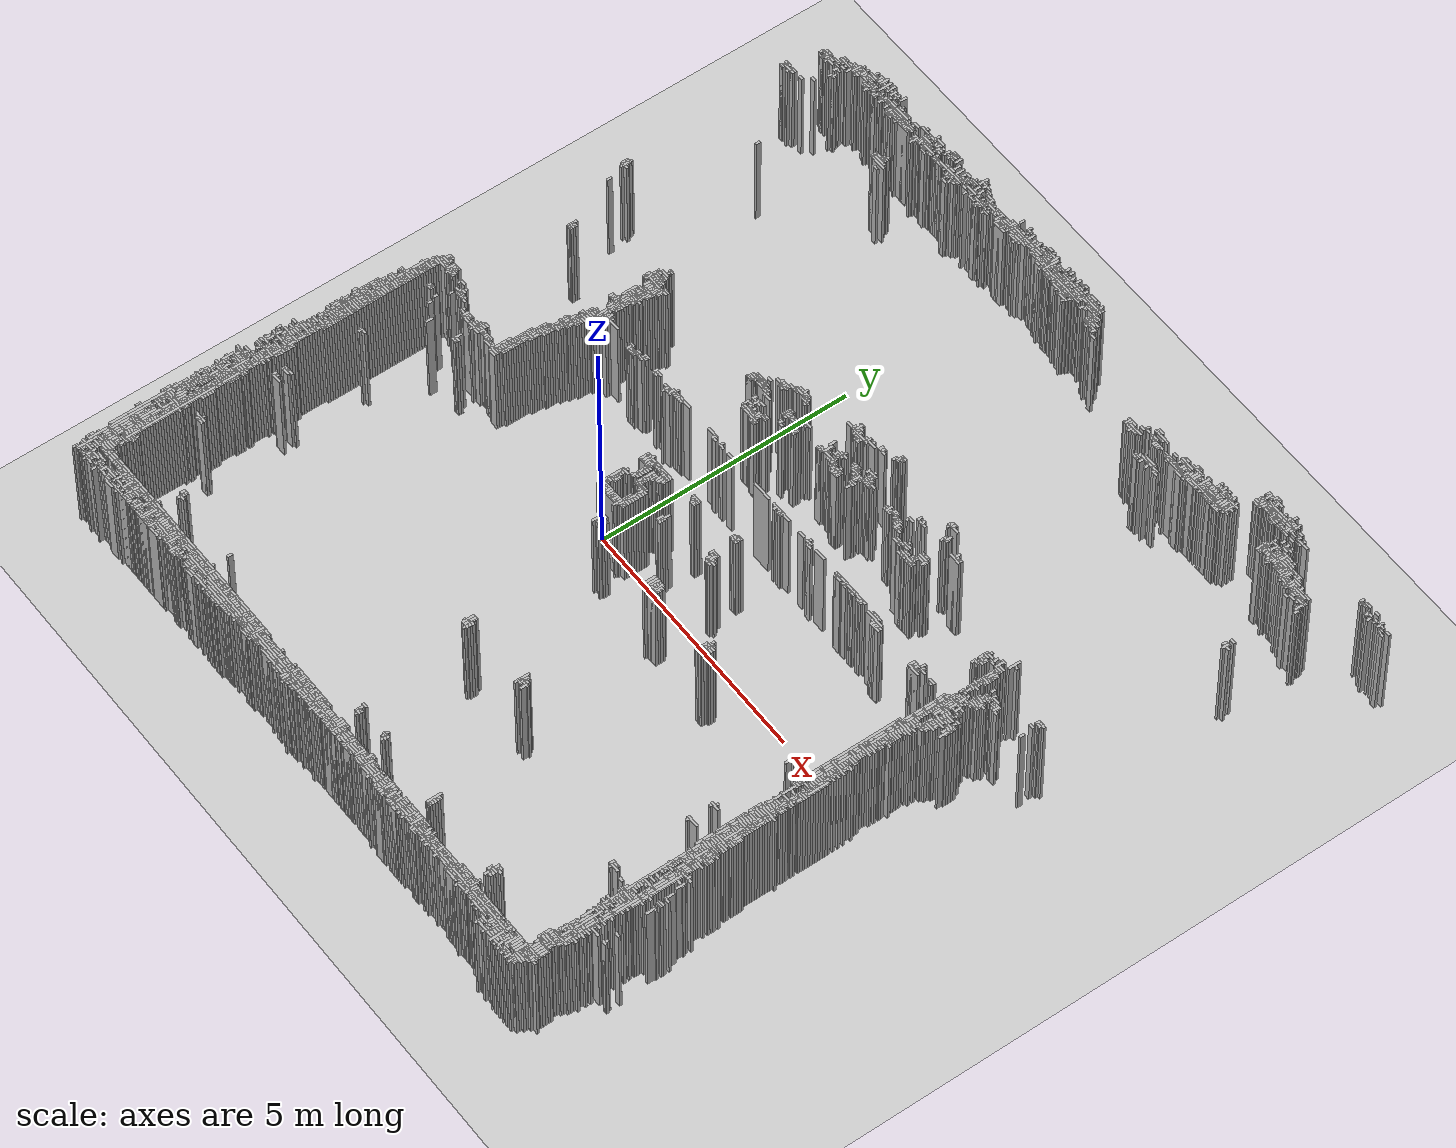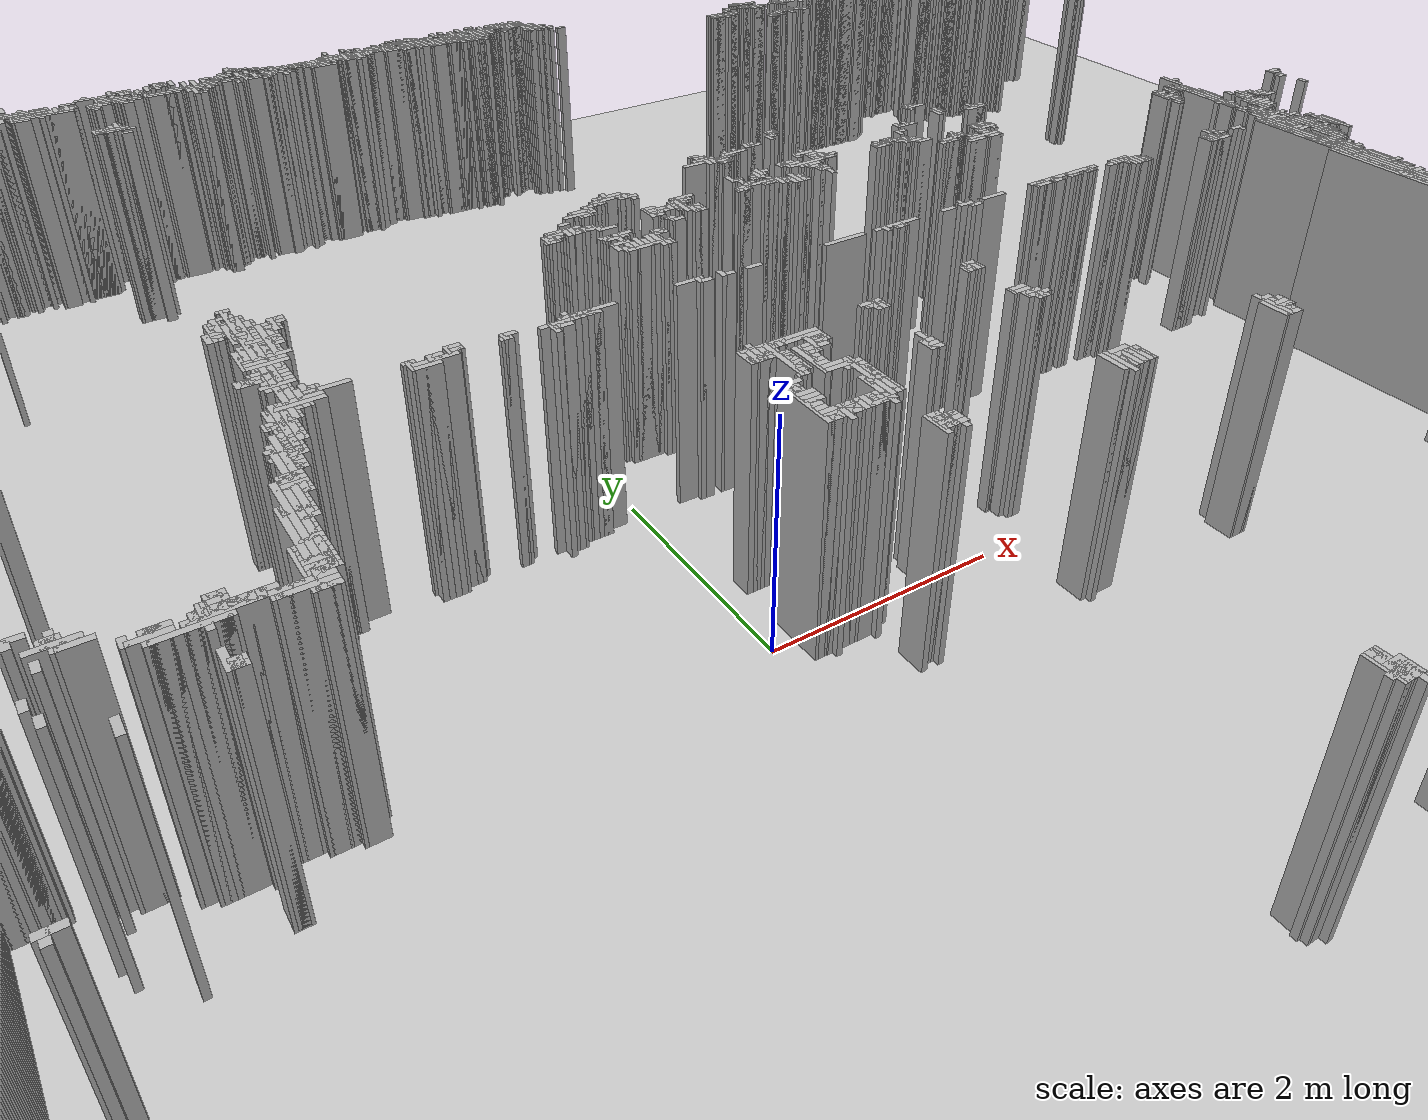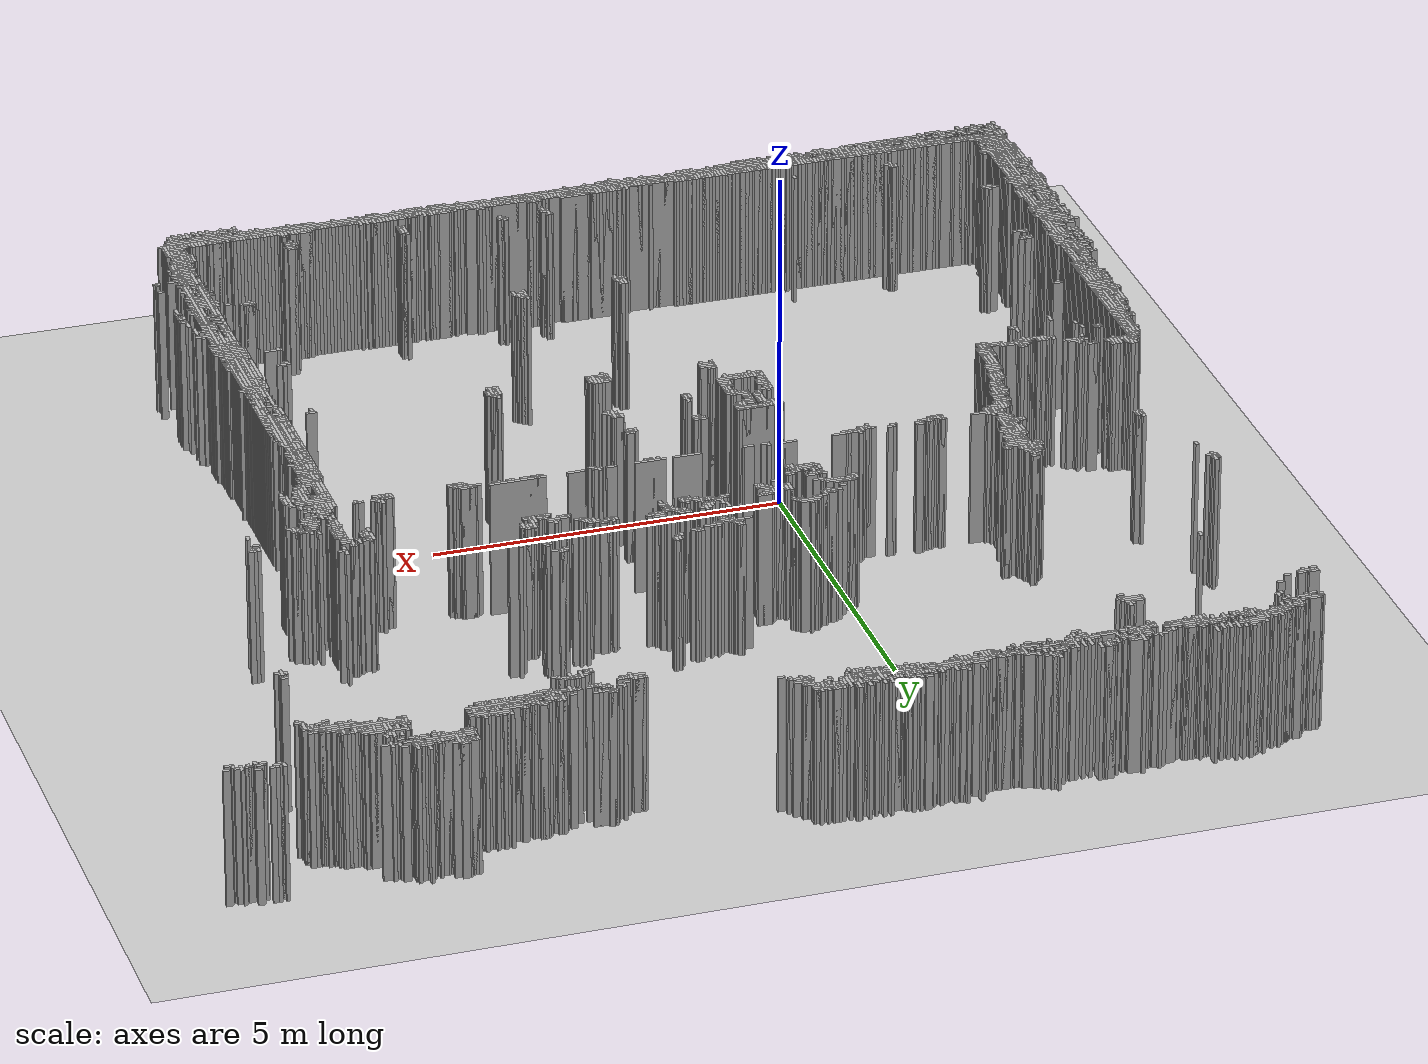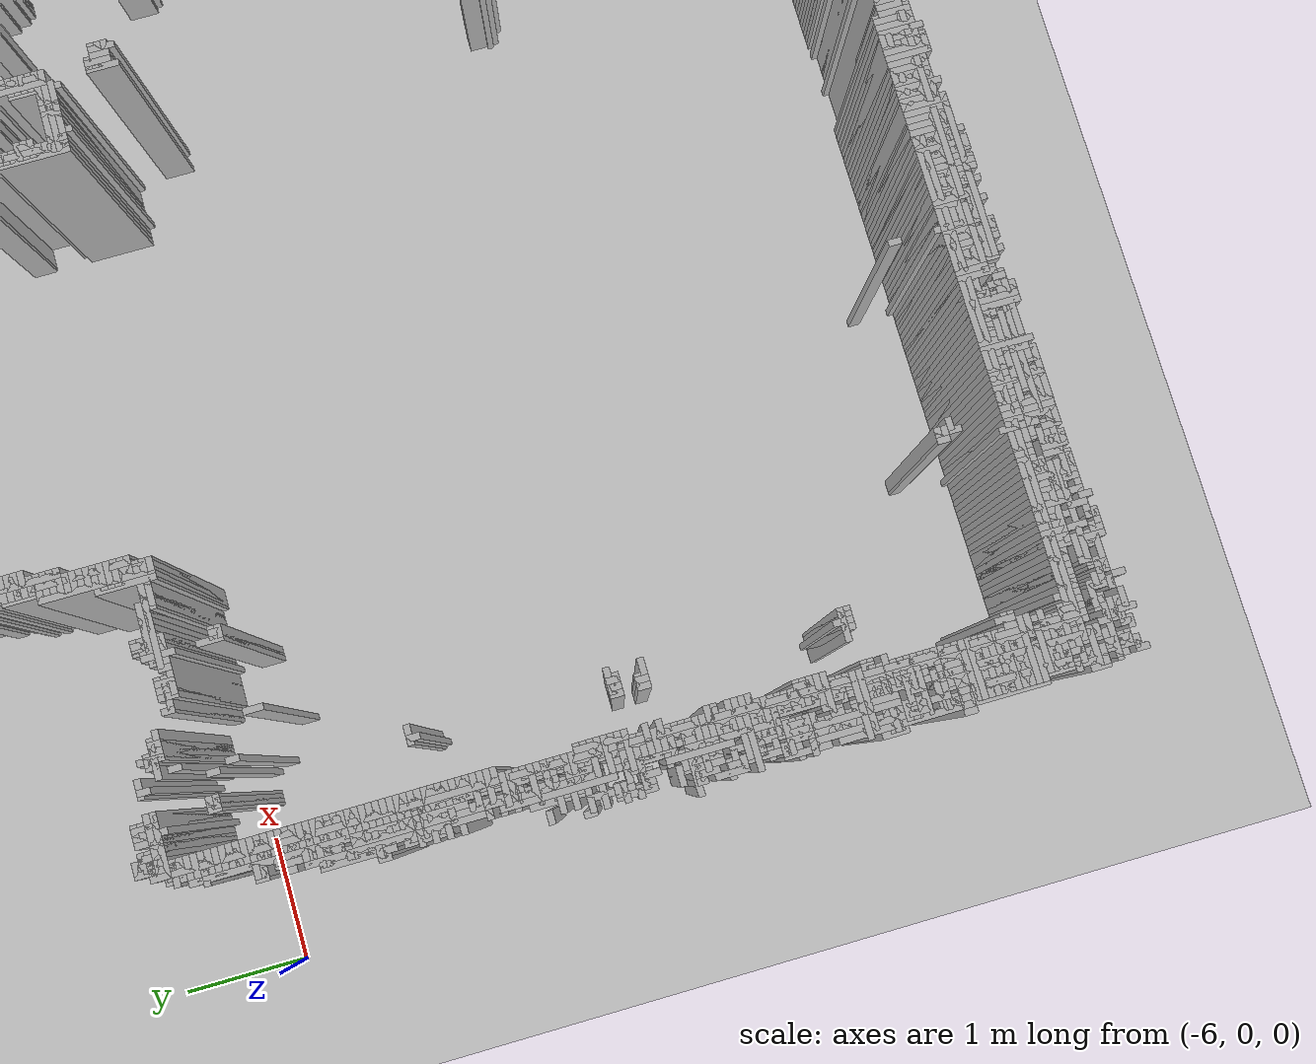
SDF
<?xml version="1.0" ?>
<sdf version="1.5">
  <world name="default">
    <!-- A global light source -->
    <include>
      <uri>model://sun</uri>
    </include>

    <!-- A ground plane -->
    <include>
      <uri>model://ground_plane</uri>
    </include>

    <!-- Map walls -->
    <model name="map_walls">
      <static>true</static>
      <link name="walls_link">

        <collision name="wall_h_collision_0">
          <pose>-0.9800000000000002 8.635000000000002 1.0 0 0 0</pose>
          <geometry>
            <box>
              <size>0.1 0.05 2.0</size>
            </box>
          </geometry>
        </collision>
        <visual name="wall_h_visual_0">
          <pose>-0.9800000000000002 8.635000000000002 1.0 0 0 0</pose>
          <geometry>
            <box>
              <size>0.1 0.05 2.0</size>
            </box>
          </geometry>
          <material>
            <script>
              <uri>file://media/materials/scripts/gazebo.material</uri>
              <n>Gazebo/Grey</n>
            </script>
          </material>
        </visual>
        <collision name="wall_h_collision_1">
          <pose>0.7699999999999998 8.635000000000002 1.0 0 0 0</pose>
          <geometry>
            <box>
              <size>0.1 0.05 2.0</size>
            </box>
          </geometry>
        </collision>
        <visual name="wall_h_visual_1">
          <pose>0.7699999999999998 8.635000000000002 1.0 0 0 0</pose>
          <geometry>
            <box>
              <size>0.1 0.05 2.0</size>
            </box>
          </geometry>
          <material>
            <script>
              <uri>file://media/materials/scripts/gazebo.material</uri>
              <n>Gazebo/Grey</n>
            </script>
          </material>
        </visual>
        <collision name="wall_h_collision_2">
          <pose>1.7200000000000009 8.635000000000002 1.0 0 0 0</pose>
          <geometry>
            <box>
              <size>0.1 0.05 2.0</size>
            </box>
          </geometry>
        </collision>
        <visual name="wall_h_visual_2">
          <pose>1.7200000000000009 8.635000000000002 1.0 0 0 0</pose>
          <geometry>
            <box>
              <size>0.1 0.05 2.0</size>
            </box>
          </geometry>
          <material>
            <script>
              <uri>file://media/materials/scripts/gazebo.material</uri>
              <n>Gazebo/Grey</n>
            </script>
          </material>
        </visual>
        <collision name="wall_h_collision_3">
          <pose>-3.755 8.585 1.0 0 0 0</pose>
          <geometry>
            <box>
              <size>0.15000000000000002 0.05 2.0</size>
            </box>
          </geometry>
        </collision>
        <visual name="wall_h_visual_3">
          <pose>-3.755 8.585 1.0 0 0 0</pose>
          <geometry>
            <box>
              <size>0.15000000000000002 0.05 2.0</size>
            </box>
          </geometry>
          <material>
            <script>
              <uri>file://media/materials/scripts/gazebo.material</uri>
              <n>Gazebo/Grey</n>
            </script>
          </material>
        </visual>
        <collision name="wall_h_collision_4">
          <pose>-1.7550000000000001 8.585 1.0 0 0 0</pose>
          <geometry>
            <box>
              <size>0.15000000000000002 0.05 2.0</size>
            </box>
          </geometry>
        </collision>
        <visual name="wall_h_visual_4">
          <pose>-1.7550000000000001 8.585 1.0 0 0 0</pose>
          <geometry>
            <box>
              <size>0.15000000000000002 0.05 2.0</size>
            </box>
          </geometry>
          <material>
            <script>
              <uri>file://media/materials/scripts/gazebo.material</uri>
              <n>Gazebo/Grey</n>
            </script>
          </material>
        </visual>
        <collision name="wall_h_collision_5">
          <pose>-0.9550000000000001 8.585 1.0 0 0 0</pose>
          <geometry>
            <box>
              <size>0.25 0.05 2.0</size>
            </box>
          </geometry>
        </collision>
        <visual name="wall_h_visual_5">
          <pose>-0.9550000000000001 8.585 1.0 0 0 0</pose>
          <geometry>
            <box>
              <size>0.25 0.05 2.0</size>
            </box>
          </geometry>
          <material>
            <script>
              <uri>file://media/materials/scripts/gazebo.material</uri>
              <n>Gazebo/Grey</n>
            </script>
          </material>
        </visual>
        <collision name="wall_h_collision_6">
          <pose>0.26999999999999974 8.585 1.0 0 0 0</pose>
          <geometry>
            <box>
              <size>0.1 0.05 2.0</size>
            </box>
          </geometry>
        </collision>
        <visual name="wall_h_visual_6">
          <pose>0.26999999999999974 8.585 1.0 0 0 0</pose>
          <geometry>
            <box>
              <size>0.1 0.05 2.0</size>
            </box>
          </geometry>
          <material>
            <script>
              <uri>file://media/materials/scripts/gazebo.material</uri>
              <n>Gazebo/Grey</n>
            </script>
          </material>
        </visual>
        <collision name="wall_h_collision_7">
          <pose>0.9700000000000001 8.585 1.0 0 0 0</pose>
          <geometry>
            <box>
              <size>0.2 0.05 2.0</size>
            </box>
          </geometry>
        </collision>
        <visual name="wall_h_visual_7">
          <pose>0.9700000000000001 8.585 1.0 0 0 0</pose>
          <geometry>
            <box>
              <size>0.2 0.05 2.0</size>
            </box>
          </geometry>
          <material>
            <script>
              <uri>file://media/materials/scripts/gazebo.material</uri>
              <n>Gazebo/Grey</n>
            </script>
          </material>
        </visual>
        <collision name="wall_h_collision_8">
          <pose>1.9950000000000008 8.585 1.0 0 0 0</pose>
          <geometry>
            <box>
              <size>0.15000000000000002 0.05 2.0</size>
            </box>
          </geometry>
        </collision>
        <visual name="wall_h_visual_8">
          <pose>1.9950000000000008 8.585 1.0 0 0 0</pose>
          <geometry>
            <box>
              <size>0.15000000000000002 0.05 2.0</size>
            </box>
          </geometry>
          <material>
            <script>
              <uri>file://media/materials/scripts/gazebo.material</uri>
              <n>Gazebo/Grey</n>
            </script>
          </material>
        </visual>
        <collision name="wall_h_collision_9">
          <pose>-3.605 8.535 1.0 0 0 0</pose>
          <geometry>
            <box>
              <size>0.65 0.05 2.0</size>
            </box>
          </geometry>
        </collision>
        <visual name="wall_h_visual_9">
          <pose>-3.605 8.535 1.0 0 0 0</pose>
          <geometry>
            <box>
              <size>0.65 0.05 2.0</size>
            </box>
          </geometry>
          <material>
            <script>
              <uri>file://media/materials/scripts/gazebo.material</uri>
              <n>Gazebo/Grey</n>
            </script>
          </material>
        </visual>
        <collision name="wall_h_collision_10">
          <pose>-2.1300000000000003 8.535 1.0 0 0 0</pose>
          <geometry>
            <box>
              <size>0.2 0.05 2.0</size>
            </box>
          </geometry>
        </collision>
        <visual name="wall_h_visual_10">
          <pose>-2.1300000000000003 8.535 1.0 0 0 0</pose>
          <geometry>
            <box>
              <size>0.2 0.05 2.0</size>
            </box>
          </geometry>
          <material>
            <script>
              <uri>file://media/materials/scripts/gazebo.material</uri>
              <n>Gazebo/Grey</n>
            </script>
          </material>
        </visual>
        <collision name="wall_h_collision_11">
          <pose>-1.7300000000000002 8.535 1.0 0 0 0</pose>
          <geometry>
            <box>
              <size>0.1 0.05 2.0</size>
            </box>
          </geometry>
        </collision>
        <visual name="wall_h_visual_11">
          <pose>-1.7300000000000002 8.535 1.0 0 0 0</pose>
          <geometry>
            <box>
              <size>0.1 0.05 2.0</size>
            </box>
          </geometry>
          <material>
            <script>
              <uri>file://media/materials/scripts/gazebo.material</uri>
              <n>Gazebo/Grey</n>
            </script>
          </material>
        </visual>
        <collision name="wall_h_collision_12">
          <pose>-0.78 8.535 1.0 0 0 0</pose>
          <geometry>
            <box>
              <size>0.1 0.05 2.0</size>
            </box>
          </geometry>
        </collision>
        <visual name="wall_h_visual_12">
          <pose>-0.78 8.535 1.0 0 0 0</pose>
          <geometry>
            <box>
              <size>0.1 0.05 2.0</size>
            </box>
          </geometry>
          <material>
            <script>
              <uri>file://media/materials/scripts/gazebo.material</uri>
              <n>Gazebo/Grey</n>
            </script>
          </material>
        </visual>
        <collision name="wall_h_collision_13">
          <pose>0.5449999999999997 8.535 1.0 0 0 0</pose>
          <geometry>
            <box>
              <size>0.15000000000000002 0.05 2.0</size>
            </box>
          </geometry>
        </collision>
        <visual name="wall_h_visual_13">
          <pose>0.5449999999999997 8.535 1.0 0 0 0</pose>
          <geometry>
            <box>
              <size>0.15000000000000002 0.05 2.0</size>
            </box>
          </geometry>
          <material>
            <script>
              <uri>file://media/materials/scripts/gazebo.material</uri>
              <n>Gazebo/Grey</n>
            </script>
          </material>
        </visual>
        <collision name="wall_h_collision_14">
          <pose>0.7949999999999999 8.535 1.0 0 0 0</pose>
          <geometry>
            <box>
              <size>0.25 0.05 2.0</size>
            </box>
          </geometry>
        </collision>
        <visual name="wall_h_visual_14">
          <pose>0.7949999999999999 8.535 1.0 0 0 0</pose>
          <geometry>
            <box>
              <size>0.25 0.05 2.0</size>
            </box>
          </geometry>
          <material>
            <script>
              <uri>file://media/materials/scripts/gazebo.material</uri>
              <n>Gazebo/Grey</n>
            </script>
          </material>
        </visual>
        <collision name="wall_h_collision_15">
          <pose>1.0199999999999998 8.535 1.0 0 0 0</pose>
          <geometry>
            <box>
              <size>0.1 0.05 2.0</size>
            </box>
          </geometry>
        </collision>
        <visual name="wall_h_visual_15">
          <pose>1.0199999999999998 8.535 1.0 0 0 0</pose>
          <geometry>
            <box>
              <size>0.1 0.05 2.0</size>
            </box>
          </geometry>
          <material>
            <script>
              <uri>file://media/materials/scripts/gazebo.material</uri>
              <n>Gazebo/Grey</n>
            </script>
          </material>
        </visual>
        <collision name="wall_h_collision_16">
          <pose>1.245 8.535 1.0 0 0 0</pose>
          <geometry>
            <box>
              <size>0.25 0.05 2.0</size>
            </box>
          </geometry>
        </collision>
        <visual name="wall_h_visual_16">
          <pose>1.245 8.535 1.0 0 0 0</pose>
          <geometry>
            <box>
              <size>0.25 0.05 2.0</size>
            </box>
          </geometry>
          <material>
            <script>
              <uri>file://media/materials/scripts/gazebo.material</uri>
              <n>Gazebo/Grey</n>
            </script>
          </material>
        </visual>
        <collision name="wall_h_collision_17">
          <pose>1.47 8.535 1.0 0 0 0</pose>
          <geometry>
            <box>
              <size>0.1 0.05 2.0</size>
            </box>
          </geometry>
        </collision>
        <visual name="wall_h_visual_17">
          <pose>1.47 8.535 1.0 0 0 0</pose>
          <geometry>
            <box>
              <size>0.1 0.05 2.0</size>
            </box>
          </geometry>
          <material>
            <script>
              <uri>file://media/materials/scripts/gazebo.material</uri>
              <n>Gazebo/Grey</n>
            </script>
          </material>
        </visual>
        <collision name="wall_h_collision_18">
          <pose>1.6699999999999995 8.535 1.0 0 0 0</pose>
          <geometry>
            <box>
              <size>0.2 0.05 2.0</size>
            </box>
          </geometry>
        </collision>
        <visual name="wall_h_visual_18">
          <pose>1.6699999999999995 8.535 1.0 0 0 0</pose>
          <geometry>
            <box>
              <size>0.2 0.05 2.0</size>
            </box>
          </geometry>
          <material>
            <script>
              <uri>file://media/materials/scripts/gazebo.material</uri>
              <n>Gazebo/Grey</n>
            </script>
          </material>
        </visual>
        <collision name="wall_h_collision_19">
          <pose>2.120000000000001 8.535 1.0 0 0 0</pose>
          <geometry>
            <box>
              <size>0.4 0.05 2.0</size>
            </box>
          </geometry>
        </collision>
        <visual name="wall_h_visual_19">
          <pose>2.120000000000001 8.535 1.0 0 0 0</pose>
          <geometry>
            <box>
              <size>0.4 0.05 2.0</size>
            </box>
          </geometry>
          <material>
            <script>
              <uri>file://media/materials/scripts/gazebo.material</uri>
              <n>Gazebo/Grey</n>
            </script>
          </material>
        </visual>
        <collision name="wall_h_collision_20">
          <pose>-3.78 8.485 1.0 0 0 0</pose>
          <geometry>
            <box>
              <size>0.4 0.05 2.0</size>
            </box>
          </geometry>
        </collision>
        <visual name="wall_h_visual_20">
          <pose>-3.78 8.485 1.0 0 0 0</pose>
          <geometry>
            <box>
              <size>0.4 0.05 2.0</size>
            </box>
          </geometry>
          <material>
            <script>
              <uri>file://media/materials/scripts/gazebo.material</uri>
              <n>Gazebo/Grey</n>
            </script>
          </material>
        </visual>
        <collision name="wall_h_collision_21">
          <pose>-2.48 8.485 1.0 0 0 0</pose>
          <geometry>
            <box>
              <size>0.2 0.05 2.0</size>
            </box>
          </geometry>
        </collision>
        <visual name="wall_h_visual_21">
          <pose>-2.48 8.485 1.0 0 0 0</pose>
          <geometry>
            <box>
              <size>0.2 0.05 2.0</size>
            </box>
          </geometry>
          <material>
            <script>
              <uri>file://media/materials/scripts/gazebo.material</uri>
              <n>Gazebo/Grey</n>
            </script>
          </material>
        </visual>
        <collision name="wall_h_collision_22">
          <pose>-2.255 8.485 1.0 0 0 0</pose>
          <geometry>
            <box>
              <size>0.15000000000000002 0.05 2.0</size>
            </box>
          </geometry>
        </collision>
        <visual name="wall_h_visual_22">
          <pose>-2.255 8.485 1.0 0 0 0</pose>
          <geometry>
            <box>
              <size>0.15000000000000002 0.05 2.0</size>
            </box>
          </geometry>
          <material>
            <script>
              <uri>file://media/materials/scripts/gazebo.material</uri>
              <n>Gazebo/Grey</n>
            </script>
          </material>
        </visual>
        <collision name="wall_h_collision_23">
          <pose>-2.08 8.485 1.0 0 0 0</pose>
          <geometry>
            <box>
              <size>0.1 0.05 2.0</size>
            </box>
          </geometry>
        </collision>
        <visual name="wall_h_visual_23">
          <pose>-2.08 8.485 1.0 0 0 0</pose>
          <geometry>
            <box>
              <size>0.1 0.05 2.0</size>
            </box>
          </geometry>
          <material>
            <script>
              <uri>file://media/materials/scripts/gazebo.material</uri>
              <n>Gazebo/Grey</n>
            </script>
          </material>
        </visual>
        <collision name="wall_h_collision_24">
          <pose>-1.7799999999999998 8.485 1.0 0 0 0</pose>
          <geometry>
            <box>
              <size>0.2 0.05 2.0</size>
            </box>
          </geometry>
        </collision>
        <visual name="wall_h_visual_24">
          <pose>-1.7799999999999998 8.485 1.0 0 0 0</pose>
          <geometry>
            <box>
              <size>0.2 0.05 2.0</size>
            </box>
          </geometry>
          <material>
            <script>
              <uri>file://media/materials/scripts/gazebo.material</uri>
              <n>Gazebo/Grey</n>
            </script>
          </material>
        </visual>
        <collision name="wall_h_collision_25">
          <pose>-1.28 8.485 1.0 0 0 0</pose>
          <geometry>
            <box>
              <size>0.1 0.05 2.0</size>
            </box>
          </geometry>
        </collision>
        <visual name="wall_h_visual_25">
          <pose>-1.28 8.485 1.0 0 0 0</pose>
          <geometry>
            <box>
              <size>0.1 0.05 2.0</size>
            </box>
          </geometry>
          <material>
            <script>
              <uri>file://media/materials/scripts/gazebo.material</uri>
              <n>Gazebo/Grey</n>
            </script>
          </material>
        </visual>
        <collision name="wall_h_collision_26">
          <pose>-1.1049999999999998 8.485 1.0 0 0 0</pose>
          <geometry>
            <box>
              <size>0.15000000000000002 0.05 2.0</size>
            </box>
          </geometry>
        </collision>
        <visual name="wall_h_visual_26">
          <pose>-1.1049999999999998 8.485 1.0 0 0 0</pose>
          <geometry>
            <box>
              <size>0.15000000000000002 0.05 2.0</size>
            </box>
          </geometry>
          <material>
            <script>
              <uri>file://media/materials/scripts/gazebo.material</uri>
              <n>Gazebo/Grey</n>
            </script>
          </material>
        </visual>
        <collision name="wall_h_collision_27">
          <pose>-0.6800000000000003 8.485 1.0 0 0 0</pose>
          <geometry>
            <box>
              <size>0.2 0.05 2.0</size>
            </box>
          </geometry>
        </collision>
        <visual name="wall_h_visual_27">
          <pose>-0.6800000000000003 8.485 1.0 0 0 0</pose>
          <geometry>
            <box>
              <size>0.2 0.05 2.0</size>
            </box>
          </geometry>
          <material>
            <script>
              <uri>file://media/materials/scripts/gazebo.material</uri>
              <n>Gazebo/Grey</n>
            </script>
          </material>
        </visual>
        <collision name="wall_h_collision_28">
          <pose>0.019999999999999934 8.485 1.0 0 0 0</pose>
          <geometry>
            <box>
              <size>0.2 0.05 2.0</size>
            </box>
          </geometry>
        </collision>
        <visual name="wall_h_visual_28">
          <pose>0.019999999999999934 8.485 1.0 0 0 0</pose>
          <geometry>
            <box>
              <size>0.2 0.05 2.0</size>
            </box>
          </geometry>
          <material>
            <script>
              <uri>file://media/materials/scripts/gazebo.material</uri>
              <n>Gazebo/Grey</n>
            </script>
          </material>
        </visual>
        <collision name="wall_h_collision_29">
          <pose>0.21999999999999992 8.485 1.0 0 0 0</pose>
          <geometry>
            <box>
              <size>0.1 0.05 2.0</size>
            </box>
          </geometry>
        </collision>
        <visual name="wall_h_visual_29">
          <pose>0.21999999999999992 8.485 1.0 0 0 0</pose>
          <geometry>
            <box>
              <size>0.1 0.05 2.0</size>
            </box>
          </geometry>
          <material>
            <script>
              <uri>file://media/materials/scripts/gazebo.material</uri>
              <n>Gazebo/Grey</n>
            </script>
          </material>
        </visual>
        <collision name="wall_h_collision_30">
          <pose>0.7700000000000002 8.485 1.0 0 0 0</pose>
          <geometry>
            <box>
              <size>0.9 0.05 2.0</size>
            </box>
          </geometry>
        </collision>
        <visual name="wall_h_visual_30">
          <pose>0.7700000000000002 8.485 1.0 0 0 0</pose>
          <geometry>
            <box>
              <size>0.9 0.05 2.0</size>
            </box>
          </geometry>
          <material>
            <script>
              <uri>file://media/materials/scripts/gazebo.material</uri>
              <n>Gazebo/Grey</n>
            </script>
          </material>
        </visual>
        <collision name="wall_h_collision_31">
          <pose>1.8200000000000003 8.485 1.0 0 0 0</pose>
          <geometry>
            <box>
              <size>1.0 0.05 2.0</size>
            </box>
          </geometry>
        </collision>
        <visual name="wall_h_visual_31">
          <pose>1.8200000000000003 8.485 1.0 0 0 0</pose>
          <geometry>
            <box>
              <size>1.0 0.05 2.0</size>
            </box>
          </geometry>
          <material>
            <script>
              <uri>file://media/materials/scripts/gazebo.material</uri>
              <n>Gazebo/Grey</n>
            </script>
          </material>
        </visual>
        <collision name="wall_h_collision_32">
          <pose>7.02 8.485 1.0 0 0 0</pose>
          <geometry>
            <box>
              <size>0.1 0.05 2.0</size>
            </box>
          </geometry>
        </collision>
        <visual name="wall_h_visual_32">
          <pose>7.02 8.485 1.0 0 0 0</pose>
          <geometry>
            <box>
              <size>0.1 0.05 2.0</size>
            </box>
          </geometry>
          <material>
            <script>
              <uri>file://media/materials/scripts/gazebo.material</uri>
              <n>Gazebo/Grey</n>
            </script>
          </material>
        </visual>
        <collision name="wall_h_collision_33">
          <pose>-4.03 8.435000000000002 1.0 0 0 0</pose>
          <geometry>
            <box>
              <size>0.4 0.05 2.0</size>
            </box>
          </geometry>
        </collision>
        <visual name="wall_h_visual_33">
          <pose>-4.03 8.435000000000002 1.0 0 0 0</pose>
          <geometry>
            <box>
              <size>0.4 0.05 2.0</size>
            </box>
          </geometry>
          <material>
            <script>
              <uri>file://media/materials/scripts/gazebo.material</uri>
              <n>Gazebo/Grey</n>
            </script>
          </material>
        </visual>
        <collision name="wall_h_collision_34">
          <pose>-3.2300000000000004 8.435000000000002 1.0 0 0 0</pose>
          <geometry>
            <box>
              <size>0.1 0.05 2.0</size>
            </box>
          </geometry>
        </collision>
        <visual name="wall_h_visual_34">
          <pose>-3.2300000000000004 8.435000000000002 1.0 0 0 0</pose>
          <geometry>
            <box>
              <size>0.1 0.05 2.0</size>
            </box>
          </geometry>
          <material>
            <script>
              <uri>file://media/materials/scripts/gazebo.material</uri>
              <n>Gazebo/Grey</n>
            </script>
          </material>
        </visual>
        <collision name="wall_h_collision_35">
          <pose>-3.08 8.435000000000002 1.0 0 0 0</pose>
          <geometry>
            <box>
              <size>0.1 0.05 2.0</size>
            </box>
          </geometry>
        </collision>
        <visual name="wall_h_visual_35">
          <pose>-3.08 8.435000000000002 1.0 0 0 0</pose>
          <geometry>
            <box>
              <size>0.1 0.05 2.0</size>
            </box>
          </geometry>
          <material>
            <script>
              <uri>file://media/materials/scripts/gazebo.material</uri>
              <n>Gazebo/Grey</n>
            </script>
          </material>
        </visual>
        <collision name="wall_h_collision_36">
          <pose>-2.905 8.435000000000002 1.0 0 0 0</pose>
          <geometry>
            <box>
              <size>0.15000000000000002 0.05 2.0</size>
            </box>
          </geometry>
        </collision>
        <visual name="wall_h_visual_36">
          <pose>-2.905 8.435000000000002 1.0 0 0 0</pose>
          <geometry>
            <box>
              <size>0.15000000000000002 0.05 2.0</size>
            </box>
          </geometry>
          <material>
            <script>
              <uri>file://media/materials/scripts/gazebo.material</uri>
              <n>Gazebo/Grey</n>
            </script>
          </material>
        </visual>
        <collision name="wall_h_collision_37">
          <pose>-2.655 8.435000000000002 1.0 0 0 0</pose>
          <geometry>
            <box>
              <size>0.15000000000000002 0.05 2.0</size>
            </box>
          </geometry>
        </collision>
        <visual name="wall_h_visual_37">
          <pose>-2.655 8.435000000000002 1.0 0 0 0</pose>
          <geometry>
            <box>
              <size>0.15000000000000002 0.05 2.0</size>
            </box>
          </geometry>
          <material>
            <script>
              <uri>file://media/materials/scripts/gazebo.material</uri>
              <n>Gazebo/Grey</n>
            </script>
          </material>
        </visual>
        <collision name="wall_h_collision_38">
          <pose>-2.33 8.435000000000002 1.0 0 0 0</pose>
          <geometry>
            <box>
              <size>0.1 0.05 2.0</size>
            </box>
          </geometry>
        </collision>
        <visual name="wall_h_visual_38">
          <pose>-2.33 8.435000000000002 1.0 0 0 0</pose>
          <geometry>
            <box>
              <size>0.1 0.05 2.0</size>
            </box>
          </geometry>
          <material>
            <script>
              <uri>file://media/materials/scripts/gazebo.material</uri>
              <n>Gazebo/Grey</n>
            </script>
          </material>
        </visual>
        <collision name="wall_h_collision_39">
          <pose>-2.03 8.435000000000002 1.0 0 0 0</pose>
          <geometry>
            <box>
              <size>0.2 0.05 2.0</size>
            </box>
          </geometry>
        </collision>
        <visual name="wall_h_visual_39">
          <pose>-2.03 8.435000000000002 1.0 0 0 0</pose>
          <geometry>
            <box>
              <size>0.2 0.05 2.0</size>
            </box>
          </geometry>
          <material>
            <script>
              <uri>file://media/materials/scripts/gazebo.material</uri>
              <n>Gazebo/Grey</n>
            </script>
          </material>
        </visual>
        <collision name="wall_h_collision_40">
          <pose>-1.1299999999999994 8.435000000000002 1.0 0 0 0</pose>
          <geometry>
            <box>
              <size>0.2 0.05 2.0</size>
            </box>
          </geometry>
        </collision>
        <visual name="wall_h_visual_40">
          <pose>-1.1299999999999994 8.435000000000002 1.0 0 0 0</pose>
          <geometry>
            <box>
              <size>0.2 0.05 2.0</size>
            </box>
          </geometry>
          <material>
            <script>
              <uri>file://media/materials/scripts/gazebo.material</uri>
              <n>Gazebo/Grey</n>
            </script>
          </material>
        </visual>
        <collision name="wall_h_collision_41">
          <pose>-0.5549999999999999 8.435000000000002 1.0 0 0 0</pose>
          <geometry>
            <box>
              <size>0.15000000000000002 0.05 2.0</size>
            </box>
          </geometry>
        </collision>
        <visual name="wall_h_visual_41">
          <pose>-0.5549999999999999 8.435000000000002 1.0 0 0 0</pose>
          <geometry>
            <box>
              <size>0.15000000000000002 0.05 2.0</size>
            </box>
          </geometry>
          <material>
            <script>
              <uri>file://media/materials/scripts/gazebo.material</uri>
              <n>Gazebo/Grey</n>
            </script>
          </material>
        </visual>
        <collision name="wall_h_collision_42">
          <pose>-0.32999999999999974 8.435000000000002 1.0 0 0 0</pose>
          <geometry>
            <box>
              <size>0.2 0.05 2.0</size>
            </box>
          </geometry>
        </collision>
        <visual name="wall_h_visual_42">
          <pose>-0.32999999999999974 8.435000000000002 1.0 0 0 0</pose>
          <geometry>
            <box>
              <size>0.2 0.05 2.0</size>
            </box>
          </geometry>
          <material>
            <script>
              <uri>file://media/materials/scripts/gazebo.material</uri>
              <n>Gazebo/Grey</n>
            </script>
          </material>
        </visual>
        <collision name="wall_h_collision_43">
          <pose>0.2950000000000003 8.435000000000002 1.0 0 0 0</pose>
          <geometry>
            <box>
              <size>0.9500000000000001 0.05 2.0</size>
            </box>
          </geometry>
        </collision>
        <visual name="wall_h_visual_43">
          <pose>0.2950000000000003 8.435000000000002 1.0 0 0 0</pose>
          <geometry>
            <box>
              <size>0.9500000000000001 0.05 2.0</size>
            </box>
          </geometry>
          <material>
            <script>
              <uri>file://media/materials/scripts/gazebo.material</uri>
              <n>Gazebo/Grey</n>
            </script>
          </material>
        </visual>
        <collision name="wall_h_collision_44">
          <pose>1.2200000000000002 8.435000000000002 1.0 0 0 0</pose>
          <geometry>
            <box>
              <size>0.8 0.05 2.0</size>
            </box>
          </geometry>
        </collision>
        <visual name="wall_h_visual_44">
          <pose>1.2200000000000002 8.435000000000002 1.0 0 0 0</pose>
          <geometry>
            <box>
              <size>0.8 0.05 2.0</size>
            </box>
          </geometry>
          <material>
            <script>
              <uri>file://media/materials/scripts/gazebo.material</uri>
              <n>Gazebo/Grey</n>
            </script>
          </material>
        </visual>
        <collision name="wall_h_collision_45">
          <pose>1.9950000000000008 8.435000000000002 1.0 0 0 0</pose>
          <geometry>
            <box>
              <size>0.65 0.05 2.0</size>
            </box>
          </geometry>
        </collision>
        <visual name="wall_h_visual_45">
          <pose>1.9950000000000008 8.435000000000002 1.0 0 0 0</pose>
          <geometry>
            <box>
              <size>0.65 0.05 2.0</size>
            </box>
          </geometry>
          <material>
            <script>
              <uri>file://media/materials/scripts/gazebo.material</uri>
              <n>Gazebo/Grey</n>
            </script>
          </material>
        </visual>
        <collision name="wall_h_collision_46">
          <pose>6.995000000000001 8.435000000000002 1.0 0 0 0</pose>
          <geometry>
            <box>
              <size>0.35000000000000003 0.05 2.0</size>
            </box>
          </geometry>
        </collision>
        <visual name="wall_h_visual_46">
          <pose>6.995000000000001 8.435000000000002 1.0 0 0 0</pose>
          <geometry>
            <box>
              <size>0.35000000000000003 0.05 2.0</size>
            </box>
          </geometry>
          <material>
            <script>
              <uri>file://media/materials/scripts/gazebo.material</uri>
              <n>Gazebo/Grey</n>
            </script>
          </material>
        </visual>
        <collision name="wall_h_collision_47">
          <pose>-4.005 8.385000000000002 1.0 0 0 0</pose>
          <geometry>
            <box>
              <size>0.65 0.05 2.0</size>
            </box>
          </geometry>
        </collision>
        <visual name="wall_h_visual_47">
          <pose>-4.005 8.385000000000002 1.0 0 0 0</pose>
          <geometry>
            <box>
              <size>0.65 0.05 2.0</size>
            </box>
          </geometry>
          <material>
            <script>
              <uri>file://media/materials/scripts/gazebo.material</uri>
              <n>Gazebo/Grey</n>
            </script>
          </material>
        </visual>
        <collision name="wall_h_collision_48">
          <pose>-3.13 8.385000000000002 1.0 0 0 0</pose>
          <geometry>
            <box>
              <size>0.6000000000000001 0.05 2.0</size>
            </box>
          </geometry>
        </collision>
        <visual name="wall_h_visual_48">
          <pose>-3.13 8.385000000000002 1.0 0 0 0</pose>
          <geometry>
            <box>
              <size>0.6000000000000001 0.05 2.0</size>
            </box>
          </geometry>
          <material>
            <script>
              <uri>file://media/materials/scripts/gazebo.material</uri>
              <n>Gazebo/Grey</n>
            </script>
          </material>
        </visual>
        <collision name="wall_h_collision_49">
          <pose>-2.255 8.385000000000002 1.0 0 0 0</pose>
          <geometry>
            <box>
              <size>0.25 0.05 2.0</size>
            </box>
          </geometry>
        </collision>
        <visual name="wall_h_visual_49">
          <pose>-2.255 8.385000000000002 1.0 0 0 0</pose>
          <geometry>
            <box>
              <size>0.25 0.05 2.0</size>
            </box>
          </geometry>
          <material>
            <script>
              <uri>file://media/materials/scripts/gazebo.material</uri>
              <n>Gazebo/Grey</n>
            </script>
          </material>
        </visual>
        <collision name="wall_h_collision_50">
          <pose>-1.9800000000000002 8.385000000000002 1.0 0 0 0</pose>
          <geometry>
            <box>
              <size>0.1 0.05 2.0</size>
            </box>
          </geometry>
        </collision>
        <visual name="wall_h_visual_50">
          <pose>-1.9800000000000002 8.385000000000002 1.0 0 0 0</pose>
          <geometry>
            <box>
              <size>0.1 0.05 2.0</size>
            </box>
          </geometry>
          <material>
            <script>
              <uri>file://media/materials/scripts/gazebo.material</uri>
              <n>Gazebo/Grey</n>
            </script>
          </material>
        </visual>
        <collision name="wall_h_collision_51">
          <pose>-1.23 8.385000000000002 1.0 0 0 0</pose>
          <geometry>
            <box>
              <size>0.2 0.05 2.0</size>
            </box>
          </geometry>
        </collision>
        <visual name="wall_h_visual_51">
          <pose>-1.23 8.385000000000002 1.0 0 0 0</pose>
          <geometry>
            <box>
              <size>0.2 0.05 2.0</size>
            </box>
          </geometry>
          <material>
            <script>
              <uri>file://media/materials/scripts/gazebo.material</uri>
              <n>Gazebo/Grey</n>
            </script>
          </material>
        </visual>
        <collision name="wall_h_collision_52">
          <pose>-0.8799999999999996 8.385000000000002 1.0 0 0 0</pose>
          <geometry>
            <box>
              <size>0.2 0.05 2.0</size>
            </box>
          </geometry>
        </collision>
        <visual name="wall_h_visual_52">
          <pose>-0.8799999999999996 8.385000000000002 1.0 0 0 0</pose>
          <geometry>
            <box>
              <size>0.2 0.05 2.0</size>
            </box>
          </geometry>
          <material>
            <script>
              <uri>file://media/materials/scripts/gazebo.material</uri>
              <n>Gazebo/Grey</n>
            </script>
          </material>
        </visual>
        <collision name="wall_h_collision_53">
          <pose>0.2450000000000001 8.385000000000002 1.0 0 0 0</pose>
          <geometry>
            <box>
              <size>1.75 0.05 2.0</size>
            </box>
          </geometry>
        </collision>
        <visual name="wall_h_visual_53">
          <pose>0.2450000000000001 8.385000000000002 1.0 0 0 0</pose>
          <geometry>
            <box>
              <size>1.75 0.05 2.0</size>
            </box>
          </geometry>
          <material>
            <script>
              <uri>file://media/materials/scripts/gazebo.material</uri>
              <n>Gazebo/Grey</n>
            </script>
          </material>
        </visual>
        <collision name="wall_h_collision_54">
          <pose>1.545 8.385000000000002 1.0 0 0 0</pose>
          <geometry>
            <box>
              <size>0.75 0.05 2.0</size>
            </box>
          </geometry>
        </collision>
        <visual name="wall_h_visual_54">
          <pose>1.545 8.385000000000002 1.0 0 0 0</pose>
          <geometry>
            <box>
              <size>0.75 0.05 2.0</size>
            </box>
          </geometry>
          <material>
            <script>
              <uri>file://media/materials/scripts/gazebo.material</uri>
              <n>Gazebo/Grey</n>
            </script>
          </material>
        </visual>
        <collision name="wall_h_collision_55">
          <pose>2.244999999999999 8.385000000000002 1.0 0 0 0</pose>
          <geometry>
            <box>
              <size>0.35000000000000003 0.05 2.0</size>
            </box>
          </geometry>
        </collision>
        <visual name="wall_h_visual_55">
          <pose>2.244999999999999 8.385000000000002 1.0 0 0 0</pose>
          <geometry>
            <box>
              <size>0.35000000000000003 0.05 2.0</size>
            </box>
          </geometry>
          <material>
            <script>
              <uri>file://media/materials/scripts/gazebo.material</uri>
              <n>Gazebo/Grey</n>
            </script>
          </material>
        </visual>
        <collision name="wall_h_collision_56">
          <pose>6.895000000000001 8.385000000000002 1.0 0 0 0</pose>
          <geometry>
            <box>
              <size>0.15000000000000002 0.05 2.0</size>
            </box>
          </geometry>
        </collision>
        <visual name="wall_h_visual_56">
          <pose>6.895000000000001 8.385000000000002 1.0 0 0 0</pose>
          <geometry>
            <box>
              <size>0.15000000000000002 0.05 2.0</size>
            </box>
          </geometry>
          <material>
            <script>
              <uri>file://media/materials/scripts/gazebo.material</uri>
              <n>Gazebo/Grey</n>
            </script>
          </material>
        </visual>
        <collision name="wall_h_collision_57">
          <pose>7.07 8.385000000000002 1.0 0 0 0</pose>
          <geometry>
            <box>
              <size>0.1 0.05 2.0</size>
            </box>
          </geometry>
        </collision>
        <visual name="wall_h_visual_57">
          <pose>7.07 8.385000000000002 1.0 0 0 0</pose>
          <geometry>
            <box>
              <size>0.1 0.05 2.0</size>
            </box>
          </geometry>
          <material>
            <script>
              <uri>file://media/materials/scripts/gazebo.material</uri>
              <n>Gazebo/Grey</n>
            </script>
          </material>
        </visual>
        <collision name="wall_h_collision_58">
          <pose>7.545000000000001 8.385000000000002 1.0 0 0 0</pose>
          <geometry>
            <box>
              <size>0.25 0.05 2.0</size>
            </box>
          </geometry>
        </collision>
        <visual name="wall_h_visual_58">
          <pose>7.545000000000001 8.385000000000002 1.0 0 0 0</pose>
          <geometry>
            <box>
              <size>0.25 0.05 2.0</size>
            </box>
          </geometry>
          <material>
            <script>
              <uri>file://media/materials/scripts/gazebo.material</uri>
              <n>Gazebo/Grey</n>
            </script>
          </material>
        </visual>
        <collision name="wall_h_collision_59">
          <pose>-4.48 8.335 1.0 0 0 0</pose>
          <geometry>
            <box>
              <size>0.1 0.05 2.0</size>
            </box>
          </geometry>
        </collision>
        <visual name="wall_h_visual_59">
          <pose>-4.48 8.335 1.0 0 0 0</pose>
          <geometry>
            <box>
              <size>0.1 0.05 2.0</size>
            </box>
          </geometry>
          <material>
            <script>
              <uri>file://media/materials/scripts/gazebo.material</uri>
              <n>Gazebo/Grey</n>
            </script>
          </material>
        </visual>
        <collision name="wall_h_collision_60">
          <pose>-4.130000000000001 8.335 1.0 0 0 0</pose>
          <geometry>
            <box>
              <size>0.5 0.05 2.0</size>
            </box>
          </geometry>
        </collision>
        <visual name="wall_h_visual_60">
          <pose>-4.130000000000001 8.335 1.0 0 0 0</pose>
          <geometry>
            <box>
              <size>0.5 0.05 2.0</size>
            </box>
          </geometry>
          <material>
            <script>
              <uri>file://media/materials/scripts/gazebo.material</uri>
              <n>Gazebo/Grey</n>
            </script>
          </material>
        </visual>
        <collision name="wall_h_collision_61">
          <pose>-3.73 8.335 1.0 0 0 0</pose>
          <geometry>
            <box>
              <size>0.2 0.05 2.0</size>
            </box>
          </geometry>
        </collision>
        <visual name="wall_h_visual_61">
          <pose>-3.73 8.335 1.0 0 0 0</pose>
          <geometry>
            <box>
              <size>0.2 0.05 2.0</size>
            </box>
          </geometry>
          <material>
            <script>
              <uri>file://media/materials/scripts/gazebo.material</uri>
              <n>Gazebo/Grey</n>
            </script>
          </material>
        </visual>
        <collision name="wall_h_collision_62">
          <pose>-3.08 8.335 1.0 0 0 0</pose>
          <geometry>
            <box>
              <size>1.0 0.05 2.0</size>
            </box>
          </geometry>
        </collision>
        <visual name="wall_h_visual_62">
          <pose>-3.08 8.335 1.0 0 0 0</pose>
          <geometry>
            <box>
              <size>1.0 0.05 2.0</size>
            </box>
          </geometry>
          <material>
            <script>
              <uri>file://media/materials/scripts/gazebo.material</uri>
              <n>Gazebo/Grey</n>
            </script>
          </material>
        </visual>
        <collision name="wall_h_collision_63">
          <pose>-2.23 8.335 1.0 0 0 0</pose>
          <geometry>
            <box>
              <size>0.30000000000000004 0.05 2.0</size>
            </box>
          </geometry>
        </collision>
        <visual name="wall_h_visual_63">
          <pose>-2.23 8.335 1.0 0 0 0</pose>
          <geometry>
            <box>
              <size>0.30000000000000004 0.05 2.0</size>
            </box>
          </geometry>
          <material>
            <script>
              <uri>file://media/materials/scripts/gazebo.material</uri>
              <n>Gazebo/Grey</n>
            </script>
          </material>
        </visual>
        <collision name="wall_h_collision_64">
          <pose>-1.5799999999999996 8.335 1.0 0 0 0</pose>
          <geometry>
            <box>
              <size>0.2 0.05 2.0</size>
            </box>
          </geometry>
        </collision>
        <visual name="wall_h_visual_64">
          <pose>-1.5799999999999996 8.335 1.0 0 0 0</pose>
          <geometry>
            <box>
              <size>0.2 0.05 2.0</size>
            </box>
          </geometry>
          <material>
            <script>
              <uri>file://media/materials/scripts/gazebo.material</uri>
              <n>Gazebo/Grey</n>
            </script>
          </material>
        </visual>
        <collision name="wall_h_collision_65">
          <pose>-1.3049999999999997 8.335 1.0 0 0 0</pose>
          <geometry>
            <box>
              <size>0.25 0.05 2.0</size>
            </box>
          </geometry>
        </collision>
        <visual name="wall_h_visual_65">
          <pose>-1.3049999999999997 8.335 1.0 0 0 0</pose>
          <geometry>
            <box>
              <size>0.25 0.05 2.0</size>
            </box>
          </geometry>
          <material>
            <script>
              <uri>file://media/materials/scripts/gazebo.material</uri>
              <n>Gazebo/Grey</n>
            </script>
          </material>
        </visual>
        <collision name="wall_h_collision_66">
          <pose>-1.005 8.335 1.0 0 0 0</pose>
          <geometry>
            <box>
              <size>0.25 0.05 2.0</size>
            </box>
          </geometry>
        </collision>
        <visual name="wall_h_visual_66">
          <pose>-1.005 8.335 1.0 0 0 0</pose>
          <geometry>
            <box>
              <size>0.25 0.05 2.0</size>
            </box>
          </geometry>
          <material>
            <script>
              <uri>file://media/materials/scripts/gazebo.material</uri>
              <n>Gazebo/Grey</n>
            </script>
          </material>
        </visual>
        <collision name="wall_h_collision_67">
          <pose>-0.6549999999999996 8.335 1.0 0 0 0</pose>
          <geometry>
            <box>
              <size>0.15000000000000002 0.05 2.0</size>
            </box>
          </geometry>
        </collision>
        <visual name="wall_h_visual_67">
          <pose>-0.6549999999999996 8.335 1.0 0 0 0</pose>
          <geometry>
            <box>
              <size>0.15000000000000002 0.05 2.0</size>
            </box>
          </geometry>
          <material>
            <script>
              <uri>file://media/materials/scripts/gazebo.material</uri>
              <n>Gazebo/Grey</n>
            </script>
          </material>
        </visual>
        <collision name="wall_h_collision_68">
          <pose>-0.3799999999999997 8.335 1.0 0 0 0</pose>
          <geometry>
            <box>
              <size>0.1 0.05 2.0</size>
            </box>
          </geometry>
        </collision>
        <visual name="wall_h_visual_68">
          <pose>-0.3799999999999997 8.335 1.0 0 0 0</pose>
          <geometry>
            <box>
              <size>0.1 0.05 2.0</size>
            </box>
          </geometry>
          <material>
            <script>
              <uri>file://media/materials/scripts/gazebo.material</uri>
              <n>Gazebo/Grey</n>
            </script>
          </material>
        </visual>
        <collision name="wall_h_collision_69">
          <pose>0.09499999999999975 8.335 1.0 0 0 0</pose>
          <geometry>
            <box>
              <size>0.75 0.05 2.0</size>
            </box>
          </geometry>
        </collision>
        <visual name="wall_h_visual_69">
          <pose>0.09499999999999975 8.335 1.0 0 0 0</pose>
          <geometry>
            <box>
              <size>0.75 0.05 2.0</size>
            </box>
          </geometry>
          <material>
            <script>
              <uri>file://media/materials/scripts/gazebo.material</uri>
              <n>Gazebo/Grey</n>
            </script>
          </material>
        </visual>
        <collision name="wall_h_collision_70">
          <pose>1.27 8.335 1.0 0 0 0</pose>
          <geometry>
            <box>
              <size>1.3 0.05 2.0</size>
            </box>
          </geometry>
        </collision>
        <visual name="wall_h_visual_70">
          <pose>1.27 8.335 1.0 0 0 0</pose>
          <geometry>
            <box>
              <size>1.3 0.05 2.0</size>
            </box>
          </geometry>
          <material>
            <script>
              <uri>file://media/materials/scripts/gazebo.material</uri>
              <n>Gazebo/Grey</n>
            </script>
          </material>
        </visual>
        <collision name="wall_h_collision_71">
          <pose>2.0700000000000003 8.335 1.0 0 0 0</pose>
          <geometry>
            <box>
              <size>0.1 0.05 2.0</size>
            </box>
          </geometry>
        </collision>
        <visual name="wall_h_visual_71">
          <pose>2.0700000000000003 8.335 1.0 0 0 0</pose>
          <geometry>
            <box>
              <size>0.1 0.05 2.0</size>
            </box>
          </geometry>
          <material>
            <script>
              <uri>file://media/materials/scripts/gazebo.material</uri>
              <n>Gazebo/Grey</n>
            </script>
          </material>
        </visual>
        <collision name="wall_h_collision_72">
          <pose>2.3450000000000006 8.335 1.0 0 0 0</pose>
          <geometry>
            <box>
              <size>0.15000000000000002 0.05 2.0</size>
            </box>
          </geometry>
        </collision>
        <visual name="wall_h_visual_72">
          <pose>2.3450000000000006 8.335 1.0 0 0 0</pose>
          <geometry>
            <box>
              <size>0.15000000000000002 0.05 2.0</size>
            </box>
          </geometry>
          <material>
            <script>
              <uri>file://media/materials/scripts/gazebo.material</uri>
              <n>Gazebo/Grey</n>
            </script>
          </material>
        </visual>
        <collision name="wall_h_collision_73">
          <pose>7.319999999999999 8.335 1.0 0 0 0</pose>
          <geometry>
            <box>
              <size>0.7000000000000001 0.05 2.0</size>
            </box>
          </geometry>
        </collision>
        <visual name="wall_h_visual_73">
          <pose>7.319999999999999 8.335 1.0 0 0 0</pose>
          <geometry>
            <box>
              <size>0.7000000000000001 0.05 2.0</size>
            </box>
          </geometry>
          <material>
            <script>
              <uri>file://media/materials/scripts/gazebo.material</uri>
              <n>Gazebo/Grey</n>
            </script>
          </material>
        </visual>
        <collision name="wall_h_collision_74">
          <pose>7.77 8.335 1.0 0 0 0</pose>
          <geometry>
            <box>
              <size>0.1 0.05 2.0</size>
            </box>
          </geometry>
        </collision>
        <visual name="wall_h_visual_74">
          <pose>7.77 8.335 1.0 0 0 0</pose>
          <geometry>
            <box>
              <size>0.1 0.05 2.0</size>
            </box>
          </geometry>
          <material>
            <script>
              <uri>file://media/materials/scripts/gazebo.material</uri>
              <n>Gazebo/Grey</n>
            </script>
          </material>
        </visual>
        <collision name="wall_h_collision_75">
          <pose>9.52 8.335 1.0 0 0 0</pose>
          <geometry>
            <box>
              <size>0.1 0.05 2.0</size>
            </box>
          </geometry>
        </collision>
        <visual name="wall_h_visual_75">
          <pose>9.52 8.335 1.0 0 0 0</pose>
          <geometry>
            <box>
              <size>0.1 0.05 2.0</size>
            </box>
          </geometry>
          <material>
            <script>
              <uri>file://media/materials/scripts/gazebo.material</uri>
              <n>Gazebo/Grey</n>
            </script>
          </material>
        </visual>
        <collision name="wall_h_collision_76">
          <pose>9.719999999999999 8.335 1.0 0 0 0</pose>
          <geometry>
            <box>
              <size>0.1 0.05 2.0</size>
            </box>
          </geometry>
        </collision>
        <visual name="wall_h_visual_76">
          <pose>9.719999999999999 8.335 1.0 0 0 0</pose>
          <geometry>
            <box>
              <size>0.1 0.05 2.0</size>
            </box>
          </geometry>
          <material>
            <script>
              <uri>file://media/materials/scripts/gazebo.material</uri>
              <n>Gazebo/Grey</n>
            </script>
          </material>
        </visual>
        <collision name="wall_h_collision_77">
          <pose>-4.33 8.285 1.0 0 0 0</pose>
          <geometry>
            <box>
              <size>0.5 0.05 2.0</size>
            </box>
          </geometry>
        </collision>
        <visual name="wall_h_visual_77">
          <pose>-4.33 8.285 1.0 0 0 0</pose>
          <geometry>
            <box>
              <size>0.5 0.05 2.0</size>
            </box>
          </geometry>
          <material>
            <script>
              <uri>file://media/materials/scripts/gazebo.material</uri>
              <n>Gazebo/Grey</n>
            </script>
          </material>
        </visual>
        <collision name="wall_h_collision_78">
          <pose>-3.855 8.285 1.0 0 0 0</pose>
          <geometry>
            <box>
              <size>0.15000000000000002 0.05 2.0</size>
            </box>
          </geometry>
        </collision>
        <visual name="wall_h_visual_78">
          <pose>-3.855 8.285 1.0 0 0 0</pose>
          <geometry>
            <box>
              <size>0.15000000000000002 0.05 2.0</size>
            </box>
          </geometry>
          <material>
            <script>
              <uri>file://media/materials/scripts/gazebo.material</uri>
              <n>Gazebo/Grey</n>
            </script>
          </material>
        </visual>
        <collision name="wall_h_collision_79">
          <pose>-3.63 8.285 1.0 0 0 0</pose>
          <geometry>
            <box>
              <size>0.2 0.05 2.0</size>
            </box>
          </geometry>
        </collision>
        <visual name="wall_h_visual_79">
          <pose>-3.63 8.285 1.0 0 0 0</pose>
          <geometry>
            <box>
              <size>0.2 0.05 2.0</size>
            </box>
          </geometry>
          <material>
            <script>
              <uri>file://media/materials/scripts/gazebo.material</uri>
              <n>Gazebo/Grey</n>
            </script>
          </material>
        </visual>
        <collision name="wall_h_collision_80">
          <pose>-3.43 8.285 1.0 0 0 0</pose>
          <geometry>
            <box>
              <size>0.1 0.05 2.0</size>
            </box>
          </geometry>
        </collision>
        <visual name="wall_h_visual_80">
          <pose>-3.43 8.285 1.0 0 0 0</pose>
          <geometry>
            <box>
              <size>0.1 0.05 2.0</size>
            </box>
          </geometry>
          <material>
            <script>
              <uri>file://media/materials/scripts/gazebo.material</uri>
              <n>Gazebo/Grey</n>
            </script>
          </material>
        </visual>
        <collision name="wall_h_collision_81">
          <pose>-2.88 8.285 1.0 0 0 0</pose>
          <geometry>
            <box>
              <size>0.6000000000000001 0.05 2.0</size>
            </box>
          </geometry>
        </collision>
        <visual name="wall_h_visual_81">
          <pose>-2.88 8.285 1.0 0 0 0</pose>
          <geometry>
            <box>
              <size>0.6000000000000001 0.05 2.0</size>
            </box>
          </geometry>
          <material>
            <script>
              <uri>file://media/materials/scripts/gazebo.material</uri>
              <n>Gazebo/Grey</n>
            </script>
          </material>
        </visual>
        <collision name="wall_h_collision_82">
          <pose>-2.2300000000000004 8.285 1.0 0 0 0</pose>
          <geometry>
            <box>
              <size>0.5 0.05 2.0</size>
            </box>
          </geometry>
        </collision>
        <visual name="wall_h_visual_82">
          <pose>-2.2300000000000004 8.285 1.0 0 0 0</pose>
          <geometry>
            <box>
              <size>0.5 0.05 2.0</size>
            </box>
          </geometry>
          <material>
            <script>
              <uri>file://media/materials/scripts/gazebo.material</uri>
              <n>Gazebo/Grey</n>
            </script>
          </material>
        </visual>
        <collision name="wall_h_collision_83">
          <pose>-1.5799999999999996 8.285 1.0 0 0 0</pose>
          <geometry>
            <box>
              <size>0.7000000000000001 0.05 2.0</size>
            </box>
          </geometry>
        </collision>
        <visual name="wall_h_visual_83">
          <pose>-1.5799999999999996 8.285 1.0 0 0 0</pose>
          <geometry>
            <box>
              <size>0.7000000000000001 0.05 2.0</size>
            </box>
          </geometry>
          <material>
            <script>
              <uri>file://media/materials/scripts/gazebo.material</uri>
              <n>Gazebo/Grey</n>
            </script>
          </material>
        </visual>
        <collision name="wall_h_collision_84">
          <pose>-1.1299999999999997 8.285 1.0 0 0 0</pose>
          <geometry>
            <box>
              <size>0.1 0.05 2.0</size>
            </box>
          </geometry>
        </collision>
        <visual name="wall_h_visual_84">
          <pose>-1.1299999999999997 8.285 1.0 0 0 0</pose>
          <geometry>
            <box>
              <size>0.1 0.05 2.0</size>
            </box>
          </geometry>
          <material>
            <script>
              <uri>file://media/materials/scripts/gazebo.material</uri>
              <n>Gazebo/Grey</n>
            </script>
          </material>
        </visual>
        <collision name="wall_h_collision_85">
          <pose>-0.68 8.285 1.0 0 0 0</pose>
          <geometry>
            <box>
              <size>0.30000000000000004 0.05 2.0</size>
            </box>
          </geometry>
        </collision>
        <visual name="wall_h_visual_85">
          <pose>-0.68 8.285 1.0 0 0 0</pose>
          <geometry>
            <box>
              <size>0.30000000000000004 0.05 2.0</size>
            </box>
          </geometry>
          <material>
            <script>
              <uri>file://media/materials/scripts/gazebo.material</uri>
              <n>Gazebo/Grey</n>
            </script>
          </material>
        </visual>
        <collision name="wall_h_collision_86">
          <pose>-0.18000000000000005 8.285 1.0 0 0 0</pose>
          <geometry>
            <box>
              <size>0.30000000000000004 0.05 2.0</size>
            </box>
          </geometry>
        </collision>
        <visual name="wall_h_visual_86">
          <pose>-0.18000000000000005 8.285 1.0 0 0 0</pose>
          <geometry>
            <box>
              <size>0.30000000000000004 0.05 2.0</size>
            </box>
          </geometry>
          <material>
            <script>
              <uri>file://media/materials/scripts/gazebo.material</uri>
              <n>Gazebo/Grey</n>
            </script>
          </material>
        </visual>
        <collision name="wall_h_collision_87">
          <pose>0.2450000000000001 8.285 1.0 0 0 0</pose>
          <geometry>
            <box>
              <size>0.25 0.05 2.0</size>
            </box>
          </geometry>
        </collision>
        <visual name="wall_h_visual_87">
          <pose>0.2450000000000001 8.285 1.0 0 0 0</pose>
          <geometry>
            <box>
              <size>0.25 0.05 2.0</size>
            </box>
          </geometry>
          <material>
            <script>
              <uri>file://media/materials/scripts/gazebo.material</uri>
              <n>Gazebo/Grey</n>
            </script>
          </material>
        </visual>
        <collision name="wall_h_collision_88">
          <pose>0.8700000000000003 8.285 1.0 0 0 0</pose>
          <geometry>
            <box>
              <size>0.1 0.05 2.0</size>
            </box>
          </geometry>
        </collision>
        <visual name="wall_h_visual_88">
          <pose>0.8700000000000003 8.285 1.0 0 0 0</pose>
          <geometry>
            <box>
              <size>0.1 0.05 2.0</size>
            </box>
          </geometry>
          <material>
            <script>
              <uri>file://media/materials/scripts/gazebo.material</uri>
              <n>Gazebo/Grey</n>
            </script>
          </material>
        </visual>
        <collision name="wall_h_collision_89">
          <pose>1.3949999999999998 8.285 1.0 0 0 0</pose>
          <geometry>
            <box>
              <size>0.8500000000000001 0.05 2.0</size>
            </box>
          </geometry>
        </collision>
        <visual name="wall_h_visual_89">
          <pose>1.3949999999999998 8.285 1.0 0 0 0</pose>
          <geometry>
            <box>
              <size>0.8500000000000001 0.05 2.0</size>
            </box>
          </geometry>
          <material>
            <script>
              <uri>file://media/materials/scripts/gazebo.material</uri>
              <n>Gazebo/Grey</n>
            </script>
          </material>
        </visual>
        <collision name="wall_h_collision_90">
          <pose>2.3950000000000005 8.285 1.0 0 0 0</pose>
          <geometry>
            <box>
              <size>0.25 0.05 2.0</size>
            </box>
          </geometry>
        </collision>
        <visual name="wall_h_visual_90">
          <pose>2.3950000000000005 8.285 1.0 0 0 0</pose>
          <geometry>
            <box>
              <size>0.25 0.05 2.0</size>
            </box>
          </geometry>
          <material>
            <script>
              <uri>file://media/materials/scripts/gazebo.material</uri>
              <n>Gazebo/Grey</n>
            </script>
          </material>
        </visual>
        <collision name="wall_h_collision_91">
          <pose>7.245000000000001 8.285 1.0 0 0 0</pose>
          <geometry>
            <box>
              <size>0.8500000000000001 0.05 2.0</size>
            </box>
          </geometry>
        </collision>
        <visual name="wall_h_visual_91">
          <pose>7.245000000000001 8.285 1.0 0 0 0</pose>
          <geometry>
            <box>
              <size>0.8500000000000001 0.05 2.0</size>
            </box>
          </geometry>
          <material>
            <script>
              <uri>file://media/materials/scripts/gazebo.material</uri>
              <n>Gazebo/Grey</n>
            </script>
          </material>
        </visual>
        <collision name="wall_h_collision_92">
          <pose>9.445 8.285 1.0 0 0 0</pose>
          <geometry>
            <box>
              <size>0.15000000000000002 0.05 2.0</size>
            </box>
          </geometry>
        </collision>
        <visual name="wall_h_visual_92">
          <pose>9.445 8.285 1.0 0 0 0</pose>
          <geometry>
            <box>
              <size>0.15000000000000002 0.05 2.0</size>
            </box>
          </geometry>
          <material>
            <script>
              <uri>file://media/materials/scripts/gazebo.material</uri>
              <n>Gazebo/Grey</n>
            </script>
          </material>
        </visual>
        <collision name="wall_h_collision_93">
          <pose>-4.48 8.235 1.0 0 0 0</pose>
          <geometry>
            <box>
              <size>0.1 0.05 2.0</size>
            </box>
          </geometry>
        </collision>
        <visual name="wall_h_visual_93">
          <pose>-4.48 8.235 1.0 0 0 0</pose>
          <geometry>
            <box>
              <size>0.1 0.05 2.0</size>
            </box>
          </geometry>
          <material>
            <script>
              <uri>file://media/materials/scripts/gazebo.material</uri>
              <n>Gazebo/Grey</n>
            </script>
          </material>
        </visual>
        <collision name="wall_h_collision_94">
          <pose>-3.8049999999999997 8.235 1.0 0 0 0</pose>
          <geometry>
            <box>
              <size>0.15000000000000002 0.05 2.0</size>
            </box>
          </geometry>
        </collision>
        <visual name="wall_h_visual_94">
          <pose>-3.8049999999999997 8.235 1.0 0 0 0</pose>
          <geometry>
            <box>
              <size>0.15000000000000002 0.05 2.0</size>
            </box>
          </geometry>
          <material>
            <script>
              <uri>file://media/materials/scripts/gazebo.material</uri>
              <n>Gazebo/Grey</n>
            </script>
          </material>
        </visual>
        <collision name="wall_h_collision_95">
          <pose>-3.58 8.235 1.0 0 0 0</pose>
          <geometry>
            <box>
              <size>0.1 0.05 2.0</size>
            </box>
          </geometry>
        </collision>
        <visual name="wall_h_visual_95">
          <pose>-3.58 8.235 1.0 0 0 0</pose>
          <geometry>
            <box>
              <size>0.1 0.05 2.0</size>
            </box>
          </geometry>
          <material>
            <script>
              <uri>file://media/materials/scripts/gazebo.material</uri>
              <n>Gazebo/Grey</n>
            </script>
          </material>
        </visual>
        <collision name="wall_h_collision_96">
          <pose>-2.9050000000000002 8.235 1.0 0 0 0</pose>
          <geometry>
            <box>
              <size>0.55 0.05 2.0</size>
            </box>
          </geometry>
        </collision>
        <visual name="wall_h_visual_96">
          <pose>-2.9050000000000002 8.235 1.0 0 0 0</pose>
          <geometry>
            <box>
              <size>0.55 0.05 2.0</size>
            </box>
          </geometry>
          <material>
            <script>
              <uri>file://media/materials/scripts/gazebo.material</uri>
              <n>Gazebo/Grey</n>
            </script>
          </material>
        </visual>
        <collision name="wall_h_collision_97">
          <pose>-2.3800000000000003 8.235 1.0 0 0 0</pose>
          <geometry>
            <box>
              <size>0.2 0.05 2.0</size>
            </box>
          </geometry>
        </collision>
        <visual name="wall_h_visual_97">
          <pose>-2.3800000000000003 8.235 1.0 0 0 0</pose>
          <geometry>
            <box>
              <size>0.2 0.05 2.0</size>
            </box>
          </geometry>
          <material>
            <script>
              <uri>file://media/materials/scripts/gazebo.material</uri>
              <n>Gazebo/Grey</n>
            </script>
          </material>
        </visual>
        <collision name="wall_h_collision_98">
          <pose>-2.1800000000000006 8.235 1.0 0 0 0</pose>
          <geometry>
            <box>
              <size>0.1 0.05 2.0</size>
            </box>
          </geometry>
        </collision>
        <visual name="wall_h_visual_98">
          <pose>-2.1800000000000006 8.235 1.0 0 0 0</pose>
          <geometry>
            <box>
              <size>0.1 0.05 2.0</size>
            </box>
          </geometry>
          <material>
            <script>
              <uri>file://media/materials/scripts/gazebo.material</uri>
              <n>Gazebo/Grey</n>
            </script>
          </material>
        </visual>
        <collision name="wall_h_collision_99">
          <pose>-2.0300000000000002 8.235 1.0 0 0 0</pose>
          <geometry>
            <box>
              <size>0.1 0.05 2.0</size>
            </box>
          </geometry>
        </collision>
        <visual name="wall_h_visual_99">
          <pose>-2.0300000000000002 8.235 1.0 0 0 0</pose>
          <geometry>
            <box>
              <size>0.1 0.05 2.0</size>
            </box>
          </geometry>
          <material>
            <script>
              <uri>file://media/materials/scripts/gazebo.material</uri>
              <n>Gazebo/Grey</n>
            </script>
          </material>
        </visual>
        <collision name="wall_h_collision_100">
          <pose>-1.8049999999999997 8.235 1.0 0 0 0</pose>
          <geometry>
            <box>
              <size>0.25 0.05 2.0</size>
            </box>
          </geometry>
        </collision>
        <visual name="wall_h_visual_100">
          <pose>-1.8049999999999997 8.235 1.0 0 0 0</pose>
          <geometry>
            <box>
              <size>0.25 0.05 2.0</size>
            </box>
          </geometry>
          <material>
            <script>
              <uri>file://media/materials/scripts/gazebo.material</uri>
              <n>Gazebo/Grey</n>
            </script>
          </material>
        </visual>
        <collision name="wall_h_collision_101">
          <pose>-1.4550000000000003 8.235 1.0 0 0 0</pose>
          <geometry>
            <box>
              <size>0.15000000000000002 0.05 2.0</size>
            </box>
          </geometry>
        </collision>
        <visual name="wall_h_visual_101">
          <pose>-1.4550000000000003 8.235 1.0 0 0 0</pose>
          <geometry>
            <box>
              <size>0.15000000000000002 0.05 2.0</size>
            </box>
          </geometry>
          <material>
            <script>
              <uri>file://media/materials/scripts/gazebo.material</uri>
              <n>Gazebo/Grey</n>
            </script>
          </material>
        </visual>
        <collision name="wall_h_collision_102">
          <pose>-1.28 8.235 1.0 0 0 0</pose>
          <geometry>
            <box>
              <size>0.1 0.05 2.0</size>
            </box>
          </geometry>
        </collision>
        <visual name="wall_h_visual_102">
          <pose>-1.28 8.235 1.0 0 0 0</pose>
          <geometry>
            <box>
              <size>0.1 0.05 2.0</size>
            </box>
          </geometry>
          <material>
            <script>
              <uri>file://media/materials/scripts/gazebo.material</uri>
              <n>Gazebo/Grey</n>
            </script>
          </material>
        </visual>
        <collision name="wall_h_collision_103">
          <pose>-0.8549999999999998 8.235 1.0 0 0 0</pose>
          <geometry>
            <box>
              <size>0.15000000000000002 0.05 2.0</size>
            </box>
          </geometry>
        </collision>
        <visual name="wall_h_visual_103">
          <pose>-0.8549999999999998 8.235 1.0 0 0 0</pose>
          <geometry>
            <box>
              <size>0.15000000000000002 0.05 2.0</size>
            </box>
          </geometry>
          <material>
            <script>
              <uri>file://media/materials/scripts/gazebo.material</uri>
              <n>Gazebo/Grey</n>
            </script>
          </material>
        </visual>
        <collision name="wall_h_collision_104">
          <pose>-0.6799999999999995 8.235 1.0 0 0 0</pose>
          <geometry>
            <box>
              <size>0.1 0.05 2.0</size>
            </box>
          </geometry>
        </collision>
        <visual name="wall_h_visual_104">
          <pose>-0.6799999999999995 8.235 1.0 0 0 0</pose>
          <geometry>
            <box>
              <size>0.1 0.05 2.0</size>
            </box>
          </geometry>
          <material>
            <script>
              <uri>file://media/materials/scripts/gazebo.material</uri>
              <n>Gazebo/Grey</n>
            </script>
          </material>
        </visual>
        <collision name="wall_h_collision_105">
          <pose>-0.48000000000000026 8.235 1.0 0 0 0</pose>
          <geometry>
            <box>
              <size>0.1 0.05 2.0</size>
            </box>
          </geometry>
        </collision>
        <visual name="wall_h_visual_105">
          <pose>-0.48000000000000026 8.235 1.0 0 0 0</pose>
          <geometry>
            <box>
              <size>0.1 0.05 2.0</size>
            </box>
          </geometry>
          <material>
            <script>
              <uri>file://media/materials/scripts/gazebo.material</uri>
              <n>Gazebo/Grey</n>
            </script>
          </material>
        </visual>
        <collision name="wall_h_collision_106">
          <pose>-0.10499999999999954 8.235 1.0 0 0 0</pose>
          <geometry>
            <box>
              <size>0.25 0.05 2.0</size>
            </box>
          </geometry>
        </collision>
        <visual name="wall_h_visual_106">
          <pose>-0.10499999999999954 8.235 1.0 0 0 0</pose>
          <geometry>
            <box>
              <size>0.25 0.05 2.0</size>
            </box>
          </geometry>
          <material>
            <script>
              <uri>file://media/materials/scripts/gazebo.material</uri>
              <n>Gazebo/Grey</n>
            </script>
          </material>
        </visual>
        <collision name="wall_h_collision_107">
          <pose>1.195 8.235 1.0 0 0 0</pose>
          <geometry>
            <box>
              <size>0.15000000000000002 0.05 2.0</size>
            </box>
          </geometry>
        </collision>
        <visual name="wall_h_visual_107">
          <pose>1.195 8.235 1.0 0 0 0</pose>
          <geometry>
            <box>
              <size>0.15000000000000002 0.05 2.0</size>
            </box>
          </geometry>
          <material>
            <script>
              <uri>file://media/materials/scripts/gazebo.material</uri>
              <n>Gazebo/Grey</n>
            </script>
          </material>
        </visual>
        <collision name="wall_h_collision_108">
          <pose>1.5200000000000002 8.235 1.0 0 0 0</pose>
          <geometry>
            <box>
              <size>0.4 0.05 2.0</size>
            </box>
          </geometry>
        </collision>
        <visual name="wall_h_visual_108">
          <pose>1.5200000000000002 8.235 1.0 0 0 0</pose>
          <geometry>
            <box>
              <size>0.4 0.05 2.0</size>
            </box>
          </geometry>
          <material>
            <script>
              <uri>file://media/materials/scripts/gazebo.material</uri>
              <n>Gazebo/Grey</n>
            </script>
          </material>
        </visual>
        <collision name="wall_h_collision_109">
          <pose>2.3449999999999998 8.235 1.0 0 0 0</pose>
          <geometry>
            <box>
              <size>0.25 0.05 2.0</size>
            </box>
          </geometry>
        </collision>
        <visual name="wall_h_visual_109">
          <pose>2.3449999999999998 8.235 1.0 0 0 0</pose>
          <geometry>
            <box>
              <size>0.25 0.05 2.0</size>
            </box>
          </geometry>
          <material>
            <script>
              <uri>file://media/materials/scripts/gazebo.material</uri>
              <n>Gazebo/Grey</n>
            </script>
          </material>
        </visual>
        <collision name="wall_h_collision_110">
          <pose>7.145000000000001 8.235 1.0 0 0 0</pose>
          <geometry>
            <box>
              <size>0.65 0.05 2.0</size>
            </box>
          </geometry>
        </collision>
        <visual name="wall_h_visual_110">
          <pose>7.145000000000001 8.235 1.0 0 0 0</pose>
          <geometry>
            <box>
              <size>0.65 0.05 2.0</size>
            </box>
          </geometry>
          <material>
            <script>
              <uri>file://media/materials/scripts/gazebo.material</uri>
              <n>Gazebo/Grey</n>
            </script>
          </material>
        </visual>
        <collision name="wall_h_collision_111">
          <pose>7.6450000000000005 8.235 1.0 0 0 0</pose>
          <geometry>
            <box>
              <size>0.25 0.05 2.0</size>
            </box>
          </geometry>
        </collision>
        <visual name="wall_h_visual_111">
          <pose>7.6450000000000005 8.235 1.0 0 0 0</pose>
          <geometry>
            <box>
              <size>0.25 0.05 2.0</size>
            </box>
          </geometry>
          <material>
            <script>
              <uri>file://media/materials/scripts/gazebo.material</uri>
              <n>Gazebo/Grey</n>
            </script>
          </material>
        </visual>
        <collision name="wall_h_collision_112">
          <pose>7.945000000000001 8.235 1.0 0 0 0</pose>
          <geometry>
            <box>
              <size>0.25 0.05 2.0</size>
            </box>
          </geometry>
        </collision>
        <visual name="wall_h_visual_112">
          <pose>7.945000000000001 8.235 1.0 0 0 0</pose>
          <geometry>
            <box>
              <size>0.25 0.05 2.0</size>
            </box>
          </geometry>
          <material>
            <script>
              <uri>file://media/materials/scripts/gazebo.material</uri>
              <n>Gazebo/Grey</n>
            </script>
          </material>
        </visual>
        <collision name="wall_h_collision_113">
          <pose>9.670000000000002 8.235 1.0 0 0 0</pose>
          <geometry>
            <box>
              <size>0.1 0.05 2.0</size>
            </box>
          </geometry>
        </collision>
        <visual name="wall_h_visual_113">
          <pose>9.670000000000002 8.235 1.0 0 0 0</pose>
          <geometry>
            <box>
              <size>0.1 0.05 2.0</size>
            </box>
          </geometry>
          <material>
            <script>
              <uri>file://media/materials/scripts/gazebo.material</uri>
              <n>Gazebo/Grey</n>
            </script>
          </material>
        </visual>
        <collision name="wall_h_collision_114">
          <pose>9.82 8.235 1.0 0 0 0</pose>
          <geometry>
            <box>
              <size>0.1 0.05 2.0</size>
            </box>
          </geometry>
        </collision>
        <visual name="wall_h_visual_114">
          <pose>9.82 8.235 1.0 0 0 0</pose>
          <geometry>
            <box>
              <size>0.1 0.05 2.0</size>
            </box>
          </geometry>
          <material>
            <script>
              <uri>file://media/materials/scripts/gazebo.material</uri>
              <n>Gazebo/Grey</n>
            </script>
          </material>
        </visual>
        <collision name="wall_h_collision_115">
          <pose>9.969999999999999 8.235 1.0 0 0 0</pose>
          <geometry>
            <box>
              <size>0.1 0.05 2.0</size>
            </box>
          </geometry>
        </collision>
        <visual name="wall_h_visual_115">
          <pose>9.969999999999999 8.235 1.0 0 0 0</pose>
          <geometry>
            <box>
              <size>0.1 0.05 2.0</size>
            </box>
          </geometry>
          <material>
            <script>
              <uri>file://media/materials/scripts/gazebo.material</uri>
              <n>Gazebo/Grey</n>
            </script>
          </material>
        </visual>
        <collision name="wall_h_collision_116">
          <pose>10.120000000000001 8.235 1.0 0 0 0</pose>
          <geometry>
            <box>
              <size>0.1 0.05 2.0</size>
            </box>
          </geometry>
        </collision>
        <visual name="wall_h_visual_116">
          <pose>10.120000000000001 8.235 1.0 0 0 0</pose>
          <geometry>
            <box>
              <size>0.1 0.05 2.0</size>
            </box>
          </geometry>
          <material>
            <script>
              <uri>file://media/materials/scripts/gazebo.material</uri>
              <n>Gazebo/Grey</n>
            </script>
          </material>
        </visual>
        <collision name="wall_h_collision_117">
          <pose>-4.755 8.185000000000002 1.0 0 0 0</pose>
          <geometry>
            <box>
              <size>0.15000000000000002 0.05 2.0</size>
            </box>
          </geometry>
        </collision>
        <visual name="wall_h_visual_117">
          <pose>-4.755 8.185000000000002 1.0 0 0 0</pose>
          <geometry>
            <box>
              <size>0.15000000000000002 0.05 2.0</size>
            </box>
          </geometry>
          <material>
            <script>
              <uri>file://media/materials/scripts/gazebo.material</uri>
              <n>Gazebo/Grey</n>
            </script>
          </material>
        </visual>
        <collision name="wall_h_collision_118">
          <pose>-4.555 8.185000000000002 1.0 0 0 0</pose>
          <geometry>
            <box>
              <size>0.15000000000000002 0.05 2.0</size>
            </box>
          </geometry>
        </collision>
        <visual name="wall_h_visual_118">
          <pose>-4.555 8.185000000000002 1.0 0 0 0</pose>
          <geometry>
            <box>
              <size>0.15000000000000002 0.05 2.0</size>
            </box>
          </geometry>
          <material>
            <script>
              <uri>file://media/materials/scripts/gazebo.material</uri>
              <n>Gazebo/Grey</n>
            </script>
          </material>
        </visual>
        <collision name="wall_h_collision_119">
          <pose>-4.38 8.185000000000002 1.0 0 0 0</pose>
          <geometry>
            <box>
              <size>0.1 0.05 2.0</size>
            </box>
          </geometry>
        </collision>
        <visual name="wall_h_visual_119">
          <pose>-4.38 8.185000000000002 1.0 0 0 0</pose>
          <geometry>
            <box>
              <size>0.1 0.05 2.0</size>
            </box>
          </geometry>
          <material>
            <script>
              <uri>file://media/materials/scripts/gazebo.material</uri>
              <n>Gazebo/Grey</n>
            </script>
          </material>
        </visual>
        <collision name="wall_h_collision_120">
          <pose>-3.105 8.185000000000002 1.0 0 0 0</pose>
          <geometry>
            <box>
              <size>0.15000000000000002 0.05 2.0</size>
            </box>
          </geometry>
        </collision>
        <visual name="wall_h_visual_120">
          <pose>-3.105 8.185000000000002 1.0 0 0 0</pose>
          <geometry>
            <box>
              <size>0.15000000000000002 0.05 2.0</size>
            </box>
          </geometry>
          <material>
            <script>
              <uri>file://media/materials/scripts/gazebo.material</uri>
              <n>Gazebo/Grey</n>
            </script>
          </material>
        </visual>
        <collision name="wall_h_collision_121">
          <pose>-2.4300000000000006 8.185000000000002 1.0 0 0 0</pose>
          <geometry>
            <box>
              <size>0.1 0.05 2.0</size>
            </box>
          </geometry>
        </collision>
        <visual name="wall_h_visual_121">
          <pose>-2.4300000000000006 8.185000000000002 1.0 0 0 0</pose>
          <geometry>
            <box>
              <size>0.1 0.05 2.0</size>
            </box>
          </geometry>
          <material>
            <script>
              <uri>file://media/materials/scripts/gazebo.material</uri>
              <n>Gazebo/Grey</n>
            </script>
          </material>
        </visual>
        <collision name="wall_h_collision_122">
          <pose>-2.13 8.185000000000002 1.0 0 0 0</pose>
          <geometry>
            <box>
              <size>0.1 0.05 2.0</size>
            </box>
          </geometry>
        </collision>
        <visual name="wall_h_visual_122">
          <pose>-2.13 8.185000000000002 1.0 0 0 0</pose>
          <geometry>
            <box>
              <size>0.1 0.05 2.0</size>
            </box>
          </geometry>
          <material>
            <script>
              <uri>file://media/materials/scripts/gazebo.material</uri>
              <n>Gazebo/Grey</n>
            </script>
          </material>
        </visual>
        <collision name="wall_h_collision_123">
          <pose>-1.4800000000000002 8.185000000000002 1.0 0 0 0</pose>
          <geometry>
            <box>
              <size>0.1 0.05 2.0</size>
            </box>
          </geometry>
        </collision>
        <visual name="wall_h_visual_123">
          <pose>-1.4800000000000002 8.185000000000002 1.0 0 0 0</pose>
          <geometry>
            <box>
              <size>0.1 0.05 2.0</size>
            </box>
          </geometry>
          <material>
            <script>
              <uri>file://media/materials/scripts/gazebo.material</uri>
              <n>Gazebo/Grey</n>
            </script>
          </material>
        </visual>
        <collision name="wall_h_collision_124">
          <pose>-1.3299999999999998 8.185000000000002 1.0 0 0 0</pose>
          <geometry>
            <box>
              <size>0.1 0.05 2.0</size>
            </box>
          </geometry>
        </collision>
        <visual name="wall_h_visual_124">
          <pose>-1.3299999999999998 8.185000000000002 1.0 0 0 0</pose>
          <geometry>
            <box>
              <size>0.1 0.05 2.0</size>
            </box>
          </geometry>
          <material>
            <script>
              <uri>file://media/materials/scripts/gazebo.material</uri>
              <n>Gazebo/Grey</n>
            </script>
          </material>
        </visual>
        <collision name="wall_h_collision_125">
          <pose>-0.7300000000000002 8.185000000000002 1.0 0 0 0</pose>
          <geometry>
            <box>
              <size>0.1 0.05 2.0</size>
            </box>
          </geometry>
        </collision>
        <visual name="wall_h_visual_125">
          <pose>-0.7300000000000002 8.185000000000002 1.0 0 0 0</pose>
          <geometry>
            <box>
              <size>0.1 0.05 2.0</size>
            </box>
          </geometry>
          <material>
            <script>
              <uri>file://media/materials/scripts/gazebo.material</uri>
              <n>Gazebo/Grey</n>
            </script>
          </material>
        </visual>
        <collision name="wall_h_collision_126">
          <pose>1.6699999999999995 8.185000000000002 1.0 0 0 0</pose>
          <geometry>
            <box>
              <size>0.2 0.05 2.0</size>
            </box>
          </geometry>
        </collision>
        <visual name="wall_h_visual_126">
          <pose>1.6699999999999995 8.185000000000002 1.0 0 0 0</pose>
          <geometry>
            <box>
              <size>0.2 0.05 2.0</size>
            </box>
          </geometry>
          <material>
            <script>
              <uri>file://media/materials/scripts/gazebo.material</uri>
              <n>Gazebo/Grey</n>
            </script>
          </material>
        </visual>
        <collision name="wall_h_collision_127">
          <pose>2.4200000000000004 8.185000000000002 1.0 0 0 0</pose>
          <geometry>
            <box>
              <size>0.30000000000000004 0.05 2.0</size>
            </box>
          </geometry>
        </collision>
        <visual name="wall_h_visual_127">
          <pose>2.4200000000000004 8.185000000000002 1.0 0 0 0</pose>
          <geometry>
            <box>
              <size>0.30000000000000004 0.05 2.0</size>
            </box>
          </geometry>
          <material>
            <script>
              <uri>file://media/materials/scripts/gazebo.material</uri>
              <n>Gazebo/Grey</n>
            </script>
          </material>
        </visual>
        <collision name="wall_h_collision_128">
          <pose>7.07 8.185000000000002 1.0 0 0 0</pose>
          <geometry>
            <box>
              <size>0.6000000000000001 0.05 2.0</size>
            </box>
          </geometry>
        </collision>
        <visual name="wall_h_visual_128">
          <pose>7.07 8.185000000000002 1.0 0 0 0</pose>
          <geometry>
            <box>
              <size>0.6000000000000001 0.05 2.0</size>
            </box>
          </geometry>
          <material>
            <script>
              <uri>file://media/materials/scripts/gazebo.material</uri>
              <n>Gazebo/Grey</n>
            </script>
          </material>
        </visual>
        <collision name="wall_h_collision_129">
          <pose>7.5200000000000005 8.185000000000002 1.0 0 0 0</pose>
          <geometry>
            <box>
              <size>0.2 0.05 2.0</size>
            </box>
          </geometry>
        </collision>
        <visual name="wall_h_visual_129">
          <pose>7.5200000000000005 8.185000000000002 1.0 0 0 0</pose>
          <geometry>
            <box>
              <size>0.2 0.05 2.0</size>
            </box>
          </geometry>
          <material>
            <script>
              <uri>file://media/materials/scripts/gazebo.material</uri>
              <n>Gazebo/Grey</n>
            </script>
          </material>
        </visual>
        <collision name="wall_h_collision_130">
          <pose>9.620000000000001 8.185000000000002 1.0 0 0 0</pose>
          <geometry>
            <box>
              <size>0.1 0.05 2.0</size>
            </box>
          </geometry>
        </collision>
        <visual name="wall_h_visual_130">
          <pose>9.620000000000001 8.185000000000002 1.0 0 0 0</pose>
          <geometry>
            <box>
              <size>0.1 0.05 2.0</size>
            </box>
          </geometry>
          <material>
            <script>
              <uri>file://media/materials/scripts/gazebo.material</uri>
              <n>Gazebo/Grey</n>
            </script>
          </material>
        </visual>
        <collision name="wall_h_collision_131">
          <pose>-4.7299999999999995 8.135000000000002 1.0 0 0 0</pose>
          <geometry>
            <box>
              <size>0.30000000000000004 0.05 2.0</size>
            </box>
          </geometry>
        </collision>
        <visual name="wall_h_visual_131">
          <pose>-4.7299999999999995 8.135000000000002 1.0 0 0 0</pose>
          <geometry>
            <box>
              <size>0.30000000000000004 0.05 2.0</size>
            </box>
          </geometry>
          <material>
            <script>
              <uri>file://media/materials/scripts/gazebo.material</uri>
              <n>Gazebo/Grey</n>
            </script>
          </material>
        </visual>
        <collision name="wall_h_collision_132">
          <pose>-4.48 8.135000000000002 1.0 0 0 0</pose>
          <geometry>
            <box>
              <size>0.1 0.05 2.0</size>
            </box>
          </geometry>
        </collision>
        <visual name="wall_h_visual_132">
          <pose>-4.48 8.135000000000002 1.0 0 0 0</pose>
          <geometry>
            <box>
              <size>0.1 0.05 2.0</size>
            </box>
          </geometry>
          <material>
            <script>
              <uri>file://media/materials/scripts/gazebo.material</uri>
              <n>Gazebo/Grey</n>
            </script>
          </material>
        </visual>
        <collision name="wall_h_collision_133">
          <pose>6.895000000000001 8.135000000000002 1.0 0 0 0</pose>
          <geometry>
            <box>
              <size>0.15000000000000002 0.05 2.0</size>
            </box>
          </geometry>
        </collision>
        <visual name="wall_h_visual_133">
          <pose>6.895000000000001 8.135000000000002 1.0 0 0 0</pose>
          <geometry>
            <box>
              <size>0.15000000000000002 0.05 2.0</size>
            </box>
          </geometry>
          <material>
            <script>
              <uri>file://media/materials/scripts/gazebo.material</uri>
              <n>Gazebo/Grey</n>
            </script>
          </material>
        </visual>
        <collision name="wall_h_collision_134">
          <pose>7.295 8.135000000000002 1.0 0 0 0</pose>
          <geometry>
            <box>
              <size>0.15000000000000002 0.05 2.0</size>
            </box>
          </geometry>
        </collision>
        <visual name="wall_h_visual_134">
          <pose>7.295 8.135000000000002 1.0 0 0 0</pose>
          <geometry>
            <box>
              <size>0.15000000000000002 0.05 2.0</size>
            </box>
          </geometry>
          <material>
            <script>
              <uri>file://media/materials/scripts/gazebo.material</uri>
              <n>Gazebo/Grey</n>
            </script>
          </material>
        </visual>
        <collision name="wall_h_collision_135">
          <pose>7.470000000000001 8.135000000000002 1.0 0 0 0</pose>
          <geometry>
            <box>
              <size>0.1 0.05 2.0</size>
            </box>
          </geometry>
        </collision>
        <visual name="wall_h_visual_135">
          <pose>7.470000000000001 8.135000000000002 1.0 0 0 0</pose>
          <geometry>
            <box>
              <size>0.1 0.05 2.0</size>
            </box>
          </geometry>
          <material>
            <script>
              <uri>file://media/materials/scripts/gazebo.material</uri>
              <n>Gazebo/Grey</n>
            </script>
          </material>
        </visual>
        <collision name="wall_h_collision_136">
          <pose>7.620000000000001 8.135000000000002 1.0 0 0 0</pose>
          <geometry>
            <box>
              <size>0.1 0.05 2.0</size>
            </box>
          </geometry>
        </collision>
        <visual name="wall_h_visual_136">
          <pose>7.620000000000001 8.135000000000002 1.0 0 0 0</pose>
          <geometry>
            <box>
              <size>0.1 0.05 2.0</size>
            </box>
          </geometry>
          <material>
            <script>
              <uri>file://media/materials/scripts/gazebo.material</uri>
              <n>Gazebo/Grey</n>
            </script>
          </material>
        </visual>
        <collision name="wall_h_collision_137">
          <pose>7.77 8.135000000000002 1.0 0 0 0</pose>
          <geometry>
            <box>
              <size>0.1 0.05 2.0</size>
            </box>
          </geometry>
        </collision>
        <visual name="wall_h_visual_137">
          <pose>7.77 8.135000000000002 1.0 0 0 0</pose>
          <geometry>
            <box>
              <size>0.1 0.05 2.0</size>
            </box>
          </geometry>
          <material>
            <script>
              <uri>file://media/materials/scripts/gazebo.material</uri>
              <n>Gazebo/Grey</n>
            </script>
          </material>
        </visual>
        <collision name="wall_h_collision_138">
          <pose>10.07 8.135000000000002 1.0 0 0 0</pose>
          <geometry>
            <box>
              <size>0.1 0.05 2.0</size>
            </box>
          </geometry>
        </collision>
        <visual name="wall_h_visual_138">
          <pose>10.07 8.135000000000002 1.0 0 0 0</pose>
          <geometry>
            <box>
              <size>0.1 0.05 2.0</size>
            </box>
          </geometry>
          <material>
            <script>
              <uri>file://media/materials/scripts/gazebo.material</uri>
              <n>Gazebo/Grey</n>
            </script>
          </material>
        </visual>
        <collision name="wall_h_collision_139">
          <pose>-4.655 8.085 1.0 0 0 0</pose>
          <geometry>
            <box>
              <size>0.25 0.05 2.0</size>
            </box>
          </geometry>
        </collision>
        <visual name="wall_h_visual_139">
          <pose>-4.655 8.085 1.0 0 0 0</pose>
          <geometry>
            <box>
              <size>0.25 0.05 2.0</size>
            </box>
          </geometry>
          <material>
            <script>
              <uri>file://media/materials/scripts/gazebo.material</uri>
              <n>Gazebo/Grey</n>
            </script>
          </material>
        </visual>
        <collision name="wall_h_collision_140">
          <pose>-4.38 8.085 1.0 0 0 0</pose>
          <geometry>
            <box>
              <size>0.1 0.05 2.0</size>
            </box>
          </geometry>
        </collision>
        <visual name="wall_h_visual_140">
          <pose>-4.38 8.085 1.0 0 0 0</pose>
          <geometry>
            <box>
              <size>0.1 0.05 2.0</size>
            </box>
          </geometry>
          <material>
            <script>
              <uri>file://media/materials/scripts/gazebo.material</uri>
              <n>Gazebo/Grey</n>
            </script>
          </material>
        </visual>
        <collision name="wall_h_collision_141">
          <pose>-1.4299999999999995 8.085 1.0 0 0 0</pose>
          <geometry>
            <box>
              <size>0.1 0.05 2.0</size>
            </box>
          </geometry>
        </collision>
        <visual name="wall_h_visual_141">
          <pose>-1.4299999999999995 8.085 1.0 0 0 0</pose>
          <geometry>
            <box>
              <size>0.1 0.05 2.0</size>
            </box>
          </geometry>
          <material>
            <script>
              <uri>file://media/materials/scripts/gazebo.material</uri>
              <n>Gazebo/Grey</n>
            </script>
          </material>
        </visual>
        <collision name="wall_h_collision_142">
          <pose>2.619999999999999 8.085 1.0 0 0 0</pose>
          <geometry>
            <box>
              <size>0.1 0.05 2.0</size>
            </box>
          </geometry>
        </collision>
        <visual name="wall_h_visual_142">
          <pose>2.619999999999999 8.085 1.0 0 0 0</pose>
          <geometry>
            <box>
              <size>0.1 0.05 2.0</size>
            </box>
          </geometry>
          <material>
            <script>
              <uri>file://media/materials/scripts/gazebo.material</uri>
              <n>Gazebo/Grey</n>
            </script>
          </material>
        </visual>
        <collision name="wall_h_collision_143">
          <pose>-4.78 8.035 1.0 0 0 0</pose>
          <geometry>
            <box>
              <size>0.1 0.05 2.0</size>
            </box>
          </geometry>
        </collision>
        <visual name="wall_h_visual_143">
          <pose>-4.78 8.035 1.0 0 0 0</pose>
          <geometry>
            <box>
              <size>0.1 0.05 2.0</size>
            </box>
          </geometry>
          <material>
            <script>
              <uri>file://media/materials/scripts/gazebo.material</uri>
              <n>Gazebo/Grey</n>
            </script>
          </material>
        </visual>
        <collision name="wall_h_collision_144">
          <pose>7.895000000000001 7.985 1.0 0 0 0</pose>
          <geometry>
            <box>
              <size>0.15000000000000002 0.05 2.0</size>
            </box>
          </geometry>
        </collision>
        <visual name="wall_h_visual_144">
          <pose>7.895000000000001 7.985 1.0 0 0 0</pose>
          <geometry>
            <box>
              <size>0.15000000000000002 0.05 2.0</size>
            </box>
          </geometry>
          <material>
            <script>
              <uri>file://media/materials/scripts/gazebo.material</uri>
              <n>Gazebo/Grey</n>
            </script>
          </material>
        </visual>
        <collision name="wall_h_collision_145">
          <pose>-4.330000000000001 7.935000000000001 1.0 0 0 0</pose>
          <geometry>
            <box>
              <size>0.1 0.05 2.0</size>
            </box>
          </geometry>
        </collision>
        <visual name="wall_h_visual_145">
          <pose>-4.330000000000001 7.935000000000001 1.0 0 0 0</pose>
          <geometry>
            <box>
              <size>0.1 0.05 2.0</size>
            </box>
          </geometry>
          <material>
            <script>
              <uri>file://media/materials/scripts/gazebo.material</uri>
              <n>Gazebo/Grey</n>
            </script>
          </material>
        </visual>
        <collision name="wall_h_collision_146">
          <pose>7.870000000000001 7.935000000000001 1.0 0 0 0</pose>
          <geometry>
            <box>
              <size>0.1 0.05 2.0</size>
            </box>
          </geometry>
        </collision>
        <visual name="wall_h_visual_146">
          <pose>7.870000000000001 7.935000000000001 1.0 0 0 0</pose>
          <geometry>
            <box>
              <size>0.1 0.05 2.0</size>
            </box>
          </geometry>
          <material>
            <script>
              <uri>file://media/materials/scripts/gazebo.material</uri>
              <n>Gazebo/Grey</n>
            </script>
          </material>
        </visual>
        <collision name="wall_h_collision_147">
          <pose>6.42 7.885000000000001 1.0 0 0 0</pose>
          <geometry>
            <box>
              <size>0.4 0.05 2.0</size>
            </box>
          </geometry>
        </collision>
        <visual name="wall_h_visual_147">
          <pose>6.42 7.885000000000001 1.0 0 0 0</pose>
          <geometry>
            <box>
              <size>0.4 0.05 2.0</size>
            </box>
          </geometry>
          <material>
            <script>
              <uri>file://media/materials/scripts/gazebo.material</uri>
              <n>Gazebo/Grey</n>
            </script>
          </material>
        </visual>
        <collision name="wall_h_collision_148">
          <pose>7.72 7.885000000000001 1.0 0 0 0</pose>
          <geometry>
            <box>
              <size>0.2 0.05 2.0</size>
            </box>
          </geometry>
        </collision>
        <visual name="wall_h_visual_148">
          <pose>7.72 7.885000000000001 1.0 0 0 0</pose>
          <geometry>
            <box>
              <size>0.2 0.05 2.0</size>
            </box>
          </geometry>
          <material>
            <script>
              <uri>file://media/materials/scripts/gazebo.material</uri>
              <n>Gazebo/Grey</n>
            </script>
          </material>
        </visual>
        <collision name="wall_h_collision_149">
          <pose>8.020000000000001 7.885000000000001 1.0 0 0 0</pose>
          <geometry>
            <box>
              <size>0.2 0.05 2.0</size>
            </box>
          </geometry>
        </collision>
        <visual name="wall_h_visual_149">
          <pose>8.020000000000001 7.885000000000001 1.0 0 0 0</pose>
          <geometry>
            <box>
              <size>0.2 0.05 2.0</size>
            </box>
          </geometry>
          <material>
            <script>
              <uri>file://media/materials/scripts/gazebo.material</uri>
              <n>Gazebo/Grey</n>
            </script>
          </material>
        </visual>
        <collision name="wall_h_collision_150">
          <pose>5.77 7.835 1.0 0 0 0</pose>
          <geometry>
            <box>
              <size>0.1 0.05 2.0</size>
            </box>
          </geometry>
        </collision>
        <visual name="wall_h_visual_150">
          <pose>5.77 7.835 1.0 0 0 0</pose>
          <geometry>
            <box>
              <size>0.1 0.05 2.0</size>
            </box>
          </geometry>
          <material>
            <script>
              <uri>file://media/materials/scripts/gazebo.material</uri>
              <n>Gazebo/Grey</n>
            </script>
          </material>
        </visual>
        <collision name="wall_h_collision_151">
          <pose>6.02 7.835 1.0 0 0 0</pose>
          <geometry>
            <box>
              <size>0.1 0.05 2.0</size>
            </box>
          </geometry>
        </collision>
        <visual name="wall_h_visual_151">
          <pose>6.02 7.835 1.0 0 0 0</pose>
          <geometry>
            <box>
              <size>0.1 0.05 2.0</size>
            </box>
          </geometry>
          <material>
            <script>
              <uri>file://media/materials/scripts/gazebo.material</uri>
              <n>Gazebo/Grey</n>
            </script>
          </material>
        </visual>
        <collision name="wall_h_collision_152">
          <pose>6.495 7.835 1.0 0 0 0</pose>
          <geometry>
            <box>
              <size>0.55 0.05 2.0</size>
            </box>
          </geometry>
        </collision>
        <visual name="wall_h_visual_152">
          <pose>6.495 7.835 1.0 0 0 0</pose>
          <geometry>
            <box>
              <size>0.55 0.05 2.0</size>
            </box>
          </geometry>
          <material>
            <script>
              <uri>file://media/materials/scripts/gazebo.material</uri>
              <n>Gazebo/Grey</n>
            </script>
          </material>
        </visual>
        <collision name="wall_h_collision_153">
          <pose>7.97 7.835 1.0 0 0 0</pose>
          <geometry>
            <box>
              <size>0.5 0.05 2.0</size>
            </box>
          </geometry>
        </collision>
        <visual name="wall_h_visual_153">
          <pose>7.97 7.835 1.0 0 0 0</pose>
          <geometry>
            <box>
              <size>0.5 0.05 2.0</size>
            </box>
          </geometry>
          <material>
            <script>
              <uri>file://media/materials/scripts/gazebo.material</uri>
              <n>Gazebo/Grey</n>
            </script>
          </material>
        </visual>
        <collision name="wall_h_collision_154">
          <pose>4.82 7.785000000000001 1.0 0 0 0</pose>
          <geometry>
            <box>
              <size>0.1 0.05 2.0</size>
            </box>
          </geometry>
        </collision>
        <visual name="wall_h_visual_154">
          <pose>4.82 7.785000000000001 1.0 0 0 0</pose>
          <geometry>
            <box>
              <size>0.1 0.05 2.0</size>
            </box>
          </geometry>
          <material>
            <script>
              <uri>file://media/materials/scripts/gazebo.material</uri>
              <n>Gazebo/Grey</n>
            </script>
          </material>
        </visual>
        <collision name="wall_h_collision_155">
          <pose>5.52 7.785000000000001 1.0 0 0 0</pose>
          <geometry>
            <box>
              <size>0.1 0.05 2.0</size>
            </box>
          </geometry>
        </collision>
        <visual name="wall_h_visual_155">
          <pose>5.52 7.785000000000001 1.0 0 0 0</pose>
          <geometry>
            <box>
              <size>0.1 0.05 2.0</size>
            </box>
          </geometry>
          <material>
            <script>
              <uri>file://media/materials/scripts/gazebo.material</uri>
              <n>Gazebo/Grey</n>
            </script>
          </material>
        </visual>
        <collision name="wall_h_collision_156">
          <pose>5.795000000000001 7.785000000000001 1.0 0 0 0</pose>
          <geometry>
            <box>
              <size>0.25 0.05 2.0</size>
            </box>
          </geometry>
        </collision>
        <visual name="wall_h_visual_156">
          <pose>5.795000000000001 7.785000000000001 1.0 0 0 0</pose>
          <geometry>
            <box>
              <size>0.25 0.05 2.0</size>
            </box>
          </geometry>
          <material>
            <script>
              <uri>file://media/materials/scripts/gazebo.material</uri>
              <n>Gazebo/Grey</n>
            </script>
          </material>
        </visual>
        <collision name="wall_h_collision_157">
          <pose>6.170000000000001 7.785000000000001 1.0 0 0 0</pose>
          <geometry>
            <box>
              <size>0.30000000000000004 0.05 2.0</size>
            </box>
          </geometry>
        </collision>
        <visual name="wall_h_visual_157">
          <pose>6.170000000000001 7.785000000000001 1.0 0 0 0</pose>
          <geometry>
            <box>
              <size>0.30000000000000004 0.05 2.0</size>
            </box>
          </geometry>
          <material>
            <script>
              <uri>file://media/materials/scripts/gazebo.material</uri>
              <n>Gazebo/Grey</n>
            </script>
          </material>
        </visual>
        <collision name="wall_h_collision_158">
          <pose>6.42 7.785000000000001 1.0 0 0 0</pose>
          <geometry>
            <box>
              <size>0.1 0.05 2.0</size>
            </box>
          </geometry>
        </collision>
        <visual name="wall_h_visual_158">
          <pose>6.42 7.785000000000001 1.0 0 0 0</pose>
          <geometry>
            <box>
              <size>0.1 0.05 2.0</size>
            </box>
          </geometry>
          <material>
            <script>
              <uri>file://media/materials/scripts/gazebo.material</uri>
              <n>Gazebo/Grey</n>
            </script>
          </material>
        </visual>
        <collision name="wall_h_collision_159">
          <pose>6.62 7.785000000000001 1.0 0 0 0</pose>
          <geometry>
            <box>
              <size>0.2 0.05 2.0</size>
            </box>
          </geometry>
        </collision>
        <visual name="wall_h_visual_159">
          <pose>6.62 7.785000000000001 1.0 0 0 0</pose>
          <geometry>
            <box>
              <size>0.2 0.05 2.0</size>
            </box>
          </geometry>
          <material>
            <script>
              <uri>file://media/materials/scripts/gazebo.material</uri>
              <n>Gazebo/Grey</n>
            </script>
          </material>
        </visual>
        <collision name="wall_h_collision_160">
          <pose>7.620000000000001 7.785000000000001 1.0 0 0 0</pose>
          <geometry>
            <box>
              <size>0.1 0.05 2.0</size>
            </box>
          </geometry>
        </collision>
        <visual name="wall_h_visual_160">
          <pose>7.620000000000001 7.785000000000001 1.0 0 0 0</pose>
          <geometry>
            <box>
              <size>0.1 0.05 2.0</size>
            </box>
          </geometry>
          <material>
            <script>
              <uri>file://media/materials/scripts/gazebo.material</uri>
              <n>Gazebo/Grey</n>
            </script>
          </material>
        </visual>
        <collision name="wall_h_collision_161">
          <pose>8.145000000000001 7.785000000000001 1.0 0 0 0</pose>
          <geometry>
            <box>
              <size>0.65 0.05 2.0</size>
            </box>
          </geometry>
        </collision>
        <visual name="wall_h_visual_161">
          <pose>8.145000000000001 7.785000000000001 1.0 0 0 0</pose>
          <geometry>
            <box>
              <size>0.65 0.05 2.0</size>
            </box>
          </geometry>
          <material>
            <script>
              <uri>file://media/materials/scripts/gazebo.material</uri>
              <n>Gazebo/Grey</n>
            </script>
          </material>
        </visual>
        <collision name="wall_h_collision_162">
          <pose>4.895 7.735 1.0 0 0 0</pose>
          <geometry>
            <box>
              <size>0.35000000000000003 0.05 2.0</size>
            </box>
          </geometry>
        </collision>
        <visual name="wall_h_visual_162">
          <pose>4.895 7.735 1.0 0 0 0</pose>
          <geometry>
            <box>
              <size>0.35000000000000003 0.05 2.0</size>
            </box>
          </geometry>
          <material>
            <script>
              <uri>file://media/materials/scripts/gazebo.material</uri>
              <n>Gazebo/Grey</n>
            </script>
          </material>
        </visual>
        <collision name="wall_h_collision_163">
          <pose>5.570000000000001 7.735 1.0 0 0 0</pose>
          <geometry>
            <box>
              <size>0.30000000000000004 0.05 2.0</size>
            </box>
          </geometry>
        </collision>
        <visual name="wall_h_visual_163">
          <pose>5.570000000000001 7.735 1.0 0 0 0</pose>
          <geometry>
            <box>
              <size>0.30000000000000004 0.05 2.0</size>
            </box>
          </geometry>
          <material>
            <script>
              <uri>file://media/materials/scripts/gazebo.material</uri>
              <n>Gazebo/Grey</n>
            </script>
          </material>
        </visual>
        <collision name="wall_h_collision_164">
          <pose>6.295000000000001 7.735 1.0 0 0 0</pose>
          <geometry>
            <box>
              <size>0.9500000000000001 0.05 2.0</size>
            </box>
          </geometry>
        </collision>
        <visual name="wall_h_visual_164">
          <pose>6.295000000000001 7.735 1.0 0 0 0</pose>
          <geometry>
            <box>
              <size>0.9500000000000001 0.05 2.0</size>
            </box>
          </geometry>
          <material>
            <script>
              <uri>file://media/materials/scripts/gazebo.material</uri>
              <n>Gazebo/Grey</n>
            </script>
          </material>
        </visual>
        <collision name="wall_h_collision_165">
          <pose>7.920000000000001 7.735 1.0 0 0 0</pose>
          <geometry>
            <box>
              <size>0.8 0.05 2.0</size>
            </box>
          </geometry>
        </collision>
        <visual name="wall_h_visual_165">
          <pose>7.920000000000001 7.735 1.0 0 0 0</pose>
          <geometry>
            <box>
              <size>0.8 0.05 2.0</size>
            </box>
          </geometry>
          <material>
            <script>
              <uri>file://media/materials/scripts/gazebo.material</uri>
              <n>Gazebo/Grey</n>
            </script>
          </material>
        </visual>
        <collision name="wall_h_collision_166">
          <pose>8.445 7.735 1.0 0 0 0</pose>
          <geometry>
            <box>
              <size>0.15000000000000002 0.05 2.0</size>
            </box>
          </geometry>
        </collision>
        <visual name="wall_h_visual_166">
          <pose>8.445 7.735 1.0 0 0 0</pose>
          <geometry>
            <box>
              <size>0.15000000000000002 0.05 2.0</size>
            </box>
          </geometry>
          <material>
            <script>
              <uri>file://media/materials/scripts/gazebo.material</uri>
              <n>Gazebo/Grey</n>
            </script>
          </material>
        </visual>
        <collision name="wall_h_collision_167">
          <pose>5.32 7.685000000000001 1.0 0 0 0</pose>
          <geometry>
            <box>
              <size>0.1 0.05 2.0</size>
            </box>
          </geometry>
        </collision>
        <visual name="wall_h_visual_167">
          <pose>5.32 7.685000000000001 1.0 0 0 0</pose>
          <geometry>
            <box>
              <size>0.1 0.05 2.0</size>
            </box>
          </geometry>
          <material>
            <script>
              <uri>file://media/materials/scripts/gazebo.material</uri>
              <n>Gazebo/Grey</n>
            </script>
          </material>
        </visual>
        <collision name="wall_h_collision_168">
          <pose>5.595 7.685000000000001 1.0 0 0 0</pose>
          <geometry>
            <box>
              <size>0.25 0.05 2.0</size>
            </box>
          </geometry>
        </collision>
        <visual name="wall_h_visual_168">
          <pose>5.595 7.685000000000001 1.0 0 0 0</pose>
          <geometry>
            <box>
              <size>0.25 0.05 2.0</size>
            </box>
          </geometry>
          <material>
            <script>
              <uri>file://media/materials/scripts/gazebo.material</uri>
              <n>Gazebo/Grey</n>
            </script>
          </material>
        </visual>
        <collision name="wall_h_collision_169">
          <pose>5.87 7.685000000000001 1.0 0 0 0</pose>
          <geometry>
            <box>
              <size>0.2 0.05 2.0</size>
            </box>
          </geometry>
        </collision>
        <visual name="wall_h_visual_169">
          <pose>5.87 7.685000000000001 1.0 0 0 0</pose>
          <geometry>
            <box>
              <size>0.2 0.05 2.0</size>
            </box>
          </geometry>
          <material>
            <script>
              <uri>file://media/materials/scripts/gazebo.material</uri>
              <n>Gazebo/Grey</n>
            </script>
          </material>
        </visual>
        <collision name="wall_h_collision_170">
          <pose>6.37 7.685000000000001 1.0 0 0 0</pose>
          <geometry>
            <box>
              <size>0.7000000000000001 0.05 2.0</size>
            </box>
          </geometry>
        </collision>
        <visual name="wall_h_visual_170">
          <pose>6.37 7.685000000000001 1.0 0 0 0</pose>
          <geometry>
            <box>
              <size>0.7000000000000001 0.05 2.0</size>
            </box>
          </geometry>
          <material>
            <script>
              <uri>file://media/materials/scripts/gazebo.material</uri>
              <n>Gazebo/Grey</n>
            </script>
          </material>
        </visual>
        <collision name="wall_h_collision_171">
          <pose>7.945000000000001 7.685000000000001 1.0 0 0 0</pose>
          <geometry>
            <box>
              <size>0.75 0.05 2.0</size>
            </box>
          </geometry>
        </collision>
        <visual name="wall_h_visual_171">
          <pose>7.945000000000001 7.685000000000001 1.0 0 0 0</pose>
          <geometry>
            <box>
              <size>0.75 0.05 2.0</size>
            </box>
          </geometry>
          <material>
            <script>
              <uri>file://media/materials/scripts/gazebo.material</uri>
              <n>Gazebo/Grey</n>
            </script>
          </material>
        </visual>
        <collision name="wall_h_collision_172">
          <pose>8.495000000000001 7.685000000000001 1.0 0 0 0</pose>
          <geometry>
            <box>
              <size>0.15000000000000002 0.05 2.0</size>
            </box>
          </geometry>
        </collision>
        <visual name="wall_h_visual_172">
          <pose>8.495000000000001 7.685000000000001 1.0 0 0 0</pose>
          <geometry>
            <box>
              <size>0.15000000000000002 0.05 2.0</size>
            </box>
          </geometry>
          <material>
            <script>
              <uri>file://media/materials/scripts/gazebo.material</uri>
              <n>Gazebo/Grey</n>
            </script>
          </material>
        </visual>
        <collision name="wall_h_collision_173">
          <pose>-4.48 7.635000000000001 1.0 0 0 0</pose>
          <geometry>
            <box>
              <size>0.1 0.05 2.0</size>
            </box>
          </geometry>
        </collision>
        <visual name="wall_h_visual_173">
          <pose>-4.48 7.635000000000001 1.0 0 0 0</pose>
          <geometry>
            <box>
              <size>0.1 0.05 2.0</size>
            </box>
          </geometry>
          <material>
            <script>
              <uri>file://media/materials/scripts/gazebo.material</uri>
              <n>Gazebo/Grey</n>
            </script>
          </material>
        </visual>
        <collision name="wall_h_collision_174">
          <pose>4.67 7.635000000000001 1.0 0 0 0</pose>
          <geometry>
            <box>
              <size>0.1 0.05 2.0</size>
            </box>
          </geometry>
        </collision>
        <visual name="wall_h_visual_174">
          <pose>4.67 7.635000000000001 1.0 0 0 0</pose>
          <geometry>
            <box>
              <size>0.1 0.05 2.0</size>
            </box>
          </geometry>
          <material>
            <script>
              <uri>file://media/materials/scripts/gazebo.material</uri>
              <n>Gazebo/Grey</n>
            </script>
          </material>
        </visual>
        <collision name="wall_h_collision_175">
          <pose>4.845000000000001 7.635000000000001 1.0 0 0 0</pose>
          <geometry>
            <box>
              <size>0.15000000000000002 0.05 2.0</size>
            </box>
          </geometry>
        </collision>
        <visual name="wall_h_visual_175">
          <pose>4.845000000000001 7.635000000000001 1.0 0 0 0</pose>
          <geometry>
            <box>
              <size>0.15000000000000002 0.05 2.0</size>
            </box>
          </geometry>
          <material>
            <script>
              <uri>file://media/materials/scripts/gazebo.material</uri>
              <n>Gazebo/Grey</n>
            </script>
          </material>
        </visual>
        <collision name="wall_h_collision_176">
          <pose>6.170000000000002 7.635000000000001 1.0 0 0 0</pose>
          <geometry>
            <box>
              <size>1.2000000000000002 0.05 2.0</size>
            </box>
          </geometry>
        </collision>
        <visual name="wall_h_visual_176">
          <pose>6.170000000000002 7.635000000000001 1.0 0 0 0</pose>
          <geometry>
            <box>
              <size>1.2000000000000002 0.05 2.0</size>
            </box>
          </geometry>
          <material>
            <script>
              <uri>file://media/materials/scripts/gazebo.material</uri>
              <n>Gazebo/Grey</n>
            </script>
          </material>
        </visual>
        <collision name="wall_h_collision_177">
          <pose>8.145000000000001 7.635000000000001 1.0 0 0 0</pose>
          <geometry>
            <box>
              <size>1.1500000000000001 0.05 2.0</size>
            </box>
          </geometry>
        </collision>
        <visual name="wall_h_visual_177">
          <pose>8.145000000000001 7.635000000000001 1.0 0 0 0</pose>
          <geometry>
            <box>
              <size>1.1500000000000001 0.05 2.0</size>
            </box>
          </geometry>
          <material>
            <script>
              <uri>file://media/materials/scripts/gazebo.material</uri>
              <n>Gazebo/Grey</n>
            </script>
          </material>
        </visual>
        <collision name="wall_h_collision_178">
          <pose>8.82 7.635000000000001 1.0 0 0 0</pose>
          <geometry>
            <box>
              <size>0.1 0.05 2.0</size>
            </box>
          </geometry>
        </collision>
        <visual name="wall_h_visual_178">
          <pose>8.82 7.635000000000001 1.0 0 0 0</pose>
          <geometry>
            <box>
              <size>0.1 0.05 2.0</size>
            </box>
          </geometry>
          <material>
            <script>
              <uri>file://media/materials/scripts/gazebo.material</uri>
              <n>Gazebo/Grey</n>
            </script>
          </material>
        </visual>
        <collision name="wall_h_collision_179">
          <pose>-2.38 7.585 1.0 0 0 0</pose>
          <geometry>
            <box>
              <size>0.1 0.05 2.0</size>
            </box>
          </geometry>
        </collision>
        <visual name="wall_h_visual_179">
          <pose>-2.38 7.585 1.0 0 0 0</pose>
          <geometry>
            <box>
              <size>0.1 0.05 2.0</size>
            </box>
          </geometry>
          <material>
            <script>
              <uri>file://media/materials/scripts/gazebo.material</uri>
              <n>Gazebo/Grey</n>
            </script>
          </material>
        </visual>
        <collision name="wall_h_collision_180">
          <pose>4.57 7.585 1.0 0 0 0</pose>
          <geometry>
            <box>
              <size>0.1 0.05 2.0</size>
            </box>
          </geometry>
        </collision>
        <visual name="wall_h_visual_180">
          <pose>4.57 7.585 1.0 0 0 0</pose>
          <geometry>
            <box>
              <size>0.1 0.05 2.0</size>
            </box>
          </geometry>
          <material>
            <script>
              <uri>file://media/materials/scripts/gazebo.material</uri>
              <n>Gazebo/Grey</n>
            </script>
          </material>
        </visual>
        <collision name="wall_h_collision_181">
          <pose>4.9700000000000015 7.585 1.0 0 0 0</pose>
          <geometry>
            <box>
              <size>0.30000000000000004 0.05 2.0</size>
            </box>
          </geometry>
        </collision>
        <visual name="wall_h_visual_181">
          <pose>4.9700000000000015 7.585 1.0 0 0 0</pose>
          <geometry>
            <box>
              <size>0.30000000000000004 0.05 2.0</size>
            </box>
          </geometry>
          <material>
            <script>
              <uri>file://media/materials/scripts/gazebo.material</uri>
              <n>Gazebo/Grey</n>
            </script>
          </material>
        </visual>
        <collision name="wall_h_collision_182">
          <pose>5.420000000000001 7.585 1.0 0 0 0</pose>
          <geometry>
            <box>
              <size>0.5 0.05 2.0</size>
            </box>
          </geometry>
        </collision>
        <visual name="wall_h_visual_182">
          <pose>5.420000000000001 7.585 1.0 0 0 0</pose>
          <geometry>
            <box>
              <size>0.5 0.05 2.0</size>
            </box>
          </geometry>
          <material>
            <script>
              <uri>file://media/materials/scripts/gazebo.material</uri>
              <n>Gazebo/Grey</n>
            </script>
          </material>
        </visual>
        <collision name="wall_h_collision_183">
          <pose>6.17 7.585 1.0 0 0 0</pose>
          <geometry>
            <box>
              <size>0.9 0.05 2.0</size>
            </box>
          </geometry>
        </collision>
        <visual name="wall_h_visual_183">
          <pose>6.17 7.585 1.0 0 0 0</pose>
          <geometry>
            <box>
              <size>0.9 0.05 2.0</size>
            </box>
          </geometry>
          <material>
            <script>
              <uri>file://media/materials/scripts/gazebo.material</uri>
              <n>Gazebo/Grey</n>
            </script>
          </material>
        </visual>
        <collision name="wall_h_collision_184">
          <pose>7.620000000000001 7.585 1.0 0 0 0</pose>
          <geometry>
            <box>
              <size>0.1 0.05 2.0</size>
            </box>
          </geometry>
        </collision>
        <visual name="wall_h_visual_184">
          <pose>7.620000000000001 7.585 1.0 0 0 0</pose>
          <geometry>
            <box>
              <size>0.1 0.05 2.0</size>
            </box>
          </geometry>
          <material>
            <script>
              <uri>file://media/materials/scripts/gazebo.material</uri>
              <n>Gazebo/Grey</n>
            </script>
          </material>
        </visual>
        <collision name="wall_h_collision_185">
          <pose>7.870000000000001 7.585 1.0 0 0 0</pose>
          <geometry>
            <box>
              <size>0.1 0.05 2.0</size>
            </box>
          </geometry>
        </collision>
        <visual name="wall_h_visual_185">
          <pose>7.870000000000001 7.585 1.0 0 0 0</pose>
          <geometry>
            <box>
              <size>0.1 0.05 2.0</size>
            </box>
          </geometry>
          <material>
            <script>
              <uri>file://media/materials/scripts/gazebo.material</uri>
              <n>Gazebo/Grey</n>
            </script>
          </material>
        </visual>
        <collision name="wall_h_collision_186">
          <pose>8.42 7.585 1.0 0 0 0</pose>
          <geometry>
            <box>
              <size>0.8 0.05 2.0</size>
            </box>
          </geometry>
        </collision>
        <visual name="wall_h_visual_186">
          <pose>8.42 7.585 1.0 0 0 0</pose>
          <geometry>
            <box>
              <size>0.8 0.05 2.0</size>
            </box>
          </geometry>
          <material>
            <script>
              <uri>file://media/materials/scripts/gazebo.material</uri>
              <n>Gazebo/Grey</n>
            </script>
          </material>
        </visual>
        <collision name="wall_h_collision_187">
          <pose>-2.455 7.535000000000001 1.0 0 0 0</pose>
          <geometry>
            <box>
              <size>0.25 0.05 2.0</size>
            </box>
          </geometry>
        </collision>
        <visual name="wall_h_visual_187">
          <pose>-2.455 7.535000000000001 1.0 0 0 0</pose>
          <geometry>
            <box>
              <size>0.25 0.05 2.0</size>
            </box>
          </geometry>
          <material>
            <script>
              <uri>file://media/materials/scripts/gazebo.material</uri>
              <n>Gazebo/Grey</n>
            </script>
          </material>
        </visual>
        <collision name="wall_h_collision_188">
          <pose>4.37 7.535000000000001 1.0 0 0 0</pose>
          <geometry>
            <box>
              <size>0.2 0.05 2.0</size>
            </box>
          </geometry>
        </collision>
        <visual name="wall_h_visual_188">
          <pose>4.37 7.535000000000001 1.0 0 0 0</pose>
          <geometry>
            <box>
              <size>0.2 0.05 2.0</size>
            </box>
          </geometry>
          <material>
            <script>
              <uri>file://media/materials/scripts/gazebo.material</uri>
              <n>Gazebo/Grey</n>
            </script>
          </material>
        </visual>
        <collision name="wall_h_collision_189">
          <pose>4.995000000000001 7.535000000000001 1.0 0 0 0</pose>
          <geometry>
            <box>
              <size>0.15000000000000002 0.05 2.0</size>
            </box>
          </geometry>
        </collision>
        <visual name="wall_h_visual_189">
          <pose>4.995000000000001 7.535000000000001 1.0 0 0 0</pose>
          <geometry>
            <box>
              <size>0.15000000000000002 0.05 2.0</size>
            </box>
          </geometry>
          <material>
            <script>
              <uri>file://media/materials/scripts/gazebo.material</uri>
              <n>Gazebo/Grey</n>
            </script>
          </material>
        </visual>
        <collision name="wall_h_collision_190">
          <pose>5.670000000000001 7.535000000000001 1.0 0 0 0</pose>
          <geometry>
            <box>
              <size>0.8 0.05 2.0</size>
            </box>
          </geometry>
        </collision>
        <visual name="wall_h_visual_190">
          <pose>5.670000000000001 7.535000000000001 1.0 0 0 0</pose>
          <geometry>
            <box>
              <size>0.8 0.05 2.0</size>
            </box>
          </geometry>
          <material>
            <script>
              <uri>file://media/materials/scripts/gazebo.material</uri>
              <n>Gazebo/Grey</n>
            </script>
          </material>
        </visual>
        <collision name="wall_h_collision_191">
          <pose>6.319999999999999 7.535000000000001 1.0 0 0 0</pose>
          <geometry>
            <box>
              <size>0.2 0.05 2.0</size>
            </box>
          </geometry>
        </collision>
        <visual name="wall_h_visual_191">
          <pose>6.319999999999999 7.535000000000001 1.0 0 0 0</pose>
          <geometry>
            <box>
              <size>0.2 0.05 2.0</size>
            </box>
          </geometry>
          <material>
            <script>
              <uri>file://media/materials/scripts/gazebo.material</uri>
              <n>Gazebo/Grey</n>
            </script>
          </material>
        </visual>
        <collision name="wall_h_collision_192">
          <pose>6.545 7.535000000000001 1.0 0 0 0</pose>
          <geometry>
            <box>
              <size>0.15000000000000002 0.05 2.0</size>
            </box>
          </geometry>
        </collision>
        <visual name="wall_h_visual_192">
          <pose>6.545 7.535000000000001 1.0 0 0 0</pose>
          <geometry>
            <box>
              <size>0.15000000000000002 0.05 2.0</size>
            </box>
          </geometry>
          <material>
            <script>
              <uri>file://media/materials/scripts/gazebo.material</uri>
              <n>Gazebo/Grey</n>
            </script>
          </material>
        </visual>
        <collision name="wall_h_collision_193">
          <pose>8.569999999999999 7.535000000000001 1.0 0 0 0</pose>
          <geometry>
            <box>
              <size>0.7000000000000001 0.05 2.0</size>
            </box>
          </geometry>
        </collision>
        <visual name="wall_h_visual_193">
          <pose>8.569999999999999 7.535000000000001 1.0 0 0 0</pose>
          <geometry>
            <box>
              <size>0.7000000000000001 0.05 2.0</size>
            </box>
          </geometry>
          <material>
            <script>
              <uri>file://media/materials/scripts/gazebo.material</uri>
              <n>Gazebo/Grey</n>
            </script>
          </material>
        </visual>
        <collision name="wall_h_collision_194">
          <pose>-5.005 7.485 1.0 0 0 0</pose>
          <geometry>
            <box>
              <size>0.15000000000000002 0.05 2.0</size>
            </box>
          </geometry>
        </collision>
        <visual name="wall_h_visual_194">
          <pose>-5.005 7.485 1.0 0 0 0</pose>
          <geometry>
            <box>
              <size>0.15000000000000002 0.05 2.0</size>
            </box>
          </geometry>
          <material>
            <script>
              <uri>file://media/materials/scripts/gazebo.material</uri>
              <n>Gazebo/Grey</n>
            </script>
          </material>
        </visual>
        <collision name="wall_h_collision_195">
          <pose>-4.83 7.485 1.0 0 0 0</pose>
          <geometry>
            <box>
              <size>0.1 0.05 2.0</size>
            </box>
          </geometry>
        </collision>
        <visual name="wall_h_visual_195">
          <pose>-4.83 7.485 1.0 0 0 0</pose>
          <geometry>
            <box>
              <size>0.1 0.05 2.0</size>
            </box>
          </geometry>
          <material>
            <script>
              <uri>file://media/materials/scripts/gazebo.material</uri>
              <n>Gazebo/Grey</n>
            </script>
          </material>
        </visual>
        <collision name="wall_h_collision_196">
          <pose>-4.63 7.485 1.0 0 0 0</pose>
          <geometry>
            <box>
              <size>0.1 0.05 2.0</size>
            </box>
          </geometry>
        </collision>
        <visual name="wall_h_visual_196">
          <pose>-4.63 7.485 1.0 0 0 0</pose>
          <geometry>
            <box>
              <size>0.1 0.05 2.0</size>
            </box>
          </geometry>
          <material>
            <script>
              <uri>file://media/materials/scripts/gazebo.material</uri>
              <n>Gazebo/Grey</n>
            </script>
          </material>
        </visual>
        <collision name="wall_h_collision_197">
          <pose>-2.43 7.485 1.0 0 0 0</pose>
          <geometry>
            <box>
              <size>0.30000000000000004 0.05 2.0</size>
            </box>
          </geometry>
        </collision>
        <visual name="wall_h_visual_197">
          <pose>-2.43 7.485 1.0 0 0 0</pose>
          <geometry>
            <box>
              <size>0.30000000000000004 0.05 2.0</size>
            </box>
          </geometry>
          <material>
            <script>
              <uri>file://media/materials/scripts/gazebo.material</uri>
              <n>Gazebo/Grey</n>
            </script>
          </material>
        </visual>
        <collision name="wall_h_collision_198">
          <pose>4.495000000000001 7.485 1.0 0 0 0</pose>
          <geometry>
            <box>
              <size>0.35000000000000003 0.05 2.0</size>
            </box>
          </geometry>
        </collision>
        <visual name="wall_h_visual_198">
          <pose>4.495000000000001 7.485 1.0 0 0 0</pose>
          <geometry>
            <box>
              <size>0.35000000000000003 0.05 2.0</size>
            </box>
          </geometry>
          <material>
            <script>
              <uri>file://media/materials/scripts/gazebo.material</uri>
              <n>Gazebo/Grey</n>
            </script>
          </material>
        </visual>
        <collision name="wall_h_collision_199">
          <pose>5.645000000000001 7.485 1.0 0 0 0</pose>
          <geometry>
            <box>
              <size>0.15000000000000002 0.05 2.0</size>
            </box>
          </geometry>
        </collision>
        <visual name="wall_h_visual_199">
          <pose>5.645000000000001 7.485 1.0 0 0 0</pose>
          <geometry>
            <box>
              <size>0.15000000000000002 0.05 2.0</size>
            </box>
          </geometry>
          <material>
            <script>
              <uri>file://media/materials/scripts/gazebo.material</uri>
              <n>Gazebo/Grey</n>
            </script>
          </material>
        </visual>
        <collision name="wall_h_collision_200">
          <pose>8.420000000000002 7.485 1.0 0 0 0</pose>
          <geometry>
            <box>
              <size>0.1 0.05 2.0</size>
            </box>
          </geometry>
        </collision>
        <visual name="wall_h_visual_200">
          <pose>8.420000000000002 7.485 1.0 0 0 0</pose>
          <geometry>
            <box>
              <size>0.1 0.05 2.0</size>
            </box>
          </geometry>
          <material>
            <script>
              <uri>file://media/materials/scripts/gazebo.material</uri>
              <n>Gazebo/Grey</n>
            </script>
          </material>
        </visual>
        <collision name="wall_h_collision_201">
          <pose>8.620000000000001 7.485 1.0 0 0 0</pose>
          <geometry>
            <box>
              <size>0.1 0.05 2.0</size>
            </box>
          </geometry>
        </collision>
        <visual name="wall_h_visual_201">
          <pose>8.620000000000001 7.485 1.0 0 0 0</pose>
          <geometry>
            <box>
              <size>0.1 0.05 2.0</size>
            </box>
          </geometry>
          <material>
            <script>
              <uri>file://media/materials/scripts/gazebo.material</uri>
              <n>Gazebo/Grey</n>
            </script>
          </material>
        </visual>
        <collision name="wall_h_collision_202">
          <pose>8.819999999999999 7.485 1.0 0 0 0</pose>
          <geometry>
            <box>
              <size>0.2 0.05 2.0</size>
            </box>
          </geometry>
        </collision>
        <visual name="wall_h_visual_202">
          <pose>8.819999999999999 7.485 1.0 0 0 0</pose>
          <geometry>
            <box>
              <size>0.2 0.05 2.0</size>
            </box>
          </geometry>
          <material>
            <script>
              <uri>file://media/materials/scripts/gazebo.material</uri>
              <n>Gazebo/Grey</n>
            </script>
          </material>
        </visual>
        <collision name="wall_h_collision_203">
          <pose>-4.905 7.435000000000001 1.0 0 0 0</pose>
          <geometry>
            <box>
              <size>0.25 0.05 2.0</size>
            </box>
          </geometry>
        </collision>
        <visual name="wall_h_visual_203">
          <pose>-4.905 7.435000000000001 1.0 0 0 0</pose>
          <geometry>
            <box>
              <size>0.25 0.05 2.0</size>
            </box>
          </geometry>
          <material>
            <script>
              <uri>file://media/materials/scripts/gazebo.material</uri>
              <n>Gazebo/Grey</n>
            </script>
          </material>
        </visual>
        <collision name="wall_h_collision_204">
          <pose>-2.4050000000000002 7.435000000000001 1.0 0 0 0</pose>
          <geometry>
            <box>
              <size>0.35000000000000003 0.05 2.0</size>
            </box>
          </geometry>
        </collision>
        <visual name="wall_h_visual_204">
          <pose>-2.4050000000000002 7.435000000000001 1.0 0 0 0</pose>
          <geometry>
            <box>
              <size>0.35000000000000003 0.05 2.0</size>
            </box>
          </geometry>
          <material>
            <script>
              <uri>file://media/materials/scripts/gazebo.material</uri>
              <n>Gazebo/Grey</n>
            </script>
          </material>
        </visual>
        <collision name="wall_h_collision_205">
          <pose>4.445 7.435000000000001 1.0 0 0 0</pose>
          <geometry>
            <box>
              <size>0.35000000000000003 0.05 2.0</size>
            </box>
          </geometry>
        </collision>
        <visual name="wall_h_visual_205">
          <pose>4.445 7.435000000000001 1.0 0 0 0</pose>
          <geometry>
            <box>
              <size>0.35000000000000003 0.05 2.0</size>
            </box>
          </geometry>
          <material>
            <script>
              <uri>file://media/materials/scripts/gazebo.material</uri>
              <n>Gazebo/Grey</n>
            </script>
          </material>
        </visual>
        <collision name="wall_h_collision_206">
          <pose>8.670000000000002 7.435000000000001 1.0 0 0 0</pose>
          <geometry>
            <box>
              <size>0.1 0.05 2.0</size>
            </box>
          </geometry>
        </collision>
        <visual name="wall_h_visual_206">
          <pose>8.670000000000002 7.435000000000001 1.0 0 0 0</pose>
          <geometry>
            <box>
              <size>0.1 0.05 2.0</size>
            </box>
          </geometry>
          <material>
            <script>
              <uri>file://media/materials/scripts/gazebo.material</uri>
              <n>Gazebo/Grey</n>
            </script>
          </material>
        </visual>
        <collision name="wall_h_collision_207">
          <pose>-5.03 7.385000000000001 1.0 0 0 0</pose>
          <geometry>
            <box>
              <size>0.1 0.05 2.0</size>
            </box>
          </geometry>
        </collision>
        <visual name="wall_h_visual_207">
          <pose>-5.03 7.385000000000001 1.0 0 0 0</pose>
          <geometry>
            <box>
              <size>0.1 0.05 2.0</size>
            </box>
          </geometry>
          <material>
            <script>
              <uri>file://media/materials/scripts/gazebo.material</uri>
              <n>Gazebo/Grey</n>
            </script>
          </material>
        </visual>
        <collision name="wall_h_collision_208">
          <pose>8.57 7.385000000000001 1.0 0 0 0</pose>
          <geometry>
            <box>
              <size>0.1 0.05 2.0</size>
            </box>
          </geometry>
        </collision>
        <visual name="wall_h_visual_208">
          <pose>8.57 7.385000000000001 1.0 0 0 0</pose>
          <geometry>
            <box>
              <size>0.1 0.05 2.0</size>
            </box>
          </geometry>
          <material>
            <script>
              <uri>file://media/materials/scripts/gazebo.material</uri>
              <n>Gazebo/Grey</n>
            </script>
          </material>
        </visual>
        <collision name="wall_h_collision_209">
          <pose>8.870000000000001 7.385000000000001 1.0 0 0 0</pose>
          <geometry>
            <box>
              <size>0.1 0.05 2.0</size>
            </box>
          </geometry>
        </collision>
        <visual name="wall_h_visual_209">
          <pose>8.870000000000001 7.385000000000001 1.0 0 0 0</pose>
          <geometry>
            <box>
              <size>0.1 0.05 2.0</size>
            </box>
          </geometry>
          <material>
            <script>
              <uri>file://media/materials/scripts/gazebo.material</uri>
              <n>Gazebo/Grey</n>
            </script>
          </material>
        </visual>
        <collision name="wall_h_collision_210">
          <pose>-2.33 7.335 1.0 0 0 0</pose>
          <geometry>
            <box>
              <size>0.1 0.05 2.0</size>
            </box>
          </geometry>
        </collision>
        <visual name="wall_h_visual_210">
          <pose>-2.33 7.335 1.0 0 0 0</pose>
          <geometry>
            <box>
              <size>0.1 0.05 2.0</size>
            </box>
          </geometry>
          <material>
            <script>
              <uri>file://media/materials/scripts/gazebo.material</uri>
              <n>Gazebo/Grey</n>
            </script>
          </material>
        </visual>
        <collision name="wall_h_collision_211">
          <pose>8.920000000000002 7.335 1.0 0 0 0</pose>
          <geometry>
            <box>
              <size>0.1 0.05 2.0</size>
            </box>
          </geometry>
        </collision>
        <visual name="wall_h_visual_211">
          <pose>8.920000000000002 7.335 1.0 0 0 0</pose>
          <geometry>
            <box>
              <size>0.1 0.05 2.0</size>
            </box>
          </geometry>
          <material>
            <script>
              <uri>file://media/materials/scripts/gazebo.material</uri>
              <n>Gazebo/Grey</n>
            </script>
          </material>
        </visual>
        <collision name="wall_h_collision_212">
          <pose>5.195000000000001 7.285000000000001 1.0 0 0 0</pose>
          <geometry>
            <box>
              <size>0.25 0.05 2.0</size>
            </box>
          </geometry>
        </collision>
        <visual name="wall_h_visual_212">
          <pose>5.195000000000001 7.285000000000001 1.0 0 0 0</pose>
          <geometry>
            <box>
              <size>0.25 0.05 2.0</size>
            </box>
          </geometry>
          <material>
            <script>
              <uri>file://media/materials/scripts/gazebo.material</uri>
              <n>Gazebo/Grey</n>
            </script>
          </material>
        </visual>
        <collision name="wall_h_collision_213">
          <pose>5.194999999999999 7.235 1.0 0 0 0</pose>
          <geometry>
            <box>
              <size>0.45 0.05 2.0</size>
            </box>
          </geometry>
        </collision>
        <visual name="wall_h_visual_213">
          <pose>5.194999999999999 7.235 1.0 0 0 0</pose>
          <geometry>
            <box>
              <size>0.45 0.05 2.0</size>
            </box>
          </geometry>
          <material>
            <script>
              <uri>file://media/materials/scripts/gazebo.material</uri>
              <n>Gazebo/Grey</n>
            </script>
          </material>
        </visual>
        <collision name="wall_h_collision_214">
          <pose>4.970000000000001 7.185000000000001 1.0 0 0 0</pose>
          <geometry>
            <box>
              <size>0.1 0.05 2.0</size>
            </box>
          </geometry>
        </collision>
        <visual name="wall_h_visual_214">
          <pose>4.970000000000001 7.185000000000001 1.0 0 0 0</pose>
          <geometry>
            <box>
              <size>0.1 0.05 2.0</size>
            </box>
          </geometry>
          <material>
            <script>
              <uri>file://media/materials/scripts/gazebo.material</uri>
              <n>Gazebo/Grey</n>
            </script>
          </material>
        </visual>
        <collision name="wall_h_collision_215">
          <pose>5.42 7.185000000000001 1.0 0 0 0</pose>
          <geometry>
            <box>
              <size>0.1 0.05 2.0</size>
            </box>
          </geometry>
        </collision>
        <visual name="wall_h_visual_215">
          <pose>5.42 7.185000000000001 1.0 0 0 0</pose>
          <geometry>
            <box>
              <size>0.1 0.05 2.0</size>
            </box>
          </geometry>
          <material>
            <script>
              <uri>file://media/materials/scripts/gazebo.material</uri>
              <n>Gazebo/Grey</n>
            </script>
          </material>
        </visual>
        <collision name="wall_h_collision_216">
          <pose>4.970000000000001 7.135000000000001 1.0 0 0 0</pose>
          <geometry>
            <box>
              <size>0.1 0.05 2.0</size>
            </box>
          </geometry>
        </collision>
        <visual name="wall_h_visual_216">
          <pose>4.970000000000001 7.135000000000001 1.0 0 0 0</pose>
          <geometry>
            <box>
              <size>0.1 0.05 2.0</size>
            </box>
          </geometry>
          <material>
            <script>
              <uri>file://media/materials/scripts/gazebo.material</uri>
              <n>Gazebo/Grey</n>
            </script>
          </material>
        </visual>
        <collision name="wall_h_collision_217">
          <pose>8.77 6.135000000000001 1.0 0 0 0</pose>
          <geometry>
            <box>
              <size>0.1 0.05 2.0</size>
            </box>
          </geometry>
        </collision>
        <visual name="wall_h_visual_217">
          <pose>8.77 6.135000000000001 1.0 0 0 0</pose>
          <geometry>
            <box>
              <size>0.1 0.05 2.0</size>
            </box>
          </geometry>
          <material>
            <script>
              <uri>file://media/materials/scripts/gazebo.material</uri>
              <n>Gazebo/Grey</n>
            </script>
          </material>
        </visual>
        <collision name="wall_h_collision_218">
          <pose>8.77 6.035000000000001 1.0 0 0 0</pose>
          <geometry>
            <box>
              <size>0.1 0.05 2.0</size>
            </box>
          </geometry>
        </collision>
        <visual name="wall_h_visual_218">
          <pose>8.77 6.035000000000001 1.0 0 0 0</pose>
          <geometry>
            <box>
              <size>0.1 0.05 2.0</size>
            </box>
          </geometry>
          <material>
            <script>
              <uri>file://media/materials/scripts/gazebo.material</uri>
              <n>Gazebo/Grey</n>
            </script>
          </material>
        </visual>
        <collision name="wall_h_collision_219">
          <pose>8.794999999999998 5.985 1.0 0 0 0</pose>
          <geometry>
            <box>
              <size>0.15000000000000002 0.05 2.0</size>
            </box>
          </geometry>
        </collision>
        <visual name="wall_h_visual_219">
          <pose>8.794999999999998 5.985 1.0 0 0 0</pose>
          <geometry>
            <box>
              <size>0.15000000000000002 0.05 2.0</size>
            </box>
          </geometry>
          <material>
            <script>
              <uri>file://media/materials/scripts/gazebo.material</uri>
              <n>Gazebo/Grey</n>
            </script>
          </material>
        </visual>
        <collision name="wall_h_collision_220">
          <pose>-4.88 4.085 1.0 0 0 0</pose>
          <geometry>
            <box>
              <size>0.1 0.05 2.0</size>
            </box>
          </geometry>
        </collision>
        <visual name="wall_h_visual_220">
          <pose>-4.88 4.085 1.0 0 0 0</pose>
          <geometry>
            <box>
              <size>0.1 0.05 2.0</size>
            </box>
          </geometry>
          <material>
            <script>
              <uri>file://media/materials/scripts/gazebo.material</uri>
              <n>Gazebo/Grey</n>
            </script>
          </material>
        </visual>
        <collision name="wall_h_collision_221">
          <pose>2.7699999999999996 4.085 1.0 0 0 0</pose>
          <geometry>
            <box>
              <size>0.1 0.05 2.0</size>
            </box>
          </geometry>
        </collision>
        <visual name="wall_h_visual_221">
          <pose>2.7699999999999996 4.085 1.0 0 0 0</pose>
          <geometry>
            <box>
              <size>0.1 0.05 2.0</size>
            </box>
          </geometry>
          <material>
            <script>
              <uri>file://media/materials/scripts/gazebo.material</uri>
              <n>Gazebo/Grey</n>
            </script>
          </material>
        </visual>
        <collision name="wall_h_collision_222">
          <pose>-4.88 4.035000000000001 1.0 0 0 0</pose>
          <geometry>
            <box>
              <size>0.1 0.05 2.0</size>
            </box>
          </geometry>
        </collision>
        <visual name="wall_h_visual_222">
          <pose>-4.88 4.035000000000001 1.0 0 0 0</pose>
          <geometry>
            <box>
              <size>0.1 0.05 2.0</size>
            </box>
          </geometry>
          <material>
            <script>
              <uri>file://media/materials/scripts/gazebo.material</uri>
              <n>Gazebo/Grey</n>
            </script>
          </material>
        </visual>
        <collision name="wall_h_collision_223">
          <pose>2.7699999999999996 4.035000000000001 1.0 0 0 0</pose>
          <geometry>
            <box>
              <size>0.1 0.05 2.0</size>
            </box>
          </geometry>
        </collision>
        <visual name="wall_h_visual_223">
          <pose>2.7699999999999996 4.035000000000001 1.0 0 0 0</pose>
          <geometry>
            <box>
              <size>0.1 0.05 2.0</size>
            </box>
          </geometry>
          <material>
            <script>
              <uri>file://media/materials/scripts/gazebo.material</uri>
              <n>Gazebo/Grey</n>
            </script>
          </material>
        </visual>
        <collision name="wall_h_collision_224">
          <pose>-4.8549999999999995 3.9850000000000003 1.0 0 0 0</pose>
          <geometry>
            <box>
              <size>0.15000000000000002 0.05 2.0</size>
            </box>
          </geometry>
        </collision>
        <visual name="wall_h_visual_224">
          <pose>-4.8549999999999995 3.9850000000000003 1.0 0 0 0</pose>
          <geometry>
            <box>
              <size>0.15000000000000002 0.05 2.0</size>
            </box>
          </geometry>
          <material>
            <script>
              <uri>file://media/materials/scripts/gazebo.material</uri>
              <n>Gazebo/Grey</n>
            </script>
          </material>
        </visual>
        <collision name="wall_h_collision_225">
          <pose>2.7200000000000006 3.9850000000000003 1.0 0 0 0</pose>
          <geometry>
            <box>
              <size>0.1 0.05 2.0</size>
            </box>
          </geometry>
        </collision>
        <visual name="wall_h_visual_225">
          <pose>2.7200000000000006 3.9850000000000003 1.0 0 0 0</pose>
          <geometry>
            <box>
              <size>0.1 0.05 2.0</size>
            </box>
          </geometry>
          <material>
            <script>
              <uri>file://media/materials/scripts/gazebo.material</uri>
              <n>Gazebo/Grey</n>
            </script>
          </material>
        </visual>
        <collision name="wall_h_collision_226">
          <pose>1.8200000000000005 3.9350000000000014 1.0 0 0 0</pose>
          <geometry>
            <box>
              <size>0.1 0.05 2.0</size>
            </box>
          </geometry>
        </collision>
        <visual name="wall_h_visual_226">
          <pose>1.8200000000000005 3.9350000000000014 1.0 0 0 0</pose>
          <geometry>
            <box>
              <size>0.1 0.05 2.0</size>
            </box>
          </geometry>
          <material>
            <script>
              <uri>file://media/materials/scripts/gazebo.material</uri>
              <n>Gazebo/Grey</n>
            </script>
          </material>
        </visual>
        <collision name="wall_h_collision_227">
          <pose>2.42 3.9350000000000014 1.0 0 0 0</pose>
          <geometry>
            <box>
              <size>0.1 0.05 2.0</size>
            </box>
          </geometry>
        </collision>
        <visual name="wall_h_visual_227">
          <pose>2.42 3.9350000000000014 1.0 0 0 0</pose>
          <geometry>
            <box>
              <size>0.1 0.05 2.0</size>
            </box>
          </geometry>
          <material>
            <script>
              <uri>file://media/materials/scripts/gazebo.material</uri>
              <n>Gazebo/Grey</n>
            </script>
          </material>
        </visual>
        <collision name="wall_h_collision_228">
          <pose>4.32 3.9350000000000014 1.0 0 0 0</pose>
          <geometry>
            <box>
              <size>0.1 0.05 2.0</size>
            </box>
          </geometry>
        </collision>
        <visual name="wall_h_visual_228">
          <pose>4.32 3.9350000000000014 1.0 0 0 0</pose>
          <geometry>
            <box>
              <size>0.1 0.05 2.0</size>
            </box>
          </geometry>
          <material>
            <script>
              <uri>file://media/materials/scripts/gazebo.material</uri>
              <n>Gazebo/Grey</n>
            </script>
          </material>
        </visual>
        <collision name="wall_h_collision_229">
          <pose>1.8699999999999994 3.8850000000000007 1.0 0 0 0</pose>
          <geometry>
            <box>
              <size>0.1 0.05 2.0</size>
            </box>
          </geometry>
        </collision>
        <visual name="wall_h_visual_229">
          <pose>1.8699999999999994 3.8850000000000007 1.0 0 0 0</pose>
          <geometry>
            <box>
              <size>0.1 0.05 2.0</size>
            </box>
          </geometry>
          <material>
            <script>
              <uri>file://media/materials/scripts/gazebo.material</uri>
              <n>Gazebo/Grey</n>
            </script>
          </material>
        </visual>
        <collision name="wall_h_collision_230">
          <pose>2.4450000000000003 3.8850000000000007 1.0 0 0 0</pose>
          <geometry>
            <box>
              <size>0.15000000000000002 0.05 2.0</size>
            </box>
          </geometry>
        </collision>
        <visual name="wall_h_visual_230">
          <pose>2.4450000000000003 3.8850000000000007 1.0 0 0 0</pose>
          <geometry>
            <box>
              <size>0.15000000000000002 0.05 2.0</size>
            </box>
          </geometry>
          <material>
            <script>
              <uri>file://media/materials/scripts/gazebo.material</uri>
              <n>Gazebo/Grey</n>
            </script>
          </material>
        </visual>
        <collision name="wall_h_collision_231">
          <pose>4.345 3.8850000000000007 1.0 0 0 0</pose>
          <geometry>
            <box>
              <size>0.25 0.05 2.0</size>
            </box>
          </geometry>
        </collision>
        <visual name="wall_h_visual_231">
          <pose>4.345 3.8850000000000007 1.0 0 0 0</pose>
          <geometry>
            <box>
              <size>0.25 0.05 2.0</size>
            </box>
          </geometry>
          <material>
            <script>
              <uri>file://media/materials/scripts/gazebo.material</uri>
              <n>Gazebo/Grey</n>
            </script>
          </material>
        </visual>
        <collision name="wall_h_collision_232">
          <pose>1.8700000000000006 3.835 1.0 0 0 0</pose>
          <geometry>
            <box>
              <size>0.2 0.05 2.0</size>
            </box>
          </geometry>
        </collision>
        <visual name="wall_h_visual_232">
          <pose>1.8700000000000006 3.835 1.0 0 0 0</pose>
          <geometry>
            <box>
              <size>0.2 0.05 2.0</size>
            </box>
          </geometry>
          <material>
            <script>
              <uri>file://media/materials/scripts/gazebo.material</uri>
              <n>Gazebo/Grey</n>
            </script>
          </material>
        </visual>
        <collision name="wall_h_collision_233">
          <pose>2.1949999999999994 3.835 1.0 0 0 0</pose>
          <geometry>
            <box>
              <size>0.25 0.05 2.0</size>
            </box>
          </geometry>
        </collision>
        <visual name="wall_h_visual_233">
          <pose>2.1949999999999994 3.835 1.0 0 0 0</pose>
          <geometry>
            <box>
              <size>0.25 0.05 2.0</size>
            </box>
          </geometry>
          <material>
            <script>
              <uri>file://media/materials/scripts/gazebo.material</uri>
              <n>Gazebo/Grey</n>
            </script>
          </material>
        </visual>
        <collision name="wall_h_collision_234">
          <pose>1.895 3.785000000000001 1.0 0 0 0</pose>
          <geometry>
            <box>
              <size>0.55 0.05 2.0</size>
            </box>
          </geometry>
        </collision>
        <visual name="wall_h_visual_234">
          <pose>1.895 3.785000000000001 1.0 0 0 0</pose>
          <geometry>
            <box>
              <size>0.55 0.05 2.0</size>
            </box>
          </geometry>
          <material>
            <script>
              <uri>file://media/materials/scripts/gazebo.material</uri>
              <n>Gazebo/Grey</n>
            </script>
          </material>
        </visual>
        <collision name="wall_h_collision_235">
          <pose>1.9700000000000002 3.7350000000000003 1.0 0 0 0</pose>
          <geometry>
            <box>
              <size>0.2 0.05 2.0</size>
            </box>
          </geometry>
        </collision>
        <visual name="wall_h_visual_235">
          <pose>1.9700000000000002 3.7350000000000003 1.0 0 0 0</pose>
          <geometry>
            <box>
              <size>0.2 0.05 2.0</size>
            </box>
          </geometry>
          <material>
            <script>
              <uri>file://media/materials/scripts/gazebo.material</uri>
              <n>Gazebo/Grey</n>
            </script>
          </material>
        </visual>
        <collision name="wall_h_collision_236">
          <pose>2.0199999999999996 3.6850000000000014 1.0 0 0 0</pose>
          <geometry>
            <box>
              <size>0.1 0.05 2.0</size>
            </box>
          </geometry>
        </collision>
        <visual name="wall_h_visual_236">
          <pose>2.0199999999999996 3.6850000000000014 1.0 0 0 0</pose>
          <geometry>
            <box>
              <size>0.1 0.05 2.0</size>
            </box>
          </geometry>
          <material>
            <script>
              <uri>file://media/materials/scripts/gazebo.material</uri>
              <n>Gazebo/Grey</n>
            </script>
          </material>
        </visual>
        <collision name="wall_h_collision_237">
          <pose>4.470000000000001 3.6850000000000014 1.0 0 0 0</pose>
          <geometry>
            <box>
              <size>0.1 0.05 2.0</size>
            </box>
          </geometry>
        </collision>
        <visual name="wall_h_visual_237">
          <pose>4.470000000000001 3.6850000000000014 1.0 0 0 0</pose>
          <geometry>
            <box>
              <size>0.1 0.05 2.0</size>
            </box>
          </geometry>
          <material>
            <script>
              <uri>file://media/materials/scripts/gazebo.material</uri>
              <n>Gazebo/Grey</n>
            </script>
          </material>
        </visual>
        <collision name="wall_h_collision_238">
          <pose>4.470000000000001 3.6350000000000007 1.0 0 0 0</pose>
          <geometry>
            <box>
              <size>0.1 0.05 2.0</size>
            </box>
          </geometry>
        </collision>
        <visual name="wall_h_visual_238">
          <pose>4.470000000000001 3.6350000000000007 1.0 0 0 0</pose>
          <geometry>
            <box>
              <size>0.1 0.05 2.0</size>
            </box>
          </geometry>
          <material>
            <script>
              <uri>file://media/materials/scripts/gazebo.material</uri>
              <n>Gazebo/Grey</n>
            </script>
          </material>
        </visual>
        <collision name="wall_h_collision_239">
          <pose>0.7450000000000001 3.585 1.0 0 0 0</pose>
          <geometry>
            <box>
              <size>0.25 0.05 2.0</size>
            </box>
          </geometry>
        </collision>
        <visual name="wall_h_visual_239">
          <pose>0.7450000000000001 3.585 1.0 0 0 0</pose>
          <geometry>
            <box>
              <size>0.25 0.05 2.0</size>
            </box>
          </geometry>
          <material>
            <script>
              <uri>file://media/materials/scripts/gazebo.material</uri>
              <n>Gazebo/Grey</n>
            </script>
          </material>
        </visual>
        <collision name="wall_h_collision_240">
          <pose>4.895000000000001 3.585 1.0 0 0 0</pose>
          <geometry>
            <box>
              <size>0.15000000000000002 0.05 2.0</size>
            </box>
          </geometry>
        </collision>
        <visual name="wall_h_visual_240">
          <pose>4.895000000000001 3.585 1.0 0 0 0</pose>
          <geometry>
            <box>
              <size>0.15000000000000002 0.05 2.0</size>
            </box>
          </geometry>
          <material>
            <script>
              <uri>file://media/materials/scripts/gazebo.material</uri>
              <n>Gazebo/Grey</n>
            </script>
          </material>
        </visual>
        <collision name="wall_h_collision_241">
          <pose>0.7450000000000003 3.535000000000001 1.0 0 0 0</pose>
          <geometry>
            <box>
              <size>0.35000000000000003 0.05 2.0</size>
            </box>
          </geometry>
        </collision>
        <visual name="wall_h_visual_241">
          <pose>0.7450000000000003 3.535000000000001 1.0 0 0 0</pose>
          <geometry>
            <box>
              <size>0.35000000000000003 0.05 2.0</size>
            </box>
          </geometry>
          <material>
            <script>
              <uri>file://media/materials/scripts/gazebo.material</uri>
              <n>Gazebo/Grey</n>
            </script>
          </material>
        </visual>
        <collision name="wall_h_collision_242">
          <pose>3.97 3.535000000000001 1.0 0 0 0</pose>
          <geometry>
            <box>
              <size>0.2 0.05 2.0</size>
            </box>
          </geometry>
        </collision>
        <visual name="wall_h_visual_242">
          <pose>3.97 3.535000000000001 1.0 0 0 0</pose>
          <geometry>
            <box>
              <size>0.2 0.05 2.0</size>
            </box>
          </geometry>
          <material>
            <script>
              <uri>file://media/materials/scripts/gazebo.material</uri>
              <n>Gazebo/Grey</n>
            </script>
          </material>
        </visual>
        <collision name="wall_h_collision_243">
          <pose>4.845 3.535000000000001 1.0 0 0 0</pose>
          <geometry>
            <box>
              <size>0.25 0.05 2.0</size>
            </box>
          </geometry>
        </collision>
        <visual name="wall_h_visual_243">
          <pose>4.845 3.535000000000001 1.0 0 0 0</pose>
          <geometry>
            <box>
              <size>0.25 0.05 2.0</size>
            </box>
          </geometry>
          <material>
            <script>
              <uri>file://media/materials/scripts/gazebo.material</uri>
              <n>Gazebo/Grey</n>
            </script>
          </material>
        </visual>
        <collision name="wall_h_collision_244">
          <pose>0.5699999999999997 3.4850000000000003 1.0 0 0 0</pose>
          <geometry>
            <box>
              <size>0.2 0.05 2.0</size>
            </box>
          </geometry>
        </collision>
        <visual name="wall_h_visual_244">
          <pose>0.5699999999999997 3.4850000000000003 1.0 0 0 0</pose>
          <geometry>
            <box>
              <size>0.2 0.05 2.0</size>
            </box>
          </geometry>
          <material>
            <script>
              <uri>file://media/materials/scripts/gazebo.material</uri>
              <n>Gazebo/Grey</n>
            </script>
          </material>
        </visual>
        <collision name="wall_h_collision_245">
          <pose>0.8950000000000002 3.4850000000000003 1.0 0 0 0</pose>
          <geometry>
            <box>
              <size>0.15000000000000002 0.05 2.0</size>
            </box>
          </geometry>
        </collision>
        <visual name="wall_h_visual_245">
          <pose>0.8950000000000002 3.4850000000000003 1.0 0 0 0</pose>
          <geometry>
            <box>
              <size>0.15000000000000002 0.05 2.0</size>
            </box>
          </geometry>
          <material>
            <script>
              <uri>file://media/materials/scripts/gazebo.material</uri>
              <n>Gazebo/Grey</n>
            </script>
          </material>
        </visual>
        <collision name="wall_h_collision_246">
          <pose>2.72 3.4850000000000003 1.0 0 0 0</pose>
          <geometry>
            <box>
              <size>0.2 0.05 2.0</size>
            </box>
          </geometry>
        </collision>
        <visual name="wall_h_visual_246">
          <pose>2.72 3.4850000000000003 1.0 0 0 0</pose>
          <geometry>
            <box>
              <size>0.2 0.05 2.0</size>
            </box>
          </geometry>
          <material>
            <script>
              <uri>file://media/materials/scripts/gazebo.material</uri>
              <n>Gazebo/Grey</n>
            </script>
          </material>
        </visual>
        <collision name="wall_h_collision_247">
          <pose>0.42000000000000026 3.4350000000000014 1.0 0 0 0</pose>
          <geometry>
            <box>
              <size>0.2 0.05 2.0</size>
            </box>
          </geometry>
        </collision>
        <visual name="wall_h_visual_247">
          <pose>0.42000000000000026 3.4350000000000014 1.0 0 0 0</pose>
          <geometry>
            <box>
              <size>0.2 0.05 2.0</size>
            </box>
          </geometry>
          <material>
            <script>
              <uri>file://media/materials/scripts/gazebo.material</uri>
              <n>Gazebo/Grey</n>
            </script>
          </material>
        </visual>
        <collision name="wall_h_collision_248">
          <pose>2.7699999999999996 3.4350000000000014 1.0 0 0 0</pose>
          <geometry>
            <box>
              <size>0.1 0.05 2.0</size>
            </box>
          </geometry>
        </collision>
        <visual name="wall_h_visual_248">
          <pose>2.7699999999999996 3.4350000000000014 1.0 0 0 0</pose>
          <geometry>
            <box>
              <size>0.1 0.05 2.0</size>
            </box>
          </geometry>
          <material>
            <script>
              <uri>file://media/materials/scripts/gazebo.material</uri>
              <n>Gazebo/Grey</n>
            </script>
          </material>
        </visual>
        <collision name="wall_h_collision_249">
          <pose>3.8200000000000003 3.4350000000000014 1.0 0 0 0</pose>
          <geometry>
            <box>
              <size>0.1 0.05 2.0</size>
            </box>
          </geometry>
        </collision>
        <visual name="wall_h_visual_249">
          <pose>3.8200000000000003 3.4350000000000014 1.0 0 0 0</pose>
          <geometry>
            <box>
              <size>0.1 0.05 2.0</size>
            </box>
          </geometry>
          <material>
            <script>
              <uri>file://media/materials/scripts/gazebo.material</uri>
              <n>Gazebo/Grey</n>
            </script>
          </material>
        </visual>
        <collision name="wall_h_collision_250">
          <pose>0.3699999999999998 3.3850000000000007 1.0 0 0 0</pose>
          <geometry>
            <box>
              <size>0.30000000000000004 0.05 2.0</size>
            </box>
          </geometry>
        </collision>
        <visual name="wall_h_visual_250">
          <pose>0.3699999999999998 3.3850000000000007 1.0 0 0 0</pose>
          <geometry>
            <box>
              <size>0.30000000000000004 0.05 2.0</size>
            </box>
          </geometry>
          <material>
            <script>
              <uri>file://media/materials/scripts/gazebo.material</uri>
              <n>Gazebo/Grey</n>
            </script>
          </material>
        </visual>
        <collision name="wall_h_collision_251">
          <pose>2.4450000000000003 3.3850000000000007 1.0 0 0 0</pose>
          <geometry>
            <box>
              <size>0.15000000000000002 0.05 2.0</size>
            </box>
          </geometry>
        </collision>
        <visual name="wall_h_visual_251">
          <pose>2.4450000000000003 3.3850000000000007 1.0 0 0 0</pose>
          <geometry>
            <box>
              <size>0.15000000000000002 0.05 2.0</size>
            </box>
          </geometry>
          <material>
            <script>
              <uri>file://media/materials/scripts/gazebo.material</uri>
              <n>Gazebo/Grey</n>
            </script>
          </material>
        </visual>
        <collision name="wall_h_collision_252">
          <pose>2.795 3.3850000000000007 1.0 0 0 0</pose>
          <geometry>
            <box>
              <size>0.15000000000000002 0.05 2.0</size>
            </box>
          </geometry>
        </collision>
        <visual name="wall_h_visual_252">
          <pose>2.795 3.3850000000000007 1.0 0 0 0</pose>
          <geometry>
            <box>
              <size>0.15000000000000002 0.05 2.0</size>
            </box>
          </geometry>
          <material>
            <script>
              <uri>file://media/materials/scripts/gazebo.material</uri>
              <n>Gazebo/Grey</n>
            </script>
          </material>
        </visual>
        <collision name="wall_h_collision_253">
          <pose>0.4200000000000001 3.335 1.0 0 0 0</pose>
          <geometry>
            <box>
              <size>0.1 0.05 2.0</size>
            </box>
          </geometry>
        </collision>
        <visual name="wall_h_visual_253">
          <pose>0.4200000000000001 3.335 1.0 0 0 0</pose>
          <geometry>
            <box>
              <size>0.1 0.05 2.0</size>
            </box>
          </geometry>
          <material>
            <script>
              <uri>file://media/materials/scripts/gazebo.material</uri>
              <n>Gazebo/Grey</n>
            </script>
          </material>
        </visual>
        <collision name="wall_h_collision_254">
          <pose>2.1449999999999996 3.335 1.0 0 0 0</pose>
          <geometry>
            <box>
              <size>0.15000000000000002 0.05 2.0</size>
            </box>
          </geometry>
        </collision>
        <visual name="wall_h_visual_254">
          <pose>2.1449999999999996 3.335 1.0 0 0 0</pose>
          <geometry>
            <box>
              <size>0.15000000000000002 0.05 2.0</size>
            </box>
          </geometry>
          <material>
            <script>
              <uri>file://media/materials/scripts/gazebo.material</uri>
              <n>Gazebo/Grey</n>
            </script>
          </material>
        </visual>
        <collision name="wall_h_collision_255">
          <pose>2.47 3.335 1.0 0 0 0</pose>
          <geometry>
            <box>
              <size>0.2 0.05 2.0</size>
            </box>
          </geometry>
        </collision>
        <visual name="wall_h_visual_255">
          <pose>2.47 3.335 1.0 0 0 0</pose>
          <geometry>
            <box>
              <size>0.2 0.05 2.0</size>
            </box>
          </geometry>
          <material>
            <script>
              <uri>file://media/materials/scripts/gazebo.material</uri>
              <n>Gazebo/Grey</n>
            </script>
          </material>
        </visual>
        <collision name="wall_h_collision_256">
          <pose>2.8449999999999998 3.335 1.0 0 0 0</pose>
          <geometry>
            <box>
              <size>0.25 0.05 2.0</size>
            </box>
          </geometry>
        </collision>
        <visual name="wall_h_visual_256">
          <pose>2.8449999999999998 3.335 1.0 0 0 0</pose>
          <geometry>
            <box>
              <size>0.25 0.05 2.0</size>
            </box>
          </geometry>
          <material>
            <script>
              <uri>file://media/materials/scripts/gazebo.material</uri>
              <n>Gazebo/Grey</n>
            </script>
          </material>
        </visual>
        <collision name="wall_h_collision_257">
          <pose>3.5700000000000003 3.335 1.0 0 0 0</pose>
          <geometry>
            <box>
              <size>0.1 0.05 2.0</size>
            </box>
          </geometry>
        </collision>
        <visual name="wall_h_visual_257">
          <pose>3.5700000000000003 3.335 1.0 0 0 0</pose>
          <geometry>
            <box>
              <size>0.1 0.05 2.0</size>
            </box>
          </geometry>
          <material>
            <script>
              <uri>file://media/materials/scripts/gazebo.material</uri>
              <n>Gazebo/Grey</n>
            </script>
          </material>
        </visual>
        <collision name="wall_h_collision_258">
          <pose>-2.58 3.285000000000001 1.0 0 0 0</pose>
          <geometry>
            <box>
              <size>0.1 0.05 2.0</size>
            </box>
          </geometry>
        </collision>
        <visual name="wall_h_visual_258">
          <pose>-2.58 3.285000000000001 1.0 0 0 0</pose>
          <geometry>
            <box>
              <size>0.1 0.05 2.0</size>
            </box>
          </geometry>
          <material>
            <script>
              <uri>file://media/materials/scripts/gazebo.material</uri>
              <n>Gazebo/Grey</n>
            </script>
          </material>
        </visual>
        <collision name="wall_h_collision_259">
          <pose>0.1700000000000001 3.285000000000001 1.0 0 0 0</pose>
          <geometry>
            <box>
              <size>0.1 0.05 2.0</size>
            </box>
          </geometry>
        </collision>
        <visual name="wall_h_visual_259">
          <pose>0.1700000000000001 3.285000000000001 1.0 0 0 0</pose>
          <geometry>
            <box>
              <size>0.1 0.05 2.0</size>
            </box>
          </geometry>
          <material>
            <script>
              <uri>file://media/materials/scripts/gazebo.material</uri>
              <n>Gazebo/Grey</n>
            </script>
          </material>
        </visual>
        <collision name="wall_h_collision_260">
          <pose>1.8699999999999994 3.285000000000001 1.0 0 0 0</pose>
          <geometry>
            <box>
              <size>0.1 0.05 2.0</size>
            </box>
          </geometry>
        </collision>
        <visual name="wall_h_visual_260">
          <pose>1.8699999999999994 3.285000000000001 1.0 0 0 0</pose>
          <geometry>
            <box>
              <size>0.1 0.05 2.0</size>
            </box>
          </geometry>
          <material>
            <script>
              <uri>file://media/materials/scripts/gazebo.material</uri>
              <n>Gazebo/Grey</n>
            </script>
          </material>
        </visual>
        <collision name="wall_h_collision_261">
          <pose>2.0950000000000006 3.285000000000001 1.0 0 0 0</pose>
          <geometry>
            <box>
              <size>0.15000000000000002 0.05 2.0</size>
            </box>
          </geometry>
        </collision>
        <visual name="wall_h_visual_261">
          <pose>2.0950000000000006 3.285000000000001 1.0 0 0 0</pose>
          <geometry>
            <box>
              <size>0.15000000000000002 0.05 2.0</size>
            </box>
          </geometry>
          <material>
            <script>
              <uri>file://media/materials/scripts/gazebo.material</uri>
              <n>Gazebo/Grey</n>
            </script>
          </material>
        </visual>
        <collision name="wall_h_collision_262">
          <pose>2.670000000000001 3.285000000000001 1.0 0 0 0</pose>
          <geometry>
            <box>
              <size>0.5 0.05 2.0</size>
            </box>
          </geometry>
        </collision>
        <visual name="wall_h_visual_262">
          <pose>2.670000000000001 3.285000000000001 1.0 0 0 0</pose>
          <geometry>
            <box>
              <size>0.5 0.05 2.0</size>
            </box>
          </geometry>
          <material>
            <script>
              <uri>file://media/materials/scripts/gazebo.material</uri>
              <n>Gazebo/Grey</n>
            </script>
          </material>
        </visual>
        <collision name="wall_h_collision_263">
          <pose>3.5700000000000003 3.285000000000001 1.0 0 0 0</pose>
          <geometry>
            <box>
              <size>0.4 0.05 2.0</size>
            </box>
          </geometry>
        </collision>
        <visual name="wall_h_visual_263">
          <pose>3.5700000000000003 3.285000000000001 1.0 0 0 0</pose>
          <geometry>
            <box>
              <size>0.4 0.05 2.0</size>
            </box>
          </geometry>
          <material>
            <script>
              <uri>file://media/materials/scripts/gazebo.material</uri>
              <n>Gazebo/Grey</n>
            </script>
          </material>
        </visual>
        <collision name="wall_h_collision_264">
          <pose>1.27 3.2350000000000003 1.0 0 0 0</pose>
          <geometry>
            <box>
              <size>0.2 0.05 2.0</size>
            </box>
          </geometry>
        </collision>
        <visual name="wall_h_visual_264">
          <pose>1.27 3.2350000000000003 1.0 0 0 0</pose>
          <geometry>
            <box>
              <size>0.2 0.05 2.0</size>
            </box>
          </geometry>
          <material>
            <script>
              <uri>file://media/materials/scripts/gazebo.material</uri>
              <n>Gazebo/Grey</n>
            </script>
          </material>
        </visual>
        <collision name="wall_h_collision_265">
          <pose>2.045 3.2350000000000003 1.0 0 0 0</pose>
          <geometry>
            <box>
              <size>0.15000000000000002 0.05 2.0</size>
            </box>
          </geometry>
        </collision>
        <visual name="wall_h_visual_265">
          <pose>2.045 3.2350000000000003 1.0 0 0 0</pose>
          <geometry>
            <box>
              <size>0.15000000000000002 0.05 2.0</size>
            </box>
          </geometry>
          <material>
            <script>
              <uri>file://media/materials/scripts/gazebo.material</uri>
              <n>Gazebo/Grey</n>
            </script>
          </material>
        </visual>
        <collision name="wall_h_collision_266">
          <pose>2.6200000000000006 3.2350000000000003 1.0 0 0 0</pose>
          <geometry>
            <box>
              <size>0.2 0.05 2.0</size>
            </box>
          </geometry>
        </collision>
        <visual name="wall_h_visual_266">
          <pose>2.6200000000000006 3.2350000000000003 1.0 0 0 0</pose>
          <geometry>
            <box>
              <size>0.2 0.05 2.0</size>
            </box>
          </geometry>
          <material>
            <script>
              <uri>file://media/materials/scripts/gazebo.material</uri>
              <n>Gazebo/Grey</n>
            </script>
          </material>
        </visual>
        <collision name="wall_h_collision_267">
          <pose>3.4450000000000003 3.2350000000000003 1.0 0 0 0</pose>
          <geometry>
            <box>
              <size>0.15000000000000002 0.05 2.0</size>
            </box>
          </geometry>
        </collision>
        <visual name="wall_h_visual_267">
          <pose>3.4450000000000003 3.2350000000000003 1.0 0 0 0</pose>
          <geometry>
            <box>
              <size>0.15000000000000002 0.05 2.0</size>
            </box>
          </geometry>
          <material>
            <script>
              <uri>file://media/materials/scripts/gazebo.material</uri>
              <n>Gazebo/Grey</n>
            </script>
          </material>
        </visual>
        <collision name="wall_h_collision_268">
          <pose>3.72 3.2350000000000003 1.0 0 0 0</pose>
          <geometry>
            <box>
              <size>0.2 0.05 2.0</size>
            </box>
          </geometry>
        </collision>
        <visual name="wall_h_visual_268">
          <pose>3.72 3.2350000000000003 1.0 0 0 0</pose>
          <geometry>
            <box>
              <size>0.2 0.05 2.0</size>
            </box>
          </geometry>
          <material>
            <script>
              <uri>file://media/materials/scripts/gazebo.material</uri>
              <n>Gazebo/Grey</n>
            </script>
          </material>
        </visual>
        <collision name="wall_h_collision_269">
          <pose>-2.605 3.1850000000000014 1.0 0 0 0</pose>
          <geometry>
            <box>
              <size>0.15000000000000002 0.05 2.0</size>
            </box>
          </geometry>
        </collision>
        <visual name="wall_h_visual_269">
          <pose>-2.605 3.1850000000000014 1.0 0 0 0</pose>
          <geometry>
            <box>
              <size>0.15000000000000002 0.05 2.0</size>
            </box>
          </geometry>
          <material>
            <script>
              <uri>file://media/materials/scripts/gazebo.material</uri>
              <n>Gazebo/Grey</n>
            </script>
          </material>
        </visual>
        <collision name="wall_h_collision_270">
          <pose>0.11999999999999977 3.1850000000000014 1.0 0 0 0</pose>
          <geometry>
            <box>
              <size>0.30000000000000004 0.05 2.0</size>
            </box>
          </geometry>
        </collision>
        <visual name="wall_h_visual_270">
          <pose>0.11999999999999977 3.1850000000000014 1.0 0 0 0</pose>
          <geometry>
            <box>
              <size>0.30000000000000004 0.05 2.0</size>
            </box>
          </geometry>
          <material>
            <script>
              <uri>file://media/materials/scripts/gazebo.material</uri>
              <n>Gazebo/Grey</n>
            </script>
          </material>
        </visual>
        <collision name="wall_h_collision_271">
          <pose>0.9200000000000002 3.1850000000000014 1.0 0 0 0</pose>
          <geometry>
            <box>
              <size>0.1 0.05 2.0</size>
            </box>
          </geometry>
        </collision>
        <visual name="wall_h_visual_271">
          <pose>0.9200000000000002 3.1850000000000014 1.0 0 0 0</pose>
          <geometry>
            <box>
              <size>0.1 0.05 2.0</size>
            </box>
          </geometry>
          <material>
            <script>
              <uri>file://media/materials/scripts/gazebo.material</uri>
              <n>Gazebo/Grey</n>
            </script>
          </material>
        </visual>
        <collision name="wall_h_collision_272">
          <pose>1.2200000000000002 3.1850000000000014 1.0 0 0 0</pose>
          <geometry>
            <box>
              <size>0.2 0.05 2.0</size>
            </box>
          </geometry>
        </collision>
        <visual name="wall_h_visual_272">
          <pose>1.2200000000000002 3.1850000000000014 1.0 0 0 0</pose>
          <geometry>
            <box>
              <size>0.2 0.05 2.0</size>
            </box>
          </geometry>
          <material>
            <script>
              <uri>file://media/materials/scripts/gazebo.material</uri>
              <n>Gazebo/Grey</n>
            </script>
          </material>
        </visual>
        <collision name="wall_h_collision_273">
          <pose>1.9200000000000002 3.1850000000000014 1.0 0 0 0</pose>
          <geometry>
            <box>
              <size>0.1 0.05 2.0</size>
            </box>
          </geometry>
        </collision>
        <visual name="wall_h_visual_273">
          <pose>1.9200000000000002 3.1850000000000014 1.0 0 0 0</pose>
          <geometry>
            <box>
              <size>0.1 0.05 2.0</size>
            </box>
          </geometry>
          <material>
            <script>
              <uri>file://media/materials/scripts/gazebo.material</uri>
              <n>Gazebo/Grey</n>
            </script>
          </material>
        </visual>
        <collision name="wall_h_collision_274">
          <pose>2.619999999999999 3.1850000000000014 1.0 0 0 0</pose>
          <geometry>
            <box>
              <size>0.1 0.05 2.0</size>
            </box>
          </geometry>
        </collision>
        <visual name="wall_h_visual_274">
          <pose>2.619999999999999 3.1850000000000014 1.0 0 0 0</pose>
          <geometry>
            <box>
              <size>0.1 0.05 2.0</size>
            </box>
          </geometry>
          <material>
            <script>
              <uri>file://media/materials/scripts/gazebo.material</uri>
              <n>Gazebo/Grey</n>
            </script>
          </material>
        </visual>
        <collision name="wall_h_collision_275">
          <pose>3.770000000000001 3.1850000000000014 1.0 0 0 0</pose>
          <geometry>
            <box>
              <size>0.2 0.05 2.0</size>
            </box>
          </geometry>
        </collision>
        <visual name="wall_h_visual_275">
          <pose>3.770000000000001 3.1850000000000014 1.0 0 0 0</pose>
          <geometry>
            <box>
              <size>0.2 0.05 2.0</size>
            </box>
          </geometry>
          <material>
            <script>
              <uri>file://media/materials/scripts/gazebo.material</uri>
              <n>Gazebo/Grey</n>
            </script>
          </material>
        </visual>
        <collision name="wall_h_collision_276">
          <pose>4.545 3.1850000000000014 1.0 0 0 0</pose>
          <geometry>
            <box>
              <size>0.15000000000000002 0.05 2.0</size>
            </box>
          </geometry>
        </collision>
        <visual name="wall_h_visual_276">
          <pose>4.545 3.1850000000000014 1.0 0 0 0</pose>
          <geometry>
            <box>
              <size>0.15000000000000002 0.05 2.0</size>
            </box>
          </geometry>
          <material>
            <script>
              <uri>file://media/materials/scripts/gazebo.material</uri>
              <n>Gazebo/Grey</n>
            </script>
          </material>
        </visual>
        <collision name="wall_h_collision_277">
          <pose>-2.68 3.1350000000000007 1.0 0 0 0</pose>
          <geometry>
            <box>
              <size>0.1 0.05 2.0</size>
            </box>
          </geometry>
        </collision>
        <visual name="wall_h_visual_277">
          <pose>-2.68 3.1350000000000007 1.0 0 0 0</pose>
          <geometry>
            <box>
              <size>0.1 0.05 2.0</size>
            </box>
          </geometry>
          <material>
            <script>
              <uri>file://media/materials/scripts/gazebo.material</uri>
              <n>Gazebo/Grey</n>
            </script>
          </material>
        </visual>
        <collision name="wall_h_collision_278">
          <pose>-2.5300000000000002 3.1350000000000007 1.0 0 0 0</pose>
          <geometry>
            <box>
              <size>0.1 0.05 2.0</size>
            </box>
          </geometry>
        </collision>
        <visual name="wall_h_visual_278">
          <pose>-2.5300000000000002 3.1350000000000007 1.0 0 0 0</pose>
          <geometry>
            <box>
              <size>0.1 0.05 2.0</size>
            </box>
          </geometry>
          <material>
            <script>
              <uri>file://media/materials/scripts/gazebo.material</uri>
              <n>Gazebo/Grey</n>
            </script>
          </material>
        </visual>
        <collision name="wall_h_collision_279">
          <pose>0.14499999999999993 3.1350000000000007 1.0 0 0 0</pose>
          <geometry>
            <box>
              <size>0.45 0.05 2.0</size>
            </box>
          </geometry>
        </collision>
        <visual name="wall_h_visual_279">
          <pose>0.14499999999999993 3.1350000000000007 1.0 0 0 0</pose>
          <geometry>
            <box>
              <size>0.45 0.05 2.0</size>
            </box>
          </geometry>
          <material>
            <script>
              <uri>file://media/materials/scripts/gazebo.material</uri>
              <n>Gazebo/Grey</n>
            </script>
          </material>
        </visual>
        <collision name="wall_h_collision_280">
          <pose>1.07 3.1350000000000007 1.0 0 0 0</pose>
          <geometry>
            <box>
              <size>0.4 0.05 2.0</size>
            </box>
          </geometry>
        </collision>
        <visual name="wall_h_visual_280">
          <pose>1.07 3.1350000000000007 1.0 0 0 0</pose>
          <geometry>
            <box>
              <size>0.4 0.05 2.0</size>
            </box>
          </geometry>
          <material>
            <script>
              <uri>file://media/materials/scripts/gazebo.material</uri>
              <n>Gazebo/Grey</n>
            </script>
          </material>
        </visual>
        <collision name="wall_h_collision_281">
          <pose>1.9950000000000006 3.1350000000000007 1.0 0 0 0</pose>
          <geometry>
            <box>
              <size>0.45 0.05 2.0</size>
            </box>
          </geometry>
        </collision>
        <visual name="wall_h_visual_281">
          <pose>1.9950000000000006 3.1350000000000007 1.0 0 0 0</pose>
          <geometry>
            <box>
              <size>0.45 0.05 2.0</size>
            </box>
          </geometry>
          <material>
            <script>
              <uri>file://media/materials/scripts/gazebo.material</uri>
              <n>Gazebo/Grey</n>
            </script>
          </material>
        </visual>
        <collision name="wall_h_collision_282">
          <pose>2.67 3.1350000000000007 1.0 0 0 0</pose>
          <geometry>
            <box>
              <size>0.1 0.05 2.0</size>
            </box>
          </geometry>
        </collision>
        <visual name="wall_h_visual_282">
          <pose>2.67 3.1350000000000007 1.0 0 0 0</pose>
          <geometry>
            <box>
              <size>0.1 0.05 2.0</size>
            </box>
          </geometry>
          <material>
            <script>
              <uri>file://media/materials/scripts/gazebo.material</uri>
              <n>Gazebo/Grey</n>
            </script>
          </material>
        </visual>
        <collision name="wall_h_collision_283">
          <pose>3.8450000000000006 3.1350000000000007 1.0 0 0 0</pose>
          <geometry>
            <box>
              <size>0.15000000000000002 0.05 2.0</size>
            </box>
          </geometry>
        </collision>
        <visual name="wall_h_visual_283">
          <pose>3.8450000000000006 3.1350000000000007 1.0 0 0 0</pose>
          <geometry>
            <box>
              <size>0.15000000000000002 0.05 2.0</size>
            </box>
          </geometry>
          <material>
            <script>
              <uri>file://media/materials/scripts/gazebo.material</uri>
              <n>Gazebo/Grey</n>
            </script>
          </material>
        </visual>
        <collision name="wall_h_collision_284">
          <pose>4.545000000000001 3.1350000000000007 1.0 0 0 0</pose>
          <geometry>
            <box>
              <size>0.25 0.05 2.0</size>
            </box>
          </geometry>
        </collision>
        <visual name="wall_h_visual_284">
          <pose>4.545000000000001 3.1350000000000007 1.0 0 0 0</pose>
          <geometry>
            <box>
              <size>0.25 0.05 2.0</size>
            </box>
          </geometry>
          <material>
            <script>
              <uri>file://media/materials/scripts/gazebo.material</uri>
              <n>Gazebo/Grey</n>
            </script>
          </material>
        </visual>
        <collision name="wall_h_collision_285">
          <pose>-2.605 3.085 1.0 0 0 0</pose>
          <geometry>
            <box>
              <size>0.25 0.05 2.0</size>
            </box>
          </geometry>
        </collision>
        <visual name="wall_h_visual_285">
          <pose>-2.605 3.085 1.0 0 0 0</pose>
          <geometry>
            <box>
              <size>0.25 0.05 2.0</size>
            </box>
          </geometry>
          <material>
            <script>
              <uri>file://media/materials/scripts/gazebo.material</uri>
              <n>Gazebo/Grey</n>
            </script>
          </material>
        </visual>
        <collision name="wall_h_collision_286">
          <pose>-0.00500000000000006 3.085 1.0 0 0 0</pose>
          <geometry>
            <box>
              <size>0.15000000000000002 0.05 2.0</size>
            </box>
          </geometry>
        </collision>
        <visual name="wall_h_visual_286">
          <pose>-0.00500000000000006 3.085 1.0 0 0 0</pose>
          <geometry>
            <box>
              <size>0.15000000000000002 0.05 2.0</size>
            </box>
          </geometry>
          <material>
            <script>
              <uri>file://media/materials/scripts/gazebo.material</uri>
              <n>Gazebo/Grey</n>
            </script>
          </material>
        </visual>
        <collision name="wall_h_collision_287">
          <pose>0.27000000000000013 3.085 1.0 0 0 0</pose>
          <geometry>
            <box>
              <size>0.30000000000000004 0.05 2.0</size>
            </box>
          </geometry>
        </collision>
        <visual name="wall_h_visual_287">
          <pose>0.27000000000000013 3.085 1.0 0 0 0</pose>
          <geometry>
            <box>
              <size>0.30000000000000004 0.05 2.0</size>
            </box>
          </geometry>
          <material>
            <script>
              <uri>file://media/materials/scripts/gazebo.material</uri>
              <n>Gazebo/Grey</n>
            </script>
          </material>
        </visual>
        <collision name="wall_h_collision_288">
          <pose>1.0450000000000002 3.085 1.0 0 0 0</pose>
          <geometry>
            <box>
              <size>0.35000000000000003 0.05 2.0</size>
            </box>
          </geometry>
        </collision>
        <visual name="wall_h_visual_288">
          <pose>1.0450000000000002 3.085 1.0 0 0 0</pose>
          <geometry>
            <box>
              <size>0.35000000000000003 0.05 2.0</size>
            </box>
          </geometry>
          <material>
            <script>
              <uri>file://media/materials/scripts/gazebo.material</uri>
              <n>Gazebo/Grey</n>
            </script>
          </material>
        </visual>
        <collision name="wall_h_collision_289">
          <pose>1.7949999999999997 3.085 1.0 0 0 0</pose>
          <geometry>
            <box>
              <size>0.15000000000000002 0.05 2.0</size>
            </box>
          </geometry>
        </collision>
        <visual name="wall_h_visual_289">
          <pose>1.7949999999999997 3.085 1.0 0 0 0</pose>
          <geometry>
            <box>
              <size>0.15000000000000002 0.05 2.0</size>
            </box>
          </geometry>
          <material>
            <script>
              <uri>file://media/materials/scripts/gazebo.material</uri>
              <n>Gazebo/Grey</n>
            </script>
          </material>
        </visual>
        <collision name="wall_h_collision_290">
          <pose>2.2200000000000006 3.085 1.0 0 0 0</pose>
          <geometry>
            <box>
              <size>0.4 0.05 2.0</size>
            </box>
          </geometry>
        </collision>
        <visual name="wall_h_visual_290">
          <pose>2.2200000000000006 3.085 1.0 0 0 0</pose>
          <geometry>
            <box>
              <size>0.4 0.05 2.0</size>
            </box>
          </geometry>
          <material>
            <script>
              <uri>file://media/materials/scripts/gazebo.material</uri>
              <n>Gazebo/Grey</n>
            </script>
          </material>
        </visual>
        <collision name="wall_h_collision_291">
          <pose>2.67 3.085 1.0 0 0 0</pose>
          <geometry>
            <box>
              <size>0.1 0.05 2.0</size>
            </box>
          </geometry>
        </collision>
        <visual name="wall_h_visual_291">
          <pose>2.67 3.085 1.0 0 0 0</pose>
          <geometry>
            <box>
              <size>0.1 0.05 2.0</size>
            </box>
          </geometry>
          <material>
            <script>
              <uri>file://media/materials/scripts/gazebo.material</uri>
              <n>Gazebo/Grey</n>
            </script>
          </material>
        </visual>
        <collision name="wall_h_collision_292">
          <pose>4.195 3.085 1.0 0 0 0</pose>
          <geometry>
            <box>
              <size>0.15000000000000002 0.05 2.0</size>
            </box>
          </geometry>
        </collision>
        <visual name="wall_h_visual_292">
          <pose>4.195 3.085 1.0 0 0 0</pose>
          <geometry>
            <box>
              <size>0.15000000000000002 0.05 2.0</size>
            </box>
          </geometry>
          <material>
            <script>
              <uri>file://media/materials/scripts/gazebo.material</uri>
              <n>Gazebo/Grey</n>
            </script>
          </material>
        </visual>
        <collision name="wall_h_collision_293">
          <pose>4.569999999999999 3.085 1.0 0 0 0</pose>
          <geometry>
            <box>
              <size>0.2 0.05 2.0</size>
            </box>
          </geometry>
        </collision>
        <visual name="wall_h_visual_293">
          <pose>4.569999999999999 3.085 1.0 0 0 0</pose>
          <geometry>
            <box>
              <size>0.2 0.05 2.0</size>
            </box>
          </geometry>
          <material>
            <script>
              <uri>file://media/materials/scripts/gazebo.material</uri>
              <n>Gazebo/Grey</n>
            </script>
          </material>
        </visual>
        <collision name="wall_h_collision_294">
          <pose>-2.58 3.035000000000001 1.0 0 0 0</pose>
          <geometry>
            <box>
              <size>0.30000000000000004 0.05 2.0</size>
            </box>
          </geometry>
        </collision>
        <visual name="wall_h_visual_294">
          <pose>-2.58 3.035000000000001 1.0 0 0 0</pose>
          <geometry>
            <box>
              <size>0.30000000000000004 0.05 2.0</size>
            </box>
          </geometry>
          <material>
            <script>
              <uri>file://media/materials/scripts/gazebo.material</uri>
              <n>Gazebo/Grey</n>
            </script>
          </material>
        </visual>
        <collision name="wall_h_collision_295">
          <pose>-0.05499999999999988 3.035000000000001 1.0 0 0 0</pose>
          <geometry>
            <box>
              <size>0.15000000000000002 0.05 2.0</size>
            </box>
          </geometry>
        </collision>
        <visual name="wall_h_visual_295">
          <pose>-0.05499999999999988 3.035000000000001 1.0 0 0 0</pose>
          <geometry>
            <box>
              <size>0.15000000000000002 0.05 2.0</size>
            </box>
          </geometry>
          <material>
            <script>
              <uri>file://media/materials/scripts/gazebo.material</uri>
              <n>Gazebo/Grey</n>
            </script>
          </material>
        </visual>
        <collision name="wall_h_collision_296">
          <pose>0.4450000000000001 3.035000000000001 1.0 0 0 0</pose>
          <geometry>
            <box>
              <size>0.15000000000000002 0.05 2.0</size>
            </box>
          </geometry>
        </collision>
        <visual name="wall_h_visual_296">
          <pose>0.4450000000000001 3.035000000000001 1.0 0 0 0</pose>
          <geometry>
            <box>
              <size>0.15000000000000002 0.05 2.0</size>
            </box>
          </geometry>
          <material>
            <script>
              <uri>file://media/materials/scripts/gazebo.material</uri>
              <n>Gazebo/Grey</n>
            </script>
          </material>
        </visual>
        <collision name="wall_h_collision_297">
          <pose>0.9200000000000002 3.035000000000001 1.0 0 0 0</pose>
          <geometry>
            <box>
              <size>0.1 0.05 2.0</size>
            </box>
          </geometry>
        </collision>
        <visual name="wall_h_visual_297">
          <pose>0.9200000000000002 3.035000000000001 1.0 0 0 0</pose>
          <geometry>
            <box>
              <size>0.1 0.05 2.0</size>
            </box>
          </geometry>
          <material>
            <script>
              <uri>file://media/materials/scripts/gazebo.material</uri>
              <n>Gazebo/Grey</n>
            </script>
          </material>
        </visual>
        <collision name="wall_h_collision_298">
          <pose>1.2200000000000002 3.035000000000001 1.0 0 0 0</pose>
          <geometry>
            <box>
              <size>0.2 0.05 2.0</size>
            </box>
          </geometry>
        </collision>
        <visual name="wall_h_visual_298">
          <pose>1.2200000000000002 3.035000000000001 1.0 0 0 0</pose>
          <geometry>
            <box>
              <size>0.2 0.05 2.0</size>
            </box>
          </geometry>
          <material>
            <script>
              <uri>file://media/materials/scripts/gazebo.material</uri>
              <n>Gazebo/Grey</n>
            </script>
          </material>
        </visual>
        <collision name="wall_h_collision_299">
          <pose>2.295000000000001 3.035000000000001 1.0 0 0 0</pose>
          <geometry>
            <box>
              <size>0.25 0.05 2.0</size>
            </box>
          </geometry>
        </collision>
        <visual name="wall_h_visual_299">
          <pose>2.295000000000001 3.035000000000001 1.0 0 0 0</pose>
          <geometry>
            <box>
              <size>0.25 0.05 2.0</size>
            </box>
          </geometry>
          <material>
            <script>
              <uri>file://media/materials/scripts/gazebo.material</uri>
              <n>Gazebo/Grey</n>
            </script>
          </material>
        </visual>
        <collision name="wall_h_collision_300">
          <pose>4.12 3.035000000000001 1.0 0 0 0</pose>
          <geometry>
            <box>
              <size>0.30000000000000004 0.05 2.0</size>
            </box>
          </geometry>
        </collision>
        <visual name="wall_h_visual_300">
          <pose>4.12 3.035000000000001 1.0 0 0 0</pose>
          <geometry>
            <box>
              <size>0.30000000000000004 0.05 2.0</size>
            </box>
          </geometry>
          <material>
            <script>
              <uri>file://media/materials/scripts/gazebo.material</uri>
              <n>Gazebo/Grey</n>
            </script>
          </material>
        </visual>
        <collision name="wall_h_collision_301">
          <pose>4.470000000000001 3.035000000000001 1.0 0 0 0</pose>
          <geometry>
            <box>
              <size>0.1 0.05 2.0</size>
            </box>
          </geometry>
        </collision>
        <visual name="wall_h_visual_301">
          <pose>4.470000000000001 3.035000000000001 1.0 0 0 0</pose>
          <geometry>
            <box>
              <size>0.1 0.05 2.0</size>
            </box>
          </geometry>
          <material>
            <script>
              <uri>file://media/materials/scripts/gazebo.material</uri>
              <n>Gazebo/Grey</n>
            </script>
          </material>
        </visual>
        <collision name="wall_h_collision_302">
          <pose>7.120000000000001 3.035000000000001 1.0 0 0 0</pose>
          <geometry>
            <box>
              <size>0.1 0.05 2.0</size>
            </box>
          </geometry>
        </collision>
        <visual name="wall_h_visual_302">
          <pose>7.120000000000001 3.035000000000001 1.0 0 0 0</pose>
          <geometry>
            <box>
              <size>0.1 0.05 2.0</size>
            </box>
          </geometry>
          <material>
            <script>
              <uri>file://media/materials/scripts/gazebo.material</uri>
              <n>Gazebo/Grey</n>
            </script>
          </material>
        </visual>
        <collision name="wall_h_collision_303">
          <pose>-2.6050000000000004 2.9850000000000003 1.0 0 0 0</pose>
          <geometry>
            <box>
              <size>0.35000000000000003 0.05 2.0</size>
            </box>
          </geometry>
        </collision>
        <visual name="wall_h_visual_303">
          <pose>-2.6050000000000004 2.9850000000000003 1.0 0 0 0</pose>
          <geometry>
            <box>
              <size>0.35000000000000003 0.05 2.0</size>
            </box>
          </geometry>
          <material>
            <script>
              <uri>file://media/materials/scripts/gazebo.material</uri>
              <n>Gazebo/Grey</n>
            </script>
          </material>
        </visual>
        <collision name="wall_h_collision_304">
          <pose>-2.2800000000000002 2.9850000000000003 1.0 0 0 0</pose>
          <geometry>
            <box>
              <size>0.1 0.05 2.0</size>
            </box>
          </geometry>
        </collision>
        <visual name="wall_h_visual_304">
          <pose>-2.2800000000000002 2.9850000000000003 1.0 0 0 0</pose>
          <geometry>
            <box>
              <size>0.1 0.05 2.0</size>
            </box>
          </geometry>
          <material>
            <script>
              <uri>file://media/materials/scripts/gazebo.material</uri>
              <n>Gazebo/Grey</n>
            </script>
          </material>
        </visual>
        <collision name="wall_h_collision_305">
          <pose>1.2449999999999999 2.9850000000000003 1.0 0 0 0</pose>
          <geometry>
            <box>
              <size>0.15000000000000002 0.05 2.0</size>
            </box>
          </geometry>
        </collision>
        <visual name="wall_h_visual_305">
          <pose>1.2449999999999999 2.9850000000000003 1.0 0 0 0</pose>
          <geometry>
            <box>
              <size>0.15000000000000002 0.05 2.0</size>
            </box>
          </geometry>
          <material>
            <script>
              <uri>file://media/materials/scripts/gazebo.material</uri>
              <n>Gazebo/Grey</n>
            </script>
          </material>
        </visual>
        <collision name="wall_h_collision_306">
          <pose>2.3450000000000006 2.9850000000000003 1.0 0 0 0</pose>
          <geometry>
            <box>
              <size>0.15000000000000002 0.05 2.0</size>
            </box>
          </geometry>
        </collision>
        <visual name="wall_h_visual_306">
          <pose>2.3450000000000006 2.9850000000000003 1.0 0 0 0</pose>
          <geometry>
            <box>
              <size>0.15000000000000002 0.05 2.0</size>
            </box>
          </geometry>
          <material>
            <script>
              <uri>file://media/materials/scripts/gazebo.material</uri>
              <n>Gazebo/Grey</n>
            </script>
          </material>
        </visual>
        <collision name="wall_h_collision_307">
          <pose>4.0200000000000005 2.9850000000000003 1.0 0 0 0</pose>
          <geometry>
            <box>
              <size>0.2 0.05 2.0</size>
            </box>
          </geometry>
        </collision>
        <visual name="wall_h_visual_307">
          <pose>4.0200000000000005 2.9850000000000003 1.0 0 0 0</pose>
          <geometry>
            <box>
              <size>0.2 0.05 2.0</size>
            </box>
          </geometry>
          <material>
            <script>
              <uri>file://media/materials/scripts/gazebo.material</uri>
              <n>Gazebo/Grey</n>
            </script>
          </material>
        </visual>
        <collision name="wall_h_collision_308">
          <pose>4.32 2.9850000000000003 1.0 0 0 0</pose>
          <geometry>
            <box>
              <size>0.1 0.05 2.0</size>
            </box>
          </geometry>
        </collision>
        <visual name="wall_h_visual_308">
          <pose>4.32 2.9850000000000003 1.0 0 0 0</pose>
          <geometry>
            <box>
              <size>0.1 0.05 2.0</size>
            </box>
          </geometry>
          <material>
            <script>
              <uri>file://media/materials/scripts/gazebo.material</uri>
              <n>Gazebo/Grey</n>
            </script>
          </material>
        </visual>
        <collision name="wall_h_collision_309">
          <pose>4.470000000000001 2.9850000000000003 1.0 0 0 0</pose>
          <geometry>
            <box>
              <size>0.1 0.05 2.0</size>
            </box>
          </geometry>
        </collision>
        <visual name="wall_h_visual_309">
          <pose>4.470000000000001 2.9850000000000003 1.0 0 0 0</pose>
          <geometry>
            <box>
              <size>0.1 0.05 2.0</size>
            </box>
          </geometry>
          <material>
            <script>
              <uri>file://media/materials/scripts/gazebo.material</uri>
              <n>Gazebo/Grey</n>
            </script>
          </material>
        </visual>
        <collision name="wall_h_collision_310">
          <pose>-2.5050000000000003 2.9350000000000014 1.0 0 0 0</pose>
          <geometry>
            <box>
              <size>0.55 0.05 2.0</size>
            </box>
          </geometry>
        </collision>
        <visual name="wall_h_visual_310">
          <pose>-2.5050000000000003 2.9350000000000014 1.0 0 0 0</pose>
          <geometry>
            <box>
              <size>0.55 0.05 2.0</size>
            </box>
          </geometry>
          <material>
            <script>
              <uri>file://media/materials/scripts/gazebo.material</uri>
              <n>Gazebo/Grey</n>
            </script>
          </material>
        </visual>
        <collision name="wall_h_collision_311">
          <pose>0.97 2.9350000000000014 1.0 0 0 0</pose>
          <geometry>
            <box>
              <size>0.1 0.05 2.0</size>
            </box>
          </geometry>
        </collision>
        <visual name="wall_h_visual_311">
          <pose>0.97 2.9350000000000014 1.0 0 0 0</pose>
          <geometry>
            <box>
              <size>0.1 0.05 2.0</size>
            </box>
          </geometry>
          <material>
            <script>
              <uri>file://media/materials/scripts/gazebo.material</uri>
              <n>Gazebo/Grey</n>
            </script>
          </material>
        </visual>
        <collision name="wall_h_collision_312">
          <pose>1.2699999999999998 2.9350000000000014 1.0 0 0 0</pose>
          <geometry>
            <box>
              <size>0.1 0.05 2.0</size>
            </box>
          </geometry>
        </collision>
        <visual name="wall_h_visual_312">
          <pose>1.2699999999999998 2.9350000000000014 1.0 0 0 0</pose>
          <geometry>
            <box>
              <size>0.1 0.05 2.0</size>
            </box>
          </geometry>
          <material>
            <script>
              <uri>file://media/materials/scripts/gazebo.material</uri>
              <n>Gazebo/Grey</n>
            </script>
          </material>
        </visual>
        <collision name="wall_h_collision_313">
          <pose>4.395 2.9350000000000014 1.0 0 0 0</pose>
          <geometry>
            <box>
              <size>0.35000000000000003 0.05 2.0</size>
            </box>
          </geometry>
        </collision>
        <visual name="wall_h_visual_313">
          <pose>4.395 2.9350000000000014 1.0 0 0 0</pose>
          <geometry>
            <box>
              <size>0.35000000000000003 0.05 2.0</size>
            </box>
          </geometry>
          <material>
            <script>
              <uri>file://media/materials/scripts/gazebo.material</uri>
              <n>Gazebo/Grey</n>
            </script>
          </material>
        </visual>
        <collision name="wall_h_collision_314">
          <pose>6.92 2.9350000000000014 1.0 0 0 0</pose>
          <geometry>
            <box>
              <size>0.1 0.05 2.0</size>
            </box>
          </geometry>
        </collision>
        <visual name="wall_h_visual_314">
          <pose>6.92 2.9350000000000014 1.0 0 0 0</pose>
          <geometry>
            <box>
              <size>0.1 0.05 2.0</size>
            </box>
          </geometry>
          <material>
            <script>
              <uri>file://media/materials/scripts/gazebo.material</uri>
              <n>Gazebo/Grey</n>
            </script>
          </material>
        </visual>
        <collision name="wall_h_collision_315">
          <pose>-2.7300000000000004 2.8850000000000007 1.0 0 0 0</pose>
          <geometry>
            <box>
              <size>0.1 0.05 2.0</size>
            </box>
          </geometry>
        </collision>
        <visual name="wall_h_visual_315">
          <pose>-2.7300000000000004 2.8850000000000007 1.0 0 0 0</pose>
          <geometry>
            <box>
              <size>0.1 0.05 2.0</size>
            </box>
          </geometry>
          <material>
            <script>
              <uri>file://media/materials/scripts/gazebo.material</uri>
              <n>Gazebo/Grey</n>
            </script>
          </material>
        </visual>
        <collision name="wall_h_collision_316">
          <pose>-2.455 2.8850000000000007 1.0 0 0 0</pose>
          <geometry>
            <box>
              <size>0.35000000000000003 0.05 2.0</size>
            </box>
          </geometry>
        </collision>
        <visual name="wall_h_visual_316">
          <pose>-2.455 2.8850000000000007 1.0 0 0 0</pose>
          <geometry>
            <box>
              <size>0.35000000000000003 0.05 2.0</size>
            </box>
          </geometry>
          <material>
            <script>
              <uri>file://media/materials/scripts/gazebo.material</uri>
              <n>Gazebo/Grey</n>
            </script>
          </material>
        </visual>
        <collision name="wall_h_collision_317">
          <pose>0.32000000000000045 2.8850000000000007 1.0 0 0 0</pose>
          <geometry>
            <box>
              <size>0.1 0.05 2.0</size>
            </box>
          </geometry>
        </collision>
        <visual name="wall_h_visual_317">
          <pose>0.32000000000000045 2.8850000000000007 1.0 0 0 0</pose>
          <geometry>
            <box>
              <size>0.1 0.05 2.0</size>
            </box>
          </geometry>
          <material>
            <script>
              <uri>file://media/materials/scripts/gazebo.material</uri>
              <n>Gazebo/Grey</n>
            </script>
          </material>
        </visual>
        <collision name="wall_h_collision_318">
          <pose>0.49499999999999994 2.8850000000000007 1.0 0 0 0</pose>
          <geometry>
            <box>
              <size>0.15000000000000002 0.05 2.0</size>
            </box>
          </geometry>
        </collision>
        <visual name="wall_h_visual_318">
          <pose>0.49499999999999994 2.8850000000000007 1.0 0 0 0</pose>
          <geometry>
            <box>
              <size>0.15000000000000002 0.05 2.0</size>
            </box>
          </geometry>
          <material>
            <script>
              <uri>file://media/materials/scripts/gazebo.material</uri>
              <n>Gazebo/Grey</n>
            </script>
          </material>
        </visual>
        <collision name="wall_h_collision_319">
          <pose>1.0199999999999998 2.8850000000000007 1.0 0 0 0</pose>
          <geometry>
            <box>
              <size>0.1 0.05 2.0</size>
            </box>
          </geometry>
        </collision>
        <visual name="wall_h_visual_319">
          <pose>1.0199999999999998 2.8850000000000007 1.0 0 0 0</pose>
          <geometry>
            <box>
              <size>0.1 0.05 2.0</size>
            </box>
          </geometry>
          <material>
            <script>
              <uri>file://media/materials/scripts/gazebo.material</uri>
              <n>Gazebo/Grey</n>
            </script>
          </material>
        </visual>
        <collision name="wall_h_collision_320">
          <pose>4.2700000000000005 2.8850000000000007 1.0 0 0 0</pose>
          <geometry>
            <box>
              <size>0.2 0.05 2.0</size>
            </box>
          </geometry>
        </collision>
        <visual name="wall_h_visual_320">
          <pose>4.2700000000000005 2.8850000000000007 1.0 0 0 0</pose>
          <geometry>
            <box>
              <size>0.2 0.05 2.0</size>
            </box>
          </geometry>
          <material>
            <script>
              <uri>file://media/materials/scripts/gazebo.material</uri>
              <n>Gazebo/Grey</n>
            </script>
          </material>
        </visual>
        <collision name="wall_h_collision_321">
          <pose>4.495000000000001 2.8850000000000007 1.0 0 0 0</pose>
          <geometry>
            <box>
              <size>0.15000000000000002 0.05 2.0</size>
            </box>
          </geometry>
        </collision>
        <visual name="wall_h_visual_321">
          <pose>4.495000000000001 2.8850000000000007 1.0 0 0 0</pose>
          <geometry>
            <box>
              <size>0.15000000000000002 0.05 2.0</size>
            </box>
          </geometry>
          <material>
            <script>
              <uri>file://media/materials/scripts/gazebo.material</uri>
              <n>Gazebo/Grey</n>
            </script>
          </material>
        </visual>
        <collision name="wall_h_collision_322">
          <pose>-2.455 2.835 1.0 0 0 0</pose>
          <geometry>
            <box>
              <size>0.35000000000000003 0.05 2.0</size>
            </box>
          </geometry>
        </collision>
        <visual name="wall_h_visual_322">
          <pose>-2.455 2.835 1.0 0 0 0</pose>
          <geometry>
            <box>
              <size>0.35000000000000003 0.05 2.0</size>
            </box>
          </geometry>
          <material>
            <script>
              <uri>file://media/materials/scripts/gazebo.material</uri>
              <n>Gazebo/Grey</n>
            </script>
          </material>
        </visual>
        <collision name="wall_h_collision_323">
          <pose>0.42000000000000026 2.835 1.0 0 0 0</pose>
          <geometry>
            <box>
              <size>0.2 0.05 2.0</size>
            </box>
          </geometry>
        </collision>
        <visual name="wall_h_visual_323">
          <pose>0.42000000000000026 2.835 1.0 0 0 0</pose>
          <geometry>
            <box>
              <size>0.2 0.05 2.0</size>
            </box>
          </geometry>
          <material>
            <script>
              <uri>file://media/materials/scripts/gazebo.material</uri>
              <n>Gazebo/Grey</n>
            </script>
          </material>
        </visual>
        <collision name="wall_h_collision_324">
          <pose>6.695 2.835 1.0 0 0 0</pose>
          <geometry>
            <box>
              <size>0.15000000000000002 0.05 2.0</size>
            </box>
          </geometry>
        </collision>
        <visual name="wall_h_visual_324">
          <pose>6.695 2.835 1.0 0 0 0</pose>
          <geometry>
            <box>
              <size>0.15000000000000002 0.05 2.0</size>
            </box>
          </geometry>
          <material>
            <script>
              <uri>file://media/materials/scripts/gazebo.material</uri>
              <n>Gazebo/Grey</n>
            </script>
          </material>
        </visual>
        <collision name="wall_h_collision_325">
          <pose>6.995000000000001 2.835 1.0 0 0 0</pose>
          <geometry>
            <box>
              <size>0.15000000000000002 0.05 2.0</size>
            </box>
          </geometry>
        </collision>
        <visual name="wall_h_visual_325">
          <pose>6.995000000000001 2.835 1.0 0 0 0</pose>
          <geometry>
            <box>
              <size>0.15000000000000002 0.05 2.0</size>
            </box>
          </geometry>
          <material>
            <script>
              <uri>file://media/materials/scripts/gazebo.material</uri>
              <n>Gazebo/Grey</n>
            </script>
          </material>
        </visual>
        <collision name="wall_h_collision_326">
          <pose>-2.48 2.785000000000001 1.0 0 0 0</pose>
          <geometry>
            <box>
              <size>0.30000000000000004 0.05 2.0</size>
            </box>
          </geometry>
        </collision>
        <visual name="wall_h_visual_326">
          <pose>-2.48 2.785000000000001 1.0 0 0 0</pose>
          <geometry>
            <box>
              <size>0.30000000000000004 0.05 2.0</size>
            </box>
          </geometry>
          <material>
            <script>
              <uri>file://media/materials/scripts/gazebo.material</uri>
              <n>Gazebo/Grey</n>
            </script>
          </material>
        </visual>
        <collision name="wall_h_collision_327">
          <pose>0.7699999999999998 2.785000000000001 1.0 0 0 0</pose>
          <geometry>
            <box>
              <size>0.1 0.05 2.0</size>
            </box>
          </geometry>
        </collision>
        <visual name="wall_h_visual_327">
          <pose>0.7699999999999998 2.785000000000001 1.0 0 0 0</pose>
          <geometry>
            <box>
              <size>0.1 0.05 2.0</size>
            </box>
          </geometry>
          <material>
            <script>
              <uri>file://media/materials/scripts/gazebo.material</uri>
              <n>Gazebo/Grey</n>
            </script>
          </material>
        </visual>
        <collision name="wall_h_collision_328">
          <pose>6.67 2.785000000000001 1.0 0 0 0</pose>
          <geometry>
            <box>
              <size>0.1 0.05 2.0</size>
            </box>
          </geometry>
        </collision>
        <visual name="wall_h_visual_328">
          <pose>6.67 2.785000000000001 1.0 0 0 0</pose>
          <geometry>
            <box>
              <size>0.1 0.05 2.0</size>
            </box>
          </geometry>
          <material>
            <script>
              <uri>file://media/materials/scripts/gazebo.material</uri>
              <n>Gazebo/Grey</n>
            </script>
          </material>
        </visual>
        <collision name="wall_h_collision_329">
          <pose>6.82 2.785000000000001 1.0 0 0 0</pose>
          <geometry>
            <box>
              <size>0.1 0.05 2.0</size>
            </box>
          </geometry>
        </collision>
        <visual name="wall_h_visual_329">
          <pose>6.82 2.785000000000001 1.0 0 0 0</pose>
          <geometry>
            <box>
              <size>0.1 0.05 2.0</size>
            </box>
          </geometry>
          <material>
            <script>
              <uri>file://media/materials/scripts/gazebo.material</uri>
              <n>Gazebo/Grey</n>
            </script>
          </material>
        </visual>
        <collision name="wall_h_collision_330">
          <pose>6.995000000000001 2.785000000000001 1.0 0 0 0</pose>
          <geometry>
            <box>
              <size>0.15000000000000002 0.05 2.0</size>
            </box>
          </geometry>
        </collision>
        <visual name="wall_h_visual_330">
          <pose>6.995000000000001 2.785000000000001 1.0 0 0 0</pose>
          <geometry>
            <box>
              <size>0.15000000000000002 0.05 2.0</size>
            </box>
          </geometry>
          <material>
            <script>
              <uri>file://media/materials/scripts/gazebo.material</uri>
              <n>Gazebo/Grey</n>
            </script>
          </material>
        </visual>
        <collision name="wall_h_collision_331">
          <pose>-2.455 2.7350000000000003 1.0 0 0 0</pose>
          <geometry>
            <box>
              <size>0.25 0.05 2.0</size>
            </box>
          </geometry>
        </collision>
        <visual name="wall_h_visual_331">
          <pose>-2.455 2.7350000000000003 1.0 0 0 0</pose>
          <geometry>
            <box>
              <size>0.25 0.05 2.0</size>
            </box>
          </geometry>
          <material>
            <script>
              <uri>file://media/materials/scripts/gazebo.material</uri>
              <n>Gazebo/Grey</n>
            </script>
          </material>
        </visual>
        <collision name="wall_h_collision_332">
          <pose>0.3950000000000003 2.7350000000000003 1.0 0 0 0</pose>
          <geometry>
            <box>
              <size>0.15000000000000002 0.05 2.0</size>
            </box>
          </geometry>
        </collision>
        <visual name="wall_h_visual_332">
          <pose>0.3950000000000003 2.7350000000000003 1.0 0 0 0</pose>
          <geometry>
            <box>
              <size>0.15000000000000002 0.05 2.0</size>
            </box>
          </geometry>
          <material>
            <script>
              <uri>file://media/materials/scripts/gazebo.material</uri>
              <n>Gazebo/Grey</n>
            </script>
          </material>
        </visual>
        <collision name="wall_h_collision_333">
          <pose>0.7200000000000001 2.7350000000000003 1.0 0 0 0</pose>
          <geometry>
            <box>
              <size>0.2 0.05 2.0</size>
            </box>
          </geometry>
        </collision>
        <visual name="wall_h_visual_333">
          <pose>0.7200000000000001 2.7350000000000003 1.0 0 0 0</pose>
          <geometry>
            <box>
              <size>0.2 0.05 2.0</size>
            </box>
          </geometry>
          <material>
            <script>
              <uri>file://media/materials/scripts/gazebo.material</uri>
              <n>Gazebo/Grey</n>
            </script>
          </material>
        </visual>
        <collision name="wall_h_collision_334">
          <pose>6.695 2.7350000000000003 1.0 0 0 0</pose>
          <geometry>
            <box>
              <size>0.15000000000000002 0.05 2.0</size>
            </box>
          </geometry>
        </collision>
        <visual name="wall_h_visual_334">
          <pose>6.695 2.7350000000000003 1.0 0 0 0</pose>
          <geometry>
            <box>
              <size>0.15000000000000002 0.05 2.0</size>
            </box>
          </geometry>
          <material>
            <script>
              <uri>file://media/materials/scripts/gazebo.material</uri>
              <n>Gazebo/Grey</n>
            </script>
          </material>
        </visual>
        <collision name="wall_h_collision_335">
          <pose>7.02 2.7350000000000003 1.0 0 0 0</pose>
          <geometry>
            <box>
              <size>0.1 0.05 2.0</size>
            </box>
          </geometry>
        </collision>
        <visual name="wall_h_visual_335">
          <pose>7.02 2.7350000000000003 1.0 0 0 0</pose>
          <geometry>
            <box>
              <size>0.1 0.05 2.0</size>
            </box>
          </geometry>
          <material>
            <script>
              <uri>file://media/materials/scripts/gazebo.material</uri>
              <n>Gazebo/Grey</n>
            </script>
          </material>
        </visual>
        <collision name="wall_h_collision_336">
          <pose>-2.48 2.6849999999999996 1.0 0 0 0</pose>
          <geometry>
            <box>
              <size>0.30000000000000004 0.05 2.0</size>
            </box>
          </geometry>
        </collision>
        <visual name="wall_h_visual_336">
          <pose>-2.48 2.6849999999999996 1.0 0 0 0</pose>
          <geometry>
            <box>
              <size>0.30000000000000004 0.05 2.0</size>
            </box>
          </geometry>
          <material>
            <script>
              <uri>file://media/materials/scripts/gazebo.material</uri>
              <n>Gazebo/Grey</n>
            </script>
          </material>
        </visual>
        <collision name="wall_h_collision_337">
          <pose>0.57 2.6849999999999996 1.0 0 0 0</pose>
          <geometry>
            <box>
              <size>0.30000000000000004 0.05 2.0</size>
            </box>
          </geometry>
        </collision>
        <visual name="wall_h_visual_337">
          <pose>0.57 2.6849999999999996 1.0 0 0 0</pose>
          <geometry>
            <box>
              <size>0.30000000000000004 0.05 2.0</size>
            </box>
          </geometry>
          <material>
            <script>
              <uri>file://media/materials/scripts/gazebo.material</uri>
              <n>Gazebo/Grey</n>
            </script>
          </material>
        </visual>
        <collision name="wall_h_collision_338">
          <pose>6.695 2.6849999999999996 1.0 0 0 0</pose>
          <geometry>
            <box>
              <size>0.15000000000000002 0.05 2.0</size>
            </box>
          </geometry>
        </collision>
        <visual name="wall_h_visual_338">
          <pose>6.695 2.6849999999999996 1.0 0 0 0</pose>
          <geometry>
            <box>
              <size>0.15000000000000002 0.05 2.0</size>
            </box>
          </geometry>
          <material>
            <script>
              <uri>file://media/materials/scripts/gazebo.material</uri>
              <n>Gazebo/Grey</n>
            </script>
          </material>
        </visual>
        <collision name="wall_h_collision_339">
          <pose>7.045 2.6849999999999996 1.0 0 0 0</pose>
          <geometry>
            <box>
              <size>0.15000000000000002 0.05 2.0</size>
            </box>
          </geometry>
        </collision>
        <visual name="wall_h_visual_339">
          <pose>7.045 2.6849999999999996 1.0 0 0 0</pose>
          <geometry>
            <box>
              <size>0.15000000000000002 0.05 2.0</size>
            </box>
          </geometry>
          <material>
            <script>
              <uri>file://media/materials/scripts/gazebo.material</uri>
              <n>Gazebo/Grey</n>
            </script>
          </material>
        </visual>
        <collision name="wall_h_collision_340">
          <pose>8.245000000000001 2.6849999999999996 1.0 0 0 0</pose>
          <geometry>
            <box>
              <size>0.15000000000000002 0.05 2.0</size>
            </box>
          </geometry>
        </collision>
        <visual name="wall_h_visual_340">
          <pose>8.245000000000001 2.6849999999999996 1.0 0 0 0</pose>
          <geometry>
            <box>
              <size>0.15000000000000002 0.05 2.0</size>
            </box>
          </geometry>
          <material>
            <script>
              <uri>file://media/materials/scripts/gazebo.material</uri>
              <n>Gazebo/Grey</n>
            </script>
          </material>
        </visual>
        <collision name="wall_h_collision_341">
          <pose>-2.5050000000000003 2.6350000000000007 1.0 0 0 0</pose>
          <geometry>
            <box>
              <size>0.35000000000000003 0.05 2.0</size>
            </box>
          </geometry>
        </collision>
        <visual name="wall_h_visual_341">
          <pose>-2.5050000000000003 2.6350000000000007 1.0 0 0 0</pose>
          <geometry>
            <box>
              <size>0.35000000000000003 0.05 2.0</size>
            </box>
          </geometry>
          <material>
            <script>
              <uri>file://media/materials/scripts/gazebo.material</uri>
              <n>Gazebo/Grey</n>
            </script>
          </material>
        </visual>
        <collision name="wall_h_collision_342">
          <pose>0.5200000000000002 2.6350000000000007 1.0 0 0 0</pose>
          <geometry>
            <box>
              <size>0.4 0.05 2.0</size>
            </box>
          </geometry>
        </collision>
        <visual name="wall_h_visual_342">
          <pose>0.5200000000000002 2.6350000000000007 1.0 0 0 0</pose>
          <geometry>
            <box>
              <size>0.4 0.05 2.0</size>
            </box>
          </geometry>
          <material>
            <script>
              <uri>file://media/materials/scripts/gazebo.material</uri>
              <n>Gazebo/Grey</n>
            </script>
          </material>
        </visual>
        <collision name="wall_h_collision_343">
          <pose>6.720000000000001 2.6350000000000007 1.0 0 0 0</pose>
          <geometry>
            <box>
              <size>0.1 0.05 2.0</size>
            </box>
          </geometry>
        </collision>
        <visual name="wall_h_visual_343">
          <pose>6.720000000000001 2.6350000000000007 1.0 0 0 0</pose>
          <geometry>
            <box>
              <size>0.1 0.05 2.0</size>
            </box>
          </geometry>
          <material>
            <script>
              <uri>file://media/materials/scripts/gazebo.material</uri>
              <n>Gazebo/Grey</n>
            </script>
          </material>
        </visual>
        <collision name="wall_h_collision_344">
          <pose>7.045 2.6350000000000007 1.0 0 0 0</pose>
          <geometry>
            <box>
              <size>0.15000000000000002 0.05 2.0</size>
            </box>
          </geometry>
        </collision>
        <visual name="wall_h_visual_344">
          <pose>7.045 2.6350000000000007 1.0 0 0 0</pose>
          <geometry>
            <box>
              <size>0.15000000000000002 0.05 2.0</size>
            </box>
          </geometry>
          <material>
            <script>
              <uri>file://media/materials/scripts/gazebo.material</uri>
              <n>Gazebo/Grey</n>
            </script>
          </material>
        </visual>
        <collision name="wall_h_collision_345">
          <pose>8.220000000000002 2.6350000000000007 1.0 0 0 0</pose>
          <geometry>
            <box>
              <size>0.1 0.05 2.0</size>
            </box>
          </geometry>
        </collision>
        <visual name="wall_h_visual_345">
          <pose>8.220000000000002 2.6350000000000007 1.0 0 0 0</pose>
          <geometry>
            <box>
              <size>0.1 0.05 2.0</size>
            </box>
          </geometry>
          <material>
            <script>
              <uri>file://media/materials/scripts/gazebo.material</uri>
              <n>Gazebo/Grey</n>
            </script>
          </material>
        </visual>
        <collision name="wall_h_collision_346">
          <pose>-4.330000000000001 2.585 1.0 0 0 0</pose>
          <geometry>
            <box>
              <size>0.1 0.05 2.0</size>
            </box>
          </geometry>
        </collision>
        <visual name="wall_h_visual_346">
          <pose>-4.330000000000001 2.585 1.0 0 0 0</pose>
          <geometry>
            <box>
              <size>0.1 0.05 2.0</size>
            </box>
          </geometry>
          <material>
            <script>
              <uri>file://media/materials/scripts/gazebo.material</uri>
              <n>Gazebo/Grey</n>
            </script>
          </material>
        </visual>
        <collision name="wall_h_collision_347">
          <pose>-2.5300000000000002 2.585 1.0 0 0 0</pose>
          <geometry>
            <box>
              <size>0.30000000000000004 0.05 2.0</size>
            </box>
          </geometry>
        </collision>
        <visual name="wall_h_visual_347">
          <pose>-2.5300000000000002 2.585 1.0 0 0 0</pose>
          <geometry>
            <box>
              <size>0.30000000000000004 0.05 2.0</size>
            </box>
          </geometry>
          <material>
            <script>
              <uri>file://media/materials/scripts/gazebo.material</uri>
              <n>Gazebo/Grey</n>
            </script>
          </material>
        </visual>
        <collision name="wall_h_collision_348">
          <pose>0.5700000000000001 2.585 1.0 0 0 0</pose>
          <geometry>
            <box>
              <size>0.4 0.05 2.0</size>
            </box>
          </geometry>
        </collision>
        <visual name="wall_h_visual_348">
          <pose>0.5700000000000001 2.585 1.0 0 0 0</pose>
          <geometry>
            <box>
              <size>0.4 0.05 2.0</size>
            </box>
          </geometry>
          <material>
            <script>
              <uri>file://media/materials/scripts/gazebo.material</uri>
              <n>Gazebo/Grey</n>
            </script>
          </material>
        </visual>
        <collision name="wall_h_collision_349">
          <pose>6.67 2.585 1.0 0 0 0</pose>
          <geometry>
            <box>
              <size>0.1 0.05 2.0</size>
            </box>
          </geometry>
        </collision>
        <visual name="wall_h_visual_349">
          <pose>6.67 2.585 1.0 0 0 0</pose>
          <geometry>
            <box>
              <size>0.1 0.05 2.0</size>
            </box>
          </geometry>
          <material>
            <script>
              <uri>file://media/materials/scripts/gazebo.material</uri>
              <n>Gazebo/Grey</n>
            </script>
          </material>
        </visual>
        <collision name="wall_h_collision_350">
          <pose>7.045 2.585 1.0 0 0 0</pose>
          <geometry>
            <box>
              <size>0.15000000000000002 0.05 2.0</size>
            </box>
          </geometry>
        </collision>
        <visual name="wall_h_visual_350">
          <pose>7.045 2.585 1.0 0 0 0</pose>
          <geometry>
            <box>
              <size>0.15000000000000002 0.05 2.0</size>
            </box>
          </geometry>
          <material>
            <script>
              <uri>file://media/materials/scripts/gazebo.material</uri>
              <n>Gazebo/Grey</n>
            </script>
          </material>
        </visual>
        <collision name="wall_h_collision_351">
          <pose>-4.330000000000001 2.535000000000001 1.0 0 0 0</pose>
          <geometry>
            <box>
              <size>0.1 0.05 2.0</size>
            </box>
          </geometry>
        </collision>
        <visual name="wall_h_visual_351">
          <pose>-4.330000000000001 2.535000000000001 1.0 0 0 0</pose>
          <geometry>
            <box>
              <size>0.1 0.05 2.0</size>
            </box>
          </geometry>
          <material>
            <script>
              <uri>file://media/materials/scripts/gazebo.material</uri>
              <n>Gazebo/Grey</n>
            </script>
          </material>
        </visual>
        <collision name="wall_h_collision_352">
          <pose>-2.5300000000000002 2.535000000000001 1.0 0 0 0</pose>
          <geometry>
            <box>
              <size>0.30000000000000004 0.05 2.0</size>
            </box>
          </geometry>
        </collision>
        <visual name="wall_h_visual_352">
          <pose>-2.5300000000000002 2.535000000000001 1.0 0 0 0</pose>
          <geometry>
            <box>
              <size>0.30000000000000004 0.05 2.0</size>
            </box>
          </geometry>
          <material>
            <script>
              <uri>file://media/materials/scripts/gazebo.material</uri>
              <n>Gazebo/Grey</n>
            </script>
          </material>
        </visual>
        <collision name="wall_h_collision_353">
          <pose>0.72 2.535000000000001 1.0 0 0 0</pose>
          <geometry>
            <box>
              <size>0.1 0.05 2.0</size>
            </box>
          </geometry>
        </collision>
        <visual name="wall_h_visual_353">
          <pose>0.72 2.535000000000001 1.0 0 0 0</pose>
          <geometry>
            <box>
              <size>0.1 0.05 2.0</size>
            </box>
          </geometry>
          <material>
            <script>
              <uri>file://media/materials/scripts/gazebo.material</uri>
              <n>Gazebo/Grey</n>
            </script>
          </material>
        </visual>
        <collision name="wall_h_collision_354">
          <pose>7.045 2.535000000000001 1.0 0 0 0</pose>
          <geometry>
            <box>
              <size>0.15000000000000002 0.05 2.0</size>
            </box>
          </geometry>
        </collision>
        <visual name="wall_h_visual_354">
          <pose>7.045 2.535000000000001 1.0 0 0 0</pose>
          <geometry>
            <box>
              <size>0.15000000000000002 0.05 2.0</size>
            </box>
          </geometry>
          <material>
            <script>
              <uri>file://media/materials/scripts/gazebo.material</uri>
              <n>Gazebo/Grey</n>
            </script>
          </material>
        </visual>
        <collision name="wall_h_collision_355">
          <pose>8.170000000000002 2.535000000000001 1.0 0 0 0</pose>
          <geometry>
            <box>
              <size>0.1 0.05 2.0</size>
            </box>
          </geometry>
        </collision>
        <visual name="wall_h_visual_355">
          <pose>8.170000000000002 2.535000000000001 1.0 0 0 0</pose>
          <geometry>
            <box>
              <size>0.1 0.05 2.0</size>
            </box>
          </geometry>
          <material>
            <script>
              <uri>file://media/materials/scripts/gazebo.material</uri>
              <n>Gazebo/Grey</n>
            </script>
          </material>
        </visual>
        <collision name="wall_h_collision_356">
          <pose>-4.330000000000001 2.4850000000000003 1.0 0 0 0</pose>
          <geometry>
            <box>
              <size>0.1 0.05 2.0</size>
            </box>
          </geometry>
        </collision>
        <visual name="wall_h_visual_356">
          <pose>-4.330000000000001 2.4850000000000003 1.0 0 0 0</pose>
          <geometry>
            <box>
              <size>0.1 0.05 2.0</size>
            </box>
          </geometry>
          <material>
            <script>
              <uri>file://media/materials/scripts/gazebo.material</uri>
              <n>Gazebo/Grey</n>
            </script>
          </material>
        </visual>
        <collision name="wall_h_collision_357">
          <pose>-2.5050000000000003 2.4850000000000003 1.0 0 0 0</pose>
          <geometry>
            <box>
              <size>0.35000000000000003 0.05 2.0</size>
            </box>
          </geometry>
        </collision>
        <visual name="wall_h_visual_357">
          <pose>-2.5050000000000003 2.4850000000000003 1.0 0 0 0</pose>
          <geometry>
            <box>
              <size>0.35000000000000003 0.05 2.0</size>
            </box>
          </geometry>
          <material>
            <script>
              <uri>file://media/materials/scripts/gazebo.material</uri>
              <n>Gazebo/Grey</n>
            </script>
          </material>
        </visual>
        <collision name="wall_h_collision_358">
          <pose>7.045 2.4850000000000003 1.0 0 0 0</pose>
          <geometry>
            <box>
              <size>0.15000000000000002 0.05 2.0</size>
            </box>
          </geometry>
        </collision>
        <visual name="wall_h_visual_358">
          <pose>7.045 2.4850000000000003 1.0 0 0 0</pose>
          <geometry>
            <box>
              <size>0.15000000000000002 0.05 2.0</size>
            </box>
          </geometry>
          <material>
            <script>
              <uri>file://media/materials/scripts/gazebo.material</uri>
              <n>Gazebo/Grey</n>
            </script>
          </material>
        </visual>
        <collision name="wall_h_collision_359">
          <pose>-2.5300000000000002 2.4349999999999996 1.0 0 0 0</pose>
          <geometry>
            <box>
              <size>0.30000000000000004 0.05 2.0</size>
            </box>
          </geometry>
        </collision>
        <visual name="wall_h_visual_359">
          <pose>-2.5300000000000002 2.4349999999999996 1.0 0 0 0</pose>
          <geometry>
            <box>
              <size>0.30000000000000004 0.05 2.0</size>
            </box>
          </geometry>
          <material>
            <script>
              <uri>file://media/materials/scripts/gazebo.material</uri>
              <n>Gazebo/Grey</n>
            </script>
          </material>
        </visual>
        <collision name="wall_h_collision_360">
          <pose>7.045 2.4349999999999996 1.0 0 0 0</pose>
          <geometry>
            <box>
              <size>0.15000000000000002 0.05 2.0</size>
            </box>
          </geometry>
        </collision>
        <visual name="wall_h_visual_360">
          <pose>7.045 2.4349999999999996 1.0 0 0 0</pose>
          <geometry>
            <box>
              <size>0.15000000000000002 0.05 2.0</size>
            </box>
          </geometry>
          <material>
            <script>
              <uri>file://media/materials/scripts/gazebo.material</uri>
              <n>Gazebo/Grey</n>
            </script>
          </material>
        </visual>
        <collision name="wall_h_collision_361">
          <pose>-2.5300000000000002 2.3850000000000007 1.0 0 0 0</pose>
          <geometry>
            <box>
              <size>0.30000000000000004 0.05 2.0</size>
            </box>
          </geometry>
        </collision>
        <visual name="wall_h_visual_361">
          <pose>-2.5300000000000002 2.3850000000000007 1.0 0 0 0</pose>
          <geometry>
            <box>
              <size>0.30000000000000004 0.05 2.0</size>
            </box>
          </geometry>
          <material>
            <script>
              <uri>file://media/materials/scripts/gazebo.material</uri>
              <n>Gazebo/Grey</n>
            </script>
          </material>
        </visual>
        <collision name="wall_h_collision_362">
          <pose>7.02 2.3850000000000007 1.0 0 0 0</pose>
          <geometry>
            <box>
              <size>0.1 0.05 2.0</size>
            </box>
          </geometry>
        </collision>
        <visual name="wall_h_visual_362">
          <pose>7.02 2.3850000000000007 1.0 0 0 0</pose>
          <geometry>
            <box>
              <size>0.1 0.05 2.0</size>
            </box>
          </geometry>
          <material>
            <script>
              <uri>file://media/materials/scripts/gazebo.material</uri>
              <n>Gazebo/Grey</n>
            </script>
          </material>
        </visual>
        <collision name="wall_h_collision_363">
          <pose>7.445 2.3850000000000007 1.0 0 0 0</pose>
          <geometry>
            <box>
              <size>0.15000000000000002 0.05 2.0</size>
            </box>
          </geometry>
        </collision>
        <visual name="wall_h_visual_363">
          <pose>7.445 2.3850000000000007 1.0 0 0 0</pose>
          <geometry>
            <box>
              <size>0.15000000000000002 0.05 2.0</size>
            </box>
          </geometry>
          <material>
            <script>
              <uri>file://media/materials/scripts/gazebo.material</uri>
              <n>Gazebo/Grey</n>
            </script>
          </material>
        </visual>
        <collision name="wall_h_collision_364">
          <pose>-2.53 2.335 1.0 0 0 0</pose>
          <geometry>
            <box>
              <size>0.2 0.05 2.0</size>
            </box>
          </geometry>
        </collision>
        <visual name="wall_h_visual_364">
          <pose>-2.53 2.335 1.0 0 0 0</pose>
          <geometry>
            <box>
              <size>0.2 0.05 2.0</size>
            </box>
          </geometry>
          <material>
            <script>
              <uri>file://media/materials/scripts/gazebo.material</uri>
              <n>Gazebo/Grey</n>
            </script>
          </material>
        </visual>
        <collision name="wall_h_collision_365">
          <pose>6.995000000000001 2.335 1.0 0 0 0</pose>
          <geometry>
            <box>
              <size>0.15000000000000002 0.05 2.0</size>
            </box>
          </geometry>
        </collision>
        <visual name="wall_h_visual_365">
          <pose>6.995000000000001 2.335 1.0 0 0 0</pose>
          <geometry>
            <box>
              <size>0.15000000000000002 0.05 2.0</size>
            </box>
          </geometry>
          <material>
            <script>
              <uri>file://media/materials/scripts/gazebo.material</uri>
              <n>Gazebo/Grey</n>
            </script>
          </material>
        </visual>
        <collision name="wall_h_collision_366">
          <pose>7.345000000000001 2.335 1.0 0 0 0</pose>
          <geometry>
            <box>
              <size>0.15000000000000002 0.05 2.0</size>
            </box>
          </geometry>
        </collision>
        <visual name="wall_h_visual_366">
          <pose>7.345000000000001 2.335 1.0 0 0 0</pose>
          <geometry>
            <box>
              <size>0.15000000000000002 0.05 2.0</size>
            </box>
          </geometry>
          <material>
            <script>
              <uri>file://media/materials/scripts/gazebo.material</uri>
              <n>Gazebo/Grey</n>
            </script>
          </material>
        </visual>
        <collision name="wall_h_collision_367">
          <pose>7.545 2.335 1.0 0 0 0</pose>
          <geometry>
            <box>
              <size>0.15000000000000002 0.05 2.0</size>
            </box>
          </geometry>
        </collision>
        <visual name="wall_h_visual_367">
          <pose>7.545 2.335 1.0 0 0 0</pose>
          <geometry>
            <box>
              <size>0.15000000000000002 0.05 2.0</size>
            </box>
          </geometry>
          <material>
            <script>
              <uri>file://media/materials/scripts/gazebo.material</uri>
              <n>Gazebo/Grey</n>
            </script>
          </material>
        </visual>
        <collision name="wall_h_collision_368">
          <pose>-2.555 2.285000000000001 1.0 0 0 0</pose>
          <geometry>
            <box>
              <size>0.25 0.05 2.0</size>
            </box>
          </geometry>
        </collision>
        <visual name="wall_h_visual_368">
          <pose>-2.555 2.285000000000001 1.0 0 0 0</pose>
          <geometry>
            <box>
              <size>0.25 0.05 2.0</size>
            </box>
          </geometry>
          <material>
            <script>
              <uri>file://media/materials/scripts/gazebo.material</uri>
              <n>Gazebo/Grey</n>
            </script>
          </material>
        </visual>
        <collision name="wall_h_collision_369">
          <pose>7.045 2.285000000000001 1.0 0 0 0</pose>
          <geometry>
            <box>
              <size>0.15000000000000002 0.05 2.0</size>
            </box>
          </geometry>
        </collision>
        <visual name="wall_h_visual_369">
          <pose>7.045 2.285000000000001 1.0 0 0 0</pose>
          <geometry>
            <box>
              <size>0.15000000000000002 0.05 2.0</size>
            </box>
          </geometry>
          <material>
            <script>
              <uri>file://media/materials/scripts/gazebo.material</uri>
              <n>Gazebo/Grey</n>
            </script>
          </material>
        </visual>
        <collision name="wall_h_collision_370">
          <pose>7.345000000000001 2.285000000000001 1.0 0 0 0</pose>
          <geometry>
            <box>
              <size>0.15000000000000002 0.05 2.0</size>
            </box>
          </geometry>
        </collision>
        <visual name="wall_h_visual_370">
          <pose>7.345000000000001 2.285000000000001 1.0 0 0 0</pose>
          <geometry>
            <box>
              <size>0.15000000000000002 0.05 2.0</size>
            </box>
          </geometry>
          <material>
            <script>
              <uri>file://media/materials/scripts/gazebo.material</uri>
              <n>Gazebo/Grey</n>
            </script>
          </material>
        </visual>
        <collision name="wall_h_collision_371">
          <pose>7.545 2.285000000000001 1.0 0 0 0</pose>
          <geometry>
            <box>
              <size>0.15000000000000002 0.05 2.0</size>
            </box>
          </geometry>
        </collision>
        <visual name="wall_h_visual_371">
          <pose>7.545 2.285000000000001 1.0 0 0 0</pose>
          <geometry>
            <box>
              <size>0.15000000000000002 0.05 2.0</size>
            </box>
          </geometry>
          <material>
            <script>
              <uri>file://media/materials/scripts/gazebo.material</uri>
              <n>Gazebo/Grey</n>
            </script>
          </material>
        </visual>
        <collision name="wall_h_collision_372">
          <pose>-2.6050000000000004 2.2350000000000003 1.0 0 0 0</pose>
          <geometry>
            <box>
              <size>0.35000000000000003 0.05 2.0</size>
            </box>
          </geometry>
        </collision>
        <visual name="wall_h_visual_372">
          <pose>-2.6050000000000004 2.2350000000000003 1.0 0 0 0</pose>
          <geometry>
            <box>
              <size>0.35000000000000003 0.05 2.0</size>
            </box>
          </geometry>
          <material>
            <script>
              <uri>file://media/materials/scripts/gazebo.material</uri>
              <n>Gazebo/Grey</n>
            </script>
          </material>
        </visual>
        <collision name="wall_h_collision_373">
          <pose>7.02 2.2350000000000003 1.0 0 0 0</pose>
          <geometry>
            <box>
              <size>0.1 0.05 2.0</size>
            </box>
          </geometry>
        </collision>
        <visual name="wall_h_visual_373">
          <pose>7.02 2.2350000000000003 1.0 0 0 0</pose>
          <geometry>
            <box>
              <size>0.1 0.05 2.0</size>
            </box>
          </geometry>
          <material>
            <script>
              <uri>file://media/materials/scripts/gazebo.material</uri>
              <n>Gazebo/Grey</n>
            </script>
          </material>
        </visual>
        <collision name="wall_h_collision_374">
          <pose>7.295 2.2350000000000003 1.0 0 0 0</pose>
          <geometry>
            <box>
              <size>0.15000000000000002 0.05 2.0</size>
            </box>
          </geometry>
        </collision>
        <visual name="wall_h_visual_374">
          <pose>7.295 2.2350000000000003 1.0 0 0 0</pose>
          <geometry>
            <box>
              <size>0.15000000000000002 0.05 2.0</size>
            </box>
          </geometry>
          <material>
            <script>
              <uri>file://media/materials/scripts/gazebo.material</uri>
              <n>Gazebo/Grey</n>
            </script>
          </material>
        </visual>
        <collision name="wall_h_collision_375">
          <pose>7.595000000000001 2.2350000000000003 1.0 0 0 0</pose>
          <geometry>
            <box>
              <size>0.15000000000000002 0.05 2.0</size>
            </box>
          </geometry>
        </collision>
        <visual name="wall_h_visual_375">
          <pose>7.595000000000001 2.2350000000000003 1.0 0 0 0</pose>
          <geometry>
            <box>
              <size>0.15000000000000002 0.05 2.0</size>
            </box>
          </geometry>
          <material>
            <script>
              <uri>file://media/materials/scripts/gazebo.material</uri>
              <n>Gazebo/Grey</n>
            </script>
          </material>
        </visual>
        <collision name="wall_h_collision_376">
          <pose>-2.6050000000000004 2.1849999999999996 1.0 0 0 0</pose>
          <geometry>
            <box>
              <size>0.35000000000000003 0.05 2.0</size>
            </box>
          </geometry>
        </collision>
        <visual name="wall_h_visual_376">
          <pose>-2.6050000000000004 2.1849999999999996 1.0 0 0 0</pose>
          <geometry>
            <box>
              <size>0.35000000000000003 0.05 2.0</size>
            </box>
          </geometry>
          <material>
            <script>
              <uri>file://media/materials/scripts/gazebo.material</uri>
              <n>Gazebo/Grey</n>
            </script>
          </material>
        </visual>
        <collision name="wall_h_collision_377">
          <pose>7.02 2.1849999999999996 1.0 0 0 0</pose>
          <geometry>
            <box>
              <size>0.1 0.05 2.0</size>
            </box>
          </geometry>
        </collision>
        <visual name="wall_h_visual_377">
          <pose>7.02 2.1849999999999996 1.0 0 0 0</pose>
          <geometry>
            <box>
              <size>0.1 0.05 2.0</size>
            </box>
          </geometry>
          <material>
            <script>
              <uri>file://media/materials/scripts/gazebo.material</uri>
              <n>Gazebo/Grey</n>
            </script>
          </material>
        </visual>
        <collision name="wall_h_collision_378">
          <pose>7.319999999999999 2.1849999999999996 1.0 0 0 0</pose>
          <geometry>
            <box>
              <size>0.2 0.05 2.0</size>
            </box>
          </geometry>
        </collision>
        <visual name="wall_h_visual_378">
          <pose>7.319999999999999 2.1849999999999996 1.0 0 0 0</pose>
          <geometry>
            <box>
              <size>0.2 0.05 2.0</size>
            </box>
          </geometry>
          <material>
            <script>
              <uri>file://media/materials/scripts/gazebo.material</uri>
              <n>Gazebo/Grey</n>
            </script>
          </material>
        </visual>
        <collision name="wall_h_collision_379">
          <pose>-2.53 2.1350000000000007 1.0 0 0 0</pose>
          <geometry>
            <box>
              <size>0.2 0.05 2.0</size>
            </box>
          </geometry>
        </collision>
        <visual name="wall_h_visual_379">
          <pose>-2.53 2.1350000000000007 1.0 0 0 0</pose>
          <geometry>
            <box>
              <size>0.2 0.05 2.0</size>
            </box>
          </geometry>
          <material>
            <script>
              <uri>file://media/materials/scripts/gazebo.material</uri>
              <n>Gazebo/Grey</n>
            </script>
          </material>
        </visual>
        <collision name="wall_h_collision_380">
          <pose>7.320000000000001 2.1350000000000007 1.0 0 0 0</pose>
          <geometry>
            <box>
              <size>0.30000000000000004 0.05 2.0</size>
            </box>
          </geometry>
        </collision>
        <visual name="wall_h_visual_380">
          <pose>7.320000000000001 2.1350000000000007 1.0 0 0 0</pose>
          <geometry>
            <box>
              <size>0.30000000000000004 0.05 2.0</size>
            </box>
          </geometry>
          <material>
            <script>
              <uri>file://media/materials/scripts/gazebo.material</uri>
              <n>Gazebo/Grey</n>
            </script>
          </material>
        </visual>
        <collision name="wall_h_collision_381">
          <pose>-2.555 2.085 1.0 0 0 0</pose>
          <geometry>
            <box>
              <size>0.25 0.05 2.0</size>
            </box>
          </geometry>
        </collision>
        <visual name="wall_h_visual_381">
          <pose>-2.555 2.085 1.0 0 0 0</pose>
          <geometry>
            <box>
              <size>0.25 0.05 2.0</size>
            </box>
          </geometry>
          <material>
            <script>
              <uri>file://media/materials/scripts/gazebo.material</uri>
              <n>Gazebo/Grey</n>
            </script>
          </material>
        </visual>
        <collision name="wall_h_collision_382">
          <pose>7.02 2.085 1.0 0 0 0</pose>
          <geometry>
            <box>
              <size>0.1 0.05 2.0</size>
            </box>
          </geometry>
        </collision>
        <visual name="wall_h_visual_382">
          <pose>7.02 2.085 1.0 0 0 0</pose>
          <geometry>
            <box>
              <size>0.1 0.05 2.0</size>
            </box>
          </geometry>
          <material>
            <script>
              <uri>file://media/materials/scripts/gazebo.material</uri>
              <n>Gazebo/Grey</n>
            </script>
          </material>
        </visual>
        <collision name="wall_h_collision_383">
          <pose>7.319999999999999 2.085 1.0 0 0 0</pose>
          <geometry>
            <box>
              <size>0.2 0.05 2.0</size>
            </box>
          </geometry>
        </collision>
        <visual name="wall_h_visual_383">
          <pose>7.319999999999999 2.085 1.0 0 0 0</pose>
          <geometry>
            <box>
              <size>0.2 0.05 2.0</size>
            </box>
          </geometry>
          <material>
            <script>
              <uri>file://media/materials/scripts/gazebo.material</uri>
              <n>Gazebo/Grey</n>
            </script>
          </material>
        </visual>
        <collision name="wall_h_collision_384">
          <pose>-2.5549999999999997 2.035000000000001 1.0 0 0 0</pose>
          <geometry>
            <box>
              <size>0.15000000000000002 0.05 2.0</size>
            </box>
          </geometry>
        </collision>
        <visual name="wall_h_visual_384">
          <pose>-2.5549999999999997 2.035000000000001 1.0 0 0 0</pose>
          <geometry>
            <box>
              <size>0.15000000000000002 0.05 2.0</size>
            </box>
          </geometry>
          <material>
            <script>
              <uri>file://media/materials/scripts/gazebo.material</uri>
              <n>Gazebo/Grey</n>
            </script>
          </material>
        </visual>
        <collision name="wall_h_collision_385">
          <pose>7.120000000000001 2.035000000000001 1.0 0 0 0</pose>
          <geometry>
            <box>
              <size>0.1 0.05 2.0</size>
            </box>
          </geometry>
        </collision>
        <visual name="wall_h_visual_385">
          <pose>7.120000000000001 2.035000000000001 1.0 0 0 0</pose>
          <geometry>
            <box>
              <size>0.1 0.05 2.0</size>
            </box>
          </geometry>
          <material>
            <script>
              <uri>file://media/materials/scripts/gazebo.material</uri>
              <n>Gazebo/Grey</n>
            </script>
          </material>
        </visual>
        <collision name="wall_h_collision_386">
          <pose>7.319999999999999 2.035000000000001 1.0 0 0 0</pose>
          <geometry>
            <box>
              <size>0.2 0.05 2.0</size>
            </box>
          </geometry>
        </collision>
        <visual name="wall_h_visual_386">
          <pose>7.319999999999999 2.035000000000001 1.0 0 0 0</pose>
          <geometry>
            <box>
              <size>0.2 0.05 2.0</size>
            </box>
          </geometry>
          <material>
            <script>
              <uri>file://media/materials/scripts/gazebo.material</uri>
              <n>Gazebo/Grey</n>
            </script>
          </material>
        </visual>
        <collision name="wall_h_collision_387">
          <pose>-2.5300000000000002 1.9850000000000003 1.0 0 0 0</pose>
          <geometry>
            <box>
              <size>0.1 0.05 2.0</size>
            </box>
          </geometry>
        </collision>
        <visual name="wall_h_visual_387">
          <pose>-2.5300000000000002 1.9850000000000003 1.0 0 0 0</pose>
          <geometry>
            <box>
              <size>0.1 0.05 2.0</size>
            </box>
          </geometry>
          <material>
            <script>
              <uri>file://media/materials/scripts/gazebo.material</uri>
              <n>Gazebo/Grey</n>
            </script>
          </material>
        </visual>
        <collision name="wall_h_collision_388">
          <pose>7.170000000000001 1.9850000000000003 1.0 0 0 0</pose>
          <geometry>
            <box>
              <size>0.30000000000000004 0.05 2.0</size>
            </box>
          </geometry>
        </collision>
        <visual name="wall_h_visual_388">
          <pose>7.170000000000001 1.9850000000000003 1.0 0 0 0</pose>
          <geometry>
            <box>
              <size>0.30000000000000004 0.05 2.0</size>
            </box>
          </geometry>
          <material>
            <script>
              <uri>file://media/materials/scripts/gazebo.material</uri>
              <n>Gazebo/Grey</n>
            </script>
          </material>
        </visual>
        <collision name="wall_h_collision_389">
          <pose>-2.455 1.9349999999999996 1.0 0 0 0</pose>
          <geometry>
            <box>
              <size>0.25 0.05 2.0</size>
            </box>
          </geometry>
        </collision>
        <visual name="wall_h_visual_389">
          <pose>-2.455 1.9349999999999996 1.0 0 0 0</pose>
          <geometry>
            <box>
              <size>0.25 0.05 2.0</size>
            </box>
          </geometry>
          <material>
            <script>
              <uri>file://media/materials/scripts/gazebo.material</uri>
              <n>Gazebo/Grey</n>
            </script>
          </material>
        </visual>
        <collision name="wall_h_collision_390">
          <pose>-1.3799999999999997 1.9349999999999996 1.0 0 0 0</pose>
          <geometry>
            <box>
              <size>0.1 0.05 2.0</size>
            </box>
          </geometry>
        </collision>
        <visual name="wall_h_visual_390">
          <pose>-1.3799999999999997 1.9349999999999996 1.0 0 0 0</pose>
          <geometry>
            <box>
              <size>0.1 0.05 2.0</size>
            </box>
          </geometry>
          <material>
            <script>
              <uri>file://media/materials/scripts/gazebo.material</uri>
              <n>Gazebo/Grey</n>
            </script>
          </material>
        </visual>
        <collision name="wall_h_collision_391">
          <pose>7.069999999999999 1.9349999999999996 1.0 0 0 0</pose>
          <geometry>
            <box>
              <size>0.2 0.05 2.0</size>
            </box>
          </geometry>
        </collision>
        <visual name="wall_h_visual_391">
          <pose>7.069999999999999 1.9349999999999996 1.0 0 0 0</pose>
          <geometry>
            <box>
              <size>0.2 0.05 2.0</size>
            </box>
          </geometry>
          <material>
            <script>
              <uri>file://media/materials/scripts/gazebo.material</uri>
              <n>Gazebo/Grey</n>
            </script>
          </material>
        </visual>
        <collision name="wall_h_collision_392">
          <pose>-2.355 1.8850000000000007 1.0 0 0 0</pose>
          <geometry>
            <box>
              <size>0.45 0.05 2.0</size>
            </box>
          </geometry>
        </collision>
        <visual name="wall_h_visual_392">
          <pose>-2.355 1.8850000000000007 1.0 0 0 0</pose>
          <geometry>
            <box>
              <size>0.45 0.05 2.0</size>
            </box>
          </geometry>
          <material>
            <script>
              <uri>file://media/materials/scripts/gazebo.material</uri>
              <n>Gazebo/Grey</n>
            </script>
          </material>
        </visual>
        <collision name="wall_h_collision_393">
          <pose>-1.7300000000000002 1.8850000000000007 1.0 0 0 0</pose>
          <geometry>
            <box>
              <size>0.1 0.05 2.0</size>
            </box>
          </geometry>
        </collision>
        <visual name="wall_h_visual_393">
          <pose>-1.7300000000000002 1.8850000000000007 1.0 0 0 0</pose>
          <geometry>
            <box>
              <size>0.1 0.05 2.0</size>
            </box>
          </geometry>
          <material>
            <script>
              <uri>file://media/materials/scripts/gazebo.material</uri>
              <n>Gazebo/Grey</n>
            </script>
          </material>
        </visual>
        <collision name="wall_h_collision_394">
          <pose>-1.53 1.8850000000000007 1.0 0 0 0</pose>
          <geometry>
            <box>
              <size>0.1 0.05 2.0</size>
            </box>
          </geometry>
        </collision>
        <visual name="wall_h_visual_394">
          <pose>-1.53 1.8850000000000007 1.0 0 0 0</pose>
          <geometry>
            <box>
              <size>0.1 0.05 2.0</size>
            </box>
          </geometry>
          <material>
            <script>
              <uri>file://media/materials/scripts/gazebo.material</uri>
              <n>Gazebo/Grey</n>
            </script>
          </material>
        </visual>
        <collision name="wall_h_collision_395">
          <pose>-1.3799999999999997 1.8850000000000007 1.0 0 0 0</pose>
          <geometry>
            <box>
              <size>0.1 0.05 2.0</size>
            </box>
          </geometry>
        </collision>
        <visual name="wall_h_visual_395">
          <pose>-1.3799999999999997 1.8850000000000007 1.0 0 0 0</pose>
          <geometry>
            <box>
              <size>0.1 0.05 2.0</size>
            </box>
          </geometry>
          <material>
            <script>
              <uri>file://media/materials/scripts/gazebo.material</uri>
              <n>Gazebo/Grey</n>
            </script>
          </material>
        </visual>
        <collision name="wall_h_collision_396">
          <pose>-0.9800000000000002 1.8850000000000007 1.0 0 0 0</pose>
          <geometry>
            <box>
              <size>0.1 0.05 2.0</size>
            </box>
          </geometry>
        </collision>
        <visual name="wall_h_visual_396">
          <pose>-0.9800000000000002 1.8850000000000007 1.0 0 0 0</pose>
          <geometry>
            <box>
              <size>0.1 0.05 2.0</size>
            </box>
          </geometry>
          <material>
            <script>
              <uri>file://media/materials/scripts/gazebo.material</uri>
              <n>Gazebo/Grey</n>
            </script>
          </material>
        </visual>
        <collision name="wall_h_collision_397">
          <pose>-0.3550000000000001 1.8850000000000007 1.0 0 0 0</pose>
          <geometry>
            <box>
              <size>0.45 0.05 2.0</size>
            </box>
          </geometry>
        </collision>
        <visual name="wall_h_visual_397">
          <pose>-0.3550000000000001 1.8850000000000007 1.0 0 0 0</pose>
          <geometry>
            <box>
              <size>0.45 0.05 2.0</size>
            </box>
          </geometry>
          <material>
            <script>
              <uri>file://media/materials/scripts/gazebo.material</uri>
              <n>Gazebo/Grey</n>
            </script>
          </material>
        </visual>
        <collision name="wall_h_collision_398">
          <pose>0.4950000000000001 1.8850000000000007 1.0 0 0 0</pose>
          <geometry>
            <box>
              <size>0.25 0.05 2.0</size>
            </box>
          </geometry>
        </collision>
        <visual name="wall_h_visual_398">
          <pose>0.4950000000000001 1.8850000000000007 1.0 0 0 0</pose>
          <geometry>
            <box>
              <size>0.25 0.05 2.0</size>
            </box>
          </geometry>
          <material>
            <script>
              <uri>file://media/materials/scripts/gazebo.material</uri>
              <n>Gazebo/Grey</n>
            </script>
          </material>
        </visual>
        <collision name="wall_h_collision_399">
          <pose>7.095 1.8850000000000007 1.0 0 0 0</pose>
          <geometry>
            <box>
              <size>0.25 0.05 2.0</size>
            </box>
          </geometry>
        </collision>
        <visual name="wall_h_visual_399">
          <pose>7.095 1.8850000000000007 1.0 0 0 0</pose>
          <geometry>
            <box>
              <size>0.25 0.05 2.0</size>
            </box>
          </geometry>
          <material>
            <script>
              <uri>file://media/materials/scripts/gazebo.material</uri>
              <n>Gazebo/Grey</n>
            </script>
          </material>
        </visual>
        <collision name="wall_h_collision_400">
          <pose>-2.5050000000000003 1.835 1.0 0 0 0</pose>
          <geometry>
            <box>
              <size>0.35000000000000003 0.05 2.0</size>
            </box>
          </geometry>
        </collision>
        <visual name="wall_h_visual_400">
          <pose>-2.5050000000000003 1.835 1.0 0 0 0</pose>
          <geometry>
            <box>
              <size>0.35000000000000003 0.05 2.0</size>
            </box>
          </geometry>
          <material>
            <script>
              <uri>file://media/materials/scripts/gazebo.material</uri>
              <n>Gazebo/Grey</n>
            </script>
          </material>
        </visual>
        <collision name="wall_h_collision_401">
          <pose>-1.5549999999999995 1.835 1.0 0 0 0</pose>
          <geometry>
            <box>
              <size>0.35000000000000003 0.05 2.0</size>
            </box>
          </geometry>
        </collision>
        <visual name="wall_h_visual_401">
          <pose>-1.5549999999999995 1.835 1.0 0 0 0</pose>
          <geometry>
            <box>
              <size>0.35000000000000003 0.05 2.0</size>
            </box>
          </geometry>
          <material>
            <script>
              <uri>file://media/materials/scripts/gazebo.material</uri>
              <n>Gazebo/Grey</n>
            </script>
          </material>
        </visual>
        <collision name="wall_h_collision_402">
          <pose>-1.03 1.835 1.0 0 0 0</pose>
          <geometry>
            <box>
              <size>0.1 0.05 2.0</size>
            </box>
          </geometry>
        </collision>
        <visual name="wall_h_visual_402">
          <pose>-1.03 1.835 1.0 0 0 0</pose>
          <geometry>
            <box>
              <size>0.1 0.05 2.0</size>
            </box>
          </geometry>
          <material>
            <script>
              <uri>file://media/materials/scripts/gazebo.material</uri>
              <n>Gazebo/Grey</n>
            </script>
          </material>
        </visual>
        <collision name="wall_h_collision_403">
          <pose>-0.5300000000000002 1.835 1.0 0 0 0</pose>
          <geometry>
            <box>
              <size>0.5 0.05 2.0</size>
            </box>
          </geometry>
        </collision>
        <visual name="wall_h_visual_403">
          <pose>-0.5300000000000002 1.835 1.0 0 0 0</pose>
          <geometry>
            <box>
              <size>0.5 0.05 2.0</size>
            </box>
          </geometry>
          <material>
            <script>
              <uri>file://media/materials/scripts/gazebo.material</uri>
              <n>Gazebo/Grey</n>
            </script>
          </material>
        </visual>
        <collision name="wall_h_collision_404">
          <pose>0.6200000000000003 1.835 1.0 0 0 0</pose>
          <geometry>
            <box>
              <size>0.1 0.05 2.0</size>
            </box>
          </geometry>
        </collision>
        <visual name="wall_h_visual_404">
          <pose>0.6200000000000003 1.835 1.0 0 0 0</pose>
          <geometry>
            <box>
              <size>0.1 0.05 2.0</size>
            </box>
          </geometry>
          <material>
            <script>
              <uri>file://media/materials/scripts/gazebo.material</uri>
              <n>Gazebo/Grey</n>
            </script>
          </material>
        </visual>
        <collision name="wall_h_collision_405">
          <pose>0.8200000000000005 1.835 1.0 0 0 0</pose>
          <geometry>
            <box>
              <size>0.1 0.05 2.0</size>
            </box>
          </geometry>
        </collision>
        <visual name="wall_h_visual_405">
          <pose>0.8200000000000005 1.835 1.0 0 0 0</pose>
          <geometry>
            <box>
              <size>0.1 0.05 2.0</size>
            </box>
          </geometry>
          <material>
            <script>
              <uri>file://media/materials/scripts/gazebo.material</uri>
              <n>Gazebo/Grey</n>
            </script>
          </material>
        </visual>
        <collision name="wall_h_collision_406">
          <pose>1.0449999999999997 1.835 1.0 0 0 0</pose>
          <geometry>
            <box>
              <size>0.15000000000000002 0.05 2.0</size>
            </box>
          </geometry>
        </collision>
        <visual name="wall_h_visual_406">
          <pose>1.0449999999999997 1.835 1.0 0 0 0</pose>
          <geometry>
            <box>
              <size>0.15000000000000002 0.05 2.0</size>
            </box>
          </geometry>
          <material>
            <script>
              <uri>file://media/materials/scripts/gazebo.material</uri>
              <n>Gazebo/Grey</n>
            </script>
          </material>
        </visual>
        <collision name="wall_h_collision_407">
          <pose>1.9199999999999997 1.835 1.0 0 0 0</pose>
          <geometry>
            <box>
              <size>0.4 0.05 2.0</size>
            </box>
          </geometry>
        </collision>
        <visual name="wall_h_visual_407">
          <pose>1.9199999999999997 1.835 1.0 0 0 0</pose>
          <geometry>
            <box>
              <size>0.4 0.05 2.0</size>
            </box>
          </geometry>
          <material>
            <script>
              <uri>file://media/materials/scripts/gazebo.material</uri>
              <n>Gazebo/Grey</n>
            </script>
          </material>
        </visual>
        <collision name="wall_h_collision_408">
          <pose>2.445 1.835 1.0 0 0 0</pose>
          <geometry>
            <box>
              <size>0.45 0.05 2.0</size>
            </box>
          </geometry>
        </collision>
        <visual name="wall_h_visual_408">
          <pose>2.445 1.835 1.0 0 0 0</pose>
          <geometry>
            <box>
              <size>0.45 0.05 2.0</size>
            </box>
          </geometry>
          <material>
            <script>
              <uri>file://media/materials/scripts/gazebo.material</uri>
              <n>Gazebo/Grey</n>
            </script>
          </material>
        </visual>
        <collision name="wall_h_collision_409">
          <pose>2.995000000000001 1.835 1.0 0 0 0</pose>
          <geometry>
            <box>
              <size>0.15000000000000002 0.05 2.0</size>
            </box>
          </geometry>
        </collision>
        <visual name="wall_h_visual_409">
          <pose>2.995000000000001 1.835 1.0 0 0 0</pose>
          <geometry>
            <box>
              <size>0.15000000000000002 0.05 2.0</size>
            </box>
          </geometry>
          <material>
            <script>
              <uri>file://media/materials/scripts/gazebo.material</uri>
              <n>Gazebo/Grey</n>
            </script>
          </material>
        </visual>
        <collision name="wall_h_collision_410">
          <pose>3.1950000000000003 1.835 1.0 0 0 0</pose>
          <geometry>
            <box>
              <size>0.15000000000000002 0.05 2.0</size>
            </box>
          </geometry>
        </collision>
        <visual name="wall_h_visual_410">
          <pose>3.1950000000000003 1.835 1.0 0 0 0</pose>
          <geometry>
            <box>
              <size>0.15000000000000002 0.05 2.0</size>
            </box>
          </geometry>
          <material>
            <script>
              <uri>file://media/materials/scripts/gazebo.material</uri>
              <n>Gazebo/Grey</n>
            </script>
          </material>
        </visual>
        <collision name="wall_h_collision_411">
          <pose>3.495 1.835 1.0 0 0 0</pose>
          <geometry>
            <box>
              <size>0.25 0.05 2.0</size>
            </box>
          </geometry>
        </collision>
        <visual name="wall_h_visual_411">
          <pose>3.495 1.835 1.0 0 0 0</pose>
          <geometry>
            <box>
              <size>0.25 0.05 2.0</size>
            </box>
          </geometry>
          <material>
            <script>
              <uri>file://media/materials/scripts/gazebo.material</uri>
              <n>Gazebo/Grey</n>
            </script>
          </material>
        </visual>
        <collision name="wall_h_collision_412">
          <pose>4.320000000000001 1.835 1.0 0 0 0</pose>
          <geometry>
            <box>
              <size>0.8 0.05 2.0</size>
            </box>
          </geometry>
        </collision>
        <visual name="wall_h_visual_412">
          <pose>4.320000000000001 1.835 1.0 0 0 0</pose>
          <geometry>
            <box>
              <size>0.8 0.05 2.0</size>
            </box>
          </geometry>
          <material>
            <script>
              <uri>file://media/materials/scripts/gazebo.material</uri>
              <n>Gazebo/Grey</n>
            </script>
          </material>
        </visual>
        <collision name="wall_h_collision_413">
          <pose>5.0200000000000005 1.835 1.0 0 0 0</pose>
          <geometry>
            <box>
              <size>0.2 0.05 2.0</size>
            </box>
          </geometry>
        </collision>
        <visual name="wall_h_visual_413">
          <pose>5.0200000000000005 1.835 1.0 0 0 0</pose>
          <geometry>
            <box>
              <size>0.2 0.05 2.0</size>
            </box>
          </geometry>
          <material>
            <script>
              <uri>file://media/materials/scripts/gazebo.material</uri>
              <n>Gazebo/Grey</n>
            </script>
          </material>
        </visual>
        <collision name="wall_h_collision_414">
          <pose>6.27 1.835 1.0 0 0 0</pose>
          <geometry>
            <box>
              <size>0.1 0.05 2.0</size>
            </box>
          </geometry>
        </collision>
        <visual name="wall_h_visual_414">
          <pose>6.27 1.835 1.0 0 0 0</pose>
          <geometry>
            <box>
              <size>0.1 0.05 2.0</size>
            </box>
          </geometry>
          <material>
            <script>
              <uri>file://media/materials/scripts/gazebo.material</uri>
              <n>Gazebo/Grey</n>
            </script>
          </material>
        </visual>
        <collision name="wall_h_collision_415">
          <pose>7.120000000000001 1.835 1.0 0 0 0</pose>
          <geometry>
            <box>
              <size>0.4 0.05 2.0</size>
            </box>
          </geometry>
        </collision>
        <visual name="wall_h_visual_415">
          <pose>7.120000000000001 1.835 1.0 0 0 0</pose>
          <geometry>
            <box>
              <size>0.4 0.05 2.0</size>
            </box>
          </geometry>
          <material>
            <script>
              <uri>file://media/materials/scripts/gazebo.material</uri>
              <n>Gazebo/Grey</n>
            </script>
          </material>
        </visual>
        <collision name="wall_h_collision_416">
          <pose>-2.53 1.785000000000001 1.0 0 0 0</pose>
          <geometry>
            <box>
              <size>0.4 0.05 2.0</size>
            </box>
          </geometry>
        </collision>
        <visual name="wall_h_visual_416">
          <pose>-2.53 1.785000000000001 1.0 0 0 0</pose>
          <geometry>
            <box>
              <size>0.4 0.05 2.0</size>
            </box>
          </geometry>
          <material>
            <script>
              <uri>file://media/materials/scripts/gazebo.material</uri>
              <n>Gazebo/Grey</n>
            </script>
          </material>
        </visual>
        <collision name="wall_h_collision_417">
          <pose>-1.6299999999999994 1.785000000000001 1.0 0 0 0</pose>
          <geometry>
            <box>
              <size>0.2 0.05 2.0</size>
            </box>
          </geometry>
        </collision>
        <visual name="wall_h_visual_417">
          <pose>-1.6299999999999994 1.785000000000001 1.0 0 0 0</pose>
          <geometry>
            <box>
              <size>0.2 0.05 2.0</size>
            </box>
          </geometry>
          <material>
            <script>
              <uri>file://media/materials/scripts/gazebo.material</uri>
              <n>Gazebo/Grey</n>
            </script>
          </material>
        </visual>
        <collision name="wall_h_collision_418">
          <pose>-0.6049999999999998 1.785000000000001 1.0 0 0 0</pose>
          <geometry>
            <box>
              <size>0.15000000000000002 0.05 2.0</size>
            </box>
          </geometry>
        </collision>
        <visual name="wall_h_visual_418">
          <pose>-0.6049999999999998 1.785000000000001 1.0 0 0 0</pose>
          <geometry>
            <box>
              <size>0.15000000000000002 0.05 2.0</size>
            </box>
          </geometry>
          <material>
            <script>
              <uri>file://media/materials/scripts/gazebo.material</uri>
              <n>Gazebo/Grey</n>
            </script>
          </material>
        </visual>
        <collision name="wall_h_collision_419">
          <pose>2.4700000000000006 1.785000000000001 1.0 0 0 0</pose>
          <geometry>
            <box>
              <size>0.1 0.05 2.0</size>
            </box>
          </geometry>
        </collision>
        <visual name="wall_h_visual_419">
          <pose>2.4700000000000006 1.785000000000001 1.0 0 0 0</pose>
          <geometry>
            <box>
              <size>0.1 0.05 2.0</size>
            </box>
          </geometry>
          <material>
            <script>
              <uri>file://media/materials/scripts/gazebo.material</uri>
              <n>Gazebo/Grey</n>
            </script>
          </material>
        </visual>
        <collision name="wall_h_collision_420">
          <pose>3.2699999999999996 1.785000000000001 1.0 0 0 0</pose>
          <geometry>
            <box>
              <size>0.1 0.05 2.0</size>
            </box>
          </geometry>
        </collision>
        <visual name="wall_h_visual_420">
          <pose>3.2699999999999996 1.785000000000001 1.0 0 0 0</pose>
          <geometry>
            <box>
              <size>0.1 0.05 2.0</size>
            </box>
          </geometry>
          <material>
            <script>
              <uri>file://media/materials/scripts/gazebo.material</uri>
              <n>Gazebo/Grey</n>
            </script>
          </material>
        </visual>
        <collision name="wall_h_collision_421">
          <pose>4.045 1.785000000000001 1.0 0 0 0</pose>
          <geometry>
            <box>
              <size>0.15000000000000002 0.05 2.0</size>
            </box>
          </geometry>
        </collision>
        <visual name="wall_h_visual_421">
          <pose>4.045 1.785000000000001 1.0 0 0 0</pose>
          <geometry>
            <box>
              <size>0.15000000000000002 0.05 2.0</size>
            </box>
          </geometry>
          <material>
            <script>
              <uri>file://media/materials/scripts/gazebo.material</uri>
              <n>Gazebo/Grey</n>
            </script>
          </material>
        </visual>
        <collision name="wall_h_collision_422">
          <pose>4.220000000000001 1.785000000000001 1.0 0 0 0</pose>
          <geometry>
            <box>
              <size>0.1 0.05 2.0</size>
            </box>
          </geometry>
        </collision>
        <visual name="wall_h_visual_422">
          <pose>4.220000000000001 1.785000000000001 1.0 0 0 0</pose>
          <geometry>
            <box>
              <size>0.1 0.05 2.0</size>
            </box>
          </geometry>
          <material>
            <script>
              <uri>file://media/materials/scripts/gazebo.material</uri>
              <n>Gazebo/Grey</n>
            </script>
          </material>
        </visual>
        <collision name="wall_h_collision_423">
          <pose>4.42 1.785000000000001 1.0 0 0 0</pose>
          <geometry>
            <box>
              <size>0.1 0.05 2.0</size>
            </box>
          </geometry>
        </collision>
        <visual name="wall_h_visual_423">
          <pose>4.42 1.785000000000001 1.0 0 0 0</pose>
          <geometry>
            <box>
              <size>0.1 0.05 2.0</size>
            </box>
          </geometry>
          <material>
            <script>
              <uri>file://media/materials/scripts/gazebo.material</uri>
              <n>Gazebo/Grey</n>
            </script>
          </material>
        </visual>
        <collision name="wall_h_collision_424">
          <pose>4.620000000000001 1.785000000000001 1.0 0 0 0</pose>
          <geometry>
            <box>
              <size>0.1 0.05 2.0</size>
            </box>
          </geometry>
        </collision>
        <visual name="wall_h_visual_424">
          <pose>4.620000000000001 1.785000000000001 1.0 0 0 0</pose>
          <geometry>
            <box>
              <size>0.1 0.05 2.0</size>
            </box>
          </geometry>
          <material>
            <script>
              <uri>file://media/materials/scripts/gazebo.material</uri>
              <n>Gazebo/Grey</n>
            </script>
          </material>
        </visual>
        <collision name="wall_h_collision_425">
          <pose>5.020000000000001 1.785000000000001 1.0 0 0 0</pose>
          <geometry>
            <box>
              <size>0.4 0.05 2.0</size>
            </box>
          </geometry>
        </collision>
        <visual name="wall_h_visual_425">
          <pose>5.020000000000001 1.785000000000001 1.0 0 0 0</pose>
          <geometry>
            <box>
              <size>0.4 0.05 2.0</size>
            </box>
          </geometry>
          <material>
            <script>
              <uri>file://media/materials/scripts/gazebo.material</uri>
              <n>Gazebo/Grey</n>
            </script>
          </material>
        </visual>
        <collision name="wall_h_collision_426">
          <pose>6.145000000000001 1.785000000000001 1.0 0 0 0</pose>
          <geometry>
            <box>
              <size>0.15000000000000002 0.05 2.0</size>
            </box>
          </geometry>
        </collision>
        <visual name="wall_h_visual_426">
          <pose>6.145000000000001 1.785000000000001 1.0 0 0 0</pose>
          <geometry>
            <box>
              <size>0.15000000000000002 0.05 2.0</size>
            </box>
          </geometry>
          <material>
            <script>
              <uri>file://media/materials/scripts/gazebo.material</uri>
              <n>Gazebo/Grey</n>
            </script>
          </material>
        </visual>
        <collision name="wall_h_collision_427">
          <pose>6.32 1.785000000000001 1.0 0 0 0</pose>
          <geometry>
            <box>
              <size>0.1 0.05 2.0</size>
            </box>
          </geometry>
        </collision>
        <visual name="wall_h_visual_427">
          <pose>6.32 1.785000000000001 1.0 0 0 0</pose>
          <geometry>
            <box>
              <size>0.1 0.05 2.0</size>
            </box>
          </geometry>
          <material>
            <script>
              <uri>file://media/materials/scripts/gazebo.material</uri>
              <n>Gazebo/Grey</n>
            </script>
          </material>
        </visual>
        <collision name="wall_h_collision_428">
          <pose>6.545 1.785000000000001 1.0 0 0 0</pose>
          <geometry>
            <box>
              <size>0.15000000000000002 0.05 2.0</size>
            </box>
          </geometry>
        </collision>
        <visual name="wall_h_visual_428">
          <pose>6.545 1.785000000000001 1.0 0 0 0</pose>
          <geometry>
            <box>
              <size>0.15000000000000002 0.05 2.0</size>
            </box>
          </geometry>
          <material>
            <script>
              <uri>file://media/materials/scripts/gazebo.material</uri>
              <n>Gazebo/Grey</n>
            </script>
          </material>
        </visual>
        <collision name="wall_h_collision_429">
          <pose>7.0200000000000005 1.785000000000001 1.0 0 0 0</pose>
          <geometry>
            <box>
              <size>0.30000000000000004 0.05 2.0</size>
            </box>
          </geometry>
        </collision>
        <visual name="wall_h_visual_429">
          <pose>7.0200000000000005 1.785000000000001 1.0 0 0 0</pose>
          <geometry>
            <box>
              <size>0.30000000000000004 0.05 2.0</size>
            </box>
          </geometry>
          <material>
            <script>
              <uri>file://media/materials/scripts/gazebo.material</uri>
              <n>Gazebo/Grey</n>
            </script>
          </material>
        </visual>
        <collision name="wall_h_collision_430">
          <pose>-2.58 1.7350000000000003 1.0 0 0 0</pose>
          <geometry>
            <box>
              <size>0.30000000000000004 0.05 2.0</size>
            </box>
          </geometry>
        </collision>
        <visual name="wall_h_visual_430">
          <pose>-2.58 1.7350000000000003 1.0 0 0 0</pose>
          <geometry>
            <box>
              <size>0.30000000000000004 0.05 2.0</size>
            </box>
          </geometry>
          <material>
            <script>
              <uri>file://media/materials/scripts/gazebo.material</uri>
              <n>Gazebo/Grey</n>
            </script>
          </material>
        </visual>
        <collision name="wall_h_collision_431">
          <pose>5.1450000000000005 1.7350000000000003 1.0 0 0 0</pose>
          <geometry>
            <box>
              <size>0.25 0.05 2.0</size>
            </box>
          </geometry>
        </collision>
        <visual name="wall_h_visual_431">
          <pose>5.1450000000000005 1.7350000000000003 1.0 0 0 0</pose>
          <geometry>
            <box>
              <size>0.25 0.05 2.0</size>
            </box>
          </geometry>
          <material>
            <script>
              <uri>file://media/materials/scripts/gazebo.material</uri>
              <n>Gazebo/Grey</n>
            </script>
          </material>
        </visual>
        <collision name="wall_h_collision_432">
          <pose>6.170000000000001 1.7350000000000003 1.0 0 0 0</pose>
          <geometry>
            <box>
              <size>0.2 0.05 2.0</size>
            </box>
          </geometry>
        </collision>
        <visual name="wall_h_visual_432">
          <pose>6.170000000000001 1.7350000000000003 1.0 0 0 0</pose>
          <geometry>
            <box>
              <size>0.2 0.05 2.0</size>
            </box>
          </geometry>
          <material>
            <script>
              <uri>file://media/materials/scripts/gazebo.material</uri>
              <n>Gazebo/Grey</n>
            </script>
          </material>
        </visual>
        <collision name="wall_h_collision_433">
          <pose>7.12 1.7350000000000003 1.0 0 0 0</pose>
          <geometry>
            <box>
              <size>0.5 0.05 2.0</size>
            </box>
          </geometry>
        </collision>
        <visual name="wall_h_visual_433">
          <pose>7.12 1.7350000000000003 1.0 0 0 0</pose>
          <geometry>
            <box>
              <size>0.5 0.05 2.0</size>
            </box>
          </geometry>
          <material>
            <script>
              <uri>file://media/materials/scripts/gazebo.material</uri>
              <n>Gazebo/Grey</n>
            </script>
          </material>
        </visual>
        <collision name="wall_h_collision_434">
          <pose>-2.63 1.6849999999999996 1.0 0 0 0</pose>
          <geometry>
            <box>
              <size>0.2 0.05 2.0</size>
            </box>
          </geometry>
        </collision>
        <visual name="wall_h_visual_434">
          <pose>-2.63 1.6849999999999996 1.0 0 0 0</pose>
          <geometry>
            <box>
              <size>0.2 0.05 2.0</size>
            </box>
          </geometry>
          <material>
            <script>
              <uri>file://media/materials/scripts/gazebo.material</uri>
              <n>Gazebo/Grey</n>
            </script>
          </material>
        </visual>
        <collision name="wall_h_collision_435">
          <pose>5.170000000000001 1.6849999999999996 1.0 0 0 0</pose>
          <geometry>
            <box>
              <size>0.2 0.05 2.0</size>
            </box>
          </geometry>
        </collision>
        <visual name="wall_h_visual_435">
          <pose>5.170000000000001 1.6849999999999996 1.0 0 0 0</pose>
          <geometry>
            <box>
              <size>0.2 0.05 2.0</size>
            </box>
          </geometry>
          <material>
            <script>
              <uri>file://media/materials/scripts/gazebo.material</uri>
              <n>Gazebo/Grey</n>
            </script>
          </material>
        </visual>
        <collision name="wall_h_collision_436">
          <pose>6.195000000000001 1.6849999999999996 1.0 0 0 0</pose>
          <geometry>
            <box>
              <size>0.25 0.05 2.0</size>
            </box>
          </geometry>
        </collision>
        <visual name="wall_h_visual_436">
          <pose>6.195000000000001 1.6849999999999996 1.0 0 0 0</pose>
          <geometry>
            <box>
              <size>0.25 0.05 2.0</size>
            </box>
          </geometry>
          <material>
            <script>
              <uri>file://media/materials/scripts/gazebo.material</uri>
              <n>Gazebo/Grey</n>
            </script>
          </material>
        </visual>
        <collision name="wall_h_collision_437">
          <pose>7.0200000000000005 1.6849999999999996 1.0 0 0 0</pose>
          <geometry>
            <box>
              <size>0.30000000000000004 0.05 2.0</size>
            </box>
          </geometry>
        </collision>
        <visual name="wall_h_visual_437">
          <pose>7.0200000000000005 1.6849999999999996 1.0 0 0 0</pose>
          <geometry>
            <box>
              <size>0.30000000000000004 0.05 2.0</size>
            </box>
          </geometry>
          <material>
            <script>
              <uri>file://media/materials/scripts/gazebo.material</uri>
              <n>Gazebo/Grey</n>
            </script>
          </material>
        </visual>
        <collision name="wall_h_collision_438">
          <pose>-2.6550000000000002 1.6350000000000007 1.0 0 0 0</pose>
          <geometry>
            <box>
              <size>0.25 0.05 2.0</size>
            </box>
          </geometry>
        </collision>
        <visual name="wall_h_visual_438">
          <pose>-2.6550000000000002 1.6350000000000007 1.0 0 0 0</pose>
          <geometry>
            <box>
              <size>0.25 0.05 2.0</size>
            </box>
          </geometry>
          <material>
            <script>
              <uri>file://media/materials/scripts/gazebo.material</uri>
              <n>Gazebo/Grey</n>
            </script>
          </material>
        </visual>
        <collision name="wall_h_collision_439">
          <pose>7.095 1.6350000000000007 1.0 0 0 0</pose>
          <geometry>
            <box>
              <size>0.45 0.05 2.0</size>
            </box>
          </geometry>
        </collision>
        <visual name="wall_h_visual_439">
          <pose>7.095 1.6350000000000007 1.0 0 0 0</pose>
          <geometry>
            <box>
              <size>0.45 0.05 2.0</size>
            </box>
          </geometry>
          <material>
            <script>
              <uri>file://media/materials/scripts/gazebo.material</uri>
              <n>Gazebo/Grey</n>
            </script>
          </material>
        </visual>
        <collision name="wall_h_collision_440">
          <pose>7.42 1.6350000000000007 1.0 0 0 0</pose>
          <geometry>
            <box>
              <size>0.1 0.05 2.0</size>
            </box>
          </geometry>
        </collision>
        <visual name="wall_h_visual_440">
          <pose>7.42 1.6350000000000007 1.0 0 0 0</pose>
          <geometry>
            <box>
              <size>0.1 0.05 2.0</size>
            </box>
          </geometry>
          <material>
            <script>
              <uri>file://media/materials/scripts/gazebo.material</uri>
              <n>Gazebo/Grey</n>
            </script>
          </material>
        </visual>
        <collision name="wall_h_collision_441">
          <pose>-2.68 1.585 1.0 0 0 0</pose>
          <geometry>
            <box>
              <size>0.2 0.05 2.0</size>
            </box>
          </geometry>
        </collision>
        <visual name="wall_h_visual_441">
          <pose>-2.68 1.585 1.0 0 0 0</pose>
          <geometry>
            <box>
              <size>0.2 0.05 2.0</size>
            </box>
          </geometry>
          <material>
            <script>
              <uri>file://media/materials/scripts/gazebo.material</uri>
              <n>Gazebo/Grey</n>
            </script>
          </material>
        </visual>
        <collision name="wall_h_collision_442">
          <pose>7.12 1.585 1.0 0 0 0</pose>
          <geometry>
            <box>
              <size>0.5 0.05 2.0</size>
            </box>
          </geometry>
        </collision>
        <visual name="wall_h_visual_442">
          <pose>7.12 1.585 1.0 0 0 0</pose>
          <geometry>
            <box>
              <size>0.5 0.05 2.0</size>
            </box>
          </geometry>
          <material>
            <script>
              <uri>file://media/materials/scripts/gazebo.material</uri>
              <n>Gazebo/Grey</n>
            </script>
          </material>
        </visual>
        <collision name="wall_h_collision_443">
          <pose>-2.655 1.535000000000001 1.0 0 0 0</pose>
          <geometry>
            <box>
              <size>0.15000000000000002 0.05 2.0</size>
            </box>
          </geometry>
        </collision>
        <visual name="wall_h_visual_443">
          <pose>-2.655 1.535000000000001 1.0 0 0 0</pose>
          <geometry>
            <box>
              <size>0.15000000000000002 0.05 2.0</size>
            </box>
          </geometry>
          <material>
            <script>
              <uri>file://media/materials/scripts/gazebo.material</uri>
              <n>Gazebo/Grey</n>
            </script>
          </material>
        </visual>
        <collision name="wall_h_collision_444">
          <pose>7.12 1.535000000000001 1.0 0 0 0</pose>
          <geometry>
            <box>
              <size>0.5 0.05 2.0</size>
            </box>
          </geometry>
        </collision>
        <visual name="wall_h_visual_444">
          <pose>7.12 1.535000000000001 1.0 0 0 0</pose>
          <geometry>
            <box>
              <size>0.5 0.05 2.0</size>
            </box>
          </geometry>
          <material>
            <script>
              <uri>file://media/materials/scripts/gazebo.material</uri>
              <n>Gazebo/Grey</n>
            </script>
          </material>
        </visual>
        <collision name="wall_h_collision_445">
          <pose>7.470000000000001 1.535000000000001 1.0 0 0 0</pose>
          <geometry>
            <box>
              <size>0.1 0.05 2.0</size>
            </box>
          </geometry>
        </collision>
        <visual name="wall_h_visual_445">
          <pose>7.470000000000001 1.535000000000001 1.0 0 0 0</pose>
          <geometry>
            <box>
              <size>0.1 0.05 2.0</size>
            </box>
          </geometry>
          <material>
            <script>
              <uri>file://media/materials/scripts/gazebo.material</uri>
              <n>Gazebo/Grey</n>
            </script>
          </material>
        </visual>
        <collision name="wall_h_collision_446">
          <pose>-2.68 1.4850000000000003 1.0 0 0 0</pose>
          <geometry>
            <box>
              <size>0.2 0.05 2.0</size>
            </box>
          </geometry>
        </collision>
        <visual name="wall_h_visual_446">
          <pose>-2.68 1.4850000000000003 1.0 0 0 0</pose>
          <geometry>
            <box>
              <size>0.2 0.05 2.0</size>
            </box>
          </geometry>
          <material>
            <script>
              <uri>file://media/materials/scripts/gazebo.material</uri>
              <n>Gazebo/Grey</n>
            </script>
          </material>
        </visual>
        <collision name="wall_h_collision_447">
          <pose>6.995 1.4850000000000003 1.0 0 0 0</pose>
          <geometry>
            <box>
              <size>0.25 0.05 2.0</size>
            </box>
          </geometry>
        </collision>
        <visual name="wall_h_visual_447">
          <pose>6.995 1.4850000000000003 1.0 0 0 0</pose>
          <geometry>
            <box>
              <size>0.25 0.05 2.0</size>
            </box>
          </geometry>
          <material>
            <script>
              <uri>file://media/materials/scripts/gazebo.material</uri>
              <n>Gazebo/Grey</n>
            </script>
          </material>
        </visual>
        <collision name="wall_h_collision_448">
          <pose>7.345000000000001 1.4850000000000003 1.0 0 0 0</pose>
          <geometry>
            <box>
              <size>0.35000000000000003 0.05 2.0</size>
            </box>
          </geometry>
        </collision>
        <visual name="wall_h_visual_448">
          <pose>7.345000000000001 1.4850000000000003 1.0 0 0 0</pose>
          <geometry>
            <box>
              <size>0.35000000000000003 0.05 2.0</size>
            </box>
          </geometry>
          <material>
            <script>
              <uri>file://media/materials/scripts/gazebo.material</uri>
              <n>Gazebo/Grey</n>
            </script>
          </material>
        </visual>
        <collision name="wall_h_collision_449">
          <pose>-2.68 1.4349999999999996 1.0 0 0 0</pose>
          <geometry>
            <box>
              <size>0.2 0.05 2.0</size>
            </box>
          </geometry>
        </collision>
        <visual name="wall_h_visual_449">
          <pose>-2.68 1.4349999999999996 1.0 0 0 0</pose>
          <geometry>
            <box>
              <size>0.2 0.05 2.0</size>
            </box>
          </geometry>
          <material>
            <script>
              <uri>file://media/materials/scripts/gazebo.material</uri>
              <n>Gazebo/Grey</n>
            </script>
          </material>
        </visual>
        <collision name="wall_h_collision_450">
          <pose>7.095 1.4349999999999996 1.0 0 0 0</pose>
          <geometry>
            <box>
              <size>0.45 0.05 2.0</size>
            </box>
          </geometry>
        </collision>
        <visual name="wall_h_visual_450">
          <pose>7.095 1.4349999999999996 1.0 0 0 0</pose>
          <geometry>
            <box>
              <size>0.45 0.05 2.0</size>
            </box>
          </geometry>
          <material>
            <script>
              <uri>file://media/materials/scripts/gazebo.material</uri>
              <n>Gazebo/Grey</n>
            </script>
          </material>
        </visual>
        <collision name="wall_h_collision_451">
          <pose>7.445 1.4349999999999996 1.0 0 0 0</pose>
          <geometry>
            <box>
              <size>0.15000000000000002 0.05 2.0</size>
            </box>
          </geometry>
        </collision>
        <visual name="wall_h_visual_451">
          <pose>7.445 1.4349999999999996 1.0 0 0 0</pose>
          <geometry>
            <box>
              <size>0.15000000000000002 0.05 2.0</size>
            </box>
          </geometry>
          <material>
            <script>
              <uri>file://media/materials/scripts/gazebo.material</uri>
              <n>Gazebo/Grey</n>
            </script>
          </material>
        </visual>
        <collision name="wall_h_collision_452">
          <pose>-2.705 1.3850000000000007 1.0 0 0 0</pose>
          <geometry>
            <box>
              <size>0.25 0.05 2.0</size>
            </box>
          </geometry>
        </collision>
        <visual name="wall_h_visual_452">
          <pose>-2.705 1.3850000000000007 1.0 0 0 0</pose>
          <geometry>
            <box>
              <size>0.25 0.05 2.0</size>
            </box>
          </geometry>
          <material>
            <script>
              <uri>file://media/materials/scripts/gazebo.material</uri>
              <n>Gazebo/Grey</n>
            </script>
          </material>
        </visual>
        <collision name="wall_h_collision_453">
          <pose>6.945 1.3850000000000007 1.0 0 0 0</pose>
          <geometry>
            <box>
              <size>0.15000000000000002 0.05 2.0</size>
            </box>
          </geometry>
        </collision>
        <visual name="wall_h_visual_453">
          <pose>6.945 1.3850000000000007 1.0 0 0 0</pose>
          <geometry>
            <box>
              <size>0.15000000000000002 0.05 2.0</size>
            </box>
          </geometry>
          <material>
            <script>
              <uri>file://media/materials/scripts/gazebo.material</uri>
              <n>Gazebo/Grey</n>
            </script>
          </material>
        </visual>
        <collision name="wall_h_collision_454">
          <pose>7.2700000000000005 1.3850000000000007 1.0 0 0 0</pose>
          <geometry>
            <box>
              <size>0.2 0.05 2.0</size>
            </box>
          </geometry>
        </collision>
        <visual name="wall_h_visual_454">
          <pose>7.2700000000000005 1.3850000000000007 1.0 0 0 0</pose>
          <geometry>
            <box>
              <size>0.2 0.05 2.0</size>
            </box>
          </geometry>
          <material>
            <script>
              <uri>file://media/materials/scripts/gazebo.material</uri>
              <n>Gazebo/Grey</n>
            </script>
          </material>
        </visual>
        <collision name="wall_h_collision_455">
          <pose>7.470000000000001 1.3850000000000007 1.0 0 0 0</pose>
          <geometry>
            <box>
              <size>0.1 0.05 2.0</size>
            </box>
          </geometry>
        </collision>
        <visual name="wall_h_visual_455">
          <pose>7.470000000000001 1.3850000000000007 1.0 0 0 0</pose>
          <geometry>
            <box>
              <size>0.1 0.05 2.0</size>
            </box>
          </geometry>
          <material>
            <script>
              <uri>file://media/materials/scripts/gazebo.material</uri>
              <n>Gazebo/Grey</n>
            </script>
          </material>
        </visual>
        <collision name="wall_h_collision_456">
          <pose>-2.755 1.335 1.0 0 0 0</pose>
          <geometry>
            <box>
              <size>0.25 0.05 2.0</size>
            </box>
          </geometry>
        </collision>
        <visual name="wall_h_visual_456">
          <pose>-2.755 1.335 1.0 0 0 0</pose>
          <geometry>
            <box>
              <size>0.25 0.05 2.0</size>
            </box>
          </geometry>
          <material>
            <script>
              <uri>file://media/materials/scripts/gazebo.material</uri>
              <n>Gazebo/Grey</n>
            </script>
          </material>
        </visual>
        <collision name="wall_h_collision_457">
          <pose>6.945 1.335 1.0 0 0 0</pose>
          <geometry>
            <box>
              <size>0.15000000000000002 0.05 2.0</size>
            </box>
          </geometry>
        </collision>
        <visual name="wall_h_visual_457">
          <pose>6.945 1.335 1.0 0 0 0</pose>
          <geometry>
            <box>
              <size>0.15000000000000002 0.05 2.0</size>
            </box>
          </geometry>
          <material>
            <script>
              <uri>file://media/materials/scripts/gazebo.material</uri>
              <n>Gazebo/Grey</n>
            </script>
          </material>
        </visual>
        <collision name="wall_h_collision_458">
          <pose>7.22 1.335 1.0 0 0 0</pose>
          <geometry>
            <box>
              <size>0.2 0.05 2.0</size>
            </box>
          </geometry>
        </collision>
        <visual name="wall_h_visual_458">
          <pose>7.22 1.335 1.0 0 0 0</pose>
          <geometry>
            <box>
              <size>0.2 0.05 2.0</size>
            </box>
          </geometry>
          <material>
            <script>
              <uri>file://media/materials/scripts/gazebo.material</uri>
              <n>Gazebo/Grey</n>
            </script>
          </material>
        </visual>
        <collision name="wall_h_collision_459">
          <pose>7.470000000000001 1.335 1.0 0 0 0</pose>
          <geometry>
            <box>
              <size>0.1 0.05 2.0</size>
            </box>
          </geometry>
        </collision>
        <visual name="wall_h_visual_459">
          <pose>7.470000000000001 1.335 1.0 0 0 0</pose>
          <geometry>
            <box>
              <size>0.1 0.05 2.0</size>
            </box>
          </geometry>
          <material>
            <script>
              <uri>file://media/materials/scripts/gazebo.material</uri>
              <n>Gazebo/Grey</n>
            </script>
          </material>
        </visual>
        <collision name="wall_h_collision_460">
          <pose>-2.73 1.285000000000001 1.0 0 0 0</pose>
          <geometry>
            <box>
              <size>0.2 0.05 2.0</size>
            </box>
          </geometry>
        </collision>
        <visual name="wall_h_visual_460">
          <pose>-2.73 1.285000000000001 1.0 0 0 0</pose>
          <geometry>
            <box>
              <size>0.2 0.05 2.0</size>
            </box>
          </geometry>
          <material>
            <script>
              <uri>file://media/materials/scripts/gazebo.material</uri>
              <n>Gazebo/Grey</n>
            </script>
          </material>
        </visual>
        <collision name="wall_h_collision_461">
          <pose>6.945 1.285000000000001 1.0 0 0 0</pose>
          <geometry>
            <box>
              <size>0.15000000000000002 0.05 2.0</size>
            </box>
          </geometry>
        </collision>
        <visual name="wall_h_visual_461">
          <pose>6.945 1.285000000000001 1.0 0 0 0</pose>
          <geometry>
            <box>
              <size>0.15000000000000002 0.05 2.0</size>
            </box>
          </geometry>
          <material>
            <script>
              <uri>file://media/materials/scripts/gazebo.material</uri>
              <n>Gazebo/Grey</n>
            </script>
          </material>
        </visual>
        <collision name="wall_h_collision_462">
          <pose>7.22 1.285000000000001 1.0 0 0 0</pose>
          <geometry>
            <box>
              <size>0.2 0.05 2.0</size>
            </box>
          </geometry>
        </collision>
        <visual name="wall_h_visual_462">
          <pose>7.22 1.285000000000001 1.0 0 0 0</pose>
          <geometry>
            <box>
              <size>0.2 0.05 2.0</size>
            </box>
          </geometry>
          <material>
            <script>
              <uri>file://media/materials/scripts/gazebo.material</uri>
              <n>Gazebo/Grey</n>
            </script>
          </material>
        </visual>
        <collision name="wall_h_collision_463">
          <pose>-2.755 1.2350000000000003 1.0 0 0 0</pose>
          <geometry>
            <box>
              <size>0.25 0.05 2.0</size>
            </box>
          </geometry>
        </collision>
        <visual name="wall_h_visual_463">
          <pose>-2.755 1.2350000000000003 1.0 0 0 0</pose>
          <geometry>
            <box>
              <size>0.25 0.05 2.0</size>
            </box>
          </geometry>
          <material>
            <script>
              <uri>file://media/materials/scripts/gazebo.material</uri>
              <n>Gazebo/Grey</n>
            </script>
          </material>
        </visual>
        <collision name="wall_h_collision_464">
          <pose>6.945 1.2350000000000003 1.0 0 0 0</pose>
          <geometry>
            <box>
              <size>0.15000000000000002 0.05 2.0</size>
            </box>
          </geometry>
        </collision>
        <visual name="wall_h_visual_464">
          <pose>6.945 1.2350000000000003 1.0 0 0 0</pose>
          <geometry>
            <box>
              <size>0.15000000000000002 0.05 2.0</size>
            </box>
          </geometry>
          <material>
            <script>
              <uri>file://media/materials/scripts/gazebo.material</uri>
              <n>Gazebo/Grey</n>
            </script>
          </material>
        </visual>
        <collision name="wall_h_collision_465">
          <pose>7.22 1.2350000000000003 1.0 0 0 0</pose>
          <geometry>
            <box>
              <size>0.2 0.05 2.0</size>
            </box>
          </geometry>
        </collision>
        <visual name="wall_h_visual_465">
          <pose>7.22 1.2350000000000003 1.0 0 0 0</pose>
          <geometry>
            <box>
              <size>0.2 0.05 2.0</size>
            </box>
          </geometry>
          <material>
            <script>
              <uri>file://media/materials/scripts/gazebo.material</uri>
              <n>Gazebo/Grey</n>
            </script>
          </material>
        </visual>
        <collision name="wall_h_collision_466">
          <pose>-2.755 1.1850000000000005 1.0 0 0 0</pose>
          <geometry>
            <box>
              <size>0.15000000000000002 0.05 2.0</size>
            </box>
          </geometry>
        </collision>
        <visual name="wall_h_visual_466">
          <pose>-2.755 1.1850000000000005 1.0 0 0 0</pose>
          <geometry>
            <box>
              <size>0.15000000000000002 0.05 2.0</size>
            </box>
          </geometry>
          <material>
            <script>
              <uri>file://media/materials/scripts/gazebo.material</uri>
              <n>Gazebo/Grey</n>
            </script>
          </material>
        </visual>
        <collision name="wall_h_collision_467">
          <pose>6.945 1.1850000000000005 1.0 0 0 0</pose>
          <geometry>
            <box>
              <size>0.15000000000000002 0.05 2.0</size>
            </box>
          </geometry>
        </collision>
        <visual name="wall_h_visual_467">
          <pose>6.945 1.1850000000000005 1.0 0 0 0</pose>
          <geometry>
            <box>
              <size>0.15000000000000002 0.05 2.0</size>
            </box>
          </geometry>
          <material>
            <script>
              <uri>file://media/materials/scripts/gazebo.material</uri>
              <n>Gazebo/Grey</n>
            </script>
          </material>
        </visual>
        <collision name="wall_h_collision_468">
          <pose>7.195 1.1850000000000005 1.0 0 0 0</pose>
          <geometry>
            <box>
              <size>0.15000000000000002 0.05 2.0</size>
            </box>
          </geometry>
        </collision>
        <visual name="wall_h_visual_468">
          <pose>7.195 1.1850000000000005 1.0 0 0 0</pose>
          <geometry>
            <box>
              <size>0.15000000000000002 0.05 2.0</size>
            </box>
          </geometry>
          <material>
            <script>
              <uri>file://media/materials/scripts/gazebo.material</uri>
              <n>Gazebo/Grey</n>
            </script>
          </material>
        </visual>
        <collision name="wall_h_collision_469">
          <pose>-2.755 1.1350000000000007 1.0 0 0 0</pose>
          <geometry>
            <box>
              <size>0.15000000000000002 0.05 2.0</size>
            </box>
          </geometry>
        </collision>
        <visual name="wall_h_visual_469">
          <pose>-2.755 1.1350000000000007 1.0 0 0 0</pose>
          <geometry>
            <box>
              <size>0.15000000000000002 0.05 2.0</size>
            </box>
          </geometry>
          <material>
            <script>
              <uri>file://media/materials/scripts/gazebo.material</uri>
              <n>Gazebo/Grey</n>
            </script>
          </material>
        </visual>
        <collision name="wall_h_collision_470">
          <pose>7.07 1.1350000000000007 1.0 0 0 0</pose>
          <geometry>
            <box>
              <size>0.4 0.05 2.0</size>
            </box>
          </geometry>
        </collision>
        <visual name="wall_h_visual_470">
          <pose>7.07 1.1350000000000007 1.0 0 0 0</pose>
          <geometry>
            <box>
              <size>0.4 0.05 2.0</size>
            </box>
          </geometry>
          <material>
            <script>
              <uri>file://media/materials/scripts/gazebo.material</uri>
              <n>Gazebo/Grey</n>
            </script>
          </material>
        </visual>
        <collision name="wall_h_collision_471">
          <pose>-2.755 1.085 1.0 0 0 0</pose>
          <geometry>
            <box>
              <size>0.15000000000000002 0.05 2.0</size>
            </box>
          </geometry>
        </collision>
        <visual name="wall_h_visual_471">
          <pose>-2.755 1.085 1.0 0 0 0</pose>
          <geometry>
            <box>
              <size>0.15000000000000002 0.05 2.0</size>
            </box>
          </geometry>
          <material>
            <script>
              <uri>file://media/materials/scripts/gazebo.material</uri>
              <n>Gazebo/Grey</n>
            </script>
          </material>
        </visual>
        <collision name="wall_h_collision_472">
          <pose>7.045 1.085 1.0 0 0 0</pose>
          <geometry>
            <box>
              <size>0.35000000000000003 0.05 2.0</size>
            </box>
          </geometry>
        </collision>
        <visual name="wall_h_visual_472">
          <pose>7.045 1.085 1.0 0 0 0</pose>
          <geometry>
            <box>
              <size>0.35000000000000003 0.05 2.0</size>
            </box>
          </geometry>
          <material>
            <script>
              <uri>file://media/materials/scripts/gazebo.material</uri>
              <n>Gazebo/Grey</n>
            </script>
          </material>
        </visual>
        <collision name="wall_h_collision_473">
          <pose>-2.8049999999999997 1.0350000000000001 1.0 0 0 0</pose>
          <geometry>
            <box>
              <size>0.15000000000000002 0.05 2.0</size>
            </box>
          </geometry>
        </collision>
        <visual name="wall_h_visual_473">
          <pose>-2.8049999999999997 1.0350000000000001 1.0 0 0 0</pose>
          <geometry>
            <box>
              <size>0.15000000000000002 0.05 2.0</size>
            </box>
          </geometry>
          <material>
            <script>
              <uri>file://media/materials/scripts/gazebo.material</uri>
              <n>Gazebo/Grey</n>
            </script>
          </material>
        </visual>
        <collision name="wall_h_collision_474">
          <pose>6.995 1.0350000000000001 1.0 0 0 0</pose>
          <geometry>
            <box>
              <size>0.25 0.05 2.0</size>
            </box>
          </geometry>
        </collision>
        <visual name="wall_h_visual_474">
          <pose>6.995 1.0350000000000001 1.0 0 0 0</pose>
          <geometry>
            <box>
              <size>0.25 0.05 2.0</size>
            </box>
          </geometry>
          <material>
            <script>
              <uri>file://media/materials/scripts/gazebo.material</uri>
              <n>Gazebo/Grey</n>
            </script>
          </material>
        </visual>
        <collision name="wall_h_collision_475">
          <pose>-2.83 0.9850000000000003 1.0 0 0 0</pose>
          <geometry>
            <box>
              <size>0.2 0.05 2.0</size>
            </box>
          </geometry>
        </collision>
        <visual name="wall_h_visual_475">
          <pose>-2.83 0.9850000000000003 1.0 0 0 0</pose>
          <geometry>
            <box>
              <size>0.2 0.05 2.0</size>
            </box>
          </geometry>
          <material>
            <script>
              <uri>file://media/materials/scripts/gazebo.material</uri>
              <n>Gazebo/Grey</n>
            </script>
          </material>
        </visual>
        <collision name="wall_h_collision_476">
          <pose>2.4700000000000006 0.9850000000000003 1.0 0 0 0</pose>
          <geometry>
            <box>
              <size>0.1 0.05 2.0</size>
            </box>
          </geometry>
        </collision>
        <visual name="wall_h_visual_476">
          <pose>2.4700000000000006 0.9850000000000003 1.0 0 0 0</pose>
          <geometry>
            <box>
              <size>0.1 0.05 2.0</size>
            </box>
          </geometry>
          <material>
            <script>
              <uri>file://media/materials/scripts/gazebo.material</uri>
              <n>Gazebo/Grey</n>
            </script>
          </material>
        </visual>
        <collision name="wall_h_collision_477">
          <pose>7.0200000000000005 0.9850000000000003 1.0 0 0 0</pose>
          <geometry>
            <box>
              <size>0.30000000000000004 0.05 2.0</size>
            </box>
          </geometry>
        </collision>
        <visual name="wall_h_visual_477">
          <pose>7.0200000000000005 0.9850000000000003 1.0 0 0 0</pose>
          <geometry>
            <box>
              <size>0.30000000000000004 0.05 2.0</size>
            </box>
          </geometry>
          <material>
            <script>
              <uri>file://media/materials/scripts/gazebo.material</uri>
              <n>Gazebo/Grey</n>
            </script>
          </material>
        </visual>
        <collision name="wall_h_collision_478">
          <pose>-2.83 0.9350000000000005 1.0 0 0 0</pose>
          <geometry>
            <box>
              <size>0.2 0.05 2.0</size>
            </box>
          </geometry>
        </collision>
        <visual name="wall_h_visual_478">
          <pose>-2.83 0.9350000000000005 1.0 0 0 0</pose>
          <geometry>
            <box>
              <size>0.2 0.05 2.0</size>
            </box>
          </geometry>
          <material>
            <script>
              <uri>file://media/materials/scripts/gazebo.material</uri>
              <n>Gazebo/Grey</n>
            </script>
          </material>
        </visual>
        <collision name="wall_h_collision_479">
          <pose>2.4450000000000003 0.9350000000000005 1.0 0 0 0</pose>
          <geometry>
            <box>
              <size>0.15000000000000002 0.05 2.0</size>
            </box>
          </geometry>
        </collision>
        <visual name="wall_h_visual_479">
          <pose>2.4450000000000003 0.9350000000000005 1.0 0 0 0</pose>
          <geometry>
            <box>
              <size>0.15000000000000002 0.05 2.0</size>
            </box>
          </geometry>
          <material>
            <script>
              <uri>file://media/materials/scripts/gazebo.material</uri>
              <n>Gazebo/Grey</n>
            </script>
          </material>
        </visual>
        <collision name="wall_h_collision_480">
          <pose>6.9700000000000015 0.9350000000000005 1.0 0 0 0</pose>
          <geometry>
            <box>
              <size>0.30000000000000004 0.05 2.0</size>
            </box>
          </geometry>
        </collision>
        <visual name="wall_h_visual_480">
          <pose>6.9700000000000015 0.9350000000000005 1.0 0 0 0</pose>
          <geometry>
            <box>
              <size>0.30000000000000004 0.05 2.0</size>
            </box>
          </geometry>
          <material>
            <script>
              <uri>file://media/materials/scripts/gazebo.material</uri>
              <n>Gazebo/Grey</n>
            </script>
          </material>
        </visual>
        <collision name="wall_h_collision_481">
          <pose>-2.83 0.8850000000000007 1.0 0 0 0</pose>
          <geometry>
            <box>
              <size>0.2 0.05 2.0</size>
            </box>
          </geometry>
        </collision>
        <visual name="wall_h_visual_481">
          <pose>-2.83 0.8850000000000007 1.0 0 0 0</pose>
          <geometry>
            <box>
              <size>0.2 0.05 2.0</size>
            </box>
          </geometry>
          <material>
            <script>
              <uri>file://media/materials/scripts/gazebo.material</uri>
              <n>Gazebo/Grey</n>
            </script>
          </material>
        </visual>
        <collision name="wall_h_collision_482">
          <pose>1.4200000000000004 0.8850000000000007 1.0 0 0 0</pose>
          <geometry>
            <box>
              <size>0.2 0.05 2.0</size>
            </box>
          </geometry>
        </collision>
        <visual name="wall_h_visual_482">
          <pose>1.4200000000000004 0.8850000000000007 1.0 0 0 0</pose>
          <geometry>
            <box>
              <size>0.2 0.05 2.0</size>
            </box>
          </geometry>
          <material>
            <script>
              <uri>file://media/materials/scripts/gazebo.material</uri>
              <n>Gazebo/Grey</n>
            </script>
          </material>
        </visual>
        <collision name="wall_h_collision_483">
          <pose>2.4450000000000003 0.8850000000000007 1.0 0 0 0</pose>
          <geometry>
            <box>
              <size>0.15000000000000002 0.05 2.0</size>
            </box>
          </geometry>
        </collision>
        <visual name="wall_h_visual_483">
          <pose>2.4450000000000003 0.8850000000000007 1.0 0 0 0</pose>
          <geometry>
            <box>
              <size>0.15000000000000002 0.05 2.0</size>
            </box>
          </geometry>
          <material>
            <script>
              <uri>file://media/materials/scripts/gazebo.material</uri>
              <n>Gazebo/Grey</n>
            </script>
          </material>
        </visual>
        <collision name="wall_h_collision_484">
          <pose>6.995000000000001 0.8850000000000007 1.0 0 0 0</pose>
          <geometry>
            <box>
              <size>0.35000000000000003 0.05 2.0</size>
            </box>
          </geometry>
        </collision>
        <visual name="wall_h_visual_484">
          <pose>6.995000000000001 0.8850000000000007 1.0 0 0 0</pose>
          <geometry>
            <box>
              <size>0.35000000000000003 0.05 2.0</size>
            </box>
          </geometry>
          <material>
            <script>
              <uri>file://media/materials/scripts/gazebo.material</uri>
              <n>Gazebo/Grey</n>
            </script>
          </material>
        </visual>
        <collision name="wall_h_collision_485">
          <pose>-2.83 0.835 1.0 0 0 0</pose>
          <geometry>
            <box>
              <size>0.2 0.05 2.0</size>
            </box>
          </geometry>
        </collision>
        <visual name="wall_h_visual_485">
          <pose>-2.83 0.835 1.0 0 0 0</pose>
          <geometry>
            <box>
              <size>0.2 0.05 2.0</size>
            </box>
          </geometry>
          <material>
            <script>
              <uri>file://media/materials/scripts/gazebo.material</uri>
              <n>Gazebo/Grey</n>
            </script>
          </material>
        </visual>
        <collision name="wall_h_collision_486">
          <pose>1.445 0.835 1.0 0 0 0</pose>
          <geometry>
            <box>
              <size>0.15000000000000002 0.05 2.0</size>
            </box>
          </geometry>
        </collision>
        <visual name="wall_h_visual_486">
          <pose>1.445 0.835 1.0 0 0 0</pose>
          <geometry>
            <box>
              <size>0.15000000000000002 0.05 2.0</size>
            </box>
          </geometry>
          <material>
            <script>
              <uri>file://media/materials/scripts/gazebo.material</uri>
              <n>Gazebo/Grey</n>
            </script>
          </material>
        </visual>
        <collision name="wall_h_collision_487">
          <pose>6.9700000000000015 0.835 1.0 0 0 0</pose>
          <geometry>
            <box>
              <size>0.30000000000000004 0.05 2.0</size>
            </box>
          </geometry>
        </collision>
        <visual name="wall_h_visual_487">
          <pose>6.9700000000000015 0.835 1.0 0 0 0</pose>
          <geometry>
            <box>
              <size>0.30000000000000004 0.05 2.0</size>
            </box>
          </geometry>
          <material>
            <script>
              <uri>file://media/materials/scripts/gazebo.material</uri>
              <n>Gazebo/Grey</n>
            </script>
          </material>
        </visual>
        <collision name="wall_h_collision_488">
          <pose>-2.855 0.7850000000000001 1.0 0 0 0</pose>
          <geometry>
            <box>
              <size>0.15000000000000002 0.05 2.0</size>
            </box>
          </geometry>
        </collision>
        <visual name="wall_h_visual_488">
          <pose>-2.855 0.7850000000000001 1.0 0 0 0</pose>
          <geometry>
            <box>
              <size>0.15000000000000002 0.05 2.0</size>
            </box>
          </geometry>
          <material>
            <script>
              <uri>file://media/materials/scripts/gazebo.material</uri>
              <n>Gazebo/Grey</n>
            </script>
          </material>
        </visual>
        <collision name="wall_h_collision_489">
          <pose>0.5449999999999997 0.7850000000000001 1.0 0 0 0</pose>
          <geometry>
            <box>
              <size>0.65 0.05 2.0</size>
            </box>
          </geometry>
        </collision>
        <visual name="wall_h_visual_489">
          <pose>0.5449999999999997 0.7850000000000001 1.0 0 0 0</pose>
          <geometry>
            <box>
              <size>0.65 0.05 2.0</size>
            </box>
          </geometry>
          <material>
            <script>
              <uri>file://media/materials/scripts/gazebo.material</uri>
              <n>Gazebo/Grey</n>
            </script>
          </material>
        </visual>
        <collision name="wall_h_collision_490">
          <pose>1.47 0.7850000000000001 1.0 0 0 0</pose>
          <geometry>
            <box>
              <size>0.1 0.05 2.0</size>
            </box>
          </geometry>
        </collision>
        <visual name="wall_h_visual_490">
          <pose>1.47 0.7850000000000001 1.0 0 0 0</pose>
          <geometry>
            <box>
              <size>0.1 0.05 2.0</size>
            </box>
          </geometry>
          <material>
            <script>
              <uri>file://media/materials/scripts/gazebo.material</uri>
              <n>Gazebo/Grey</n>
            </script>
          </material>
        </visual>
        <collision name="wall_h_collision_491">
          <pose>6.945000000000001 0.7850000000000001 1.0 0 0 0</pose>
          <geometry>
            <box>
              <size>0.25 0.05 2.0</size>
            </box>
          </geometry>
        </collision>
        <visual name="wall_h_visual_491">
          <pose>6.945000000000001 0.7850000000000001 1.0 0 0 0</pose>
          <geometry>
            <box>
              <size>0.25 0.05 2.0</size>
            </box>
          </geometry>
          <material>
            <script>
              <uri>file://media/materials/scripts/gazebo.material</uri>
              <n>Gazebo/Grey</n>
            </script>
          </material>
        </visual>
        <collision name="wall_h_collision_492">
          <pose>-2.88 0.7350000000000003 1.0 0 0 0</pose>
          <geometry>
            <box>
              <size>0.2 0.05 2.0</size>
            </box>
          </geometry>
        </collision>
        <visual name="wall_h_visual_492">
          <pose>-2.88 0.7350000000000003 1.0 0 0 0</pose>
          <geometry>
            <box>
              <size>0.2 0.05 2.0</size>
            </box>
          </geometry>
          <material>
            <script>
              <uri>file://media/materials/scripts/gazebo.material</uri>
              <n>Gazebo/Grey</n>
            </script>
          </material>
        </visual>
        <collision name="wall_h_collision_493">
          <pose>0.5449999999999997 0.7350000000000003 1.0 0 0 0</pose>
          <geometry>
            <box>
              <size>0.65 0.05 2.0</size>
            </box>
          </geometry>
        </collision>
        <visual name="wall_h_visual_493">
          <pose>0.5449999999999997 0.7350000000000003 1.0 0 0 0</pose>
          <geometry>
            <box>
              <size>0.65 0.05 2.0</size>
            </box>
          </geometry>
          <material>
            <script>
              <uri>file://media/materials/scripts/gazebo.material</uri>
              <n>Gazebo/Grey</n>
            </script>
          </material>
        </visual>
        <collision name="wall_h_collision_494">
          <pose>6.9700000000000015 0.7350000000000003 1.0 0 0 0</pose>
          <geometry>
            <box>
              <size>0.30000000000000004 0.05 2.0</size>
            </box>
          </geometry>
        </collision>
        <visual name="wall_h_visual_494">
          <pose>6.9700000000000015 0.7350000000000003 1.0 0 0 0</pose>
          <geometry>
            <box>
              <size>0.30000000000000004 0.05 2.0</size>
            </box>
          </geometry>
          <material>
            <script>
              <uri>file://media/materials/scripts/gazebo.material</uri>
              <n>Gazebo/Grey</n>
            </script>
          </material>
        </visual>
        <collision name="wall_h_collision_495">
          <pose>-2.88 0.6850000000000005 1.0 0 0 0</pose>
          <geometry>
            <box>
              <size>0.2 0.05 2.0</size>
            </box>
          </geometry>
        </collision>
        <visual name="wall_h_visual_495">
          <pose>-2.88 0.6850000000000005 1.0 0 0 0</pose>
          <geometry>
            <box>
              <size>0.2 0.05 2.0</size>
            </box>
          </geometry>
          <material>
            <script>
              <uri>file://media/materials/scripts/gazebo.material</uri>
              <n>Gazebo/Grey</n>
            </script>
          </material>
        </visual>
        <collision name="wall_h_collision_496">
          <pose>0.34499999999999975 0.6850000000000005 1.0 0 0 0</pose>
          <geometry>
            <box>
              <size>0.25 0.05 2.0</size>
            </box>
          </geometry>
        </collision>
        <visual name="wall_h_visual_496">
          <pose>0.34499999999999975 0.6850000000000005 1.0 0 0 0</pose>
          <geometry>
            <box>
              <size>0.25 0.05 2.0</size>
            </box>
          </geometry>
          <material>
            <script>
              <uri>file://media/materials/scripts/gazebo.material</uri>
              <n>Gazebo/Grey</n>
            </script>
          </material>
        </visual>
        <collision name="wall_h_collision_497">
          <pose>0.7949999999999997 0.6850000000000005 1.0 0 0 0</pose>
          <geometry>
            <box>
              <size>0.15000000000000002 0.05 2.0</size>
            </box>
          </geometry>
        </collision>
        <visual name="wall_h_visual_497">
          <pose>0.7949999999999997 0.6850000000000005 1.0 0 0 0</pose>
          <geometry>
            <box>
              <size>0.15000000000000002 0.05 2.0</size>
            </box>
          </geometry>
          <material>
            <script>
              <uri>file://media/materials/scripts/gazebo.material</uri>
              <n>Gazebo/Grey</n>
            </script>
          </material>
        </visual>
        <collision name="wall_h_collision_498">
          <pose>6.9700000000000015 0.6850000000000005 1.0 0 0 0</pose>
          <geometry>
            <box>
              <size>0.30000000000000004 0.05 2.0</size>
            </box>
          </geometry>
        </collision>
        <visual name="wall_h_visual_498">
          <pose>6.9700000000000015 0.6850000000000005 1.0 0 0 0</pose>
          <geometry>
            <box>
              <size>0.30000000000000004 0.05 2.0</size>
            </box>
          </geometry>
          <material>
            <script>
              <uri>file://media/materials/scripts/gazebo.material</uri>
              <n>Gazebo/Grey</n>
            </script>
          </material>
        </visual>
        <collision name="wall_h_collision_499">
          <pose>-2.88 0.6350000000000007 1.0 0 0 0</pose>
          <geometry>
            <box>
              <size>0.2 0.05 2.0</size>
            </box>
          </geometry>
        </collision>
        <visual name="wall_h_visual_499">
          <pose>-2.88 0.6350000000000007 1.0 0 0 0</pose>
          <geometry>
            <box>
              <size>0.2 0.05 2.0</size>
            </box>
          </geometry>
          <material>
            <script>
              <uri>file://media/materials/scripts/gazebo.material</uri>
              <n>Gazebo/Grey</n>
            </script>
          </material>
        </visual>
        <collision name="wall_h_collision_500">
          <pose>0.3699999999999998 0.6350000000000007 1.0 0 0 0</pose>
          <geometry>
            <box>
              <size>0.30000000000000004 0.05 2.0</size>
            </box>
          </geometry>
        </collision>
        <visual name="wall_h_visual_500">
          <pose>0.3699999999999998 0.6350000000000007 1.0 0 0 0</pose>
          <geometry>
            <box>
              <size>0.30000000000000004 0.05 2.0</size>
            </box>
          </geometry>
          <material>
            <script>
              <uri>file://media/materials/scripts/gazebo.material</uri>
              <n>Gazebo/Grey</n>
            </script>
          </material>
        </visual>
        <collision name="wall_h_collision_501">
          <pose>0.7200000000000003 0.6350000000000007 1.0 0 0 0</pose>
          <geometry>
            <box>
              <size>0.30000000000000004 0.05 2.0</size>
            </box>
          </geometry>
        </collision>
        <visual name="wall_h_visual_501">
          <pose>0.7200000000000003 0.6350000000000007 1.0 0 0 0</pose>
          <geometry>
            <box>
              <size>0.30000000000000004 0.05 2.0</size>
            </box>
          </geometry>
          <material>
            <script>
              <uri>file://media/materials/scripts/gazebo.material</uri>
              <n>Gazebo/Grey</n>
            </script>
          </material>
        </visual>
        <collision name="wall_h_collision_502">
          <pose>6.9700000000000015 0.6350000000000007 1.0 0 0 0</pose>
          <geometry>
            <box>
              <size>0.30000000000000004 0.05 2.0</size>
            </box>
          </geometry>
        </collision>
        <visual name="wall_h_visual_502">
          <pose>6.9700000000000015 0.6350000000000007 1.0 0 0 0</pose>
          <geometry>
            <box>
              <size>0.30000000000000004 0.05 2.0</size>
            </box>
          </geometry>
          <material>
            <script>
              <uri>file://media/materials/scripts/gazebo.material</uri>
              <n>Gazebo/Grey</n>
            </script>
          </material>
        </visual>
        <collision name="wall_h_collision_503">
          <pose>-2.88 0.585 1.0 0 0 0</pose>
          <geometry>
            <box>
              <size>0.2 0.05 2.0</size>
            </box>
          </geometry>
        </collision>
        <visual name="wall_h_visual_503">
          <pose>-2.88 0.585 1.0 0 0 0</pose>
          <geometry>
            <box>
              <size>0.2 0.05 2.0</size>
            </box>
          </geometry>
          <material>
            <script>
              <uri>file://media/materials/scripts/gazebo.material</uri>
              <n>Gazebo/Grey</n>
            </script>
          </material>
        </visual>
        <collision name="wall_h_collision_504">
          <pose>0.4699999999999999 0.585 1.0 0 0 0</pose>
          <geometry>
            <box>
              <size>0.1 0.05 2.0</size>
            </box>
          </geometry>
        </collision>
        <visual name="wall_h_visual_504">
          <pose>0.4699999999999999 0.585 1.0 0 0 0</pose>
          <geometry>
            <box>
              <size>0.1 0.05 2.0</size>
            </box>
          </geometry>
          <material>
            <script>
              <uri>file://media/materials/scripts/gazebo.material</uri>
              <n>Gazebo/Grey</n>
            </script>
          </material>
        </visual>
        <collision name="wall_h_collision_505">
          <pose>0.6950000000000003 0.585 1.0 0 0 0</pose>
          <geometry>
            <box>
              <size>0.25 0.05 2.0</size>
            </box>
          </geometry>
        </collision>
        <visual name="wall_h_visual_505">
          <pose>0.6950000000000003 0.585 1.0 0 0 0</pose>
          <geometry>
            <box>
              <size>0.25 0.05 2.0</size>
            </box>
          </geometry>
          <material>
            <script>
              <uri>file://media/materials/scripts/gazebo.material</uri>
              <n>Gazebo/Grey</n>
            </script>
          </material>
        </visual>
        <collision name="wall_h_collision_506">
          <pose>6.9700000000000015 0.585 1.0 0 0 0</pose>
          <geometry>
            <box>
              <size>0.30000000000000004 0.05 2.0</size>
            </box>
          </geometry>
        </collision>
        <visual name="wall_h_visual_506">
          <pose>6.9700000000000015 0.585 1.0 0 0 0</pose>
          <geometry>
            <box>
              <size>0.30000000000000004 0.05 2.0</size>
            </box>
          </geometry>
          <material>
            <script>
              <uri>file://media/materials/scripts/gazebo.material</uri>
              <n>Gazebo/Grey</n>
            </script>
          </material>
        </visual>
        <collision name="wall_h_collision_507">
          <pose>-4.98 0.5350000000000001 1.0 0 0 0</pose>
          <geometry>
            <box>
              <size>0.1 0.05 2.0</size>
            </box>
          </geometry>
        </collision>
        <visual name="wall_h_visual_507">
          <pose>-4.98 0.5350000000000001 1.0 0 0 0</pose>
          <geometry>
            <box>
              <size>0.1 0.05 2.0</size>
            </box>
          </geometry>
          <material>
            <script>
              <uri>file://media/materials/scripts/gazebo.material</uri>
              <n>Gazebo/Grey</n>
            </script>
          </material>
        </visual>
        <collision name="wall_h_collision_508">
          <pose>-2.905 0.5350000000000001 1.0 0 0 0</pose>
          <geometry>
            <box>
              <size>0.15000000000000002 0.05 2.0</size>
            </box>
          </geometry>
        </collision>
        <visual name="wall_h_visual_508">
          <pose>-2.905 0.5350000000000001 1.0 0 0 0</pose>
          <geometry>
            <box>
              <size>0.15000000000000002 0.05 2.0</size>
            </box>
          </geometry>
          <material>
            <script>
              <uri>file://media/materials/scripts/gazebo.material</uri>
              <n>Gazebo/Grey</n>
            </script>
          </material>
        </visual>
        <collision name="wall_h_collision_509">
          <pose>0.4699999999999999 0.5350000000000001 1.0 0 0 0</pose>
          <geometry>
            <box>
              <size>0.1 0.05 2.0</size>
            </box>
          </geometry>
        </collision>
        <visual name="wall_h_visual_509">
          <pose>0.4699999999999999 0.5350000000000001 1.0 0 0 0</pose>
          <geometry>
            <box>
              <size>0.1 0.05 2.0</size>
            </box>
          </geometry>
          <material>
            <script>
              <uri>file://media/materials/scripts/gazebo.material</uri>
              <n>Gazebo/Grey</n>
            </script>
          </material>
        </visual>
        <collision name="wall_h_collision_510">
          <pose>0.6450000000000002 0.5350000000000001 1.0 0 0 0</pose>
          <geometry>
            <box>
              <size>0.15000000000000002 0.05 2.0</size>
            </box>
          </geometry>
        </collision>
        <visual name="wall_h_visual_510">
          <pose>0.6450000000000002 0.5350000000000001 1.0 0 0 0</pose>
          <geometry>
            <box>
              <size>0.15000000000000002 0.05 2.0</size>
            </box>
          </geometry>
          <material>
            <script>
              <uri>file://media/materials/scripts/gazebo.material</uri>
              <n>Gazebo/Grey</n>
            </script>
          </material>
        </visual>
        <collision name="wall_h_collision_511">
          <pose>6.9700000000000015 0.5350000000000001 1.0 0 0 0</pose>
          <geometry>
            <box>
              <size>0.30000000000000004 0.05 2.0</size>
            </box>
          </geometry>
        </collision>
        <visual name="wall_h_visual_511">
          <pose>6.9700000000000015 0.5350000000000001 1.0 0 0 0</pose>
          <geometry>
            <box>
              <size>0.30000000000000004 0.05 2.0</size>
            </box>
          </geometry>
          <material>
            <script>
              <uri>file://media/materials/scripts/gazebo.material</uri>
              <n>Gazebo/Grey</n>
            </script>
          </material>
        </visual>
        <collision name="wall_h_collision_512">
          <pose>-4.955 0.4850000000000003 1.0 0 0 0</pose>
          <geometry>
            <box>
              <size>0.15000000000000002 0.05 2.0</size>
            </box>
          </geometry>
        </collision>
        <visual name="wall_h_visual_512">
          <pose>-4.955 0.4850000000000003 1.0 0 0 0</pose>
          <geometry>
            <box>
              <size>0.15000000000000002 0.05 2.0</size>
            </box>
          </geometry>
          <material>
            <script>
              <uri>file://media/materials/scripts/gazebo.material</uri>
              <n>Gazebo/Grey</n>
            </script>
          </material>
        </visual>
        <collision name="wall_h_collision_513">
          <pose>-4.755 0.4850000000000003 1.0 0 0 0</pose>
          <geometry>
            <box>
              <size>0.15000000000000002 0.05 2.0</size>
            </box>
          </geometry>
        </collision>
        <visual name="wall_h_visual_513">
          <pose>-4.755 0.4850000000000003 1.0 0 0 0</pose>
          <geometry>
            <box>
              <size>0.15000000000000002 0.05 2.0</size>
            </box>
          </geometry>
          <material>
            <script>
              <uri>file://media/materials/scripts/gazebo.material</uri>
              <n>Gazebo/Grey</n>
            </script>
          </material>
        </visual>
        <collision name="wall_h_collision_514">
          <pose>-2.905 0.4850000000000003 1.0 0 0 0</pose>
          <geometry>
            <box>
              <size>0.15000000000000002 0.05 2.0</size>
            </box>
          </geometry>
        </collision>
        <visual name="wall_h_visual_514">
          <pose>-2.905 0.4850000000000003 1.0 0 0 0</pose>
          <geometry>
            <box>
              <size>0.15000000000000002 0.05 2.0</size>
            </box>
          </geometry>
          <material>
            <script>
              <uri>file://media/materials/scripts/gazebo.material</uri>
              <n>Gazebo/Grey</n>
            </script>
          </material>
        </visual>
        <collision name="wall_h_collision_515">
          <pose>0.4699999999999999 0.4850000000000003 1.0 0 0 0</pose>
          <geometry>
            <box>
              <size>0.1 0.05 2.0</size>
            </box>
          </geometry>
        </collision>
        <visual name="wall_h_visual_515">
          <pose>0.4699999999999999 0.4850000000000003 1.0 0 0 0</pose>
          <geometry>
            <box>
              <size>0.1 0.05 2.0</size>
            </box>
          </geometry>
          <material>
            <script>
              <uri>file://media/materials/scripts/gazebo.material</uri>
              <n>Gazebo/Grey</n>
            </script>
          </material>
        </visual>
        <collision name="wall_h_collision_516">
          <pose>0.6200000000000003 0.4850000000000003 1.0 0 0 0</pose>
          <geometry>
            <box>
              <size>0.1 0.05 2.0</size>
            </box>
          </geometry>
        </collision>
        <visual name="wall_h_visual_516">
          <pose>0.6200000000000003 0.4850000000000003 1.0 0 0 0</pose>
          <geometry>
            <box>
              <size>0.1 0.05 2.0</size>
            </box>
          </geometry>
          <material>
            <script>
              <uri>file://media/materials/scripts/gazebo.material</uri>
              <n>Gazebo/Grey</n>
            </script>
          </material>
        </visual>
        <collision name="wall_h_collision_517">
          <pose>2.495000000000001 0.4850000000000003 1.0 0 0 0</pose>
          <geometry>
            <box>
              <size>0.15000000000000002 0.05 2.0</size>
            </box>
          </geometry>
        </collision>
        <visual name="wall_h_visual_517">
          <pose>2.495000000000001 0.4850000000000003 1.0 0 0 0</pose>
          <geometry>
            <box>
              <size>0.15000000000000002 0.05 2.0</size>
            </box>
          </geometry>
          <material>
            <script>
              <uri>file://media/materials/scripts/gazebo.material</uri>
              <n>Gazebo/Grey</n>
            </script>
          </material>
        </visual>
        <collision name="wall_h_collision_518">
          <pose>6.995000000000001 0.4850000000000003 1.0 0 0 0</pose>
          <geometry>
            <box>
              <size>0.35000000000000003 0.05 2.0</size>
            </box>
          </geometry>
        </collision>
        <visual name="wall_h_visual_518">
          <pose>6.995000000000001 0.4850000000000003 1.0 0 0 0</pose>
          <geometry>
            <box>
              <size>0.35000000000000003 0.05 2.0</size>
            </box>
          </geometry>
          <material>
            <script>
              <uri>file://media/materials/scripts/gazebo.material</uri>
              <n>Gazebo/Grey</n>
            </script>
          </material>
        </visual>
        <collision name="wall_h_collision_519">
          <pose>-4.98 0.4350000000000005 1.0 0 0 0</pose>
          <geometry>
            <box>
              <size>0.2 0.05 2.0</size>
            </box>
          </geometry>
        </collision>
        <visual name="wall_h_visual_519">
          <pose>-4.98 0.4350000000000005 1.0 0 0 0</pose>
          <geometry>
            <box>
              <size>0.2 0.05 2.0</size>
            </box>
          </geometry>
          <material>
            <script>
              <uri>file://media/materials/scripts/gazebo.material</uri>
              <n>Gazebo/Grey</n>
            </script>
          </material>
        </visual>
        <collision name="wall_h_collision_520">
          <pose>-4.755 0.4350000000000005 1.0 0 0 0</pose>
          <geometry>
            <box>
              <size>0.15000000000000002 0.05 2.0</size>
            </box>
          </geometry>
        </collision>
        <visual name="wall_h_visual_520">
          <pose>-4.755 0.4350000000000005 1.0 0 0 0</pose>
          <geometry>
            <box>
              <size>0.15000000000000002 0.05 2.0</size>
            </box>
          </geometry>
          <material>
            <script>
              <uri>file://media/materials/scripts/gazebo.material</uri>
              <n>Gazebo/Grey</n>
            </script>
          </material>
        </visual>
        <collision name="wall_h_collision_521">
          <pose>-2.905 0.4350000000000005 1.0 0 0 0</pose>
          <geometry>
            <box>
              <size>0.15000000000000002 0.05 2.0</size>
            </box>
          </geometry>
        </collision>
        <visual name="wall_h_visual_521">
          <pose>-2.905 0.4350000000000005 1.0 0 0 0</pose>
          <geometry>
            <box>
              <size>0.15000000000000002 0.05 2.0</size>
            </box>
          </geometry>
          <material>
            <script>
              <uri>file://media/materials/scripts/gazebo.material</uri>
              <n>Gazebo/Grey</n>
            </script>
          </material>
        </visual>
        <collision name="wall_h_collision_522">
          <pose>0.4699999999999999 0.4350000000000005 1.0 0 0 0</pose>
          <geometry>
            <box>
              <size>0.1 0.05 2.0</size>
            </box>
          </geometry>
        </collision>
        <visual name="wall_h_visual_522">
          <pose>0.4699999999999999 0.4350000000000005 1.0 0 0 0</pose>
          <geometry>
            <box>
              <size>0.1 0.05 2.0</size>
            </box>
          </geometry>
          <material>
            <script>
              <uri>file://media/materials/scripts/gazebo.material</uri>
              <n>Gazebo/Grey</n>
            </script>
          </material>
        </visual>
        <collision name="wall_h_collision_523">
          <pose>0.6200000000000003 0.4350000000000005 1.0 0 0 0</pose>
          <geometry>
            <box>
              <size>0.1 0.05 2.0</size>
            </box>
          </geometry>
        </collision>
        <visual name="wall_h_visual_523">
          <pose>0.6200000000000003 0.4350000000000005 1.0 0 0 0</pose>
          <geometry>
            <box>
              <size>0.1 0.05 2.0</size>
            </box>
          </geometry>
          <material>
            <script>
              <uri>file://media/materials/scripts/gazebo.material</uri>
              <n>Gazebo/Grey</n>
            </script>
          </material>
        </visual>
        <collision name="wall_h_collision_524">
          <pose>2.495000000000001 0.4350000000000005 1.0 0 0 0</pose>
          <geometry>
            <box>
              <size>0.15000000000000002 0.05 2.0</size>
            </box>
          </geometry>
        </collision>
        <visual name="wall_h_visual_524">
          <pose>2.495000000000001 0.4350000000000005 1.0 0 0 0</pose>
          <geometry>
            <box>
              <size>0.15000000000000002 0.05 2.0</size>
            </box>
          </geometry>
          <material>
            <script>
              <uri>file://media/materials/scripts/gazebo.material</uri>
              <n>Gazebo/Grey</n>
            </script>
          </material>
        </visual>
        <collision name="wall_h_collision_525">
          <pose>6.945000000000001 0.4350000000000005 1.0 0 0 0</pose>
          <geometry>
            <box>
              <size>0.25 0.05 2.0</size>
            </box>
          </geometry>
        </collision>
        <visual name="wall_h_visual_525">
          <pose>6.945000000000001 0.4350000000000005 1.0 0 0 0</pose>
          <geometry>
            <box>
              <size>0.25 0.05 2.0</size>
            </box>
          </geometry>
          <material>
            <script>
              <uri>file://media/materials/scripts/gazebo.material</uri>
              <n>Gazebo/Grey</n>
            </script>
          </material>
        </visual>
        <collision name="wall_h_collision_526">
          <pose>-4.855 0.3850000000000007 1.0 0 0 0</pose>
          <geometry>
            <box>
              <size>0.45 0.05 2.0</size>
            </box>
          </geometry>
        </collision>
        <visual name="wall_h_visual_526">
          <pose>-4.855 0.3850000000000007 1.0 0 0 0</pose>
          <geometry>
            <box>
              <size>0.45 0.05 2.0</size>
            </box>
          </geometry>
          <material>
            <script>
              <uri>file://media/materials/scripts/gazebo.material</uri>
              <n>Gazebo/Grey</n>
            </script>
          </material>
        </visual>
        <collision name="wall_h_collision_527">
          <pose>-4.455 0.3850000000000007 1.0 0 0 0</pose>
          <geometry>
            <box>
              <size>0.15000000000000002 0.05 2.0</size>
            </box>
          </geometry>
        </collision>
        <visual name="wall_h_visual_527">
          <pose>-4.455 0.3850000000000007 1.0 0 0 0</pose>
          <geometry>
            <box>
              <size>0.15000000000000002 0.05 2.0</size>
            </box>
          </geometry>
          <material>
            <script>
              <uri>file://media/materials/scripts/gazebo.material</uri>
              <n>Gazebo/Grey</n>
            </script>
          </material>
        </visual>
        <collision name="wall_h_collision_528">
          <pose>-2.905 0.3850000000000007 1.0 0 0 0</pose>
          <geometry>
            <box>
              <size>0.15000000000000002 0.05 2.0</size>
            </box>
          </geometry>
        </collision>
        <visual name="wall_h_visual_528">
          <pose>-2.905 0.3850000000000007 1.0 0 0 0</pose>
          <geometry>
            <box>
              <size>0.15000000000000002 0.05 2.0</size>
            </box>
          </geometry>
          <material>
            <script>
              <uri>file://media/materials/scripts/gazebo.material</uri>
              <n>Gazebo/Grey</n>
            </script>
          </material>
        </visual>
        <collision name="wall_h_collision_529">
          <pose>0.4699999999999999 0.3850000000000007 1.0 0 0 0</pose>
          <geometry>
            <box>
              <size>0.1 0.05 2.0</size>
            </box>
          </geometry>
        </collision>
        <visual name="wall_h_visual_529">
          <pose>0.4699999999999999 0.3850000000000007 1.0 0 0 0</pose>
          <geometry>
            <box>
              <size>0.1 0.05 2.0</size>
            </box>
          </geometry>
          <material>
            <script>
              <uri>file://media/materials/scripts/gazebo.material</uri>
              <n>Gazebo/Grey</n>
            </script>
          </material>
        </visual>
        <collision name="wall_h_collision_530">
          <pose>0.6200000000000003 0.3850000000000007 1.0 0 0 0</pose>
          <geometry>
            <box>
              <size>0.1 0.05 2.0</size>
            </box>
          </geometry>
        </collision>
        <visual name="wall_h_visual_530">
          <pose>0.6200000000000003 0.3850000000000007 1.0 0 0 0</pose>
          <geometry>
            <box>
              <size>0.1 0.05 2.0</size>
            </box>
          </geometry>
          <material>
            <script>
              <uri>file://media/materials/scripts/gazebo.material</uri>
              <n>Gazebo/Grey</n>
            </script>
          </material>
        </visual>
        <collision name="wall_h_collision_531">
          <pose>2.545 0.3850000000000007 1.0 0 0 0</pose>
          <geometry>
            <box>
              <size>0.15000000000000002 0.05 2.0</size>
            </box>
          </geometry>
        </collision>
        <visual name="wall_h_visual_531">
          <pose>2.545 0.3850000000000007 1.0 0 0 0</pose>
          <geometry>
            <box>
              <size>0.15000000000000002 0.05 2.0</size>
            </box>
          </geometry>
          <material>
            <script>
              <uri>file://media/materials/scripts/gazebo.material</uri>
              <n>Gazebo/Grey</n>
            </script>
          </material>
        </visual>
        <collision name="wall_h_collision_532">
          <pose>6.9700000000000015 0.3850000000000007 1.0 0 0 0</pose>
          <geometry>
            <box>
              <size>0.30000000000000004 0.05 2.0</size>
            </box>
          </geometry>
        </collision>
        <visual name="wall_h_visual_532">
          <pose>6.9700000000000015 0.3850000000000007 1.0 0 0 0</pose>
          <geometry>
            <box>
              <size>0.30000000000000004 0.05 2.0</size>
            </box>
          </geometry>
          <material>
            <script>
              <uri>file://media/materials/scripts/gazebo.material</uri>
              <n>Gazebo/Grey</n>
            </script>
          </material>
        </visual>
        <collision name="wall_h_collision_533">
          <pose>-4.88 0.33499999999999996 1.0 0 0 0</pose>
          <geometry>
            <box>
              <size>0.5 0.05 2.0</size>
            </box>
          </geometry>
        </collision>
        <visual name="wall_h_visual_533">
          <pose>-4.88 0.33499999999999996 1.0 0 0 0</pose>
          <geometry>
            <box>
              <size>0.5 0.05 2.0</size>
            </box>
          </geometry>
          <material>
            <script>
              <uri>file://media/materials/scripts/gazebo.material</uri>
              <n>Gazebo/Grey</n>
            </script>
          </material>
        </visual>
        <collision name="wall_h_collision_534">
          <pose>-2.93 0.33499999999999996 1.0 0 0 0</pose>
          <geometry>
            <box>
              <size>0.2 0.05 2.0</size>
            </box>
          </geometry>
        </collision>
        <visual name="wall_h_visual_534">
          <pose>-2.93 0.33499999999999996 1.0 0 0 0</pose>
          <geometry>
            <box>
              <size>0.2 0.05 2.0</size>
            </box>
          </geometry>
          <material>
            <script>
              <uri>file://media/materials/scripts/gazebo.material</uri>
              <n>Gazebo/Grey</n>
            </script>
          </material>
        </visual>
        <collision name="wall_h_collision_535">
          <pose>0.4200000000000001 0.33499999999999996 1.0 0 0 0</pose>
          <geometry>
            <box>
              <size>0.1 0.05 2.0</size>
            </box>
          </geometry>
        </collision>
        <visual name="wall_h_visual_535">
          <pose>0.4200000000000001 0.33499999999999996 1.0 0 0 0</pose>
          <geometry>
            <box>
              <size>0.1 0.05 2.0</size>
            </box>
          </geometry>
          <material>
            <script>
              <uri>file://media/materials/scripts/gazebo.material</uri>
              <n>Gazebo/Grey</n>
            </script>
          </material>
        </visual>
        <collision name="wall_h_collision_536">
          <pose>0.6950000000000003 0.33499999999999996 1.0 0 0 0</pose>
          <geometry>
            <box>
              <size>0.25 0.05 2.0</size>
            </box>
          </geometry>
        </collision>
        <visual name="wall_h_visual_536">
          <pose>0.6950000000000003 0.33499999999999996 1.0 0 0 0</pose>
          <geometry>
            <box>
              <size>0.25 0.05 2.0</size>
            </box>
          </geometry>
          <material>
            <script>
              <uri>file://media/materials/scripts/gazebo.material</uri>
              <n>Gazebo/Grey</n>
            </script>
          </material>
        </visual>
        <collision name="wall_h_collision_537">
          <pose>2.57 0.33499999999999996 1.0 0 0 0</pose>
          <geometry>
            <box>
              <size>0.2 0.05 2.0</size>
            </box>
          </geometry>
        </collision>
        <visual name="wall_h_visual_537">
          <pose>2.57 0.33499999999999996 1.0 0 0 0</pose>
          <geometry>
            <box>
              <size>0.2 0.05 2.0</size>
            </box>
          </geometry>
          <material>
            <script>
              <uri>file://media/materials/scripts/gazebo.material</uri>
              <n>Gazebo/Grey</n>
            </script>
          </material>
        </visual>
        <collision name="wall_h_collision_538">
          <pose>6.9700000000000015 0.33499999999999996 1.0 0 0 0</pose>
          <geometry>
            <box>
              <size>0.30000000000000004 0.05 2.0</size>
            </box>
          </geometry>
        </collision>
        <visual name="wall_h_visual_538">
          <pose>6.9700000000000015 0.33499999999999996 1.0 0 0 0</pose>
          <geometry>
            <box>
              <size>0.30000000000000004 0.05 2.0</size>
            </box>
          </geometry>
          <material>
            <script>
              <uri>file://media/materials/scripts/gazebo.material</uri>
              <n>Gazebo/Grey</n>
            </script>
          </material>
        </visual>
        <collision name="wall_h_collision_539">
          <pose>-5.08 0.28500000000000014 1.0 0 0 0</pose>
          <geometry>
            <box>
              <size>0.2 0.05 2.0</size>
            </box>
          </geometry>
        </collision>
        <visual name="wall_h_visual_539">
          <pose>-5.08 0.28500000000000014 1.0 0 0 0</pose>
          <geometry>
            <box>
              <size>0.2 0.05 2.0</size>
            </box>
          </geometry>
          <material>
            <script>
              <uri>file://media/materials/scripts/gazebo.material</uri>
              <n>Gazebo/Grey</n>
            </script>
          </material>
        </visual>
        <collision name="wall_h_collision_540">
          <pose>-4.28 0.28500000000000014 1.0 0 0 0</pose>
          <geometry>
            <box>
              <size>0.1 0.05 2.0</size>
            </box>
          </geometry>
        </collision>
        <visual name="wall_h_visual_540">
          <pose>-4.28 0.28500000000000014 1.0 0 0 0</pose>
          <geometry>
            <box>
              <size>0.1 0.05 2.0</size>
            </box>
          </geometry>
          <material>
            <script>
              <uri>file://media/materials/scripts/gazebo.material</uri>
              <n>Gazebo/Grey</n>
            </script>
          </material>
        </visual>
        <collision name="wall_h_collision_541">
          <pose>-2.93 0.28500000000000014 1.0 0 0 0</pose>
          <geometry>
            <box>
              <size>0.2 0.05 2.0</size>
            </box>
          </geometry>
        </collision>
        <visual name="wall_h_visual_541">
          <pose>-2.93 0.28500000000000014 1.0 0 0 0</pose>
          <geometry>
            <box>
              <size>0.2 0.05 2.0</size>
            </box>
          </geometry>
          <material>
            <script>
              <uri>file://media/materials/scripts/gazebo.material</uri>
              <n>Gazebo/Grey</n>
            </script>
          </material>
        </visual>
        <collision name="wall_h_collision_542">
          <pose>0.29499999999999976 0.28500000000000014 1.0 0 0 0</pose>
          <geometry>
            <box>
              <size>0.15000000000000002 0.05 2.0</size>
            </box>
          </geometry>
        </collision>
        <visual name="wall_h_visual_542">
          <pose>0.29499999999999976 0.28500000000000014 1.0 0 0 0</pose>
          <geometry>
            <box>
              <size>0.15000000000000002 0.05 2.0</size>
            </box>
          </geometry>
          <material>
            <script>
              <uri>file://media/materials/scripts/gazebo.material</uri>
              <n>Gazebo/Grey</n>
            </script>
          </material>
        </visual>
        <collision name="wall_h_collision_543">
          <pose>0.7200000000000003 0.28500000000000014 1.0 0 0 0</pose>
          <geometry>
            <box>
              <size>0.30000000000000004 0.05 2.0</size>
            </box>
          </geometry>
        </collision>
        <visual name="wall_h_visual_543">
          <pose>0.7200000000000003 0.28500000000000014 1.0 0 0 0</pose>
          <geometry>
            <box>
              <size>0.30000000000000004 0.05 2.0</size>
            </box>
          </geometry>
          <material>
            <script>
              <uri>file://media/materials/scripts/gazebo.material</uri>
              <n>Gazebo/Grey</n>
            </script>
          </material>
        </visual>
        <collision name="wall_h_collision_544">
          <pose>2.5700000000000003 0.28500000000000014 1.0 0 0 0</pose>
          <geometry>
            <box>
              <size>0.1 0.05 2.0</size>
            </box>
          </geometry>
        </collision>
        <visual name="wall_h_visual_544">
          <pose>2.5700000000000003 0.28500000000000014 1.0 0 0 0</pose>
          <geometry>
            <box>
              <size>0.1 0.05 2.0</size>
            </box>
          </geometry>
          <material>
            <script>
              <uri>file://media/materials/scripts/gazebo.material</uri>
              <n>Gazebo/Grey</n>
            </script>
          </material>
        </visual>
        <collision name="wall_h_collision_545">
          <pose>6.945000000000001 0.28500000000000014 1.0 0 0 0</pose>
          <geometry>
            <box>
              <size>0.25 0.05 2.0</size>
            </box>
          </geometry>
        </collision>
        <visual name="wall_h_visual_545">
          <pose>6.945000000000001 0.28500000000000014 1.0 0 0 0</pose>
          <geometry>
            <box>
              <size>0.25 0.05 2.0</size>
            </box>
          </geometry>
          <material>
            <script>
              <uri>file://media/materials/scripts/gazebo.material</uri>
              <n>Gazebo/Grey</n>
            </script>
          </material>
        </visual>
        <collision name="wall_h_collision_546">
          <pose>-5.055 0.23500000000000032 1.0 0 0 0</pose>
          <geometry>
            <box>
              <size>0.15000000000000002 0.05 2.0</size>
            </box>
          </geometry>
        </collision>
        <visual name="wall_h_visual_546">
          <pose>-5.055 0.23500000000000032 1.0 0 0 0</pose>
          <geometry>
            <box>
              <size>0.15000000000000002 0.05 2.0</size>
            </box>
          </geometry>
          <material>
            <script>
              <uri>file://media/materials/scripts/gazebo.material</uri>
              <n>Gazebo/Grey</n>
            </script>
          </material>
        </visual>
        <collision name="wall_h_collision_547">
          <pose>-4.279999999999999 0.23500000000000032 1.0 0 0 0</pose>
          <geometry>
            <box>
              <size>0.30000000000000004 0.05 2.0</size>
            </box>
          </geometry>
        </collision>
        <visual name="wall_h_visual_547">
          <pose>-4.279999999999999 0.23500000000000032 1.0 0 0 0</pose>
          <geometry>
            <box>
              <size>0.30000000000000004 0.05 2.0</size>
            </box>
          </geometry>
          <material>
            <script>
              <uri>file://media/materials/scripts/gazebo.material</uri>
              <n>Gazebo/Grey</n>
            </script>
          </material>
        </visual>
        <collision name="wall_h_collision_548">
          <pose>-2.93 0.23500000000000032 1.0 0 0 0</pose>
          <geometry>
            <box>
              <size>0.2 0.05 2.0</size>
            </box>
          </geometry>
        </collision>
        <visual name="wall_h_visual_548">
          <pose>-2.93 0.23500000000000032 1.0 0 0 0</pose>
          <geometry>
            <box>
              <size>0.2 0.05 2.0</size>
            </box>
          </geometry>
          <material>
            <script>
              <uri>file://media/materials/scripts/gazebo.material</uri>
              <n>Gazebo/Grey</n>
            </script>
          </material>
        </visual>
        <collision name="wall_h_collision_549">
          <pose>0.26999999999999974 0.23500000000000032 1.0 0 0 0</pose>
          <geometry>
            <box>
              <size>0.1 0.05 2.0</size>
            </box>
          </geometry>
        </collision>
        <visual name="wall_h_visual_549">
          <pose>0.26999999999999974 0.23500000000000032 1.0 0 0 0</pose>
          <geometry>
            <box>
              <size>0.1 0.05 2.0</size>
            </box>
          </geometry>
          <material>
            <script>
              <uri>file://media/materials/scripts/gazebo.material</uri>
              <n>Gazebo/Grey</n>
            </script>
          </material>
        </visual>
        <collision name="wall_h_collision_550">
          <pose>0.7949999999999997 0.23500000000000032 1.0 0 0 0</pose>
          <geometry>
            <box>
              <size>0.15000000000000002 0.05 2.0</size>
            </box>
          </geometry>
        </collision>
        <visual name="wall_h_visual_550">
          <pose>0.7949999999999997 0.23500000000000032 1.0 0 0 0</pose>
          <geometry>
            <box>
              <size>0.15000000000000002 0.05 2.0</size>
            </box>
          </geometry>
          <material>
            <script>
              <uri>file://media/materials/scripts/gazebo.material</uri>
              <n>Gazebo/Grey</n>
            </script>
          </material>
        </visual>
        <collision name="wall_h_collision_551">
          <pose>1.4200000000000002 0.23500000000000032 1.0 0 0 0</pose>
          <geometry>
            <box>
              <size>0.1 0.05 2.0</size>
            </box>
          </geometry>
        </collision>
        <visual name="wall_h_visual_551">
          <pose>1.4200000000000002 0.23500000000000032 1.0 0 0 0</pose>
          <geometry>
            <box>
              <size>0.1 0.05 2.0</size>
            </box>
          </geometry>
          <material>
            <script>
              <uri>file://media/materials/scripts/gazebo.material</uri>
              <n>Gazebo/Grey</n>
            </script>
          </material>
        </visual>
        <collision name="wall_h_collision_552">
          <pose>6.9700000000000015 0.23500000000000032 1.0 0 0 0</pose>
          <geometry>
            <box>
              <size>0.30000000000000004 0.05 2.0</size>
            </box>
          </geometry>
        </collision>
        <visual name="wall_h_visual_552">
          <pose>6.9700000000000015 0.23500000000000032 1.0 0 0 0</pose>
          <geometry>
            <box>
              <size>0.30000000000000004 0.05 2.0</size>
            </box>
          </geometry>
          <material>
            <script>
              <uri>file://media/materials/scripts/gazebo.material</uri>
              <n>Gazebo/Grey</n>
            </script>
          </material>
        </visual>
        <collision name="wall_h_collision_553">
          <pose>-5.08 0.1850000000000005 1.0 0 0 0</pose>
          <geometry>
            <box>
              <size>0.2 0.05 2.0</size>
            </box>
          </geometry>
        </collision>
        <visual name="wall_h_visual_553">
          <pose>-5.08 0.1850000000000005 1.0 0 0 0</pose>
          <geometry>
            <box>
              <size>0.2 0.05 2.0</size>
            </box>
          </geometry>
          <material>
            <script>
              <uri>file://media/materials/scripts/gazebo.material</uri>
              <n>Gazebo/Grey</n>
            </script>
          </material>
        </visual>
        <collision name="wall_h_collision_554">
          <pose>-4.180000000000001 0.1850000000000005 1.0 0 0 0</pose>
          <geometry>
            <box>
              <size>0.2 0.05 2.0</size>
            </box>
          </geometry>
        </collision>
        <visual name="wall_h_visual_554">
          <pose>-4.180000000000001 0.1850000000000005 1.0 0 0 0</pose>
          <geometry>
            <box>
              <size>0.2 0.05 2.0</size>
            </box>
          </geometry>
          <material>
            <script>
              <uri>file://media/materials/scripts/gazebo.material</uri>
              <n>Gazebo/Grey</n>
            </script>
          </material>
        </visual>
        <collision name="wall_h_collision_555">
          <pose>-3.4800000000000004 0.1850000000000005 1.0 0 0 0</pose>
          <geometry>
            <box>
              <size>0.1 0.05 2.0</size>
            </box>
          </geometry>
        </collision>
        <visual name="wall_h_visual_555">
          <pose>-3.4800000000000004 0.1850000000000005 1.0 0 0 0</pose>
          <geometry>
            <box>
              <size>0.1 0.05 2.0</size>
            </box>
          </geometry>
          <material>
            <script>
              <uri>file://media/materials/scripts/gazebo.material</uri>
              <n>Gazebo/Grey</n>
            </script>
          </material>
        </visual>
        <collision name="wall_h_collision_556">
          <pose>-2.93 0.1850000000000005 1.0 0 0 0</pose>
          <geometry>
            <box>
              <size>0.2 0.05 2.0</size>
            </box>
          </geometry>
        </collision>
        <visual name="wall_h_visual_556">
          <pose>-2.93 0.1850000000000005 1.0 0 0 0</pose>
          <geometry>
            <box>
              <size>0.2 0.05 2.0</size>
            </box>
          </geometry>
          <material>
            <script>
              <uri>file://media/materials/scripts/gazebo.material</uri>
              <n>Gazebo/Grey</n>
            </script>
          </material>
        </visual>
        <collision name="wall_h_collision_557">
          <pose>0.26999999999999974 0.1850000000000005 1.0 0 0 0</pose>
          <geometry>
            <box>
              <size>0.1 0.05 2.0</size>
            </box>
          </geometry>
        </collision>
        <visual name="wall_h_visual_557">
          <pose>0.26999999999999974 0.1850000000000005 1.0 0 0 0</pose>
          <geometry>
            <box>
              <size>0.1 0.05 2.0</size>
            </box>
          </geometry>
          <material>
            <script>
              <uri>file://media/materials/scripts/gazebo.material</uri>
              <n>Gazebo/Grey</n>
            </script>
          </material>
        </visual>
        <collision name="wall_h_collision_558">
          <pose>0.8200000000000005 0.1850000000000005 1.0 0 0 0</pose>
          <geometry>
            <box>
              <size>0.1 0.05 2.0</size>
            </box>
          </geometry>
        </collision>
        <visual name="wall_h_visual_558">
          <pose>0.8200000000000005 0.1850000000000005 1.0 0 0 0</pose>
          <geometry>
            <box>
              <size>0.1 0.05 2.0</size>
            </box>
          </geometry>
          <material>
            <script>
              <uri>file://media/materials/scripts/gazebo.material</uri>
              <n>Gazebo/Grey</n>
            </script>
          </material>
        </visual>
        <collision name="wall_h_collision_559">
          <pose>1.4200000000000002 0.1850000000000005 1.0 0 0 0</pose>
          <geometry>
            <box>
              <size>0.1 0.05 2.0</size>
            </box>
          </geometry>
        </collision>
        <visual name="wall_h_visual_559">
          <pose>1.4200000000000002 0.1850000000000005 1.0 0 0 0</pose>
          <geometry>
            <box>
              <size>0.1 0.05 2.0</size>
            </box>
          </geometry>
          <material>
            <script>
              <uri>file://media/materials/scripts/gazebo.material</uri>
              <n>Gazebo/Grey</n>
            </script>
          </material>
        </visual>
        <collision name="wall_h_collision_560">
          <pose>6.945000000000001 0.1850000000000005 1.0 0 0 0</pose>
          <geometry>
            <box>
              <size>0.25 0.05 2.0</size>
            </box>
          </geometry>
        </collision>
        <visual name="wall_h_visual_560">
          <pose>6.945000000000001 0.1850000000000005 1.0 0 0 0</pose>
          <geometry>
            <box>
              <size>0.25 0.05 2.0</size>
            </box>
          </geometry>
          <material>
            <script>
              <uri>file://media/materials/scripts/gazebo.material</uri>
              <n>Gazebo/Grey</n>
            </script>
          </material>
        </visual>
        <collision name="wall_h_collision_561">
          <pose>-5.08 0.13500000000000068 1.0 0 0 0</pose>
          <geometry>
            <box>
              <size>0.2 0.05 2.0</size>
            </box>
          </geometry>
        </collision>
        <visual name="wall_h_visual_561">
          <pose>-5.08 0.13500000000000068 1.0 0 0 0</pose>
          <geometry>
            <box>
              <size>0.2 0.05 2.0</size>
            </box>
          </geometry>
          <material>
            <script>
              <uri>file://media/materials/scripts/gazebo.material</uri>
              <n>Gazebo/Grey</n>
            </script>
          </material>
        </visual>
        <collision name="wall_h_collision_562">
          <pose>-3.505 0.13500000000000068 1.0 0 0 0</pose>
          <geometry>
            <box>
              <size>0.15000000000000002 0.05 2.0</size>
            </box>
          </geometry>
        </collision>
        <visual name="wall_h_visual_562">
          <pose>-3.505 0.13500000000000068 1.0 0 0 0</pose>
          <geometry>
            <box>
              <size>0.15000000000000002 0.05 2.0</size>
            </box>
          </geometry>
          <material>
            <script>
              <uri>file://media/materials/scripts/gazebo.material</uri>
              <n>Gazebo/Grey</n>
            </script>
          </material>
        </visual>
        <collision name="wall_h_collision_563">
          <pose>-2.93 0.13500000000000068 1.0 0 0 0</pose>
          <geometry>
            <box>
              <size>0.2 0.05 2.0</size>
            </box>
          </geometry>
        </collision>
        <visual name="wall_h_visual_563">
          <pose>-2.93 0.13500000000000068 1.0 0 0 0</pose>
          <geometry>
            <box>
              <size>0.2 0.05 2.0</size>
            </box>
          </geometry>
          <material>
            <script>
              <uri>file://media/materials/scripts/gazebo.material</uri>
              <n>Gazebo/Grey</n>
            </script>
          </material>
        </visual>
        <collision name="wall_h_collision_564">
          <pose>0.29499999999999976 0.13500000000000068 1.0 0 0 0</pose>
          <geometry>
            <box>
              <size>0.15000000000000002 0.05 2.0</size>
            </box>
          </geometry>
        </collision>
        <visual name="wall_h_visual_564">
          <pose>0.29499999999999976 0.13500000000000068 1.0 0 0 0</pose>
          <geometry>
            <box>
              <size>0.15000000000000002 0.05 2.0</size>
            </box>
          </geometry>
          <material>
            <script>
              <uri>file://media/materials/scripts/gazebo.material</uri>
              <n>Gazebo/Grey</n>
            </script>
          </material>
        </visual>
        <collision name="wall_h_collision_565">
          <pose>0.8200000000000005 0.13500000000000068 1.0 0 0 0</pose>
          <geometry>
            <box>
              <size>0.1 0.05 2.0</size>
            </box>
          </geometry>
        </collision>
        <visual name="wall_h_visual_565">
          <pose>0.8200000000000005 0.13500000000000068 1.0 0 0 0</pose>
          <geometry>
            <box>
              <size>0.1 0.05 2.0</size>
            </box>
          </geometry>
          <material>
            <script>
              <uri>file://media/materials/scripts/gazebo.material</uri>
              <n>Gazebo/Grey</n>
            </script>
          </material>
        </visual>
        <collision name="wall_h_collision_566">
          <pose>1.4200000000000002 0.13500000000000068 1.0 0 0 0</pose>
          <geometry>
            <box>
              <size>0.1 0.05 2.0</size>
            </box>
          </geometry>
        </collision>
        <visual name="wall_h_visual_566">
          <pose>1.4200000000000002 0.13500000000000068 1.0 0 0 0</pose>
          <geometry>
            <box>
              <size>0.1 0.05 2.0</size>
            </box>
          </geometry>
          <material>
            <script>
              <uri>file://media/materials/scripts/gazebo.material</uri>
              <n>Gazebo/Grey</n>
            </script>
          </material>
        </visual>
        <collision name="wall_h_collision_567">
          <pose>6.9700000000000015 0.13500000000000068 1.0 0 0 0</pose>
          <geometry>
            <box>
              <size>0.30000000000000004 0.05 2.0</size>
            </box>
          </geometry>
        </collision>
        <visual name="wall_h_visual_567">
          <pose>6.9700000000000015 0.13500000000000068 1.0 0 0 0</pose>
          <geometry>
            <box>
              <size>0.30000000000000004 0.05 2.0</size>
            </box>
          </geometry>
          <material>
            <script>
              <uri>file://media/materials/scripts/gazebo.material</uri>
              <n>Gazebo/Grey</n>
            </script>
          </material>
        </visual>
        <collision name="wall_h_collision_568">
          <pose>-5.105 0.08499999999999996 1.0 0 0 0</pose>
          <geometry>
            <box>
              <size>0.25 0.05 2.0</size>
            </box>
          </geometry>
        </collision>
        <visual name="wall_h_visual_568">
          <pose>-5.105 0.08499999999999996 1.0 0 0 0</pose>
          <geometry>
            <box>
              <size>0.25 0.05 2.0</size>
            </box>
          </geometry>
          <material>
            <script>
              <uri>file://media/materials/scripts/gazebo.material</uri>
              <n>Gazebo/Grey</n>
            </script>
          </material>
        </visual>
        <collision name="wall_h_collision_569">
          <pose>-3.8049999999999997 0.08499999999999996 1.0 0 0 0</pose>
          <geometry>
            <box>
              <size>0.15000000000000002 0.05 2.0</size>
            </box>
          </geometry>
        </collision>
        <visual name="wall_h_visual_569">
          <pose>-3.8049999999999997 0.08499999999999996 1.0 0 0 0</pose>
          <geometry>
            <box>
              <size>0.15000000000000002 0.05 2.0</size>
            </box>
          </geometry>
          <material>
            <script>
              <uri>file://media/materials/scripts/gazebo.material</uri>
              <n>Gazebo/Grey</n>
            </script>
          </material>
        </visual>
        <collision name="wall_h_collision_570">
          <pose>-3.405 0.08499999999999996 1.0 0 0 0</pose>
          <geometry>
            <box>
              <size>0.45 0.05 2.0</size>
            </box>
          </geometry>
        </collision>
        <visual name="wall_h_visual_570">
          <pose>-3.405 0.08499999999999996 1.0 0 0 0</pose>
          <geometry>
            <box>
              <size>0.45 0.05 2.0</size>
            </box>
          </geometry>
          <material>
            <script>
              <uri>file://media/materials/scripts/gazebo.material</uri>
              <n>Gazebo/Grey</n>
            </script>
          </material>
        </visual>
        <collision name="wall_h_collision_571">
          <pose>-2.93 0.08499999999999996 1.0 0 0 0</pose>
          <geometry>
            <box>
              <size>0.2 0.05 2.0</size>
            </box>
          </geometry>
        </collision>
        <visual name="wall_h_visual_571">
          <pose>-2.93 0.08499999999999996 1.0 0 0 0</pose>
          <geometry>
            <box>
              <size>0.2 0.05 2.0</size>
            </box>
          </geometry>
          <material>
            <script>
              <uri>file://media/materials/scripts/gazebo.material</uri>
              <n>Gazebo/Grey</n>
            </script>
          </material>
        </visual>
        <collision name="wall_h_collision_572">
          <pose>0.29499999999999976 0.08499999999999996 1.0 0 0 0</pose>
          <geometry>
            <box>
              <size>0.15000000000000002 0.05 2.0</size>
            </box>
          </geometry>
        </collision>
        <visual name="wall_h_visual_572">
          <pose>0.29499999999999976 0.08499999999999996 1.0 0 0 0</pose>
          <geometry>
            <box>
              <size>0.15000000000000002 0.05 2.0</size>
            </box>
          </geometry>
          <material>
            <script>
              <uri>file://media/materials/scripts/gazebo.material</uri>
              <n>Gazebo/Grey</n>
            </script>
          </material>
        </visual>
        <collision name="wall_h_collision_573">
          <pose>0.7949999999999997 0.08499999999999996 1.0 0 0 0</pose>
          <geometry>
            <box>
              <size>0.15000000000000002 0.05 2.0</size>
            </box>
          </geometry>
        </collision>
        <visual name="wall_h_visual_573">
          <pose>0.7949999999999997 0.08499999999999996 1.0 0 0 0</pose>
          <geometry>
            <box>
              <size>0.15000000000000002 0.05 2.0</size>
            </box>
          </geometry>
          <material>
            <script>
              <uri>file://media/materials/scripts/gazebo.material</uri>
              <n>Gazebo/Grey</n>
            </script>
          </material>
        </visual>
        <collision name="wall_h_collision_574">
          <pose>6.945000000000001 0.08499999999999996 1.0 0 0 0</pose>
          <geometry>
            <box>
              <size>0.25 0.05 2.0</size>
            </box>
          </geometry>
        </collision>
        <visual name="wall_h_visual_574">
          <pose>6.945000000000001 0.08499999999999996 1.0 0 0 0</pose>
          <geometry>
            <box>
              <size>0.25 0.05 2.0</size>
            </box>
          </geometry>
          <material>
            <script>
              <uri>file://media/materials/scripts/gazebo.material</uri>
              <n>Gazebo/Grey</n>
            </script>
          </material>
        </visual>
        <collision name="wall_h_collision_575">
          <pose>-5.08 0.03500000000000014 1.0 0 0 0</pose>
          <geometry>
            <box>
              <size>0.2 0.05 2.0</size>
            </box>
          </geometry>
        </collision>
        <visual name="wall_h_visual_575">
          <pose>-5.08 0.03500000000000014 1.0 0 0 0</pose>
          <geometry>
            <box>
              <size>0.2 0.05 2.0</size>
            </box>
          </geometry>
          <material>
            <script>
              <uri>file://media/materials/scripts/gazebo.material</uri>
              <n>Gazebo/Grey</n>
            </script>
          </material>
        </visual>
        <collision name="wall_h_collision_576">
          <pose>-3.855 0.03500000000000014 1.0 0 0 0</pose>
          <geometry>
            <box>
              <size>0.25 0.05 2.0</size>
            </box>
          </geometry>
        </collision>
        <visual name="wall_h_visual_576">
          <pose>-3.855 0.03500000000000014 1.0 0 0 0</pose>
          <geometry>
            <box>
              <size>0.25 0.05 2.0</size>
            </box>
          </geometry>
          <material>
            <script>
              <uri>file://media/materials/scripts/gazebo.material</uri>
              <n>Gazebo/Grey</n>
            </script>
          </material>
        </visual>
        <collision name="wall_h_collision_577">
          <pose>-3.2800000000000002 0.03500000000000014 1.0 0 0 0</pose>
          <geometry>
            <box>
              <size>0.8 0.05 2.0</size>
            </box>
          </geometry>
        </collision>
        <visual name="wall_h_visual_577">
          <pose>-3.2800000000000002 0.03500000000000014 1.0 0 0 0</pose>
          <geometry>
            <box>
              <size>0.8 0.05 2.0</size>
            </box>
          </geometry>
          <material>
            <script>
              <uri>file://media/materials/scripts/gazebo.material</uri>
              <n>Gazebo/Grey</n>
            </script>
          </material>
        </visual>
        <collision name="wall_h_collision_578">
          <pose>0.29499999999999976 0.03500000000000014 1.0 0 0 0</pose>
          <geometry>
            <box>
              <size>0.15000000000000002 0.05 2.0</size>
            </box>
          </geometry>
        </collision>
        <visual name="wall_h_visual_578">
          <pose>0.29499999999999976 0.03500000000000014 1.0 0 0 0</pose>
          <geometry>
            <box>
              <size>0.15000000000000002 0.05 2.0</size>
            </box>
          </geometry>
          <material>
            <script>
              <uri>file://media/materials/scripts/gazebo.material</uri>
              <n>Gazebo/Grey</n>
            </script>
          </material>
        </visual>
        <collision name="wall_h_collision_579">
          <pose>0.7949999999999997 0.03500000000000014 1.0 0 0 0</pose>
          <geometry>
            <box>
              <size>0.15000000000000002 0.05 2.0</size>
            </box>
          </geometry>
        </collision>
        <visual name="wall_h_visual_579">
          <pose>0.7949999999999997 0.03500000000000014 1.0 0 0 0</pose>
          <geometry>
            <box>
              <size>0.15000000000000002 0.05 2.0</size>
            </box>
          </geometry>
          <material>
            <script>
              <uri>file://media/materials/scripts/gazebo.material</uri>
              <n>Gazebo/Grey</n>
            </script>
          </material>
        </visual>
        <collision name="wall_h_collision_580">
          <pose>6.945000000000001 0.03500000000000014 1.0 0 0 0</pose>
          <geometry>
            <box>
              <size>0.25 0.05 2.0</size>
            </box>
          </geometry>
        </collision>
        <visual name="wall_h_visual_580">
          <pose>6.945000000000001 0.03500000000000014 1.0 0 0 0</pose>
          <geometry>
            <box>
              <size>0.25 0.05 2.0</size>
            </box>
          </geometry>
          <material>
            <script>
              <uri>file://media/materials/scripts/gazebo.material</uri>
              <n>Gazebo/Grey</n>
            </script>
          </material>
        </visual>
        <collision name="wall_h_collision_581">
          <pose>-5.08 -0.01499999999999968 1.0 0 0 0</pose>
          <geometry>
            <box>
              <size>0.2 0.05 2.0</size>
            </box>
          </geometry>
        </collision>
        <visual name="wall_h_visual_581">
          <pose>-5.08 -0.01499999999999968 1.0 0 0 0</pose>
          <geometry>
            <box>
              <size>0.2 0.05 2.0</size>
            </box>
          </geometry>
          <material>
            <script>
              <uri>file://media/materials/scripts/gazebo.material</uri>
              <n>Gazebo/Grey</n>
            </script>
          </material>
        </visual>
        <collision name="wall_h_collision_582">
          <pose>-3.655 -0.01499999999999968 1.0 0 0 0</pose>
          <geometry>
            <box>
              <size>0.45 0.05 2.0</size>
            </box>
          </geometry>
        </collision>
        <visual name="wall_h_visual_582">
          <pose>-3.655 -0.01499999999999968 1.0 0 0 0</pose>
          <geometry>
            <box>
              <size>0.45 0.05 2.0</size>
            </box>
          </geometry>
          <material>
            <script>
              <uri>file://media/materials/scripts/gazebo.material</uri>
              <n>Gazebo/Grey</n>
            </script>
          </material>
        </visual>
        <collision name="wall_h_collision_583">
          <pose>-3.055 -0.01499999999999968 1.0 0 0 0</pose>
          <geometry>
            <box>
              <size>0.35000000000000003 0.05 2.0</size>
            </box>
          </geometry>
        </collision>
        <visual name="wall_h_visual_583">
          <pose>-3.055 -0.01499999999999968 1.0 0 0 0</pose>
          <geometry>
            <box>
              <size>0.35000000000000003 0.05 2.0</size>
            </box>
          </geometry>
          <material>
            <script>
              <uri>file://media/materials/scripts/gazebo.material</uri>
              <n>Gazebo/Grey</n>
            </script>
          </material>
        </visual>
        <collision name="wall_h_collision_584">
          <pose>0.26999999999999974 -0.01499999999999968 1.0 0 0 0</pose>
          <geometry>
            <box>
              <size>0.1 0.05 2.0</size>
            </box>
          </geometry>
        </collision>
        <visual name="wall_h_visual_584">
          <pose>0.26999999999999974 -0.01499999999999968 1.0 0 0 0</pose>
          <geometry>
            <box>
              <size>0.1 0.05 2.0</size>
            </box>
          </geometry>
          <material>
            <script>
              <uri>file://media/materials/scripts/gazebo.material</uri>
              <n>Gazebo/Grey</n>
            </script>
          </material>
        </visual>
        <collision name="wall_h_collision_585">
          <pose>0.7949999999999997 -0.01499999999999968 1.0 0 0 0</pose>
          <geometry>
            <box>
              <size>0.15000000000000002 0.05 2.0</size>
            </box>
          </geometry>
        </collision>
        <visual name="wall_h_visual_585">
          <pose>0.7949999999999997 -0.01499999999999968 1.0 0 0 0</pose>
          <geometry>
            <box>
              <size>0.15000000000000002 0.05 2.0</size>
            </box>
          </geometry>
          <material>
            <script>
              <uri>file://media/materials/scripts/gazebo.material</uri>
              <n>Gazebo/Grey</n>
            </script>
          </material>
        </visual>
        <collision name="wall_h_collision_586">
          <pose>6.945000000000001 -0.01499999999999968 1.0 0 0 0</pose>
          <geometry>
            <box>
              <size>0.25 0.05 2.0</size>
            </box>
          </geometry>
        </collision>
        <visual name="wall_h_visual_586">
          <pose>6.945000000000001 -0.01499999999999968 1.0 0 0 0</pose>
          <geometry>
            <box>
              <size>0.25 0.05 2.0</size>
            </box>
          </geometry>
          <material>
            <script>
              <uri>file://media/materials/scripts/gazebo.material</uri>
              <n>Gazebo/Grey</n>
            </script>
          </material>
        </visual>
        <collision name="wall_h_collision_587">
          <pose>-5.08 -0.0649999999999995 1.0 0 0 0</pose>
          <geometry>
            <box>
              <size>0.2 0.05 2.0</size>
            </box>
          </geometry>
        </collision>
        <visual name="wall_h_visual_587">
          <pose>-5.08 -0.0649999999999995 1.0 0 0 0</pose>
          <geometry>
            <box>
              <size>0.2 0.05 2.0</size>
            </box>
          </geometry>
          <material>
            <script>
              <uri>file://media/materials/scripts/gazebo.material</uri>
              <n>Gazebo/Grey</n>
            </script>
          </material>
        </visual>
        <collision name="wall_h_collision_588">
          <pose>-4.680000000000001 -0.0649999999999995 1.0 0 0 0</pose>
          <geometry>
            <box>
              <size>0.1 0.05 2.0</size>
            </box>
          </geometry>
        </collision>
        <visual name="wall_h_visual_588">
          <pose>-4.680000000000001 -0.0649999999999995 1.0 0 0 0</pose>
          <geometry>
            <box>
              <size>0.1 0.05 2.0</size>
            </box>
          </geometry>
          <material>
            <script>
              <uri>file://media/materials/scripts/gazebo.material</uri>
              <n>Gazebo/Grey</n>
            </script>
          </material>
        </visual>
        <collision name="wall_h_collision_589">
          <pose>-2.955 -0.0649999999999995 1.0 0 0 0</pose>
          <geometry>
            <box>
              <size>0.15000000000000002 0.05 2.0</size>
            </box>
          </geometry>
        </collision>
        <visual name="wall_h_visual_589">
          <pose>-2.955 -0.0649999999999995 1.0 0 0 0</pose>
          <geometry>
            <box>
              <size>0.15000000000000002 0.05 2.0</size>
            </box>
          </geometry>
          <material>
            <script>
              <uri>file://media/materials/scripts/gazebo.material</uri>
              <n>Gazebo/Grey</n>
            </script>
          </material>
        </visual>
        <collision name="wall_h_collision_590">
          <pose>0.26999999999999974 -0.0649999999999995 1.0 0 0 0</pose>
          <geometry>
            <box>
              <size>0.1 0.05 2.0</size>
            </box>
          </geometry>
        </collision>
        <visual name="wall_h_visual_590">
          <pose>0.26999999999999974 -0.0649999999999995 1.0 0 0 0</pose>
          <geometry>
            <box>
              <size>0.1 0.05 2.0</size>
            </box>
          </geometry>
          <material>
            <script>
              <uri>file://media/materials/scripts/gazebo.material</uri>
              <n>Gazebo/Grey</n>
            </script>
          </material>
        </visual>
        <collision name="wall_h_collision_591">
          <pose>0.7949999999999997 -0.0649999999999995 1.0 0 0 0</pose>
          <geometry>
            <box>
              <size>0.15000000000000002 0.05 2.0</size>
            </box>
          </geometry>
        </collision>
        <visual name="wall_h_visual_591">
          <pose>0.7949999999999997 -0.0649999999999995 1.0 0 0 0</pose>
          <geometry>
            <box>
              <size>0.15000000000000002 0.05 2.0</size>
            </box>
          </geometry>
          <material>
            <script>
              <uri>file://media/materials/scripts/gazebo.material</uri>
              <n>Gazebo/Grey</n>
            </script>
          </material>
        </visual>
        <collision name="wall_h_collision_592">
          <pose>6.945000000000001 -0.0649999999999995 1.0 0 0 0</pose>
          <geometry>
            <box>
              <size>0.25 0.05 2.0</size>
            </box>
          </geometry>
        </collision>
        <visual name="wall_h_visual_592">
          <pose>6.945000000000001 -0.0649999999999995 1.0 0 0 0</pose>
          <geometry>
            <box>
              <size>0.25 0.05 2.0</size>
            </box>
          </geometry>
          <material>
            <script>
              <uri>file://media/materials/scripts/gazebo.material</uri>
              <n>Gazebo/Grey</n>
            </script>
          </material>
        </visual>
        <collision name="wall_h_collision_593">
          <pose>-5.08 -0.11499999999999932 1.0 0 0 0</pose>
          <geometry>
            <box>
              <size>0.2 0.05 2.0</size>
            </box>
          </geometry>
        </collision>
        <visual name="wall_h_visual_593">
          <pose>-5.08 -0.11499999999999932 1.0 0 0 0</pose>
          <geometry>
            <box>
              <size>0.2 0.05 2.0</size>
            </box>
          </geometry>
          <material>
            <script>
              <uri>file://media/materials/scripts/gazebo.material</uri>
              <n>Gazebo/Grey</n>
            </script>
          </material>
        </visual>
        <collision name="wall_h_collision_594">
          <pose>-4.680000000000001 -0.11499999999999932 1.0 0 0 0</pose>
          <geometry>
            <box>
              <size>0.1 0.05 2.0</size>
            </box>
          </geometry>
        </collision>
        <visual name="wall_h_visual_594">
          <pose>-4.680000000000001 -0.11499999999999932 1.0 0 0 0</pose>
          <geometry>
            <box>
              <size>0.1 0.05 2.0</size>
            </box>
          </geometry>
          <material>
            <script>
              <uri>file://media/materials/scripts/gazebo.material</uri>
              <n>Gazebo/Grey</n>
            </script>
          </material>
        </visual>
        <collision name="wall_h_collision_595">
          <pose>0.5449999999999997 -0.11499999999999932 1.0 0 0 0</pose>
          <geometry>
            <box>
              <size>0.65 0.05 2.0</size>
            </box>
          </geometry>
        </collision>
        <visual name="wall_h_visual_595">
          <pose>0.5449999999999997 -0.11499999999999932 1.0 0 0 0</pose>
          <geometry>
            <box>
              <size>0.65 0.05 2.0</size>
            </box>
          </geometry>
          <material>
            <script>
              <uri>file://media/materials/scripts/gazebo.material</uri>
              <n>Gazebo/Grey</n>
            </script>
          </material>
        </visual>
        <collision name="wall_h_collision_596">
          <pose>6.9700000000000015 -0.11499999999999932 1.0 0 0 0</pose>
          <geometry>
            <box>
              <size>0.30000000000000004 0.05 2.0</size>
            </box>
          </geometry>
        </collision>
        <visual name="wall_h_visual_596">
          <pose>6.9700000000000015 -0.11499999999999932 1.0 0 0 0</pose>
          <geometry>
            <box>
              <size>0.30000000000000004 0.05 2.0</size>
            </box>
          </geometry>
          <material>
            <script>
              <uri>file://media/materials/scripts/gazebo.material</uri>
              <n>Gazebo/Grey</n>
            </script>
          </material>
        </visual>
        <collision name="wall_h_collision_597">
          <pose>-5.08 -0.16500000000000004 1.0 0 0 0</pose>
          <geometry>
            <box>
              <size>0.2 0.05 2.0</size>
            </box>
          </geometry>
        </collision>
        <visual name="wall_h_visual_597">
          <pose>-5.08 -0.16500000000000004 1.0 0 0 0</pose>
          <geometry>
            <box>
              <size>0.2 0.05 2.0</size>
            </box>
          </geometry>
          <material>
            <script>
              <uri>file://media/materials/scripts/gazebo.material</uri>
              <n>Gazebo/Grey</n>
            </script>
          </material>
        </visual>
        <collision name="wall_h_collision_598">
          <pose>0.5449999999999997 -0.16500000000000004 1.0 0 0 0</pose>
          <geometry>
            <box>
              <size>0.65 0.05 2.0</size>
            </box>
          </geometry>
        </collision>
        <visual name="wall_h_visual_598">
          <pose>0.5449999999999997 -0.16500000000000004 1.0 0 0 0</pose>
          <geometry>
            <box>
              <size>0.65 0.05 2.0</size>
            </box>
          </geometry>
          <material>
            <script>
              <uri>file://media/materials/scripts/gazebo.material</uri>
              <n>Gazebo/Grey</n>
            </script>
          </material>
        </visual>
        <collision name="wall_h_collision_599">
          <pose>6.9700000000000015 -0.16500000000000004 1.0 0 0 0</pose>
          <geometry>
            <box>
              <size>0.30000000000000004 0.05 2.0</size>
            </box>
          </geometry>
        </collision>
        <visual name="wall_h_visual_599">
          <pose>6.9700000000000015 -0.16500000000000004 1.0 0 0 0</pose>
          <geometry>
            <box>
              <size>0.30000000000000004 0.05 2.0</size>
            </box>
          </geometry>
          <material>
            <script>
              <uri>file://media/materials/scripts/gazebo.material</uri>
              <n>Gazebo/Grey</n>
            </script>
          </material>
        </visual>
        <collision name="wall_h_collision_600">
          <pose>-5.08 -0.21499999999999986 1.0 0 0 0</pose>
          <geometry>
            <box>
              <size>0.2 0.05 2.0</size>
            </box>
          </geometry>
        </collision>
        <visual name="wall_h_visual_600">
          <pose>-5.08 -0.21499999999999986 1.0 0 0 0</pose>
          <geometry>
            <box>
              <size>0.2 0.05 2.0</size>
            </box>
          </geometry>
          <material>
            <script>
              <uri>file://media/materials/scripts/gazebo.material</uri>
              <n>Gazebo/Grey</n>
            </script>
          </material>
        </visual>
        <collision name="wall_h_collision_601">
          <pose>0.4949999999999998 -0.21499999999999986 1.0 0 0 0</pose>
          <geometry>
            <box>
              <size>0.55 0.05 2.0</size>
            </box>
          </geometry>
        </collision>
        <visual name="wall_h_visual_601">
          <pose>0.4949999999999998 -0.21499999999999986 1.0 0 0 0</pose>
          <geometry>
            <box>
              <size>0.55 0.05 2.0</size>
            </box>
          </geometry>
          <material>
            <script>
              <uri>file://media/materials/scripts/gazebo.material</uri>
              <n>Gazebo/Grey</n>
            </script>
          </material>
        </visual>
        <collision name="wall_h_collision_602">
          <pose>6.945000000000001 -0.21499999999999986 1.0 0 0 0</pose>
          <geometry>
            <box>
              <size>0.25 0.05 2.0</size>
            </box>
          </geometry>
        </collision>
        <visual name="wall_h_visual_602">
          <pose>6.945000000000001 -0.21499999999999986 1.0 0 0 0</pose>
          <geometry>
            <box>
              <size>0.25 0.05 2.0</size>
            </box>
          </geometry>
          <material>
            <script>
              <uri>file://media/materials/scripts/gazebo.material</uri>
              <n>Gazebo/Grey</n>
            </script>
          </material>
        </visual>
        <collision name="wall_h_collision_603">
          <pose>-5.13 -0.2649999999999997 1.0 0 0 0</pose>
          <geometry>
            <box>
              <size>0.30000000000000004 0.05 2.0</size>
            </box>
          </geometry>
        </collision>
        <visual name="wall_h_visual_603">
          <pose>-5.13 -0.2649999999999997 1.0 0 0 0</pose>
          <geometry>
            <box>
              <size>0.30000000000000004 0.05 2.0</size>
            </box>
          </geometry>
          <material>
            <script>
              <uri>file://media/materials/scripts/gazebo.material</uri>
              <n>Gazebo/Grey</n>
            </script>
          </material>
        </visual>
        <collision name="wall_h_collision_604">
          <pose>6.995000000000001 -0.2649999999999997 1.0 0 0 0</pose>
          <geometry>
            <box>
              <size>0.35000000000000003 0.05 2.0</size>
            </box>
          </geometry>
        </collision>
        <visual name="wall_h_visual_604">
          <pose>6.995000000000001 -0.2649999999999997 1.0 0 0 0</pose>
          <geometry>
            <box>
              <size>0.35000000000000003 0.05 2.0</size>
            </box>
          </geometry>
          <material>
            <script>
              <uri>file://media/materials/scripts/gazebo.material</uri>
              <n>Gazebo/Grey</n>
            </script>
          </material>
        </visual>
        <collision name="wall_h_collision_605">
          <pose>-5.13 -0.3149999999999995 1.0 0 0 0</pose>
          <geometry>
            <box>
              <size>0.30000000000000004 0.05 2.0</size>
            </box>
          </geometry>
        </collision>
        <visual name="wall_h_visual_605">
          <pose>-5.13 -0.3149999999999995 1.0 0 0 0</pose>
          <geometry>
            <box>
              <size>0.30000000000000004 0.05 2.0</size>
            </box>
          </geometry>
          <material>
            <script>
              <uri>file://media/materials/scripts/gazebo.material</uri>
              <n>Gazebo/Grey</n>
            </script>
          </material>
        </visual>
        <collision name="wall_h_collision_606">
          <pose>6.9700000000000015 -0.3149999999999995 1.0 0 0 0</pose>
          <geometry>
            <box>
              <size>0.30000000000000004 0.05 2.0</size>
            </box>
          </geometry>
        </collision>
        <visual name="wall_h_visual_606">
          <pose>6.9700000000000015 -0.3149999999999995 1.0 0 0 0</pose>
          <geometry>
            <box>
              <size>0.30000000000000004 0.05 2.0</size>
            </box>
          </geometry>
          <material>
            <script>
              <uri>file://media/materials/scripts/gazebo.material</uri>
              <n>Gazebo/Grey</n>
            </script>
          </material>
        </visual>
        <collision name="wall_h_collision_607">
          <pose>-5.08 -0.3649999999999993 1.0 0 0 0</pose>
          <geometry>
            <box>
              <size>0.2 0.05 2.0</size>
            </box>
          </geometry>
        </collision>
        <visual name="wall_h_visual_607">
          <pose>-5.08 -0.3649999999999993 1.0 0 0 0</pose>
          <geometry>
            <box>
              <size>0.2 0.05 2.0</size>
            </box>
          </geometry>
          <material>
            <script>
              <uri>file://media/materials/scripts/gazebo.material</uri>
              <n>Gazebo/Grey</n>
            </script>
          </material>
        </visual>
        <collision name="wall_h_collision_608">
          <pose>-3.5300000000000002 -0.3649999999999993 1.0 0 0 0</pose>
          <geometry>
            <box>
              <size>0.1 0.05 2.0</size>
            </box>
          </geometry>
        </collision>
        <visual name="wall_h_visual_608">
          <pose>-3.5300000000000002 -0.3649999999999993 1.0 0 0 0</pose>
          <geometry>
            <box>
              <size>0.1 0.05 2.0</size>
            </box>
          </geometry>
          <material>
            <script>
              <uri>file://media/materials/scripts/gazebo.material</uri>
              <n>Gazebo/Grey</n>
            </script>
          </material>
        </visual>
        <collision name="wall_h_collision_609">
          <pose>6.9700000000000015 -0.3649999999999993 1.0 0 0 0</pose>
          <geometry>
            <box>
              <size>0.30000000000000004 0.05 2.0</size>
            </box>
          </geometry>
        </collision>
        <visual name="wall_h_visual_609">
          <pose>6.9700000000000015 -0.3649999999999993 1.0 0 0 0</pose>
          <geometry>
            <box>
              <size>0.30000000000000004 0.05 2.0</size>
            </box>
          </geometry>
          <material>
            <script>
              <uri>file://media/materials/scripts/gazebo.material</uri>
              <n>Gazebo/Grey</n>
            </script>
          </material>
        </visual>
        <collision name="wall_h_collision_610">
          <pose>-5.105 -0.41500000000000004 1.0 0 0 0</pose>
          <geometry>
            <box>
              <size>0.25 0.05 2.0</size>
            </box>
          </geometry>
        </collision>
        <visual name="wall_h_visual_610">
          <pose>-5.105 -0.41500000000000004 1.0 0 0 0</pose>
          <geometry>
            <box>
              <size>0.25 0.05 2.0</size>
            </box>
          </geometry>
          <material>
            <script>
              <uri>file://media/materials/scripts/gazebo.material</uri>
              <n>Gazebo/Grey</n>
            </script>
          </material>
        </visual>
        <collision name="wall_h_collision_611">
          <pose>-3.5300000000000002 -0.41500000000000004 1.0 0 0 0</pose>
          <geometry>
            <box>
              <size>0.1 0.05 2.0</size>
            </box>
          </geometry>
        </collision>
        <visual name="wall_h_visual_611">
          <pose>-3.5300000000000002 -0.41500000000000004 1.0 0 0 0</pose>
          <geometry>
            <box>
              <size>0.1 0.05 2.0</size>
            </box>
          </geometry>
          <material>
            <script>
              <uri>file://media/materials/scripts/gazebo.material</uri>
              <n>Gazebo/Grey</n>
            </script>
          </material>
        </visual>
        <collision name="wall_h_collision_612">
          <pose>6.995000000000001 -0.41500000000000004 1.0 0 0 0</pose>
          <geometry>
            <box>
              <size>0.35000000000000003 0.05 2.0</size>
            </box>
          </geometry>
        </collision>
        <visual name="wall_h_visual_612">
          <pose>6.995000000000001 -0.41500000000000004 1.0 0 0 0</pose>
          <geometry>
            <box>
              <size>0.35000000000000003 0.05 2.0</size>
            </box>
          </geometry>
          <material>
            <script>
              <uri>file://media/materials/scripts/gazebo.material</uri>
              <n>Gazebo/Grey</n>
            </script>
          </material>
        </visual>
        <collision name="wall_h_collision_613">
          <pose>-5.13 -0.46499999999999986 1.0 0 0 0</pose>
          <geometry>
            <box>
              <size>0.30000000000000004 0.05 2.0</size>
            </box>
          </geometry>
        </collision>
        <visual name="wall_h_visual_613">
          <pose>-5.13 -0.46499999999999986 1.0 0 0 0</pose>
          <geometry>
            <box>
              <size>0.30000000000000004 0.05 2.0</size>
            </box>
          </geometry>
          <material>
            <script>
              <uri>file://media/materials/scripts/gazebo.material</uri>
              <n>Gazebo/Grey</n>
            </script>
          </material>
        </visual>
        <collision name="wall_h_collision_614">
          <pose>6.9700000000000015 -0.46499999999999986 1.0 0 0 0</pose>
          <geometry>
            <box>
              <size>0.30000000000000004 0.05 2.0</size>
            </box>
          </geometry>
        </collision>
        <visual name="wall_h_visual_614">
          <pose>6.9700000000000015 -0.46499999999999986 1.0 0 0 0</pose>
          <geometry>
            <box>
              <size>0.30000000000000004 0.05 2.0</size>
            </box>
          </geometry>
          <material>
            <script>
              <uri>file://media/materials/scripts/gazebo.material</uri>
              <n>Gazebo/Grey</n>
            </script>
          </material>
        </visual>
        <collision name="wall_h_collision_615">
          <pose>-5.13 -0.5149999999999997 1.0 0 0 0</pose>
          <geometry>
            <box>
              <size>0.30000000000000004 0.05 2.0</size>
            </box>
          </geometry>
        </collision>
        <visual name="wall_h_visual_615">
          <pose>-5.13 -0.5149999999999997 1.0 0 0 0</pose>
          <geometry>
            <box>
              <size>0.30000000000000004 0.05 2.0</size>
            </box>
          </geometry>
          <material>
            <script>
              <uri>file://media/materials/scripts/gazebo.material</uri>
              <n>Gazebo/Grey</n>
            </script>
          </material>
        </visual>
        <collision name="wall_h_collision_616">
          <pose>0.8200000000000005 -0.5149999999999997 1.0 0 0 0</pose>
          <geometry>
            <box>
              <size>0.1 0.05 2.0</size>
            </box>
          </geometry>
        </collision>
        <visual name="wall_h_visual_616">
          <pose>0.8200000000000005 -0.5149999999999997 1.0 0 0 0</pose>
          <geometry>
            <box>
              <size>0.1 0.05 2.0</size>
            </box>
          </geometry>
          <material>
            <script>
              <uri>file://media/materials/scripts/gazebo.material</uri>
              <n>Gazebo/Grey</n>
            </script>
          </material>
        </visual>
        <collision name="wall_h_collision_617">
          <pose>6.995000000000001 -0.5149999999999997 1.0 0 0 0</pose>
          <geometry>
            <box>
              <size>0.35000000000000003 0.05 2.0</size>
            </box>
          </geometry>
        </collision>
        <visual name="wall_h_visual_617">
          <pose>6.995000000000001 -0.5149999999999997 1.0 0 0 0</pose>
          <geometry>
            <box>
              <size>0.35000000000000003 0.05 2.0</size>
            </box>
          </geometry>
          <material>
            <script>
              <uri>file://media/materials/scripts/gazebo.material</uri>
              <n>Gazebo/Grey</n>
            </script>
          </material>
        </visual>
        <collision name="wall_h_collision_618">
          <pose>-5.105 -0.5649999999999995 1.0 0 0 0</pose>
          <geometry>
            <box>
              <size>0.25 0.05 2.0</size>
            </box>
          </geometry>
        </collision>
        <visual name="wall_h_visual_618">
          <pose>-5.105 -0.5649999999999995 1.0 0 0 0</pose>
          <geometry>
            <box>
              <size>0.25 0.05 2.0</size>
            </box>
          </geometry>
          <material>
            <script>
              <uri>file://media/materials/scripts/gazebo.material</uri>
              <n>Gazebo/Grey</n>
            </script>
          </material>
        </visual>
        <collision name="wall_h_collision_619">
          <pose>0.8700000000000004 -0.5649999999999995 1.0 0 0 0</pose>
          <geometry>
            <box>
              <size>0.2 0.05 2.0</size>
            </box>
          </geometry>
        </collision>
        <visual name="wall_h_visual_619">
          <pose>0.8700000000000004 -0.5649999999999995 1.0 0 0 0</pose>
          <geometry>
            <box>
              <size>0.2 0.05 2.0</size>
            </box>
          </geometry>
          <material>
            <script>
              <uri>file://media/materials/scripts/gazebo.material</uri>
              <n>Gazebo/Grey</n>
            </script>
          </material>
        </visual>
        <collision name="wall_h_collision_620">
          <pose>2.3950000000000005 -0.5649999999999995 1.0 0 0 0</pose>
          <geometry>
            <box>
              <size>0.25 0.05 2.0</size>
            </box>
          </geometry>
        </collision>
        <visual name="wall_h_visual_620">
          <pose>2.3950000000000005 -0.5649999999999995 1.0 0 0 0</pose>
          <geometry>
            <box>
              <size>0.25 0.05 2.0</size>
            </box>
          </geometry>
          <material>
            <script>
              <uri>file://media/materials/scripts/gazebo.material</uri>
              <n>Gazebo/Grey</n>
            </script>
          </material>
        </visual>
        <collision name="wall_h_collision_621">
          <pose>6.9700000000000015 -0.5649999999999995 1.0 0 0 0</pose>
          <geometry>
            <box>
              <size>0.30000000000000004 0.05 2.0</size>
            </box>
          </geometry>
        </collision>
        <visual name="wall_h_visual_621">
          <pose>6.9700000000000015 -0.5649999999999995 1.0 0 0 0</pose>
          <geometry>
            <box>
              <size>0.30000000000000004 0.05 2.0</size>
            </box>
          </geometry>
          <material>
            <script>
              <uri>file://media/materials/scripts/gazebo.material</uri>
              <n>Gazebo/Grey</n>
            </script>
          </material>
        </visual>
        <collision name="wall_h_collision_622">
          <pose>-5.13 -0.6149999999999993 1.0 0 0 0</pose>
          <geometry>
            <box>
              <size>0.30000000000000004 0.05 2.0</size>
            </box>
          </geometry>
        </collision>
        <visual name="wall_h_visual_622">
          <pose>-5.13 -0.6149999999999993 1.0 0 0 0</pose>
          <geometry>
            <box>
              <size>0.30000000000000004 0.05 2.0</size>
            </box>
          </geometry>
          <material>
            <script>
              <uri>file://media/materials/scripts/gazebo.material</uri>
              <n>Gazebo/Grey</n>
            </script>
          </material>
        </visual>
        <collision name="wall_h_collision_623">
          <pose>0.8700000000000004 -0.6149999999999993 1.0 0 0 0</pose>
          <geometry>
            <box>
              <size>0.2 0.05 2.0</size>
            </box>
          </geometry>
        </collision>
        <visual name="wall_h_visual_623">
          <pose>0.8700000000000004 -0.6149999999999993 1.0 0 0 0</pose>
          <geometry>
            <box>
              <size>0.2 0.05 2.0</size>
            </box>
          </geometry>
          <material>
            <script>
              <uri>file://media/materials/scripts/gazebo.material</uri>
              <n>Gazebo/Grey</n>
            </script>
          </material>
        </visual>
        <collision name="wall_h_collision_624">
          <pose>2.4200000000000004 -0.6149999999999993 1.0 0 0 0</pose>
          <geometry>
            <box>
              <size>0.30000000000000004 0.05 2.0</size>
            </box>
          </geometry>
        </collision>
        <visual name="wall_h_visual_624">
          <pose>2.4200000000000004 -0.6149999999999993 1.0 0 0 0</pose>
          <geometry>
            <box>
              <size>0.30000000000000004 0.05 2.0</size>
            </box>
          </geometry>
          <material>
            <script>
              <uri>file://media/materials/scripts/gazebo.material</uri>
              <n>Gazebo/Grey</n>
            </script>
          </material>
        </visual>
        <collision name="wall_h_collision_625">
          <pose>3.92 -0.6149999999999993 1.0 0 0 0</pose>
          <geometry>
            <box>
              <size>0.1 0.05 2.0</size>
            </box>
          </geometry>
        </collision>
        <visual name="wall_h_visual_625">
          <pose>3.92 -0.6149999999999993 1.0 0 0 0</pose>
          <geometry>
            <box>
              <size>0.1 0.05 2.0</size>
            </box>
          </geometry>
          <material>
            <script>
              <uri>file://media/materials/scripts/gazebo.material</uri>
              <n>Gazebo/Grey</n>
            </script>
          </material>
        </visual>
        <collision name="wall_h_collision_626">
          <pose>6.995000000000001 -0.6149999999999993 1.0 0 0 0</pose>
          <geometry>
            <box>
              <size>0.35000000000000003 0.05 2.0</size>
            </box>
          </geometry>
        </collision>
        <visual name="wall_h_visual_626">
          <pose>6.995000000000001 -0.6149999999999993 1.0 0 0 0</pose>
          <geometry>
            <box>
              <size>0.35000000000000003 0.05 2.0</size>
            </box>
          </geometry>
          <material>
            <script>
              <uri>file://media/materials/scripts/gazebo.material</uri>
              <n>Gazebo/Grey</n>
            </script>
          </material>
        </visual>
        <collision name="wall_h_collision_627">
          <pose>-5.13 -0.665 1.0 0 0 0</pose>
          <geometry>
            <box>
              <size>0.30000000000000004 0.05 2.0</size>
            </box>
          </geometry>
        </collision>
        <visual name="wall_h_visual_627">
          <pose>-5.13 -0.665 1.0 0 0 0</pose>
          <geometry>
            <box>
              <size>0.30000000000000004 0.05 2.0</size>
            </box>
          </geometry>
          <material>
            <script>
              <uri>file://media/materials/scripts/gazebo.material</uri>
              <n>Gazebo/Grey</n>
            </script>
          </material>
        </visual>
        <collision name="wall_h_collision_628">
          <pose>0.8700000000000004 -0.665 1.0 0 0 0</pose>
          <geometry>
            <box>
              <size>0.2 0.05 2.0</size>
            </box>
          </geometry>
        </collision>
        <visual name="wall_h_visual_628">
          <pose>0.8700000000000004 -0.665 1.0 0 0 0</pose>
          <geometry>
            <box>
              <size>0.2 0.05 2.0</size>
            </box>
          </geometry>
          <material>
            <script>
              <uri>file://media/materials/scripts/gazebo.material</uri>
              <n>Gazebo/Grey</n>
            </script>
          </material>
        </visual>
        <collision name="wall_h_collision_629">
          <pose>2.4200000000000004 -0.665 1.0 0 0 0</pose>
          <geometry>
            <box>
              <size>0.30000000000000004 0.05 2.0</size>
            </box>
          </geometry>
        </collision>
        <visual name="wall_h_visual_629">
          <pose>2.4200000000000004 -0.665 1.0 0 0 0</pose>
          <geometry>
            <box>
              <size>0.30000000000000004 0.05 2.0</size>
            </box>
          </geometry>
          <material>
            <script>
              <uri>file://media/materials/scripts/gazebo.material</uri>
              <n>Gazebo/Grey</n>
            </script>
          </material>
        </visual>
        <collision name="wall_h_collision_630">
          <pose>3.9200000000000013 -0.665 1.0 0 0 0</pose>
          <geometry>
            <box>
              <size>0.2 0.05 2.0</size>
            </box>
          </geometry>
        </collision>
        <visual name="wall_h_visual_630">
          <pose>3.9200000000000013 -0.665 1.0 0 0 0</pose>
          <geometry>
            <box>
              <size>0.2 0.05 2.0</size>
            </box>
          </geometry>
          <material>
            <script>
              <uri>file://media/materials/scripts/gazebo.material</uri>
              <n>Gazebo/Grey</n>
            </script>
          </material>
        </visual>
        <collision name="wall_h_collision_631">
          <pose>6.9700000000000015 -0.665 1.0 0 0 0</pose>
          <geometry>
            <box>
              <size>0.30000000000000004 0.05 2.0</size>
            </box>
          </geometry>
        </collision>
        <visual name="wall_h_visual_631">
          <pose>6.9700000000000015 -0.665 1.0 0 0 0</pose>
          <geometry>
            <box>
              <size>0.30000000000000004 0.05 2.0</size>
            </box>
          </geometry>
          <material>
            <script>
              <uri>file://media/materials/scripts/gazebo.material</uri>
              <n>Gazebo/Grey</n>
            </script>
          </material>
        </visual>
        <collision name="wall_h_collision_632">
          <pose>-5.155 -0.7149999999999999 1.0 0 0 0</pose>
          <geometry>
            <box>
              <size>0.35000000000000003 0.05 2.0</size>
            </box>
          </geometry>
        </collision>
        <visual name="wall_h_visual_632">
          <pose>-5.155 -0.7149999999999999 1.0 0 0 0</pose>
          <geometry>
            <box>
              <size>0.35000000000000003 0.05 2.0</size>
            </box>
          </geometry>
          <material>
            <script>
              <uri>file://media/materials/scripts/gazebo.material</uri>
              <n>Gazebo/Grey</n>
            </script>
          </material>
        </visual>
        <collision name="wall_h_collision_633">
          <pose>2.4200000000000004 -0.7149999999999999 1.0 0 0 0</pose>
          <geometry>
            <box>
              <size>0.30000000000000004 0.05 2.0</size>
            </box>
          </geometry>
        </collision>
        <visual name="wall_h_visual_633">
          <pose>2.4200000000000004 -0.7149999999999999 1.0 0 0 0</pose>
          <geometry>
            <box>
              <size>0.30000000000000004 0.05 2.0</size>
            </box>
          </geometry>
          <material>
            <script>
              <uri>file://media/materials/scripts/gazebo.material</uri>
              <n>Gazebo/Grey</n>
            </script>
          </material>
        </visual>
        <collision name="wall_h_collision_634">
          <pose>3.9200000000000013 -0.7149999999999999 1.0 0 0 0</pose>
          <geometry>
            <box>
              <size>0.2 0.05 2.0</size>
            </box>
          </geometry>
        </collision>
        <visual name="wall_h_visual_634">
          <pose>3.9200000000000013 -0.7149999999999999 1.0 0 0 0</pose>
          <geometry>
            <box>
              <size>0.2 0.05 2.0</size>
            </box>
          </geometry>
          <material>
            <script>
              <uri>file://media/materials/scripts/gazebo.material</uri>
              <n>Gazebo/Grey</n>
            </script>
          </material>
        </visual>
        <collision name="wall_h_collision_635">
          <pose>6.995000000000001 -0.7149999999999999 1.0 0 0 0</pose>
          <geometry>
            <box>
              <size>0.35000000000000003 0.05 2.0</size>
            </box>
          </geometry>
        </collision>
        <visual name="wall_h_visual_635">
          <pose>6.995000000000001 -0.7149999999999999 1.0 0 0 0</pose>
          <geometry>
            <box>
              <size>0.35000000000000003 0.05 2.0</size>
            </box>
          </geometry>
          <material>
            <script>
              <uri>file://media/materials/scripts/gazebo.material</uri>
              <n>Gazebo/Grey</n>
            </script>
          </material>
        </visual>
        <collision name="wall_h_collision_636">
          <pose>-5.155 -0.7649999999999997 1.0 0 0 0</pose>
          <geometry>
            <box>
              <size>0.35000000000000003 0.05 2.0</size>
            </box>
          </geometry>
        </collision>
        <visual name="wall_h_visual_636">
          <pose>-5.155 -0.7649999999999997 1.0 0 0 0</pose>
          <geometry>
            <box>
              <size>0.35000000000000003 0.05 2.0</size>
            </box>
          </geometry>
          <material>
            <script>
              <uri>file://media/materials/scripts/gazebo.material</uri>
              <n>Gazebo/Grey</n>
            </script>
          </material>
        </visual>
        <collision name="wall_h_collision_637">
          <pose>2.4200000000000004 -0.7649999999999997 1.0 0 0 0</pose>
          <geometry>
            <box>
              <size>0.30000000000000004 0.05 2.0</size>
            </box>
          </geometry>
        </collision>
        <visual name="wall_h_visual_637">
          <pose>2.4200000000000004 -0.7649999999999997 1.0 0 0 0</pose>
          <geometry>
            <box>
              <size>0.30000000000000004 0.05 2.0</size>
            </box>
          </geometry>
          <material>
            <script>
              <uri>file://media/materials/scripts/gazebo.material</uri>
              <n>Gazebo/Grey</n>
            </script>
          </material>
        </visual>
        <collision name="wall_h_collision_638">
          <pose>3.9200000000000013 -0.7649999999999997 1.0 0 0 0</pose>
          <geometry>
            <box>
              <size>0.2 0.05 2.0</size>
            </box>
          </geometry>
        </collision>
        <visual name="wall_h_visual_638">
          <pose>3.9200000000000013 -0.7649999999999997 1.0 0 0 0</pose>
          <geometry>
            <box>
              <size>0.2 0.05 2.0</size>
            </box>
          </geometry>
          <material>
            <script>
              <uri>file://media/materials/scripts/gazebo.material</uri>
              <n>Gazebo/Grey</n>
            </script>
          </material>
        </visual>
        <collision name="wall_h_collision_639">
          <pose>6.995000000000001 -0.7649999999999997 1.0 0 0 0</pose>
          <geometry>
            <box>
              <size>0.35000000000000003 0.05 2.0</size>
            </box>
          </geometry>
        </collision>
        <visual name="wall_h_visual_639">
          <pose>6.995000000000001 -0.7649999999999997 1.0 0 0 0</pose>
          <geometry>
            <box>
              <size>0.35000000000000003 0.05 2.0</size>
            </box>
          </geometry>
          <material>
            <script>
              <uri>file://media/materials/scripts/gazebo.material</uri>
              <n>Gazebo/Grey</n>
            </script>
          </material>
        </visual>
        <collision name="wall_h_collision_640">
          <pose>-5.155 -0.8149999999999995 1.0 0 0 0</pose>
          <geometry>
            <box>
              <size>0.35000000000000003 0.05 2.0</size>
            </box>
          </geometry>
        </collision>
        <visual name="wall_h_visual_640">
          <pose>-5.155 -0.8149999999999995 1.0 0 0 0</pose>
          <geometry>
            <box>
              <size>0.35000000000000003 0.05 2.0</size>
            </box>
          </geometry>
          <material>
            <script>
              <uri>file://media/materials/scripts/gazebo.material</uri>
              <n>Gazebo/Grey</n>
            </script>
          </material>
        </visual>
        <collision name="wall_h_collision_641">
          <pose>3.8950000000000014 -0.8149999999999995 1.0 0 0 0</pose>
          <geometry>
            <box>
              <size>0.15000000000000002 0.05 2.0</size>
            </box>
          </geometry>
        </collision>
        <visual name="wall_h_visual_641">
          <pose>3.8950000000000014 -0.8149999999999995 1.0 0 0 0</pose>
          <geometry>
            <box>
              <size>0.15000000000000002 0.05 2.0</size>
            </box>
          </geometry>
          <material>
            <script>
              <uri>file://media/materials/scripts/gazebo.material</uri>
              <n>Gazebo/Grey</n>
            </script>
          </material>
        </visual>
        <collision name="wall_h_collision_642">
          <pose>6.995000000000001 -0.8149999999999995 1.0 0 0 0</pose>
          <geometry>
            <box>
              <size>0.35000000000000003 0.05 2.0</size>
            </box>
          </geometry>
        </collision>
        <visual name="wall_h_visual_642">
          <pose>6.995000000000001 -0.8149999999999995 1.0 0 0 0</pose>
          <geometry>
            <box>
              <size>0.35000000000000003 0.05 2.0</size>
            </box>
          </geometry>
          <material>
            <script>
              <uri>file://media/materials/scripts/gazebo.material</uri>
              <n>Gazebo/Grey</n>
            </script>
          </material>
        </visual>
        <collision name="wall_h_collision_643">
          <pose>-5.155 -0.8649999999999993 1.0 0 0 0</pose>
          <geometry>
            <box>
              <size>0.35000000000000003 0.05 2.0</size>
            </box>
          </geometry>
        </collision>
        <visual name="wall_h_visual_643">
          <pose>-5.155 -0.8649999999999993 1.0 0 0 0</pose>
          <geometry>
            <box>
              <size>0.35000000000000003 0.05 2.0</size>
            </box>
          </geometry>
          <material>
            <script>
              <uri>file://media/materials/scripts/gazebo.material</uri>
              <n>Gazebo/Grey</n>
            </script>
          </material>
        </visual>
        <collision name="wall_h_collision_644">
          <pose>3.8950000000000014 -0.8649999999999993 1.0 0 0 0</pose>
          <geometry>
            <box>
              <size>0.15000000000000002 0.05 2.0</size>
            </box>
          </geometry>
        </collision>
        <visual name="wall_h_visual_644">
          <pose>3.8950000000000014 -0.8649999999999993 1.0 0 0 0</pose>
          <geometry>
            <box>
              <size>0.15000000000000002 0.05 2.0</size>
            </box>
          </geometry>
          <material>
            <script>
              <uri>file://media/materials/scripts/gazebo.material</uri>
              <n>Gazebo/Grey</n>
            </script>
          </material>
        </visual>
        <collision name="wall_h_collision_645">
          <pose>6.995000000000001 -0.8649999999999993 1.0 0 0 0</pose>
          <geometry>
            <box>
              <size>0.35000000000000003 0.05 2.0</size>
            </box>
          </geometry>
        </collision>
        <visual name="wall_h_visual_645">
          <pose>6.995000000000001 -0.8649999999999993 1.0 0 0 0</pose>
          <geometry>
            <box>
              <size>0.35000000000000003 0.05 2.0</size>
            </box>
          </geometry>
          <material>
            <script>
              <uri>file://media/materials/scripts/gazebo.material</uri>
              <n>Gazebo/Grey</n>
            </script>
          </material>
        </visual>
        <collision name="wall_h_collision_646">
          <pose>-5.28 -0.915 1.0 0 0 0</pose>
          <geometry>
            <box>
              <size>0.1 0.05 2.0</size>
            </box>
          </geometry>
        </collision>
        <visual name="wall_h_visual_646">
          <pose>-5.28 -0.915 1.0 0 0 0</pose>
          <geometry>
            <box>
              <size>0.1 0.05 2.0</size>
            </box>
          </geometry>
          <material>
            <script>
              <uri>file://media/materials/scripts/gazebo.material</uri>
              <n>Gazebo/Grey</n>
            </script>
          </material>
        </visual>
        <collision name="wall_h_collision_647">
          <pose>-5.08 -0.915 1.0 0 0 0</pose>
          <geometry>
            <box>
              <size>0.2 0.05 2.0</size>
            </box>
          </geometry>
        </collision>
        <visual name="wall_h_visual_647">
          <pose>-5.08 -0.915 1.0 0 0 0</pose>
          <geometry>
            <box>
              <size>0.2 0.05 2.0</size>
            </box>
          </geometry>
          <material>
            <script>
              <uri>file://media/materials/scripts/gazebo.material</uri>
              <n>Gazebo/Grey</n>
            </script>
          </material>
        </visual>
        <collision name="wall_h_collision_648">
          <pose>6.445 -0.915 1.0 0 0 0</pose>
          <geometry>
            <box>
              <size>0.15000000000000002 0.05 2.0</size>
            </box>
          </geometry>
        </collision>
        <visual name="wall_h_visual_648">
          <pose>6.445 -0.915 1.0 0 0 0</pose>
          <geometry>
            <box>
              <size>0.15000000000000002 0.05 2.0</size>
            </box>
          </geometry>
          <material>
            <script>
              <uri>file://media/materials/scripts/gazebo.material</uri>
              <n>Gazebo/Grey</n>
            </script>
          </material>
        </visual>
        <collision name="wall_h_collision_649">
          <pose>6.995000000000001 -0.915 1.0 0 0 0</pose>
          <geometry>
            <box>
              <size>0.35000000000000003 0.05 2.0</size>
            </box>
          </geometry>
        </collision>
        <visual name="wall_h_visual_649">
          <pose>6.995000000000001 -0.915 1.0 0 0 0</pose>
          <geometry>
            <box>
              <size>0.35000000000000003 0.05 2.0</size>
            </box>
          </geometry>
          <material>
            <script>
              <uri>file://media/materials/scripts/gazebo.material</uri>
              <n>Gazebo/Grey</n>
            </script>
          </material>
        </visual>
        <collision name="wall_h_collision_650">
          <pose>-5.155 -0.9649999999999999 1.0 0 0 0</pose>
          <geometry>
            <box>
              <size>0.35000000000000003 0.05 2.0</size>
            </box>
          </geometry>
        </collision>
        <visual name="wall_h_visual_650">
          <pose>-5.155 -0.9649999999999999 1.0 0 0 0</pose>
          <geometry>
            <box>
              <size>0.35000000000000003 0.05 2.0</size>
            </box>
          </geometry>
          <material>
            <script>
              <uri>file://media/materials/scripts/gazebo.material</uri>
              <n>Gazebo/Grey</n>
            </script>
          </material>
        </visual>
        <collision name="wall_h_collision_651">
          <pose>7.069999999999999 -0.9649999999999999 1.0 0 0 0</pose>
          <geometry>
            <box>
              <size>0.2 0.05 2.0</size>
            </box>
          </geometry>
        </collision>
        <visual name="wall_h_visual_651">
          <pose>7.069999999999999 -0.9649999999999999 1.0 0 0 0</pose>
          <geometry>
            <box>
              <size>0.2 0.05 2.0</size>
            </box>
          </geometry>
          <material>
            <script>
              <uri>file://media/materials/scripts/gazebo.material</uri>
              <n>Gazebo/Grey</n>
            </script>
          </material>
        </visual>
        <collision name="wall_h_collision_652">
          <pose>-5.155 -1.0149999999999997 1.0 0 0 0</pose>
          <geometry>
            <box>
              <size>0.35000000000000003 0.05 2.0</size>
            </box>
          </geometry>
        </collision>
        <visual name="wall_h_visual_652">
          <pose>-5.155 -1.0149999999999997 1.0 0 0 0</pose>
          <geometry>
            <box>
              <size>0.35000000000000003 0.05 2.0</size>
            </box>
          </geometry>
          <material>
            <script>
              <uri>file://media/materials/scripts/gazebo.material</uri>
              <n>Gazebo/Grey</n>
            </script>
          </material>
        </visual>
        <collision name="wall_h_collision_653">
          <pose>6.995000000000001 -1.0149999999999997 1.0 0 0 0</pose>
          <geometry>
            <box>
              <size>0.35000000000000003 0.05 2.0</size>
            </box>
          </geometry>
        </collision>
        <visual name="wall_h_visual_653">
          <pose>6.995000000000001 -1.0149999999999997 1.0 0 0 0</pose>
          <geometry>
            <box>
              <size>0.35000000000000003 0.05 2.0</size>
            </box>
          </geometry>
          <material>
            <script>
              <uri>file://media/materials/scripts/gazebo.material</uri>
              <n>Gazebo/Grey</n>
            </script>
          </material>
        </visual>
        <collision name="wall_h_collision_654">
          <pose>-5.155 -1.0649999999999995 1.0 0 0 0</pose>
          <geometry>
            <box>
              <size>0.35000000000000003 0.05 2.0</size>
            </box>
          </geometry>
        </collision>
        <visual name="wall_h_visual_654">
          <pose>-5.155 -1.0649999999999995 1.0 0 0 0</pose>
          <geometry>
            <box>
              <size>0.35000000000000003 0.05 2.0</size>
            </box>
          </geometry>
          <material>
            <script>
              <uri>file://media/materials/scripts/gazebo.material</uri>
              <n>Gazebo/Grey</n>
            </script>
          </material>
        </visual>
        <collision name="wall_h_collision_655">
          <pose>6.870000000000001 -1.0649999999999995 1.0 0 0 0</pose>
          <geometry>
            <box>
              <size>0.1 0.05 2.0</size>
            </box>
          </geometry>
        </collision>
        <visual name="wall_h_visual_655">
          <pose>6.870000000000001 -1.0649999999999995 1.0 0 0 0</pose>
          <geometry>
            <box>
              <size>0.1 0.05 2.0</size>
            </box>
          </geometry>
          <material>
            <script>
              <uri>file://media/materials/scripts/gazebo.material</uri>
              <n>Gazebo/Grey</n>
            </script>
          </material>
        </visual>
        <collision name="wall_h_collision_656">
          <pose>7.120000000000001 -1.0649999999999995 1.0 0 0 0</pose>
          <geometry>
            <box>
              <size>0.1 0.05 2.0</size>
            </box>
          </geometry>
        </collision>
        <visual name="wall_h_visual_656">
          <pose>7.120000000000001 -1.0649999999999995 1.0 0 0 0</pose>
          <geometry>
            <box>
              <size>0.1 0.05 2.0</size>
            </box>
          </geometry>
          <material>
            <script>
              <uri>file://media/materials/scripts/gazebo.material</uri>
              <n>Gazebo/Grey</n>
            </script>
          </material>
        </visual>
        <collision name="wall_h_collision_657">
          <pose>-5.18 -1.1149999999999993 1.0 0 0 0</pose>
          <geometry>
            <box>
              <size>0.4 0.05 2.0</size>
            </box>
          </geometry>
        </collision>
        <visual name="wall_h_visual_657">
          <pose>-5.18 -1.1149999999999993 1.0 0 0 0</pose>
          <geometry>
            <box>
              <size>0.4 0.05 2.0</size>
            </box>
          </geometry>
          <material>
            <script>
              <uri>file://media/materials/scripts/gazebo.material</uri>
              <n>Gazebo/Grey</n>
            </script>
          </material>
        </visual>
        <collision name="wall_h_collision_658">
          <pose>6.870000000000001 -1.1149999999999993 1.0 0 0 0</pose>
          <geometry>
            <box>
              <size>0.1 0.05 2.0</size>
            </box>
          </geometry>
        </collision>
        <visual name="wall_h_visual_658">
          <pose>6.870000000000001 -1.1149999999999993 1.0 0 0 0</pose>
          <geometry>
            <box>
              <size>0.1 0.05 2.0</size>
            </box>
          </geometry>
          <material>
            <script>
              <uri>file://media/materials/scripts/gazebo.material</uri>
              <n>Gazebo/Grey</n>
            </script>
          </material>
        </visual>
        <collision name="wall_h_collision_659">
          <pose>7.069999999999999 -1.1149999999999993 1.0 0 0 0</pose>
          <geometry>
            <box>
              <size>0.2 0.05 2.0</size>
            </box>
          </geometry>
        </collision>
        <visual name="wall_h_visual_659">
          <pose>7.069999999999999 -1.1149999999999993 1.0 0 0 0</pose>
          <geometry>
            <box>
              <size>0.2 0.05 2.0</size>
            </box>
          </geometry>
          <material>
            <script>
              <uri>file://media/materials/scripts/gazebo.material</uri>
              <n>Gazebo/Grey</n>
            </script>
          </material>
        </visual>
        <collision name="wall_h_collision_660">
          <pose>-5.18 -1.165 1.0 0 0 0</pose>
          <geometry>
            <box>
              <size>0.4 0.05 2.0</size>
            </box>
          </geometry>
        </collision>
        <visual name="wall_h_visual_660">
          <pose>-5.18 -1.165 1.0 0 0 0</pose>
          <geometry>
            <box>
              <size>0.4 0.05 2.0</size>
            </box>
          </geometry>
          <material>
            <script>
              <uri>file://media/materials/scripts/gazebo.material</uri>
              <n>Gazebo/Grey</n>
            </script>
          </material>
        </visual>
        <collision name="wall_h_collision_661">
          <pose>6.870000000000001 -1.165 1.0 0 0 0</pose>
          <geometry>
            <box>
              <size>0.1 0.05 2.0</size>
            </box>
          </geometry>
        </collision>
        <visual name="wall_h_visual_661">
          <pose>6.870000000000001 -1.165 1.0 0 0 0</pose>
          <geometry>
            <box>
              <size>0.1 0.05 2.0</size>
            </box>
          </geometry>
          <material>
            <script>
              <uri>file://media/materials/scripts/gazebo.material</uri>
              <n>Gazebo/Grey</n>
            </script>
          </material>
        </visual>
        <collision name="wall_h_collision_662">
          <pose>7.095000000000001 -1.165 1.0 0 0 0</pose>
          <geometry>
            <box>
              <size>0.15000000000000002 0.05 2.0</size>
            </box>
          </geometry>
        </collision>
        <visual name="wall_h_visual_662">
          <pose>7.095000000000001 -1.165 1.0 0 0 0</pose>
          <geometry>
            <box>
              <size>0.15000000000000002 0.05 2.0</size>
            </box>
          </geometry>
          <material>
            <script>
              <uri>file://media/materials/scripts/gazebo.material</uri>
              <n>Gazebo/Grey</n>
            </script>
          </material>
        </visual>
        <collision name="wall_h_collision_663">
          <pose>-5.155 -1.2149999999999999 1.0 0 0 0</pose>
          <geometry>
            <box>
              <size>0.35000000000000003 0.05 2.0</size>
            </box>
          </geometry>
        </collision>
        <visual name="wall_h_visual_663">
          <pose>-5.155 -1.2149999999999999 1.0 0 0 0</pose>
          <geometry>
            <box>
              <size>0.35000000000000003 0.05 2.0</size>
            </box>
          </geometry>
          <material>
            <script>
              <uri>file://media/materials/scripts/gazebo.material</uri>
              <n>Gazebo/Grey</n>
            </script>
          </material>
        </visual>
        <collision name="wall_h_collision_664">
          <pose>7.095000000000001 -1.2149999999999999 1.0 0 0 0</pose>
          <geometry>
            <box>
              <size>0.15000000000000002 0.05 2.0</size>
            </box>
          </geometry>
        </collision>
        <visual name="wall_h_visual_664">
          <pose>7.095000000000001 -1.2149999999999999 1.0 0 0 0</pose>
          <geometry>
            <box>
              <size>0.15000000000000002 0.05 2.0</size>
            </box>
          </geometry>
          <material>
            <script>
              <uri>file://media/materials/scripts/gazebo.material</uri>
              <n>Gazebo/Grey</n>
            </script>
          </material>
        </visual>
        <collision name="wall_h_collision_665">
          <pose>-5.13 -1.2649999999999997 1.0 0 0 0</pose>
          <geometry>
            <box>
              <size>0.30000000000000004 0.05 2.0</size>
            </box>
          </geometry>
        </collision>
        <visual name="wall_h_visual_665">
          <pose>-5.13 -1.2649999999999997 1.0 0 0 0</pose>
          <geometry>
            <box>
              <size>0.30000000000000004 0.05 2.0</size>
            </box>
          </geometry>
          <material>
            <script>
              <uri>file://media/materials/scripts/gazebo.material</uri>
              <n>Gazebo/Grey</n>
            </script>
          </material>
        </visual>
        <collision name="wall_h_collision_666">
          <pose>6.995000000000001 -1.2649999999999997 1.0 0 0 0</pose>
          <geometry>
            <box>
              <size>0.35000000000000003 0.05 2.0</size>
            </box>
          </geometry>
        </collision>
        <visual name="wall_h_visual_666">
          <pose>6.995000000000001 -1.2649999999999997 1.0 0 0 0</pose>
          <geometry>
            <box>
              <size>0.35000000000000003 0.05 2.0</size>
            </box>
          </geometry>
          <material>
            <script>
              <uri>file://media/materials/scripts/gazebo.material</uri>
              <n>Gazebo/Grey</n>
            </script>
          </material>
        </visual>
        <collision name="wall_h_collision_667">
          <pose>-5.155 -1.3149999999999995 1.0 0 0 0</pose>
          <geometry>
            <box>
              <size>0.35000000000000003 0.05 2.0</size>
            </box>
          </geometry>
        </collision>
        <visual name="wall_h_visual_667">
          <pose>-5.155 -1.3149999999999995 1.0 0 0 0</pose>
          <geometry>
            <box>
              <size>0.35000000000000003 0.05 2.0</size>
            </box>
          </geometry>
          <material>
            <script>
              <uri>file://media/materials/scripts/gazebo.material</uri>
              <n>Gazebo/Grey</n>
            </script>
          </material>
        </visual>
        <collision name="wall_h_collision_668">
          <pose>7.095000000000001 -1.3149999999999995 1.0 0 0 0</pose>
          <geometry>
            <box>
              <size>0.15000000000000002 0.05 2.0</size>
            </box>
          </geometry>
        </collision>
        <visual name="wall_h_visual_668">
          <pose>7.095000000000001 -1.3149999999999995 1.0 0 0 0</pose>
          <geometry>
            <box>
              <size>0.15000000000000002 0.05 2.0</size>
            </box>
          </geometry>
          <material>
            <script>
              <uri>file://media/materials/scripts/gazebo.material</uri>
              <n>Gazebo/Grey</n>
            </script>
          </material>
        </visual>
        <collision name="wall_h_collision_669">
          <pose>-5.155 -1.3649999999999993 1.0 0 0 0</pose>
          <geometry>
            <box>
              <size>0.35000000000000003 0.05 2.0</size>
            </box>
          </geometry>
        </collision>
        <visual name="wall_h_visual_669">
          <pose>-5.155 -1.3649999999999993 1.0 0 0 0</pose>
          <geometry>
            <box>
              <size>0.35000000000000003 0.05 2.0</size>
            </box>
          </geometry>
          <material>
            <script>
              <uri>file://media/materials/scripts/gazebo.material</uri>
              <n>Gazebo/Grey</n>
            </script>
          </material>
        </visual>
        <collision name="wall_h_collision_670">
          <pose>7.07 -1.3649999999999993 1.0 0 0 0</pose>
          <geometry>
            <box>
              <size>0.1 0.05 2.0</size>
            </box>
          </geometry>
        </collision>
        <visual name="wall_h_visual_670">
          <pose>7.07 -1.3649999999999993 1.0 0 0 0</pose>
          <geometry>
            <box>
              <size>0.1 0.05 2.0</size>
            </box>
          </geometry>
          <material>
            <script>
              <uri>file://media/materials/scripts/gazebo.material</uri>
              <n>Gazebo/Grey</n>
            </script>
          </material>
        </visual>
        <collision name="wall_h_collision_671">
          <pose>-5.18 -1.415 1.0 0 0 0</pose>
          <geometry>
            <box>
              <size>0.4 0.05 2.0</size>
            </box>
          </geometry>
        </collision>
        <visual name="wall_h_visual_671">
          <pose>-5.18 -1.415 1.0 0 0 0</pose>
          <geometry>
            <box>
              <size>0.4 0.05 2.0</size>
            </box>
          </geometry>
          <material>
            <script>
              <uri>file://media/materials/scripts/gazebo.material</uri>
              <n>Gazebo/Grey</n>
            </script>
          </material>
        </visual>
        <collision name="wall_h_collision_672">
          <pose>6.995000000000001 -1.415 1.0 0 0 0</pose>
          <geometry>
            <box>
              <size>0.35000000000000003 0.05 2.0</size>
            </box>
          </geometry>
        </collision>
        <visual name="wall_h_visual_672">
          <pose>6.995000000000001 -1.415 1.0 0 0 0</pose>
          <geometry>
            <box>
              <size>0.35000000000000003 0.05 2.0</size>
            </box>
          </geometry>
          <material>
            <script>
              <uri>file://media/materials/scripts/gazebo.material</uri>
              <n>Gazebo/Grey</n>
            </script>
          </material>
        </visual>
        <collision name="wall_h_collision_673">
          <pose>-5.155 -1.4649999999999999 1.0 0 0 0</pose>
          <geometry>
            <box>
              <size>0.35000000000000003 0.05 2.0</size>
            </box>
          </geometry>
        </collision>
        <visual name="wall_h_visual_673">
          <pose>-5.155 -1.4649999999999999 1.0 0 0 0</pose>
          <geometry>
            <box>
              <size>0.35000000000000003 0.05 2.0</size>
            </box>
          </geometry>
          <material>
            <script>
              <uri>file://media/materials/scripts/gazebo.material</uri>
              <n>Gazebo/Grey</n>
            </script>
          </material>
        </visual>
        <collision name="wall_h_collision_674">
          <pose>7.069999999999999 -1.4649999999999999 1.0 0 0 0</pose>
          <geometry>
            <box>
              <size>0.2 0.05 2.0</size>
            </box>
          </geometry>
        </collision>
        <visual name="wall_h_visual_674">
          <pose>7.069999999999999 -1.4649999999999999 1.0 0 0 0</pose>
          <geometry>
            <box>
              <size>0.2 0.05 2.0</size>
            </box>
          </geometry>
          <material>
            <script>
              <uri>file://media/materials/scripts/gazebo.material</uri>
              <n>Gazebo/Grey</n>
            </script>
          </material>
        </visual>
        <collision name="wall_h_collision_675">
          <pose>-5.18 -1.5149999999999997 1.0 0 0 0</pose>
          <geometry>
            <box>
              <size>0.4 0.05 2.0</size>
            </box>
          </geometry>
        </collision>
        <visual name="wall_h_visual_675">
          <pose>-5.18 -1.5149999999999997 1.0 0 0 0</pose>
          <geometry>
            <box>
              <size>0.4 0.05 2.0</size>
            </box>
          </geometry>
          <material>
            <script>
              <uri>file://media/materials/scripts/gazebo.material</uri>
              <n>Gazebo/Grey</n>
            </script>
          </material>
        </visual>
        <collision name="wall_h_collision_676">
          <pose>-4.6049999999999995 -1.5149999999999997 1.0 0 0 0</pose>
          <geometry>
            <box>
              <size>0.15000000000000002 0.05 2.0</size>
            </box>
          </geometry>
        </collision>
        <visual name="wall_h_visual_676">
          <pose>-4.6049999999999995 -1.5149999999999997 1.0 0 0 0</pose>
          <geometry>
            <box>
              <size>0.15000000000000002 0.05 2.0</size>
            </box>
          </geometry>
          <material>
            <script>
              <uri>file://media/materials/scripts/gazebo.material</uri>
              <n>Gazebo/Grey</n>
            </script>
          </material>
        </visual>
        <collision name="wall_h_collision_677">
          <pose>7.045 -1.5149999999999997 1.0 0 0 0</pose>
          <geometry>
            <box>
              <size>0.15000000000000002 0.05 2.0</size>
            </box>
          </geometry>
        </collision>
        <visual name="wall_h_visual_677">
          <pose>7.045 -1.5149999999999997 1.0 0 0 0</pose>
          <geometry>
            <box>
              <size>0.15000000000000002 0.05 2.0</size>
            </box>
          </geometry>
          <material>
            <script>
              <uri>file://media/materials/scripts/gazebo.material</uri>
              <n>Gazebo/Grey</n>
            </script>
          </material>
        </visual>
        <collision name="wall_h_collision_678">
          <pose>-5.155 -1.5649999999999995 1.0 0 0 0</pose>
          <geometry>
            <box>
              <size>0.35000000000000003 0.05 2.0</size>
            </box>
          </geometry>
        </collision>
        <visual name="wall_h_visual_678">
          <pose>-5.155 -1.5649999999999995 1.0 0 0 0</pose>
          <geometry>
            <box>
              <size>0.35000000000000003 0.05 2.0</size>
            </box>
          </geometry>
          <material>
            <script>
              <uri>file://media/materials/scripts/gazebo.material</uri>
              <n>Gazebo/Grey</n>
            </script>
          </material>
        </visual>
        <collision name="wall_h_collision_679">
          <pose>6.995000000000001 -1.5649999999999995 1.0 0 0 0</pose>
          <geometry>
            <box>
              <size>0.35000000000000003 0.05 2.0</size>
            </box>
          </geometry>
        </collision>
        <visual name="wall_h_visual_679">
          <pose>6.995000000000001 -1.5649999999999995 1.0 0 0 0</pose>
          <geometry>
            <box>
              <size>0.35000000000000003 0.05 2.0</size>
            </box>
          </geometry>
          <material>
            <script>
              <uri>file://media/materials/scripts/gazebo.material</uri>
              <n>Gazebo/Grey</n>
            </script>
          </material>
        </visual>
        <collision name="wall_h_collision_680">
          <pose>-5.18 -1.6149999999999993 1.0 0 0 0</pose>
          <geometry>
            <box>
              <size>0.4 0.05 2.0</size>
            </box>
          </geometry>
        </collision>
        <visual name="wall_h_visual_680">
          <pose>-5.18 -1.6149999999999993 1.0 0 0 0</pose>
          <geometry>
            <box>
              <size>0.4 0.05 2.0</size>
            </box>
          </geometry>
          <material>
            <script>
              <uri>file://media/materials/scripts/gazebo.material</uri>
              <n>Gazebo/Grey</n>
            </script>
          </material>
        </visual>
        <collision name="wall_h_collision_681">
          <pose>7.0200000000000005 -1.6149999999999993 1.0 0 0 0</pose>
          <geometry>
            <box>
              <size>0.30000000000000004 0.05 2.0</size>
            </box>
          </geometry>
        </collision>
        <visual name="wall_h_visual_681">
          <pose>7.0200000000000005 -1.6149999999999993 1.0 0 0 0</pose>
          <geometry>
            <box>
              <size>0.30000000000000004 0.05 2.0</size>
            </box>
          </geometry>
          <material>
            <script>
              <uri>file://media/materials/scripts/gazebo.material</uri>
              <n>Gazebo/Grey</n>
            </script>
          </material>
        </visual>
        <collision name="wall_h_collision_682">
          <pose>-5.13 -1.665 1.0 0 0 0</pose>
          <geometry>
            <box>
              <size>0.30000000000000004 0.05 2.0</size>
            </box>
          </geometry>
        </collision>
        <visual name="wall_h_visual_682">
          <pose>-5.13 -1.665 1.0 0 0 0</pose>
          <geometry>
            <box>
              <size>0.30000000000000004 0.05 2.0</size>
            </box>
          </geometry>
          <material>
            <script>
              <uri>file://media/materials/scripts/gazebo.material</uri>
              <n>Gazebo/Grey</n>
            </script>
          </material>
        </visual>
        <collision name="wall_h_collision_683">
          <pose>7.0200000000000005 -1.665 1.0 0 0 0</pose>
          <geometry>
            <box>
              <size>0.30000000000000004 0.05 2.0</size>
            </box>
          </geometry>
        </collision>
        <visual name="wall_h_visual_683">
          <pose>7.0200000000000005 -1.665 1.0 0 0 0</pose>
          <geometry>
            <box>
              <size>0.30000000000000004 0.05 2.0</size>
            </box>
          </geometry>
          <material>
            <script>
              <uri>file://media/materials/scripts/gazebo.material</uri>
              <n>Gazebo/Grey</n>
            </script>
          </material>
        </visual>
        <collision name="wall_h_collision_684">
          <pose>-5.18 -1.7149999999999999 1.0 0 0 0</pose>
          <geometry>
            <box>
              <size>0.4 0.05 2.0</size>
            </box>
          </geometry>
        </collision>
        <visual name="wall_h_visual_684">
          <pose>-5.18 -1.7149999999999999 1.0 0 0 0</pose>
          <geometry>
            <box>
              <size>0.4 0.05 2.0</size>
            </box>
          </geometry>
          <material>
            <script>
              <uri>file://media/materials/scripts/gazebo.material</uri>
              <n>Gazebo/Grey</n>
            </script>
          </material>
        </visual>
        <collision name="wall_h_collision_685">
          <pose>6.9700000000000015 -1.7149999999999999 1.0 0 0 0</pose>
          <geometry>
            <box>
              <size>0.30000000000000004 0.05 2.0</size>
            </box>
          </geometry>
        </collision>
        <visual name="wall_h_visual_685">
          <pose>6.9700000000000015 -1.7149999999999999 1.0 0 0 0</pose>
          <geometry>
            <box>
              <size>0.30000000000000004 0.05 2.0</size>
            </box>
          </geometry>
          <material>
            <script>
              <uri>file://media/materials/scripts/gazebo.material</uri>
              <n>Gazebo/Grey</n>
            </script>
          </material>
        </visual>
        <collision name="wall_h_collision_686">
          <pose>-5.13 -1.7649999999999997 1.0 0 0 0</pose>
          <geometry>
            <box>
              <size>0.30000000000000004 0.05 2.0</size>
            </box>
          </geometry>
        </collision>
        <visual name="wall_h_visual_686">
          <pose>-5.13 -1.7649999999999997 1.0 0 0 0</pose>
          <geometry>
            <box>
              <size>0.30000000000000004 0.05 2.0</size>
            </box>
          </geometry>
          <material>
            <script>
              <uri>file://media/materials/scripts/gazebo.material</uri>
              <n>Gazebo/Grey</n>
            </script>
          </material>
        </visual>
        <collision name="wall_h_collision_687">
          <pose>7.0200000000000005 -1.7649999999999997 1.0 0 0 0</pose>
          <geometry>
            <box>
              <size>0.30000000000000004 0.05 2.0</size>
            </box>
          </geometry>
        </collision>
        <visual name="wall_h_visual_687">
          <pose>7.0200000000000005 -1.7649999999999997 1.0 0 0 0</pose>
          <geometry>
            <box>
              <size>0.30000000000000004 0.05 2.0</size>
            </box>
          </geometry>
          <material>
            <script>
              <uri>file://media/materials/scripts/gazebo.material</uri>
              <n>Gazebo/Grey</n>
            </script>
          </material>
        </visual>
        <collision name="wall_h_collision_688">
          <pose>-5.23 -1.8149999999999995 1.0 0 0 0</pose>
          <geometry>
            <box>
              <size>0.1 0.05 2.0</size>
            </box>
          </geometry>
        </collision>
        <visual name="wall_h_visual_688">
          <pose>-5.23 -1.8149999999999995 1.0 0 0 0</pose>
          <geometry>
            <box>
              <size>0.1 0.05 2.0</size>
            </box>
          </geometry>
          <material>
            <script>
              <uri>file://media/materials/scripts/gazebo.material</uri>
              <n>Gazebo/Grey</n>
            </script>
          </material>
        </visual>
        <collision name="wall_h_collision_689">
          <pose>-5.055 -1.8149999999999995 1.0 0 0 0</pose>
          <geometry>
            <box>
              <size>0.15000000000000002 0.05 2.0</size>
            </box>
          </geometry>
        </collision>
        <visual name="wall_h_visual_689">
          <pose>-5.055 -1.8149999999999995 1.0 0 0 0</pose>
          <geometry>
            <box>
              <size>0.15000000000000002 0.05 2.0</size>
            </box>
          </geometry>
          <material>
            <script>
              <uri>file://media/materials/scripts/gazebo.material</uri>
              <n>Gazebo/Grey</n>
            </script>
          </material>
        </visual>
        <collision name="wall_h_collision_690">
          <pose>7.020000000000001 -1.8149999999999995 1.0 0 0 0</pose>
          <geometry>
            <box>
              <size>0.4 0.05 2.0</size>
            </box>
          </geometry>
        </collision>
        <visual name="wall_h_visual_690">
          <pose>7.020000000000001 -1.8149999999999995 1.0 0 0 0</pose>
          <geometry>
            <box>
              <size>0.4 0.05 2.0</size>
            </box>
          </geometry>
          <material>
            <script>
              <uri>file://media/materials/scripts/gazebo.material</uri>
              <n>Gazebo/Grey</n>
            </script>
          </material>
        </visual>
        <collision name="wall_h_collision_691">
          <pose>-5.13 -1.8649999999999993 1.0 0 0 0</pose>
          <geometry>
            <box>
              <size>0.30000000000000004 0.05 2.0</size>
            </box>
          </geometry>
        </collision>
        <visual name="wall_h_visual_691">
          <pose>-5.13 -1.8649999999999993 1.0 0 0 0</pose>
          <geometry>
            <box>
              <size>0.30000000000000004 0.05 2.0</size>
            </box>
          </geometry>
          <material>
            <script>
              <uri>file://media/materials/scripts/gazebo.material</uri>
              <n>Gazebo/Grey</n>
            </script>
          </material>
        </visual>
        <collision name="wall_h_collision_692">
          <pose>6.995000000000001 -1.8649999999999993 1.0 0 0 0</pose>
          <geometry>
            <box>
              <size>0.35000000000000003 0.05 2.0</size>
            </box>
          </geometry>
        </collision>
        <visual name="wall_h_visual_692">
          <pose>6.995000000000001 -1.8649999999999993 1.0 0 0 0</pose>
          <geometry>
            <box>
              <size>0.35000000000000003 0.05 2.0</size>
            </box>
          </geometry>
          <material>
            <script>
              <uri>file://media/materials/scripts/gazebo.material</uri>
              <n>Gazebo/Grey</n>
            </script>
          </material>
        </visual>
        <collision name="wall_h_collision_693">
          <pose>-5.255 -1.915 1.0 0 0 0</pose>
          <geometry>
            <box>
              <size>0.15000000000000002 0.05 2.0</size>
            </box>
          </geometry>
        </collision>
        <visual name="wall_h_visual_693">
          <pose>-5.255 -1.915 1.0 0 0 0</pose>
          <geometry>
            <box>
              <size>0.15000000000000002 0.05 2.0</size>
            </box>
          </geometry>
          <material>
            <script>
              <uri>file://media/materials/scripts/gazebo.material</uri>
              <n>Gazebo/Grey</n>
            </script>
          </material>
        </visual>
        <collision name="wall_h_collision_694">
          <pose>-5.055 -1.915 1.0 0 0 0</pose>
          <geometry>
            <box>
              <size>0.15000000000000002 0.05 2.0</size>
            </box>
          </geometry>
        </collision>
        <visual name="wall_h_visual_694">
          <pose>-5.055 -1.915 1.0 0 0 0</pose>
          <geometry>
            <box>
              <size>0.15000000000000002 0.05 2.0</size>
            </box>
          </geometry>
          <material>
            <script>
              <uri>file://media/materials/scripts/gazebo.material</uri>
              <n>Gazebo/Grey</n>
            </script>
          </material>
        </visual>
        <collision name="wall_h_collision_695">
          <pose>6.995000000000001 -1.915 1.0 0 0 0</pose>
          <geometry>
            <box>
              <size>0.35000000000000003 0.05 2.0</size>
            </box>
          </geometry>
        </collision>
        <visual name="wall_h_visual_695">
          <pose>6.995000000000001 -1.915 1.0 0 0 0</pose>
          <geometry>
            <box>
              <size>0.35000000000000003 0.05 2.0</size>
            </box>
          </geometry>
          <material>
            <script>
              <uri>file://media/materials/scripts/gazebo.material</uri>
              <n>Gazebo/Grey</n>
            </script>
          </material>
        </visual>
        <collision name="wall_h_collision_696">
          <pose>-5.105 -1.9649999999999999 1.0 0 0 0</pose>
          <geometry>
            <box>
              <size>0.25 0.05 2.0</size>
            </box>
          </geometry>
        </collision>
        <visual name="wall_h_visual_696">
          <pose>-5.105 -1.9649999999999999 1.0 0 0 0</pose>
          <geometry>
            <box>
              <size>0.25 0.05 2.0</size>
            </box>
          </geometry>
          <material>
            <script>
              <uri>file://media/materials/scripts/gazebo.material</uri>
              <n>Gazebo/Grey</n>
            </script>
          </material>
        </visual>
        <collision name="wall_h_collision_697">
          <pose>6.995000000000001 -1.9649999999999999 1.0 0 0 0</pose>
          <geometry>
            <box>
              <size>0.35000000000000003 0.05 2.0</size>
            </box>
          </geometry>
        </collision>
        <visual name="wall_h_visual_697">
          <pose>6.995000000000001 -1.9649999999999999 1.0 0 0 0</pose>
          <geometry>
            <box>
              <size>0.35000000000000003 0.05 2.0</size>
            </box>
          </geometry>
          <material>
            <script>
              <uri>file://media/materials/scripts/gazebo.material</uri>
              <n>Gazebo/Grey</n>
            </script>
          </material>
        </visual>
        <collision name="wall_h_collision_698">
          <pose>-5.255 -2.0149999999999997 1.0 0 0 0</pose>
          <geometry>
            <box>
              <size>0.15000000000000002 0.05 2.0</size>
            </box>
          </geometry>
        </collision>
        <visual name="wall_h_visual_698">
          <pose>-5.255 -2.0149999999999997 1.0 0 0 0</pose>
          <geometry>
            <box>
              <size>0.15000000000000002 0.05 2.0</size>
            </box>
          </geometry>
          <material>
            <script>
              <uri>file://media/materials/scripts/gazebo.material</uri>
              <n>Gazebo/Grey</n>
            </script>
          </material>
        </visual>
        <collision name="wall_h_collision_699">
          <pose>-5.055 -2.0149999999999997 1.0 0 0 0</pose>
          <geometry>
            <box>
              <size>0.15000000000000002 0.05 2.0</size>
            </box>
          </geometry>
        </collision>
        <visual name="wall_h_visual_699">
          <pose>-5.055 -2.0149999999999997 1.0 0 0 0</pose>
          <geometry>
            <box>
              <size>0.15000000000000002 0.05 2.0</size>
            </box>
          </geometry>
          <material>
            <script>
              <uri>file://media/materials/scripts/gazebo.material</uri>
              <n>Gazebo/Grey</n>
            </script>
          </material>
        </visual>
        <collision name="wall_h_collision_700">
          <pose>6.995000000000001 -2.0149999999999997 1.0 0 0 0</pose>
          <geometry>
            <box>
              <size>0.35000000000000003 0.05 2.0</size>
            </box>
          </geometry>
        </collision>
        <visual name="wall_h_visual_700">
          <pose>6.995000000000001 -2.0149999999999997 1.0 0 0 0</pose>
          <geometry>
            <box>
              <size>0.35000000000000003 0.05 2.0</size>
            </box>
          </geometry>
          <material>
            <script>
              <uri>file://media/materials/scripts/gazebo.material</uri>
              <n>Gazebo/Grey</n>
            </script>
          </material>
        </visual>
        <collision name="wall_h_collision_701">
          <pose>-5.155 -2.0649999999999995 1.0 0 0 0</pose>
          <geometry>
            <box>
              <size>0.25 0.05 2.0</size>
            </box>
          </geometry>
        </collision>
        <visual name="wall_h_visual_701">
          <pose>-5.155 -2.0649999999999995 1.0 0 0 0</pose>
          <geometry>
            <box>
              <size>0.25 0.05 2.0</size>
            </box>
          </geometry>
          <material>
            <script>
              <uri>file://media/materials/scripts/gazebo.material</uri>
              <n>Gazebo/Grey</n>
            </script>
          </material>
        </visual>
        <collision name="wall_h_collision_702">
          <pose>7.0200000000000005 -2.0649999999999995 1.0 0 0 0</pose>
          <geometry>
            <box>
              <size>0.30000000000000004 0.05 2.0</size>
            </box>
          </geometry>
        </collision>
        <visual name="wall_h_visual_702">
          <pose>7.0200000000000005 -2.0649999999999995 1.0 0 0 0</pose>
          <geometry>
            <box>
              <size>0.30000000000000004 0.05 2.0</size>
            </box>
          </geometry>
          <material>
            <script>
              <uri>file://media/materials/scripts/gazebo.material</uri>
              <n>Gazebo/Grey</n>
            </script>
          </material>
        </visual>
        <collision name="wall_h_collision_703">
          <pose>-5.18 -2.115 1.0 0 0 0</pose>
          <geometry>
            <box>
              <size>0.30000000000000004 0.05 2.0</size>
            </box>
          </geometry>
        </collision>
        <visual name="wall_h_visual_703">
          <pose>-5.18 -2.115 1.0 0 0 0</pose>
          <geometry>
            <box>
              <size>0.30000000000000004 0.05 2.0</size>
            </box>
          </geometry>
          <material>
            <script>
              <uri>file://media/materials/scripts/gazebo.material</uri>
              <n>Gazebo/Grey</n>
            </script>
          </material>
        </visual>
        <collision name="wall_h_collision_704">
          <pose>6.995000000000001 -2.115 1.0 0 0 0</pose>
          <geometry>
            <box>
              <size>0.35000000000000003 0.05 2.0</size>
            </box>
          </geometry>
        </collision>
        <visual name="wall_h_visual_704">
          <pose>6.995000000000001 -2.115 1.0 0 0 0</pose>
          <geometry>
            <box>
              <size>0.35000000000000003 0.05 2.0</size>
            </box>
          </geometry>
          <material>
            <script>
              <uri>file://media/materials/scripts/gazebo.material</uri>
              <n>Gazebo/Grey</n>
            </script>
          </material>
        </visual>
        <collision name="wall_h_collision_705">
          <pose>-5.155 -2.165 1.0 0 0 0</pose>
          <geometry>
            <box>
              <size>0.25 0.05 2.0</size>
            </box>
          </geometry>
        </collision>
        <visual name="wall_h_visual_705">
          <pose>-5.155 -2.165 1.0 0 0 0</pose>
          <geometry>
            <box>
              <size>0.25 0.05 2.0</size>
            </box>
          </geometry>
          <material>
            <script>
              <uri>file://media/materials/scripts/gazebo.material</uri>
              <n>Gazebo/Grey</n>
            </script>
          </material>
        </visual>
        <collision name="wall_h_collision_706">
          <pose>6.995000000000001 -2.165 1.0 0 0 0</pose>
          <geometry>
            <box>
              <size>0.35000000000000003 0.05 2.0</size>
            </box>
          </geometry>
        </collision>
        <visual name="wall_h_visual_706">
          <pose>6.995000000000001 -2.165 1.0 0 0 0</pose>
          <geometry>
            <box>
              <size>0.35000000000000003 0.05 2.0</size>
            </box>
          </geometry>
          <material>
            <script>
              <uri>file://media/materials/scripts/gazebo.material</uri>
              <n>Gazebo/Grey</n>
            </script>
          </material>
        </visual>
        <collision name="wall_h_collision_707">
          <pose>-5.255 -2.215 1.0 0 0 0</pose>
          <geometry>
            <box>
              <size>0.15000000000000002 0.05 2.0</size>
            </box>
          </geometry>
        </collision>
        <visual name="wall_h_visual_707">
          <pose>-5.255 -2.215 1.0 0 0 0</pose>
          <geometry>
            <box>
              <size>0.15000000000000002 0.05 2.0</size>
            </box>
          </geometry>
          <material>
            <script>
              <uri>file://media/materials/scripts/gazebo.material</uri>
              <n>Gazebo/Grey</n>
            </script>
          </material>
        </visual>
        <collision name="wall_h_collision_708">
          <pose>-5.08 -2.215 1.0 0 0 0</pose>
          <geometry>
            <box>
              <size>0.1 0.05 2.0</size>
            </box>
          </geometry>
        </collision>
        <visual name="wall_h_visual_708">
          <pose>-5.08 -2.215 1.0 0 0 0</pose>
          <geometry>
            <box>
              <size>0.1 0.05 2.0</size>
            </box>
          </geometry>
          <material>
            <script>
              <uri>file://media/materials/scripts/gazebo.material</uri>
              <n>Gazebo/Grey</n>
            </script>
          </material>
        </visual>
        <collision name="wall_h_collision_709">
          <pose>6.995000000000001 -2.215 1.0 0 0 0</pose>
          <geometry>
            <box>
              <size>0.35000000000000003 0.05 2.0</size>
            </box>
          </geometry>
        </collision>
        <visual name="wall_h_visual_709">
          <pose>6.995000000000001 -2.215 1.0 0 0 0</pose>
          <geometry>
            <box>
              <size>0.35000000000000003 0.05 2.0</size>
            </box>
          </geometry>
          <material>
            <script>
              <uri>file://media/materials/scripts/gazebo.material</uri>
              <n>Gazebo/Grey</n>
            </script>
          </material>
        </visual>
        <collision name="wall_h_collision_710">
          <pose>-5.18 -2.2649999999999997 1.0 0 0 0</pose>
          <geometry>
            <box>
              <size>0.30000000000000004 0.05 2.0</size>
            </box>
          </geometry>
        </collision>
        <visual name="wall_h_visual_710">
          <pose>-5.18 -2.2649999999999997 1.0 0 0 0</pose>
          <geometry>
            <box>
              <size>0.30000000000000004 0.05 2.0</size>
            </box>
          </geometry>
          <material>
            <script>
              <uri>file://media/materials/scripts/gazebo.material</uri>
              <n>Gazebo/Grey</n>
            </script>
          </material>
        </visual>
        <collision name="wall_h_collision_711">
          <pose>6.995000000000001 -2.2649999999999997 1.0 0 0 0</pose>
          <geometry>
            <box>
              <size>0.35000000000000003 0.05 2.0</size>
            </box>
          </geometry>
        </collision>
        <visual name="wall_h_visual_711">
          <pose>6.995000000000001 -2.2649999999999997 1.0 0 0 0</pose>
          <geometry>
            <box>
              <size>0.35000000000000003 0.05 2.0</size>
            </box>
          </geometry>
          <material>
            <script>
              <uri>file://media/materials/scripts/gazebo.material</uri>
              <n>Gazebo/Grey</n>
            </script>
          </material>
        </visual>
        <collision name="wall_h_collision_712">
          <pose>-5.430000000000001 -2.3149999999999995 1.0 0 0 0</pose>
          <geometry>
            <box>
              <size>0.1 0.05 2.0</size>
            </box>
          </geometry>
        </collision>
        <visual name="wall_h_visual_712">
          <pose>-5.430000000000001 -2.3149999999999995 1.0 0 0 0</pose>
          <geometry>
            <box>
              <size>0.1 0.05 2.0</size>
            </box>
          </geometry>
          <material>
            <script>
              <uri>file://media/materials/scripts/gazebo.material</uri>
              <n>Gazebo/Grey</n>
            </script>
          </material>
        </visual>
        <collision name="wall_h_collision_713">
          <pose>-5.255 -2.3149999999999995 1.0 0 0 0</pose>
          <geometry>
            <box>
              <size>0.15000000000000002 0.05 2.0</size>
            </box>
          </geometry>
        </collision>
        <visual name="wall_h_visual_713">
          <pose>-5.255 -2.3149999999999995 1.0 0 0 0</pose>
          <geometry>
            <box>
              <size>0.15000000000000002 0.05 2.0</size>
            </box>
          </geometry>
          <material>
            <script>
              <uri>file://media/materials/scripts/gazebo.material</uri>
              <n>Gazebo/Grey</n>
            </script>
          </material>
        </visual>
        <collision name="wall_h_collision_714">
          <pose>-5.08 -2.3149999999999995 1.0 0 0 0</pose>
          <geometry>
            <box>
              <size>0.1 0.05 2.0</size>
            </box>
          </geometry>
        </collision>
        <visual name="wall_h_visual_714">
          <pose>-5.08 -2.3149999999999995 1.0 0 0 0</pose>
          <geometry>
            <box>
              <size>0.1 0.05 2.0</size>
            </box>
          </geometry>
          <material>
            <script>
              <uri>file://media/materials/scripts/gazebo.material</uri>
              <n>Gazebo/Grey</n>
            </script>
          </material>
        </visual>
        <collision name="wall_h_collision_715">
          <pose>6.995000000000001 -2.3149999999999995 1.0 0 0 0</pose>
          <geometry>
            <box>
              <size>0.35000000000000003 0.05 2.0</size>
            </box>
          </geometry>
        </collision>
        <visual name="wall_h_visual_715">
          <pose>6.995000000000001 -2.3149999999999995 1.0 0 0 0</pose>
          <geometry>
            <box>
              <size>0.35000000000000003 0.05 2.0</size>
            </box>
          </geometry>
          <material>
            <script>
              <uri>file://media/materials/scripts/gazebo.material</uri>
              <n>Gazebo/Grey</n>
            </script>
          </material>
        </visual>
        <collision name="wall_h_collision_716">
          <pose>-5.18 -2.365 1.0 0 0 0</pose>
          <geometry>
            <box>
              <size>0.30000000000000004 0.05 2.0</size>
            </box>
          </geometry>
        </collision>
        <visual name="wall_h_visual_716">
          <pose>-5.18 -2.365 1.0 0 0 0</pose>
          <geometry>
            <box>
              <size>0.30000000000000004 0.05 2.0</size>
            </box>
          </geometry>
          <material>
            <script>
              <uri>file://media/materials/scripts/gazebo.material</uri>
              <n>Gazebo/Grey</n>
            </script>
          </material>
        </visual>
        <collision name="wall_h_collision_717">
          <pose>6.995000000000001 -2.365 1.0 0 0 0</pose>
          <geometry>
            <box>
              <size>0.35000000000000003 0.05 2.0</size>
            </box>
          </geometry>
        </collision>
        <visual name="wall_h_visual_717">
          <pose>6.995000000000001 -2.365 1.0 0 0 0</pose>
          <geometry>
            <box>
              <size>0.35000000000000003 0.05 2.0</size>
            </box>
          </geometry>
          <material>
            <script>
              <uri>file://media/materials/scripts/gazebo.material</uri>
              <n>Gazebo/Grey</n>
            </script>
          </material>
        </visual>
        <collision name="wall_h_collision_718">
          <pose>-5.2299999999999995 -2.415 1.0 0 0 0</pose>
          <geometry>
            <box>
              <size>0.4 0.05 2.0</size>
            </box>
          </geometry>
        </collision>
        <visual name="wall_h_visual_718">
          <pose>-5.2299999999999995 -2.415 1.0 0 0 0</pose>
          <geometry>
            <box>
              <size>0.4 0.05 2.0</size>
            </box>
          </geometry>
          <material>
            <script>
              <uri>file://media/materials/scripts/gazebo.material</uri>
              <n>Gazebo/Grey</n>
            </script>
          </material>
        </visual>
        <collision name="wall_h_collision_719">
          <pose>6.420000000000001 -2.415 1.0 0 0 0</pose>
          <geometry>
            <box>
              <size>0.2 0.05 2.0</size>
            </box>
          </geometry>
        </collision>
        <visual name="wall_h_visual_719">
          <pose>6.420000000000001 -2.415 1.0 0 0 0</pose>
          <geometry>
            <box>
              <size>0.2 0.05 2.0</size>
            </box>
          </geometry>
          <material>
            <script>
              <uri>file://media/materials/scripts/gazebo.material</uri>
              <n>Gazebo/Grey</n>
            </script>
          </material>
        </visual>
        <collision name="wall_h_collision_720">
          <pose>6.995000000000001 -2.415 1.0 0 0 0</pose>
          <geometry>
            <box>
              <size>0.35000000000000003 0.05 2.0</size>
            </box>
          </geometry>
        </collision>
        <visual name="wall_h_visual_720">
          <pose>6.995000000000001 -2.415 1.0 0 0 0</pose>
          <geometry>
            <box>
              <size>0.35000000000000003 0.05 2.0</size>
            </box>
          </geometry>
          <material>
            <script>
              <uri>file://media/materials/scripts/gazebo.material</uri>
              <n>Gazebo/Grey</n>
            </script>
          </material>
        </visual>
        <collision name="wall_h_collision_721">
          <pose>-5.255 -2.465 1.0 0 0 0</pose>
          <geometry>
            <box>
              <size>0.15000000000000002 0.05 2.0</size>
            </box>
          </geometry>
        </collision>
        <visual name="wall_h_visual_721">
          <pose>-5.255 -2.465 1.0 0 0 0</pose>
          <geometry>
            <box>
              <size>0.15000000000000002 0.05 2.0</size>
            </box>
          </geometry>
          <material>
            <script>
              <uri>file://media/materials/scripts/gazebo.material</uri>
              <n>Gazebo/Grey</n>
            </script>
          </material>
        </visual>
        <collision name="wall_h_collision_722">
          <pose>-5.08 -2.465 1.0 0 0 0</pose>
          <geometry>
            <box>
              <size>0.1 0.05 2.0</size>
            </box>
          </geometry>
        </collision>
        <visual name="wall_h_visual_722">
          <pose>-5.08 -2.465 1.0 0 0 0</pose>
          <geometry>
            <box>
              <size>0.1 0.05 2.0</size>
            </box>
          </geometry>
          <material>
            <script>
              <uri>file://media/materials/scripts/gazebo.material</uri>
              <n>Gazebo/Grey</n>
            </script>
          </material>
        </visual>
        <collision name="wall_h_collision_723">
          <pose>7.020000000000001 -2.465 1.0 0 0 0</pose>
          <geometry>
            <box>
              <size>0.4 0.05 2.0</size>
            </box>
          </geometry>
        </collision>
        <visual name="wall_h_visual_723">
          <pose>7.020000000000001 -2.465 1.0 0 0 0</pose>
          <geometry>
            <box>
              <size>0.4 0.05 2.0</size>
            </box>
          </geometry>
          <material>
            <script>
              <uri>file://media/materials/scripts/gazebo.material</uri>
              <n>Gazebo/Grey</n>
            </script>
          </material>
        </visual>
        <collision name="wall_h_collision_724">
          <pose>-5.2299999999999995 -2.5149999999999997 1.0 0 0 0</pose>
          <geometry>
            <box>
              <size>0.4 0.05 2.0</size>
            </box>
          </geometry>
        </collision>
        <visual name="wall_h_visual_724">
          <pose>-5.2299999999999995 -2.5149999999999997 1.0 0 0 0</pose>
          <geometry>
            <box>
              <size>0.4 0.05 2.0</size>
            </box>
          </geometry>
          <material>
            <script>
              <uri>file://media/materials/scripts/gazebo.material</uri>
              <n>Gazebo/Grey</n>
            </script>
          </material>
        </visual>
        <collision name="wall_h_collision_725">
          <pose>7.020000000000001 -2.5149999999999997 1.0 0 0 0</pose>
          <geometry>
            <box>
              <size>0.4 0.05 2.0</size>
            </box>
          </geometry>
        </collision>
        <visual name="wall_h_visual_725">
          <pose>7.020000000000001 -2.5149999999999997 1.0 0 0 0</pose>
          <geometry>
            <box>
              <size>0.4 0.05 2.0</size>
            </box>
          </geometry>
          <material>
            <script>
              <uri>file://media/materials/scripts/gazebo.material</uri>
              <n>Gazebo/Grey</n>
            </script>
          </material>
        </visual>
        <collision name="wall_h_collision_726">
          <pose>-5.18 -2.5649999999999995 1.0 0 0 0</pose>
          <geometry>
            <box>
              <size>0.30000000000000004 0.05 2.0</size>
            </box>
          </geometry>
        </collision>
        <visual name="wall_h_visual_726">
          <pose>-5.18 -2.5649999999999995 1.0 0 0 0</pose>
          <geometry>
            <box>
              <size>0.30000000000000004 0.05 2.0</size>
            </box>
          </geometry>
          <material>
            <script>
              <uri>file://media/materials/scripts/gazebo.material</uri>
              <n>Gazebo/Grey</n>
            </script>
          </material>
        </visual>
        <collision name="wall_h_collision_727">
          <pose>7.020000000000001 -2.5649999999999995 1.0 0 0 0</pose>
          <geometry>
            <box>
              <size>0.4 0.05 2.0</size>
            </box>
          </geometry>
        </collision>
        <visual name="wall_h_visual_727">
          <pose>7.020000000000001 -2.5649999999999995 1.0 0 0 0</pose>
          <geometry>
            <box>
              <size>0.4 0.05 2.0</size>
            </box>
          </geometry>
          <material>
            <script>
              <uri>file://media/materials/scripts/gazebo.material</uri>
              <n>Gazebo/Grey</n>
            </script>
          </material>
        </visual>
        <collision name="wall_h_collision_728">
          <pose>-5.23 -2.615 1.0 0 0 0</pose>
          <geometry>
            <box>
              <size>0.5 0.05 2.0</size>
            </box>
          </geometry>
        </collision>
        <visual name="wall_h_visual_728">
          <pose>-5.23 -2.615 1.0 0 0 0</pose>
          <geometry>
            <box>
              <size>0.5 0.05 2.0</size>
            </box>
          </geometry>
          <material>
            <script>
              <uri>file://media/materials/scripts/gazebo.material</uri>
              <n>Gazebo/Grey</n>
            </script>
          </material>
        </visual>
        <collision name="wall_h_collision_729">
          <pose>7.020000000000001 -2.615 1.0 0 0 0</pose>
          <geometry>
            <box>
              <size>0.4 0.05 2.0</size>
            </box>
          </geometry>
        </collision>
        <visual name="wall_h_visual_729">
          <pose>7.020000000000001 -2.615 1.0 0 0 0</pose>
          <geometry>
            <box>
              <size>0.4 0.05 2.0</size>
            </box>
          </geometry>
          <material>
            <script>
              <uri>file://media/materials/scripts/gazebo.material</uri>
              <n>Gazebo/Grey</n>
            </script>
          </material>
        </visual>
        <collision name="wall_h_collision_730">
          <pose>-5.13 -2.665 1.0 0 0 0</pose>
          <geometry>
            <box>
              <size>0.30000000000000004 0.05 2.0</size>
            </box>
          </geometry>
        </collision>
        <visual name="wall_h_visual_730">
          <pose>-5.13 -2.665 1.0 0 0 0</pose>
          <geometry>
            <box>
              <size>0.30000000000000004 0.05 2.0</size>
            </box>
          </geometry>
          <material>
            <script>
              <uri>file://media/materials/scripts/gazebo.material</uri>
              <n>Gazebo/Grey</n>
            </script>
          </material>
        </visual>
        <collision name="wall_h_collision_731">
          <pose>7.020000000000001 -2.665 1.0 0 0 0</pose>
          <geometry>
            <box>
              <size>0.4 0.05 2.0</size>
            </box>
          </geometry>
        </collision>
        <visual name="wall_h_visual_731">
          <pose>7.020000000000001 -2.665 1.0 0 0 0</pose>
          <geometry>
            <box>
              <size>0.4 0.05 2.0</size>
            </box>
          </geometry>
          <material>
            <script>
              <uri>file://media/materials/scripts/gazebo.material</uri>
              <n>Gazebo/Grey</n>
            </script>
          </material>
        </visual>
        <collision name="wall_h_collision_732">
          <pose>-5.23 -2.715 1.0 0 0 0</pose>
          <geometry>
            <box>
              <size>0.5 0.05 2.0</size>
            </box>
          </geometry>
        </collision>
        <visual name="wall_h_visual_732">
          <pose>-5.23 -2.715 1.0 0 0 0</pose>
          <geometry>
            <box>
              <size>0.5 0.05 2.0</size>
            </box>
          </geometry>
          <material>
            <script>
              <uri>file://media/materials/scripts/gazebo.material</uri>
              <n>Gazebo/Grey</n>
            </script>
          </material>
        </visual>
        <collision name="wall_h_collision_733">
          <pose>7.0200000000000005 -2.715 1.0 0 0 0</pose>
          <geometry>
            <box>
              <size>0.30000000000000004 0.05 2.0</size>
            </box>
          </geometry>
        </collision>
        <visual name="wall_h_visual_733">
          <pose>7.0200000000000005 -2.715 1.0 0 0 0</pose>
          <geometry>
            <box>
              <size>0.30000000000000004 0.05 2.0</size>
            </box>
          </geometry>
          <material>
            <script>
              <uri>file://media/materials/scripts/gazebo.material</uri>
              <n>Gazebo/Grey</n>
            </script>
          </material>
        </visual>
        <collision name="wall_h_collision_734">
          <pose>-5.055 -2.7649999999999997 1.0 0 0 0</pose>
          <geometry>
            <box>
              <size>0.15000000000000002 0.05 2.0</size>
            </box>
          </geometry>
        </collision>
        <visual name="wall_h_visual_734">
          <pose>-5.055 -2.7649999999999997 1.0 0 0 0</pose>
          <geometry>
            <box>
              <size>0.15000000000000002 0.05 2.0</size>
            </box>
          </geometry>
          <material>
            <script>
              <uri>file://media/materials/scripts/gazebo.material</uri>
              <n>Gazebo/Grey</n>
            </script>
          </material>
        </visual>
        <collision name="wall_h_collision_735">
          <pose>7.020000000000001 -2.7649999999999997 1.0 0 0 0</pose>
          <geometry>
            <box>
              <size>0.4 0.05 2.0</size>
            </box>
          </geometry>
        </collision>
        <visual name="wall_h_visual_735">
          <pose>7.020000000000001 -2.7649999999999997 1.0 0 0 0</pose>
          <geometry>
            <box>
              <size>0.4 0.05 2.0</size>
            </box>
          </geometry>
          <material>
            <script>
              <uri>file://media/materials/scripts/gazebo.material</uri>
              <n>Gazebo/Grey</n>
            </script>
          </material>
        </visual>
        <collision name="wall_h_collision_736">
          <pose>-5.38 -2.815 1.0 0 0 0</pose>
          <geometry>
            <box>
              <size>0.1 0.05 2.0</size>
            </box>
          </geometry>
        </collision>
        <visual name="wall_h_visual_736">
          <pose>-5.38 -2.815 1.0 0 0 0</pose>
          <geometry>
            <box>
              <size>0.1 0.05 2.0</size>
            </box>
          </geometry>
          <material>
            <script>
              <uri>file://media/materials/scripts/gazebo.material</uri>
              <n>Gazebo/Grey</n>
            </script>
          </material>
        </visual>
        <collision name="wall_h_collision_737">
          <pose>-5.13 -2.815 1.0 0 0 0</pose>
          <geometry>
            <box>
              <size>0.30000000000000004 0.05 2.0</size>
            </box>
          </geometry>
        </collision>
        <visual name="wall_h_visual_737">
          <pose>-5.13 -2.815 1.0 0 0 0</pose>
          <geometry>
            <box>
              <size>0.30000000000000004 0.05 2.0</size>
            </box>
          </geometry>
          <material>
            <script>
              <uri>file://media/materials/scripts/gazebo.material</uri>
              <n>Gazebo/Grey</n>
            </script>
          </material>
        </visual>
        <collision name="wall_h_collision_738">
          <pose>7.020000000000001 -2.815 1.0 0 0 0</pose>
          <geometry>
            <box>
              <size>0.4 0.05 2.0</size>
            </box>
          </geometry>
        </collision>
        <visual name="wall_h_visual_738">
          <pose>7.020000000000001 -2.815 1.0 0 0 0</pose>
          <geometry>
            <box>
              <size>0.4 0.05 2.0</size>
            </box>
          </geometry>
          <material>
            <script>
              <uri>file://media/materials/scripts/gazebo.material</uri>
              <n>Gazebo/Grey</n>
            </script>
          </material>
        </visual>
        <collision name="wall_h_collision_739">
          <pose>-5.405 -2.8649999999999998 1.0 0 0 0</pose>
          <geometry>
            <box>
              <size>0.15000000000000002 0.05 2.0</size>
            </box>
          </geometry>
        </collision>
        <visual name="wall_h_visual_739">
          <pose>-5.405 -2.8649999999999998 1.0 0 0 0</pose>
          <geometry>
            <box>
              <size>0.15000000000000002 0.05 2.0</size>
            </box>
          </geometry>
          <material>
            <script>
              <uri>file://media/materials/scripts/gazebo.material</uri>
              <n>Gazebo/Grey</n>
            </script>
          </material>
        </visual>
        <collision name="wall_h_collision_740">
          <pose>-5.105 -2.8649999999999998 1.0 0 0 0</pose>
          <geometry>
            <box>
              <size>0.25 0.05 2.0</size>
            </box>
          </geometry>
        </collision>
        <visual name="wall_h_visual_740">
          <pose>-5.105 -2.8649999999999998 1.0 0 0 0</pose>
          <geometry>
            <box>
              <size>0.25 0.05 2.0</size>
            </box>
          </geometry>
          <material>
            <script>
              <uri>file://media/materials/scripts/gazebo.material</uri>
              <n>Gazebo/Grey</n>
            </script>
          </material>
        </visual>
        <collision name="wall_h_collision_741">
          <pose>6.445000000000001 -2.8649999999999998 1.0 0 0 0</pose>
          <geometry>
            <box>
              <size>0.25 0.05 2.0</size>
            </box>
          </geometry>
        </collision>
        <visual name="wall_h_visual_741">
          <pose>6.445000000000001 -2.8649999999999998 1.0 0 0 0</pose>
          <geometry>
            <box>
              <size>0.25 0.05 2.0</size>
            </box>
          </geometry>
          <material>
            <script>
              <uri>file://media/materials/scripts/gazebo.material</uri>
              <n>Gazebo/Grey</n>
            </script>
          </material>
        </visual>
        <collision name="wall_h_collision_742">
          <pose>6.995000000000001 -2.8649999999999998 1.0 0 0 0</pose>
          <geometry>
            <box>
              <size>0.35000000000000003 0.05 2.0</size>
            </box>
          </geometry>
        </collision>
        <visual name="wall_h_visual_742">
          <pose>6.995000000000001 -2.8649999999999998 1.0 0 0 0</pose>
          <geometry>
            <box>
              <size>0.35000000000000003 0.05 2.0</size>
            </box>
          </geometry>
          <material>
            <script>
              <uri>file://media/materials/scripts/gazebo.material</uri>
              <n>Gazebo/Grey</n>
            </script>
          </material>
        </visual>
        <collision name="wall_h_collision_743">
          <pose>-5.205 -2.915 1.0 0 0 0</pose>
          <geometry>
            <box>
              <size>0.45 0.05 2.0</size>
            </box>
          </geometry>
        </collision>
        <visual name="wall_h_visual_743">
          <pose>-5.205 -2.915 1.0 0 0 0</pose>
          <geometry>
            <box>
              <size>0.45 0.05 2.0</size>
            </box>
          </geometry>
          <material>
            <script>
              <uri>file://media/materials/scripts/gazebo.material</uri>
              <n>Gazebo/Grey</n>
            </script>
          </material>
        </visual>
        <collision name="wall_h_collision_744">
          <pose>7.020000000000001 -2.915 1.0 0 0 0</pose>
          <geometry>
            <box>
              <size>0.4 0.05 2.0</size>
            </box>
          </geometry>
        </collision>
        <visual name="wall_h_visual_744">
          <pose>7.020000000000001 -2.915 1.0 0 0 0</pose>
          <geometry>
            <box>
              <size>0.4 0.05 2.0</size>
            </box>
          </geometry>
          <material>
            <script>
              <uri>file://media/materials/scripts/gazebo.material</uri>
              <n>Gazebo/Grey</n>
            </script>
          </material>
        </visual>
        <collision name="wall_h_collision_745">
          <pose>-5.430000000000001 -2.965 1.0 0 0 0</pose>
          <geometry>
            <box>
              <size>0.1 0.05 2.0</size>
            </box>
          </geometry>
        </collision>
        <visual name="wall_h_visual_745">
          <pose>-5.430000000000001 -2.965 1.0 0 0 0</pose>
          <geometry>
            <box>
              <size>0.1 0.05 2.0</size>
            </box>
          </geometry>
          <material>
            <script>
              <uri>file://media/materials/scripts/gazebo.material</uri>
              <n>Gazebo/Grey</n>
            </script>
          </material>
        </visual>
        <collision name="wall_h_collision_746">
          <pose>-5.13 -2.965 1.0 0 0 0</pose>
          <geometry>
            <box>
              <size>0.30000000000000004 0.05 2.0</size>
            </box>
          </geometry>
        </collision>
        <visual name="wall_h_visual_746">
          <pose>-5.13 -2.965 1.0 0 0 0</pose>
          <geometry>
            <box>
              <size>0.30000000000000004 0.05 2.0</size>
            </box>
          </geometry>
          <material>
            <script>
              <uri>file://media/materials/scripts/gazebo.material</uri>
              <n>Gazebo/Grey</n>
            </script>
          </material>
        </visual>
        <collision name="wall_h_collision_747">
          <pose>-4.630000000000001 -2.965 1.0 0 0 0</pose>
          <geometry>
            <box>
              <size>0.2 0.05 2.0</size>
            </box>
          </geometry>
        </collision>
        <visual name="wall_h_visual_747">
          <pose>-4.630000000000001 -2.965 1.0 0 0 0</pose>
          <geometry>
            <box>
              <size>0.2 0.05 2.0</size>
            </box>
          </geometry>
          <material>
            <script>
              <uri>file://media/materials/scripts/gazebo.material</uri>
              <n>Gazebo/Grey</n>
            </script>
          </material>
        </visual>
        <collision name="wall_h_collision_748">
          <pose>7.045000000000001 -2.965 1.0 0 0 0</pose>
          <geometry>
            <box>
              <size>0.45 0.05 2.0</size>
            </box>
          </geometry>
        </collision>
        <visual name="wall_h_visual_748">
          <pose>7.045000000000001 -2.965 1.0 0 0 0</pose>
          <geometry>
            <box>
              <size>0.45 0.05 2.0</size>
            </box>
          </geometry>
          <material>
            <script>
              <uri>file://media/materials/scripts/gazebo.material</uri>
              <n>Gazebo/Grey</n>
            </script>
          </material>
        </visual>
        <collision name="wall_h_collision_749">
          <pose>-5.2299999999999995 -3.0149999999999997 1.0 0 0 0</pose>
          <geometry>
            <box>
              <size>0.4 0.05 2.0</size>
            </box>
          </geometry>
        </collision>
        <visual name="wall_h_visual_749">
          <pose>-5.2299999999999995 -3.0149999999999997 1.0 0 0 0</pose>
          <geometry>
            <box>
              <size>0.4 0.05 2.0</size>
            </box>
          </geometry>
          <material>
            <script>
              <uri>file://media/materials/scripts/gazebo.material</uri>
              <n>Gazebo/Grey</n>
            </script>
          </material>
        </visual>
        <collision name="wall_h_collision_750">
          <pose>-4.655 -3.0149999999999997 1.0 0 0 0</pose>
          <geometry>
            <box>
              <size>0.15000000000000002 0.05 2.0</size>
            </box>
          </geometry>
        </collision>
        <visual name="wall_h_visual_750">
          <pose>-4.655 -3.0149999999999997 1.0 0 0 0</pose>
          <geometry>
            <box>
              <size>0.15000000000000002 0.05 2.0</size>
            </box>
          </geometry>
          <material>
            <script>
              <uri>file://media/materials/scripts/gazebo.material</uri>
              <n>Gazebo/Grey</n>
            </script>
          </material>
        </visual>
        <collision name="wall_h_collision_751">
          <pose>7.020000000000001 -3.0149999999999997 1.0 0 0 0</pose>
          <geometry>
            <box>
              <size>0.4 0.05 2.0</size>
            </box>
          </geometry>
        </collision>
        <visual name="wall_h_visual_751">
          <pose>7.020000000000001 -3.0149999999999997 1.0 0 0 0</pose>
          <geometry>
            <box>
              <size>0.4 0.05 2.0</size>
            </box>
          </geometry>
          <material>
            <script>
              <uri>file://media/materials/scripts/gazebo.material</uri>
              <n>Gazebo/Grey</n>
            </script>
          </material>
        </visual>
        <collision name="wall_h_collision_752">
          <pose>-5.3549999999999995 -3.065 1.0 0 0 0</pose>
          <geometry>
            <box>
              <size>0.15000000000000002 0.05 2.0</size>
            </box>
          </geometry>
        </collision>
        <visual name="wall_h_visual_752">
          <pose>-5.3549999999999995 -3.065 1.0 0 0 0</pose>
          <geometry>
            <box>
              <size>0.15000000000000002 0.05 2.0</size>
            </box>
          </geometry>
          <material>
            <script>
              <uri>file://media/materials/scripts/gazebo.material</uri>
              <n>Gazebo/Grey</n>
            </script>
          </material>
        </visual>
        <collision name="wall_h_collision_753">
          <pose>-5.130000000000001 -3.065 1.0 0 0 0</pose>
          <geometry>
            <box>
              <size>0.2 0.05 2.0</size>
            </box>
          </geometry>
        </collision>
        <visual name="wall_h_visual_753">
          <pose>-5.130000000000001 -3.065 1.0 0 0 0</pose>
          <geometry>
            <box>
              <size>0.2 0.05 2.0</size>
            </box>
          </geometry>
          <material>
            <script>
              <uri>file://media/materials/scripts/gazebo.material</uri>
              <n>Gazebo/Grey</n>
            </script>
          </material>
        </visual>
        <collision name="wall_h_collision_754">
          <pose>7.045000000000001 -3.065 1.0 0 0 0</pose>
          <geometry>
            <box>
              <size>0.45 0.05 2.0</size>
            </box>
          </geometry>
        </collision>
        <visual name="wall_h_visual_754">
          <pose>7.045000000000001 -3.065 1.0 0 0 0</pose>
          <geometry>
            <box>
              <size>0.45 0.05 2.0</size>
            </box>
          </geometry>
          <material>
            <script>
              <uri>file://media/materials/scripts/gazebo.material</uri>
              <n>Gazebo/Grey</n>
            </script>
          </material>
        </visual>
        <collision name="wall_h_collision_755">
          <pose>-5.105 -3.1149999999999998 1.0 0 0 0</pose>
          <geometry>
            <box>
              <size>0.25 0.05 2.0</size>
            </box>
          </geometry>
        </collision>
        <visual name="wall_h_visual_755">
          <pose>-5.105 -3.1149999999999998 1.0 0 0 0</pose>
          <geometry>
            <box>
              <size>0.25 0.05 2.0</size>
            </box>
          </geometry>
          <material>
            <script>
              <uri>file://media/materials/scripts/gazebo.material</uri>
              <n>Gazebo/Grey</n>
            </script>
          </material>
        </visual>
        <collision name="wall_h_collision_756">
          <pose>7.07 -3.1149999999999998 1.0 0 0 0</pose>
          <geometry>
            <box>
              <size>0.4 0.05 2.0</size>
            </box>
          </geometry>
        </collision>
        <visual name="wall_h_visual_756">
          <pose>7.07 -3.1149999999999998 1.0 0 0 0</pose>
          <geometry>
            <box>
              <size>0.4 0.05 2.0</size>
            </box>
          </geometry>
          <material>
            <script>
              <uri>file://media/materials/scripts/gazebo.material</uri>
              <n>Gazebo/Grey</n>
            </script>
          </material>
        </visual>
        <collision name="wall_h_collision_757">
          <pose>-5.130000000000001 -3.165 1.0 0 0 0</pose>
          <geometry>
            <box>
              <size>0.2 0.05 2.0</size>
            </box>
          </geometry>
        </collision>
        <visual name="wall_h_visual_757">
          <pose>-5.130000000000001 -3.165 1.0 0 0 0</pose>
          <geometry>
            <box>
              <size>0.2 0.05 2.0</size>
            </box>
          </geometry>
          <material>
            <script>
              <uri>file://media/materials/scripts/gazebo.material</uri>
              <n>Gazebo/Grey</n>
            </script>
          </material>
        </visual>
        <collision name="wall_h_collision_758">
          <pose>-4.680000000000001 -3.165 1.0 0 0 0</pose>
          <geometry>
            <box>
              <size>0.1 0.05 2.0</size>
            </box>
          </geometry>
        </collision>
        <visual name="wall_h_visual_758">
          <pose>-4.680000000000001 -3.165 1.0 0 0 0</pose>
          <geometry>
            <box>
              <size>0.1 0.05 2.0</size>
            </box>
          </geometry>
          <material>
            <script>
              <uri>file://media/materials/scripts/gazebo.material</uri>
              <n>Gazebo/Grey</n>
            </script>
          </material>
        </visual>
        <collision name="wall_h_collision_759">
          <pose>7.07 -3.165 1.0 0 0 0</pose>
          <geometry>
            <box>
              <size>0.4 0.05 2.0</size>
            </box>
          </geometry>
        </collision>
        <visual name="wall_h_visual_759">
          <pose>7.07 -3.165 1.0 0 0 0</pose>
          <geometry>
            <box>
              <size>0.4 0.05 2.0</size>
            </box>
          </geometry>
          <material>
            <script>
              <uri>file://media/materials/scripts/gazebo.material</uri>
              <n>Gazebo/Grey</n>
            </script>
          </material>
        </visual>
        <collision name="wall_h_collision_760">
          <pose>-5.155 -3.215 1.0 0 0 0</pose>
          <geometry>
            <box>
              <size>0.35000000000000003 0.05 2.0</size>
            </box>
          </geometry>
        </collision>
        <visual name="wall_h_visual_760">
          <pose>-5.155 -3.215 1.0 0 0 0</pose>
          <geometry>
            <box>
              <size>0.35000000000000003 0.05 2.0</size>
            </box>
          </geometry>
          <material>
            <script>
              <uri>file://media/materials/scripts/gazebo.material</uri>
              <n>Gazebo/Grey</n>
            </script>
          </material>
        </visual>
        <collision name="wall_h_collision_761">
          <pose>-4.630000000000001 -3.215 1.0 0 0 0</pose>
          <geometry>
            <box>
              <size>0.2 0.05 2.0</size>
            </box>
          </geometry>
        </collision>
        <visual name="wall_h_visual_761">
          <pose>-4.630000000000001 -3.215 1.0 0 0 0</pose>
          <geometry>
            <box>
              <size>0.2 0.05 2.0</size>
            </box>
          </geometry>
          <material>
            <script>
              <uri>file://media/materials/scripts/gazebo.material</uri>
              <n>Gazebo/Grey</n>
            </script>
          </material>
        </visual>
        <collision name="wall_h_collision_762">
          <pose>6.995000000000001 -3.215 1.0 0 0 0</pose>
          <geometry>
            <box>
              <size>0.35000000000000003 0.05 2.0</size>
            </box>
          </geometry>
        </collision>
        <visual name="wall_h_visual_762">
          <pose>6.995000000000001 -3.215 1.0 0 0 0</pose>
          <geometry>
            <box>
              <size>0.35000000000000003 0.05 2.0</size>
            </box>
          </geometry>
          <material>
            <script>
              <uri>file://media/materials/scripts/gazebo.material</uri>
              <n>Gazebo/Grey</n>
            </script>
          </material>
        </visual>
        <collision name="wall_h_collision_763">
          <pose>-5.405 -3.2649999999999997 1.0 0 0 0</pose>
          <geometry>
            <box>
              <size>0.15000000000000002 0.05 2.0</size>
            </box>
          </geometry>
        </collision>
        <visual name="wall_h_visual_763">
          <pose>-5.405 -3.2649999999999997 1.0 0 0 0</pose>
          <geometry>
            <box>
              <size>0.15000000000000002 0.05 2.0</size>
            </box>
          </geometry>
          <material>
            <script>
              <uri>file://media/materials/scripts/gazebo.material</uri>
              <n>Gazebo/Grey</n>
            </script>
          </material>
        </visual>
        <collision name="wall_h_collision_764">
          <pose>-5.155 -3.2649999999999997 1.0 0 0 0</pose>
          <geometry>
            <box>
              <size>0.25 0.05 2.0</size>
            </box>
          </geometry>
        </collision>
        <visual name="wall_h_visual_764">
          <pose>-5.155 -3.2649999999999997 1.0 0 0 0</pose>
          <geometry>
            <box>
              <size>0.25 0.05 2.0</size>
            </box>
          </geometry>
          <material>
            <script>
              <uri>file://media/materials/scripts/gazebo.material</uri>
              <n>Gazebo/Grey</n>
            </script>
          </material>
        </visual>
        <collision name="wall_h_collision_765">
          <pose>7.07 -3.2649999999999997 1.0 0 0 0</pose>
          <geometry>
            <box>
              <size>0.4 0.05 2.0</size>
            </box>
          </geometry>
        </collision>
        <visual name="wall_h_visual_765">
          <pose>7.07 -3.2649999999999997 1.0 0 0 0</pose>
          <geometry>
            <box>
              <size>0.4 0.05 2.0</size>
            </box>
          </geometry>
          <material>
            <script>
              <uri>file://media/materials/scripts/gazebo.material</uri>
              <n>Gazebo/Grey</n>
            </script>
          </material>
        </visual>
        <collision name="wall_h_collision_766">
          <pose>-5.305 -3.315 1.0 0 0 0</pose>
          <geometry>
            <box>
              <size>0.15000000000000002 0.05 2.0</size>
            </box>
          </geometry>
        </collision>
        <visual name="wall_h_visual_766">
          <pose>-5.305 -3.315 1.0 0 0 0</pose>
          <geometry>
            <box>
              <size>0.15000000000000002 0.05 2.0</size>
            </box>
          </geometry>
          <material>
            <script>
              <uri>file://media/materials/scripts/gazebo.material</uri>
              <n>Gazebo/Grey</n>
            </script>
          </material>
        </visual>
        <collision name="wall_h_collision_767">
          <pose>-5.1049999999999995 -3.315 1.0 0 0 0</pose>
          <geometry>
            <box>
              <size>0.15000000000000002 0.05 2.0</size>
            </box>
          </geometry>
        </collision>
        <visual name="wall_h_visual_767">
          <pose>-5.1049999999999995 -3.315 1.0 0 0 0</pose>
          <geometry>
            <box>
              <size>0.15000000000000002 0.05 2.0</size>
            </box>
          </geometry>
          <material>
            <script>
              <uri>file://media/materials/scripts/gazebo.material</uri>
              <n>Gazebo/Grey</n>
            </script>
          </material>
        </visual>
        <collision name="wall_h_collision_768">
          <pose>7.045 -3.315 1.0 0 0 0</pose>
          <geometry>
            <box>
              <size>0.35000000000000003 0.05 2.0</size>
            </box>
          </geometry>
        </collision>
        <visual name="wall_h_visual_768">
          <pose>7.045 -3.315 1.0 0 0 0</pose>
          <geometry>
            <box>
              <size>0.35000000000000003 0.05 2.0</size>
            </box>
          </geometry>
          <material>
            <script>
              <uri>file://media/materials/scripts/gazebo.material</uri>
              <n>Gazebo/Grey</n>
            </script>
          </material>
        </visual>
        <collision name="wall_h_collision_769">
          <pose>-5.305 -3.3649999999999998 1.0 0 0 0</pose>
          <geometry>
            <box>
              <size>0.55 0.05 2.0</size>
            </box>
          </geometry>
        </collision>
        <visual name="wall_h_visual_769">
          <pose>-5.305 -3.3649999999999998 1.0 0 0 0</pose>
          <geometry>
            <box>
              <size>0.55 0.05 2.0</size>
            </box>
          </geometry>
          <material>
            <script>
              <uri>file://media/materials/scripts/gazebo.material</uri>
              <n>Gazebo/Grey</n>
            </script>
          </material>
        </visual>
        <collision name="wall_h_collision_770">
          <pose>1.22 -3.3649999999999998 1.0 0 0 0</pose>
          <geometry>
            <box>
              <size>0.1 0.05 2.0</size>
            </box>
          </geometry>
        </collision>
        <visual name="wall_h_visual_770">
          <pose>1.22 -3.3649999999999998 1.0 0 0 0</pose>
          <geometry>
            <box>
              <size>0.1 0.05 2.0</size>
            </box>
          </geometry>
          <material>
            <script>
              <uri>file://media/materials/scripts/gazebo.material</uri>
              <n>Gazebo/Grey</n>
            </script>
          </material>
        </visual>
        <collision name="wall_h_collision_771">
          <pose>2.67 -3.3649999999999998 1.0 0 0 0</pose>
          <geometry>
            <box>
              <size>0.1 0.05 2.0</size>
            </box>
          </geometry>
        </collision>
        <visual name="wall_h_visual_771">
          <pose>2.67 -3.3649999999999998 1.0 0 0 0</pose>
          <geometry>
            <box>
              <size>0.1 0.05 2.0</size>
            </box>
          </geometry>
          <material>
            <script>
              <uri>file://media/materials/scripts/gazebo.material</uri>
              <n>Gazebo/Grey</n>
            </script>
          </material>
        </visual>
        <collision name="wall_h_collision_772">
          <pose>7.045 -3.3649999999999998 1.0 0 0 0</pose>
          <geometry>
            <box>
              <size>0.35000000000000003 0.05 2.0</size>
            </box>
          </geometry>
        </collision>
        <visual name="wall_h_visual_772">
          <pose>7.045 -3.3649999999999998 1.0 0 0 0</pose>
          <geometry>
            <box>
              <size>0.35000000000000003 0.05 2.0</size>
            </box>
          </geometry>
          <material>
            <script>
              <uri>file://media/materials/scripts/gazebo.material</uri>
              <n>Gazebo/Grey</n>
            </script>
          </material>
        </visual>
        <collision name="wall_h_collision_773">
          <pose>-5.255000000000001 -3.415 1.0 0 0 0</pose>
          <geometry>
            <box>
              <size>0.45 0.05 2.0</size>
            </box>
          </geometry>
        </collision>
        <visual name="wall_h_visual_773">
          <pose>-5.255000000000001 -3.415 1.0 0 0 0</pose>
          <geometry>
            <box>
              <size>0.45 0.05 2.0</size>
            </box>
          </geometry>
          <material>
            <script>
              <uri>file://media/materials/scripts/gazebo.material</uri>
              <n>Gazebo/Grey</n>
            </script>
          </material>
        </visual>
        <collision name="wall_h_collision_774">
          <pose>1.22 -3.415 1.0 0 0 0</pose>
          <geometry>
            <box>
              <size>0.1 0.05 2.0</size>
            </box>
          </geometry>
        </collision>
        <visual name="wall_h_visual_774">
          <pose>1.22 -3.415 1.0 0 0 0</pose>
          <geometry>
            <box>
              <size>0.1 0.05 2.0</size>
            </box>
          </geometry>
          <material>
            <script>
              <uri>file://media/materials/scripts/gazebo.material</uri>
              <n>Gazebo/Grey</n>
            </script>
          </material>
        </visual>
        <collision name="wall_h_collision_775">
          <pose>2.6950000000000003 -3.415 1.0 0 0 0</pose>
          <geometry>
            <box>
              <size>0.15000000000000002 0.05 2.0</size>
            </box>
          </geometry>
        </collision>
        <visual name="wall_h_visual_775">
          <pose>2.6950000000000003 -3.415 1.0 0 0 0</pose>
          <geometry>
            <box>
              <size>0.15000000000000002 0.05 2.0</size>
            </box>
          </geometry>
          <material>
            <script>
              <uri>file://media/materials/scripts/gazebo.material</uri>
              <n>Gazebo/Grey</n>
            </script>
          </material>
        </visual>
        <collision name="wall_h_collision_776">
          <pose>7.045 -3.415 1.0 0 0 0</pose>
          <geometry>
            <box>
              <size>0.35000000000000003 0.05 2.0</size>
            </box>
          </geometry>
        </collision>
        <visual name="wall_h_visual_776">
          <pose>7.045 -3.415 1.0 0 0 0</pose>
          <geometry>
            <box>
              <size>0.35000000000000003 0.05 2.0</size>
            </box>
          </geometry>
          <material>
            <script>
              <uri>file://media/materials/scripts/gazebo.material</uri>
              <n>Gazebo/Grey</n>
            </script>
          </material>
        </visual>
        <collision name="wall_h_collision_777">
          <pose>-5.2299999999999995 -3.465 1.0 0 0 0</pose>
          <geometry>
            <box>
              <size>0.4 0.05 2.0</size>
            </box>
          </geometry>
        </collision>
        <visual name="wall_h_visual_777">
          <pose>-5.2299999999999995 -3.465 1.0 0 0 0</pose>
          <geometry>
            <box>
              <size>0.4 0.05 2.0</size>
            </box>
          </geometry>
          <material>
            <script>
              <uri>file://media/materials/scripts/gazebo.material</uri>
              <n>Gazebo/Grey</n>
            </script>
          </material>
        </visual>
        <collision name="wall_h_collision_778">
          <pose>1.2449999999999999 -3.465 1.0 0 0 0</pose>
          <geometry>
            <box>
              <size>0.15000000000000002 0.05 2.0</size>
            </box>
          </geometry>
        </collision>
        <visual name="wall_h_visual_778">
          <pose>1.2449999999999999 -3.465 1.0 0 0 0</pose>
          <geometry>
            <box>
              <size>0.15000000000000002 0.05 2.0</size>
            </box>
          </geometry>
          <material>
            <script>
              <uri>file://media/materials/scripts/gazebo.material</uri>
              <n>Gazebo/Grey</n>
            </script>
          </material>
        </visual>
        <collision name="wall_h_collision_779">
          <pose>2.72 -3.465 1.0 0 0 0</pose>
          <geometry>
            <box>
              <size>0.2 0.05 2.0</size>
            </box>
          </geometry>
        </collision>
        <visual name="wall_h_visual_779">
          <pose>2.72 -3.465 1.0 0 0 0</pose>
          <geometry>
            <box>
              <size>0.2 0.05 2.0</size>
            </box>
          </geometry>
          <material>
            <script>
              <uri>file://media/materials/scripts/gazebo.material</uri>
              <n>Gazebo/Grey</n>
            </script>
          </material>
        </visual>
        <collision name="wall_h_collision_780">
          <pose>6.92 -3.465 1.0 0 0 0</pose>
          <geometry>
            <box>
              <size>0.1 0.05 2.0</size>
            </box>
          </geometry>
        </collision>
        <visual name="wall_h_visual_780">
          <pose>6.92 -3.465 1.0 0 0 0</pose>
          <geometry>
            <box>
              <size>0.1 0.05 2.0</size>
            </box>
          </geometry>
          <material>
            <script>
              <uri>file://media/materials/scripts/gazebo.material</uri>
              <n>Gazebo/Grey</n>
            </script>
          </material>
        </visual>
        <collision name="wall_h_collision_781">
          <pose>7.12 -3.465 1.0 0 0 0</pose>
          <geometry>
            <box>
              <size>0.2 0.05 2.0</size>
            </box>
          </geometry>
        </collision>
        <visual name="wall_h_visual_781">
          <pose>7.12 -3.465 1.0 0 0 0</pose>
          <geometry>
            <box>
              <size>0.2 0.05 2.0</size>
            </box>
          </geometry>
          <material>
            <script>
              <uri>file://media/materials/scripts/gazebo.material</uri>
              <n>Gazebo/Grey</n>
            </script>
          </material>
        </visual>
        <collision name="wall_h_collision_782">
          <pose>-5.255000000000001 -3.5149999999999997 1.0 0 0 0</pose>
          <geometry>
            <box>
              <size>0.45 0.05 2.0</size>
            </box>
          </geometry>
        </collision>
        <visual name="wall_h_visual_782">
          <pose>-5.255000000000001 -3.5149999999999997 1.0 0 0 0</pose>
          <geometry>
            <box>
              <size>0.45 0.05 2.0</size>
            </box>
          </geometry>
          <material>
            <script>
              <uri>file://media/materials/scripts/gazebo.material</uri>
              <n>Gazebo/Grey</n>
            </script>
          </material>
        </visual>
        <collision name="wall_h_collision_783">
          <pose>1.2200000000000002 -3.5149999999999997 1.0 0 0 0</pose>
          <geometry>
            <box>
              <size>0.2 0.05 2.0</size>
            </box>
          </geometry>
        </collision>
        <visual name="wall_h_visual_783">
          <pose>1.2200000000000002 -3.5149999999999997 1.0 0 0 0</pose>
          <geometry>
            <box>
              <size>0.2 0.05 2.0</size>
            </box>
          </geometry>
          <material>
            <script>
              <uri>file://media/materials/scripts/gazebo.material</uri>
              <n>Gazebo/Grey</n>
            </script>
          </material>
        </visual>
        <collision name="wall_h_collision_784">
          <pose>2.67 -3.5149999999999997 1.0 0 0 0</pose>
          <geometry>
            <box>
              <size>0.1 0.05 2.0</size>
            </box>
          </geometry>
        </collision>
        <visual name="wall_h_visual_784">
          <pose>2.67 -3.5149999999999997 1.0 0 0 0</pose>
          <geometry>
            <box>
              <size>0.1 0.05 2.0</size>
            </box>
          </geometry>
          <material>
            <script>
              <uri>file://media/materials/scripts/gazebo.material</uri>
              <n>Gazebo/Grey</n>
            </script>
          </material>
        </visual>
        <collision name="wall_h_collision_785">
          <pose>6.92 -3.5149999999999997 1.0 0 0 0</pose>
          <geometry>
            <box>
              <size>0.1 0.05 2.0</size>
            </box>
          </geometry>
        </collision>
        <visual name="wall_h_visual_785">
          <pose>6.92 -3.5149999999999997 1.0 0 0 0</pose>
          <geometry>
            <box>
              <size>0.1 0.05 2.0</size>
            </box>
          </geometry>
          <material>
            <script>
              <uri>file://media/materials/scripts/gazebo.material</uri>
              <n>Gazebo/Grey</n>
            </script>
          </material>
        </visual>
        <collision name="wall_h_collision_786">
          <pose>7.12 -3.5149999999999997 1.0 0 0 0</pose>
          <geometry>
            <box>
              <size>0.2 0.05 2.0</size>
            </box>
          </geometry>
        </collision>
        <visual name="wall_h_visual_786">
          <pose>7.12 -3.5149999999999997 1.0 0 0 0</pose>
          <geometry>
            <box>
              <size>0.2 0.05 2.0</size>
            </box>
          </geometry>
          <material>
            <script>
              <uri>file://media/materials/scripts/gazebo.material</uri>
              <n>Gazebo/Grey</n>
            </script>
          </material>
        </visual>
        <collision name="wall_h_collision_787">
          <pose>-5.18 -3.565 1.0 0 0 0</pose>
          <geometry>
            <box>
              <size>0.4 0.05 2.0</size>
            </box>
          </geometry>
        </collision>
        <visual name="wall_h_visual_787">
          <pose>-5.18 -3.565 1.0 0 0 0</pose>
          <geometry>
            <box>
              <size>0.4 0.05 2.0</size>
            </box>
          </geometry>
          <material>
            <script>
              <uri>file://media/materials/scripts/gazebo.material</uri>
              <n>Gazebo/Grey</n>
            </script>
          </material>
        </visual>
        <collision name="wall_h_collision_788">
          <pose>1.2449999999999999 -3.565 1.0 0 0 0</pose>
          <geometry>
            <box>
              <size>0.15000000000000002 0.05 2.0</size>
            </box>
          </geometry>
        </collision>
        <visual name="wall_h_visual_788">
          <pose>1.2449999999999999 -3.565 1.0 0 0 0</pose>
          <geometry>
            <box>
              <size>0.15000000000000002 0.05 2.0</size>
            </box>
          </geometry>
          <material>
            <script>
              <uri>file://media/materials/scripts/gazebo.material</uri>
              <n>Gazebo/Grey</n>
            </script>
          </material>
        </visual>
        <collision name="wall_h_collision_789">
          <pose>6.92 -3.565 1.0 0 0 0</pose>
          <geometry>
            <box>
              <size>0.1 0.05 2.0</size>
            </box>
          </geometry>
        </collision>
        <visual name="wall_h_visual_789">
          <pose>6.92 -3.565 1.0 0 0 0</pose>
          <geometry>
            <box>
              <size>0.1 0.05 2.0</size>
            </box>
          </geometry>
          <material>
            <script>
              <uri>file://media/materials/scripts/gazebo.material</uri>
              <n>Gazebo/Grey</n>
            </script>
          </material>
        </visual>
        <collision name="wall_h_collision_790">
          <pose>7.195 -3.565 1.0 0 0 0</pose>
          <geometry>
            <box>
              <size>0.35000000000000003 0.05 2.0</size>
            </box>
          </geometry>
        </collision>
        <visual name="wall_h_visual_790">
          <pose>7.195 -3.565 1.0 0 0 0</pose>
          <geometry>
            <box>
              <size>0.35000000000000003 0.05 2.0</size>
            </box>
          </geometry>
          <material>
            <script>
              <uri>file://media/materials/scripts/gazebo.material</uri>
              <n>Gazebo/Grey</n>
            </script>
          </material>
        </visual>
        <collision name="wall_h_collision_791">
          <pose>-5.455 -3.6149999999999998 1.0 0 0 0</pose>
          <geometry>
            <box>
              <size>0.15000000000000002 0.05 2.0</size>
            </box>
          </geometry>
        </collision>
        <visual name="wall_h_visual_791">
          <pose>-5.455 -3.6149999999999998 1.0 0 0 0</pose>
          <geometry>
            <box>
              <size>0.15000000000000002 0.05 2.0</size>
            </box>
          </geometry>
          <material>
            <script>
              <uri>file://media/materials/scripts/gazebo.material</uri>
              <n>Gazebo/Grey</n>
            </script>
          </material>
        </visual>
        <collision name="wall_h_collision_792">
          <pose>-5.13 -3.6149999999999998 1.0 0 0 0</pose>
          <geometry>
            <box>
              <size>0.30000000000000004 0.05 2.0</size>
            </box>
          </geometry>
        </collision>
        <visual name="wall_h_visual_792">
          <pose>-5.13 -3.6149999999999998 1.0 0 0 0</pose>
          <geometry>
            <box>
              <size>0.30000000000000004 0.05 2.0</size>
            </box>
          </geometry>
          <material>
            <script>
              <uri>file://media/materials/scripts/gazebo.material</uri>
              <n>Gazebo/Grey</n>
            </script>
          </material>
        </visual>
        <collision name="wall_h_collision_793">
          <pose>6.895000000000001 -3.6149999999999998 1.0 0 0 0</pose>
          <geometry>
            <box>
              <size>0.15000000000000002 0.05 2.0</size>
            </box>
          </geometry>
        </collision>
        <visual name="wall_h_visual_793">
          <pose>6.895000000000001 -3.6149999999999998 1.0 0 0 0</pose>
          <geometry>
            <box>
              <size>0.15000000000000002 0.05 2.0</size>
            </box>
          </geometry>
          <material>
            <script>
              <uri>file://media/materials/scripts/gazebo.material</uri>
              <n>Gazebo/Grey</n>
            </script>
          </material>
        </visual>
        <collision name="wall_h_collision_794">
          <pose>7.12 -3.6149999999999998 1.0 0 0 0</pose>
          <geometry>
            <box>
              <size>0.2 0.05 2.0</size>
            </box>
          </geometry>
        </collision>
        <visual name="wall_h_visual_794">
          <pose>7.12 -3.6149999999999998 1.0 0 0 0</pose>
          <geometry>
            <box>
              <size>0.2 0.05 2.0</size>
            </box>
          </geometry>
          <material>
            <script>
              <uri>file://media/materials/scripts/gazebo.material</uri>
              <n>Gazebo/Grey</n>
            </script>
          </material>
        </visual>
        <collision name="wall_h_collision_795">
          <pose>-5.255000000000001 -3.665 1.0 0 0 0</pose>
          <geometry>
            <box>
              <size>0.45 0.05 2.0</size>
            </box>
          </geometry>
        </collision>
        <visual name="wall_h_visual_795">
          <pose>-5.255000000000001 -3.665 1.0 0 0 0</pose>
          <geometry>
            <box>
              <size>0.45 0.05 2.0</size>
            </box>
          </geometry>
          <material>
            <script>
              <uri>file://media/materials/scripts/gazebo.material</uri>
              <n>Gazebo/Grey</n>
            </script>
          </material>
        </visual>
        <collision name="wall_h_collision_796">
          <pose>6.945 -3.665 1.0 0 0 0</pose>
          <geometry>
            <box>
              <size>0.15000000000000002 0.05 2.0</size>
            </box>
          </geometry>
        </collision>
        <visual name="wall_h_visual_796">
          <pose>6.945 -3.665 1.0 0 0 0</pose>
          <geometry>
            <box>
              <size>0.15000000000000002 0.05 2.0</size>
            </box>
          </geometry>
          <material>
            <script>
              <uri>file://media/materials/scripts/gazebo.material</uri>
              <n>Gazebo/Grey</n>
            </script>
          </material>
        </visual>
        <collision name="wall_h_collision_797">
          <pose>7.145000000000001 -3.665 1.0 0 0 0</pose>
          <geometry>
            <box>
              <size>0.15000000000000002 0.05 2.0</size>
            </box>
          </geometry>
        </collision>
        <visual name="wall_h_visual_797">
          <pose>7.145000000000001 -3.665 1.0 0 0 0</pose>
          <geometry>
            <box>
              <size>0.15000000000000002 0.05 2.0</size>
            </box>
          </geometry>
          <material>
            <script>
              <uri>file://media/materials/scripts/gazebo.material</uri>
              <n>Gazebo/Grey</n>
            </script>
          </material>
        </visual>
        <collision name="wall_h_collision_798">
          <pose>-5.430000000000001 -3.715 1.0 0 0 0</pose>
          <geometry>
            <box>
              <size>0.1 0.05 2.0</size>
            </box>
          </geometry>
        </collision>
        <visual name="wall_h_visual_798">
          <pose>-5.430000000000001 -3.715 1.0 0 0 0</pose>
          <geometry>
            <box>
              <size>0.1 0.05 2.0</size>
            </box>
          </geometry>
          <material>
            <script>
              <uri>file://media/materials/scripts/gazebo.material</uri>
              <n>Gazebo/Grey</n>
            </script>
          </material>
        </visual>
        <collision name="wall_h_collision_799">
          <pose>-5.105 -3.715 1.0 0 0 0</pose>
          <geometry>
            <box>
              <size>0.25 0.05 2.0</size>
            </box>
          </geometry>
        </collision>
        <visual name="wall_h_visual_799">
          <pose>-5.105 -3.715 1.0 0 0 0</pose>
          <geometry>
            <box>
              <size>0.25 0.05 2.0</size>
            </box>
          </geometry>
          <material>
            <script>
              <uri>file://media/materials/scripts/gazebo.material</uri>
              <n>Gazebo/Grey</n>
            </script>
          </material>
        </visual>
        <collision name="wall_h_collision_800">
          <pose>6.92 -3.715 1.0 0 0 0</pose>
          <geometry>
            <box>
              <size>0.1 0.05 2.0</size>
            </box>
          </geometry>
        </collision>
        <visual name="wall_h_visual_800">
          <pose>6.92 -3.715 1.0 0 0 0</pose>
          <geometry>
            <box>
              <size>0.1 0.05 2.0</size>
            </box>
          </geometry>
          <material>
            <script>
              <uri>file://media/materials/scripts/gazebo.material</uri>
              <n>Gazebo/Grey</n>
            </script>
          </material>
        </visual>
        <collision name="wall_h_collision_801">
          <pose>7.195 -3.715 1.0 0 0 0</pose>
          <geometry>
            <box>
              <size>0.35000000000000003 0.05 2.0</size>
            </box>
          </geometry>
        </collision>
        <visual name="wall_h_visual_801">
          <pose>7.195 -3.715 1.0 0 0 0</pose>
          <geometry>
            <box>
              <size>0.35000000000000003 0.05 2.0</size>
            </box>
          </geometry>
          <material>
            <script>
              <uri>file://media/materials/scripts/gazebo.material</uri>
              <n>Gazebo/Grey</n>
            </script>
          </material>
        </visual>
        <collision name="wall_h_collision_802">
          <pose>-5.205 -3.7649999999999997 1.0 0 0 0</pose>
          <geometry>
            <box>
              <size>0.45 0.05 2.0</size>
            </box>
          </geometry>
        </collision>
        <visual name="wall_h_visual_802">
          <pose>-5.205 -3.7649999999999997 1.0 0 0 0</pose>
          <geometry>
            <box>
              <size>0.45 0.05 2.0</size>
            </box>
          </geometry>
          <material>
            <script>
              <uri>file://media/materials/scripts/gazebo.material</uri>
              <n>Gazebo/Grey</n>
            </script>
          </material>
        </visual>
        <collision name="wall_h_collision_803">
          <pose>6.92 -3.7649999999999997 1.0 0 0 0</pose>
          <geometry>
            <box>
              <size>0.1 0.05 2.0</size>
            </box>
          </geometry>
        </collision>
        <visual name="wall_h_visual_803">
          <pose>6.92 -3.7649999999999997 1.0 0 0 0</pose>
          <geometry>
            <box>
              <size>0.1 0.05 2.0</size>
            </box>
          </geometry>
          <material>
            <script>
              <uri>file://media/materials/scripts/gazebo.material</uri>
              <n>Gazebo/Grey</n>
            </script>
          </material>
        </visual>
        <collision name="wall_h_collision_804">
          <pose>7.12 -3.7649999999999997 1.0 0 0 0</pose>
          <geometry>
            <box>
              <size>0.2 0.05 2.0</size>
            </box>
          </geometry>
        </collision>
        <visual name="wall_h_visual_804">
          <pose>7.12 -3.7649999999999997 1.0 0 0 0</pose>
          <geometry>
            <box>
              <size>0.2 0.05 2.0</size>
            </box>
          </geometry>
          <material>
            <script>
              <uri>file://media/materials/scripts/gazebo.material</uri>
              <n>Gazebo/Grey</n>
            </script>
          </material>
        </visual>
        <collision name="wall_h_collision_805">
          <pose>-5.255 -3.815 1.0 0 0 0</pose>
          <geometry>
            <box>
              <size>0.55 0.05 2.0</size>
            </box>
          </geometry>
        </collision>
        <visual name="wall_h_visual_805">
          <pose>-5.255 -3.815 1.0 0 0 0</pose>
          <geometry>
            <box>
              <size>0.55 0.05 2.0</size>
            </box>
          </geometry>
          <material>
            <script>
              <uri>file://media/materials/scripts/gazebo.material</uri>
              <n>Gazebo/Grey</n>
            </script>
          </material>
        </visual>
        <collision name="wall_h_collision_806">
          <pose>6.92 -3.815 1.0 0 0 0</pose>
          <geometry>
            <box>
              <size>0.1 0.05 2.0</size>
            </box>
          </geometry>
        </collision>
        <visual name="wall_h_visual_806">
          <pose>6.92 -3.815 1.0 0 0 0</pose>
          <geometry>
            <box>
              <size>0.1 0.05 2.0</size>
            </box>
          </geometry>
          <material>
            <script>
              <uri>file://media/materials/scripts/gazebo.material</uri>
              <n>Gazebo/Grey</n>
            </script>
          </material>
        </visual>
        <collision name="wall_h_collision_807">
          <pose>7.12 -3.815 1.0 0 0 0</pose>
          <geometry>
            <box>
              <size>0.2 0.05 2.0</size>
            </box>
          </geometry>
        </collision>
        <visual name="wall_h_visual_807">
          <pose>7.12 -3.815 1.0 0 0 0</pose>
          <geometry>
            <box>
              <size>0.2 0.05 2.0</size>
            </box>
          </geometry>
          <material>
            <script>
              <uri>file://media/materials/scripts/gazebo.material</uri>
              <n>Gazebo/Grey</n>
            </script>
          </material>
        </visual>
        <collision name="wall_h_collision_808">
          <pose>-5.205 -3.8649999999999998 1.0 0 0 0</pose>
          <geometry>
            <box>
              <size>0.45 0.05 2.0</size>
            </box>
          </geometry>
        </collision>
        <visual name="wall_h_visual_808">
          <pose>-5.205 -3.8649999999999998 1.0 0 0 0</pose>
          <geometry>
            <box>
              <size>0.45 0.05 2.0</size>
            </box>
          </geometry>
          <material>
            <script>
              <uri>file://media/materials/scripts/gazebo.material</uri>
              <n>Gazebo/Grey</n>
            </script>
          </material>
        </visual>
        <collision name="wall_h_collision_809">
          <pose>7.12 -3.8649999999999998 1.0 0 0 0</pose>
          <geometry>
            <box>
              <size>0.2 0.05 2.0</size>
            </box>
          </geometry>
        </collision>
        <visual name="wall_h_visual_809">
          <pose>7.12 -3.8649999999999998 1.0 0 0 0</pose>
          <geometry>
            <box>
              <size>0.2 0.05 2.0</size>
            </box>
          </geometry>
          <material>
            <script>
              <uri>file://media/materials/scripts/gazebo.material</uri>
              <n>Gazebo/Grey</n>
            </script>
          </material>
        </visual>
        <collision name="wall_h_collision_810">
          <pose>-5.430000000000001 -3.915 1.0 0 0 0</pose>
          <geometry>
            <box>
              <size>0.1 0.05 2.0</size>
            </box>
          </geometry>
        </collision>
        <visual name="wall_h_visual_810">
          <pose>-5.430000000000001 -3.915 1.0 0 0 0</pose>
          <geometry>
            <box>
              <size>0.1 0.05 2.0</size>
            </box>
          </geometry>
          <material>
            <script>
              <uri>file://media/materials/scripts/gazebo.material</uri>
              <n>Gazebo/Grey</n>
            </script>
          </material>
        </visual>
        <collision name="wall_h_collision_811">
          <pose>-5.18 -3.915 1.0 0 0 0</pose>
          <geometry>
            <box>
              <size>0.30000000000000004 0.05 2.0</size>
            </box>
          </geometry>
        </collision>
        <visual name="wall_h_visual_811">
          <pose>-5.18 -3.915 1.0 0 0 0</pose>
          <geometry>
            <box>
              <size>0.30000000000000004 0.05 2.0</size>
            </box>
          </geometry>
          <material>
            <script>
              <uri>file://media/materials/scripts/gazebo.material</uri>
              <n>Gazebo/Grey</n>
            </script>
          </material>
        </visual>
        <collision name="wall_h_collision_812">
          <pose>7.045 -3.915 1.0 0 0 0</pose>
          <geometry>
            <box>
              <size>0.35000000000000003 0.05 2.0</size>
            </box>
          </geometry>
        </collision>
        <visual name="wall_h_visual_812">
          <pose>7.045 -3.915 1.0 0 0 0</pose>
          <geometry>
            <box>
              <size>0.35000000000000003 0.05 2.0</size>
            </box>
          </geometry>
          <material>
            <script>
              <uri>file://media/materials/scripts/gazebo.material</uri>
              <n>Gazebo/Grey</n>
            </script>
          </material>
        </visual>
        <collision name="wall_h_collision_813">
          <pose>-5.2299999999999995 -3.965 1.0 0 0 0</pose>
          <geometry>
            <box>
              <size>0.4 0.05 2.0</size>
            </box>
          </geometry>
        </collision>
        <visual name="wall_h_visual_813">
          <pose>-5.2299999999999995 -3.965 1.0 0 0 0</pose>
          <geometry>
            <box>
              <size>0.4 0.05 2.0</size>
            </box>
          </geometry>
          <material>
            <script>
              <uri>file://media/materials/scripts/gazebo.material</uri>
              <n>Gazebo/Grey</n>
            </script>
          </material>
        </visual>
        <collision name="wall_h_collision_814">
          <pose>7.145000000000001 -3.965 1.0 0 0 0</pose>
          <geometry>
            <box>
              <size>0.15000000000000002 0.05 2.0</size>
            </box>
          </geometry>
        </collision>
        <visual name="wall_h_visual_814">
          <pose>7.145000000000001 -3.965 1.0 0 0 0</pose>
          <geometry>
            <box>
              <size>0.15000000000000002 0.05 2.0</size>
            </box>
          </geometry>
          <material>
            <script>
              <uri>file://media/materials/scripts/gazebo.material</uri>
              <n>Gazebo/Grey</n>
            </script>
          </material>
        </visual>
        <collision name="wall_h_collision_815">
          <pose>-5.430000000000001 -4.015 1.0 0 0 0</pose>
          <geometry>
            <box>
              <size>0.1 0.05 2.0</size>
            </box>
          </geometry>
        </collision>
        <visual name="wall_h_visual_815">
          <pose>-5.430000000000001 -4.015 1.0 0 0 0</pose>
          <geometry>
            <box>
              <size>0.1 0.05 2.0</size>
            </box>
          </geometry>
          <material>
            <script>
              <uri>file://media/materials/scripts/gazebo.material</uri>
              <n>Gazebo/Grey</n>
            </script>
          </material>
        </visual>
        <collision name="wall_h_collision_816">
          <pose>-5.18 -4.015 1.0 0 0 0</pose>
          <geometry>
            <box>
              <size>0.30000000000000004 0.05 2.0</size>
            </box>
          </geometry>
        </collision>
        <visual name="wall_h_visual_816">
          <pose>-5.18 -4.015 1.0 0 0 0</pose>
          <geometry>
            <box>
              <size>0.30000000000000004 0.05 2.0</size>
            </box>
          </geometry>
          <material>
            <script>
              <uri>file://media/materials/scripts/gazebo.material</uri>
              <n>Gazebo/Grey</n>
            </script>
          </material>
        </visual>
        <collision name="wall_h_collision_817">
          <pose>6.945 -4.015 1.0 0 0 0</pose>
          <geometry>
            <box>
              <size>0.15000000000000002 0.05 2.0</size>
            </box>
          </geometry>
        </collision>
        <visual name="wall_h_visual_817">
          <pose>6.945 -4.015 1.0 0 0 0</pose>
          <geometry>
            <box>
              <size>0.15000000000000002 0.05 2.0</size>
            </box>
          </geometry>
          <material>
            <script>
              <uri>file://media/materials/scripts/gazebo.material</uri>
              <n>Gazebo/Grey</n>
            </script>
          </material>
        </visual>
        <collision name="wall_h_collision_818">
          <pose>7.145000000000001 -4.015 1.0 0 0 0</pose>
          <geometry>
            <box>
              <size>0.15000000000000002 0.05 2.0</size>
            </box>
          </geometry>
        </collision>
        <visual name="wall_h_visual_818">
          <pose>7.145000000000001 -4.015 1.0 0 0 0</pose>
          <geometry>
            <box>
              <size>0.15000000000000002 0.05 2.0</size>
            </box>
          </geometry>
          <material>
            <script>
              <uri>file://media/materials/scripts/gazebo.material</uri>
              <n>Gazebo/Grey</n>
            </script>
          </material>
        </visual>
        <collision name="wall_h_collision_819">
          <pose>-5.355 -4.0649999999999995 1.0 0 0 0</pose>
          <geometry>
            <box>
              <size>0.25 0.05 2.0</size>
            </box>
          </geometry>
        </collision>
        <visual name="wall_h_visual_819">
          <pose>-5.355 -4.0649999999999995 1.0 0 0 0</pose>
          <geometry>
            <box>
              <size>0.25 0.05 2.0</size>
            </box>
          </geometry>
          <material>
            <script>
              <uri>file://media/materials/scripts/gazebo.material</uri>
              <n>Gazebo/Grey</n>
            </script>
          </material>
        </visual>
        <collision name="wall_h_collision_820">
          <pose>-5.1049999999999995 -4.0649999999999995 1.0 0 0 0</pose>
          <geometry>
            <box>
              <size>0.15000000000000002 0.05 2.0</size>
            </box>
          </geometry>
        </collision>
        <visual name="wall_h_visual_820">
          <pose>-5.1049999999999995 -4.0649999999999995 1.0 0 0 0</pose>
          <geometry>
            <box>
              <size>0.15000000000000002 0.05 2.0</size>
            </box>
          </geometry>
          <material>
            <script>
              <uri>file://media/materials/scripts/gazebo.material</uri>
              <n>Gazebo/Grey</n>
            </script>
          </material>
        </visual>
        <collision name="wall_h_collision_821">
          <pose>7.145000000000001 -4.0649999999999995 1.0 0 0 0</pose>
          <geometry>
            <box>
              <size>0.15000000000000002 0.05 2.0</size>
            </box>
          </geometry>
        </collision>
        <visual name="wall_h_visual_821">
          <pose>7.145000000000001 -4.0649999999999995 1.0 0 0 0</pose>
          <geometry>
            <box>
              <size>0.15000000000000002 0.05 2.0</size>
            </box>
          </geometry>
          <material>
            <script>
              <uri>file://media/materials/scripts/gazebo.material</uri>
              <n>Gazebo/Grey</n>
            </script>
          </material>
        </visual>
        <collision name="wall_h_collision_822">
          <pose>7.42 -4.0649999999999995 1.0 0 0 0</pose>
          <geometry>
            <box>
              <size>0.1 0.05 2.0</size>
            </box>
          </geometry>
        </collision>
        <visual name="wall_h_visual_822">
          <pose>7.42 -4.0649999999999995 1.0 0 0 0</pose>
          <geometry>
            <box>
              <size>0.1 0.05 2.0</size>
            </box>
          </geometry>
          <material>
            <script>
              <uri>file://media/materials/scripts/gazebo.material</uri>
              <n>Gazebo/Grey</n>
            </script>
          </material>
        </visual>
        <collision name="wall_h_collision_823">
          <pose>-5.38 -4.115 1.0 0 0 0</pose>
          <geometry>
            <box>
              <size>0.30000000000000004 0.05 2.0</size>
            </box>
          </geometry>
        </collision>
        <visual name="wall_h_visual_823">
          <pose>-5.38 -4.115 1.0 0 0 0</pose>
          <geometry>
            <box>
              <size>0.30000000000000004 0.05 2.0</size>
            </box>
          </geometry>
          <material>
            <script>
              <uri>file://media/materials/scripts/gazebo.material</uri>
              <n>Gazebo/Grey</n>
            </script>
          </material>
        </visual>
        <collision name="wall_h_collision_824">
          <pose>-5.1049999999999995 -4.115 1.0 0 0 0</pose>
          <geometry>
            <box>
              <size>0.15000000000000002 0.05 2.0</size>
            </box>
          </geometry>
        </collision>
        <visual name="wall_h_visual_824">
          <pose>-5.1049999999999995 -4.115 1.0 0 0 0</pose>
          <geometry>
            <box>
              <size>0.15000000000000002 0.05 2.0</size>
            </box>
          </geometry>
          <material>
            <script>
              <uri>file://media/materials/scripts/gazebo.material</uri>
              <n>Gazebo/Grey</n>
            </script>
          </material>
        </visual>
        <collision name="wall_h_collision_825">
          <pose>7.045 -4.115 1.0 0 0 0</pose>
          <geometry>
            <box>
              <size>0.35000000000000003 0.05 2.0</size>
            </box>
          </geometry>
        </collision>
        <visual name="wall_h_visual_825">
          <pose>7.045 -4.115 1.0 0 0 0</pose>
          <geometry>
            <box>
              <size>0.35000000000000003 0.05 2.0</size>
            </box>
          </geometry>
          <material>
            <script>
              <uri>file://media/materials/scripts/gazebo.material</uri>
              <n>Gazebo/Grey</n>
            </script>
          </material>
        </visual>
        <collision name="wall_h_collision_826">
          <pose>-5.305 -4.165 1.0 0 0 0</pose>
          <geometry>
            <box>
              <size>0.15000000000000002 0.05 2.0</size>
            </box>
          </geometry>
        </collision>
        <visual name="wall_h_visual_826">
          <pose>-5.305 -4.165 1.0 0 0 0</pose>
          <geometry>
            <box>
              <size>0.15000000000000002 0.05 2.0</size>
            </box>
          </geometry>
          <material>
            <script>
              <uri>file://media/materials/scripts/gazebo.material</uri>
              <n>Gazebo/Grey</n>
            </script>
          </material>
        </visual>
        <collision name="wall_h_collision_827">
          <pose>-5.1049999999999995 -4.165 1.0 0 0 0</pose>
          <geometry>
            <box>
              <size>0.15000000000000002 0.05 2.0</size>
            </box>
          </geometry>
        </collision>
        <visual name="wall_h_visual_827">
          <pose>-5.1049999999999995 -4.165 1.0 0 0 0</pose>
          <geometry>
            <box>
              <size>0.15000000000000002 0.05 2.0</size>
            </box>
          </geometry>
          <material>
            <script>
              <uri>file://media/materials/scripts/gazebo.material</uri>
              <n>Gazebo/Grey</n>
            </script>
          </material>
        </visual>
        <collision name="wall_h_collision_828">
          <pose>6.945 -4.165 1.0 0 0 0</pose>
          <geometry>
            <box>
              <size>0.15000000000000002 0.05 2.0</size>
            </box>
          </geometry>
        </collision>
        <visual name="wall_h_visual_828">
          <pose>6.945 -4.165 1.0 0 0 0</pose>
          <geometry>
            <box>
              <size>0.15000000000000002 0.05 2.0</size>
            </box>
          </geometry>
          <material>
            <script>
              <uri>file://media/materials/scripts/gazebo.material</uri>
              <n>Gazebo/Grey</n>
            </script>
          </material>
        </visual>
        <collision name="wall_h_collision_829">
          <pose>7.145000000000001 -4.165 1.0 0 0 0</pose>
          <geometry>
            <box>
              <size>0.15000000000000002 0.05 2.0</size>
            </box>
          </geometry>
        </collision>
        <visual name="wall_h_visual_829">
          <pose>7.145000000000001 -4.165 1.0 0 0 0</pose>
          <geometry>
            <box>
              <size>0.15000000000000002 0.05 2.0</size>
            </box>
          </geometry>
          <material>
            <script>
              <uri>file://media/materials/scripts/gazebo.material</uri>
              <n>Gazebo/Grey</n>
            </script>
          </material>
        </visual>
        <collision name="wall_h_collision_830">
          <pose>7.42 -4.165 1.0 0 0 0</pose>
          <geometry>
            <box>
              <size>0.1 0.05 2.0</size>
            </box>
          </geometry>
        </collision>
        <visual name="wall_h_visual_830">
          <pose>7.42 -4.165 1.0 0 0 0</pose>
          <geometry>
            <box>
              <size>0.1 0.05 2.0</size>
            </box>
          </geometry>
          <material>
            <script>
              <uri>file://media/materials/scripts/gazebo.material</uri>
              <n>Gazebo/Grey</n>
            </script>
          </material>
        </visual>
        <collision name="wall_h_collision_831">
          <pose>-5.38 -4.215 1.0 0 0 0</pose>
          <geometry>
            <box>
              <size>0.30000000000000004 0.05 2.0</size>
            </box>
          </geometry>
        </collision>
        <visual name="wall_h_visual_831">
          <pose>-5.38 -4.215 1.0 0 0 0</pose>
          <geometry>
            <box>
              <size>0.30000000000000004 0.05 2.0</size>
            </box>
          </geometry>
          <material>
            <script>
              <uri>file://media/materials/scripts/gazebo.material</uri>
              <n>Gazebo/Grey</n>
            </script>
          </material>
        </visual>
        <collision name="wall_h_collision_832">
          <pose>-5.08 -4.215 1.0 0 0 0</pose>
          <geometry>
            <box>
              <size>0.2 0.05 2.0</size>
            </box>
          </geometry>
        </collision>
        <visual name="wall_h_visual_832">
          <pose>-5.08 -4.215 1.0 0 0 0</pose>
          <geometry>
            <box>
              <size>0.2 0.05 2.0</size>
            </box>
          </geometry>
          <material>
            <script>
              <uri>file://media/materials/scripts/gazebo.material</uri>
              <n>Gazebo/Grey</n>
            </script>
          </material>
        </visual>
        <collision name="wall_h_collision_833">
          <pose>6.92 -4.215 1.0 0 0 0</pose>
          <geometry>
            <box>
              <size>0.1 0.05 2.0</size>
            </box>
          </geometry>
        </collision>
        <visual name="wall_h_visual_833">
          <pose>6.92 -4.215 1.0 0 0 0</pose>
          <geometry>
            <box>
              <size>0.1 0.05 2.0</size>
            </box>
          </geometry>
          <material>
            <script>
              <uri>file://media/materials/scripts/gazebo.material</uri>
              <n>Gazebo/Grey</n>
            </script>
          </material>
        </visual>
        <collision name="wall_h_collision_834">
          <pose>7.145000000000001 -4.215 1.0 0 0 0</pose>
          <geometry>
            <box>
              <size>0.15000000000000002 0.05 2.0</size>
            </box>
          </geometry>
        </collision>
        <visual name="wall_h_visual_834">
          <pose>7.145000000000001 -4.215 1.0 0 0 0</pose>
          <geometry>
            <box>
              <size>0.15000000000000002 0.05 2.0</size>
            </box>
          </geometry>
          <material>
            <script>
              <uri>file://media/materials/scripts/gazebo.material</uri>
              <n>Gazebo/Grey</n>
            </script>
          </material>
        </visual>
        <collision name="wall_h_collision_835">
          <pose>7.42 -4.215 1.0 0 0 0</pose>
          <geometry>
            <box>
              <size>0.1 0.05 2.0</size>
            </box>
          </geometry>
        </collision>
        <visual name="wall_h_visual_835">
          <pose>7.42 -4.215 1.0 0 0 0</pose>
          <geometry>
            <box>
              <size>0.1 0.05 2.0</size>
            </box>
          </geometry>
          <material>
            <script>
              <uri>file://media/materials/scripts/gazebo.material</uri>
              <n>Gazebo/Grey</n>
            </script>
          </material>
        </visual>
        <collision name="wall_h_collision_836">
          <pose>-5.355 -4.265 1.0 0 0 0</pose>
          <geometry>
            <box>
              <size>0.25 0.05 2.0</size>
            </box>
          </geometry>
        </collision>
        <visual name="wall_h_visual_836">
          <pose>-5.355 -4.265 1.0 0 0 0</pose>
          <geometry>
            <box>
              <size>0.25 0.05 2.0</size>
            </box>
          </geometry>
          <material>
            <script>
              <uri>file://media/materials/scripts/gazebo.material</uri>
              <n>Gazebo/Grey</n>
            </script>
          </material>
        </visual>
        <collision name="wall_h_collision_837">
          <pose>-5.08 -4.265 1.0 0 0 0</pose>
          <geometry>
            <box>
              <size>0.2 0.05 2.0</size>
            </box>
          </geometry>
        </collision>
        <visual name="wall_h_visual_837">
          <pose>-5.08 -4.265 1.0 0 0 0</pose>
          <geometry>
            <box>
              <size>0.2 0.05 2.0</size>
            </box>
          </geometry>
          <material>
            <script>
              <uri>file://media/materials/scripts/gazebo.material</uri>
              <n>Gazebo/Grey</n>
            </script>
          </material>
        </visual>
        <collision name="wall_h_collision_838">
          <pose>6.92 -4.265 1.0 0 0 0</pose>
          <geometry>
            <box>
              <size>0.1 0.05 2.0</size>
            </box>
          </geometry>
        </collision>
        <visual name="wall_h_visual_838">
          <pose>6.92 -4.265 1.0 0 0 0</pose>
          <geometry>
            <box>
              <size>0.1 0.05 2.0</size>
            </box>
          </geometry>
          <material>
            <script>
              <uri>file://media/materials/scripts/gazebo.material</uri>
              <n>Gazebo/Grey</n>
            </script>
          </material>
        </visual>
        <collision name="wall_h_collision_839">
          <pose>7.170000000000001 -4.265 1.0 0 0 0</pose>
          <geometry>
            <box>
              <size>0.2 0.05 2.0</size>
            </box>
          </geometry>
        </collision>
        <visual name="wall_h_visual_839">
          <pose>7.170000000000001 -4.265 1.0 0 0 0</pose>
          <geometry>
            <box>
              <size>0.2 0.05 2.0</size>
            </box>
          </geometry>
          <material>
            <script>
              <uri>file://media/materials/scripts/gazebo.material</uri>
              <n>Gazebo/Grey</n>
            </script>
          </material>
        </visual>
        <collision name="wall_h_collision_840">
          <pose>-5.380000000000001 -4.3149999999999995 1.0 0 0 0</pose>
          <geometry>
            <box>
              <size>0.2 0.05 2.0</size>
            </box>
          </geometry>
        </collision>
        <visual name="wall_h_visual_840">
          <pose>-5.380000000000001 -4.3149999999999995 1.0 0 0 0</pose>
          <geometry>
            <box>
              <size>0.2 0.05 2.0</size>
            </box>
          </geometry>
          <material>
            <script>
              <uri>file://media/materials/scripts/gazebo.material</uri>
              <n>Gazebo/Grey</n>
            </script>
          </material>
        </visual>
        <collision name="wall_h_collision_841">
          <pose>-5.08 -4.3149999999999995 1.0 0 0 0</pose>
          <geometry>
            <box>
              <size>0.2 0.05 2.0</size>
            </box>
          </geometry>
        </collision>
        <visual name="wall_h_visual_841">
          <pose>-5.08 -4.3149999999999995 1.0 0 0 0</pose>
          <geometry>
            <box>
              <size>0.2 0.05 2.0</size>
            </box>
          </geometry>
          <material>
            <script>
              <uri>file://media/materials/scripts/gazebo.material</uri>
              <n>Gazebo/Grey</n>
            </script>
          </material>
        </visual>
        <collision name="wall_h_collision_842">
          <pose>6.395000000000001 -4.3149999999999995 1.0 0 0 0</pose>
          <geometry>
            <box>
              <size>0.15000000000000002 0.05 2.0</size>
            </box>
          </geometry>
        </collision>
        <visual name="wall_h_visual_842">
          <pose>6.395000000000001 -4.3149999999999995 1.0 0 0 0</pose>
          <geometry>
            <box>
              <size>0.15000000000000002 0.05 2.0</size>
            </box>
          </geometry>
          <material>
            <script>
              <uri>file://media/materials/scripts/gazebo.material</uri>
              <n>Gazebo/Grey</n>
            </script>
          </material>
        </visual>
        <collision name="wall_h_collision_843">
          <pose>6.92 -4.3149999999999995 1.0 0 0 0</pose>
          <geometry>
            <box>
              <size>0.1 0.05 2.0</size>
            </box>
          </geometry>
        </collision>
        <visual name="wall_h_visual_843">
          <pose>6.92 -4.3149999999999995 1.0 0 0 0</pose>
          <geometry>
            <box>
              <size>0.1 0.05 2.0</size>
            </box>
          </geometry>
          <material>
            <script>
              <uri>file://media/materials/scripts/gazebo.material</uri>
              <n>Gazebo/Grey</n>
            </script>
          </material>
        </visual>
        <collision name="wall_h_collision_844">
          <pose>7.145000000000001 -4.3149999999999995 1.0 0 0 0</pose>
          <geometry>
            <box>
              <size>0.15000000000000002 0.05 2.0</size>
            </box>
          </geometry>
        </collision>
        <visual name="wall_h_visual_844">
          <pose>7.145000000000001 -4.3149999999999995 1.0 0 0 0</pose>
          <geometry>
            <box>
              <size>0.15000000000000002 0.05 2.0</size>
            </box>
          </geometry>
          <material>
            <script>
              <uri>file://media/materials/scripts/gazebo.material</uri>
              <n>Gazebo/Grey</n>
            </script>
          </material>
        </visual>
        <collision name="wall_h_collision_845">
          <pose>7.42 -4.3149999999999995 1.0 0 0 0</pose>
          <geometry>
            <box>
              <size>0.1 0.05 2.0</size>
            </box>
          </geometry>
        </collision>
        <visual name="wall_h_visual_845">
          <pose>7.42 -4.3149999999999995 1.0 0 0 0</pose>
          <geometry>
            <box>
              <size>0.1 0.05 2.0</size>
            </box>
          </geometry>
          <material>
            <script>
              <uri>file://media/materials/scripts/gazebo.material</uri>
              <n>Gazebo/Grey</n>
            </script>
          </material>
        </visual>
        <collision name="wall_h_collision_846">
          <pose>-5.3549999999999995 -4.365 1.0 0 0 0</pose>
          <geometry>
            <box>
              <size>0.15000000000000002 0.05 2.0</size>
            </box>
          </geometry>
        </collision>
        <visual name="wall_h_visual_846">
          <pose>-5.3549999999999995 -4.365 1.0 0 0 0</pose>
          <geometry>
            <box>
              <size>0.15000000000000002 0.05 2.0</size>
            </box>
          </geometry>
          <material>
            <script>
              <uri>file://media/materials/scripts/gazebo.material</uri>
              <n>Gazebo/Grey</n>
            </script>
          </material>
        </visual>
        <collision name="wall_h_collision_847">
          <pose>-5.105 -4.365 1.0 0 0 0</pose>
          <geometry>
            <box>
              <size>0.25 0.05 2.0</size>
            </box>
          </geometry>
        </collision>
        <visual name="wall_h_visual_847">
          <pose>-5.105 -4.365 1.0 0 0 0</pose>
          <geometry>
            <box>
              <size>0.25 0.05 2.0</size>
            </box>
          </geometry>
          <material>
            <script>
              <uri>file://media/materials/scripts/gazebo.material</uri>
              <n>Gazebo/Grey</n>
            </script>
          </material>
        </visual>
        <collision name="wall_h_collision_848">
          <pose>6.420000000000001 -4.365 1.0 0 0 0</pose>
          <geometry>
            <box>
              <size>0.2 0.05 2.0</size>
            </box>
          </geometry>
        </collision>
        <visual name="wall_h_visual_848">
          <pose>6.420000000000001 -4.365 1.0 0 0 0</pose>
          <geometry>
            <box>
              <size>0.2 0.05 2.0</size>
            </box>
          </geometry>
          <material>
            <script>
              <uri>file://media/materials/scripts/gazebo.material</uri>
              <n>Gazebo/Grey</n>
            </script>
          </material>
        </visual>
        <collision name="wall_h_collision_849">
          <pose>6.945 -4.365 1.0 0 0 0</pose>
          <geometry>
            <box>
              <size>0.15000000000000002 0.05 2.0</size>
            </box>
          </geometry>
        </collision>
        <visual name="wall_h_visual_849">
          <pose>6.945 -4.365 1.0 0 0 0</pose>
          <geometry>
            <box>
              <size>0.15000000000000002 0.05 2.0</size>
            </box>
          </geometry>
          <material>
            <script>
              <uri>file://media/materials/scripts/gazebo.material</uri>
              <n>Gazebo/Grey</n>
            </script>
          </material>
        </visual>
        <collision name="wall_h_collision_850">
          <pose>7.145000000000001 -4.365 1.0 0 0 0</pose>
          <geometry>
            <box>
              <size>0.15000000000000002 0.05 2.0</size>
            </box>
          </geometry>
        </collision>
        <visual name="wall_h_visual_850">
          <pose>7.145000000000001 -4.365 1.0 0 0 0</pose>
          <geometry>
            <box>
              <size>0.15000000000000002 0.05 2.0</size>
            </box>
          </geometry>
          <material>
            <script>
              <uri>file://media/materials/scripts/gazebo.material</uri>
              <n>Gazebo/Grey</n>
            </script>
          </material>
        </visual>
        <collision name="wall_h_collision_851">
          <pose>-5.23 -4.415 1.0 0 0 0</pose>
          <geometry>
            <box>
              <size>0.5 0.05 2.0</size>
            </box>
          </geometry>
        </collision>
        <visual name="wall_h_visual_851">
          <pose>-5.23 -4.415 1.0 0 0 0</pose>
          <geometry>
            <box>
              <size>0.5 0.05 2.0</size>
            </box>
          </geometry>
          <material>
            <script>
              <uri>file://media/materials/scripts/gazebo.material</uri>
              <n>Gazebo/Grey</n>
            </script>
          </material>
        </visual>
        <collision name="wall_h_collision_852">
          <pose>6.67 -4.415 1.0 0 0 0</pose>
          <geometry>
            <box>
              <size>0.1 0.05 2.0</size>
            </box>
          </geometry>
        </collision>
        <visual name="wall_h_visual_852">
          <pose>6.67 -4.415 1.0 0 0 0</pose>
          <geometry>
            <box>
              <size>0.1 0.05 2.0</size>
            </box>
          </geometry>
          <material>
            <script>
              <uri>file://media/materials/scripts/gazebo.material</uri>
              <n>Gazebo/Grey</n>
            </script>
          </material>
        </visual>
        <collision name="wall_h_collision_853">
          <pose>7.045000000000001 -4.415 1.0 0 0 0</pose>
          <geometry>
            <box>
              <size>0.45 0.05 2.0</size>
            </box>
          </geometry>
        </collision>
        <visual name="wall_h_visual_853">
          <pose>7.045000000000001 -4.415 1.0 0 0 0</pose>
          <geometry>
            <box>
              <size>0.45 0.05 2.0</size>
            </box>
          </geometry>
          <material>
            <script>
              <uri>file://media/materials/scripts/gazebo.material</uri>
              <n>Gazebo/Grey</n>
            </script>
          </material>
        </visual>
        <collision name="wall_h_collision_854">
          <pose>-5.355 -4.465 1.0 0 0 0</pose>
          <geometry>
            <box>
              <size>0.25 0.05 2.0</size>
            </box>
          </geometry>
        </collision>
        <visual name="wall_h_visual_854">
          <pose>-5.355 -4.465 1.0 0 0 0</pose>
          <geometry>
            <box>
              <size>0.25 0.05 2.0</size>
            </box>
          </geometry>
          <material>
            <script>
              <uri>file://media/materials/scripts/gazebo.material</uri>
              <n>Gazebo/Grey</n>
            </script>
          </material>
        </visual>
        <collision name="wall_h_collision_855">
          <pose>-5.1049999999999995 -4.465 1.0 0 0 0</pose>
          <geometry>
            <box>
              <size>0.15000000000000002 0.05 2.0</size>
            </box>
          </geometry>
        </collision>
        <visual name="wall_h_visual_855">
          <pose>-5.1049999999999995 -4.465 1.0 0 0 0</pose>
          <geometry>
            <box>
              <size>0.15000000000000002 0.05 2.0</size>
            </box>
          </geometry>
          <material>
            <script>
              <uri>file://media/materials/scripts/gazebo.material</uri>
              <n>Gazebo/Grey</n>
            </script>
          </material>
        </visual>
        <collision name="wall_h_collision_856">
          <pose>7.020000000000001 -4.465 1.0 0 0 0</pose>
          <geometry>
            <box>
              <size>0.4 0.05 2.0</size>
            </box>
          </geometry>
        </collision>
        <visual name="wall_h_visual_856">
          <pose>7.020000000000001 -4.465 1.0 0 0 0</pose>
          <geometry>
            <box>
              <size>0.4 0.05 2.0</size>
            </box>
          </geometry>
          <material>
            <script>
              <uri>file://media/materials/scripts/gazebo.material</uri>
              <n>Gazebo/Grey</n>
            </script>
          </material>
        </visual>
        <collision name="wall_h_collision_857">
          <pose>-5.380000000000001 -4.515000000000001 1.0 0 0 0</pose>
          <geometry>
            <box>
              <size>0.2 0.05 2.0</size>
            </box>
          </geometry>
        </collision>
        <visual name="wall_h_visual_857">
          <pose>-5.380000000000001 -4.515000000000001 1.0 0 0 0</pose>
          <geometry>
            <box>
              <size>0.2 0.05 2.0</size>
            </box>
          </geometry>
          <material>
            <script>
              <uri>file://media/materials/scripts/gazebo.material</uri>
              <n>Gazebo/Grey</n>
            </script>
          </material>
        </visual>
        <collision name="wall_h_collision_858">
          <pose>-5.130000000000001 -4.515000000000001 1.0 0 0 0</pose>
          <geometry>
            <box>
              <size>0.2 0.05 2.0</size>
            </box>
          </geometry>
        </collision>
        <visual name="wall_h_visual_858">
          <pose>-5.130000000000001 -4.515000000000001 1.0 0 0 0</pose>
          <geometry>
            <box>
              <size>0.2 0.05 2.0</size>
            </box>
          </geometry>
          <material>
            <script>
              <uri>file://media/materials/scripts/gazebo.material</uri>
              <n>Gazebo/Grey</n>
            </script>
          </material>
        </visual>
        <collision name="wall_h_collision_859">
          <pose>6.995 -4.515000000000001 1.0 0 0 0</pose>
          <geometry>
            <box>
              <size>0.45 0.05 2.0</size>
            </box>
          </geometry>
        </collision>
        <visual name="wall_h_visual_859">
          <pose>6.995 -4.515000000000001 1.0 0 0 0</pose>
          <geometry>
            <box>
              <size>0.45 0.05 2.0</size>
            </box>
          </geometry>
          <material>
            <script>
              <uri>file://media/materials/scripts/gazebo.material</uri>
              <n>Gazebo/Grey</n>
            </script>
          </material>
        </visual>
        <collision name="wall_h_collision_860">
          <pose>-5.355 -4.5649999999999995 1.0 0 0 0</pose>
          <geometry>
            <box>
              <size>0.25 0.05 2.0</size>
            </box>
          </geometry>
        </collision>
        <visual name="wall_h_visual_860">
          <pose>-5.355 -4.5649999999999995 1.0 0 0 0</pose>
          <geometry>
            <box>
              <size>0.25 0.05 2.0</size>
            </box>
          </geometry>
          <material>
            <script>
              <uri>file://media/materials/scripts/gazebo.material</uri>
              <n>Gazebo/Grey</n>
            </script>
          </material>
        </visual>
        <collision name="wall_h_collision_861">
          <pose>-5.1049999999999995 -4.5649999999999995 1.0 0 0 0</pose>
          <geometry>
            <box>
              <size>0.15000000000000002 0.05 2.0</size>
            </box>
          </geometry>
        </collision>
        <visual name="wall_h_visual_861">
          <pose>-5.1049999999999995 -4.5649999999999995 1.0 0 0 0</pose>
          <geometry>
            <box>
              <size>0.15000000000000002 0.05 2.0</size>
            </box>
          </geometry>
          <material>
            <script>
              <uri>file://media/materials/scripts/gazebo.material</uri>
              <n>Gazebo/Grey</n>
            </script>
          </material>
        </visual>
        <collision name="wall_h_collision_862">
          <pose>7.020000000000001 -4.5649999999999995 1.0 0 0 0</pose>
          <geometry>
            <box>
              <size>0.4 0.05 2.0</size>
            </box>
          </geometry>
        </collision>
        <visual name="wall_h_visual_862">
          <pose>7.020000000000001 -4.5649999999999995 1.0 0 0 0</pose>
          <geometry>
            <box>
              <size>0.4 0.05 2.0</size>
            </box>
          </geometry>
          <material>
            <script>
              <uri>file://media/materials/scripts/gazebo.material</uri>
              <n>Gazebo/Grey</n>
            </script>
          </material>
        </visual>
        <collision name="wall_h_collision_863">
          <pose>-5.28 -4.615 1.0 0 0 0</pose>
          <geometry>
            <box>
              <size>0.5 0.05 2.0</size>
            </box>
          </geometry>
        </collision>
        <visual name="wall_h_visual_863">
          <pose>-5.28 -4.615 1.0 0 0 0</pose>
          <geometry>
            <box>
              <size>0.5 0.05 2.0</size>
            </box>
          </geometry>
          <material>
            <script>
              <uri>file://media/materials/scripts/gazebo.material</uri>
              <n>Gazebo/Grey</n>
            </script>
          </material>
        </visual>
        <collision name="wall_h_collision_864">
          <pose>7.0200000000000005 -4.615 1.0 0 0 0</pose>
          <geometry>
            <box>
              <size>0.30000000000000004 0.05 2.0</size>
            </box>
          </geometry>
        </collision>
        <visual name="wall_h_visual_864">
          <pose>7.0200000000000005 -4.615 1.0 0 0 0</pose>
          <geometry>
            <box>
              <size>0.30000000000000004 0.05 2.0</size>
            </box>
          </geometry>
          <material>
            <script>
              <uri>file://media/materials/scripts/gazebo.material</uri>
              <n>Gazebo/Grey</n>
            </script>
          </material>
        </visual>
        <collision name="wall_h_collision_865">
          <pose>-5.255000000000001 -4.665 1.0 0 0 0</pose>
          <geometry>
            <box>
              <size>0.45 0.05 2.0</size>
            </box>
          </geometry>
        </collision>
        <visual name="wall_h_visual_865">
          <pose>-5.255000000000001 -4.665 1.0 0 0 0</pose>
          <geometry>
            <box>
              <size>0.45 0.05 2.0</size>
            </box>
          </geometry>
          <material>
            <script>
              <uri>file://media/materials/scripts/gazebo.material</uri>
              <n>Gazebo/Grey</n>
            </script>
          </material>
        </visual>
        <collision name="wall_h_collision_866">
          <pose>-4.705 -4.665 1.0 0 0 0</pose>
          <geometry>
            <box>
              <size>0.25 0.05 2.0</size>
            </box>
          </geometry>
        </collision>
        <visual name="wall_h_visual_866">
          <pose>-4.705 -4.665 1.0 0 0 0</pose>
          <geometry>
            <box>
              <size>0.25 0.05 2.0</size>
            </box>
          </geometry>
          <material>
            <script>
              <uri>file://media/materials/scripts/gazebo.material</uri>
              <n>Gazebo/Grey</n>
            </script>
          </material>
        </visual>
        <collision name="wall_h_collision_867">
          <pose>7.045 -4.665 1.0 0 0 0</pose>
          <geometry>
            <box>
              <size>0.35000000000000003 0.05 2.0</size>
            </box>
          </geometry>
        </collision>
        <visual name="wall_h_visual_867">
          <pose>7.045 -4.665 1.0 0 0 0</pose>
          <geometry>
            <box>
              <size>0.35000000000000003 0.05 2.0</size>
            </box>
          </geometry>
          <material>
            <script>
              <uri>file://media/materials/scripts/gazebo.material</uri>
              <n>Gazebo/Grey</n>
            </script>
          </material>
        </visual>
        <collision name="wall_h_collision_868">
          <pose>-5.455 -4.715 1.0 0 0 0</pose>
          <geometry>
            <box>
              <size>0.15000000000000002 0.05 2.0</size>
            </box>
          </geometry>
        </collision>
        <visual name="wall_h_visual_868">
          <pose>-5.455 -4.715 1.0 0 0 0</pose>
          <geometry>
            <box>
              <size>0.15000000000000002 0.05 2.0</size>
            </box>
          </geometry>
          <material>
            <script>
              <uri>file://media/materials/scripts/gazebo.material</uri>
              <n>Gazebo/Grey</n>
            </script>
          </material>
        </visual>
        <collision name="wall_h_collision_869">
          <pose>-5.155 -4.715 1.0 0 0 0</pose>
          <geometry>
            <box>
              <size>0.35000000000000003 0.05 2.0</size>
            </box>
          </geometry>
        </collision>
        <visual name="wall_h_visual_869">
          <pose>-5.155 -4.715 1.0 0 0 0</pose>
          <geometry>
            <box>
              <size>0.35000000000000003 0.05 2.0</size>
            </box>
          </geometry>
          <material>
            <script>
              <uri>file://media/materials/scripts/gazebo.material</uri>
              <n>Gazebo/Grey</n>
            </script>
          </material>
        </visual>
        <collision name="wall_h_collision_870">
          <pose>-4.655 -4.715 1.0 0 0 0</pose>
          <geometry>
            <box>
              <size>0.15000000000000002 0.05 2.0</size>
            </box>
          </geometry>
        </collision>
        <visual name="wall_h_visual_870">
          <pose>-4.655 -4.715 1.0 0 0 0</pose>
          <geometry>
            <box>
              <size>0.15000000000000002 0.05 2.0</size>
            </box>
          </geometry>
          <material>
            <script>
              <uri>file://media/materials/scripts/gazebo.material</uri>
              <n>Gazebo/Grey</n>
            </script>
          </material>
        </visual>
        <collision name="wall_h_collision_871">
          <pose>7.0200000000000005 -4.715 1.0 0 0 0</pose>
          <geometry>
            <box>
              <size>0.30000000000000004 0.05 2.0</size>
            </box>
          </geometry>
        </collision>
        <visual name="wall_h_visual_871">
          <pose>7.0200000000000005 -4.715 1.0 0 0 0</pose>
          <geometry>
            <box>
              <size>0.30000000000000004 0.05 2.0</size>
            </box>
          </geometry>
          <material>
            <script>
              <uri>file://media/materials/scripts/gazebo.material</uri>
              <n>Gazebo/Grey</n>
            </script>
          </material>
        </visual>
        <collision name="wall_h_collision_872">
          <pose>-5.255 -4.765000000000001 1.0 0 0 0</pose>
          <geometry>
            <box>
              <size>0.55 0.05 2.0</size>
            </box>
          </geometry>
        </collision>
        <visual name="wall_h_visual_872">
          <pose>-5.255 -4.765000000000001 1.0 0 0 0</pose>
          <geometry>
            <box>
              <size>0.55 0.05 2.0</size>
            </box>
          </geometry>
          <material>
            <script>
              <uri>file://media/materials/scripts/gazebo.material</uri>
              <n>Gazebo/Grey</n>
            </script>
          </material>
        </visual>
        <collision name="wall_h_collision_873">
          <pose>6.87 -4.765000000000001 1.0 0 0 0</pose>
          <geometry>
            <box>
              <size>0.2 0.05 2.0</size>
            </box>
          </geometry>
        </collision>
        <visual name="wall_h_visual_873">
          <pose>6.87 -4.765000000000001 1.0 0 0 0</pose>
          <geometry>
            <box>
              <size>0.2 0.05 2.0</size>
            </box>
          </geometry>
          <material>
            <script>
              <uri>file://media/materials/scripts/gazebo.material</uri>
              <n>Gazebo/Grey</n>
            </script>
          </material>
        </visual>
        <collision name="wall_h_collision_874">
          <pose>7.12 -4.765000000000001 1.0 0 0 0</pose>
          <geometry>
            <box>
              <size>0.2 0.05 2.0</size>
            </box>
          </geometry>
        </collision>
        <visual name="wall_h_visual_874">
          <pose>7.12 -4.765000000000001 1.0 0 0 0</pose>
          <geometry>
            <box>
              <size>0.2 0.05 2.0</size>
            </box>
          </geometry>
          <material>
            <script>
              <uri>file://media/materials/scripts/gazebo.material</uri>
              <n>Gazebo/Grey</n>
            </script>
          </material>
        </visual>
        <collision name="wall_h_collision_875">
          <pose>-5.28 -4.8149999999999995 1.0 0 0 0</pose>
          <geometry>
            <box>
              <size>0.5 0.05 2.0</size>
            </box>
          </geometry>
        </collision>
        <visual name="wall_h_visual_875">
          <pose>-5.28 -4.8149999999999995 1.0 0 0 0</pose>
          <geometry>
            <box>
              <size>0.5 0.05 2.0</size>
            </box>
          </geometry>
          <material>
            <script>
              <uri>file://media/materials/scripts/gazebo.material</uri>
              <n>Gazebo/Grey</n>
            </script>
          </material>
        </visual>
        <collision name="wall_h_collision_876">
          <pose>6.945 -4.8149999999999995 1.0 0 0 0</pose>
          <geometry>
            <box>
              <size>0.15000000000000002 0.05 2.0</size>
            </box>
          </geometry>
        </collision>
        <visual name="wall_h_visual_876">
          <pose>6.945 -4.8149999999999995 1.0 0 0 0</pose>
          <geometry>
            <box>
              <size>0.15000000000000002 0.05 2.0</size>
            </box>
          </geometry>
          <material>
            <script>
              <uri>file://media/materials/scripts/gazebo.material</uri>
              <n>Gazebo/Grey</n>
            </script>
          </material>
        </visual>
        <collision name="wall_h_collision_877">
          <pose>7.120000000000001 -4.8149999999999995 1.0 0 0 0</pose>
          <geometry>
            <box>
              <size>0.1 0.05 2.0</size>
            </box>
          </geometry>
        </collision>
        <visual name="wall_h_visual_877">
          <pose>7.120000000000001 -4.8149999999999995 1.0 0 0 0</pose>
          <geometry>
            <box>
              <size>0.1 0.05 2.0</size>
            </box>
          </geometry>
          <material>
            <script>
              <uri>file://media/materials/scripts/gazebo.material</uri>
              <n>Gazebo/Grey</n>
            </script>
          </material>
        </visual>
        <collision name="wall_h_collision_878">
          <pose>-5.255 -4.865 1.0 0 0 0</pose>
          <geometry>
            <box>
              <size>0.55 0.05 2.0</size>
            </box>
          </geometry>
        </collision>
        <visual name="wall_h_visual_878">
          <pose>-5.255 -4.865 1.0 0 0 0</pose>
          <geometry>
            <box>
              <size>0.55 0.05 2.0</size>
            </box>
          </geometry>
          <material>
            <script>
              <uri>file://media/materials/scripts/gazebo.material</uri>
              <n>Gazebo/Grey</n>
            </script>
          </material>
        </visual>
        <collision name="wall_h_collision_879">
          <pose>6.87 -4.865 1.0 0 0 0</pose>
          <geometry>
            <box>
              <size>0.2 0.05 2.0</size>
            </box>
          </geometry>
        </collision>
        <visual name="wall_h_visual_879">
          <pose>6.87 -4.865 1.0 0 0 0</pose>
          <geometry>
            <box>
              <size>0.2 0.05 2.0</size>
            </box>
          </geometry>
          <material>
            <script>
              <uri>file://media/materials/scripts/gazebo.material</uri>
              <n>Gazebo/Grey</n>
            </script>
          </material>
        </visual>
        <collision name="wall_h_collision_880">
          <pose>7.120000000000001 -4.865 1.0 0 0 0</pose>
          <geometry>
            <box>
              <size>0.1 0.05 2.0</size>
            </box>
          </geometry>
        </collision>
        <visual name="wall_h_visual_880">
          <pose>7.120000000000001 -4.865 1.0 0 0 0</pose>
          <geometry>
            <box>
              <size>0.1 0.05 2.0</size>
            </box>
          </geometry>
          <material>
            <script>
              <uri>file://media/materials/scripts/gazebo.material</uri>
              <n>Gazebo/Grey</n>
            </script>
          </material>
        </visual>
        <collision name="wall_h_collision_881">
          <pose>-5.405 -4.915 1.0 0 0 0</pose>
          <geometry>
            <box>
              <size>0.15000000000000002 0.05 2.0</size>
            </box>
          </geometry>
        </collision>
        <visual name="wall_h_visual_881">
          <pose>-5.405 -4.915 1.0 0 0 0</pose>
          <geometry>
            <box>
              <size>0.15000000000000002 0.05 2.0</size>
            </box>
          </geometry>
          <material>
            <script>
              <uri>file://media/materials/scripts/gazebo.material</uri>
              <n>Gazebo/Grey</n>
            </script>
          </material>
        </visual>
        <collision name="wall_h_collision_882">
          <pose>-5.130000000000001 -4.915 1.0 0 0 0</pose>
          <geometry>
            <box>
              <size>0.2 0.05 2.0</size>
            </box>
          </geometry>
        </collision>
        <visual name="wall_h_visual_882">
          <pose>-5.130000000000001 -4.915 1.0 0 0 0</pose>
          <geometry>
            <box>
              <size>0.2 0.05 2.0</size>
            </box>
          </geometry>
          <material>
            <script>
              <uri>file://media/materials/scripts/gazebo.material</uri>
              <n>Gazebo/Grey</n>
            </script>
          </material>
        </visual>
        <collision name="wall_h_collision_883">
          <pose>7.0200000000000005 -4.915 1.0 0 0 0</pose>
          <geometry>
            <box>
              <size>0.30000000000000004 0.05 2.0</size>
            </box>
          </geometry>
        </collision>
        <visual name="wall_h_visual_883">
          <pose>7.0200000000000005 -4.915 1.0 0 0 0</pose>
          <geometry>
            <box>
              <size>0.30000000000000004 0.05 2.0</size>
            </box>
          </geometry>
          <material>
            <script>
              <uri>file://media/materials/scripts/gazebo.material</uri>
              <n>Gazebo/Grey</n>
            </script>
          </material>
        </visual>
        <collision name="wall_h_collision_884">
          <pose>-5.255000000000001 -4.965 1.0 0 0 0</pose>
          <geometry>
            <box>
              <size>0.45 0.05 2.0</size>
            </box>
          </geometry>
        </collision>
        <visual name="wall_h_visual_884">
          <pose>-5.255000000000001 -4.965 1.0 0 0 0</pose>
          <geometry>
            <box>
              <size>0.45 0.05 2.0</size>
            </box>
          </geometry>
          <material>
            <script>
              <uri>file://media/materials/scripts/gazebo.material</uri>
              <n>Gazebo/Grey</n>
            </script>
          </material>
        </visual>
        <collision name="wall_h_collision_885">
          <pose>6.895000000000001 -4.965 1.0 0 0 0</pose>
          <geometry>
            <box>
              <size>0.15000000000000002 0.05 2.0</size>
            </box>
          </geometry>
        </collision>
        <visual name="wall_h_visual_885">
          <pose>6.895000000000001 -4.965 1.0 0 0 0</pose>
          <geometry>
            <box>
              <size>0.15000000000000002 0.05 2.0</size>
            </box>
          </geometry>
          <material>
            <script>
              <uri>file://media/materials/scripts/gazebo.material</uri>
              <n>Gazebo/Grey</n>
            </script>
          </material>
        </visual>
        <collision name="wall_h_collision_886">
          <pose>7.12 -4.965 1.0 0 0 0</pose>
          <geometry>
            <box>
              <size>0.2 0.05 2.0</size>
            </box>
          </geometry>
        </collision>
        <visual name="wall_h_visual_886">
          <pose>7.12 -4.965 1.0 0 0 0</pose>
          <geometry>
            <box>
              <size>0.2 0.05 2.0</size>
            </box>
          </geometry>
          <material>
            <script>
              <uri>file://media/materials/scripts/gazebo.material</uri>
              <n>Gazebo/Grey</n>
            </script>
          </material>
        </visual>
        <collision name="wall_h_collision_887">
          <pose>-5.405 -5.015 1.0 0 0 0</pose>
          <geometry>
            <box>
              <size>0.15000000000000002 0.05 2.0</size>
            </box>
          </geometry>
        </collision>
        <visual name="wall_h_visual_887">
          <pose>-5.405 -5.015 1.0 0 0 0</pose>
          <geometry>
            <box>
              <size>0.15000000000000002 0.05 2.0</size>
            </box>
          </geometry>
          <material>
            <script>
              <uri>file://media/materials/scripts/gazebo.material</uri>
              <n>Gazebo/Grey</n>
            </script>
          </material>
        </visual>
        <collision name="wall_h_collision_888">
          <pose>-5.155 -5.015 1.0 0 0 0</pose>
          <geometry>
            <box>
              <size>0.25 0.05 2.0</size>
            </box>
          </geometry>
        </collision>
        <visual name="wall_h_visual_888">
          <pose>-5.155 -5.015 1.0 0 0 0</pose>
          <geometry>
            <box>
              <size>0.25 0.05 2.0</size>
            </box>
          </geometry>
          <material>
            <script>
              <uri>file://media/materials/scripts/gazebo.material</uri>
              <n>Gazebo/Grey</n>
            </script>
          </material>
        </visual>
        <collision name="wall_h_collision_889">
          <pose>6.945 -5.015 1.0 0 0 0</pose>
          <geometry>
            <box>
              <size>0.15000000000000002 0.05 2.0</size>
            </box>
          </geometry>
        </collision>
        <visual name="wall_h_visual_889">
          <pose>6.945 -5.015 1.0 0 0 0</pose>
          <geometry>
            <box>
              <size>0.15000000000000002 0.05 2.0</size>
            </box>
          </geometry>
          <material>
            <script>
              <uri>file://media/materials/scripts/gazebo.material</uri>
              <n>Gazebo/Grey</n>
            </script>
          </material>
        </visual>
        <collision name="wall_h_collision_890">
          <pose>7.120000000000001 -5.015 1.0 0 0 0</pose>
          <geometry>
            <box>
              <size>0.1 0.05 2.0</size>
            </box>
          </geometry>
        </collision>
        <visual name="wall_h_visual_890">
          <pose>7.120000000000001 -5.015 1.0 0 0 0</pose>
          <geometry>
            <box>
              <size>0.1 0.05 2.0</size>
            </box>
          </geometry>
          <material>
            <script>
              <uri>file://media/materials/scripts/gazebo.material</uri>
              <n>Gazebo/Grey</n>
            </script>
          </material>
        </visual>
        <collision name="wall_h_collision_891">
          <pose>-5.255000000000001 -5.0649999999999995 1.0 0 0 0</pose>
          <geometry>
            <box>
              <size>0.45 0.05 2.0</size>
            </box>
          </geometry>
        </collision>
        <visual name="wall_h_visual_891">
          <pose>-5.255000000000001 -5.0649999999999995 1.0 0 0 0</pose>
          <geometry>
            <box>
              <size>0.45 0.05 2.0</size>
            </box>
          </geometry>
          <material>
            <script>
              <uri>file://media/materials/scripts/gazebo.material</uri>
              <n>Gazebo/Grey</n>
            </script>
          </material>
        </visual>
        <collision name="wall_h_collision_892">
          <pose>6.995000000000001 -5.0649999999999995 1.0 0 0 0</pose>
          <geometry>
            <box>
              <size>0.35000000000000003 0.05 2.0</size>
            </box>
          </geometry>
        </collision>
        <visual name="wall_h_visual_892">
          <pose>6.995000000000001 -5.0649999999999995 1.0 0 0 0</pose>
          <geometry>
            <box>
              <size>0.35000000000000003 0.05 2.0</size>
            </box>
          </geometry>
          <material>
            <script>
              <uri>file://media/materials/scripts/gazebo.material</uri>
              <n>Gazebo/Grey</n>
            </script>
          </material>
        </visual>
        <collision name="wall_h_collision_893">
          <pose>7.470000000000001 -5.0649999999999995 1.0 0 0 0</pose>
          <geometry>
            <box>
              <size>0.1 0.05 2.0</size>
            </box>
          </geometry>
        </collision>
        <visual name="wall_h_visual_893">
          <pose>7.470000000000001 -5.0649999999999995 1.0 0 0 0</pose>
          <geometry>
            <box>
              <size>0.1 0.05 2.0</size>
            </box>
          </geometry>
          <material>
            <script>
              <uri>file://media/materials/scripts/gazebo.material</uri>
              <n>Gazebo/Grey</n>
            </script>
          </material>
        </visual>
        <collision name="wall_h_collision_894">
          <pose>-5.130000000000001 -5.115 1.0 0 0 0</pose>
          <geometry>
            <box>
              <size>0.2 0.05 2.0</size>
            </box>
          </geometry>
        </collision>
        <visual name="wall_h_visual_894">
          <pose>-5.130000000000001 -5.115 1.0 0 0 0</pose>
          <geometry>
            <box>
              <size>0.2 0.05 2.0</size>
            </box>
          </geometry>
          <material>
            <script>
              <uri>file://media/materials/scripts/gazebo.material</uri>
              <n>Gazebo/Grey</n>
            </script>
          </material>
        </visual>
        <collision name="wall_h_collision_895">
          <pose>7.145000000000001 -5.115 1.0 0 0 0</pose>
          <geometry>
            <box>
              <size>0.15000000000000002 0.05 2.0</size>
            </box>
          </geometry>
        </collision>
        <visual name="wall_h_visual_895">
          <pose>7.145000000000001 -5.115 1.0 0 0 0</pose>
          <geometry>
            <box>
              <size>0.15000000000000002 0.05 2.0</size>
            </box>
          </geometry>
          <material>
            <script>
              <uri>file://media/materials/scripts/gazebo.material</uri>
              <n>Gazebo/Grey</n>
            </script>
          </material>
        </visual>
        <collision name="wall_h_collision_896">
          <pose>-5.33 -5.165 1.0 0 0 0</pose>
          <geometry>
            <box>
              <size>0.30000000000000004 0.05 2.0</size>
            </box>
          </geometry>
        </collision>
        <visual name="wall_h_visual_896">
          <pose>-5.33 -5.165 1.0 0 0 0</pose>
          <geometry>
            <box>
              <size>0.30000000000000004 0.05 2.0</size>
            </box>
          </geometry>
          <material>
            <script>
              <uri>file://media/materials/scripts/gazebo.material</uri>
              <n>Gazebo/Grey</n>
            </script>
          </material>
        </visual>
        <collision name="wall_h_collision_897">
          <pose>-5.08 -5.165 1.0 0 0 0</pose>
          <geometry>
            <box>
              <size>0.1 0.05 2.0</size>
            </box>
          </geometry>
        </collision>
        <visual name="wall_h_visual_897">
          <pose>-5.08 -5.165 1.0 0 0 0</pose>
          <geometry>
            <box>
              <size>0.1 0.05 2.0</size>
            </box>
          </geometry>
          <material>
            <script>
              <uri>file://media/materials/scripts/gazebo.material</uri>
              <n>Gazebo/Grey</n>
            </script>
          </material>
        </visual>
        <collision name="wall_h_collision_898">
          <pose>6.9700000000000015 -5.165 1.0 0 0 0</pose>
          <geometry>
            <box>
              <size>0.30000000000000004 0.05 2.0</size>
            </box>
          </geometry>
        </collision>
        <visual name="wall_h_visual_898">
          <pose>6.9700000000000015 -5.165 1.0 0 0 0</pose>
          <geometry>
            <box>
              <size>0.30000000000000004 0.05 2.0</size>
            </box>
          </geometry>
          <material>
            <script>
              <uri>file://media/materials/scripts/gazebo.material</uri>
              <n>Gazebo/Grey</n>
            </script>
          </material>
        </visual>
        <collision name="wall_h_collision_899">
          <pose>-5.255000000000001 -5.215 1.0 0 0 0</pose>
          <geometry>
            <box>
              <size>0.45 0.05 2.0</size>
            </box>
          </geometry>
        </collision>
        <visual name="wall_h_visual_899">
          <pose>-5.255000000000001 -5.215 1.0 0 0 0</pose>
          <geometry>
            <box>
              <size>0.45 0.05 2.0</size>
            </box>
          </geometry>
          <material>
            <script>
              <uri>file://media/materials/scripts/gazebo.material</uri>
              <n>Gazebo/Grey</n>
            </script>
          </material>
        </visual>
        <collision name="wall_h_collision_900">
          <pose>7.045 -5.215 1.0 0 0 0</pose>
          <geometry>
            <box>
              <size>0.35000000000000003 0.05 2.0</size>
            </box>
          </geometry>
        </collision>
        <visual name="wall_h_visual_900">
          <pose>7.045 -5.215 1.0 0 0 0</pose>
          <geometry>
            <box>
              <size>0.35000000000000003 0.05 2.0</size>
            </box>
          </geometry>
          <material>
            <script>
              <uri>file://media/materials/scripts/gazebo.material</uri>
              <n>Gazebo/Grey</n>
            </script>
          </material>
        </visual>
        <collision name="wall_h_collision_901">
          <pose>-5.430000000000001 -5.265 1.0 0 0 0</pose>
          <geometry>
            <box>
              <size>0.1 0.05 2.0</size>
            </box>
          </geometry>
        </collision>
        <visual name="wall_h_visual_901">
          <pose>-5.430000000000001 -5.265 1.0 0 0 0</pose>
          <geometry>
            <box>
              <size>0.1 0.05 2.0</size>
            </box>
          </geometry>
          <material>
            <script>
              <uri>file://media/materials/scripts/gazebo.material</uri>
              <n>Gazebo/Grey</n>
            </script>
          </material>
        </visual>
        <collision name="wall_h_collision_902">
          <pose>-5.18 -5.265 1.0 0 0 0</pose>
          <geometry>
            <box>
              <size>0.30000000000000004 0.05 2.0</size>
            </box>
          </geometry>
        </collision>
        <visual name="wall_h_visual_902">
          <pose>-5.18 -5.265 1.0 0 0 0</pose>
          <geometry>
            <box>
              <size>0.30000000000000004 0.05 2.0</size>
            </box>
          </geometry>
          <material>
            <script>
              <uri>file://media/materials/scripts/gazebo.material</uri>
              <n>Gazebo/Grey</n>
            </script>
          </material>
        </visual>
        <collision name="wall_h_collision_903">
          <pose>7.0200000000000005 -5.265 1.0 0 0 0</pose>
          <geometry>
            <box>
              <size>0.30000000000000004 0.05 2.0</size>
            </box>
          </geometry>
        </collision>
        <visual name="wall_h_visual_903">
          <pose>7.0200000000000005 -5.265 1.0 0 0 0</pose>
          <geometry>
            <box>
              <size>0.30000000000000004 0.05 2.0</size>
            </box>
          </geometry>
          <material>
            <script>
              <uri>file://media/materials/scripts/gazebo.material</uri>
              <n>Gazebo/Grey</n>
            </script>
          </material>
        </visual>
        <collision name="wall_h_collision_904">
          <pose>-5.28 -5.3149999999999995 1.0 0 0 0</pose>
          <geometry>
            <box>
              <size>0.5 0.05 2.0</size>
            </box>
          </geometry>
        </collision>
        <visual name="wall_h_visual_904">
          <pose>-5.28 -5.3149999999999995 1.0 0 0 0</pose>
          <geometry>
            <box>
              <size>0.5 0.05 2.0</size>
            </box>
          </geometry>
          <material>
            <script>
              <uri>file://media/materials/scripts/gazebo.material</uri>
              <n>Gazebo/Grey</n>
            </script>
          </material>
        </visual>
        <collision name="wall_h_collision_905">
          <pose>7.095 -5.3149999999999995 1.0 0 0 0</pose>
          <geometry>
            <box>
              <size>0.45 0.05 2.0</size>
            </box>
          </geometry>
        </collision>
        <visual name="wall_h_visual_905">
          <pose>7.095 -5.3149999999999995 1.0 0 0 0</pose>
          <geometry>
            <box>
              <size>0.45 0.05 2.0</size>
            </box>
          </geometry>
          <material>
            <script>
              <uri>file://media/materials/scripts/gazebo.material</uri>
              <n>Gazebo/Grey</n>
            </script>
          </material>
        </visual>
        <collision name="wall_h_collision_906">
          <pose>7.470000000000001 -5.3149999999999995 1.0 0 0 0</pose>
          <geometry>
            <box>
              <size>0.1 0.05 2.0</size>
            </box>
          </geometry>
        </collision>
        <visual name="wall_h_visual_906">
          <pose>7.470000000000001 -5.3149999999999995 1.0 0 0 0</pose>
          <geometry>
            <box>
              <size>0.1 0.05 2.0</size>
            </box>
          </geometry>
          <material>
            <script>
              <uri>file://media/materials/scripts/gazebo.material</uri>
              <n>Gazebo/Grey</n>
            </script>
          </material>
        </visual>
        <collision name="wall_h_collision_907">
          <pose>-5.28 -5.365 1.0 0 0 0</pose>
          <geometry>
            <box>
              <size>0.5 0.05 2.0</size>
            </box>
          </geometry>
        </collision>
        <visual name="wall_h_visual_907">
          <pose>-5.28 -5.365 1.0 0 0 0</pose>
          <geometry>
            <box>
              <size>0.5 0.05 2.0</size>
            </box>
          </geometry>
          <material>
            <script>
              <uri>file://media/materials/scripts/gazebo.material</uri>
              <n>Gazebo/Grey</n>
            </script>
          </material>
        </visual>
        <collision name="wall_h_collision_908">
          <pose>7.045000000000001 -5.365 1.0 0 0 0</pose>
          <geometry>
            <box>
              <size>0.25 0.05 2.0</size>
            </box>
          </geometry>
        </collision>
        <visual name="wall_h_visual_908">
          <pose>7.045000000000001 -5.365 1.0 0 0 0</pose>
          <geometry>
            <box>
              <size>0.25 0.05 2.0</size>
            </box>
          </geometry>
          <material>
            <script>
              <uri>file://media/materials/scripts/gazebo.material</uri>
              <n>Gazebo/Grey</n>
            </script>
          </material>
        </visual>
        <collision name="wall_h_collision_909">
          <pose>-5.255000000000001 -5.415 1.0 0 0 0</pose>
          <geometry>
            <box>
              <size>0.45 0.05 2.0</size>
            </box>
          </geometry>
        </collision>
        <visual name="wall_h_visual_909">
          <pose>-5.255000000000001 -5.415 1.0 0 0 0</pose>
          <geometry>
            <box>
              <size>0.45 0.05 2.0</size>
            </box>
          </geometry>
          <material>
            <script>
              <uri>file://media/materials/scripts/gazebo.material</uri>
              <n>Gazebo/Grey</n>
            </script>
          </material>
        </visual>
        <collision name="wall_h_collision_910">
          <pose>7.045 -5.415 1.0 0 0 0</pose>
          <geometry>
            <box>
              <size>0.35000000000000003 0.05 2.0</size>
            </box>
          </geometry>
        </collision>
        <visual name="wall_h_visual_910">
          <pose>7.045 -5.415 1.0 0 0 0</pose>
          <geometry>
            <box>
              <size>0.35000000000000003 0.05 2.0</size>
            </box>
          </geometry>
          <material>
            <script>
              <uri>file://media/materials/scripts/gazebo.material</uri>
              <n>Gazebo/Grey</n>
            </script>
          </material>
        </visual>
        <collision name="wall_h_collision_911">
          <pose>-5.255000000000001 -5.465 1.0 0 0 0</pose>
          <geometry>
            <box>
              <size>0.45 0.05 2.0</size>
            </box>
          </geometry>
        </collision>
        <visual name="wall_h_visual_911">
          <pose>-5.255000000000001 -5.465 1.0 0 0 0</pose>
          <geometry>
            <box>
              <size>0.45 0.05 2.0</size>
            </box>
          </geometry>
          <material>
            <script>
              <uri>file://media/materials/scripts/gazebo.material</uri>
              <n>Gazebo/Grey</n>
            </script>
          </material>
        </visual>
        <collision name="wall_h_collision_912">
          <pose>7.0200000000000005 -5.465 1.0 0 0 0</pose>
          <geometry>
            <box>
              <size>0.30000000000000004 0.05 2.0</size>
            </box>
          </geometry>
        </collision>
        <visual name="wall_h_visual_912">
          <pose>7.0200000000000005 -5.465 1.0 0 0 0</pose>
          <geometry>
            <box>
              <size>0.30000000000000004 0.05 2.0</size>
            </box>
          </geometry>
          <material>
            <script>
              <uri>file://media/materials/scripts/gazebo.material</uri>
              <n>Gazebo/Grey</n>
            </script>
          </material>
        </visual>
        <collision name="wall_h_collision_913">
          <pose>-5.255000000000001 -5.515 1.0 0 0 0</pose>
          <geometry>
            <box>
              <size>0.45 0.05 2.0</size>
            </box>
          </geometry>
        </collision>
        <visual name="wall_h_visual_913">
          <pose>-5.255000000000001 -5.515 1.0 0 0 0</pose>
          <geometry>
            <box>
              <size>0.45 0.05 2.0</size>
            </box>
          </geometry>
          <material>
            <script>
              <uri>file://media/materials/scripts/gazebo.material</uri>
              <n>Gazebo/Grey</n>
            </script>
          </material>
        </visual>
        <collision name="wall_h_collision_914">
          <pose>7.045 -5.515 1.0 0 0 0</pose>
          <geometry>
            <box>
              <size>0.35000000000000003 0.05 2.0</size>
            </box>
          </geometry>
        </collision>
        <visual name="wall_h_visual_914">
          <pose>7.045 -5.515 1.0 0 0 0</pose>
          <geometry>
            <box>
              <size>0.35000000000000003 0.05 2.0</size>
            </box>
          </geometry>
          <material>
            <script>
              <uri>file://media/materials/scripts/gazebo.material</uri>
              <n>Gazebo/Grey</n>
            </script>
          </material>
        </visual>
        <collision name="wall_h_collision_915">
          <pose>-5.255000000000001 -5.5649999999999995 1.0 0 0 0</pose>
          <geometry>
            <box>
              <size>0.45 0.05 2.0</size>
            </box>
          </geometry>
        </collision>
        <visual name="wall_h_visual_915">
          <pose>-5.255000000000001 -5.5649999999999995 1.0 0 0 0</pose>
          <geometry>
            <box>
              <size>0.45 0.05 2.0</size>
            </box>
          </geometry>
          <material>
            <script>
              <uri>file://media/materials/scripts/gazebo.material</uri>
              <n>Gazebo/Grey</n>
            </script>
          </material>
        </visual>
        <collision name="wall_h_collision_916">
          <pose>7.0200000000000005 -5.5649999999999995 1.0 0 0 0</pose>
          <geometry>
            <box>
              <size>0.30000000000000004 0.05 2.0</size>
            </box>
          </geometry>
        </collision>
        <visual name="wall_h_visual_916">
          <pose>7.0200000000000005 -5.5649999999999995 1.0 0 0 0</pose>
          <geometry>
            <box>
              <size>0.30000000000000004 0.05 2.0</size>
            </box>
          </geometry>
          <material>
            <script>
              <uri>file://media/materials/scripts/gazebo.material</uri>
              <n>Gazebo/Grey</n>
            </script>
          </material>
        </visual>
        <collision name="wall_h_collision_917">
          <pose>-5.255000000000001 -5.615 1.0 0 0 0</pose>
          <geometry>
            <box>
              <size>0.45 0.05 2.0</size>
            </box>
          </geometry>
        </collision>
        <visual name="wall_h_visual_917">
          <pose>-5.255000000000001 -5.615 1.0 0 0 0</pose>
          <geometry>
            <box>
              <size>0.45 0.05 2.0</size>
            </box>
          </geometry>
          <material>
            <script>
              <uri>file://media/materials/scripts/gazebo.material</uri>
              <n>Gazebo/Grey</n>
            </script>
          </material>
        </visual>
        <collision name="wall_h_collision_918">
          <pose>6.995000000000001 -5.615 1.0 0 0 0</pose>
          <geometry>
            <box>
              <size>0.35000000000000003 0.05 2.0</size>
            </box>
          </geometry>
        </collision>
        <visual name="wall_h_visual_918">
          <pose>6.995000000000001 -5.615 1.0 0 0 0</pose>
          <geometry>
            <box>
              <size>0.35000000000000003 0.05 2.0</size>
            </box>
          </geometry>
          <material>
            <script>
              <uri>file://media/materials/scripts/gazebo.material</uri>
              <n>Gazebo/Grey</n>
            </script>
          </material>
        </visual>
        <collision name="wall_h_collision_919">
          <pose>-5.255000000000001 -5.665 1.0 0 0 0</pose>
          <geometry>
            <box>
              <size>0.45 0.05 2.0</size>
            </box>
          </geometry>
        </collision>
        <visual name="wall_h_visual_919">
          <pose>-5.255000000000001 -5.665 1.0 0 0 0</pose>
          <geometry>
            <box>
              <size>0.45 0.05 2.0</size>
            </box>
          </geometry>
          <material>
            <script>
              <uri>file://media/materials/scripts/gazebo.material</uri>
              <n>Gazebo/Grey</n>
            </script>
          </material>
        </visual>
        <collision name="wall_h_collision_920">
          <pose>7.045 -5.665 1.0 0 0 0</pose>
          <geometry>
            <box>
              <size>0.35000000000000003 0.05 2.0</size>
            </box>
          </geometry>
        </collision>
        <visual name="wall_h_visual_920">
          <pose>7.045 -5.665 1.0 0 0 0</pose>
          <geometry>
            <box>
              <size>0.35000000000000003 0.05 2.0</size>
            </box>
          </geometry>
          <material>
            <script>
              <uri>file://media/materials/scripts/gazebo.material</uri>
              <n>Gazebo/Grey</n>
            </script>
          </material>
        </visual>
        <collision name="wall_h_collision_921">
          <pose>-5.255000000000001 -5.715 1.0 0 0 0</pose>
          <geometry>
            <box>
              <size>0.45 0.05 2.0</size>
            </box>
          </geometry>
        </collision>
        <visual name="wall_h_visual_921">
          <pose>-5.255000000000001 -5.715 1.0 0 0 0</pose>
          <geometry>
            <box>
              <size>0.45 0.05 2.0</size>
            </box>
          </geometry>
          <material>
            <script>
              <uri>file://media/materials/scripts/gazebo.material</uri>
              <n>Gazebo/Grey</n>
            </script>
          </material>
        </visual>
        <collision name="wall_h_collision_922">
          <pose>-3.58 -5.715 1.0 0 0 0</pose>
          <geometry>
            <box>
              <size>0.1 0.05 2.0</size>
            </box>
          </geometry>
        </collision>
        <visual name="wall_h_visual_922">
          <pose>-3.58 -5.715 1.0 0 0 0</pose>
          <geometry>
            <box>
              <size>0.1 0.05 2.0</size>
            </box>
          </geometry>
          <material>
            <script>
              <uri>file://media/materials/scripts/gazebo.material</uri>
              <n>Gazebo/Grey</n>
            </script>
          </material>
        </visual>
        <collision name="wall_h_collision_923">
          <pose>6.870000000000001 -5.715 1.0 0 0 0</pose>
          <geometry>
            <box>
              <size>0.1 0.05 2.0</size>
            </box>
          </geometry>
        </collision>
        <visual name="wall_h_visual_923">
          <pose>6.870000000000001 -5.715 1.0 0 0 0</pose>
          <geometry>
            <box>
              <size>0.1 0.05 2.0</size>
            </box>
          </geometry>
          <material>
            <script>
              <uri>file://media/materials/scripts/gazebo.material</uri>
              <n>Gazebo/Grey</n>
            </script>
          </material>
        </visual>
        <collision name="wall_h_collision_924">
          <pose>7.069999999999999 -5.715 1.0 0 0 0</pose>
          <geometry>
            <box>
              <size>0.2 0.05 2.0</size>
            </box>
          </geometry>
        </collision>
        <visual name="wall_h_visual_924">
          <pose>7.069999999999999 -5.715 1.0 0 0 0</pose>
          <geometry>
            <box>
              <size>0.2 0.05 2.0</size>
            </box>
          </geometry>
          <material>
            <script>
              <uri>file://media/materials/scripts/gazebo.material</uri>
              <n>Gazebo/Grey</n>
            </script>
          </material>
        </visual>
        <collision name="wall_h_collision_925">
          <pose>-5.205 -5.765 1.0 0 0 0</pose>
          <geometry>
            <box>
              <size>0.55 0.05 2.0</size>
            </box>
          </geometry>
        </collision>
        <visual name="wall_h_visual_925">
          <pose>-5.205 -5.765 1.0 0 0 0</pose>
          <geometry>
            <box>
              <size>0.55 0.05 2.0</size>
            </box>
          </geometry>
          <material>
            <script>
              <uri>file://media/materials/scripts/gazebo.material</uri>
              <n>Gazebo/Grey</n>
            </script>
          </material>
        </visual>
        <collision name="wall_h_collision_926">
          <pose>-3.58 -5.765 1.0 0 0 0</pose>
          <geometry>
            <box>
              <size>0.1 0.05 2.0</size>
            </box>
          </geometry>
        </collision>
        <visual name="wall_h_visual_926">
          <pose>-3.58 -5.765 1.0 0 0 0</pose>
          <geometry>
            <box>
              <size>0.1 0.05 2.0</size>
            </box>
          </geometry>
          <material>
            <script>
              <uri>file://media/materials/scripts/gazebo.material</uri>
              <n>Gazebo/Grey</n>
            </script>
          </material>
        </visual>
        <collision name="wall_h_collision_927">
          <pose>1.5700000000000005 -5.765 1.0 0 0 0</pose>
          <geometry>
            <box>
              <size>0.1 0.05 2.0</size>
            </box>
          </geometry>
        </collision>
        <visual name="wall_h_visual_927">
          <pose>1.5700000000000005 -5.765 1.0 0 0 0</pose>
          <geometry>
            <box>
              <size>0.1 0.05 2.0</size>
            </box>
          </geometry>
          <material>
            <script>
              <uri>file://media/materials/scripts/gazebo.material</uri>
              <n>Gazebo/Grey</n>
            </script>
          </material>
        </visual>
        <collision name="wall_h_collision_928">
          <pose>7.0200000000000005 -5.765 1.0 0 0 0</pose>
          <geometry>
            <box>
              <size>0.30000000000000004 0.05 2.0</size>
            </box>
          </geometry>
        </collision>
        <visual name="wall_h_visual_928">
          <pose>7.0200000000000005 -5.765 1.0 0 0 0</pose>
          <geometry>
            <box>
              <size>0.30000000000000004 0.05 2.0</size>
            </box>
          </geometry>
          <material>
            <script>
              <uri>file://media/materials/scripts/gazebo.material</uri>
              <n>Gazebo/Grey</n>
            </script>
          </material>
        </visual>
        <collision name="wall_h_collision_929">
          <pose>-5.205 -5.8149999999999995 1.0 0 0 0</pose>
          <geometry>
            <box>
              <size>0.55 0.05 2.0</size>
            </box>
          </geometry>
        </collision>
        <visual name="wall_h_visual_929">
          <pose>-5.205 -5.8149999999999995 1.0 0 0 0</pose>
          <geometry>
            <box>
              <size>0.55 0.05 2.0</size>
            </box>
          </geometry>
          <material>
            <script>
              <uri>file://media/materials/scripts/gazebo.material</uri>
              <n>Gazebo/Grey</n>
            </script>
          </material>
        </visual>
        <collision name="wall_h_collision_930">
          <pose>-3.5300000000000002 -5.8149999999999995 1.0 0 0 0</pose>
          <geometry>
            <box>
              <size>0.1 0.05 2.0</size>
            </box>
          </geometry>
        </collision>
        <visual name="wall_h_visual_930">
          <pose>-3.5300000000000002 -5.8149999999999995 1.0 0 0 0</pose>
          <geometry>
            <box>
              <size>0.1 0.05 2.0</size>
            </box>
          </geometry>
          <material>
            <script>
              <uri>file://media/materials/scripts/gazebo.material</uri>
              <n>Gazebo/Grey</n>
            </script>
          </material>
        </visual>
        <collision name="wall_h_collision_931">
          <pose>2.245000000000001 -5.8149999999999995 1.0 0 0 0</pose>
          <geometry>
            <box>
              <size>0.15000000000000002 0.05 2.0</size>
            </box>
          </geometry>
        </collision>
        <visual name="wall_h_visual_931">
          <pose>2.245000000000001 -5.8149999999999995 1.0 0 0 0</pose>
          <geometry>
            <box>
              <size>0.15000000000000002 0.05 2.0</size>
            </box>
          </geometry>
          <material>
            <script>
              <uri>file://media/materials/scripts/gazebo.material</uri>
              <n>Gazebo/Grey</n>
            </script>
          </material>
        </visual>
        <collision name="wall_h_collision_932">
          <pose>3.7200000000000006 -5.8149999999999995 1.0 0 0 0</pose>
          <geometry>
            <box>
              <size>0.1 0.05 2.0</size>
            </box>
          </geometry>
        </collision>
        <visual name="wall_h_visual_932">
          <pose>3.7200000000000006 -5.8149999999999995 1.0 0 0 0</pose>
          <geometry>
            <box>
              <size>0.1 0.05 2.0</size>
            </box>
          </geometry>
          <material>
            <script>
              <uri>file://media/materials/scripts/gazebo.material</uri>
              <n>Gazebo/Grey</n>
            </script>
          </material>
        </visual>
        <collision name="wall_h_collision_933">
          <pose>5.370000000000001 -5.8149999999999995 1.0 0 0 0</pose>
          <geometry>
            <box>
              <size>0.1 0.05 2.0</size>
            </box>
          </geometry>
        </collision>
        <visual name="wall_h_visual_933">
          <pose>5.370000000000001 -5.8149999999999995 1.0 0 0 0</pose>
          <geometry>
            <box>
              <size>0.1 0.05 2.0</size>
            </box>
          </geometry>
          <material>
            <script>
              <uri>file://media/materials/scripts/gazebo.material</uri>
              <n>Gazebo/Grey</n>
            </script>
          </material>
        </visual>
        <collision name="wall_h_collision_934">
          <pose>6.995000000000001 -5.8149999999999995 1.0 0 0 0</pose>
          <geometry>
            <box>
              <size>0.35000000000000003 0.05 2.0</size>
            </box>
          </geometry>
        </collision>
        <visual name="wall_h_visual_934">
          <pose>6.995000000000001 -5.8149999999999995 1.0 0 0 0</pose>
          <geometry>
            <box>
              <size>0.35000000000000003 0.05 2.0</size>
            </box>
          </geometry>
          <material>
            <script>
              <uri>file://media/materials/scripts/gazebo.material</uri>
              <n>Gazebo/Grey</n>
            </script>
          </material>
        </visual>
        <collision name="wall_h_collision_935">
          <pose>-5.23 -5.865 1.0 0 0 0</pose>
          <geometry>
            <box>
              <size>0.5 0.05 2.0</size>
            </box>
          </geometry>
        </collision>
        <visual name="wall_h_visual_935">
          <pose>-5.23 -5.865 1.0 0 0 0</pose>
          <geometry>
            <box>
              <size>0.5 0.05 2.0</size>
            </box>
          </geometry>
          <material>
            <script>
              <uri>file://media/materials/scripts/gazebo.material</uri>
              <n>Gazebo/Grey</n>
            </script>
          </material>
        </visual>
        <collision name="wall_h_collision_936">
          <pose>1.6199999999999994 -5.865 1.0 0 0 0</pose>
          <geometry>
            <box>
              <size>0.1 0.05 2.0</size>
            </box>
          </geometry>
        </collision>
        <visual name="wall_h_visual_936">
          <pose>1.6199999999999994 -5.865 1.0 0 0 0</pose>
          <geometry>
            <box>
              <size>0.1 0.05 2.0</size>
            </box>
          </geometry>
          <material>
            <script>
              <uri>file://media/materials/scripts/gazebo.material</uri>
              <n>Gazebo/Grey</n>
            </script>
          </material>
        </visual>
        <collision name="wall_h_collision_937">
          <pose>2.2699999999999996 -5.865 1.0 0 0 0</pose>
          <geometry>
            <box>
              <size>0.1 0.05 2.0</size>
            </box>
          </geometry>
        </collision>
        <visual name="wall_h_visual_937">
          <pose>2.2699999999999996 -5.865 1.0 0 0 0</pose>
          <geometry>
            <box>
              <size>0.1 0.05 2.0</size>
            </box>
          </geometry>
          <material>
            <script>
              <uri>file://media/materials/scripts/gazebo.material</uri>
              <n>Gazebo/Grey</n>
            </script>
          </material>
        </visual>
        <collision name="wall_h_collision_938">
          <pose>3.7200000000000006 -5.865 1.0 0 0 0</pose>
          <geometry>
            <box>
              <size>0.1 0.05 2.0</size>
            </box>
          </geometry>
        </collision>
        <visual name="wall_h_visual_938">
          <pose>3.7200000000000006 -5.865 1.0 0 0 0</pose>
          <geometry>
            <box>
              <size>0.1 0.05 2.0</size>
            </box>
          </geometry>
          <material>
            <script>
              <uri>file://media/materials/scripts/gazebo.material</uri>
              <n>Gazebo/Grey</n>
            </script>
          </material>
        </visual>
        <collision name="wall_h_collision_939">
          <pose>5.395000000000001 -5.865 1.0 0 0 0</pose>
          <geometry>
            <box>
              <size>0.15000000000000002 0.05 2.0</size>
            </box>
          </geometry>
        </collision>
        <visual name="wall_h_visual_939">
          <pose>5.395000000000001 -5.865 1.0 0 0 0</pose>
          <geometry>
            <box>
              <size>0.15000000000000002 0.05 2.0</size>
            </box>
          </geometry>
          <material>
            <script>
              <uri>file://media/materials/scripts/gazebo.material</uri>
              <n>Gazebo/Grey</n>
            </script>
          </material>
        </visual>
        <collision name="wall_h_collision_940">
          <pose>6.945 -5.865 1.0 0 0 0</pose>
          <geometry>
            <box>
              <size>0.35000000000000003 0.05 2.0</size>
            </box>
          </geometry>
        </collision>
        <visual name="wall_h_visual_940">
          <pose>6.945 -5.865 1.0 0 0 0</pose>
          <geometry>
            <box>
              <size>0.35000000000000003 0.05 2.0</size>
            </box>
          </geometry>
          <material>
            <script>
              <uri>file://media/materials/scripts/gazebo.material</uri>
              <n>Gazebo/Grey</n>
            </script>
          </material>
        </visual>
        <collision name="wall_h_collision_941">
          <pose>-5.33 -5.915 1.0 0 0 0</pose>
          <geometry>
            <box>
              <size>0.30000000000000004 0.05 2.0</size>
            </box>
          </geometry>
        </collision>
        <visual name="wall_h_visual_941">
          <pose>-5.33 -5.915 1.0 0 0 0</pose>
          <geometry>
            <box>
              <size>0.30000000000000004 0.05 2.0</size>
            </box>
          </geometry>
          <material>
            <script>
              <uri>file://media/materials/scripts/gazebo.material</uri>
              <n>Gazebo/Grey</n>
            </script>
          </material>
        </visual>
        <collision name="wall_h_collision_942">
          <pose>-5.055 -5.915 1.0 0 0 0</pose>
          <geometry>
            <box>
              <size>0.15000000000000002 0.05 2.0</size>
            </box>
          </geometry>
        </collision>
        <visual name="wall_h_visual_942">
          <pose>-5.055 -5.915 1.0 0 0 0</pose>
          <geometry>
            <box>
              <size>0.15000000000000002 0.05 2.0</size>
            </box>
          </geometry>
          <material>
            <script>
              <uri>file://media/materials/scripts/gazebo.material</uri>
              <n>Gazebo/Grey</n>
            </script>
          </material>
        </visual>
        <collision name="wall_h_collision_943">
          <pose>1.6199999999999994 -5.915 1.0 0 0 0</pose>
          <geometry>
            <box>
              <size>0.1 0.05 2.0</size>
            </box>
          </geometry>
        </collision>
        <visual name="wall_h_visual_943">
          <pose>1.6199999999999994 -5.915 1.0 0 0 0</pose>
          <geometry>
            <box>
              <size>0.1 0.05 2.0</size>
            </box>
          </geometry>
          <material>
            <script>
              <uri>file://media/materials/scripts/gazebo.material</uri>
              <n>Gazebo/Grey</n>
            </script>
          </material>
        </visual>
        <collision name="wall_h_collision_944">
          <pose>3.7200000000000006 -5.915 1.0 0 0 0</pose>
          <geometry>
            <box>
              <size>0.1 0.05 2.0</size>
            </box>
          </geometry>
        </collision>
        <visual name="wall_h_visual_944">
          <pose>3.7200000000000006 -5.915 1.0 0 0 0</pose>
          <geometry>
            <box>
              <size>0.1 0.05 2.0</size>
            </box>
          </geometry>
          <material>
            <script>
              <uri>file://media/materials/scripts/gazebo.material</uri>
              <n>Gazebo/Grey</n>
            </script>
          </material>
        </visual>
        <collision name="wall_h_collision_945">
          <pose>5.345000000000001 -5.915 1.0 0 0 0</pose>
          <geometry>
            <box>
              <size>0.15000000000000002 0.05 2.0</size>
            </box>
          </geometry>
        </collision>
        <visual name="wall_h_visual_945">
          <pose>5.345000000000001 -5.915 1.0 0 0 0</pose>
          <geometry>
            <box>
              <size>0.15000000000000002 0.05 2.0</size>
            </box>
          </geometry>
          <material>
            <script>
              <uri>file://media/materials/scripts/gazebo.material</uri>
              <n>Gazebo/Grey</n>
            </script>
          </material>
        </visual>
        <collision name="wall_h_collision_946">
          <pose>6.945 -5.915 1.0 0 0 0</pose>
          <geometry>
            <box>
              <size>0.35000000000000003 0.05 2.0</size>
            </box>
          </geometry>
        </collision>
        <visual name="wall_h_visual_946">
          <pose>6.945 -5.915 1.0 0 0 0</pose>
          <geometry>
            <box>
              <size>0.35000000000000003 0.05 2.0</size>
            </box>
          </geometry>
          <material>
            <script>
              <uri>file://media/materials/scripts/gazebo.material</uri>
              <n>Gazebo/Grey</n>
            </script>
          </material>
        </visual>
        <collision name="wall_h_collision_947">
          <pose>-5.255 -5.965 1.0 0 0 0</pose>
          <geometry>
            <box>
              <size>0.35000000000000003 0.05 2.0</size>
            </box>
          </geometry>
        </collision>
        <visual name="wall_h_visual_947">
          <pose>-5.255 -5.965 1.0 0 0 0</pose>
          <geometry>
            <box>
              <size>0.35000000000000003 0.05 2.0</size>
            </box>
          </geometry>
          <material>
            <script>
              <uri>file://media/materials/scripts/gazebo.material</uri>
              <n>Gazebo/Grey</n>
            </script>
          </material>
        </visual>
        <collision name="wall_h_collision_948">
          <pose>3.7200000000000006 -5.965 1.0 0 0 0</pose>
          <geometry>
            <box>
              <size>0.1 0.05 2.0</size>
            </box>
          </geometry>
        </collision>
        <visual name="wall_h_visual_948">
          <pose>3.7200000000000006 -5.965 1.0 0 0 0</pose>
          <geometry>
            <box>
              <size>0.1 0.05 2.0</size>
            </box>
          </geometry>
          <material>
            <script>
              <uri>file://media/materials/scripts/gazebo.material</uri>
              <n>Gazebo/Grey</n>
            </script>
          </material>
        </visual>
        <collision name="wall_h_collision_949">
          <pose>5.345000000000001 -5.965 1.0 0 0 0</pose>
          <geometry>
            <box>
              <size>0.15000000000000002 0.05 2.0</size>
            </box>
          </geometry>
        </collision>
        <visual name="wall_h_visual_949">
          <pose>5.345000000000001 -5.965 1.0 0 0 0</pose>
          <geometry>
            <box>
              <size>0.15000000000000002 0.05 2.0</size>
            </box>
          </geometry>
          <material>
            <script>
              <uri>file://media/materials/scripts/gazebo.material</uri>
              <n>Gazebo/Grey</n>
            </script>
          </material>
        </visual>
        <collision name="wall_h_collision_950">
          <pose>6.920000000000001 -5.965 1.0 0 0 0</pose>
          <geometry>
            <box>
              <size>0.30000000000000004 0.05 2.0</size>
            </box>
          </geometry>
        </collision>
        <visual name="wall_h_visual_950">
          <pose>6.920000000000001 -5.965 1.0 0 0 0</pose>
          <geometry>
            <box>
              <size>0.30000000000000004 0.05 2.0</size>
            </box>
          </geometry>
          <material>
            <script>
              <uri>file://media/materials/scripts/gazebo.material</uri>
              <n>Gazebo/Grey</n>
            </script>
          </material>
        </visual>
        <collision name="wall_h_collision_951">
          <pose>-5.205 -6.015 1.0 0 0 0</pose>
          <geometry>
            <box>
              <size>0.45 0.05 2.0</size>
            </box>
          </geometry>
        </collision>
        <visual name="wall_h_visual_951">
          <pose>-5.205 -6.015 1.0 0 0 0</pose>
          <geometry>
            <box>
              <size>0.45 0.05 2.0</size>
            </box>
          </geometry>
          <material>
            <script>
              <uri>file://media/materials/scripts/gazebo.material</uri>
              <n>Gazebo/Grey</n>
            </script>
          </material>
        </visual>
        <collision name="wall_h_collision_952">
          <pose>3.7200000000000006 -6.015 1.0 0 0 0</pose>
          <geometry>
            <box>
              <size>0.1 0.05 2.0</size>
            </box>
          </geometry>
        </collision>
        <visual name="wall_h_visual_952">
          <pose>3.7200000000000006 -6.015 1.0 0 0 0</pose>
          <geometry>
            <box>
              <size>0.1 0.05 2.0</size>
            </box>
          </geometry>
          <material>
            <script>
              <uri>file://media/materials/scripts/gazebo.material</uri>
              <n>Gazebo/Grey</n>
            </script>
          </material>
        </visual>
        <collision name="wall_h_collision_953">
          <pose>5.370000000000001 -6.015 1.0 0 0 0</pose>
          <geometry>
            <box>
              <size>0.1 0.05 2.0</size>
            </box>
          </geometry>
        </collision>
        <visual name="wall_h_visual_953">
          <pose>5.370000000000001 -6.015 1.0 0 0 0</pose>
          <geometry>
            <box>
              <size>0.1 0.05 2.0</size>
            </box>
          </geometry>
          <material>
            <script>
              <uri>file://media/materials/scripts/gazebo.material</uri>
              <n>Gazebo/Grey</n>
            </script>
          </material>
        </visual>
        <collision name="wall_h_collision_954">
          <pose>6.920000000000001 -6.015 1.0 0 0 0</pose>
          <geometry>
            <box>
              <size>0.30000000000000004 0.05 2.0</size>
            </box>
          </geometry>
        </collision>
        <visual name="wall_h_visual_954">
          <pose>6.920000000000001 -6.015 1.0 0 0 0</pose>
          <geometry>
            <box>
              <size>0.30000000000000004 0.05 2.0</size>
            </box>
          </geometry>
          <material>
            <script>
              <uri>file://media/materials/scripts/gazebo.material</uri>
              <n>Gazebo/Grey</n>
            </script>
          </material>
        </visual>
        <collision name="wall_h_collision_955">
          <pose>-5.2299999999999995 -6.0649999999999995 1.0 0 0 0</pose>
          <geometry>
            <box>
              <size>0.4 0.05 2.0</size>
            </box>
          </geometry>
        </collision>
        <visual name="wall_h_visual_955">
          <pose>-5.2299999999999995 -6.0649999999999995 1.0 0 0 0</pose>
          <geometry>
            <box>
              <size>0.4 0.05 2.0</size>
            </box>
          </geometry>
          <material>
            <script>
              <uri>file://media/materials/scripts/gazebo.material</uri>
              <n>Gazebo/Grey</n>
            </script>
          </material>
        </visual>
        <collision name="wall_h_collision_956">
          <pose>6.920000000000001 -6.0649999999999995 1.0 0 0 0</pose>
          <geometry>
            <box>
              <size>0.30000000000000004 0.05 2.0</size>
            </box>
          </geometry>
        </collision>
        <visual name="wall_h_visual_956">
          <pose>6.920000000000001 -6.0649999999999995 1.0 0 0 0</pose>
          <geometry>
            <box>
              <size>0.30000000000000004 0.05 2.0</size>
            </box>
          </geometry>
          <material>
            <script>
              <uri>file://media/materials/scripts/gazebo.material</uri>
              <n>Gazebo/Grey</n>
            </script>
          </material>
        </visual>
        <collision name="wall_h_collision_957">
          <pose>-5.2299999999999995 -6.115 1.0 0 0 0</pose>
          <geometry>
            <box>
              <size>0.4 0.05 2.0</size>
            </box>
          </geometry>
        </collision>
        <visual name="wall_h_visual_957">
          <pose>-5.2299999999999995 -6.115 1.0 0 0 0</pose>
          <geometry>
            <box>
              <size>0.4 0.05 2.0</size>
            </box>
          </geometry>
          <material>
            <script>
              <uri>file://media/materials/scripts/gazebo.material</uri>
              <n>Gazebo/Grey</n>
            </script>
          </material>
        </visual>
        <collision name="wall_h_collision_958">
          <pose>6.9700000000000015 -6.115 1.0 0 0 0</pose>
          <geometry>
            <box>
              <size>0.30000000000000004 0.05 2.0</size>
            </box>
          </geometry>
        </collision>
        <visual name="wall_h_visual_958">
          <pose>6.9700000000000015 -6.115 1.0 0 0 0</pose>
          <geometry>
            <box>
              <size>0.30000000000000004 0.05 2.0</size>
            </box>
          </geometry>
          <material>
            <script>
              <uri>file://media/materials/scripts/gazebo.material</uri>
              <n>Gazebo/Grey</n>
            </script>
          </material>
        </visual>
        <collision name="wall_h_collision_959">
          <pose>-5.430000000000001 -6.165 1.0 0 0 0</pose>
          <geometry>
            <box>
              <size>0.1 0.05 2.0</size>
            </box>
          </geometry>
        </collision>
        <visual name="wall_h_visual_959">
          <pose>-5.430000000000001 -6.165 1.0 0 0 0</pose>
          <geometry>
            <box>
              <size>0.1 0.05 2.0</size>
            </box>
          </geometry>
          <material>
            <script>
              <uri>file://media/materials/scripts/gazebo.material</uri>
              <n>Gazebo/Grey</n>
            </script>
          </material>
        </visual>
        <collision name="wall_h_collision_960">
          <pose>-5.155 -6.165 1.0 0 0 0</pose>
          <geometry>
            <box>
              <size>0.35000000000000003 0.05 2.0</size>
            </box>
          </geometry>
        </collision>
        <visual name="wall_h_visual_960">
          <pose>-5.155 -6.165 1.0 0 0 0</pose>
          <geometry>
            <box>
              <size>0.35000000000000003 0.05 2.0</size>
            </box>
          </geometry>
          <material>
            <script>
              <uri>file://media/materials/scripts/gazebo.material</uri>
              <n>Gazebo/Grey</n>
            </script>
          </material>
        </visual>
        <collision name="wall_h_collision_961">
          <pose>6.9700000000000015 -6.165 1.0 0 0 0</pose>
          <geometry>
            <box>
              <size>0.30000000000000004 0.05 2.0</size>
            </box>
          </geometry>
        </collision>
        <visual name="wall_h_visual_961">
          <pose>6.9700000000000015 -6.165 1.0 0 0 0</pose>
          <geometry>
            <box>
              <size>0.30000000000000004 0.05 2.0</size>
            </box>
          </geometry>
          <material>
            <script>
              <uri>file://media/materials/scripts/gazebo.material</uri>
              <n>Gazebo/Grey</n>
            </script>
          </material>
        </visual>
        <collision name="wall_h_collision_962">
          <pose>-2.9299999999999997 -6.215 1.0 0 0 0</pose>
          <geometry>
            <box>
              <size>5.0 0.05 2.0</size>
            </box>
          </geometry>
        </collision>
        <visual name="wall_h_visual_962">
          <pose>-2.9299999999999997 -6.215 1.0 0 0 0</pose>
          <geometry>
            <box>
              <size>5.0 0.05 2.0</size>
            </box>
          </geometry>
          <material>
            <script>
              <uri>file://media/materials/scripts/gazebo.material</uri>
              <n>Gazebo/Grey</n>
            </script>
          </material>
        </visual>
        <collision name="wall_h_collision_963">
          <pose>0.5950000000000001 -6.215 1.0 0 0 0</pose>
          <geometry>
            <box>
              <size>0.45 0.05 2.0</size>
            </box>
          </geometry>
        </collision>
        <visual name="wall_h_visual_963">
          <pose>0.5950000000000001 -6.215 1.0 0 0 0</pose>
          <geometry>
            <box>
              <size>0.45 0.05 2.0</size>
            </box>
          </geometry>
          <material>
            <script>
              <uri>file://media/materials/scripts/gazebo.material</uri>
              <n>Gazebo/Grey</n>
            </script>
          </material>
        </visual>
        <collision name="wall_h_collision_964">
          <pose>1.07 -6.215 1.0 0 0 0</pose>
          <geometry>
            <box>
              <size>0.4 0.05 2.0</size>
            </box>
          </geometry>
        </collision>
        <visual name="wall_h_visual_964">
          <pose>1.07 -6.215 1.0 0 0 0</pose>
          <geometry>
            <box>
              <size>0.4 0.05 2.0</size>
            </box>
          </geometry>
          <material>
            <script>
              <uri>file://media/materials/scripts/gazebo.material</uri>
              <n>Gazebo/Grey</n>
            </script>
          </material>
        </visual>
        <collision name="wall_h_collision_965">
          <pose>1.6699999999999995 -6.215 1.0 0 0 0</pose>
          <geometry>
            <box>
              <size>0.2 0.05 2.0</size>
            </box>
          </geometry>
        </collision>
        <visual name="wall_h_visual_965">
          <pose>1.6699999999999995 -6.215 1.0 0 0 0</pose>
          <geometry>
            <box>
              <size>0.2 0.05 2.0</size>
            </box>
          </geometry>
          <material>
            <script>
              <uri>file://media/materials/scripts/gazebo.material</uri>
              <n>Gazebo/Grey</n>
            </script>
          </material>
        </visual>
        <collision name="wall_h_collision_966">
          <pose>2.4700000000000006 -6.215 1.0 0 0 0</pose>
          <geometry>
            <box>
              <size>0.1 0.05 2.0</size>
            </box>
          </geometry>
        </collision>
        <visual name="wall_h_visual_966">
          <pose>2.4700000000000006 -6.215 1.0 0 0 0</pose>
          <geometry>
            <box>
              <size>0.1 0.05 2.0</size>
            </box>
          </geometry>
          <material>
            <script>
              <uri>file://media/materials/scripts/gazebo.material</uri>
              <n>Gazebo/Grey</n>
            </script>
          </material>
        </visual>
        <collision name="wall_h_collision_967">
          <pose>6.995 -6.215 1.0 0 0 0</pose>
          <geometry>
            <box>
              <size>0.25 0.05 2.0</size>
            </box>
          </geometry>
        </collision>
        <visual name="wall_h_visual_967">
          <pose>6.995 -6.215 1.0 0 0 0</pose>
          <geometry>
            <box>
              <size>0.25 0.05 2.0</size>
            </box>
          </geometry>
          <material>
            <script>
              <uri>file://media/materials/scripts/gazebo.material</uri>
              <n>Gazebo/Grey</n>
            </script>
          </material>
        </visual>
        <collision name="wall_h_collision_968">
          <pose>-5.405 -6.265 1.0 0 0 0</pose>
          <geometry>
            <box>
              <size>0.15000000000000002 0.05 2.0</size>
            </box>
          </geometry>
        </collision>
        <visual name="wall_h_visual_968">
          <pose>-5.405 -6.265 1.0 0 0 0</pose>
          <geometry>
            <box>
              <size>0.15000000000000002 0.05 2.0</size>
            </box>
          </geometry>
          <material>
            <script>
              <uri>file://media/materials/scripts/gazebo.material</uri>
              <n>Gazebo/Grey</n>
            </script>
          </material>
        </visual>
        <collision name="wall_h_collision_969">
          <pose>-1.3050000000000002 -6.265 1.0 0 0 0</pose>
          <geometry>
            <box>
              <size>7.95 0.05 2.0</size>
            </box>
          </geometry>
        </collision>
        <visual name="wall_h_visual_969">
          <pose>-1.3050000000000002 -6.265 1.0 0 0 0</pose>
          <geometry>
            <box>
              <size>7.95 0.05 2.0</size>
            </box>
          </geometry>
          <material>
            <script>
              <uri>file://media/materials/scripts/gazebo.material</uri>
              <n>Gazebo/Grey</n>
            </script>
          </material>
        </visual>
        <collision name="wall_h_collision_970">
          <pose>3.0700000000000007 -6.265 1.0 0 0 0</pose>
          <geometry>
            <box>
              <size>0.30000000000000004 0.05 2.0</size>
            </box>
          </geometry>
        </collision>
        <visual name="wall_h_visual_970">
          <pose>3.0700000000000007 -6.265 1.0 0 0 0</pose>
          <geometry>
            <box>
              <size>0.30000000000000004 0.05 2.0</size>
            </box>
          </geometry>
          <material>
            <script>
              <uri>file://media/materials/scripts/gazebo.material</uri>
              <n>Gazebo/Grey</n>
            </script>
          </material>
        </visual>
        <collision name="wall_h_collision_971">
          <pose>3.4700000000000006 -6.265 1.0 0 0 0</pose>
          <geometry>
            <box>
              <size>0.1 0.05 2.0</size>
            </box>
          </geometry>
        </collision>
        <visual name="wall_h_visual_971">
          <pose>3.4700000000000006 -6.265 1.0 0 0 0</pose>
          <geometry>
            <box>
              <size>0.1 0.05 2.0</size>
            </box>
          </geometry>
          <material>
            <script>
              <uri>file://media/materials/scripts/gazebo.material</uri>
              <n>Gazebo/Grey</n>
            </script>
          </material>
        </visual>
        <collision name="wall_h_collision_972">
          <pose>3.820000000000001 -6.265 1.0 0 0 0</pose>
          <geometry>
            <box>
              <size>0.5 0.05 2.0</size>
            </box>
          </geometry>
        </collision>
        <visual name="wall_h_visual_972">
          <pose>3.820000000000001 -6.265 1.0 0 0 0</pose>
          <geometry>
            <box>
              <size>0.5 0.05 2.0</size>
            </box>
          </geometry>
          <material>
            <script>
              <uri>file://media/materials/scripts/gazebo.material</uri>
              <n>Gazebo/Grey</n>
            </script>
          </material>
        </visual>
        <collision name="wall_h_collision_973">
          <pose>5.12 -6.265 1.0 0 0 0</pose>
          <geometry>
            <box>
              <size>0.30000000000000004 0.05 2.0</size>
            </box>
          </geometry>
        </collision>
        <visual name="wall_h_visual_973">
          <pose>5.12 -6.265 1.0 0 0 0</pose>
          <geometry>
            <box>
              <size>0.30000000000000004 0.05 2.0</size>
            </box>
          </geometry>
          <material>
            <script>
              <uri>file://media/materials/scripts/gazebo.material</uri>
              <n>Gazebo/Grey</n>
            </script>
          </material>
        </visual>
        <collision name="wall_h_collision_974">
          <pose>5.370000000000001 -6.265 1.0 0 0 0</pose>
          <geometry>
            <box>
              <size>0.1 0.05 2.0</size>
            </box>
          </geometry>
        </collision>
        <visual name="wall_h_visual_974">
          <pose>5.370000000000001 -6.265 1.0 0 0 0</pose>
          <geometry>
            <box>
              <size>0.1 0.05 2.0</size>
            </box>
          </geometry>
          <material>
            <script>
              <uri>file://media/materials/scripts/gazebo.material</uri>
              <n>Gazebo/Grey</n>
            </script>
          </material>
        </visual>
        <collision name="wall_h_collision_975">
          <pose>6.9700000000000015 -6.265 1.0 0 0 0</pose>
          <geometry>
            <box>
              <size>0.30000000000000004 0.05 2.0</size>
            </box>
          </geometry>
        </collision>
        <visual name="wall_h_visual_975">
          <pose>6.9700000000000015 -6.265 1.0 0 0 0</pose>
          <geometry>
            <box>
              <size>0.30000000000000004 0.05 2.0</size>
            </box>
          </geometry>
          <material>
            <script>
              <uri>file://media/materials/scripts/gazebo.material</uri>
              <n>Gazebo/Grey</n>
            </script>
          </material>
        </visual>
        <collision name="wall_h_collision_976">
          <pose>-5.33 -6.315 1.0 0 0 0</pose>
          <geometry>
            <box>
              <size>0.30000000000000004 0.05 2.0</size>
            </box>
          </geometry>
        </collision>
        <visual name="wall_h_visual_976">
          <pose>-5.33 -6.315 1.0 0 0 0</pose>
          <geometry>
            <box>
              <size>0.30000000000000004 0.05 2.0</size>
            </box>
          </geometry>
          <material>
            <script>
              <uri>file://media/materials/scripts/gazebo.material</uri>
              <n>Gazebo/Grey</n>
            </script>
          </material>
        </visual>
        <collision name="wall_h_collision_977">
          <pose>0.4950000000000001 -6.315 1.0 0 0 0</pose>
          <geometry>
            <box>
              <size>11.25 0.05 2.0</size>
            </box>
          </geometry>
        </collision>
        <visual name="wall_h_visual_977">
          <pose>0.4950000000000001 -6.315 1.0 0 0 0</pose>
          <geometry>
            <box>
              <size>11.25 0.05 2.0</size>
            </box>
          </geometry>
          <material>
            <script>
              <uri>file://media/materials/scripts/gazebo.material</uri>
              <n>Gazebo/Grey</n>
            </script>
          </material>
        </visual>
        <collision name="wall_h_collision_978">
          <pose>6.37 -6.315 1.0 0 0 0</pose>
          <geometry>
            <box>
              <size>0.2 0.05 2.0</size>
            </box>
          </geometry>
        </collision>
        <visual name="wall_h_visual_978">
          <pose>6.37 -6.315 1.0 0 0 0</pose>
          <geometry>
            <box>
              <size>0.2 0.05 2.0</size>
            </box>
          </geometry>
          <material>
            <script>
              <uri>file://media/materials/scripts/gazebo.material</uri>
              <n>Gazebo/Grey</n>
            </script>
          </material>
        </visual>
        <collision name="wall_h_collision_979">
          <pose>6.62 -6.315 1.0 0 0 0</pose>
          <geometry>
            <box>
              <size>0.2 0.05 2.0</size>
            </box>
          </geometry>
        </collision>
        <visual name="wall_h_visual_979">
          <pose>6.62 -6.315 1.0 0 0 0</pose>
          <geometry>
            <box>
              <size>0.2 0.05 2.0</size>
            </box>
          </geometry>
          <material>
            <script>
              <uri>file://media/materials/scripts/gazebo.material</uri>
              <n>Gazebo/Grey</n>
            </script>
          </material>
        </visual>
        <collision name="wall_h_collision_980">
          <pose>6.945 -6.315 1.0 0 0 0</pose>
          <geometry>
            <box>
              <size>0.35000000000000003 0.05 2.0</size>
            </box>
          </geometry>
        </collision>
        <visual name="wall_h_visual_980">
          <pose>6.945 -6.315 1.0 0 0 0</pose>
          <geometry>
            <box>
              <size>0.35000000000000003 0.05 2.0</size>
            </box>
          </geometry>
          <material>
            <script>
              <uri>file://media/materials/scripts/gazebo.material</uri>
              <n>Gazebo/Grey</n>
            </script>
          </material>
        </visual>
        <collision name="wall_h_collision_981">
          <pose>-5.405 -6.365 1.0 0 0 0</pose>
          <geometry>
            <box>
              <size>0.15000000000000002 0.05 2.0</size>
            </box>
          </geometry>
        </collision>
        <visual name="wall_h_visual_981">
          <pose>-5.405 -6.365 1.0 0 0 0</pose>
          <geometry>
            <box>
              <size>0.15000000000000002 0.05 2.0</size>
            </box>
          </geometry>
          <material>
            <script>
              <uri>file://media/materials/scripts/gazebo.material</uri>
              <n>Gazebo/Grey</n>
            </script>
          </material>
        </visual>
        <collision name="wall_h_collision_982">
          <pose>-5.23 -6.365 1.0 0 0 0</pose>
          <geometry>
            <box>
              <size>0.1 0.05 2.0</size>
            </box>
          </geometry>
        </collision>
        <visual name="wall_h_visual_982">
          <pose>-5.23 -6.365 1.0 0 0 0</pose>
          <geometry>
            <box>
              <size>0.1 0.05 2.0</size>
            </box>
          </geometry>
          <material>
            <script>
              <uri>file://media/materials/scripts/gazebo.material</uri>
              <n>Gazebo/Grey</n>
            </script>
          </material>
        </visual>
        <collision name="wall_h_collision_983">
          <pose>-4.255 -6.365 1.0 0 0 0</pose>
          <geometry>
            <box>
              <size>0.65 0.05 2.0</size>
            </box>
          </geometry>
        </collision>
        <visual name="wall_h_visual_983">
          <pose>-4.255 -6.365 1.0 0 0 0</pose>
          <geometry>
            <box>
              <size>0.65 0.05 2.0</size>
            </box>
          </geometry>
          <material>
            <script>
              <uri>file://media/materials/scripts/gazebo.material</uri>
              <n>Gazebo/Grey</n>
            </script>
          </material>
        </visual>
        <collision name="wall_h_collision_984">
          <pose>-3.33 -6.365 1.0 0 0 0</pose>
          <geometry>
            <box>
              <size>0.9 0.05 2.0</size>
            </box>
          </geometry>
        </collision>
        <visual name="wall_h_visual_984">
          <pose>-3.33 -6.365 1.0 0 0 0</pose>
          <geometry>
            <box>
              <size>0.9 0.05 2.0</size>
            </box>
          </geometry>
          <material>
            <script>
              <uri>file://media/materials/scripts/gazebo.material</uri>
              <n>Gazebo/Grey</n>
            </script>
          </material>
        </visual>
        <collision name="wall_h_collision_985">
          <pose>-2.73 -6.365 1.0 0 0 0</pose>
          <geometry>
            <box>
              <size>0.2 0.05 2.0</size>
            </box>
          </geometry>
        </collision>
        <visual name="wall_h_visual_985">
          <pose>-2.73 -6.365 1.0 0 0 0</pose>
          <geometry>
            <box>
              <size>0.2 0.05 2.0</size>
            </box>
          </geometry>
          <material>
            <script>
              <uri>file://media/materials/scripts/gazebo.material</uri>
              <n>Gazebo/Grey</n>
            </script>
          </material>
        </visual>
        <collision name="wall_h_collision_986">
          <pose>2.295 -6.365 1.0 0 0 0</pose>
          <geometry>
            <box>
              <size>9.65 0.05 2.0</size>
            </box>
          </geometry>
        </collision>
        <visual name="wall_h_visual_986">
          <pose>2.295 -6.365 1.0 0 0 0</pose>
          <geometry>
            <box>
              <size>9.65 0.05 2.0</size>
            </box>
          </geometry>
          <material>
            <script>
              <uri>file://media/materials/scripts/gazebo.material</uri>
              <n>Gazebo/Grey</n>
            </script>
          </material>
        </visual>
        <collision name="wall_h_collision_987">
          <pose>-5.305 -6.415 1.0 0 0 0</pose>
          <geometry>
            <box>
              <size>0.15000000000000002 0.05 2.0</size>
            </box>
          </geometry>
        </collision>
        <visual name="wall_h_visual_987">
          <pose>-5.305 -6.415 1.0 0 0 0</pose>
          <geometry>
            <box>
              <size>0.15000000000000002 0.05 2.0</size>
            </box>
          </geometry>
          <material>
            <script>
              <uri>file://media/materials/scripts/gazebo.material</uri>
              <n>Gazebo/Grey</n>
            </script>
          </material>
        </visual>
        <collision name="wall_h_collision_988">
          <pose>-4.98 -6.415 1.0 0 0 0</pose>
          <geometry>
            <box>
              <size>0.2 0.05 2.0</size>
            </box>
          </geometry>
        </collision>
        <visual name="wall_h_visual_988">
          <pose>-4.98 -6.415 1.0 0 0 0</pose>
          <geometry>
            <box>
              <size>0.2 0.05 2.0</size>
            </box>
          </geometry>
          <material>
            <script>
              <uri>file://media/materials/scripts/gazebo.material</uri>
              <n>Gazebo/Grey</n>
            </script>
          </material>
        </visual>
        <collision name="wall_h_collision_989">
          <pose>-4.630000000000001 -6.415 1.0 0 0 0</pose>
          <geometry>
            <box>
              <size>0.2 0.05 2.0</size>
            </box>
          </geometry>
        </collision>
        <visual name="wall_h_visual_989">
          <pose>-4.630000000000001 -6.415 1.0 0 0 0</pose>
          <geometry>
            <box>
              <size>0.2 0.05 2.0</size>
            </box>
          </geometry>
          <material>
            <script>
              <uri>file://media/materials/scripts/gazebo.material</uri>
              <n>Gazebo/Grey</n>
            </script>
          </material>
        </visual>
        <collision name="wall_h_collision_990">
          <pose>-4.13 -6.415 1.0 0 0 0</pose>
          <geometry>
            <box>
              <size>0.30000000000000004 0.05 2.0</size>
            </box>
          </geometry>
        </collision>
        <visual name="wall_h_visual_990">
          <pose>-4.13 -6.415 1.0 0 0 0</pose>
          <geometry>
            <box>
              <size>0.30000000000000004 0.05 2.0</size>
            </box>
          </geometry>
          <material>
            <script>
              <uri>file://media/materials/scripts/gazebo.material</uri>
              <n>Gazebo/Grey</n>
            </script>
          </material>
        </visual>
        <collision name="wall_h_collision_991">
          <pose>-3.83 -6.415 1.0 0 0 0</pose>
          <geometry>
            <box>
              <size>0.2 0.05 2.0</size>
            </box>
          </geometry>
        </collision>
        <visual name="wall_h_visual_991">
          <pose>-3.83 -6.415 1.0 0 0 0</pose>
          <geometry>
            <box>
              <size>0.2 0.05 2.0</size>
            </box>
          </geometry>
          <material>
            <script>
              <uri>file://media/materials/scripts/gazebo.material</uri>
              <n>Gazebo/Grey</n>
            </script>
          </material>
        </visual>
        <collision name="wall_h_collision_992">
          <pose>-3.58 -6.415 1.0 0 0 0</pose>
          <geometry>
            <box>
              <size>0.2 0.05 2.0</size>
            </box>
          </geometry>
        </collision>
        <visual name="wall_h_visual_992">
          <pose>-3.58 -6.415 1.0 0 0 0</pose>
          <geometry>
            <box>
              <size>0.2 0.05 2.0</size>
            </box>
          </geometry>
          <material>
            <script>
              <uri>file://media/materials/scripts/gazebo.material</uri>
              <n>Gazebo/Grey</n>
            </script>
          </material>
        </visual>
        <collision name="wall_h_collision_993">
          <pose>-3.13 -6.415 1.0 0 0 0</pose>
          <geometry>
            <box>
              <size>0.6000000000000001 0.05 2.0</size>
            </box>
          </geometry>
        </collision>
        <visual name="wall_h_visual_993">
          <pose>-3.13 -6.415 1.0 0 0 0</pose>
          <geometry>
            <box>
              <size>0.6000000000000001 0.05 2.0</size>
            </box>
          </geometry>
          <material>
            <script>
              <uri>file://media/materials/scripts/gazebo.material</uri>
              <n>Gazebo/Grey</n>
            </script>
          </material>
        </visual>
        <collision name="wall_h_collision_994">
          <pose>-2.7300000000000004 -6.415 1.0 0 0 0</pose>
          <geometry>
            <box>
              <size>0.1 0.05 2.0</size>
            </box>
          </geometry>
        </collision>
        <visual name="wall_h_visual_994">
          <pose>-2.7300000000000004 -6.415 1.0 0 0 0</pose>
          <geometry>
            <box>
              <size>0.1 0.05 2.0</size>
            </box>
          </geometry>
          <material>
            <script>
              <uri>file://media/materials/scripts/gazebo.material</uri>
              <n>Gazebo/Grey</n>
            </script>
          </material>
        </visual>
        <collision name="wall_h_collision_995">
          <pose>-2.2550000000000003 -6.415 1.0 0 0 0</pose>
          <geometry>
            <box>
              <size>0.55 0.05 2.0</size>
            </box>
          </geometry>
        </collision>
        <visual name="wall_h_visual_995">
          <pose>-2.2550000000000003 -6.415 1.0 0 0 0</pose>
          <geometry>
            <box>
              <size>0.55 0.05 2.0</size>
            </box>
          </geometry>
          <material>
            <script>
              <uri>file://media/materials/scripts/gazebo.material</uri>
              <n>Gazebo/Grey</n>
            </script>
          </material>
        </visual>
        <collision name="wall_h_collision_996">
          <pose>2.245 -6.415 1.0 0 0 0</pose>
          <geometry>
            <box>
              <size>8.35 0.05 2.0</size>
            </box>
          </geometry>
        </collision>
        <visual name="wall_h_visual_996">
          <pose>2.245 -6.415 1.0 0 0 0</pose>
          <geometry>
            <box>
              <size>8.35 0.05 2.0</size>
            </box>
          </geometry>
          <material>
            <script>
              <uri>file://media/materials/scripts/gazebo.material</uri>
              <n>Gazebo/Grey</n>
            </script>
          </material>
        </visual>
        <collision name="wall_h_collision_997">
          <pose>6.819999999999999 -6.415 1.0 0 0 0</pose>
          <geometry>
            <box>
              <size>0.7000000000000001 0.05 2.0</size>
            </box>
          </geometry>
        </collision>
        <visual name="wall_h_visual_997">
          <pose>6.819999999999999 -6.415 1.0 0 0 0</pose>
          <geometry>
            <box>
              <size>0.7000000000000001 0.05 2.0</size>
            </box>
          </geometry>
          <material>
            <script>
              <uri>file://media/materials/scripts/gazebo.material</uri>
              <n>Gazebo/Grey</n>
            </script>
          </material>
        </visual>
        <collision name="wall_h_collision_998">
          <pose>-5.23 -6.465 1.0 0 0 0</pose>
          <geometry>
            <box>
              <size>0.5 0.05 2.0</size>
            </box>
          </geometry>
        </collision>
        <visual name="wall_h_visual_998">
          <pose>-5.23 -6.465 1.0 0 0 0</pose>
          <geometry>
            <box>
              <size>0.5 0.05 2.0</size>
            </box>
          </geometry>
          <material>
            <script>
              <uri>file://media/materials/scripts/gazebo.material</uri>
              <n>Gazebo/Grey</n>
            </script>
          </material>
        </visual>
        <collision name="wall_h_collision_999">
          <pose>-4.88 -6.465 1.0 0 0 0</pose>
          <geometry>
            <box>
              <size>0.1 0.05 2.0</size>
            </box>
          </geometry>
        </collision>
        <visual name="wall_h_visual_999">
          <pose>-4.88 -6.465 1.0 0 0 0</pose>
          <geometry>
            <box>
              <size>0.1 0.05 2.0</size>
            </box>
          </geometry>
          <material>
            <script>
              <uri>file://media/materials/scripts/gazebo.material</uri>
              <n>Gazebo/Grey</n>
            </script>
          </material>
        </visual>
        <collision name="wall_h_collision_1000">
          <pose>-4.38 -6.465 1.0 0 0 0</pose>
          <geometry>
            <box>
              <size>0.8 0.05 2.0</size>
            </box>
          </geometry>
        </collision>
        <visual name="wall_h_visual_1000">
          <pose>-4.38 -6.465 1.0 0 0 0</pose>
          <geometry>
            <box>
              <size>0.8 0.05 2.0</size>
            </box>
          </geometry>
          <material>
            <script>
              <uri>file://media/materials/scripts/gazebo.material</uri>
              <n>Gazebo/Grey</n>
            </script>
          </material>
        </visual>
        <collision name="wall_h_collision_1001">
          <pose>-3.805 -6.465 1.0 0 0 0</pose>
          <geometry>
            <box>
              <size>0.25 0.05 2.0</size>
            </box>
          </geometry>
        </collision>
        <visual name="wall_h_visual_1001">
          <pose>-3.805 -6.465 1.0 0 0 0</pose>
          <geometry>
            <box>
              <size>0.25 0.05 2.0</size>
            </box>
          </geometry>
          <material>
            <script>
              <uri>file://media/materials/scripts/gazebo.material</uri>
              <n>Gazebo/Grey</n>
            </script>
          </material>
        </visual>
        <collision name="wall_h_collision_1002">
          <pose>-3.0549999999999997 -6.465 1.0 0 0 0</pose>
          <geometry>
            <box>
              <size>1.1500000000000001 0.05 2.0</size>
            </box>
          </geometry>
        </collision>
        <visual name="wall_h_visual_1002">
          <pose>-3.0549999999999997 -6.465 1.0 0 0 0</pose>
          <geometry>
            <box>
              <size>1.1500000000000001 0.05 2.0</size>
            </box>
          </geometry>
          <material>
            <script>
              <uri>file://media/materials/scripts/gazebo.material</uri>
              <n>Gazebo/Grey</n>
            </script>
          </material>
        </visual>
        <collision name="wall_h_collision_1003">
          <pose>-2.3049999999999997 -6.465 1.0 0 0 0</pose>
          <geometry>
            <box>
              <size>0.25 0.05 2.0</size>
            </box>
          </geometry>
        </collision>
        <visual name="wall_h_visual_1003">
          <pose>-2.3049999999999997 -6.465 1.0 0 0 0</pose>
          <geometry>
            <box>
              <size>0.25 0.05 2.0</size>
            </box>
          </geometry>
          <material>
            <script>
              <uri>file://media/materials/scripts/gazebo.material</uri>
              <n>Gazebo/Grey</n>
            </script>
          </material>
        </visual>
        <collision name="wall_h_collision_1004">
          <pose>-2.005 -6.465 1.0 0 0 0</pose>
          <geometry>
            <box>
              <size>0.25 0.05 2.0</size>
            </box>
          </geometry>
        </collision>
        <visual name="wall_h_visual_1004">
          <pose>-2.005 -6.465 1.0 0 0 0</pose>
          <geometry>
            <box>
              <size>0.25 0.05 2.0</size>
            </box>
          </geometry>
          <material>
            <script>
              <uri>file://media/materials/scripts/gazebo.material</uri>
              <n>Gazebo/Grey</n>
            </script>
          </material>
        </visual>
        <collision name="wall_h_collision_1005">
          <pose>-1.105 -6.465 1.0 0 0 0</pose>
          <geometry>
            <box>
              <size>1.4500000000000002 0.05 2.0</size>
            </box>
          </geometry>
        </collision>
        <visual name="wall_h_visual_1005">
          <pose>-1.105 -6.465 1.0 0 0 0</pose>
          <geometry>
            <box>
              <size>1.4500000000000002 0.05 2.0</size>
            </box>
          </geometry>
          <material>
            <script>
              <uri>file://media/materials/scripts/gazebo.material</uri>
              <n>Gazebo/Grey</n>
            </script>
          </material>
        </visual>
        <collision name="wall_h_collision_1006">
          <pose>0.5449999999999998 -6.465 1.0 0 0 0</pose>
          <geometry>
            <box>
              <size>1.6500000000000001 0.05 2.0</size>
            </box>
          </geometry>
        </collision>
        <visual name="wall_h_visual_1006">
          <pose>0.5449999999999998 -6.465 1.0 0 0 0</pose>
          <geometry>
            <box>
              <size>1.6500000000000001 0.05 2.0</size>
            </box>
          </geometry>
          <material>
            <script>
              <uri>file://media/materials/scripts/gazebo.material</uri>
              <n>Gazebo/Grey</n>
            </script>
          </material>
        </visual>
        <collision name="wall_h_collision_1007">
          <pose>1.595 -6.465 1.0 0 0 0</pose>
          <geometry>
            <box>
              <size>0.35000000000000003 0.05 2.0</size>
            </box>
          </geometry>
        </collision>
        <visual name="wall_h_visual_1007">
          <pose>1.595 -6.465 1.0 0 0 0</pose>
          <geometry>
            <box>
              <size>0.35000000000000003 0.05 2.0</size>
            </box>
          </geometry>
          <material>
            <script>
              <uri>file://media/materials/scripts/gazebo.material</uri>
              <n>Gazebo/Grey</n>
            </script>
          </material>
        </visual>
        <collision name="wall_h_collision_1008">
          <pose>1.8699999999999994 -6.465 1.0 0 0 0</pose>
          <geometry>
            <box>
              <size>0.1 0.05 2.0</size>
            </box>
          </geometry>
        </collision>
        <visual name="wall_h_visual_1008">
          <pose>1.8699999999999994 -6.465 1.0 0 0 0</pose>
          <geometry>
            <box>
              <size>0.1 0.05 2.0</size>
            </box>
          </geometry>
          <material>
            <script>
              <uri>file://media/materials/scripts/gazebo.material</uri>
              <n>Gazebo/Grey</n>
            </script>
          </material>
        </visual>
        <collision name="wall_h_collision_1009">
          <pose>2.0949999999999998 -6.465 1.0 0 0 0</pose>
          <geometry>
            <box>
              <size>0.25 0.05 2.0</size>
            </box>
          </geometry>
        </collision>
        <visual name="wall_h_visual_1009">
          <pose>2.0949999999999998 -6.465 1.0 0 0 0</pose>
          <geometry>
            <box>
              <size>0.25 0.05 2.0</size>
            </box>
          </geometry>
          <material>
            <script>
              <uri>file://media/materials/scripts/gazebo.material</uri>
              <n>Gazebo/Grey</n>
            </script>
          </material>
        </visual>
        <collision name="wall_h_collision_1010">
          <pose>4.694999999999999 -6.465 1.0 0 0 0</pose>
          <geometry>
            <box>
              <size>4.75 0.05 2.0</size>
            </box>
          </geometry>
        </collision>
        <visual name="wall_h_visual_1010">
          <pose>4.694999999999999 -6.465 1.0 0 0 0</pose>
          <geometry>
            <box>
              <size>4.75 0.05 2.0</size>
            </box>
          </geometry>
          <material>
            <script>
              <uri>file://media/materials/scripts/gazebo.material</uri>
              <n>Gazebo/Grey</n>
            </script>
          </material>
        </visual>
        <collision name="wall_h_collision_1011">
          <pose>-5.3549999999999995 -6.515 1.0 0 0 0</pose>
          <geometry>
            <box>
              <size>0.15000000000000002 0.05 2.0</size>
            </box>
          </geometry>
        </collision>
        <visual name="wall_h_visual_1011">
          <pose>-5.3549999999999995 -6.515 1.0 0 0 0</pose>
          <geometry>
            <box>
              <size>0.15000000000000002 0.05 2.0</size>
            </box>
          </geometry>
          <material>
            <script>
              <uri>file://media/materials/scripts/gazebo.material</uri>
              <n>Gazebo/Grey</n>
            </script>
          </material>
        </visual>
        <collision name="wall_h_collision_1012">
          <pose>-5.1049999999999995 -6.515 1.0 0 0 0</pose>
          <geometry>
            <box>
              <size>0.15000000000000002 0.05 2.0</size>
            </box>
          </geometry>
        </collision>
        <visual name="wall_h_visual_1012">
          <pose>-5.1049999999999995 -6.515 1.0 0 0 0</pose>
          <geometry>
            <box>
              <size>0.15000000000000002 0.05 2.0</size>
            </box>
          </geometry>
          <material>
            <script>
              <uri>file://media/materials/scripts/gazebo.material</uri>
              <n>Gazebo/Grey</n>
            </script>
          </material>
        </visual>
        <collision name="wall_h_collision_1013">
          <pose>-4.83 -6.515 1.0 0 0 0</pose>
          <geometry>
            <box>
              <size>0.2 0.05 2.0</size>
            </box>
          </geometry>
        </collision>
        <visual name="wall_h_visual_1013">
          <pose>-4.83 -6.515 1.0 0 0 0</pose>
          <geometry>
            <box>
              <size>0.2 0.05 2.0</size>
            </box>
          </geometry>
          <material>
            <script>
              <uri>file://media/materials/scripts/gazebo.material</uri>
              <n>Gazebo/Grey</n>
            </script>
          </material>
        </visual>
        <collision name="wall_h_collision_1014">
          <pose>-4.58 -6.515 1.0 0 0 0</pose>
          <geometry>
            <box>
              <size>0.1 0.05 2.0</size>
            </box>
          </geometry>
        </collision>
        <visual name="wall_h_visual_1014">
          <pose>-4.58 -6.515 1.0 0 0 0</pose>
          <geometry>
            <box>
              <size>0.1 0.05 2.0</size>
            </box>
          </geometry>
          <material>
            <script>
              <uri>file://media/materials/scripts/gazebo.material</uri>
              <n>Gazebo/Grey</n>
            </script>
          </material>
        </visual>
        <collision name="wall_h_collision_1015">
          <pose>-3.705 -6.515 1.0 0 0 0</pose>
          <geometry>
            <box>
              <size>0.8500000000000001 0.05 2.0</size>
            </box>
          </geometry>
        </collision>
        <visual name="wall_h_visual_1015">
          <pose>-3.705 -6.515 1.0 0 0 0</pose>
          <geometry>
            <box>
              <size>0.8500000000000001 0.05 2.0</size>
            </box>
          </geometry>
          <material>
            <script>
              <uri>file://media/materials/scripts/gazebo.material</uri>
              <n>Gazebo/Grey</n>
            </script>
          </material>
        </visual>
        <collision name="wall_h_collision_1016">
          <pose>-2.88 -6.515 1.0 0 0 0</pose>
          <geometry>
            <box>
              <size>0.7000000000000001 0.05 2.0</size>
            </box>
          </geometry>
        </collision>
        <visual name="wall_h_visual_1016">
          <pose>-2.88 -6.515 1.0 0 0 0</pose>
          <geometry>
            <box>
              <size>0.7000000000000001 0.05 2.0</size>
            </box>
          </geometry>
          <material>
            <script>
              <uri>file://media/materials/scripts/gazebo.material</uri>
              <n>Gazebo/Grey</n>
            </script>
          </material>
        </visual>
        <collision name="wall_h_collision_1017">
          <pose>-1.7799999999999998 -6.515 1.0 0 0 0</pose>
          <geometry>
            <box>
              <size>1.3 0.05 2.0</size>
            </box>
          </geometry>
        </collision>
        <visual name="wall_h_visual_1017">
          <pose>-1.7799999999999998 -6.515 1.0 0 0 0</pose>
          <geometry>
            <box>
              <size>1.3 0.05 2.0</size>
            </box>
          </geometry>
          <material>
            <script>
              <uri>file://media/materials/scripts/gazebo.material</uri>
              <n>Gazebo/Grey</n>
            </script>
          </material>
        </visual>
        <collision name="wall_h_collision_1018">
          <pose>-0.7050000000000003 -6.515 1.0 0 0 0</pose>
          <geometry>
            <box>
              <size>0.15000000000000002 0.05 2.0</size>
            </box>
          </geometry>
        </collision>
        <visual name="wall_h_visual_1018">
          <pose>-0.7050000000000003 -6.515 1.0 0 0 0</pose>
          <geometry>
            <box>
              <size>0.15000000000000002 0.05 2.0</size>
            </box>
          </geometry>
          <material>
            <script>
              <uri>file://media/materials/scripts/gazebo.material</uri>
              <n>Gazebo/Grey</n>
            </script>
          </material>
        </visual>
        <collision name="wall_h_collision_1019">
          <pose>0.1700000000000001 -6.515 1.0 0 0 0</pose>
          <geometry>
            <box>
              <size>0.1 0.05 2.0</size>
            </box>
          </geometry>
        </collision>
        <visual name="wall_h_visual_1019">
          <pose>0.1700000000000001 -6.515 1.0 0 0 0</pose>
          <geometry>
            <box>
              <size>0.1 0.05 2.0</size>
            </box>
          </geometry>
          <material>
            <script>
              <uri>file://media/materials/scripts/gazebo.material</uri>
              <n>Gazebo/Grey</n>
            </script>
          </material>
        </visual>
        <collision name="wall_h_collision_1020">
          <pose>0.42000000000000026 -6.515 1.0 0 0 0</pose>
          <geometry>
            <box>
              <size>0.2 0.05 2.0</size>
            </box>
          </geometry>
        </collision>
        <visual name="wall_h_visual_1020">
          <pose>0.42000000000000026 -6.515 1.0 0 0 0</pose>
          <geometry>
            <box>
              <size>0.2 0.05 2.0</size>
            </box>
          </geometry>
          <material>
            <script>
              <uri>file://media/materials/scripts/gazebo.material</uri>
              <n>Gazebo/Grey</n>
            </script>
          </material>
        </visual>
        <collision name="wall_h_collision_1021">
          <pose>0.6200000000000003 -6.515 1.0 0 0 0</pose>
          <geometry>
            <box>
              <size>0.1 0.05 2.0</size>
            </box>
          </geometry>
        </collision>
        <visual name="wall_h_visual_1021">
          <pose>0.6200000000000003 -6.515 1.0 0 0 0</pose>
          <geometry>
            <box>
              <size>0.1 0.05 2.0</size>
            </box>
          </geometry>
          <material>
            <script>
              <uri>file://media/materials/scripts/gazebo.material</uri>
              <n>Gazebo/Grey</n>
            </script>
          </material>
        </visual>
        <collision name="wall_h_collision_1022">
          <pose>3.045000000000001 -6.515 1.0 0 0 0</pose>
          <geometry>
            <box>
              <size>0.25 0.05 2.0</size>
            </box>
          </geometry>
        </collision>
        <visual name="wall_h_visual_1022">
          <pose>3.045000000000001 -6.515 1.0 0 0 0</pose>
          <geometry>
            <box>
              <size>0.25 0.05 2.0</size>
            </box>
          </geometry>
          <material>
            <script>
              <uri>file://media/materials/scripts/gazebo.material</uri>
              <n>Gazebo/Grey</n>
            </script>
          </material>
        </visual>
        <collision name="wall_h_collision_1023">
          <pose>3.3950000000000005 -6.515 1.0 0 0 0</pose>
          <geometry>
            <box>
              <size>0.25 0.05 2.0</size>
            </box>
          </geometry>
        </collision>
        <visual name="wall_h_visual_1023">
          <pose>3.3950000000000005 -6.515 1.0 0 0 0</pose>
          <geometry>
            <box>
              <size>0.25 0.05 2.0</size>
            </box>
          </geometry>
          <material>
            <script>
              <uri>file://media/materials/scripts/gazebo.material</uri>
              <n>Gazebo/Grey</n>
            </script>
          </material>
        </visual>
        <collision name="wall_h_collision_1024">
          <pose>3.995000000000001 -6.515 1.0 0 0 0</pose>
          <geometry>
            <box>
              <size>0.15000000000000002 0.05 2.0</size>
            </box>
          </geometry>
        </collision>
        <visual name="wall_h_visual_1024">
          <pose>3.995000000000001 -6.515 1.0 0 0 0</pose>
          <geometry>
            <box>
              <size>0.15000000000000002 0.05 2.0</size>
            </box>
          </geometry>
          <material>
            <script>
              <uri>file://media/materials/scripts/gazebo.material</uri>
              <n>Gazebo/Grey</n>
            </script>
          </material>
        </visual>
        <collision name="wall_h_collision_1025">
          <pose>5.0200000000000005 -6.515 1.0 0 0 0</pose>
          <geometry>
            <box>
              <size>0.30000000000000004 0.05 2.0</size>
            </box>
          </geometry>
        </collision>
        <visual name="wall_h_visual_1025">
          <pose>5.0200000000000005 -6.515 1.0 0 0 0</pose>
          <geometry>
            <box>
              <size>0.30000000000000004 0.05 2.0</size>
            </box>
          </geometry>
          <material>
            <script>
              <uri>file://media/materials/scripts/gazebo.material</uri>
              <n>Gazebo/Grey</n>
            </script>
          </material>
        </visual>
        <collision name="wall_h_collision_1026">
          <pose>5.345 -6.515 1.0 0 0 0</pose>
          <geometry>
            <box>
              <size>0.25 0.05 2.0</size>
            </box>
          </geometry>
        </collision>
        <visual name="wall_h_visual_1026">
          <pose>5.345 -6.515 1.0 0 0 0</pose>
          <geometry>
            <box>
              <size>0.25 0.05 2.0</size>
            </box>
          </geometry>
          <material>
            <script>
              <uri>file://media/materials/scripts/gazebo.material</uri>
              <n>Gazebo/Grey</n>
            </script>
          </material>
        </visual>
        <collision name="wall_h_collision_1027">
          <pose>5.745 -6.515 1.0 0 0 0</pose>
          <geometry>
            <box>
              <size>0.45 0.05 2.0</size>
            </box>
          </geometry>
        </collision>
        <visual name="wall_h_visual_1027">
          <pose>5.745 -6.515 1.0 0 0 0</pose>
          <geometry>
            <box>
              <size>0.45 0.05 2.0</size>
            </box>
          </geometry>
          <material>
            <script>
              <uri>file://media/materials/scripts/gazebo.material</uri>
              <n>Gazebo/Grey</n>
            </script>
          </material>
        </visual>
        <collision name="wall_h_collision_1028">
          <pose>6.545000000000001 -6.515 1.0 0 0 0</pose>
          <geometry>
            <box>
              <size>0.9500000000000001 0.05 2.0</size>
            </box>
          </geometry>
        </collision>
        <visual name="wall_h_visual_1028">
          <pose>6.545000000000001 -6.515 1.0 0 0 0</pose>
          <geometry>
            <box>
              <size>0.9500000000000001 0.05 2.0</size>
            </box>
          </geometry>
          <material>
            <script>
              <uri>file://media/materials/scripts/gazebo.material</uri>
              <n>Gazebo/Grey</n>
            </script>
          </material>
        </visual>
        <collision name="wall_h_collision_1029">
          <pose>-5.33 -6.565 1.0 0 0 0</pose>
          <geometry>
            <box>
              <size>0.1 0.05 2.0</size>
            </box>
          </geometry>
        </collision>
        <visual name="wall_h_visual_1029">
          <pose>-5.33 -6.565 1.0 0 0 0</pose>
          <geometry>
            <box>
              <size>0.1 0.05 2.0</size>
            </box>
          </geometry>
          <material>
            <script>
              <uri>file://media/materials/scripts/gazebo.material</uri>
              <n>Gazebo/Grey</n>
            </script>
          </material>
        </visual>
        <collision name="wall_h_collision_1030">
          <pose>-5.130000000000001 -6.565 1.0 0 0 0</pose>
          <geometry>
            <box>
              <size>0.2 0.05 2.0</size>
            </box>
          </geometry>
        </collision>
        <visual name="wall_h_visual_1030">
          <pose>-5.130000000000001 -6.565 1.0 0 0 0</pose>
          <geometry>
            <box>
              <size>0.2 0.05 2.0</size>
            </box>
          </geometry>
          <material>
            <script>
              <uri>file://media/materials/scripts/gazebo.material</uri>
              <n>Gazebo/Grey</n>
            </script>
          </material>
        </visual>
        <collision name="wall_h_collision_1031">
          <pose>-4.930000000000001 -6.565 1.0 0 0 0</pose>
          <geometry>
            <box>
              <size>0.1 0.05 2.0</size>
            </box>
          </geometry>
        </collision>
        <visual name="wall_h_visual_1031">
          <pose>-4.930000000000001 -6.565 1.0 0 0 0</pose>
          <geometry>
            <box>
              <size>0.1 0.05 2.0</size>
            </box>
          </geometry>
          <material>
            <script>
              <uri>file://media/materials/scripts/gazebo.material</uri>
              <n>Gazebo/Grey</n>
            </script>
          </material>
        </visual>
        <collision name="wall_h_collision_1032">
          <pose>-4.655 -6.565 1.0 0 0 0</pose>
          <geometry>
            <box>
              <size>0.35000000000000003 0.05 2.0</size>
            </box>
          </geometry>
        </collision>
        <visual name="wall_h_visual_1032">
          <pose>-4.655 -6.565 1.0 0 0 0</pose>
          <geometry>
            <box>
              <size>0.35000000000000003 0.05 2.0</size>
            </box>
          </geometry>
          <material>
            <script>
              <uri>file://media/materials/scripts/gazebo.material</uri>
              <n>Gazebo/Grey</n>
            </script>
          </material>
        </visual>
        <collision name="wall_h_collision_1033">
          <pose>-4.18 -6.565 1.0 0 0 0</pose>
          <geometry>
            <box>
              <size>0.5 0.05 2.0</size>
            </box>
          </geometry>
        </collision>
        <visual name="wall_h_visual_1033">
          <pose>-4.18 -6.565 1.0 0 0 0</pose>
          <geometry>
            <box>
              <size>0.5 0.05 2.0</size>
            </box>
          </geometry>
          <material>
            <script>
              <uri>file://media/materials/scripts/gazebo.material</uri>
              <n>Gazebo/Grey</n>
            </script>
          </material>
        </visual>
        <collision name="wall_h_collision_1034">
          <pose>-3.83 -6.565 1.0 0 0 0</pose>
          <geometry>
            <box>
              <size>0.1 0.05 2.0</size>
            </box>
          </geometry>
        </collision>
        <visual name="wall_h_visual_1034">
          <pose>-3.83 -6.565 1.0 0 0 0</pose>
          <geometry>
            <box>
              <size>0.1 0.05 2.0</size>
            </box>
          </geometry>
          <material>
            <script>
              <uri>file://media/materials/scripts/gazebo.material</uri>
              <n>Gazebo/Grey</n>
            </script>
          </material>
        </visual>
        <collision name="wall_h_collision_1035">
          <pose>-3.4299999999999997 -6.565 1.0 0 0 0</pose>
          <geometry>
            <box>
              <size>0.6000000000000001 0.05 2.0</size>
            </box>
          </geometry>
        </collision>
        <visual name="wall_h_visual_1035">
          <pose>-3.4299999999999997 -6.565 1.0 0 0 0</pose>
          <geometry>
            <box>
              <size>0.6000000000000001 0.05 2.0</size>
            </box>
          </geometry>
          <material>
            <script>
              <uri>file://media/materials/scripts/gazebo.material</uri>
              <n>Gazebo/Grey</n>
            </script>
          </material>
        </visual>
        <collision name="wall_h_collision_1036">
          <pose>-2.705 -6.565 1.0 0 0 0</pose>
          <geometry>
            <box>
              <size>0.15000000000000002 0.05 2.0</size>
            </box>
          </geometry>
        </collision>
        <visual name="wall_h_visual_1036">
          <pose>-2.705 -6.565 1.0 0 0 0</pose>
          <geometry>
            <box>
              <size>0.15000000000000002 0.05 2.0</size>
            </box>
          </geometry>
          <material>
            <script>
              <uri>file://media/materials/scripts/gazebo.material</uri>
              <n>Gazebo/Grey</n>
            </script>
          </material>
        </visual>
        <collision name="wall_h_collision_1037">
          <pose>-2.205 -6.565 1.0 0 0 0</pose>
          <geometry>
            <box>
              <size>0.15000000000000002 0.05 2.0</size>
            </box>
          </geometry>
        </collision>
        <visual name="wall_h_visual_1037">
          <pose>-2.205 -6.565 1.0 0 0 0</pose>
          <geometry>
            <box>
              <size>0.15000000000000002 0.05 2.0</size>
            </box>
          </geometry>
          <material>
            <script>
              <uri>file://media/materials/scripts/gazebo.material</uri>
              <n>Gazebo/Grey</n>
            </script>
          </material>
        </visual>
        <collision name="wall_h_collision_1038">
          <pose>-1.6799999999999995 -6.565 1.0 0 0 0</pose>
          <geometry>
            <box>
              <size>0.1 0.05 2.0</size>
            </box>
          </geometry>
        </collision>
        <visual name="wall_h_visual_1038">
          <pose>-1.6799999999999995 -6.565 1.0 0 0 0</pose>
          <geometry>
            <box>
              <size>0.1 0.05 2.0</size>
            </box>
          </geometry>
          <material>
            <script>
              <uri>file://media/materials/scripts/gazebo.material</uri>
              <n>Gazebo/Grey</n>
            </script>
          </material>
        </visual>
        <collision name="wall_h_collision_1039">
          <pose>-1.53 -6.565 1.0 0 0 0</pose>
          <geometry>
            <box>
              <size>0.1 0.05 2.0</size>
            </box>
          </geometry>
        </collision>
        <visual name="wall_h_visual_1039">
          <pose>-1.53 -6.565 1.0 0 0 0</pose>
          <geometry>
            <box>
              <size>0.1 0.05 2.0</size>
            </box>
          </geometry>
          <material>
            <script>
              <uri>file://media/materials/scripts/gazebo.material</uri>
              <n>Gazebo/Grey</n>
            </script>
          </material>
        </visual>
        <collision name="wall_h_collision_1040">
          <pose>6.045000000000001 -6.565 1.0 0 0 0</pose>
          <geometry>
            <box>
              <size>0.25 0.05 2.0</size>
            </box>
          </geometry>
        </collision>
        <visual name="wall_h_visual_1040">
          <pose>6.045000000000001 -6.565 1.0 0 0 0</pose>
          <geometry>
            <box>
              <size>0.25 0.05 2.0</size>
            </box>
          </geometry>
          <material>
            <script>
              <uri>file://media/materials/scripts/gazebo.material</uri>
              <n>Gazebo/Grey</n>
            </script>
          </material>
        </visual>
        <collision name="wall_h_collision_1041">
          <pose>6.444999999999999 -6.565 1.0 0 0 0</pose>
          <geometry>
            <box>
              <size>0.45 0.05 2.0</size>
            </box>
          </geometry>
        </collision>
        <visual name="wall_h_visual_1041">
          <pose>6.444999999999999 -6.565 1.0 0 0 0</pose>
          <geometry>
            <box>
              <size>0.45 0.05 2.0</size>
            </box>
          </geometry>
          <material>
            <script>
              <uri>file://media/materials/scripts/gazebo.material</uri>
              <n>Gazebo/Grey</n>
            </script>
          </material>
        </visual>
        <collision name="wall_h_collision_1042">
          <pose>6.920000000000001 -6.565 1.0 0 0 0</pose>
          <geometry>
            <box>
              <size>0.2 0.05 2.0</size>
            </box>
          </geometry>
        </collision>
        <visual name="wall_h_visual_1042">
          <pose>6.920000000000001 -6.565 1.0 0 0 0</pose>
          <geometry>
            <box>
              <size>0.2 0.05 2.0</size>
            </box>
          </geometry>
          <material>
            <script>
              <uri>file://media/materials/scripts/gazebo.material</uri>
              <n>Gazebo/Grey</n>
            </script>
          </material>
        </visual>
        <collision name="wall_h_collision_1043">
          <pose>-5.38 -6.615 1.0 0 0 0</pose>
          <geometry>
            <box>
              <size>0.1 0.05 2.0</size>
            </box>
          </geometry>
        </collision>
        <visual name="wall_h_visual_1043">
          <pose>-5.38 -6.615 1.0 0 0 0</pose>
          <geometry>
            <box>
              <size>0.1 0.05 2.0</size>
            </box>
          </geometry>
          <material>
            <script>
              <uri>file://media/materials/scripts/gazebo.material</uri>
              <n>Gazebo/Grey</n>
            </script>
          </material>
        </visual>
        <collision name="wall_h_collision_1044">
          <pose>-5.23 -6.615 1.0 0 0 0</pose>
          <geometry>
            <box>
              <size>0.1 0.05 2.0</size>
            </box>
          </geometry>
        </collision>
        <visual name="wall_h_visual_1044">
          <pose>-5.23 -6.615 1.0 0 0 0</pose>
          <geometry>
            <box>
              <size>0.1 0.05 2.0</size>
            </box>
          </geometry>
          <material>
            <script>
              <uri>file://media/materials/scripts/gazebo.material</uri>
              <n>Gazebo/Grey</n>
            </script>
          </material>
        </visual>
        <collision name="wall_h_collision_1045">
          <pose>-5.055 -6.615 1.0 0 0 0</pose>
          <geometry>
            <box>
              <size>0.15000000000000002 0.05 2.0</size>
            </box>
          </geometry>
        </collision>
        <visual name="wall_h_visual_1045">
          <pose>-5.055 -6.615 1.0 0 0 0</pose>
          <geometry>
            <box>
              <size>0.15000000000000002 0.05 2.0</size>
            </box>
          </geometry>
          <material>
            <script>
              <uri>file://media/materials/scripts/gazebo.material</uri>
              <n>Gazebo/Grey</n>
            </script>
          </material>
        </visual>
        <collision name="wall_h_collision_1046">
          <pose>-4.48 -6.615 1.0 0 0 0</pose>
          <geometry>
            <box>
              <size>0.2 0.05 2.0</size>
            </box>
          </geometry>
        </collision>
        <visual name="wall_h_visual_1046">
          <pose>-4.48 -6.615 1.0 0 0 0</pose>
          <geometry>
            <box>
              <size>0.2 0.05 2.0</size>
            </box>
          </geometry>
          <material>
            <script>
              <uri>file://media/materials/scripts/gazebo.material</uri>
              <n>Gazebo/Grey</n>
            </script>
          </material>
        </visual>
        <collision name="wall_h_collision_1047">
          <pose>6.02 -6.615 1.0 0 0 0</pose>
          <geometry>
            <box>
              <size>0.1 0.05 2.0</size>
            </box>
          </geometry>
        </collision>
        <visual name="wall_h_visual_1047">
          <pose>6.02 -6.615 1.0 0 0 0</pose>
          <geometry>
            <box>
              <size>0.1 0.05 2.0</size>
            </box>
          </geometry>
          <material>
            <script>
              <uri>file://media/materials/scripts/gazebo.material</uri>
              <n>Gazebo/Grey</n>
            </script>
          </material>
        </visual>
        <collision name="wall_h_collision_1048">
          <pose>6.295 -6.615 1.0 0 0 0</pose>
          <geometry>
            <box>
              <size>0.35000000000000003 0.05 2.0</size>
            </box>
          </geometry>
        </collision>
        <visual name="wall_h_visual_1048">
          <pose>6.295 -6.615 1.0 0 0 0</pose>
          <geometry>
            <box>
              <size>0.35000000000000003 0.05 2.0</size>
            </box>
          </geometry>
          <material>
            <script>
              <uri>file://media/materials/scripts/gazebo.material</uri>
              <n>Gazebo/Grey</n>
            </script>
          </material>
        </visual>
        <collision name="wall_h_collision_1049">
          <pose>6.795 -6.615 1.0 0 0 0</pose>
          <geometry>
            <box>
              <size>0.35000000000000003 0.05 2.0</size>
            </box>
          </geometry>
        </collision>
        <visual name="wall_h_visual_1049">
          <pose>6.795 -6.615 1.0 0 0 0</pose>
          <geometry>
            <box>
              <size>0.35000000000000003 0.05 2.0</size>
            </box>
          </geometry>
          <material>
            <script>
              <uri>file://media/materials/scripts/gazebo.material</uri>
              <n>Gazebo/Grey</n>
            </script>
          </material>
        </visual>
        <collision name="wall_h_collision_1050">
          <pose>6.47 -6.665 1.0 0 0 0</pose>
          <geometry>
            <box>
              <size>1.0 0.05 2.0</size>
            </box>
          </geometry>
        </collision>
        <visual name="wall_h_visual_1050">
          <pose>6.47 -6.665 1.0 0 0 0</pose>
          <geometry>
            <box>
              <size>1.0 0.05 2.0</size>
            </box>
          </geometry>
          <material>
            <script>
              <uri>file://media/materials/scripts/gazebo.material</uri>
              <n>Gazebo/Grey</n>
            </script>
          </material>
        </visual>
        <collision name="wall_v_collision_1051">
          <pose>-5.53 -4.79 1.0 0 0 0</pose>
          <geometry>
            <box>
              <size>0.05 0.2 2.0</size>
            </box>
          </geometry>
        </collision>
        <visual name="wall_v_visual_1051">
          <pose>-5.53 -4.79 1.0 0 0 0</pose>
          <geometry>
            <box>
              <size>0.05 0.2 2.0</size>
            </box>
          </geometry>
          <material>
            <script>
              <uri>file://media/materials/scripts/gazebo.material</uri>
              <n>Gazebo/Grey</n>
            </script>
          </material>
        </visual>
        <collision name="wall_v_collision_1052">
          <pose>-5.53 -5.34 1.0 0 0 0</pose>
          <geometry>
            <box>
              <size>0.05 0.1 2.0</size>
            </box>
          </geometry>
        </collision>
        <visual name="wall_v_visual_1052">
          <pose>-5.53 -5.34 1.0 0 0 0</pose>
          <geometry>
            <box>
              <size>0.05 0.1 2.0</size>
            </box>
          </geometry>
          <material>
            <script>
              <uri>file://media/materials/scripts/gazebo.material</uri>
              <n>Gazebo/Grey</n>
            </script>
          </material>
        </visual>
        <collision name="wall_v_collision_1053">
          <pose>-5.48 -2.59 1.0 0 0 0</pose>
          <geometry>
            <box>
              <size>0.05 0.1 2.0</size>
            </box>
          </geometry>
        </collision>
        <visual name="wall_v_visual_1053">
          <pose>-5.48 -2.59 1.0 0 0 0</pose>
          <geometry>
            <box>
              <size>0.05 0.1 2.0</size>
            </box>
          </geometry>
          <material>
            <script>
              <uri>file://media/materials/scripts/gazebo.material</uri>
              <n>Gazebo/Grey</n>
            </script>
          </material>
        </visual>
        <collision name="wall_v_collision_1054">
          <pose>-5.48 -3.3899999999999997 1.0 0 0 0</pose>
          <geometry>
            <box>
              <size>0.05 0.1 2.0</size>
            </box>
          </geometry>
        </collision>
        <visual name="wall_v_visual_1054">
          <pose>-5.48 -3.3899999999999997 1.0 0 0 0</pose>
          <geometry>
            <box>
              <size>0.05 0.1 2.0</size>
            </box>
          </geometry>
          <material>
            <script>
              <uri>file://media/materials/scripts/gazebo.material</uri>
              <n>Gazebo/Grey</n>
            </script>
          </material>
        </visual>
        <collision name="wall_v_collision_1055">
          <pose>-5.48 -3.6149999999999998 1.0 0 0 0</pose>
          <geometry>
            <box>
              <size>0.05 0.25 2.0</size>
            </box>
          </geometry>
        </collision>
        <visual name="wall_v_visual_1055">
          <pose>-5.48 -3.6149999999999998 1.0 0 0 0</pose>
          <geometry>
            <box>
              <size>0.05 0.25 2.0</size>
            </box>
          </geometry>
          <material>
            <script>
              <uri>file://media/materials/scripts/gazebo.material</uri>
              <n>Gazebo/Grey</n>
            </script>
          </material>
        </visual>
        <collision name="wall_v_collision_1056">
          <pose>-5.48 -4.165 1.0 0 0 0</pose>
          <geometry>
            <box>
              <size>0.05 0.35000000000000003 2.0</size>
            </box>
          </geometry>
        </collision>
        <visual name="wall_v_visual_1056">
          <pose>-5.48 -4.165 1.0 0 0 0</pose>
          <geometry>
            <box>
              <size>0.05 0.35000000000000003 2.0</size>
            </box>
          </geometry>
          <material>
            <script>
              <uri>file://media/materials/scripts/gazebo.material</uri>
              <n>Gazebo/Grey</n>
            </script>
          </material>
        </visual>
        <collision name="wall_v_collision_1057">
          <pose>-5.48 -5.165 1.0 0 0 0</pose>
          <geometry>
            <box>
              <size>0.05 1.55 2.0</size>
            </box>
          </geometry>
        </collision>
        <visual name="wall_v_visual_1057">
          <pose>-5.48 -5.165 1.0 0 0 0</pose>
          <geometry>
            <box>
              <size>0.05 1.55 2.0</size>
            </box>
          </geometry>
          <material>
            <script>
              <uri>file://media/materials/scripts/gazebo.material</uri>
              <n>Gazebo/Grey</n>
            </script>
          </material>
        </visual>
        <collision name="wall_v_collision_1058">
          <pose>-5.48 -6.315 1.0 0 0 0</pose>
          <geometry>
            <box>
              <size>0.05 0.15000000000000002 2.0</size>
            </box>
          </geometry>
        </collision>
        <visual name="wall_v_visual_1058">
          <pose>-5.48 -6.315 1.0 0 0 0</pose>
          <geometry>
            <box>
              <size>0.05 0.15000000000000002 2.0</size>
            </box>
          </geometry>
          <material>
            <script>
              <uri>file://media/materials/scripts/gazebo.material</uri>
              <n>Gazebo/Grey</n>
            </script>
          </material>
        </visual>
        <collision name="wall_v_collision_1059">
          <pose>-5.43 -2.94 1.0 0 0 0</pose>
          <geometry>
            <box>
              <size>0.05 0.30000000000000004 2.0</size>
            </box>
          </geometry>
        </collision>
        <visual name="wall_v_visual_1059">
          <pose>-5.43 -2.94 1.0 0 0 0</pose>
          <geometry>
            <box>
              <size>0.05 0.30000000000000004 2.0</size>
            </box>
          </geometry>
          <material>
            <script>
              <uri>file://media/materials/scripts/gazebo.material</uri>
              <n>Gazebo/Grey</n>
            </script>
          </material>
        </visual>
        <collision name="wall_v_collision_1060">
          <pose>-5.43 -3.44 1.0 0 0 0</pose>
          <geometry>
            <box>
              <size>0.05 0.2 2.0</size>
            </box>
          </geometry>
        </collision>
        <visual name="wall_v_visual_1060">
          <pose>-5.43 -3.44 1.0 0 0 0</pose>
          <geometry>
            <box>
              <size>0.05 0.2 2.0</size>
            </box>
          </geometry>
          <material>
            <script>
              <uri>file://media/materials/scripts/gazebo.material</uri>
              <n>Gazebo/Grey</n>
            </script>
          </material>
        </visual>
        <collision name="wall_v_collision_1061">
          <pose>-5.43 -3.8649999999999998 1.0 0 0 0</pose>
          <geometry>
            <box>
              <size>0.05 0.55 2.0</size>
            </box>
          </geometry>
        </collision>
        <visual name="wall_v_visual_1061">
          <pose>-5.43 -3.8649999999999998 1.0 0 0 0</pose>
          <geometry>
            <box>
              <size>0.05 0.55 2.0</size>
            </box>
          </geometry>
          <material>
            <script>
              <uri>file://media/materials/scripts/gazebo.material</uri>
              <n>Gazebo/Grey</n>
            </script>
          </material>
        </visual>
        <collision name="wall_v_collision_1062">
          <pose>-5.43 -4.640000000000001 1.0 0 0 0</pose>
          <geometry>
            <box>
              <size>0.05 0.9 2.0</size>
            </box>
          </geometry>
        </collision>
        <visual name="wall_v_visual_1062">
          <pose>-5.43 -4.640000000000001 1.0 0 0 0</pose>
          <geometry>
            <box>
              <size>0.05 0.9 2.0</size>
            </box>
          </geometry>
          <material>
            <script>
              <uri>file://media/materials/scripts/gazebo.material</uri>
              <n>Gazebo/Grey</n>
            </script>
          </material>
        </visual>
        <collision name="wall_v_collision_1063">
          <pose>-5.43 -5.765 1.0 0 0 0</pose>
          <geometry>
            <box>
              <size>0.05 1.25 2.0</size>
            </box>
          </geometry>
        </collision>
        <visual name="wall_v_visual_1063">
          <pose>-5.43 -5.765 1.0 0 0 0</pose>
          <geometry>
            <box>
              <size>0.05 1.25 2.0</size>
            </box>
          </geometry>
          <material>
            <script>
              <uri>file://media/materials/scripts/gazebo.material</uri>
              <n>Gazebo/Grey</n>
            </script>
          </material>
        </visual>
        <collision name="wall_v_collision_1064">
          <pose>-5.43 -6.49 1.0 0 0 0</pose>
          <geometry>
            <box>
              <size>0.05 0.1 2.0</size>
            </box>
          </geometry>
        </collision>
        <visual name="wall_v_visual_1064">
          <pose>-5.43 -6.49 1.0 0 0 0</pose>
          <geometry>
            <box>
              <size>0.05 0.1 2.0</size>
            </box>
          </geometry>
          <material>
            <script>
              <uri>file://media/materials/scripts/gazebo.material</uri>
              <n>Gazebo/Grey</n>
            </script>
          </material>
        </visual>
        <collision name="wall_v_collision_1065">
          <pose>-5.43 -6.64 1.0 0 0 0</pose>
          <geometry>
            <box>
              <size>0.05 0.1 2.0</size>
            </box>
          </geometry>
        </collision>
        <visual name="wall_v_visual_1065">
          <pose>-5.43 -6.64 1.0 0 0 0</pose>
          <geometry>
            <box>
              <size>0.05 0.1 2.0</size>
            </box>
          </geometry>
          <material>
            <script>
              <uri>file://media/materials/scripts/gazebo.material</uri>
              <n>Gazebo/Grey</n>
            </script>
          </material>
        </visual>
        <collision name="wall_v_collision_1066">
          <pose>-5.38 -1.1399999999999997 1.0 0 0 0</pose>
          <geometry>
            <box>
              <size>0.05 0.1 2.0</size>
            </box>
          </geometry>
        </collision>
        <visual name="wall_v_visual_1066">
          <pose>-5.38 -1.1399999999999997 1.0 0 0 0</pose>
          <geometry>
            <box>
              <size>0.05 0.1 2.0</size>
            </box>
          </geometry>
          <material>
            <script>
              <uri>file://media/materials/scripts/gazebo.material</uri>
              <n>Gazebo/Grey</n>
            </script>
          </material>
        </visual>
        <collision name="wall_v_collision_1067">
          <pose>-5.38 -2.7649999999999997 1.0 0 0 0</pose>
          <geometry>
            <box>
              <size>0.05 0.35000000000000003 2.0</size>
            </box>
          </geometry>
        </collision>
        <visual name="wall_v_visual_1067">
          <pose>-5.38 -2.7649999999999997 1.0 0 0 0</pose>
          <geometry>
            <box>
              <size>0.05 0.35000000000000003 2.0</size>
            </box>
          </geometry>
          <material>
            <script>
              <uri>file://media/materials/scripts/gazebo.material</uri>
              <n>Gazebo/Grey</n>
            </script>
          </material>
        </visual>
        <collision name="wall_v_collision_1068">
          <pose>-5.38 -3.04 1.0 0 0 0</pose>
          <geometry>
            <box>
              <size>0.05 0.1 2.0</size>
            </box>
          </geometry>
        </collision>
        <visual name="wall_v_visual_1068">
          <pose>-5.38 -3.04 1.0 0 0 0</pose>
          <geometry>
            <box>
              <size>0.05 0.1 2.0</size>
            </box>
          </geometry>
          <material>
            <script>
              <uri>file://media/materials/scripts/gazebo.material</uri>
              <n>Gazebo/Grey</n>
            </script>
          </material>
        </visual>
        <collision name="wall_v_collision_1069">
          <pose>-5.38 -3.415 1.0 0 0 0</pose>
          <geometry>
            <box>
              <size>0.05 0.35000000000000003 2.0</size>
            </box>
          </geometry>
        </collision>
        <visual name="wall_v_visual_1069">
          <pose>-5.38 -3.415 1.0 0 0 0</pose>
          <geometry>
            <box>
              <size>0.05 0.35000000000000003 2.0</size>
            </box>
          </geometry>
          <material>
            <script>
              <uri>file://media/materials/scripts/gazebo.material</uri>
              <n>Gazebo/Grey</n>
            </script>
          </material>
        </visual>
        <collision name="wall_v_collision_1070">
          <pose>-5.38 -3.815 1.0 0 0 0</pose>
          <geometry>
            <box>
              <size>0.05 0.15000000000000002 2.0</size>
            </box>
          </geometry>
        </collision>
        <visual name="wall_v_visual_1070">
          <pose>-5.38 -3.815 1.0 0 0 0</pose>
          <geometry>
            <box>
              <size>0.05 0.15000000000000002 2.0</size>
            </box>
          </geometry>
          <material>
            <script>
              <uri>file://media/materials/scripts/gazebo.material</uri>
              <n>Gazebo/Grey</n>
            </script>
          </material>
        </visual>
        <collision name="wall_v_collision_1071">
          <pose>-5.38 -4.365 1.0 0 0 0</pose>
          <geometry>
            <box>
              <size>0.05 0.65 2.0</size>
            </box>
          </geometry>
        </collision>
        <visual name="wall_v_visual_1071">
          <pose>-5.38 -4.365 1.0 0 0 0</pose>
          <geometry>
            <box>
              <size>0.05 0.65 2.0</size>
            </box>
          </geometry>
          <material>
            <script>
              <uri>file://media/materials/scripts/gazebo.material</uri>
              <n>Gazebo/Grey</n>
            </script>
          </material>
        </visual>
        <collision name="wall_v_collision_1072">
          <pose>-5.38 -4.99 1.0 0 0 0</pose>
          <geometry>
            <box>
              <size>0.05 0.5 2.0</size>
            </box>
          </geometry>
        </collision>
        <visual name="wall_v_visual_1072">
          <pose>-5.38 -4.99 1.0 0 0 0</pose>
          <geometry>
            <box>
              <size>0.05 0.5 2.0</size>
            </box>
          </geometry>
          <material>
            <script>
              <uri>file://media/materials/scripts/gazebo.material</uri>
              <n>Gazebo/Grey</n>
            </script>
          </material>
        </visual>
        <collision name="wall_v_collision_1073">
          <pose>-5.38 -5.715 1.0 0 0 0</pose>
          <geometry>
            <box>
              <size>0.05 0.8500000000000001 2.0</size>
            </box>
          </geometry>
        </collision>
        <visual name="wall_v_visual_1073">
          <pose>-5.38 -5.715 1.0 0 0 0</pose>
          <geometry>
            <box>
              <size>0.05 0.8500000000000001 2.0</size>
            </box>
          </geometry>
          <material>
            <script>
              <uri>file://media/materials/scripts/gazebo.material</uri>
              <n>Gazebo/Grey</n>
            </script>
          </material>
        </visual>
        <collision name="wall_v_collision_1074">
          <pose>-5.38 -6.415 1.0 0 0 0</pose>
          <geometry>
            <box>
              <size>0.05 0.45 2.0</size>
            </box>
          </geometry>
        </collision>
        <visual name="wall_v_visual_1074">
          <pose>-5.38 -6.415 1.0 0 0 0</pose>
          <geometry>
            <box>
              <size>0.05 0.45 2.0</size>
            </box>
          </geometry>
          <material>
            <script>
              <uri>file://media/materials/scripts/gazebo.material</uri>
              <n>Gazebo/Grey</n>
            </script>
          </material>
        </visual>
        <collision name="wall_v_collision_1075">
          <pose>-5.33 -0.9649999999999999 1.0 0 0 0</pose>
          <geometry>
            <box>
              <size>0.05 0.55 2.0</size>
            </box>
          </geometry>
        </collision>
        <visual name="wall_v_visual_1075">
          <pose>-5.33 -0.9649999999999999 1.0 0 0 0</pose>
          <geometry>
            <box>
              <size>0.05 0.55 2.0</size>
            </box>
          </geometry>
          <material>
            <script>
              <uri>file://media/materials/scripts/gazebo.material</uri>
              <n>Gazebo/Grey</n>
            </script>
          </material>
        </visual>
        <collision name="wall_v_collision_1076">
          <pose>-5.33 -1.4649999999999999 1.0 0 0 0</pose>
          <geometry>
            <box>
              <size>0.05 0.35000000000000003 2.0</size>
            </box>
          </geometry>
        </collision>
        <visual name="wall_v_visual_1076">
          <pose>-5.33 -1.4649999999999999 1.0 0 0 0</pose>
          <geometry>
            <box>
              <size>0.05 0.35000000000000003 2.0</size>
            </box>
          </geometry>
          <material>
            <script>
              <uri>file://media/materials/scripts/gazebo.material</uri>
              <n>Gazebo/Grey</n>
            </script>
          </material>
        </visual>
        <collision name="wall_v_collision_1077">
          <pose>-5.33 -2.415 1.0 0 0 0</pose>
          <geometry>
            <box>
              <size>0.05 0.45 2.0</size>
            </box>
          </geometry>
        </collision>
        <visual name="wall_v_visual_1077">
          <pose>-5.33 -2.415 1.0 0 0 0</pose>
          <geometry>
            <box>
              <size>0.05 0.45 2.0</size>
            </box>
          </geometry>
          <material>
            <script>
              <uri>file://media/materials/scripts/gazebo.material</uri>
              <n>Gazebo/Grey</n>
            </script>
          </material>
        </visual>
        <collision name="wall_v_collision_1078">
          <pose>-5.33 -3.065 1.0 0 0 0</pose>
          <geometry>
            <box>
              <size>0.05 0.15000000000000002 2.0</size>
            </box>
          </geometry>
        </collision>
        <visual name="wall_v_visual_1078">
          <pose>-5.33 -3.065 1.0 0 0 0</pose>
          <geometry>
            <box>
              <size>0.05 0.15000000000000002 2.0</size>
            </box>
          </geometry>
          <material>
            <script>
              <uri>file://media/materials/scripts/gazebo.material</uri>
              <n>Gazebo/Grey</n>
            </script>
          </material>
        </visual>
        <collision name="wall_v_collision_1079">
          <pose>-5.33 -3.44 1.0 0 0 0</pose>
          <geometry>
            <box>
              <size>0.05 0.30000000000000004 2.0</size>
            </box>
          </geometry>
        </collision>
        <visual name="wall_v_visual_1079">
          <pose>-5.33 -3.44 1.0 0 0 0</pose>
          <geometry>
            <box>
              <size>0.05 0.30000000000000004 2.0</size>
            </box>
          </geometry>
          <material>
            <script>
              <uri>file://media/materials/scripts/gazebo.material</uri>
              <n>Gazebo/Grey</n>
            </script>
          </material>
        </visual>
        <collision name="wall_v_collision_1080">
          <pose>-5.33 -4.265 1.0 0 0 0</pose>
          <geometry>
            <box>
              <size>0.05 1.25 2.0</size>
            </box>
          </geometry>
        </collision>
        <visual name="wall_v_visual_1080">
          <pose>-5.33 -4.265 1.0 0 0 0</pose>
          <geometry>
            <box>
              <size>0.05 1.25 2.0</size>
            </box>
          </geometry>
          <material>
            <script>
              <uri>file://media/materials/scripts/gazebo.material</uri>
              <n>Gazebo/Grey</n>
            </script>
          </material>
        </visual>
        <collision name="wall_v_collision_1081">
          <pose>-5.33 -5.6899999999999995 1.0 0 0 0</pose>
          <geometry>
            <box>
              <size>0.05 1.1 2.0</size>
            </box>
          </geometry>
        </collision>
        <visual name="wall_v_visual_1081">
          <pose>-5.33 -5.6899999999999995 1.0 0 0 0</pose>
          <geometry>
            <box>
              <size>0.05 1.1 2.0</size>
            </box>
          </geometry>
          <material>
            <script>
              <uri>file://media/materials/scripts/gazebo.material</uri>
              <n>Gazebo/Grey</n>
            </script>
          </material>
        </visual>
        <collision name="wall_v_collision_1082">
          <pose>-5.33 -6.49 1.0 0 0 0</pose>
          <geometry>
            <box>
              <size>0.05 0.2 2.0</size>
            </box>
          </geometry>
        </collision>
        <visual name="wall_v_visual_1082">
          <pose>-5.33 -6.49 1.0 0 0 0</pose>
          <geometry>
            <box>
              <size>0.05 0.2 2.0</size>
            </box>
          </geometry>
          <material>
            <script>
              <uri>file://media/materials/scripts/gazebo.material</uri>
              <n>Gazebo/Grey</n>
            </script>
          </material>
        </visual>
        <collision name="wall_v_collision_1083">
          <pose>-5.28 -0.29000000000000004 1.0 0 0 0</pose>
          <geometry>
            <box>
              <size>0.05 0.1 2.0</size>
            </box>
          </geometry>
        </collision>
        <visual name="wall_v_visual_1083">
          <pose>-5.28 -0.29000000000000004 1.0 0 0 0</pose>
          <geometry>
            <box>
              <size>0.05 0.1 2.0</size>
            </box>
          </geometry>
          <material>
            <script>
              <uri>file://media/materials/scripts/gazebo.material</uri>
              <n>Gazebo/Grey</n>
            </script>
          </material>
        </visual>
        <collision name="wall_v_collision_1084">
          <pose>-5.28 -0.4899999999999993 1.0 0 0 0</pose>
          <geometry>
            <box>
              <size>0.05 0.1 2.0</size>
            </box>
          </geometry>
        </collision>
        <visual name="wall_v_visual_1084">
          <pose>-5.28 -0.4899999999999993 1.0 0 0 0</pose>
          <geometry>
            <box>
              <size>0.05 0.1 2.0</size>
            </box>
          </geometry>
          <material>
            <script>
              <uri>file://media/materials/scripts/gazebo.material</uri>
              <n>Gazebo/Grey</n>
            </script>
          </material>
        </visual>
        <collision name="wall_v_collision_1085">
          <pose>-5.28 -1.2649999999999997 1.0 0 0 0</pose>
          <geometry>
            <box>
              <size>0.05 1.35 2.0</size>
            </box>
          </geometry>
        </collision>
        <visual name="wall_v_visual_1085">
          <pose>-5.28 -1.2649999999999997 1.0 0 0 0</pose>
          <geometry>
            <box>
              <size>0.05 1.35 2.0</size>
            </box>
          </geometry>
          <material>
            <script>
              <uri>file://media/materials/scripts/gazebo.material</uri>
              <n>Gazebo/Grey</n>
            </script>
          </material>
        </visual>
        <collision name="wall_v_collision_1086">
          <pose>-5.28 -2.415 1.0 0 0 0</pose>
          <geometry>
            <box>
              <size>0.05 0.8500000000000001 2.0</size>
            </box>
          </geometry>
        </collision>
        <visual name="wall_v_visual_1086">
          <pose>-5.28 -2.415 1.0 0 0 0</pose>
          <geometry>
            <box>
              <size>0.05 0.8500000000000001 2.0</size>
            </box>
          </geometry>
          <material>
            <script>
              <uri>file://media/materials/scripts/gazebo.material</uri>
              <n>Gazebo/Grey</n>
            </script>
          </material>
        </visual>
        <collision name="wall_v_collision_1087">
          <pose>-5.28 -2.965 1.0 0 0 0</pose>
          <geometry>
            <box>
              <size>0.05 0.15000000000000002 2.0</size>
            </box>
          </geometry>
        </collision>
        <visual name="wall_v_visual_1087">
          <pose>-5.28 -2.965 1.0 0 0 0</pose>
          <geometry>
            <box>
              <size>0.05 0.15000000000000002 2.0</size>
            </box>
          </geometry>
          <material>
            <script>
              <uri>file://media/materials/scripts/gazebo.material</uri>
              <n>Gazebo/Grey</n>
            </script>
          </material>
        </visual>
        <collision name="wall_v_collision_1088">
          <pose>-5.28 -3.44 1.0 0 0 0</pose>
          <geometry>
            <box>
              <size>0.05 0.5 2.0</size>
            </box>
          </geometry>
        </collision>
        <visual name="wall_v_visual_1088">
          <pose>-5.28 -3.44 1.0 0 0 0</pose>
          <geometry>
            <box>
              <size>0.05 0.5 2.0</size>
            </box>
          </geometry>
          <material>
            <script>
              <uri>file://media/materials/scripts/gazebo.material</uri>
              <n>Gazebo/Grey</n>
            </script>
          </material>
        </visual>
        <collision name="wall_v_collision_1089">
          <pose>-5.28 -4.015 1.0 0 0 0</pose>
          <geometry>
            <box>
              <size>0.05 0.55 2.0</size>
            </box>
          </geometry>
        </collision>
        <visual name="wall_v_visual_1089">
          <pose>-5.28 -4.015 1.0 0 0 0</pose>
          <geometry>
            <box>
              <size>0.05 0.55 2.0</size>
            </box>
          </geometry>
          <material>
            <script>
              <uri>file://media/materials/scripts/gazebo.material</uri>
              <n>Gazebo/Grey</n>
            </script>
          </material>
        </visual>
        <collision name="wall_v_collision_1090">
          <pose>-5.28 -4.4399999999999995 1.0 0 0 0</pose>
          <geometry>
            <box>
              <size>0.05 0.1 2.0</size>
            </box>
          </geometry>
        </collision>
        <visual name="wall_v_visual_1090">
          <pose>-5.28 -4.4399999999999995 1.0 0 0 0</pose>
          <geometry>
            <box>
              <size>0.05 0.1 2.0</size>
            </box>
          </geometry>
          <material>
            <script>
              <uri>file://media/materials/scripts/gazebo.material</uri>
              <n>Gazebo/Grey</n>
            </script>
          </material>
        </visual>
        <collision name="wall_v_collision_1091">
          <pose>-5.28 -4.715 1.0 0 0 0</pose>
          <geometry>
            <box>
              <size>0.05 0.35000000000000003 2.0</size>
            </box>
          </geometry>
        </collision>
        <visual name="wall_v_visual_1091">
          <pose>-5.28 -4.715 1.0 0 0 0</pose>
          <geometry>
            <box>
              <size>0.05 0.35000000000000003 2.0</size>
            </box>
          </geometry>
          <material>
            <script>
              <uri>file://media/materials/scripts/gazebo.material</uri>
              <n>Gazebo/Grey</n>
            </script>
          </material>
        </visual>
        <collision name="wall_v_collision_1092">
          <pose>-5.28 -5.015 1.0 0 0 0</pose>
          <geometry>
            <box>
              <size>0.05 0.15000000000000002 2.0</size>
            </box>
          </geometry>
        </collision>
        <visual name="wall_v_visual_1092">
          <pose>-5.28 -5.015 1.0 0 0 0</pose>
          <geometry>
            <box>
              <size>0.05 0.15000000000000002 2.0</size>
            </box>
          </geometry>
          <material>
            <script>
              <uri>file://media/materials/scripts/gazebo.material</uri>
              <n>Gazebo/Grey</n>
            </script>
          </material>
        </visual>
        <collision name="wall_v_collision_1093">
          <pose>-5.28 -5.8149999999999995 1.0 0 0 0</pose>
          <geometry>
            <box>
              <size>0.05 1.35 2.0</size>
            </box>
          </geometry>
        </collision>
        <visual name="wall_v_visual_1093">
          <pose>-5.28 -5.8149999999999995 1.0 0 0 0</pose>
          <geometry>
            <box>
              <size>0.05 1.35 2.0</size>
            </box>
          </geometry>
          <material>
            <script>
              <uri>file://media/materials/scripts/gazebo.material</uri>
              <n>Gazebo/Grey</n>
            </script>
          </material>
        </visual>
        <collision name="wall_v_collision_1094">
          <pose>-5.23 -0.29000000000000004 1.0 0 0 0</pose>
          <geometry>
            <box>
              <size>0.05 0.1 2.0</size>
            </box>
          </geometry>
        </collision>
        <visual name="wall_v_visual_1094">
          <pose>-5.23 -0.29000000000000004 1.0 0 0 0</pose>
          <geometry>
            <box>
              <size>0.05 0.1 2.0</size>
            </box>
          </geometry>
          <material>
            <script>
              <uri>file://media/materials/scripts/gazebo.material</uri>
              <n>Gazebo/Grey</n>
            </script>
          </material>
        </visual>
        <collision name="wall_v_collision_1095">
          <pose>-5.23 -0.6399999999999997 1.0 0 0 0</pose>
          <geometry>
            <box>
              <size>0.05 0.5 2.0</size>
            </box>
          </geometry>
        </collision>
        <visual name="wall_v_visual_1095">
          <pose>-5.23 -0.6399999999999997 1.0 0 0 0</pose>
          <geometry>
            <box>
              <size>0.05 0.5 2.0</size>
            </box>
          </geometry>
          <material>
            <script>
              <uri>file://media/materials/scripts/gazebo.material</uri>
              <n>Gazebo/Grey</n>
            </script>
          </material>
        </visual>
        <collision name="wall_v_collision_1096">
          <pose>-5.23 -1.8399999999999999 1.0 0 0 0</pose>
          <geometry>
            <box>
              <size>0.05 1.8 2.0</size>
            </box>
          </geometry>
        </collision>
        <visual name="wall_v_visual_1096">
          <pose>-5.23 -1.8399999999999999 1.0 0 0 0</pose>
          <geometry>
            <box>
              <size>0.05 1.8 2.0</size>
            </box>
          </geometry>
          <material>
            <script>
              <uri>file://media/materials/scripts/gazebo.material</uri>
              <n>Gazebo/Grey</n>
            </script>
          </material>
        </visual>
        <collision name="wall_v_collision_1097">
          <pose>-5.23 -3.04 1.0 0 0 0</pose>
          <geometry>
            <box>
              <size>0.05 0.5 2.0</size>
            </box>
          </geometry>
        </collision>
        <visual name="wall_v_visual_1097">
          <pose>-5.23 -3.04 1.0 0 0 0</pose>
          <geometry>
            <box>
              <size>0.05 0.5 2.0</size>
            </box>
          </geometry>
          <material>
            <script>
              <uri>file://media/materials/scripts/gazebo.material</uri>
              <n>Gazebo/Grey</n>
            </script>
          </material>
        </visual>
        <collision name="wall_v_collision_1098">
          <pose>-5.23 -3.69 1.0 0 0 0</pose>
          <geometry>
            <box>
              <size>0.05 0.7000000000000001 2.0</size>
            </box>
          </geometry>
        </collision>
        <visual name="wall_v_visual_1098">
          <pose>-5.23 -3.69 1.0 0 0 0</pose>
          <geometry>
            <box>
              <size>0.05 0.7000000000000001 2.0</size>
            </box>
          </geometry>
          <material>
            <script>
              <uri>file://media/materials/scripts/gazebo.material</uri>
              <n>Gazebo/Grey</n>
            </script>
          </material>
        </visual>
        <collision name="wall_v_collision_1099">
          <pose>-5.23 -4.39 1.0 0 0 0</pose>
          <geometry>
            <box>
              <size>0.05 0.1 2.0</size>
            </box>
          </geometry>
        </collision>
        <visual name="wall_v_visual_1099">
          <pose>-5.23 -4.39 1.0 0 0 0</pose>
          <geometry>
            <box>
              <size>0.05 0.1 2.0</size>
            </box>
          </geometry>
          <material>
            <script>
              <uri>file://media/materials/scripts/gazebo.material</uri>
              <n>Gazebo/Grey</n>
            </script>
          </material>
        </visual>
        <collision name="wall_v_collision_1100">
          <pose>-5.23 -5.49 1.0 0 0 0</pose>
          <geometry>
            <box>
              <size>0.05 1.8 2.0</size>
            </box>
          </geometry>
        </collision>
        <visual name="wall_v_visual_1100">
          <pose>-5.23 -5.49 1.0 0 0 0</pose>
          <geometry>
            <box>
              <size>0.05 1.8 2.0</size>
            </box>
          </geometry>
          <material>
            <script>
              <uri>file://media/materials/scripts/gazebo.material</uri>
              <n>Gazebo/Grey</n>
            </script>
          </material>
        </visual>
        <collision name="wall_v_collision_1101">
          <pose>-5.23 -6.59 1.0 0 0 0</pose>
          <geometry>
            <box>
              <size>0.05 0.1 2.0</size>
            </box>
          </geometry>
        </collision>
        <visual name="wall_v_visual_1101">
          <pose>-5.23 -6.59 1.0 0 0 0</pose>
          <geometry>
            <box>
              <size>0.05 0.1 2.0</size>
            </box>
          </geometry>
          <material>
            <script>
              <uri>file://media/materials/scripts/gazebo.material</uri>
              <n>Gazebo/Grey</n>
            </script>
          </material>
        </visual>
        <collision name="wall_v_collision_1102">
          <pose>-5.18 -0.79 1.0 0 0 0</pose>
          <geometry>
            <box>
              <size>0.05 2.0 2.0</size>
            </box>
          </geometry>
        </collision>
        <visual name="wall_v_visual_1102">
          <pose>-5.18 -0.79 1.0 0 0 0</pose>
          <geometry>
            <box>
              <size>0.05 2.0 2.0</size>
            </box>
          </geometry>
          <material>
            <script>
              <uri>file://media/materials/scripts/gazebo.material</uri>
              <n>Gazebo/Grey</n>
            </script>
          </material>
        </visual>
        <collision name="wall_v_collision_1103">
          <pose>-5.18 -2.115 1.0 0 0 0</pose>
          <geometry>
            <box>
              <size>0.05 0.15000000000000002 2.0</size>
            </box>
          </geometry>
        </collision>
        <visual name="wall_v_visual_1103">
          <pose>-5.18 -2.115 1.0 0 0 0</pose>
          <geometry>
            <box>
              <size>0.05 0.15000000000000002 2.0</size>
            </box>
          </geometry>
          <material>
            <script>
              <uri>file://media/materials/scripts/gazebo.material</uri>
              <n>Gazebo/Grey</n>
            </script>
          </material>
        </visual>
        <collision name="wall_v_collision_1104">
          <pose>-5.18 -2.3899999999999997 1.0 0 0 0</pose>
          <geometry>
            <box>
              <size>0.05 0.1 2.0</size>
            </box>
          </geometry>
        </collision>
        <visual name="wall_v_visual_1104">
          <pose>-5.18 -2.3899999999999997 1.0 0 0 0</pose>
          <geometry>
            <box>
              <size>0.05 0.1 2.0</size>
            </box>
          </geometry>
          <material>
            <script>
              <uri>file://media/materials/scripts/gazebo.material</uri>
              <n>Gazebo/Grey</n>
            </script>
          </material>
        </visual>
        <collision name="wall_v_collision_1105">
          <pose>-5.18 -2.615 1.0 0 0 0</pose>
          <geometry>
            <box>
              <size>0.05 0.25 2.0</size>
            </box>
          </geometry>
        </collision>
        <visual name="wall_v_visual_1105">
          <pose>-5.18 -2.615 1.0 0 0 0</pose>
          <geometry>
            <box>
              <size>0.05 0.25 2.0</size>
            </box>
          </geometry>
          <material>
            <script>
              <uri>file://media/materials/scripts/gazebo.material</uri>
              <n>Gazebo/Grey</n>
            </script>
          </material>
        </visual>
        <collision name="wall_v_collision_1106">
          <pose>-5.18 -3.965 1.0 0 0 0</pose>
          <geometry>
            <box>
              <size>0.05 2.35 2.0</size>
            </box>
          </geometry>
        </collision>
        <visual name="wall_v_visual_1106">
          <pose>-5.18 -3.965 1.0 0 0 0</pose>
          <geometry>
            <box>
              <size>0.05 2.35 2.0</size>
            </box>
          </geometry>
          <material>
            <script>
              <uri>file://media/materials/scripts/gazebo.material</uri>
              <n>Gazebo/Grey</n>
            </script>
          </material>
        </visual>
        <collision name="wall_v_collision_1107">
          <pose>-5.18 -5.54 1.0 0 0 0</pose>
          <geometry>
            <box>
              <size>0.05 0.7000000000000001 2.0</size>
            </box>
          </geometry>
        </collision>
        <visual name="wall_v_visual_1107">
          <pose>-5.18 -5.54 1.0 0 0 0</pose>
          <geometry>
            <box>
              <size>0.05 0.7000000000000001 2.0</size>
            </box>
          </geometry>
          <material>
            <script>
              <uri>file://media/materials/scripts/gazebo.material</uri>
              <n>Gazebo/Grey</n>
            </script>
          </material>
        </visual>
        <collision name="wall_v_collision_1108">
          <pose>-5.18 -6.115 1.0 0 0 0</pose>
          <geometry>
            <box>
              <size>0.05 0.35000000000000003 2.0</size>
            </box>
          </geometry>
        </collision>
        <visual name="wall_v_visual_1108">
          <pose>-5.18 -6.115 1.0 0 0 0</pose>
          <geometry>
            <box>
              <size>0.05 0.35000000000000003 2.0</size>
            </box>
          </geometry>
          <material>
            <script>
              <uri>file://media/materials/scripts/gazebo.material</uri>
              <n>Gazebo/Grey</n>
            </script>
          </material>
        </visual>
        <collision name="wall_v_collision_1109">
          <pose>-5.18 -6.49 1.0 0 0 0</pose>
          <geometry>
            <box>
              <size>0.05 0.2 2.0</size>
            </box>
          </geometry>
        </collision>
        <visual name="wall_v_visual_1109">
          <pose>-5.18 -6.49 1.0 0 0 0</pose>
          <geometry>
            <box>
              <size>0.05 0.2 2.0</size>
            </box>
          </geometry>
          <material>
            <script>
              <uri>file://media/materials/scripts/gazebo.material</uri>
              <n>Gazebo/Grey</n>
            </script>
          </material>
        </visual>
        <collision name="wall_v_collision_1110">
          <pose>-5.13 -2.9899999999999998 1.0 0 0 0</pose>
          <geometry>
            <box>
              <size>0.05 6.7 2.0</size>
            </box>
          </geometry>
        </collision>
        <visual name="wall_v_visual_1110">
          <pose>-5.13 -2.9899999999999998 1.0 0 0 0</pose>
          <geometry>
            <box>
              <size>0.05 6.7 2.0</size>
            </box>
          </geometry>
          <material>
            <script>
              <uri>file://media/materials/scripts/gazebo.material</uri>
              <n>Gazebo/Grey</n>
            </script>
          </material>
        </visual>
        <collision name="wall_v_collision_1111">
          <pose>-5.13 -6.565 1.0 0 0 0</pose>
          <geometry>
            <box>
              <size>0.05 0.25 2.0</size>
            </box>
          </geometry>
        </collision>
        <visual name="wall_v_visual_1111">
          <pose>-5.13 -6.565 1.0 0 0 0</pose>
          <geometry>
            <box>
              <size>0.05 0.25 2.0</size>
            </box>
          </geometry>
          <material>
            <script>
              <uri>file://media/materials/scripts/gazebo.material</uri>
              <n>Gazebo/Grey</n>
            </script>
          </material>
        </visual>
        <collision name="wall_v_collision_1112">
          <pose>-5.08 -2.74 1.0 0 0 0</pose>
          <geometry>
            <box>
              <size>0.05 6.4 2.0</size>
            </box>
          </geometry>
        </collision>
        <visual name="wall_v_visual_1112">
          <pose>-5.08 -2.74 1.0 0 0 0</pose>
          <geometry>
            <box>
              <size>0.05 6.4 2.0</size>
            </box>
          </geometry>
          <material>
            <script>
              <uri>file://media/materials/scripts/gazebo.material</uri>
              <n>Gazebo/Grey</n>
            </script>
          </material>
        </visual>
        <collision name="wall_v_collision_1113">
          <pose>-5.08 -6.165 1.0 0 0 0</pose>
          <geometry>
            <box>
              <size>0.05 0.35000000000000003 2.0</size>
            </box>
          </geometry>
        </collision>
        <visual name="wall_v_visual_1113">
          <pose>-5.08 -6.165 1.0 0 0 0</pose>
          <geometry>
            <box>
              <size>0.05 0.35000000000000003 2.0</size>
            </box>
          </geometry>
          <material>
            <script>
              <uri>file://media/materials/scripts/gazebo.material</uri>
              <n>Gazebo/Grey</n>
            </script>
          </material>
        </visual>
        <collision name="wall_v_collision_1114">
          <pose>-5.08 -6.515 1.0 0 0 0</pose>
          <geometry>
            <box>
              <size>0.05 0.25 2.0</size>
            </box>
          </geometry>
        </collision>
        <visual name="wall_v_visual_1114">
          <pose>-5.08 -6.515 1.0 0 0 0</pose>
          <geometry>
            <box>
              <size>0.05 0.25 2.0</size>
            </box>
          </geometry>
          <material>
            <script>
              <uri>file://media/materials/scripts/gazebo.material</uri>
              <n>Gazebo/Grey</n>
            </script>
          </material>
        </visual>
        <collision name="wall_v_collision_1115">
          <pose>-5.03 7.435000000000001 1.0 0 0 0</pose>
          <geometry>
            <box>
              <size>0.05 0.15000000000000002 2.0</size>
            </box>
          </geometry>
        </collision>
        <visual name="wall_v_visual_1115">
          <pose>-5.03 7.435000000000001 1.0 0 0 0</pose>
          <geometry>
            <box>
              <size>0.05 0.15000000000000002 2.0</size>
            </box>
          </geometry>
          <material>
            <script>
              <uri>file://media/materials/scripts/gazebo.material</uri>
              <n>Gazebo/Grey</n>
            </script>
          </material>
        </visual>
        <collision name="wall_v_collision_1116">
          <pose>-5.03 -0.7399999999999993 1.0 0 0 0</pose>
          <geometry>
            <box>
              <size>0.05 2.6 2.0</size>
            </box>
          </geometry>
        </collision>
        <visual name="wall_v_visual_1116">
          <pose>-5.03 -0.7399999999999993 1.0 0 0 0</pose>
          <geometry>
            <box>
              <size>0.05 2.6 2.0</size>
            </box>
          </geometry>
          <material>
            <script>
              <uri>file://media/materials/scripts/gazebo.material</uri>
              <n>Gazebo/Grey</n>
            </script>
          </material>
        </visual>
        <collision name="wall_v_collision_1117">
          <pose>-5.03 -2.79 1.0 0 0 0</pose>
          <geometry>
            <box>
              <size>0.05 0.4 2.0</size>
            </box>
          </geometry>
        </collision>
        <visual name="wall_v_visual_1117">
          <pose>-5.03 -2.79 1.0 0 0 0</pose>
          <geometry>
            <box>
              <size>0.05 0.4 2.0</size>
            </box>
          </geometry>
          <material>
            <script>
              <uri>file://media/materials/scripts/gazebo.material</uri>
              <n>Gazebo/Grey</n>
            </script>
          </material>
        </visual>
        <collision name="wall_v_collision_1118">
          <pose>-5.03 -3.59 1.0 0 0 0</pose>
          <geometry>
            <box>
              <size>0.05 0.1 2.0</size>
            </box>
          </geometry>
        </collision>
        <visual name="wall_v_visual_1118">
          <pose>-5.03 -3.59 1.0 0 0 0</pose>
          <geometry>
            <box>
              <size>0.05 0.1 2.0</size>
            </box>
          </geometry>
          <material>
            <script>
              <uri>file://media/materials/scripts/gazebo.material</uri>
              <n>Gazebo/Grey</n>
            </script>
          </material>
        </visual>
        <collision name="wall_v_collision_1119">
          <pose>-5.03 -3.79 1.0 0 0 0</pose>
          <geometry>
            <box>
              <size>0.05 0.2 2.0</size>
            </box>
          </geometry>
        </collision>
        <visual name="wall_v_visual_1119">
          <pose>-5.03 -3.79 1.0 0 0 0</pose>
          <geometry>
            <box>
              <size>0.05 0.2 2.0</size>
            </box>
          </geometry>
          <material>
            <script>
              <uri>file://media/materials/scripts/gazebo.material</uri>
              <n>Gazebo/Grey</n>
            </script>
          </material>
        </visual>
        <collision name="wall_v_collision_1120">
          <pose>-5.03 -4.3149999999999995 1.0 0 0 0</pose>
          <geometry>
            <box>
              <size>0.05 0.25 2.0</size>
            </box>
          </geometry>
        </collision>
        <visual name="wall_v_visual_1120">
          <pose>-5.03 -4.3149999999999995 1.0 0 0 0</pose>
          <geometry>
            <box>
              <size>0.05 0.25 2.0</size>
            </box>
          </geometry>
          <material>
            <script>
              <uri>file://media/materials/scripts/gazebo.material</uri>
              <n>Gazebo/Grey</n>
            </script>
          </material>
        </visual>
        <collision name="wall_v_collision_1121">
          <pose>-5.03 -4.74 1.0 0 0 0</pose>
          <geometry>
            <box>
              <size>0.05 0.1 2.0</size>
            </box>
          </geometry>
        </collision>
        <visual name="wall_v_visual_1121">
          <pose>-5.03 -4.74 1.0 0 0 0</pose>
          <geometry>
            <box>
              <size>0.05 0.1 2.0</size>
            </box>
          </geometry>
          <material>
            <script>
              <uri>file://media/materials/scripts/gazebo.material</uri>
              <n>Gazebo/Grey</n>
            </script>
          </material>
        </visual>
        <collision name="wall_v_collision_1122">
          <pose>-5.03 -5.89 1.0 0 0 0</pose>
          <geometry>
            <box>
              <size>0.05 0.30000000000000004 2.0</size>
            </box>
          </geometry>
        </collision>
        <visual name="wall_v_visual_1122">
          <pose>-5.03 -5.89 1.0 0 0 0</pose>
          <geometry>
            <box>
              <size>0.05 0.30000000000000004 2.0</size>
            </box>
          </geometry>
          <material>
            <script>
              <uri>file://media/materials/scripts/gazebo.material</uri>
              <n>Gazebo/Grey</n>
            </script>
          </material>
        </visual>
        <collision name="wall_v_collision_1123">
          <pose>-5.03 -6.24 1.0 0 0 0</pose>
          <geometry>
            <box>
              <size>0.05 0.2 2.0</size>
            </box>
          </geometry>
        </collision>
        <visual name="wall_v_visual_1123">
          <pose>-5.03 -6.24 1.0 0 0 0</pose>
          <geometry>
            <box>
              <size>0.05 0.2 2.0</size>
            </box>
          </geometry>
          <material>
            <script>
              <uri>file://media/materials/scripts/gazebo.material</uri>
              <n>Gazebo/Grey</n>
            </script>
          </material>
        </visual>
        <collision name="wall_v_collision_1124">
          <pose>-5.03 -6.44 1.0 0 0 0</pose>
          <geometry>
            <box>
              <size>0.05 0.1 2.0</size>
            </box>
          </geometry>
        </collision>
        <visual name="wall_v_visual_1124">
          <pose>-5.03 -6.44 1.0 0 0 0</pose>
          <geometry>
            <box>
              <size>0.05 0.1 2.0</size>
            </box>
          </geometry>
          <material>
            <script>
              <uri>file://media/materials/scripts/gazebo.material</uri>
              <n>Gazebo/Grey</n>
            </script>
          </material>
        </visual>
        <collision name="wall_v_collision_1125">
          <pose>-4.98 7.46 1.0 0 0 0</pose>
          <geometry>
            <box>
              <size>0.05 0.1 2.0</size>
            </box>
          </geometry>
        </collision>
        <visual name="wall_v_visual_1125">
          <pose>-4.98 7.46 1.0 0 0 0</pose>
          <geometry>
            <box>
              <size>0.05 0.1 2.0</size>
            </box>
          </geometry>
          <material>
            <script>
              <uri>file://media/materials/scripts/gazebo.material</uri>
              <n>Gazebo/Grey</n>
            </script>
          </material>
        </visual>
        <collision name="wall_v_collision_1126">
          <pose>-4.98 0.4350000000000005 1.0 0 0 0</pose>
          <geometry>
            <box>
              <size>0.05 0.25 2.0</size>
            </box>
          </geometry>
        </collision>
        <visual name="wall_v_visual_1126">
          <pose>-4.98 0.4350000000000005 1.0 0 0 0</pose>
          <geometry>
            <box>
              <size>0.05 0.25 2.0</size>
            </box>
          </geometry>
          <material>
            <script>
              <uri>file://media/materials/scripts/gazebo.material</uri>
              <n>Gazebo/Grey</n>
            </script>
          </material>
        </visual>
        <collision name="wall_v_collision_1127">
          <pose>-4.98 -5.765 1.0 0 0 0</pose>
          <geometry>
            <box>
              <size>0.05 0.15000000000000002 2.0</size>
            </box>
          </geometry>
        </collision>
        <visual name="wall_v_visual_1127">
          <pose>-4.98 -5.765 1.0 0 0 0</pose>
          <geometry>
            <box>
              <size>0.05 0.15000000000000002 2.0</size>
            </box>
          </geometry>
          <material>
            <script>
              <uri>file://media/materials/scripts/gazebo.material</uri>
              <n>Gazebo/Grey</n>
            </script>
          </material>
        </visual>
        <collision name="wall_v_collision_1128">
          <pose>-4.98 -6.265 1.0 0 0 0</pose>
          <geometry>
            <box>
              <size>0.05 0.15000000000000002 2.0</size>
            </box>
          </geometry>
        </collision>
        <visual name="wall_v_visual_1128">
          <pose>-4.98 -6.265 1.0 0 0 0</pose>
          <geometry>
            <box>
              <size>0.05 0.15000000000000002 2.0</size>
            </box>
          </geometry>
          <material>
            <script>
              <uri>file://media/materials/scripts/gazebo.material</uri>
              <n>Gazebo/Grey</n>
            </script>
          </material>
        </visual>
        <collision name="wall_v_collision_1129">
          <pose>-4.93 4.035000000000001 1.0 0 0 0</pose>
          <geometry>
            <box>
              <size>0.05 0.15000000000000002 2.0</size>
            </box>
          </geometry>
        </collision>
        <visual name="wall_v_visual_1129">
          <pose>-4.93 4.035000000000001 1.0 0 0 0</pose>
          <geometry>
            <box>
              <size>0.05 0.15000000000000002 2.0</size>
            </box>
          </geometry>
          <material>
            <script>
              <uri>file://media/materials/scripts/gazebo.material</uri>
              <n>Gazebo/Grey</n>
            </script>
          </material>
        </visual>
        <collision name="wall_v_collision_1130">
          <pose>-4.93 0.41000000000000014 1.0 0 0 0</pose>
          <geometry>
            <box>
              <size>0.05 0.2 2.0</size>
            </box>
          </geometry>
        </collision>
        <visual name="wall_v_visual_1130">
          <pose>-4.93 0.41000000000000014 1.0 0 0 0</pose>
          <geometry>
            <box>
              <size>0.05 0.2 2.0</size>
            </box>
          </geometry>
          <material>
            <script>
              <uri>file://media/materials/scripts/gazebo.material</uri>
              <n>Gazebo/Grey</n>
            </script>
          </material>
        </visual>
        <collision name="wall_v_collision_1131">
          <pose>-4.93 -6.24 1.0 0 0 0</pose>
          <geometry>
            <box>
              <size>0.05 0.2 2.0</size>
            </box>
          </geometry>
        </collision>
        <visual name="wall_v_visual_1131">
          <pose>-4.93 -6.24 1.0 0 0 0</pose>
          <geometry>
            <box>
              <size>0.05 0.2 2.0</size>
            </box>
          </geometry>
          <material>
            <script>
              <uri>file://media/materials/scripts/gazebo.material</uri>
              <n>Gazebo/Grey</n>
            </script>
          </material>
        </visual>
        <collision name="wall_v_collision_1132">
          <pose>-4.93 -6.49 1.0 0 0 0</pose>
          <geometry>
            <box>
              <size>0.05 0.2 2.0</size>
            </box>
          </geometry>
        </collision>
        <visual name="wall_v_visual_1132">
          <pose>-4.93 -6.49 1.0 0 0 0</pose>
          <geometry>
            <box>
              <size>0.05 0.2 2.0</size>
            </box>
          </geometry>
          <material>
            <script>
              <uri>file://media/materials/scripts/gazebo.material</uri>
              <n>Gazebo/Grey</n>
            </script>
          </material>
        </visual>
        <collision name="wall_v_collision_1133">
          <pose>-4.88 8.11 1.0 0 0 0</pose>
          <geometry>
            <box>
              <size>0.05 0.1 2.0</size>
            </box>
          </geometry>
        </collision>
        <visual name="wall_v_visual_1133">
          <pose>-4.88 8.11 1.0 0 0 0</pose>
          <geometry>
            <box>
              <size>0.05 0.1 2.0</size>
            </box>
          </geometry>
          <material>
            <script>
              <uri>file://media/materials/scripts/gazebo.material</uri>
              <n>Gazebo/Grey</n>
            </script>
          </material>
        </visual>
        <collision name="wall_v_collision_1134">
          <pose>-4.88 7.435000000000001 1.0 0 0 0</pose>
          <geometry>
            <box>
              <size>0.05 0.15000000000000002 2.0</size>
            </box>
          </geometry>
        </collision>
        <visual name="wall_v_visual_1134">
          <pose>-4.88 7.435000000000001 1.0 0 0 0</pose>
          <geometry>
            <box>
              <size>0.05 0.15000000000000002 2.0</size>
            </box>
          </geometry>
          <material>
            <script>
              <uri>file://media/materials/scripts/gazebo.material</uri>
              <n>Gazebo/Grey</n>
            </script>
          </material>
        </visual>
        <collision name="wall_v_collision_1135">
          <pose>-4.88 4.035000000000001 1.0 0 0 0</pose>
          <geometry>
            <box>
              <size>0.05 0.25 2.0</size>
            </box>
          </geometry>
        </collision>
        <visual name="wall_v_visual_1135">
          <pose>-4.88 4.035000000000001 1.0 0 0 0</pose>
          <geometry>
            <box>
              <size>0.05 0.25 2.0</size>
            </box>
          </geometry>
          <material>
            <script>
              <uri>file://media/materials/scripts/gazebo.material</uri>
              <n>Gazebo/Grey</n>
            </script>
          </material>
        </visual>
        <collision name="wall_v_collision_1136">
          <pose>-4.88 0.3600000000000003 1.0 0 0 0</pose>
          <geometry>
            <box>
              <size>0.05 0.1 2.0</size>
            </box>
          </geometry>
        </collision>
        <visual name="wall_v_visual_1136">
          <pose>-4.88 0.3600000000000003 1.0 0 0 0</pose>
          <geometry>
            <box>
              <size>0.05 0.1 2.0</size>
            </box>
          </geometry>
          <material>
            <script>
              <uri>file://media/materials/scripts/gazebo.material</uri>
              <n>Gazebo/Grey</n>
            </script>
          </material>
        </visual>
        <collision name="wall_v_collision_1137">
          <pose>-4.88 -6.265 1.0 0 0 0</pose>
          <geometry>
            <box>
              <size>0.05 0.15000000000000002 2.0</size>
            </box>
          </geometry>
        </collision>
        <visual name="wall_v_visual_1137">
          <pose>-4.88 -6.265 1.0 0 0 0</pose>
          <geometry>
            <box>
              <size>0.05 0.15000000000000002 2.0</size>
            </box>
          </geometry>
          <material>
            <script>
              <uri>file://media/materials/scripts/gazebo.material</uri>
              <n>Gazebo/Grey</n>
            </script>
          </material>
        </visual>
        <collision name="wall_v_collision_1138">
          <pose>-4.88 -6.49 1.0 0 0 0</pose>
          <geometry>
            <box>
              <size>0.05 0.1 2.0</size>
            </box>
          </geometry>
        </collision>
        <visual name="wall_v_visual_1138">
          <pose>-4.88 -6.49 1.0 0 0 0</pose>
          <geometry>
            <box>
              <size>0.05 0.1 2.0</size>
            </box>
          </geometry>
          <material>
            <script>
              <uri>file://media/materials/scripts/gazebo.material</uri>
              <n>Gazebo/Grey</n>
            </script>
          </material>
        </visual>
        <collision name="wall_v_collision_1139">
          <pose>-4.88 -6.64 1.0 0 0 0</pose>
          <geometry>
            <box>
              <size>0.05 0.1 2.0</size>
            </box>
          </geometry>
        </collision>
        <visual name="wall_v_visual_1139">
          <pose>-4.88 -6.64 1.0 0 0 0</pose>
          <geometry>
            <box>
              <size>0.05 0.1 2.0</size>
            </box>
          </geometry>
          <material>
            <script>
              <uri>file://media/materials/scripts/gazebo.material</uri>
              <n>Gazebo/Grey</n>
            </script>
          </material>
        </visual>
        <collision name="wall_v_collision_1140">
          <pose>-4.83 8.16 1.0 0 0 0</pose>
          <geometry>
            <box>
              <size>0.05 0.1 2.0</size>
            </box>
          </geometry>
        </collision>
        <visual name="wall_v_visual_1140">
          <pose>-4.83 8.16 1.0 0 0 0</pose>
          <geometry>
            <box>
              <size>0.05 0.1 2.0</size>
            </box>
          </geometry>
          <material>
            <script>
              <uri>file://media/materials/scripts/gazebo.material</uri>
              <n>Gazebo/Grey</n>
            </script>
          </material>
        </visual>
        <collision name="wall_v_collision_1141">
          <pose>-4.83 7.46 1.0 0 0 0</pose>
          <geometry>
            <box>
              <size>0.05 0.1 2.0</size>
            </box>
          </geometry>
        </collision>
        <visual name="wall_v_visual_1141">
          <pose>-4.83 7.46 1.0 0 0 0</pose>
          <geometry>
            <box>
              <size>0.05 0.1 2.0</size>
            </box>
          </geometry>
          <material>
            <script>
              <uri>file://media/materials/scripts/gazebo.material</uri>
              <n>Gazebo/Grey</n>
            </script>
          </material>
        </visual>
        <collision name="wall_v_collision_1142">
          <pose>-4.83 0.41000000000000014 1.0 0 0 0</pose>
          <geometry>
            <box>
              <size>0.05 0.2 2.0</size>
            </box>
          </geometry>
        </collision>
        <visual name="wall_v_visual_1142">
          <pose>-4.83 0.41000000000000014 1.0 0 0 0</pose>
          <geometry>
            <box>
              <size>0.05 0.2 2.0</size>
            </box>
          </geometry>
          <material>
            <script>
              <uri>file://media/materials/scripts/gazebo.material</uri>
              <n>Gazebo/Grey</n>
            </script>
          </material>
        </visual>
        <collision name="wall_v_collision_1143">
          <pose>-4.83 -6.265 1.0 0 0 0</pose>
          <geometry>
            <box>
              <size>0.05 0.15000000000000002 2.0</size>
            </box>
          </geometry>
        </collision>
        <visual name="wall_v_visual_1143">
          <pose>-4.83 -6.265 1.0 0 0 0</pose>
          <geometry>
            <box>
              <size>0.05 0.15000000000000002 2.0</size>
            </box>
          </geometry>
          <material>
            <script>
              <uri>file://media/materials/scripts/gazebo.material</uri>
              <n>Gazebo/Grey</n>
            </script>
          </material>
        </visual>
        <collision name="wall_v_collision_1144">
          <pose>-4.83 -6.54 1.0 0 0 0</pose>
          <geometry>
            <box>
              <size>0.05 0.1 2.0</size>
            </box>
          </geometry>
        </collision>
        <visual name="wall_v_visual_1144">
          <pose>-4.83 -6.54 1.0 0 0 0</pose>
          <geometry>
            <box>
              <size>0.05 0.1 2.0</size>
            </box>
          </geometry>
          <material>
            <script>
              <uri>file://media/materials/scripts/gazebo.material</uri>
              <n>Gazebo/Grey</n>
            </script>
          </material>
        </visual>
        <collision name="wall_v_collision_1145">
          <pose>-4.78 8.11 1.0 0 0 0</pose>
          <geometry>
            <box>
              <size>0.05 0.2 2.0</size>
            </box>
          </geometry>
        </collision>
        <visual name="wall_v_visual_1145">
          <pose>-4.78 8.11 1.0 0 0 0</pose>
          <geometry>
            <box>
              <size>0.05 0.2 2.0</size>
            </box>
          </geometry>
          <material>
            <script>
              <uri>file://media/materials/scripts/gazebo.material</uri>
              <n>Gazebo/Grey</n>
            </script>
          </material>
        </visual>
        <collision name="wall_v_collision_1146">
          <pose>-4.78 3.6100000000000003 1.0 0 0 0</pose>
          <geometry>
            <box>
              <size>0.05 0.1 2.0</size>
            </box>
          </geometry>
        </collision>
        <visual name="wall_v_visual_1146">
          <pose>-4.78 3.6100000000000003 1.0 0 0 0</pose>
          <geometry>
            <box>
              <size>0.05 0.1 2.0</size>
            </box>
          </geometry>
          <material>
            <script>
              <uri>file://media/materials/scripts/gazebo.material</uri>
              <n>Gazebo/Grey</n>
            </script>
          </material>
        </visual>
        <collision name="wall_v_collision_1147">
          <pose>-4.78 0.3850000000000007 1.0 0 0 0</pose>
          <geometry>
            <box>
              <size>0.05 0.25 2.0</size>
            </box>
          </geometry>
        </collision>
        <visual name="wall_v_visual_1147">
          <pose>-4.78 0.3850000000000007 1.0 0 0 0</pose>
          <geometry>
            <box>
              <size>0.05 0.25 2.0</size>
            </box>
          </geometry>
          <material>
            <script>
              <uri>file://media/materials/scripts/gazebo.material</uri>
              <n>Gazebo/Grey</n>
            </script>
          </material>
        </visual>
        <collision name="wall_v_collision_1148">
          <pose>-4.78 -6.265 1.0 0 0 0</pose>
          <geometry>
            <box>
              <size>0.05 0.15000000000000002 2.0</size>
            </box>
          </geometry>
        </collision>
        <visual name="wall_v_visual_1148">
          <pose>-4.78 -6.265 1.0 0 0 0</pose>
          <geometry>
            <box>
              <size>0.05 0.15000000000000002 2.0</size>
            </box>
          </geometry>
          <material>
            <script>
              <uri>file://media/materials/scripts/gazebo.material</uri>
              <n>Gazebo/Grey</n>
            </script>
          </material>
        </visual>
        <collision name="wall_v_collision_1149">
          <pose>-4.78 -6.515 1.0 0 0 0</pose>
          <geometry>
            <box>
              <size>0.05 0.15000000000000002 2.0</size>
            </box>
          </geometry>
        </collision>
        <visual name="wall_v_visual_1149">
          <pose>-4.78 -6.515 1.0 0 0 0</pose>
          <geometry>
            <box>
              <size>0.05 0.15000000000000002 2.0</size>
            </box>
          </geometry>
          <material>
            <script>
              <uri>file://media/materials/scripts/gazebo.material</uri>
              <n>Gazebo/Grey</n>
            </script>
          </material>
        </visual>
        <collision name="wall_v_collision_1150">
          <pose>-4.73 8.135000000000002 1.0 0 0 0</pose>
          <geometry>
            <box>
              <size>0.05 0.15000000000000002 2.0</size>
            </box>
          </geometry>
        </collision>
        <visual name="wall_v_visual_1150">
          <pose>-4.73 8.135000000000002 1.0 0 0 0</pose>
          <geometry>
            <box>
              <size>0.05 0.15000000000000002 2.0</size>
            </box>
          </geometry>
          <material>
            <script>
              <uri>file://media/materials/scripts/gazebo.material</uri>
              <n>Gazebo/Grey</n>
            </script>
          </material>
        </visual>
        <collision name="wall_v_collision_1151">
          <pose>-4.73 0.41000000000000014 1.0 0 0 0</pose>
          <geometry>
            <box>
              <size>0.05 0.2 2.0</size>
            </box>
          </geometry>
        </collision>
        <visual name="wall_v_visual_1151">
          <pose>-4.73 0.41000000000000014 1.0 0 0 0</pose>
          <geometry>
            <box>
              <size>0.05 0.2 2.0</size>
            </box>
          </geometry>
          <material>
            <script>
              <uri>file://media/materials/scripts/gazebo.material</uri>
              <n>Gazebo/Grey</n>
            </script>
          </material>
        </visual>
        <collision name="wall_v_collision_1152">
          <pose>-4.73 -0.08999999999999986 1.0 0 0 0</pose>
          <geometry>
            <box>
              <size>0.05 0.1 2.0</size>
            </box>
          </geometry>
        </collision>
        <visual name="wall_v_visual_1152">
          <pose>-4.73 -0.08999999999999986 1.0 0 0 0</pose>
          <geometry>
            <box>
              <size>0.05 0.1 2.0</size>
            </box>
          </geometry>
          <material>
            <script>
              <uri>file://media/materials/scripts/gazebo.material</uri>
              <n>Gazebo/Grey</n>
            </script>
          </material>
        </visual>
        <collision name="wall_v_collision_1153">
          <pose>-4.73 -2.9899999999999998 1.0 0 0 0</pose>
          <geometry>
            <box>
              <size>0.05 0.1 2.0</size>
            </box>
          </geometry>
        </collision>
        <visual name="wall_v_visual_1153">
          <pose>-4.73 -2.9899999999999998 1.0 0 0 0</pose>
          <geometry>
            <box>
              <size>0.05 0.1 2.0</size>
            </box>
          </geometry>
          <material>
            <script>
              <uri>file://media/materials/scripts/gazebo.material</uri>
              <n>Gazebo/Grey</n>
            </script>
          </material>
        </visual>
        <collision name="wall_v_collision_1154">
          <pose>-4.73 -3.19 1.0 0 0 0</pose>
          <geometry>
            <box>
              <size>0.05 0.1 2.0</size>
            </box>
          </geometry>
        </collision>
        <visual name="wall_v_visual_1154">
          <pose>-4.73 -3.19 1.0 0 0 0</pose>
          <geometry>
            <box>
              <size>0.05 0.1 2.0</size>
            </box>
          </geometry>
          <material>
            <script>
              <uri>file://media/materials/scripts/gazebo.material</uri>
              <n>Gazebo/Grey</n>
            </script>
          </material>
        </visual>
        <collision name="wall_v_collision_1155">
          <pose>-4.73 -4.6899999999999995 1.0 0 0 0</pose>
          <geometry>
            <box>
              <size>0.05 0.1 2.0</size>
            </box>
          </geometry>
        </collision>
        <visual name="wall_v_visual_1155">
          <pose>-4.73 -4.6899999999999995 1.0 0 0 0</pose>
          <geometry>
            <box>
              <size>0.05 0.1 2.0</size>
            </box>
          </geometry>
          <material>
            <script>
              <uri>file://media/materials/scripts/gazebo.material</uri>
              <n>Gazebo/Grey</n>
            </script>
          </material>
        </visual>
        <collision name="wall_v_collision_1156">
          <pose>-4.73 -6.265 1.0 0 0 0</pose>
          <geometry>
            <box>
              <size>0.05 0.15000000000000002 2.0</size>
            </box>
          </geometry>
        </collision>
        <visual name="wall_v_visual_1156">
          <pose>-4.73 -6.265 1.0 0 0 0</pose>
          <geometry>
            <box>
              <size>0.05 0.15000000000000002 2.0</size>
            </box>
          </geometry>
          <material>
            <script>
              <uri>file://media/materials/scripts/gazebo.material</uri>
              <n>Gazebo/Grey</n>
            </script>
          </material>
        </visual>
        <collision name="wall_v_collision_1157">
          <pose>-4.73 -6.44 1.0 0 0 0</pose>
          <geometry>
            <box>
              <size>0.05 0.1 2.0</size>
            </box>
          </geometry>
        </collision>
        <visual name="wall_v_visual_1157">
          <pose>-4.73 -6.44 1.0 0 0 0</pose>
          <geometry>
            <box>
              <size>0.05 0.1 2.0</size>
            </box>
          </geometry>
          <material>
            <script>
              <uri>file://media/materials/scripts/gazebo.material</uri>
              <n>Gazebo/Grey</n>
            </script>
          </material>
        </visual>
        <collision name="wall_v_collision_1158">
          <pose>-4.68 8.085 1.0 0 0 0</pose>
          <geometry>
            <box>
              <size>0.05 0.15000000000000002 2.0</size>
            </box>
          </geometry>
        </collision>
        <visual name="wall_v_visual_1158">
          <pose>-4.68 8.085 1.0 0 0 0</pose>
          <geometry>
            <box>
              <size>0.05 0.15000000000000002 2.0</size>
            </box>
          </geometry>
          <material>
            <script>
              <uri>file://media/materials/scripts/gazebo.material</uri>
              <n>Gazebo/Grey</n>
            </script>
          </material>
        </visual>
        <collision name="wall_v_collision_1159">
          <pose>-4.68 0.3600000000000003 1.0 0 0 0</pose>
          <geometry>
            <box>
              <size>0.05 0.1 2.0</size>
            </box>
          </geometry>
        </collision>
        <visual name="wall_v_visual_1159">
          <pose>-4.68 0.3600000000000003 1.0 0 0 0</pose>
          <geometry>
            <box>
              <size>0.05 0.1 2.0</size>
            </box>
          </geometry>
          <material>
            <script>
              <uri>file://media/materials/scripts/gazebo.material</uri>
              <n>Gazebo/Grey</n>
            </script>
          </material>
        </visual>
        <collision name="wall_v_collision_1160">
          <pose>-4.68 -0.08999999999999986 1.0 0 0 0</pose>
          <geometry>
            <box>
              <size>0.05 0.1 2.0</size>
            </box>
          </geometry>
        </collision>
        <visual name="wall_v_visual_1160">
          <pose>-4.68 -0.08999999999999986 1.0 0 0 0</pose>
          <geometry>
            <box>
              <size>0.05 0.1 2.0</size>
            </box>
          </geometry>
          <material>
            <script>
              <uri>file://media/materials/scripts/gazebo.material</uri>
              <n>Gazebo/Grey</n>
            </script>
          </material>
        </visual>
        <collision name="wall_v_collision_1161">
          <pose>-4.68 -2.9899999999999998 1.0 0 0 0</pose>
          <geometry>
            <box>
              <size>0.05 0.1 2.0</size>
            </box>
          </geometry>
        </collision>
        <visual name="wall_v_visual_1161">
          <pose>-4.68 -2.9899999999999998 1.0 0 0 0</pose>
          <geometry>
            <box>
              <size>0.05 0.1 2.0</size>
            </box>
          </geometry>
          <material>
            <script>
              <uri>file://media/materials/scripts/gazebo.material</uri>
              <n>Gazebo/Grey</n>
            </script>
          </material>
        </visual>
        <collision name="wall_v_collision_1162">
          <pose>-4.68 -3.19 1.0 0 0 0</pose>
          <geometry>
            <box>
              <size>0.05 0.1 2.0</size>
            </box>
          </geometry>
        </collision>
        <visual name="wall_v_visual_1162">
          <pose>-4.68 -3.19 1.0 0 0 0</pose>
          <geometry>
            <box>
              <size>0.05 0.1 2.0</size>
            </box>
          </geometry>
          <material>
            <script>
              <uri>file://media/materials/scripts/gazebo.material</uri>
              <n>Gazebo/Grey</n>
            </script>
          </material>
        </visual>
        <collision name="wall_v_collision_1163">
          <pose>-4.68 -4.665 1.0 0 0 0</pose>
          <geometry>
            <box>
              <size>0.05 0.15000000000000002 2.0</size>
            </box>
          </geometry>
        </collision>
        <visual name="wall_v_visual_1163">
          <pose>-4.68 -4.665 1.0 0 0 0</pose>
          <geometry>
            <box>
              <size>0.05 0.15000000000000002 2.0</size>
            </box>
          </geometry>
          <material>
            <script>
              <uri>file://media/materials/scripts/gazebo.material</uri>
              <n>Gazebo/Grey</n>
            </script>
          </material>
        </visual>
        <collision name="wall_v_collision_1164">
          <pose>-4.68 -6.265 1.0 0 0 0</pose>
          <geometry>
            <box>
              <size>0.05 0.15000000000000002 2.0</size>
            </box>
          </geometry>
        </collision>
        <visual name="wall_v_visual_1164">
          <pose>-4.68 -6.265 1.0 0 0 0</pose>
          <geometry>
            <box>
              <size>0.05 0.15000000000000002 2.0</size>
            </box>
          </geometry>
          <material>
            <script>
              <uri>file://media/materials/scripts/gazebo.material</uri>
              <n>Gazebo/Grey</n>
            </script>
          </material>
        </visual>
        <collision name="wall_v_collision_1165">
          <pose>-4.68 -6.44 1.0 0 0 0</pose>
          <geometry>
            <box>
              <size>0.05 0.1 2.0</size>
            </box>
          </geometry>
        </collision>
        <visual name="wall_v_visual_1165">
          <pose>-4.68 -6.44 1.0 0 0 0</pose>
          <geometry>
            <box>
              <size>0.05 0.1 2.0</size>
            </box>
          </geometry>
          <material>
            <script>
              <uri>file://media/materials/scripts/gazebo.material</uri>
              <n>Gazebo/Grey</n>
            </script>
          </material>
        </visual>
        <collision name="wall_v_collision_1166">
          <pose>-4.63 8.135000000000002 1.0 0 0 0</pose>
          <geometry>
            <box>
              <size>0.05 0.15000000000000002 2.0</size>
            </box>
          </geometry>
        </collision>
        <visual name="wall_v_visual_1166">
          <pose>-4.63 8.135000000000002 1.0 0 0 0</pose>
          <geometry>
            <box>
              <size>0.05 0.15000000000000002 2.0</size>
            </box>
          </geometry>
          <material>
            <script>
              <uri>file://media/materials/scripts/gazebo.material</uri>
              <n>Gazebo/Grey</n>
            </script>
          </material>
        </visual>
        <collision name="wall_v_collision_1167">
          <pose>-4.63 -1.54 1.0 0 0 0</pose>
          <geometry>
            <box>
              <size>0.05 0.1 2.0</size>
            </box>
          </geometry>
        </collision>
        <visual name="wall_v_visual_1167">
          <pose>-4.63 -1.54 1.0 0 0 0</pose>
          <geometry>
            <box>
              <size>0.05 0.1 2.0</size>
            </box>
          </geometry>
          <material>
            <script>
              <uri>file://media/materials/scripts/gazebo.material</uri>
              <n>Gazebo/Grey</n>
            </script>
          </material>
        </visual>
        <collision name="wall_v_collision_1168">
          <pose>-4.63 -2.9899999999999998 1.0 0 0 0</pose>
          <geometry>
            <box>
              <size>0.05 0.1 2.0</size>
            </box>
          </geometry>
        </collision>
        <visual name="wall_v_visual_1168">
          <pose>-4.63 -2.9899999999999998 1.0 0 0 0</pose>
          <geometry>
            <box>
              <size>0.05 0.1 2.0</size>
            </box>
          </geometry>
          <material>
            <script>
              <uri>file://media/materials/scripts/gazebo.material</uri>
              <n>Gazebo/Grey</n>
            </script>
          </material>
        </visual>
        <collision name="wall_v_collision_1169">
          <pose>-4.63 -4.6899999999999995 1.0 0 0 0</pose>
          <geometry>
            <box>
              <size>0.05 0.1 2.0</size>
            </box>
          </geometry>
        </collision>
        <visual name="wall_v_visual_1169">
          <pose>-4.63 -4.6899999999999995 1.0 0 0 0</pose>
          <geometry>
            <box>
              <size>0.05 0.1 2.0</size>
            </box>
          </geometry>
          <material>
            <script>
              <uri>file://media/materials/scripts/gazebo.material</uri>
              <n>Gazebo/Grey</n>
            </script>
          </material>
        </visual>
        <collision name="wall_v_collision_1170">
          <pose>-4.63 -6.265 1.0 0 0 0</pose>
          <geometry>
            <box>
              <size>0.05 0.15000000000000002 2.0</size>
            </box>
          </geometry>
        </collision>
        <visual name="wall_v_visual_1170">
          <pose>-4.63 -6.265 1.0 0 0 0</pose>
          <geometry>
            <box>
              <size>0.05 0.15000000000000002 2.0</size>
            </box>
          </geometry>
          <material>
            <script>
              <uri>file://media/materials/scripts/gazebo.material</uri>
              <n>Gazebo/Grey</n>
            </script>
          </material>
        </visual>
        <collision name="wall_v_collision_1171">
          <pose>-4.63 -6.49 1.0 0 0 0</pose>
          <geometry>
            <box>
              <size>0.05 0.2 2.0</size>
            </box>
          </geometry>
        </collision>
        <visual name="wall_v_visual_1171">
          <pose>-4.63 -6.49 1.0 0 0 0</pose>
          <geometry>
            <box>
              <size>0.05 0.2 2.0</size>
            </box>
          </geometry>
          <material>
            <script>
              <uri>file://media/materials/scripts/gazebo.material</uri>
              <n>Gazebo/Grey</n>
            </script>
          </material>
        </visual>
        <collision name="wall_v_collision_1172">
          <pose>-4.58 -6.415 1.0 0 0 0</pose>
          <geometry>
            <box>
              <size>0.05 0.45 2.0</size>
            </box>
          </geometry>
        </collision>
        <visual name="wall_v_visual_1172">
          <pose>-4.58 -6.415 1.0 0 0 0</pose>
          <geometry>
            <box>
              <size>0.05 0.45 2.0</size>
            </box>
          </geometry>
          <material>
            <script>
              <uri>file://media/materials/scripts/gazebo.material</uri>
              <n>Gazebo/Grey</n>
            </script>
          </material>
        </visual>
        <collision name="wall_v_collision_1173">
          <pose>-4.53 8.235 1.0 0 0 0</pose>
          <geometry>
            <box>
              <size>0.05 0.25 2.0</size>
            </box>
          </geometry>
        </collision>
        <visual name="wall_v_visual_1173">
          <pose>-4.53 8.235 1.0 0 0 0</pose>
          <geometry>
            <box>
              <size>0.05 0.25 2.0</size>
            </box>
          </geometry>
          <material>
            <script>
              <uri>file://media/materials/scripts/gazebo.material</uri>
              <n>Gazebo/Grey</n>
            </script>
          </material>
        </visual>
        <collision name="wall_v_collision_1174">
          <pose>-4.53 -6.29 1.0 0 0 0</pose>
          <geometry>
            <box>
              <size>0.05 0.2 2.0</size>
            </box>
          </geometry>
        </collision>
        <visual name="wall_v_visual_1174">
          <pose>-4.53 -6.29 1.0 0 0 0</pose>
          <geometry>
            <box>
              <size>0.05 0.2 2.0</size>
            </box>
          </geometry>
          <material>
            <script>
              <uri>file://media/materials/scripts/gazebo.material</uri>
              <n>Gazebo/Grey</n>
            </script>
          </material>
        </visual>
        <collision name="wall_v_collision_1175">
          <pose>-4.53 -6.59 1.0 0 0 0</pose>
          <geometry>
            <box>
              <size>0.05 0.1 2.0</size>
            </box>
          </geometry>
        </collision>
        <visual name="wall_v_visual_1175">
          <pose>-4.53 -6.59 1.0 0 0 0</pose>
          <geometry>
            <box>
              <size>0.05 0.1 2.0</size>
            </box>
          </geometry>
          <material>
            <script>
              <uri>file://media/materials/scripts/gazebo.material</uri>
              <n>Gazebo/Grey</n>
            </script>
          </material>
        </visual>
        <collision name="wall_v_collision_1176">
          <pose>-4.48 8.285 1.0 0 0 0</pose>
          <geometry>
            <box>
              <size>0.05 0.15000000000000002 2.0</size>
            </box>
          </geometry>
        </collision>
        <visual name="wall_v_visual_1176">
          <pose>-4.48 8.285 1.0 0 0 0</pose>
          <geometry>
            <box>
              <size>0.05 0.15000000000000002 2.0</size>
            </box>
          </geometry>
          <material>
            <script>
              <uri>file://media/materials/scripts/gazebo.material</uri>
              <n>Gazebo/Grey</n>
            </script>
          </material>
        </visual>
        <collision name="wall_v_collision_1177">
          <pose>-4.48 0.3600000000000003 1.0 0 0 0</pose>
          <geometry>
            <box>
              <size>0.05 0.1 2.0</size>
            </box>
          </geometry>
        </collision>
        <visual name="wall_v_visual_1177">
          <pose>-4.48 0.3600000000000003 1.0 0 0 0</pose>
          <geometry>
            <box>
              <size>0.05 0.1 2.0</size>
            </box>
          </geometry>
          <material>
            <script>
              <uri>file://media/materials/scripts/gazebo.material</uri>
              <n>Gazebo/Grey</n>
            </script>
          </material>
        </visual>
        <collision name="wall_v_collision_1178">
          <pose>-4.48 -0.13999999999999968 1.0 0 0 0</pose>
          <geometry>
            <box>
              <size>0.05 0.1 2.0</size>
            </box>
          </geometry>
        </collision>
        <visual name="wall_v_visual_1178">
          <pose>-4.48 -0.13999999999999968 1.0 0 0 0</pose>
          <geometry>
            <box>
              <size>0.05 0.1 2.0</size>
            </box>
          </geometry>
          <material>
            <script>
              <uri>file://media/materials/scripts/gazebo.material</uri>
              <n>Gazebo/Grey</n>
            </script>
          </material>
        </visual>
        <collision name="wall_v_collision_1179">
          <pose>-4.48 -6.365 1.0 0 0 0</pose>
          <geometry>
            <box>
              <size>0.05 0.35000000000000003 2.0</size>
            </box>
          </geometry>
        </collision>
        <visual name="wall_v_visual_1179">
          <pose>-4.48 -6.365 1.0 0 0 0</pose>
          <geometry>
            <box>
              <size>0.05 0.35000000000000003 2.0</size>
            </box>
          </geometry>
          <material>
            <script>
              <uri>file://media/materials/scripts/gazebo.material</uri>
              <n>Gazebo/Grey</n>
            </script>
          </material>
        </visual>
        <collision name="wall_v_collision_1180">
          <pose>-4.43 8.060000000000002 1.0 0 0 0</pose>
          <geometry>
            <box>
              <size>0.05 0.1 2.0</size>
            </box>
          </geometry>
        </collision>
        <visual name="wall_v_visual_1180">
          <pose>-4.43 8.060000000000002 1.0 0 0 0</pose>
          <geometry>
            <box>
              <size>0.05 0.1 2.0</size>
            </box>
          </geometry>
          <material>
            <script>
              <uri>file://media/materials/scripts/gazebo.material</uri>
              <n>Gazebo/Grey</n>
            </script>
          </material>
        </visual>
        <collision name="wall_v_collision_1181">
          <pose>-4.43 -0.29000000000000004 1.0 0 0 0</pose>
          <geometry>
            <box>
              <size>0.05 0.1 2.0</size>
            </box>
          </geometry>
        </collision>
        <visual name="wall_v_visual_1181">
          <pose>-4.43 -0.29000000000000004 1.0 0 0 0</pose>
          <geometry>
            <box>
              <size>0.05 0.1 2.0</size>
            </box>
          </geometry>
          <material>
            <script>
              <uri>file://media/materials/scripts/gazebo.material</uri>
              <n>Gazebo/Grey</n>
            </script>
          </material>
        </visual>
        <collision name="wall_v_collision_1182">
          <pose>-4.43 -6.29 1.0 0 0 0</pose>
          <geometry>
            <box>
              <size>0.05 0.2 2.0</size>
            </box>
          </geometry>
        </collision>
        <visual name="wall_v_visual_1182">
          <pose>-4.43 -6.29 1.0 0 0 0</pose>
          <geometry>
            <box>
              <size>0.05 0.2 2.0</size>
            </box>
          </geometry>
          <material>
            <script>
              <uri>file://media/materials/scripts/gazebo.material</uri>
              <n>Gazebo/Grey</n>
            </script>
          </material>
        </visual>
        <collision name="wall_v_collision_1183">
          <pose>-4.43 -6.59 1.0 0 0 0</pose>
          <geometry>
            <box>
              <size>0.05 0.1 2.0</size>
            </box>
          </geometry>
        </collision>
        <visual name="wall_v_visual_1183">
          <pose>-4.43 -6.59 1.0 0 0 0</pose>
          <geometry>
            <box>
              <size>0.05 0.1 2.0</size>
            </box>
          </geometry>
          <material>
            <script>
              <uri>file://media/materials/scripts/gazebo.material</uri>
              <n>Gazebo/Grey</n>
            </script>
          </material>
        </visual>
        <collision name="wall_v_collision_1184">
          <pose>-4.380000000000001 8.260000000000002 1.0 0 0 0</pose>
          <geometry>
            <box>
              <size>0.05 0.2 2.0</size>
            </box>
          </geometry>
        </collision>
        <visual name="wall_v_visual_1184">
          <pose>-4.380000000000001 8.260000000000002 1.0 0 0 0</pose>
          <geometry>
            <box>
              <size>0.05 0.2 2.0</size>
            </box>
          </geometry>
          <material>
            <script>
              <uri>file://media/materials/scripts/gazebo.material</uri>
              <n>Gazebo/Grey</n>
            </script>
          </material>
        </visual>
        <collision name="wall_v_collision_1185">
          <pose>-4.380000000000001 7.910000000000001 1.0 0 0 0</pose>
          <geometry>
            <box>
              <size>0.05 0.1 2.0</size>
            </box>
          </geometry>
        </collision>
        <visual name="wall_v_visual_1185">
          <pose>-4.380000000000001 7.910000000000001 1.0 0 0 0</pose>
          <geometry>
            <box>
              <size>0.05 0.1 2.0</size>
            </box>
          </geometry>
          <material>
            <script>
              <uri>file://media/materials/scripts/gazebo.material</uri>
              <n>Gazebo/Grey</n>
            </script>
          </material>
        </visual>
        <collision name="wall_v_collision_1186">
          <pose>-4.380000000000001 2.5599999999999996 1.0 0 0 0</pose>
          <geometry>
            <box>
              <size>0.05 0.2 2.0</size>
            </box>
          </geometry>
        </collision>
        <visual name="wall_v_visual_1186">
          <pose>-4.380000000000001 2.5599999999999996 1.0 0 0 0</pose>
          <geometry>
            <box>
              <size>0.05 0.2 2.0</size>
            </box>
          </geometry>
          <material>
            <script>
              <uri>file://media/materials/scripts/gazebo.material</uri>
              <n>Gazebo/Grey</n>
            </script>
          </material>
        </visual>
        <collision name="wall_v_collision_1187">
          <pose>-4.380000000000001 0.11000000000000032 1.0 0 0 0</pose>
          <geometry>
            <box>
              <size>0.05 0.1 2.0</size>
            </box>
          </geometry>
        </collision>
        <visual name="wall_v_visual_1187">
          <pose>-4.380000000000001 0.11000000000000032 1.0 0 0 0</pose>
          <geometry>
            <box>
              <size>0.05 0.1 2.0</size>
            </box>
          </geometry>
          <material>
            <script>
              <uri>file://media/materials/scripts/gazebo.material</uri>
              <n>Gazebo/Grey</n>
            </script>
          </material>
        </visual>
        <collision name="wall_v_collision_1188">
          <pose>-4.380000000000001 -6.34 1.0 0 0 0</pose>
          <geometry>
            <box>
              <size>0.05 0.30000000000000004 2.0</size>
            </box>
          </geometry>
        </collision>
        <visual name="wall_v_visual_1188">
          <pose>-4.380000000000001 -6.34 1.0 0 0 0</pose>
          <geometry>
            <box>
              <size>0.05 0.30000000000000004 2.0</size>
            </box>
          </geometry>
          <material>
            <script>
              <uri>file://media/materials/scripts/gazebo.material</uri>
              <n>Gazebo/Grey</n>
            </script>
          </material>
        </visual>
        <collision name="wall_v_collision_1189">
          <pose>-4.33 8.335 1.0 0 0 0</pose>
          <geometry>
            <box>
              <size>0.05 0.15000000000000002 2.0</size>
            </box>
          </geometry>
        </collision>
        <visual name="wall_v_visual_1189">
          <pose>-4.33 8.335 1.0 0 0 0</pose>
          <geometry>
            <box>
              <size>0.05 0.15000000000000002 2.0</size>
            </box>
          </geometry>
          <material>
            <script>
              <uri>file://media/materials/scripts/gazebo.material</uri>
              <n>Gazebo/Grey</n>
            </script>
          </material>
        </visual>
        <collision name="wall_v_collision_1190">
          <pose>-4.33 7.96 1.0 0 0 0</pose>
          <geometry>
            <box>
              <size>0.05 0.1 2.0</size>
            </box>
          </geometry>
        </collision>
        <visual name="wall_v_visual_1190">
          <pose>-4.33 7.96 1.0 0 0 0</pose>
          <geometry>
            <box>
              <size>0.05 0.1 2.0</size>
            </box>
          </geometry>
          <material>
            <script>
              <uri>file://media/materials/scripts/gazebo.material</uri>
              <n>Gazebo/Grey</n>
            </script>
          </material>
        </visual>
        <collision name="wall_v_collision_1191">
          <pose>-4.33 2.535000000000001 1.0 0 0 0</pose>
          <geometry>
            <box>
              <size>0.05 0.15000000000000002 2.0</size>
            </box>
          </geometry>
        </collision>
        <visual name="wall_v_visual_1191">
          <pose>-4.33 2.535000000000001 1.0 0 0 0</pose>
          <geometry>
            <box>
              <size>0.05 0.15000000000000002 2.0</size>
            </box>
          </geometry>
          <material>
            <script>
              <uri>file://media/materials/scripts/gazebo.material</uri>
              <n>Gazebo/Grey</n>
            </script>
          </material>
        </visual>
        <collision name="wall_v_collision_1192">
          <pose>-4.33 0.2600000000000007 1.0 0 0 0</pose>
          <geometry>
            <box>
              <size>0.05 0.1 2.0</size>
            </box>
          </geometry>
        </collision>
        <visual name="wall_v_visual_1192">
          <pose>-4.33 0.2600000000000007 1.0 0 0 0</pose>
          <geometry>
            <box>
              <size>0.05 0.1 2.0</size>
            </box>
          </geometry>
          <material>
            <script>
              <uri>file://media/materials/scripts/gazebo.material</uri>
              <n>Gazebo/Grey</n>
            </script>
          </material>
        </visual>
        <collision name="wall_v_collision_1193">
          <pose>-4.33 -6.29 1.0 0 0 0</pose>
          <geometry>
            <box>
              <size>0.05 0.2 2.0</size>
            </box>
          </geometry>
        </collision>
        <visual name="wall_v_visual_1193">
          <pose>-4.33 -6.29 1.0 0 0 0</pose>
          <geometry>
            <box>
              <size>0.05 0.2 2.0</size>
            </box>
          </geometry>
          <material>
            <script>
              <uri>file://media/materials/scripts/gazebo.material</uri>
              <n>Gazebo/Grey</n>
            </script>
          </material>
        </visual>
        <collision name="wall_v_collision_1194">
          <pose>-4.33 -6.515 1.0 0 0 0</pose>
          <geometry>
            <box>
              <size>0.05 0.15000000000000002 2.0</size>
            </box>
          </geometry>
        </collision>
        <visual name="wall_v_visual_1194">
          <pose>-4.33 -6.515 1.0 0 0 0</pose>
          <geometry>
            <box>
              <size>0.05 0.15000000000000002 2.0</size>
            </box>
          </geometry>
          <material>
            <script>
              <uri>file://media/materials/scripts/gazebo.material</uri>
              <n>Gazebo/Grey</n>
            </script>
          </material>
        </visual>
        <collision name="wall_v_collision_1195">
          <pose>-4.28 8.285 1.0 0 0 0</pose>
          <geometry>
            <box>
              <size>0.05 0.25 2.0</size>
            </box>
          </geometry>
        </collision>
        <visual name="wall_v_visual_1195">
          <pose>-4.28 8.285 1.0 0 0 0</pose>
          <geometry>
            <box>
              <size>0.05 0.25 2.0</size>
            </box>
          </geometry>
          <material>
            <script>
              <uri>file://media/materials/scripts/gazebo.material</uri>
              <n>Gazebo/Grey</n>
            </script>
          </material>
        </visual>
        <collision name="wall_v_collision_1196">
          <pose>-4.28 0.2600000000000007 1.0 0 0 0</pose>
          <geometry>
            <box>
              <size>0.05 0.2 2.0</size>
            </box>
          </geometry>
        </collision>
        <visual name="wall_v_visual_1196">
          <pose>-4.28 0.2600000000000007 1.0 0 0 0</pose>
          <geometry>
            <box>
              <size>0.05 0.2 2.0</size>
            </box>
          </geometry>
          <material>
            <script>
              <uri>file://media/materials/scripts/gazebo.material</uri>
              <n>Gazebo/Grey</n>
            </script>
          </material>
        </visual>
        <collision name="wall_v_collision_1197">
          <pose>-4.28 -6.34 1.0 0 0 0</pose>
          <geometry>
            <box>
              <size>0.05 0.30000000000000004 2.0</size>
            </box>
          </geometry>
        </collision>
        <visual name="wall_v_visual_1197">
          <pose>-4.28 -6.34 1.0 0 0 0</pose>
          <geometry>
            <box>
              <size>0.05 0.30000000000000004 2.0</size>
            </box>
          </geometry>
          <material>
            <script>
              <uri>file://media/materials/scripts/gazebo.material</uri>
              <n>Gazebo/Grey</n>
            </script>
          </material>
        </visual>
        <collision name="wall_v_collision_1198">
          <pose>-4.28 -6.59 1.0 0 0 0</pose>
          <geometry>
            <box>
              <size>0.05 0.1 2.0</size>
            </box>
          </geometry>
        </collision>
        <visual name="wall_v_visual_1198">
          <pose>-4.28 -6.59 1.0 0 0 0</pose>
          <geometry>
            <box>
              <size>0.05 0.1 2.0</size>
            </box>
          </geometry>
          <material>
            <script>
              <uri>file://media/materials/scripts/gazebo.material</uri>
              <n>Gazebo/Grey</n>
            </script>
          </material>
        </visual>
        <collision name="wall_v_collision_1199">
          <pose>-4.23 8.36 1.0 0 0 0</pose>
          <geometry>
            <box>
              <size>0.05 0.2 2.0</size>
            </box>
          </geometry>
        </collision>
        <visual name="wall_v_visual_1199">
          <pose>-4.23 8.36 1.0 0 0 0</pose>
          <geometry>
            <box>
              <size>0.05 0.2 2.0</size>
            </box>
          </geometry>
          <material>
            <script>
              <uri>file://media/materials/scripts/gazebo.material</uri>
              <n>Gazebo/Grey</n>
            </script>
          </material>
        </visual>
        <collision name="wall_v_collision_1200">
          <pose>-4.23 0.20999999999999996 1.0 0 0 0</pose>
          <geometry>
            <box>
              <size>0.05 0.1 2.0</size>
            </box>
          </geometry>
        </collision>
        <visual name="wall_v_visual_1200">
          <pose>-4.23 0.20999999999999996 1.0 0 0 0</pose>
          <geometry>
            <box>
              <size>0.05 0.1 2.0</size>
            </box>
          </geometry>
          <material>
            <script>
              <uri>file://media/materials/scripts/gazebo.material</uri>
              <n>Gazebo/Grey</n>
            </script>
          </material>
        </visual>
        <collision name="wall_v_collision_1201">
          <pose>-4.23 -6.39 1.0 0 0 0</pose>
          <geometry>
            <box>
              <size>0.05 0.4 2.0</size>
            </box>
          </geometry>
        </collision>
        <visual name="wall_v_visual_1201">
          <pose>-4.23 -6.39 1.0 0 0 0</pose>
          <geometry>
            <box>
              <size>0.05 0.4 2.0</size>
            </box>
          </geometry>
          <material>
            <script>
              <uri>file://media/materials/scripts/gazebo.material</uri>
              <n>Gazebo/Grey</n>
            </script>
          </material>
        </visual>
        <collision name="wall_v_collision_1202">
          <pose>-4.18 8.385000000000002 1.0 0 0 0</pose>
          <geometry>
            <box>
              <size>0.05 0.25 2.0</size>
            </box>
          </geometry>
        </collision>
        <visual name="wall_v_visual_1202">
          <pose>-4.18 8.385000000000002 1.0 0 0 0</pose>
          <geometry>
            <box>
              <size>0.05 0.25 2.0</size>
            </box>
          </geometry>
          <material>
            <script>
              <uri>file://media/materials/scripts/gazebo.material</uri>
              <n>Gazebo/Grey</n>
            </script>
          </material>
        </visual>
        <collision name="wall_v_collision_1203">
          <pose>-4.18 0.20999999999999996 1.0 0 0 0</pose>
          <geometry>
            <box>
              <size>0.05 0.1 2.0</size>
            </box>
          </geometry>
        </collision>
        <visual name="wall_v_visual_1203">
          <pose>-4.18 0.20999999999999996 1.0 0 0 0</pose>
          <geometry>
            <box>
              <size>0.05 0.1 2.0</size>
            </box>
          </geometry>
          <material>
            <script>
              <uri>file://media/materials/scripts/gazebo.material</uri>
              <n>Gazebo/Grey</n>
            </script>
          </material>
        </visual>
        <collision name="wall_v_collision_1204">
          <pose>-4.18 -6.34 1.0 0 0 0</pose>
          <geometry>
            <box>
              <size>0.05 0.30000000000000004 2.0</size>
            </box>
          </geometry>
        </collision>
        <visual name="wall_v_visual_1204">
          <pose>-4.18 -6.34 1.0 0 0 0</pose>
          <geometry>
            <box>
              <size>0.05 0.30000000000000004 2.0</size>
            </box>
          </geometry>
          <material>
            <script>
              <uri>file://media/materials/scripts/gazebo.material</uri>
              <n>Gazebo/Grey</n>
            </script>
          </material>
        </visual>
        <collision name="wall_v_collision_1205">
          <pose>-4.13 8.335 1.0 0 0 0</pose>
          <geometry>
            <box>
              <size>0.05 0.25 2.0</size>
            </box>
          </geometry>
        </collision>
        <visual name="wall_v_visual_1205">
          <pose>-4.13 8.335 1.0 0 0 0</pose>
          <geometry>
            <box>
              <size>0.05 0.25 2.0</size>
            </box>
          </geometry>
          <material>
            <script>
              <uri>file://media/materials/scripts/gazebo.material</uri>
              <n>Gazebo/Grey</n>
            </script>
          </material>
        </visual>
        <collision name="wall_v_collision_1206">
          <pose>-4.13 -0.5149999999999997 1.0 0 0 0</pose>
          <geometry>
            <box>
              <size>0.05 0.15000000000000002 2.0</size>
            </box>
          </geometry>
        </collision>
        <visual name="wall_v_visual_1206">
          <pose>-4.13 -0.5149999999999997 1.0 0 0 0</pose>
          <geometry>
            <box>
              <size>0.05 0.15000000000000002 2.0</size>
            </box>
          </geometry>
          <material>
            <script>
              <uri>file://media/materials/scripts/gazebo.material</uri>
              <n>Gazebo/Grey</n>
            </script>
          </material>
        </visual>
        <collision name="wall_v_collision_1207">
          <pose>-4.13 -6.39 1.0 0 0 0</pose>
          <geometry>
            <box>
              <size>0.05 0.4 2.0</size>
            </box>
          </geometry>
        </collision>
        <visual name="wall_v_visual_1207">
          <pose>-4.13 -6.39 1.0 0 0 0</pose>
          <geometry>
            <box>
              <size>0.05 0.4 2.0</size>
            </box>
          </geometry>
          <material>
            <script>
              <uri>file://media/materials/scripts/gazebo.material</uri>
              <n>Gazebo/Grey</n>
            </script>
          </material>
        </visual>
        <collision name="wall_v_collision_1208">
          <pose>-4.08 8.41 1.0 0 0 0</pose>
          <geometry>
            <box>
              <size>0.05 0.2 2.0</size>
            </box>
          </geometry>
        </collision>
        <visual name="wall_v_visual_1208">
          <pose>-4.08 8.41 1.0 0 0 0</pose>
          <geometry>
            <box>
              <size>0.05 0.2 2.0</size>
            </box>
          </geometry>
          <material>
            <script>
              <uri>file://media/materials/scripts/gazebo.material</uri>
              <n>Gazebo/Grey</n>
            </script>
          </material>
        </visual>
        <collision name="wall_v_collision_1209">
          <pose>-4.08 -6.39 1.0 0 0 0</pose>
          <geometry>
            <box>
              <size>0.05 0.4 2.0</size>
            </box>
          </geometry>
        </collision>
        <visual name="wall_v_visual_1209">
          <pose>-4.08 -6.39 1.0 0 0 0</pose>
          <geometry>
            <box>
              <size>0.05 0.4 2.0</size>
            </box>
          </geometry>
          <material>
            <script>
              <uri>file://media/materials/scripts/gazebo.material</uri>
              <n>Gazebo/Grey</n>
            </script>
          </material>
        </visual>
        <collision name="wall_v_collision_1210">
          <pose>-4.03 8.385000000000002 1.0 0 0 0</pose>
          <geometry>
            <box>
              <size>0.05 0.15000000000000002 2.0</size>
            </box>
          </geometry>
        </collision>
        <visual name="wall_v_visual_1210">
          <pose>-4.03 8.385000000000002 1.0 0 0 0</pose>
          <geometry>
            <box>
              <size>0.05 0.15000000000000002 2.0</size>
            </box>
          </geometry>
          <material>
            <script>
              <uri>file://media/materials/scripts/gazebo.material</uri>
              <n>Gazebo/Grey</n>
            </script>
          </material>
        </visual>
        <collision name="wall_v_collision_1211">
          <pose>-4.03 -6.39 1.0 0 0 0</pose>
          <geometry>
            <box>
              <size>0.05 0.4 2.0</size>
            </box>
          </geometry>
        </collision>
        <visual name="wall_v_visual_1211">
          <pose>-4.03 -6.39 1.0 0 0 0</pose>
          <geometry>
            <box>
              <size>0.05 0.4 2.0</size>
            </box>
          </geometry>
          <material>
            <script>
              <uri>file://media/materials/scripts/gazebo.material</uri>
              <n>Gazebo/Grey</n>
            </script>
          </material>
        </visual>
        <collision name="wall_v_collision_1212">
          <pose>-3.98 8.41 1.0 0 0 0</pose>
          <geometry>
            <box>
              <size>0.05 0.2 2.0</size>
            </box>
          </geometry>
        </collision>
        <visual name="wall_v_visual_1212">
          <pose>-3.98 8.41 1.0 0 0 0</pose>
          <geometry>
            <box>
              <size>0.05 0.2 2.0</size>
            </box>
          </geometry>
          <material>
            <script>
              <uri>file://media/materials/scripts/gazebo.material</uri>
              <n>Gazebo/Grey</n>
            </script>
          </material>
        </visual>
        <collision name="wall_v_collision_1213">
          <pose>-3.98 0.0600000000000005 1.0 0 0 0</pose>
          <geometry>
            <box>
              <size>0.05 0.1 2.0</size>
            </box>
          </geometry>
        </collision>
        <visual name="wall_v_visual_1213">
          <pose>-3.98 0.0600000000000005 1.0 0 0 0</pose>
          <geometry>
            <box>
              <size>0.05 0.1 2.0</size>
            </box>
          </geometry>
          <material>
            <script>
              <uri>file://media/materials/scripts/gazebo.material</uri>
              <n>Gazebo/Grey</n>
            </script>
          </material>
        </visual>
        <collision name="wall_v_collision_1214">
          <pose>-3.98 -6.29 1.0 0 0 0</pose>
          <geometry>
            <box>
              <size>0.05 0.2 2.0</size>
            </box>
          </geometry>
        </collision>
        <visual name="wall_v_visual_1214">
          <pose>-3.98 -6.29 1.0 0 0 0</pose>
          <geometry>
            <box>
              <size>0.05 0.2 2.0</size>
            </box>
          </geometry>
          <material>
            <script>
              <uri>file://media/materials/scripts/gazebo.material</uri>
              <n>Gazebo/Grey</n>
            </script>
          </material>
        </visual>
        <collision name="wall_v_collision_1215">
          <pose>-3.98 -6.54 1.0 0 0 0</pose>
          <geometry>
            <box>
              <size>0.05 0.1 2.0</size>
            </box>
          </geometry>
        </collision>
        <visual name="wall_v_visual_1215">
          <pose>-3.98 -6.54 1.0 0 0 0</pose>
          <geometry>
            <box>
              <size>0.05 0.1 2.0</size>
            </box>
          </geometry>
          <material>
            <script>
              <uri>file://media/materials/scripts/gazebo.material</uri>
              <n>Gazebo/Grey</n>
            </script>
          </material>
        </visual>
        <collision name="wall_v_collision_1216">
          <pose>-3.93 8.435000000000002 1.0 0 0 0</pose>
          <geometry>
            <box>
              <size>0.05 0.35000000000000003 2.0</size>
            </box>
          </geometry>
        </collision>
        <visual name="wall_v_visual_1216">
          <pose>-3.93 8.435000000000002 1.0 0 0 0</pose>
          <geometry>
            <box>
              <size>0.05 0.35000000000000003 2.0</size>
            </box>
          </geometry>
          <material>
            <script>
              <uri>file://media/materials/scripts/gazebo.material</uri>
              <n>Gazebo/Grey</n>
            </script>
          </material>
        </visual>
        <collision name="wall_v_collision_1217">
          <pose>-3.93 6.060000000000001 1.0 0 0 0</pose>
          <geometry>
            <box>
              <size>0.05 0.1 2.0</size>
            </box>
          </geometry>
        </collision>
        <visual name="wall_v_visual_1217">
          <pose>-3.93 6.060000000000001 1.0 0 0 0</pose>
          <geometry>
            <box>
              <size>0.05 0.1 2.0</size>
            </box>
          </geometry>
          <material>
            <script>
              <uri>file://media/materials/scripts/gazebo.material</uri>
              <n>Gazebo/Grey</n>
            </script>
          </material>
        </visual>
        <collision name="wall_v_collision_1218">
          <pose>-3.93 -6.265 1.0 0 0 0</pose>
          <geometry>
            <box>
              <size>0.05 0.15000000000000002 2.0</size>
            </box>
          </geometry>
        </collision>
        <visual name="wall_v_visual_1218">
          <pose>-3.93 -6.265 1.0 0 0 0</pose>
          <geometry>
            <box>
              <size>0.05 0.15000000000000002 2.0</size>
            </box>
          </geometry>
          <material>
            <script>
              <uri>file://media/materials/scripts/gazebo.material</uri>
              <n>Gazebo/Grey</n>
            </script>
          </material>
        </visual>
        <collision name="wall_v_collision_1219">
          <pose>-3.93 -6.465 1.0 0 0 0</pose>
          <geometry>
            <box>
              <size>0.05 0.15000000000000002 2.0</size>
            </box>
          </geometry>
        </collision>
        <visual name="wall_v_visual_1219">
          <pose>-3.93 -6.465 1.0 0 0 0</pose>
          <geometry>
            <box>
              <size>0.05 0.15000000000000002 2.0</size>
            </box>
          </geometry>
          <material>
            <script>
              <uri>file://media/materials/scripts/gazebo.material</uri>
              <n>Gazebo/Grey</n>
            </script>
          </material>
        </visual>
        <collision name="wall_v_collision_1220">
          <pose>-3.88 8.46 1.0 0 0 0</pose>
          <geometry>
            <box>
              <size>0.05 0.2 2.0</size>
            </box>
          </geometry>
        </collision>
        <visual name="wall_v_visual_1220">
          <pose>-3.88 8.46 1.0 0 0 0</pose>
          <geometry>
            <box>
              <size>0.05 0.2 2.0</size>
            </box>
          </geometry>
          <material>
            <script>
              <uri>file://media/materials/scripts/gazebo.material</uri>
              <n>Gazebo/Grey</n>
            </script>
          </material>
        </visual>
        <collision name="wall_v_collision_1221">
          <pose>-3.88 8.260000000000002 1.0 0 0 0</pose>
          <geometry>
            <box>
              <size>0.05 0.1 2.0</size>
            </box>
          </geometry>
        </collision>
        <visual name="wall_v_visual_1221">
          <pose>-3.88 8.260000000000002 1.0 0 0 0</pose>
          <geometry>
            <box>
              <size>0.05 0.1 2.0</size>
            </box>
          </geometry>
          <material>
            <script>
              <uri>file://media/materials/scripts/gazebo.material</uri>
              <n>Gazebo/Grey</n>
            </script>
          </material>
        </visual>
        <collision name="wall_v_collision_1222">
          <pose>-3.88 0.03500000000000014 1.0 0 0 0</pose>
          <geometry>
            <box>
              <size>0.05 0.15000000000000002 2.0</size>
            </box>
          </geometry>
        </collision>
        <visual name="wall_v_visual_1222">
          <pose>-3.88 0.03500000000000014 1.0 0 0 0</pose>
          <geometry>
            <box>
              <size>0.05 0.15000000000000002 2.0</size>
            </box>
          </geometry>
          <material>
            <script>
              <uri>file://media/materials/scripts/gazebo.material</uri>
              <n>Gazebo/Grey</n>
            </script>
          </material>
        </visual>
        <collision name="wall_v_collision_1223">
          <pose>-3.88 -6.265 1.0 0 0 0</pose>
          <geometry>
            <box>
              <size>0.05 0.15000000000000002 2.0</size>
            </box>
          </geometry>
        </collision>
        <visual name="wall_v_visual_1223">
          <pose>-3.88 -6.265 1.0 0 0 0</pose>
          <geometry>
            <box>
              <size>0.05 0.15000000000000002 2.0</size>
            </box>
          </geometry>
          <material>
            <script>
              <uri>file://media/materials/scripts/gazebo.material</uri>
              <n>Gazebo/Grey</n>
            </script>
          </material>
        </visual>
        <collision name="wall_v_collision_1224">
          <pose>-3.88 -6.49 1.0 0 0 0</pose>
          <geometry>
            <box>
              <size>0.05 0.2 2.0</size>
            </box>
          </geometry>
        </collision>
        <visual name="wall_v_visual_1224">
          <pose>-3.88 -6.49 1.0 0 0 0</pose>
          <geometry>
            <box>
              <size>0.05 0.2 2.0</size>
            </box>
          </geometry>
          <material>
            <script>
              <uri>file://media/materials/scripts/gazebo.material</uri>
              <n>Gazebo/Grey</n>
            </script>
          </material>
        </visual>
        <collision name="wall_v_collision_1225">
          <pose>-3.83 8.535 1.0 0 0 0</pose>
          <geometry>
            <box>
              <size>0.05 0.15000000000000002 2.0</size>
            </box>
          </geometry>
        </collision>
        <visual name="wall_v_visual_1225">
          <pose>-3.83 8.535 1.0 0 0 0</pose>
          <geometry>
            <box>
              <size>0.05 0.15000000000000002 2.0</size>
            </box>
          </geometry>
          <material>
            <script>
              <uri>file://media/materials/scripts/gazebo.material</uri>
              <n>Gazebo/Grey</n>
            </script>
          </material>
        </visual>
        <collision name="wall_v_collision_1226">
          <pose>-3.83 8.310000000000002 1.0 0 0 0</pose>
          <geometry>
            <box>
              <size>0.05 0.2 2.0</size>
            </box>
          </geometry>
        </collision>
        <visual name="wall_v_visual_1226">
          <pose>-3.83 8.310000000000002 1.0 0 0 0</pose>
          <geometry>
            <box>
              <size>0.05 0.2 2.0</size>
            </box>
          </geometry>
          <material>
            <script>
              <uri>file://media/materials/scripts/gazebo.material</uri>
              <n>Gazebo/Grey</n>
            </script>
          </material>
        </visual>
        <collision name="wall_v_collision_1227">
          <pose>-3.83 0.03500000000000014 1.0 0 0 0</pose>
          <geometry>
            <box>
              <size>0.05 0.15000000000000002 2.0</size>
            </box>
          </geometry>
        </collision>
        <visual name="wall_v_visual_1227">
          <pose>-3.83 0.03500000000000014 1.0 0 0 0</pose>
          <geometry>
            <box>
              <size>0.05 0.15000000000000002 2.0</size>
            </box>
          </geometry>
          <material>
            <script>
              <uri>file://media/materials/scripts/gazebo.material</uri>
              <n>Gazebo/Grey</n>
            </script>
          </material>
        </visual>
        <collision name="wall_v_collision_1228">
          <pose>-3.83 -6.265 1.0 0 0 0</pose>
          <geometry>
            <box>
              <size>0.05 0.15000000000000002 2.0</size>
            </box>
          </geometry>
        </collision>
        <visual name="wall_v_visual_1228">
          <pose>-3.83 -6.265 1.0 0 0 0</pose>
          <geometry>
            <box>
              <size>0.05 0.15000000000000002 2.0</size>
            </box>
          </geometry>
          <material>
            <script>
              <uri>file://media/materials/scripts/gazebo.material</uri>
              <n>Gazebo/Grey</n>
            </script>
          </material>
        </visual>
        <collision name="wall_v_collision_1229">
          <pose>-3.83 -6.49 1.0 0 0 0</pose>
          <geometry>
            <box>
              <size>0.05 0.2 2.0</size>
            </box>
          </geometry>
        </collision>
        <visual name="wall_v_visual_1229">
          <pose>-3.83 -6.49 1.0 0 0 0</pose>
          <geometry>
            <box>
              <size>0.05 0.2 2.0</size>
            </box>
          </geometry>
          <material>
            <script>
              <uri>file://media/materials/scripts/gazebo.material</uri>
              <n>Gazebo/Grey</n>
            </script>
          </material>
        </visual>
        <collision name="wall_v_collision_1230">
          <pose>-3.7800000000000002 8.535 1.0 0 0 0</pose>
          <geometry>
            <box>
              <size>0.05 0.15000000000000002 2.0</size>
            </box>
          </geometry>
        </collision>
        <visual name="wall_v_visual_1230">
          <pose>-3.7800000000000002 8.535 1.0 0 0 0</pose>
          <geometry>
            <box>
              <size>0.05 0.15000000000000002 2.0</size>
            </box>
          </geometry>
          <material>
            <script>
              <uri>file://media/materials/scripts/gazebo.material</uri>
              <n>Gazebo/Grey</n>
            </script>
          </material>
        </visual>
        <collision name="wall_v_collision_1231">
          <pose>-3.7800000000000002 8.36 1.0 0 0 0</pose>
          <geometry>
            <box>
              <size>0.05 0.1 2.0</size>
            </box>
          </geometry>
        </collision>
        <visual name="wall_v_visual_1231">
          <pose>-3.7800000000000002 8.36 1.0 0 0 0</pose>
          <geometry>
            <box>
              <size>0.05 0.1 2.0</size>
            </box>
          </geometry>
          <material>
            <script>
              <uri>file://media/materials/scripts/gazebo.material</uri>
              <n>Gazebo/Grey</n>
            </script>
          </material>
        </visual>
        <collision name="wall_v_collision_1232">
          <pose>-3.7800000000000002 8.21 1.0 0 0 0</pose>
          <geometry>
            <box>
              <size>0.05 0.1 2.0</size>
            </box>
          </geometry>
        </collision>
        <visual name="wall_v_visual_1232">
          <pose>-3.7800000000000002 8.21 1.0 0 0 0</pose>
          <geometry>
            <box>
              <size>0.05 0.1 2.0</size>
            </box>
          </geometry>
          <material>
            <script>
              <uri>file://media/materials/scripts/gazebo.material</uri>
              <n>Gazebo/Grey</n>
            </script>
          </material>
        </visual>
        <collision name="wall_v_collision_1233">
          <pose>-3.7800000000000002 0.03500000000000014 1.0 0 0 0</pose>
          <geometry>
            <box>
              <size>0.05 0.15000000000000002 2.0</size>
            </box>
          </geometry>
        </collision>
        <visual name="wall_v_visual_1233">
          <pose>-3.7800000000000002 0.03500000000000014 1.0 0 0 0</pose>
          <geometry>
            <box>
              <size>0.05 0.15000000000000002 2.0</size>
            </box>
          </geometry>
          <material>
            <script>
              <uri>file://media/materials/scripts/gazebo.material</uri>
              <n>Gazebo/Grey</n>
            </script>
          </material>
        </visual>
        <collision name="wall_v_collision_1234">
          <pose>-3.7800000000000002 -6.365 1.0 0 0 0</pose>
          <geometry>
            <box>
              <size>0.05 0.35000000000000003 2.0</size>
            </box>
          </geometry>
        </collision>
        <visual name="wall_v_visual_1234">
          <pose>-3.7800000000000002 -6.365 1.0 0 0 0</pose>
          <geometry>
            <box>
              <size>0.05 0.35000000000000003 2.0</size>
            </box>
          </geometry>
          <material>
            <script>
              <uri>file://media/materials/scripts/gazebo.material</uri>
              <n>Gazebo/Grey</n>
            </script>
          </material>
        </visual>
        <collision name="wall_v_collision_1235">
          <pose>-3.73 8.560000000000002 1.0 0 0 0</pose>
          <geometry>
            <box>
              <size>0.05 0.2 2.0</size>
            </box>
          </geometry>
        </collision>
        <visual name="wall_v_visual_1235">
          <pose>-3.73 8.560000000000002 1.0 0 0 0</pose>
          <geometry>
            <box>
              <size>0.05 0.2 2.0</size>
            </box>
          </geometry>
          <material>
            <script>
              <uri>file://media/materials/scripts/gazebo.material</uri>
              <n>Gazebo/Grey</n>
            </script>
          </material>
        </visual>
        <collision name="wall_v_collision_1236">
          <pose>-3.73 8.335 1.0 0 0 0</pose>
          <geometry>
            <box>
              <size>0.05 0.15000000000000002 2.0</size>
            </box>
          </geometry>
        </collision>
        <visual name="wall_v_visual_1236">
          <pose>-3.73 8.335 1.0 0 0 0</pose>
          <geometry>
            <box>
              <size>0.05 0.15000000000000002 2.0</size>
            </box>
          </geometry>
          <material>
            <script>
              <uri>file://media/materials/scripts/gazebo.material</uri>
              <n>Gazebo/Grey</n>
            </script>
          </material>
        </visual>
        <collision name="wall_v_collision_1237">
          <pose>-3.73 -6.29 1.0 0 0 0</pose>
          <geometry>
            <box>
              <size>0.05 0.2 2.0</size>
            </box>
          </geometry>
        </collision>
        <visual name="wall_v_visual_1237">
          <pose>-3.73 -6.29 1.0 0 0 0</pose>
          <geometry>
            <box>
              <size>0.05 0.2 2.0</size>
            </box>
          </geometry>
          <material>
            <script>
              <uri>file://media/materials/scripts/gazebo.material</uri>
              <n>Gazebo/Grey</n>
            </script>
          </material>
        </visual>
        <collision name="wall_v_collision_1238">
          <pose>-3.73 -6.515 1.0 0 0 0</pose>
          <geometry>
            <box>
              <size>0.05 0.15000000000000002 2.0</size>
            </box>
          </geometry>
        </collision>
        <visual name="wall_v_visual_1238">
          <pose>-3.73 -6.515 1.0 0 0 0</pose>
          <geometry>
            <box>
              <size>0.05 0.15000000000000002 2.0</size>
            </box>
          </geometry>
          <material>
            <script>
              <uri>file://media/materials/scripts/gazebo.material</uri>
              <n>Gazebo/Grey</n>
            </script>
          </material>
        </visual>
        <collision name="wall_v_collision_1239">
          <pose>-3.68 8.510000000000002 1.0 0 0 0</pose>
          <geometry>
            <box>
              <size>0.05 0.1 2.0</size>
            </box>
          </geometry>
        </collision>
        <visual name="wall_v_visual_1239">
          <pose>-3.68 8.510000000000002 1.0 0 0 0</pose>
          <geometry>
            <box>
              <size>0.05 0.1 2.0</size>
            </box>
          </geometry>
          <material>
            <script>
              <uri>file://media/materials/scripts/gazebo.material</uri>
              <n>Gazebo/Grey</n>
            </script>
          </material>
        </visual>
        <collision name="wall_v_collision_1240">
          <pose>-3.68 8.310000000000002 1.0 0 0 0</pose>
          <geometry>
            <box>
              <size>0.05 0.1 2.0</size>
            </box>
          </geometry>
        </collision>
        <visual name="wall_v_visual_1240">
          <pose>-3.68 8.310000000000002 1.0 0 0 0</pose>
          <geometry>
            <box>
              <size>0.05 0.1 2.0</size>
            </box>
          </geometry>
          <material>
            <script>
              <uri>file://media/materials/scripts/gazebo.material</uri>
              <n>Gazebo/Grey</n>
            </script>
          </material>
        </visual>
        <collision name="wall_v_collision_1241">
          <pose>-3.68 0.010000000000000675 1.0 0 0 0</pose>
          <geometry>
            <box>
              <size>0.05 0.1 2.0</size>
            </box>
          </geometry>
        </collision>
        <visual name="wall_v_visual_1241">
          <pose>-3.68 0.010000000000000675 1.0 0 0 0</pose>
          <geometry>
            <box>
              <size>0.05 0.1 2.0</size>
            </box>
          </geometry>
          <material>
            <script>
              <uri>file://media/materials/scripts/gazebo.material</uri>
              <n>Gazebo/Grey</n>
            </script>
          </material>
        </visual>
        <collision name="wall_v_collision_1242">
          <pose>-3.68 -6.29 1.0 0 0 0</pose>
          <geometry>
            <box>
              <size>0.05 0.30000000000000004 2.0</size>
            </box>
          </geometry>
        </collision>
        <visual name="wall_v_visual_1242">
          <pose>-3.68 -6.29 1.0 0 0 0</pose>
          <geometry>
            <box>
              <size>0.05 0.30000000000000004 2.0</size>
            </box>
          </geometry>
          <material>
            <script>
              <uri>file://media/materials/scripts/gazebo.material</uri>
              <n>Gazebo/Grey</n>
            </script>
          </material>
        </visual>
        <collision name="wall_v_collision_1243">
          <pose>-3.68 -6.54 1.0 0 0 0</pose>
          <geometry>
            <box>
              <size>0.05 0.1 2.0</size>
            </box>
          </geometry>
        </collision>
        <visual name="wall_v_visual_1243">
          <pose>-3.68 -6.54 1.0 0 0 0</pose>
          <geometry>
            <box>
              <size>0.05 0.1 2.0</size>
            </box>
          </geometry>
          <material>
            <script>
              <uri>file://media/materials/scripts/gazebo.material</uri>
              <n>Gazebo/Grey</n>
            </script>
          </material>
        </visual>
        <collision name="wall_v_collision_1244">
          <pose>-3.63 8.510000000000002 1.0 0 0 0</pose>
          <geometry>
            <box>
              <size>0.05 0.30000000000000004 2.0</size>
            </box>
          </geometry>
        </collision>
        <visual name="wall_v_visual_1244">
          <pose>-3.63 8.510000000000002 1.0 0 0 0</pose>
          <geometry>
            <box>
              <size>0.05 0.30000000000000004 2.0</size>
            </box>
          </geometry>
          <material>
            <script>
              <uri>file://media/materials/scripts/gazebo.material</uri>
              <n>Gazebo/Grey</n>
            </script>
          </material>
        </visual>
        <collision name="wall_v_collision_1245">
          <pose>-3.63 8.260000000000002 1.0 0 0 0</pose>
          <geometry>
            <box>
              <size>0.05 0.1 2.0</size>
            </box>
          </geometry>
        </collision>
        <visual name="wall_v_visual_1245">
          <pose>-3.63 8.260000000000002 1.0 0 0 0</pose>
          <geometry>
            <box>
              <size>0.05 0.1 2.0</size>
            </box>
          </geometry>
          <material>
            <script>
              <uri>file://media/materials/scripts/gazebo.material</uri>
              <n>Gazebo/Grey</n>
            </script>
          </material>
        </visual>
        <collision name="wall_v_collision_1246">
          <pose>-3.63 0.03500000000000014 1.0 0 0 0</pose>
          <geometry>
            <box>
              <size>0.05 0.15000000000000002 2.0</size>
            </box>
          </geometry>
        </collision>
        <visual name="wall_v_visual_1246">
          <pose>-3.63 0.03500000000000014 1.0 0 0 0</pose>
          <geometry>
            <box>
              <size>0.05 0.15000000000000002 2.0</size>
            </box>
          </geometry>
          <material>
            <script>
              <uri>file://media/materials/scripts/gazebo.material</uri>
              <n>Gazebo/Grey</n>
            </script>
          </material>
        </visual>
        <collision name="wall_v_collision_1247">
          <pose>-3.63 -5.74 1.0 0 0 0</pose>
          <geometry>
            <box>
              <size>0.05 0.1 2.0</size>
            </box>
          </geometry>
        </collision>
        <visual name="wall_v_visual_1247">
          <pose>-3.63 -5.74 1.0 0 0 0</pose>
          <geometry>
            <box>
              <size>0.05 0.1 2.0</size>
            </box>
          </geometry>
          <material>
            <script>
              <uri>file://media/materials/scripts/gazebo.material</uri>
              <n>Gazebo/Grey</n>
            </script>
          </material>
        </visual>
        <collision name="wall_v_collision_1248">
          <pose>-3.63 -6.39 1.0 0 0 0</pose>
          <geometry>
            <box>
              <size>0.05 0.4 2.0</size>
            </box>
          </geometry>
        </collision>
        <visual name="wall_v_visual_1248">
          <pose>-3.63 -6.39 1.0 0 0 0</pose>
          <geometry>
            <box>
              <size>0.05 0.4 2.0</size>
            </box>
          </geometry>
          <material>
            <script>
              <uri>file://media/materials/scripts/gazebo.material</uri>
              <n>Gazebo/Grey</n>
            </script>
          </material>
        </visual>
        <collision name="wall_v_collision_1249">
          <pose>-3.58 8.285 1.0 0 0 0</pose>
          <geometry>
            <box>
              <size>0.05 0.15000000000000002 2.0</size>
            </box>
          </geometry>
        </collision>
        <visual name="wall_v_visual_1249">
          <pose>-3.58 8.285 1.0 0 0 0</pose>
          <geometry>
            <box>
              <size>0.05 0.15000000000000002 2.0</size>
            </box>
          </geometry>
          <material>
            <script>
              <uri>file://media/materials/scripts/gazebo.material</uri>
              <n>Gazebo/Grey</n>
            </script>
          </material>
        </visual>
        <collision name="wall_v_collision_1250">
          <pose>-3.58 0.03500000000000014 1.0 0 0 0</pose>
          <geometry>
            <box>
              <size>0.05 0.25 2.0</size>
            </box>
          </geometry>
        </collision>
        <visual name="wall_v_visual_1250">
          <pose>-3.58 0.03500000000000014 1.0 0 0 0</pose>
          <geometry>
            <box>
              <size>0.05 0.25 2.0</size>
            </box>
          </geometry>
          <material>
            <script>
              <uri>file://media/materials/scripts/gazebo.material</uri>
              <n>Gazebo/Grey</n>
            </script>
          </material>
        </visual>
        <collision name="wall_v_collision_1251">
          <pose>-3.58 -0.33999999999999986 1.0 0 0 0</pose>
          <geometry>
            <box>
              <size>0.05 0.2 2.0</size>
            </box>
          </geometry>
        </collision>
        <visual name="wall_v_visual_1251">
          <pose>-3.58 -0.33999999999999986 1.0 0 0 0</pose>
          <geometry>
            <box>
              <size>0.05 0.2 2.0</size>
            </box>
          </geometry>
          <material>
            <script>
              <uri>file://media/materials/scripts/gazebo.material</uri>
              <n>Gazebo/Grey</n>
            </script>
          </material>
        </visual>
        <collision name="wall_v_collision_1252">
          <pose>-3.58 -5.79 1.0 0 0 0</pose>
          <geometry>
            <box>
              <size>0.05 0.2 2.0</size>
            </box>
          </geometry>
        </collision>
        <visual name="wall_v_visual_1252">
          <pose>-3.58 -5.79 1.0 0 0 0</pose>
          <geometry>
            <box>
              <size>0.05 0.2 2.0</size>
            </box>
          </geometry>
          <material>
            <script>
              <uri>file://media/materials/scripts/gazebo.material</uri>
              <n>Gazebo/Grey</n>
            </script>
          </material>
        </visual>
        <collision name="wall_v_collision_1253">
          <pose>-3.58 -6.39 1.0 0 0 0</pose>
          <geometry>
            <box>
              <size>0.05 0.4 2.0</size>
            </box>
          </geometry>
        </collision>
        <visual name="wall_v_visual_1253">
          <pose>-3.58 -6.39 1.0 0 0 0</pose>
          <geometry>
            <box>
              <size>0.05 0.4 2.0</size>
            </box>
          </geometry>
          <material>
            <script>
              <uri>file://media/materials/scripts/gazebo.material</uri>
              <n>Gazebo/Grey</n>
            </script>
          </material>
        </visual>
        <collision name="wall_v_collision_1254">
          <pose>-3.5300000000000002 8.560000000000002 1.0 0 0 0</pose>
          <geometry>
            <box>
              <size>0.05 0.2 2.0</size>
            </box>
          </geometry>
        </collision>
        <visual name="wall_v_visual_1254">
          <pose>-3.5300000000000002 8.560000000000002 1.0 0 0 0</pose>
          <geometry>
            <box>
              <size>0.05 0.2 2.0</size>
            </box>
          </geometry>
          <material>
            <script>
              <uri>file://media/materials/scripts/gazebo.material</uri>
              <n>Gazebo/Grey</n>
            </script>
          </material>
        </visual>
        <collision name="wall_v_collision_1255">
          <pose>-3.5300000000000002 8.36 1.0 0 0 0</pose>
          <geometry>
            <box>
              <size>0.05 0.1 2.0</size>
            </box>
          </geometry>
        </collision>
        <visual name="wall_v_visual_1255">
          <pose>-3.5300000000000002 8.36 1.0 0 0 0</pose>
          <geometry>
            <box>
              <size>0.05 0.1 2.0</size>
            </box>
          </geometry>
          <material>
            <script>
              <uri>file://media/materials/scripts/gazebo.material</uri>
              <n>Gazebo/Grey</n>
            </script>
          </material>
        </visual>
        <collision name="wall_v_collision_1256">
          <pose>-3.5300000000000002 0.08499999999999996 1.0 0 0 0</pose>
          <geometry>
            <box>
              <size>0.05 0.25 2.0</size>
            </box>
          </geometry>
        </collision>
        <visual name="wall_v_visual_1256">
          <pose>-3.5300000000000002 0.08499999999999996 1.0 0 0 0</pose>
          <geometry>
            <box>
              <size>0.05 0.25 2.0</size>
            </box>
          </geometry>
          <material>
            <script>
              <uri>file://media/materials/scripts/gazebo.material</uri>
              <n>Gazebo/Grey</n>
            </script>
          </material>
        </visual>
        <collision name="wall_v_collision_1257">
          <pose>-3.5300000000000002 -0.3899999999999997 1.0 0 0 0</pose>
          <geometry>
            <box>
              <size>0.05 0.1 2.0</size>
            </box>
          </geometry>
        </collision>
        <visual name="wall_v_visual_1257">
          <pose>-3.5300000000000002 -0.3899999999999997 1.0 0 0 0</pose>
          <geometry>
            <box>
              <size>0.05 0.1 2.0</size>
            </box>
          </geometry>
          <material>
            <script>
              <uri>file://media/materials/scripts/gazebo.material</uri>
              <n>Gazebo/Grey</n>
            </script>
          </material>
        </visual>
        <collision name="wall_v_collision_1258">
          <pose>-3.5300000000000002 -6.39 1.0 0 0 0</pose>
          <geometry>
            <box>
              <size>0.05 0.4 2.0</size>
            </box>
          </geometry>
        </collision>
        <visual name="wall_v_visual_1258">
          <pose>-3.5300000000000002 -6.39 1.0 0 0 0</pose>
          <geometry>
            <box>
              <size>0.05 0.4 2.0</size>
            </box>
          </geometry>
          <material>
            <script>
              <uri>file://media/materials/scripts/gazebo.material</uri>
              <n>Gazebo/Grey</n>
            </script>
          </material>
        </visual>
        <collision name="wall_v_collision_1259">
          <pose>-3.48 8.310000000000002 1.0 0 0 0</pose>
          <geometry>
            <box>
              <size>0.05 0.1 2.0</size>
            </box>
          </geometry>
        </collision>
        <visual name="wall_v_visual_1259">
          <pose>-3.48 8.310000000000002 1.0 0 0 0</pose>
          <geometry>
            <box>
              <size>0.05 0.1 2.0</size>
            </box>
          </geometry>
          <material>
            <script>
              <uri>file://media/materials/scripts/gazebo.material</uri>
              <n>Gazebo/Grey</n>
            </script>
          </material>
        </visual>
        <collision name="wall_v_collision_1260">
          <pose>-3.48 0.08499999999999996 1.0 0 0 0</pose>
          <geometry>
            <box>
              <size>0.05 0.25 2.0</size>
            </box>
          </geometry>
        </collision>
        <visual name="wall_v_visual_1260">
          <pose>-3.48 0.08499999999999996 1.0 0 0 0</pose>
          <geometry>
            <box>
              <size>0.05 0.25 2.0</size>
            </box>
          </geometry>
          <material>
            <script>
              <uri>file://media/materials/scripts/gazebo.material</uri>
              <n>Gazebo/Grey</n>
            </script>
          </material>
        </visual>
        <collision name="wall_v_collision_1261">
          <pose>-3.48 -6.29 1.0 0 0 0</pose>
          <geometry>
            <box>
              <size>0.05 0.2 2.0</size>
            </box>
          </geometry>
        </collision>
        <visual name="wall_v_visual_1261">
          <pose>-3.48 -6.29 1.0 0 0 0</pose>
          <geometry>
            <box>
              <size>0.05 0.2 2.0</size>
            </box>
          </geometry>
          <material>
            <script>
              <uri>file://media/materials/scripts/gazebo.material</uri>
              <n>Gazebo/Grey</n>
            </script>
          </material>
        </visual>
        <collision name="wall_v_collision_1262">
          <pose>-3.48 -6.515 1.0 0 0 0</pose>
          <geometry>
            <box>
              <size>0.05 0.15000000000000002 2.0</size>
            </box>
          </geometry>
        </collision>
        <visual name="wall_v_visual_1262">
          <pose>-3.48 -6.515 1.0 0 0 0</pose>
          <geometry>
            <box>
              <size>0.05 0.15000000000000002 2.0</size>
            </box>
          </geometry>
          <material>
            <script>
              <uri>file://media/materials/scripts/gazebo.material</uri>
              <n>Gazebo/Grey</n>
            </script>
          </material>
        </visual>
        <collision name="wall_v_collision_1263">
          <pose>-3.43 8.535 1.0 0 0 0</pose>
          <geometry>
            <box>
              <size>0.05 0.15000000000000002 2.0</size>
            </box>
          </geometry>
        </collision>
        <visual name="wall_v_visual_1263">
          <pose>-3.43 8.535 1.0 0 0 0</pose>
          <geometry>
            <box>
              <size>0.05 0.15000000000000002 2.0</size>
            </box>
          </geometry>
          <material>
            <script>
              <uri>file://media/materials/scripts/gazebo.material</uri>
              <n>Gazebo/Grey</n>
            </script>
          </material>
        </visual>
        <collision name="wall_v_collision_1264">
          <pose>-3.43 8.310000000000002 1.0 0 0 0</pose>
          <geometry>
            <box>
              <size>0.05 0.2 2.0</size>
            </box>
          </geometry>
        </collision>
        <visual name="wall_v_visual_1264">
          <pose>-3.43 8.310000000000002 1.0 0 0 0</pose>
          <geometry>
            <box>
              <size>0.05 0.2 2.0</size>
            </box>
          </geometry>
          <material>
            <script>
              <uri>file://media/materials/scripts/gazebo.material</uri>
              <n>Gazebo/Grey</n>
            </script>
          </material>
        </visual>
        <collision name="wall_v_collision_1265">
          <pose>-3.43 0.0600000000000005 1.0 0 0 0</pose>
          <geometry>
            <box>
              <size>0.05 0.1 2.0</size>
            </box>
          </geometry>
        </collision>
        <visual name="wall_v_visual_1265">
          <pose>-3.43 0.0600000000000005 1.0 0 0 0</pose>
          <geometry>
            <box>
              <size>0.05 0.1 2.0</size>
            </box>
          </geometry>
          <material>
            <script>
              <uri>file://media/materials/scripts/gazebo.material</uri>
              <n>Gazebo/Grey</n>
            </script>
          </material>
        </visual>
        <collision name="wall_v_collision_1266">
          <pose>-3.43 -6.39 1.0 0 0 0</pose>
          <geometry>
            <box>
              <size>0.05 0.4 2.0</size>
            </box>
          </geometry>
        </collision>
        <visual name="wall_v_visual_1266">
          <pose>-3.43 -6.39 1.0 0 0 0</pose>
          <geometry>
            <box>
              <size>0.05 0.4 2.0</size>
            </box>
          </geometry>
          <material>
            <script>
              <uri>file://media/materials/scripts/gazebo.material</uri>
              <n>Gazebo/Grey</n>
            </script>
          </material>
        </visual>
        <collision name="wall_v_collision_1267">
          <pose>-3.38 8.385000000000002 1.0 0 0 0</pose>
          <geometry>
            <box>
              <size>0.05 0.15000000000000002 2.0</size>
            </box>
          </geometry>
        </collision>
        <visual name="wall_v_visual_1267">
          <pose>-3.38 8.385000000000002 1.0 0 0 0</pose>
          <geometry>
            <box>
              <size>0.05 0.15000000000000002 2.0</size>
            </box>
          </geometry>
          <material>
            <script>
              <uri>file://media/materials/scripts/gazebo.material</uri>
              <n>Gazebo/Grey</n>
            </script>
          </material>
        </visual>
        <collision name="wall_v_collision_1268">
          <pose>-3.38 0.0600000000000005 1.0 0 0 0</pose>
          <geometry>
            <box>
              <size>0.05 0.1 2.0</size>
            </box>
          </geometry>
        </collision>
        <visual name="wall_v_visual_1268">
          <pose>-3.38 0.0600000000000005 1.0 0 0 0</pose>
          <geometry>
            <box>
              <size>0.05 0.1 2.0</size>
            </box>
          </geometry>
          <material>
            <script>
              <uri>file://media/materials/scripts/gazebo.material</uri>
              <n>Gazebo/Grey</n>
            </script>
          </material>
        </visual>
        <collision name="wall_v_collision_1269">
          <pose>-3.38 -6.39 1.0 0 0 0</pose>
          <geometry>
            <box>
              <size>0.05 0.4 2.0</size>
            </box>
          </geometry>
        </collision>
        <visual name="wall_v_visual_1269">
          <pose>-3.38 -6.39 1.0 0 0 0</pose>
          <geometry>
            <box>
              <size>0.05 0.4 2.0</size>
            </box>
          </geometry>
          <material>
            <script>
              <uri>file://media/materials/scripts/gazebo.material</uri>
              <n>Gazebo/Grey</n>
            </script>
          </material>
        </visual>
        <collision name="wall_v_collision_1270">
          <pose>-3.33 8.535 1.0 0 0 0</pose>
          <geometry>
            <box>
              <size>0.05 0.15000000000000002 2.0</size>
            </box>
          </geometry>
        </collision>
        <visual name="wall_v_visual_1270">
          <pose>-3.33 8.535 1.0 0 0 0</pose>
          <geometry>
            <box>
              <size>0.05 0.15000000000000002 2.0</size>
            </box>
          </geometry>
          <material>
            <script>
              <uri>file://media/materials/scripts/gazebo.material</uri>
              <n>Gazebo/Grey</n>
            </script>
          </material>
        </visual>
        <collision name="wall_v_collision_1271">
          <pose>-3.33 8.36 1.0 0 0 0</pose>
          <geometry>
            <box>
              <size>0.05 0.1 2.0</size>
            </box>
          </geometry>
        </collision>
        <visual name="wall_v_visual_1271">
          <pose>-3.33 8.36 1.0 0 0 0</pose>
          <geometry>
            <box>
              <size>0.05 0.1 2.0</size>
            </box>
          </geometry>
          <material>
            <script>
              <uri>file://media/materials/scripts/gazebo.material</uri>
              <n>Gazebo/Grey</n>
            </script>
          </material>
        </visual>
        <collision name="wall_v_collision_1272">
          <pose>-3.33 0.0600000000000005 1.0 0 0 0</pose>
          <geometry>
            <box>
              <size>0.05 0.1 2.0</size>
            </box>
          </geometry>
        </collision>
        <visual name="wall_v_visual_1272">
          <pose>-3.33 0.0600000000000005 1.0 0 0 0</pose>
          <geometry>
            <box>
              <size>0.05 0.1 2.0</size>
            </box>
          </geometry>
          <material>
            <script>
              <uri>file://media/materials/scripts/gazebo.material</uri>
              <n>Gazebo/Grey</n>
            </script>
          </material>
        </visual>
        <collision name="wall_v_collision_1273">
          <pose>-3.33 -6.39 1.0 0 0 0</pose>
          <geometry>
            <box>
              <size>0.05 0.4 2.0</size>
            </box>
          </geometry>
        </collision>
        <visual name="wall_v_visual_1273">
          <pose>-3.33 -6.39 1.0 0 0 0</pose>
          <geometry>
            <box>
              <size>0.05 0.4 2.0</size>
            </box>
          </geometry>
          <material>
            <script>
              <uri>file://media/materials/scripts/gazebo.material</uri>
              <n>Gazebo/Grey</n>
            </script>
          </material>
        </visual>
        <collision name="wall_v_collision_1274">
          <pose>-3.2800000000000002 8.335 1.0 0 0 0</pose>
          <geometry>
            <box>
              <size>0.05 0.25 2.0</size>
            </box>
          </geometry>
        </collision>
        <visual name="wall_v_visual_1274">
          <pose>-3.2800000000000002 8.335 1.0 0 0 0</pose>
          <geometry>
            <box>
              <size>0.05 0.25 2.0</size>
            </box>
          </geometry>
          <material>
            <script>
              <uri>file://media/materials/scripts/gazebo.material</uri>
              <n>Gazebo/Grey</n>
            </script>
          </material>
        </visual>
        <collision name="wall_v_collision_1275">
          <pose>-3.2800000000000002 0.0600000000000005 1.0 0 0 0</pose>
          <geometry>
            <box>
              <size>0.05 0.1 2.0</size>
            </box>
          </geometry>
        </collision>
        <visual name="wall_v_visual_1275">
          <pose>-3.2800000000000002 0.0600000000000005 1.0 0 0 0</pose>
          <geometry>
            <box>
              <size>0.05 0.1 2.0</size>
            </box>
          </geometry>
          <material>
            <script>
              <uri>file://media/materials/scripts/gazebo.material</uri>
              <n>Gazebo/Grey</n>
            </script>
          </material>
        </visual>
        <collision name="wall_v_collision_1276">
          <pose>-3.2800000000000002 -6.34 1.0 0 0 0</pose>
          <geometry>
            <box>
              <size>0.05 0.30000000000000004 2.0</size>
            </box>
          </geometry>
        </collision>
        <visual name="wall_v_visual_1276">
          <pose>-3.2800000000000002 -6.34 1.0 0 0 0</pose>
          <geometry>
            <box>
              <size>0.05 0.30000000000000004 2.0</size>
            </box>
          </geometry>
          <material>
            <script>
              <uri>file://media/materials/scripts/gazebo.material</uri>
              <n>Gazebo/Grey</n>
            </script>
          </material>
        </visual>
        <collision name="wall_v_collision_1277">
          <pose>-3.23 8.585 1.0 0 0 0</pose>
          <geometry>
            <box>
              <size>0.05 0.15000000000000002 2.0</size>
            </box>
          </geometry>
        </collision>
        <visual name="wall_v_visual_1277">
          <pose>-3.23 8.585 1.0 0 0 0</pose>
          <geometry>
            <box>
              <size>0.05 0.15000000000000002 2.0</size>
            </box>
          </geometry>
          <material>
            <script>
              <uri>file://media/materials/scripts/gazebo.material</uri>
              <n>Gazebo/Grey</n>
            </script>
          </material>
        </visual>
        <collision name="wall_v_collision_1278">
          <pose>-3.23 8.385000000000002 1.0 0 0 0</pose>
          <geometry>
            <box>
              <size>0.05 0.15000000000000002 2.0</size>
            </box>
          </geometry>
        </collision>
        <visual name="wall_v_visual_1278">
          <pose>-3.23 8.385000000000002 1.0 0 0 0</pose>
          <geometry>
            <box>
              <size>0.05 0.15000000000000002 2.0</size>
            </box>
          </geometry>
          <material>
            <script>
              <uri>file://media/materials/scripts/gazebo.material</uri>
              <n>Gazebo/Grey</n>
            </script>
          </material>
        </visual>
        <collision name="wall_v_collision_1279">
          <pose>-3.23 0.03500000000000014 1.0 0 0 0</pose>
          <geometry>
            <box>
              <size>0.05 0.15000000000000002 2.0</size>
            </box>
          </geometry>
        </collision>
        <visual name="wall_v_visual_1279">
          <pose>-3.23 0.03500000000000014 1.0 0 0 0</pose>
          <geometry>
            <box>
              <size>0.05 0.15000000000000002 2.0</size>
            </box>
          </geometry>
          <material>
            <script>
              <uri>file://media/materials/scripts/gazebo.material</uri>
              <n>Gazebo/Grey</n>
            </script>
          </material>
        </visual>
        <collision name="wall_v_collision_1280">
          <pose>-3.23 -6.39 1.0 0 0 0</pose>
          <geometry>
            <box>
              <size>0.05 0.4 2.0</size>
            </box>
          </geometry>
        </collision>
        <visual name="wall_v_visual_1280">
          <pose>-3.23 -6.39 1.0 0 0 0</pose>
          <geometry>
            <box>
              <size>0.05 0.4 2.0</size>
            </box>
          </geometry>
          <material>
            <script>
              <uri>file://media/materials/scripts/gazebo.material</uri>
              <n>Gazebo/Grey</n>
            </script>
          </material>
        </visual>
        <collision name="wall_v_collision_1281">
          <pose>-3.18 8.285 1.0 0 0 0</pose>
          <geometry>
            <box>
              <size>0.05 0.25 2.0</size>
            </box>
          </geometry>
        </collision>
        <visual name="wall_v_visual_1281">
          <pose>-3.18 8.285 1.0 0 0 0</pose>
          <geometry>
            <box>
              <size>0.05 0.25 2.0</size>
            </box>
          </geometry>
          <material>
            <script>
              <uri>file://media/materials/scripts/gazebo.material</uri>
              <n>Gazebo/Grey</n>
            </script>
          </material>
        </visual>
        <collision name="wall_v_collision_1282">
          <pose>-3.18 0.010000000000000675 1.0 0 0 0</pose>
          <geometry>
            <box>
              <size>0.05 0.1 2.0</size>
            </box>
          </geometry>
        </collision>
        <visual name="wall_v_visual_1282">
          <pose>-3.18 0.010000000000000675 1.0 0 0 0</pose>
          <geometry>
            <box>
              <size>0.05 0.1 2.0</size>
            </box>
          </geometry>
          <material>
            <script>
              <uri>file://media/materials/scripts/gazebo.material</uri>
              <n>Gazebo/Grey</n>
            </script>
          </material>
        </visual>
        <collision name="wall_v_collision_1283">
          <pose>-3.18 -6.39 1.0 0 0 0</pose>
          <geometry>
            <box>
              <size>0.05 0.4 2.0</size>
            </box>
          </geometry>
        </collision>
        <visual name="wall_v_visual_1283">
          <pose>-3.18 -6.39 1.0 0 0 0</pose>
          <geometry>
            <box>
              <size>0.05 0.4 2.0</size>
            </box>
          </geometry>
          <material>
            <script>
              <uri>file://media/materials/scripts/gazebo.material</uri>
              <n>Gazebo/Grey</n>
            </script>
          </material>
        </visual>
        <collision name="wall_v_collision_1284">
          <pose>-3.13 8.310000000000002 1.0 0 0 0</pose>
          <geometry>
            <box>
              <size>0.05 0.30000000000000004 2.0</size>
            </box>
          </geometry>
        </collision>
        <visual name="wall_v_visual_1284">
          <pose>-3.13 8.310000000000002 1.0 0 0 0</pose>
          <geometry>
            <box>
              <size>0.05 0.30000000000000004 2.0</size>
            </box>
          </geometry>
          <material>
            <script>
              <uri>file://media/materials/scripts/gazebo.material</uri>
              <n>Gazebo/Grey</n>
            </script>
          </material>
        </visual>
        <collision name="wall_v_collision_1285">
          <pose>-3.13 0.010000000000000675 1.0 0 0 0</pose>
          <geometry>
            <box>
              <size>0.05 0.1 2.0</size>
            </box>
          </geometry>
        </collision>
        <visual name="wall_v_visual_1285">
          <pose>-3.13 0.010000000000000675 1.0 0 0 0</pose>
          <geometry>
            <box>
              <size>0.05 0.1 2.0</size>
            </box>
          </geometry>
          <material>
            <script>
              <uri>file://media/materials/scripts/gazebo.material</uri>
              <n>Gazebo/Grey</n>
            </script>
          </material>
        </visual>
        <collision name="wall_v_collision_1286">
          <pose>-3.13 -6.365 1.0 0 0 0</pose>
          <geometry>
            <box>
              <size>0.05 0.35000000000000003 2.0</size>
            </box>
          </geometry>
        </collision>
        <visual name="wall_v_visual_1286">
          <pose>-3.13 -6.365 1.0 0 0 0</pose>
          <geometry>
            <box>
              <size>0.05 0.35000000000000003 2.0</size>
            </box>
          </geometry>
          <material>
            <script>
              <uri>file://media/materials/scripts/gazebo.material</uri>
              <n>Gazebo/Grey</n>
            </script>
          </material>
        </visual>
        <collision name="wall_v_collision_1287">
          <pose>-3.08 8.335 1.0 0 0 0</pose>
          <geometry>
            <box>
              <size>0.05 0.35000000000000003 2.0</size>
            </box>
          </geometry>
        </collision>
        <visual name="wall_v_visual_1287">
          <pose>-3.08 8.335 1.0 0 0 0</pose>
          <geometry>
            <box>
              <size>0.05 0.35000000000000003 2.0</size>
            </box>
          </geometry>
          <material>
            <script>
              <uri>file://media/materials/scripts/gazebo.material</uri>
              <n>Gazebo/Grey</n>
            </script>
          </material>
        </visual>
        <collision name="wall_v_collision_1288">
          <pose>-3.08 0.010000000000000675 1.0 0 0 0</pose>
          <geometry>
            <box>
              <size>0.05 0.1 2.0</size>
            </box>
          </geometry>
        </collision>
        <visual name="wall_v_visual_1288">
          <pose>-3.08 0.010000000000000675 1.0 0 0 0</pose>
          <geometry>
            <box>
              <size>0.05 0.1 2.0</size>
            </box>
          </geometry>
          <material>
            <script>
              <uri>file://media/materials/scripts/gazebo.material</uri>
              <n>Gazebo/Grey</n>
            </script>
          </material>
        </visual>
        <collision name="wall_v_collision_1289">
          <pose>-3.08 -6.39 1.0 0 0 0</pose>
          <geometry>
            <box>
              <size>0.05 0.4 2.0</size>
            </box>
          </geometry>
        </collision>
        <visual name="wall_v_visual_1289">
          <pose>-3.08 -6.39 1.0 0 0 0</pose>
          <geometry>
            <box>
              <size>0.05 0.4 2.0</size>
            </box>
          </geometry>
          <material>
            <script>
              <uri>file://media/materials/scripts/gazebo.material</uri>
              <n>Gazebo/Grey</n>
            </script>
          </material>
        </visual>
        <collision name="wall_v_collision_1290">
          <pose>-3.0300000000000002 8.310000000000002 1.0 0 0 0</pose>
          <geometry>
            <box>
              <size>0.05 0.2 2.0</size>
            </box>
          </geometry>
        </collision>
        <visual name="wall_v_visual_1290">
          <pose>-3.0300000000000002 8.310000000000002 1.0 0 0 0</pose>
          <geometry>
            <box>
              <size>0.05 0.2 2.0</size>
            </box>
          </geometry>
          <material>
            <script>
              <uri>file://media/materials/scripts/gazebo.material</uri>
              <n>Gazebo/Grey</n>
            </script>
          </material>
        </visual>
        <collision name="wall_v_collision_1291">
          <pose>-3.0300000000000002 0.13500000000000068 1.0 0 0 0</pose>
          <geometry>
            <box>
              <size>0.05 0.45 2.0</size>
            </box>
          </geometry>
        </collision>
        <visual name="wall_v_visual_1291">
          <pose>-3.0300000000000002 0.13500000000000068 1.0 0 0 0</pose>
          <geometry>
            <box>
              <size>0.05 0.45 2.0</size>
            </box>
          </geometry>
          <material>
            <script>
              <uri>file://media/materials/scripts/gazebo.material</uri>
              <n>Gazebo/Grey</n>
            </script>
          </material>
        </visual>
        <collision name="wall_v_collision_1292">
          <pose>-3.0300000000000002 -6.365 1.0 0 0 0</pose>
          <geometry>
            <box>
              <size>0.05 0.35000000000000003 2.0</size>
            </box>
          </geometry>
        </collision>
        <visual name="wall_v_visual_1292">
          <pose>-3.0300000000000002 -6.365 1.0 0 0 0</pose>
          <geometry>
            <box>
              <size>0.05 0.35000000000000003 2.0</size>
            </box>
          </geometry>
          <material>
            <script>
              <uri>file://media/materials/scripts/gazebo.material</uri>
              <n>Gazebo/Grey</n>
            </script>
          </material>
        </visual>
        <collision name="wall_v_collision_1293">
          <pose>-2.98 8.335 1.0 0 0 0</pose>
          <geometry>
            <box>
              <size>0.05 0.25 2.0</size>
            </box>
          </geometry>
        </collision>
        <visual name="wall_v_visual_1293">
          <pose>-2.98 8.335 1.0 0 0 0</pose>
          <geometry>
            <box>
              <size>0.05 0.25 2.0</size>
            </box>
          </geometry>
          <material>
            <script>
              <uri>file://media/materials/scripts/gazebo.material</uri>
              <n>Gazebo/Grey</n>
            </script>
          </material>
        </visual>
        <collision name="wall_v_collision_1294">
          <pose>-2.98 0.33499999999999996 1.0 0 0 0</pose>
          <geometry>
            <box>
              <size>0.05 0.8500000000000001 2.0</size>
            </box>
          </geometry>
        </collision>
        <visual name="wall_v_visual_1294">
          <pose>-2.98 0.33499999999999996 1.0 0 0 0</pose>
          <geometry>
            <box>
              <size>0.05 0.8500000000000001 2.0</size>
            </box>
          </geometry>
          <material>
            <script>
              <uri>file://media/materials/scripts/gazebo.material</uri>
              <n>Gazebo/Grey</n>
            </script>
          </material>
        </visual>
        <collision name="wall_v_collision_1295">
          <pose>-2.98 -6.365 1.0 0 0 0</pose>
          <geometry>
            <box>
              <size>0.05 0.35000000000000003 2.0</size>
            </box>
          </geometry>
        </collision>
        <visual name="wall_v_visual_1295">
          <pose>-2.98 -6.365 1.0 0 0 0</pose>
          <geometry>
            <box>
              <size>0.05 0.35000000000000003 2.0</size>
            </box>
          </geometry>
          <material>
            <script>
              <uri>file://media/materials/scripts/gazebo.material</uri>
              <n>Gazebo/Grey</n>
            </script>
          </material>
        </visual>
        <collision name="wall_v_collision_1296">
          <pose>-2.93 8.310000000000002 1.0 0 0 0</pose>
          <geometry>
            <box>
              <size>0.05 0.30000000000000004 2.0</size>
            </box>
          </geometry>
        </collision>
        <visual name="wall_v_visual_1296">
          <pose>-2.93 8.310000000000002 1.0 0 0 0</pose>
          <geometry>
            <box>
              <size>0.05 0.30000000000000004 2.0</size>
            </box>
          </geometry>
          <material>
            <script>
              <uri>file://media/materials/scripts/gazebo.material</uri>
              <n>Gazebo/Grey</n>
            </script>
          </material>
        </visual>
        <collision name="wall_v_collision_1297">
          <pose>-2.93 0.45999999999999996 1.0 0 0 0</pose>
          <geometry>
            <box>
              <size>0.05 1.1 2.0</size>
            </box>
          </geometry>
        </collision>
        <visual name="wall_v_visual_1297">
          <pose>-2.93 0.45999999999999996 1.0 0 0 0</pose>
          <geometry>
            <box>
              <size>0.05 1.1 2.0</size>
            </box>
          </geometry>
          <material>
            <script>
              <uri>file://media/materials/scripts/gazebo.material</uri>
              <n>Gazebo/Grey</n>
            </script>
          </material>
        </visual>
        <collision name="wall_v_collision_1298">
          <pose>-2.93 -6.365 1.0 0 0 0</pose>
          <geometry>
            <box>
              <size>0.05 0.35000000000000003 2.0</size>
            </box>
          </geometry>
        </collision>
        <visual name="wall_v_visual_1298">
          <pose>-2.93 -6.365 1.0 0 0 0</pose>
          <geometry>
            <box>
              <size>0.05 0.35000000000000003 2.0</size>
            </box>
          </geometry>
          <material>
            <script>
              <uri>file://media/materials/scripts/gazebo.material</uri>
              <n>Gazebo/Grey</n>
            </script>
          </material>
        </visual>
        <collision name="wall_v_collision_1299">
          <pose>-2.88 8.335 1.0 0 0 0</pose>
          <geometry>
            <box>
              <size>0.05 0.25 2.0</size>
            </box>
          </geometry>
        </collision>
        <visual name="wall_v_visual_1299">
          <pose>-2.88 8.335 1.0 0 0 0</pose>
          <geometry>
            <box>
              <size>0.05 0.25 2.0</size>
            </box>
          </geometry>
          <material>
            <script>
              <uri>file://media/materials/scripts/gazebo.material</uri>
              <n>Gazebo/Grey</n>
            </script>
          </material>
        </visual>
        <collision name="wall_v_collision_1300">
          <pose>-2.88 0.5600000000000005 1.0 0 0 0</pose>
          <geometry>
            <box>
              <size>0.05 1.0 2.0</size>
            </box>
          </geometry>
        </collision>
        <visual name="wall_v_visual_1300">
          <pose>-2.88 0.5600000000000005 1.0 0 0 0</pose>
          <geometry>
            <box>
              <size>0.05 1.0 2.0</size>
            </box>
          </geometry>
          <material>
            <script>
              <uri>file://media/materials/scripts/gazebo.material</uri>
              <n>Gazebo/Grey</n>
            </script>
          </material>
        </visual>
        <collision name="wall_v_collision_1301">
          <pose>-2.88 -6.265 1.0 0 0 0</pose>
          <geometry>
            <box>
              <size>0.05 0.15000000000000002 2.0</size>
            </box>
          </geometry>
        </collision>
        <visual name="wall_v_visual_1301">
          <pose>-2.88 -6.265 1.0 0 0 0</pose>
          <geometry>
            <box>
              <size>0.05 0.15000000000000002 2.0</size>
            </box>
          </geometry>
          <material>
            <script>
              <uri>file://media/materials/scripts/gazebo.material</uri>
              <n>Gazebo/Grey</n>
            </script>
          </material>
        </visual>
        <collision name="wall_v_collision_1302">
          <pose>-2.88 -6.465 1.0 0 0 0</pose>
          <geometry>
            <box>
              <size>0.05 0.15000000000000002 2.0</size>
            </box>
          </geometry>
        </collision>
        <visual name="wall_v_visual_1302">
          <pose>-2.88 -6.465 1.0 0 0 0</pose>
          <geometry>
            <box>
              <size>0.05 0.15000000000000002 2.0</size>
            </box>
          </geometry>
          <material>
            <script>
              <uri>file://media/materials/scripts/gazebo.material</uri>
              <n>Gazebo/Grey</n>
            </script>
          </material>
        </visual>
        <collision name="wall_v_collision_1303">
          <pose>-2.83 8.285 1.0 0 0 0</pose>
          <geometry>
            <box>
              <size>0.05 0.15000000000000002 2.0</size>
            </box>
          </geometry>
        </collision>
        <visual name="wall_v_visual_1303">
          <pose>-2.83 8.285 1.0 0 0 0</pose>
          <geometry>
            <box>
              <size>0.05 0.15000000000000002 2.0</size>
            </box>
          </geometry>
          <material>
            <script>
              <uri>file://media/materials/scripts/gazebo.material</uri>
              <n>Gazebo/Grey</n>
            </script>
          </material>
        </visual>
        <collision name="wall_v_collision_1304">
          <pose>-2.83 0.9850000000000003 1.0 0 0 0</pose>
          <geometry>
            <box>
              <size>0.05 0.8500000000000001 2.0</size>
            </box>
          </geometry>
        </collision>
        <visual name="wall_v_visual_1304">
          <pose>-2.83 0.9850000000000003 1.0 0 0 0</pose>
          <geometry>
            <box>
              <size>0.05 0.8500000000000001 2.0</size>
            </box>
          </geometry>
          <material>
            <script>
              <uri>file://media/materials/scripts/gazebo.material</uri>
              <n>Gazebo/Grey</n>
            </script>
          </material>
        </visual>
        <collision name="wall_v_collision_1305">
          <pose>-2.83 -6.29 1.0 0 0 0</pose>
          <geometry>
            <box>
              <size>0.05 0.2 2.0</size>
            </box>
          </geometry>
        </collision>
        <visual name="wall_v_visual_1305">
          <pose>-2.83 -6.29 1.0 0 0 0</pose>
          <geometry>
            <box>
              <size>0.05 0.2 2.0</size>
            </box>
          </geometry>
          <material>
            <script>
              <uri>file://media/materials/scripts/gazebo.material</uri>
              <n>Gazebo/Grey</n>
            </script>
          </material>
        </visual>
        <collision name="wall_v_collision_1306">
          <pose>-2.83 -6.49 1.0 0 0 0</pose>
          <geometry>
            <box>
              <size>0.05 0.1 2.0</size>
            </box>
          </geometry>
        </collision>
        <visual name="wall_v_visual_1306">
          <pose>-2.83 -6.49 1.0 0 0 0</pose>
          <geometry>
            <box>
              <size>0.05 0.1 2.0</size>
            </box>
          </geometry>
          <material>
            <script>
              <uri>file://media/materials/scripts/gazebo.material</uri>
              <n>Gazebo/Grey</n>
            </script>
          </material>
        </visual>
        <collision name="wall_v_collision_1307">
          <pose>-2.7800000000000002 8.310000000000002 1.0 0 0 0</pose>
          <geometry>
            <box>
              <size>0.05 0.2 2.0</size>
            </box>
          </geometry>
        </collision>
        <visual name="wall_v_visual_1307">
          <pose>-2.7800000000000002 8.310000000000002 1.0 0 0 0</pose>
          <geometry>
            <box>
              <size>0.05 0.2 2.0</size>
            </box>
          </geometry>
          <material>
            <script>
              <uri>file://media/materials/scripts/gazebo.material</uri>
              <n>Gazebo/Grey</n>
            </script>
          </material>
        </visual>
        <collision name="wall_v_collision_1308">
          <pose>-2.7800000000000002 2.9350000000000014 1.0 0 0 0</pose>
          <geometry>
            <box>
              <size>0.05 0.15000000000000002 2.0</size>
            </box>
          </geometry>
        </collision>
        <visual name="wall_v_visual_1308">
          <pose>-2.7800000000000002 2.9350000000000014 1.0 0 0 0</pose>
          <geometry>
            <box>
              <size>0.05 0.15000000000000002 2.0</size>
            </box>
          </geometry>
          <material>
            <script>
              <uri>file://media/materials/scripts/gazebo.material</uri>
              <n>Gazebo/Grey</n>
            </script>
          </material>
        </visual>
        <collision name="wall_v_collision_1309">
          <pose>-2.7800000000000002 2.21 1.0 0 0 0</pose>
          <geometry>
            <box>
              <size>0.05 0.1 2.0</size>
            </box>
          </geometry>
        </collision>
        <visual name="wall_v_visual_1309">
          <pose>-2.7800000000000002 2.21 1.0 0 0 0</pose>
          <geometry>
            <box>
              <size>0.05 0.1 2.0</size>
            </box>
          </geometry>
          <material>
            <script>
              <uri>file://media/materials/scripts/gazebo.material</uri>
              <n>Gazebo/Grey</n>
            </script>
          </material>
        </visual>
        <collision name="wall_v_collision_1310">
          <pose>-2.7800000000000002 1.6100000000000003 1.0 0 0 0</pose>
          <geometry>
            <box>
              <size>0.05 0.1 2.0</size>
            </box>
          </geometry>
        </collision>
        <visual name="wall_v_visual_1310">
          <pose>-2.7800000000000002 1.6100000000000003 1.0 0 0 0</pose>
          <geometry>
            <box>
              <size>0.05 0.1 2.0</size>
            </box>
          </geometry>
          <material>
            <script>
              <uri>file://media/materials/scripts/gazebo.material</uri>
              <n>Gazebo/Grey</n>
            </script>
          </material>
        </visual>
        <collision name="wall_v_collision_1311">
          <pose>-2.7800000000000002 1.1600000000000001 1.0 0 0 0</pose>
          <geometry>
            <box>
              <size>0.05 0.7000000000000001 2.0</size>
            </box>
          </geometry>
        </collision>
        <visual name="wall_v_visual_1311">
          <pose>-2.7800000000000002 1.1600000000000001 1.0 0 0 0</pose>
          <geometry>
            <box>
              <size>0.05 0.7000000000000001 2.0</size>
            </box>
          </geometry>
          <material>
            <script>
              <uri>file://media/materials/scripts/gazebo.material</uri>
              <n>Gazebo/Grey</n>
            </script>
          </material>
        </visual>
        <collision name="wall_v_collision_1312">
          <pose>-2.7800000000000002 -6.39 1.0 0 0 0</pose>
          <geometry>
            <box>
              <size>0.05 0.4 2.0</size>
            </box>
          </geometry>
        </collision>
        <visual name="wall_v_visual_1312">
          <pose>-2.7800000000000002 -6.39 1.0 0 0 0</pose>
          <geometry>
            <box>
              <size>0.05 0.4 2.0</size>
            </box>
          </geometry>
          <material>
            <script>
              <uri>file://media/materials/scripts/gazebo.material</uri>
              <n>Gazebo/Grey</n>
            </script>
          </material>
        </visual>
        <collision name="wall_v_collision_1313">
          <pose>-2.73 8.285 1.0 0 0 0</pose>
          <geometry>
            <box>
              <size>0.05 0.15000000000000002 2.0</size>
            </box>
          </geometry>
        </collision>
        <visual name="wall_v_visual_1313">
          <pose>-2.73 8.285 1.0 0 0 0</pose>
          <geometry>
            <box>
              <size>0.05 0.15000000000000002 2.0</size>
            </box>
          </geometry>
          <material>
            <script>
              <uri>file://media/materials/scripts/gazebo.material</uri>
              <n>Gazebo/Grey</n>
            </script>
          </material>
        </visual>
        <collision name="wall_v_collision_1314">
          <pose>-2.73 3.0100000000000007 1.0 0 0 0</pose>
          <geometry>
            <box>
              <size>0.05 0.30000000000000004 2.0</size>
            </box>
          </geometry>
        </collision>
        <visual name="wall_v_visual_1314">
          <pose>-2.73 3.0100000000000007 1.0 0 0 0</pose>
          <geometry>
            <box>
              <size>0.05 0.30000000000000004 2.0</size>
            </box>
          </geometry>
          <material>
            <script>
              <uri>file://media/materials/scripts/gazebo.material</uri>
              <n>Gazebo/Grey</n>
            </script>
          </material>
        </visual>
        <collision name="wall_v_collision_1315">
          <pose>-2.73 2.21 1.0 0 0 0</pose>
          <geometry>
            <box>
              <size>0.05 0.1 2.0</size>
            </box>
          </geometry>
        </collision>
        <visual name="wall_v_visual_1315">
          <pose>-2.73 2.21 1.0 0 0 0</pose>
          <geometry>
            <box>
              <size>0.05 0.1 2.0</size>
            </box>
          </geometry>
          <material>
            <script>
              <uri>file://media/materials/scripts/gazebo.material</uri>
              <n>Gazebo/Grey</n>
            </script>
          </material>
        </visual>
        <collision name="wall_v_collision_1316">
          <pose>-2.73 1.4349999999999996 1.0 0 0 0</pose>
          <geometry>
            <box>
              <size>0.05 0.75 2.0</size>
            </box>
          </geometry>
        </collision>
        <visual name="wall_v_visual_1316">
          <pose>-2.73 1.4349999999999996 1.0 0 0 0</pose>
          <geometry>
            <box>
              <size>0.05 0.75 2.0</size>
            </box>
          </geometry>
          <material>
            <script>
              <uri>file://media/materials/scripts/gazebo.material</uri>
              <n>Gazebo/Grey</n>
            </script>
          </material>
        </visual>
        <collision name="wall_v_collision_1317">
          <pose>-2.73 -6.39 1.0 0 0 0</pose>
          <geometry>
            <box>
              <size>0.05 0.4 2.0</size>
            </box>
          </geometry>
        </collision>
        <visual name="wall_v_visual_1317">
          <pose>-2.73 -6.39 1.0 0 0 0</pose>
          <geometry>
            <box>
              <size>0.05 0.4 2.0</size>
            </box>
          </geometry>
          <material>
            <script>
              <uri>file://media/materials/scripts/gazebo.material</uri>
              <n>Gazebo/Grey</n>
            </script>
          </material>
        </visual>
        <collision name="wall_v_collision_1318">
          <pose>-2.68 8.335 1.0 0 0 0</pose>
          <geometry>
            <box>
              <size>0.05 0.25 2.0</size>
            </box>
          </geometry>
        </collision>
        <visual name="wall_v_visual_1318">
          <pose>-2.68 8.335 1.0 0 0 0</pose>
          <geometry>
            <box>
              <size>0.05 0.25 2.0</size>
            </box>
          </geometry>
          <material>
            <script>
              <uri>file://media/materials/scripts/gazebo.material</uri>
              <n>Gazebo/Grey</n>
            </script>
          </material>
        </visual>
        <collision name="wall_v_collision_1319">
          <pose>-2.68 3.0600000000000014 1.0 0 0 0</pose>
          <geometry>
            <box>
              <size>0.05 0.30000000000000004 2.0</size>
            </box>
          </geometry>
        </collision>
        <visual name="wall_v_visual_1319">
          <pose>-2.68 3.0600000000000014 1.0 0 0 0</pose>
          <geometry>
            <box>
              <size>0.05 0.30000000000000004 2.0</size>
            </box>
          </geometry>
          <material>
            <script>
              <uri>file://media/materials/scripts/gazebo.material</uri>
              <n>Gazebo/Grey</n>
            </script>
          </material>
        </visual>
        <collision name="wall_v_collision_1320">
          <pose>-2.68 2.5100000000000007 1.0 0 0 0</pose>
          <geometry>
            <box>
              <size>0.05 0.30000000000000004 2.0</size>
            </box>
          </geometry>
        </collision>
        <visual name="wall_v_visual_1320">
          <pose>-2.68 2.5100000000000007 1.0 0 0 0</pose>
          <geometry>
            <box>
              <size>0.05 0.30000000000000004 2.0</size>
            </box>
          </geometry>
          <material>
            <script>
              <uri>file://media/materials/scripts/gazebo.material</uri>
              <n>Gazebo/Grey</n>
            </script>
          </material>
        </visual>
        <collision name="wall_v_collision_1321">
          <pose>-2.68 2.2350000000000003 1.0 0 0 0</pose>
          <geometry>
            <box>
              <size>0.05 0.15000000000000002 2.0</size>
            </box>
          </geometry>
        </collision>
        <visual name="wall_v_visual_1321">
          <pose>-2.68 2.2350000000000003 1.0 0 0 0</pose>
          <geometry>
            <box>
              <size>0.05 0.15000000000000002 2.0</size>
            </box>
          </geometry>
          <material>
            <script>
              <uri>file://media/materials/scripts/gazebo.material</uri>
              <n>Gazebo/Grey</n>
            </script>
          </material>
        </visual>
        <collision name="wall_v_collision_1322">
          <pose>-2.68 1.535000000000001 1.0 0 0 0</pose>
          <geometry>
            <box>
              <size>0.05 0.65 2.0</size>
            </box>
          </geometry>
        </collision>
        <visual name="wall_v_visual_1322">
          <pose>-2.68 1.535000000000001 1.0 0 0 0</pose>
          <geometry>
            <box>
              <size>0.05 0.65 2.0</size>
            </box>
          </geometry>
          <material>
            <script>
              <uri>file://media/materials/scripts/gazebo.material</uri>
              <n>Gazebo/Grey</n>
            </script>
          </material>
        </visual>
        <collision name="wall_v_collision_1323">
          <pose>-2.68 -6.29 1.0 0 0 0</pose>
          <geometry>
            <box>
              <size>0.05 0.2 2.0</size>
            </box>
          </geometry>
        </collision>
        <visual name="wall_v_visual_1323">
          <pose>-2.68 -6.29 1.0 0 0 0</pose>
          <geometry>
            <box>
              <size>0.05 0.2 2.0</size>
            </box>
          </geometry>
          <material>
            <script>
              <uri>file://media/materials/scripts/gazebo.material</uri>
              <n>Gazebo/Grey</n>
            </script>
          </material>
        </visual>
        <collision name="wall_v_collision_1324">
          <pose>-2.68 -6.515 1.0 0 0 0</pose>
          <geometry>
            <box>
              <size>0.05 0.15000000000000002 2.0</size>
            </box>
          </geometry>
        </collision>
        <visual name="wall_v_visual_1324">
          <pose>-2.68 -6.515 1.0 0 0 0</pose>
          <geometry>
            <box>
              <size>0.05 0.15000000000000002 2.0</size>
            </box>
          </geometry>
          <material>
            <script>
              <uri>file://media/materials/scripts/gazebo.material</uri>
              <n>Gazebo/Grey</n>
            </script>
          </material>
        </visual>
        <collision name="wall_v_collision_1325">
          <pose>-2.63 8.310000000000002 1.0 0 0 0</pose>
          <geometry>
            <box>
              <size>0.05 0.1 2.0</size>
            </box>
          </geometry>
        </collision>
        <visual name="wall_v_visual_1325">
          <pose>-2.63 8.310000000000002 1.0 0 0 0</pose>
          <geometry>
            <box>
              <size>0.05 0.1 2.0</size>
            </box>
          </geometry>
          <material>
            <script>
              <uri>file://media/materials/scripts/gazebo.material</uri>
              <n>Gazebo/Grey</n>
            </script>
          </material>
        </visual>
        <collision name="wall_v_collision_1326">
          <pose>-2.63 2.9350000000000014 1.0 0 0 0</pose>
          <geometry>
            <box>
              <size>0.05 0.35000000000000003 2.0</size>
            </box>
          </geometry>
        </collision>
        <visual name="wall_v_visual_1326">
          <pose>-2.63 2.9350000000000014 1.0 0 0 0</pose>
          <geometry>
            <box>
              <size>0.05 0.35000000000000003 2.0</size>
            </box>
          </geometry>
          <material>
            <script>
              <uri>file://media/materials/scripts/gazebo.material</uri>
              <n>Gazebo/Grey</n>
            </script>
          </material>
        </visual>
        <collision name="wall_v_collision_1327">
          <pose>-2.63 2.3600000000000003 1.0 0 0 0</pose>
          <geometry>
            <box>
              <size>0.05 0.7000000000000001 2.0</size>
            </box>
          </geometry>
        </collision>
        <visual name="wall_v_visual_1327">
          <pose>-2.63 2.3600000000000003 1.0 0 0 0</pose>
          <geometry>
            <box>
              <size>0.05 0.7000000000000001 2.0</size>
            </box>
          </geometry>
          <material>
            <script>
              <uri>file://media/materials/scripts/gazebo.material</uri>
              <n>Gazebo/Grey</n>
            </script>
          </material>
        </visual>
        <collision name="wall_v_collision_1328">
          <pose>-2.63 1.6100000000000003 1.0 0 0 0</pose>
          <geometry>
            <box>
              <size>0.05 0.5 2.0</size>
            </box>
          </geometry>
        </collision>
        <visual name="wall_v_visual_1328">
          <pose>-2.63 1.6100000000000003 1.0 0 0 0</pose>
          <geometry>
            <box>
              <size>0.05 0.5 2.0</size>
            </box>
          </geometry>
          <material>
            <script>
              <uri>file://media/materials/scripts/gazebo.material</uri>
              <n>Gazebo/Grey</n>
            </script>
          </material>
        </visual>
        <collision name="wall_v_collision_1329">
          <pose>-2.63 -6.265 1.0 0 0 0</pose>
          <geometry>
            <box>
              <size>0.05 0.15000000000000002 2.0</size>
            </box>
          </geometry>
        </collision>
        <visual name="wall_v_visual_1329">
          <pose>-2.63 -6.265 1.0 0 0 0</pose>
          <geometry>
            <box>
              <size>0.05 0.15000000000000002 2.0</size>
            </box>
          </geometry>
          <material>
            <script>
              <uri>file://media/materials/scripts/gazebo.material</uri>
              <n>Gazebo/Grey</n>
            </script>
          </material>
        </visual>
        <collision name="wall_v_collision_1330">
          <pose>-2.63 -6.465 1.0 0 0 0</pose>
          <geometry>
            <box>
              <size>0.05 0.15000000000000002 2.0</size>
            </box>
          </geometry>
        </collision>
        <visual name="wall_v_visual_1330">
          <pose>-2.63 -6.465 1.0 0 0 0</pose>
          <geometry>
            <box>
              <size>0.05 0.15000000000000002 2.0</size>
            </box>
          </geometry>
          <material>
            <script>
              <uri>file://media/materials/scripts/gazebo.material</uri>
              <n>Gazebo/Grey</n>
            </script>
          </material>
        </visual>
        <collision name="wall_v_collision_1331">
          <pose>-2.58 7.485 1.0 0 0 0</pose>
          <geometry>
            <box>
              <size>0.05 0.15000000000000002 2.0</size>
            </box>
          </geometry>
        </collision>
        <visual name="wall_v_visual_1331">
          <pose>-2.58 7.485 1.0 0 0 0</pose>
          <geometry>
            <box>
              <size>0.05 0.15000000000000002 2.0</size>
            </box>
          </geometry>
          <material>
            <script>
              <uri>file://media/materials/scripts/gazebo.material</uri>
              <n>Gazebo/Grey</n>
            </script>
          </material>
        </visual>
        <collision name="wall_v_collision_1332">
          <pose>-2.58 2.46 1.0 0 0 0</pose>
          <geometry>
            <box>
              <size>0.05 1.7000000000000002 2.0</size>
            </box>
          </geometry>
        </collision>
        <visual name="wall_v_visual_1332">
          <pose>-2.58 2.46 1.0 0 0 0</pose>
          <geometry>
            <box>
              <size>0.05 1.7000000000000002 2.0</size>
            </box>
          </geometry>
          <material>
            <script>
              <uri>file://media/materials/scripts/gazebo.material</uri>
              <n>Gazebo/Grey</n>
            </script>
          </material>
        </visual>
        <collision name="wall_v_collision_1333">
          <pose>-2.58 -6.265 1.0 0 0 0</pose>
          <geometry>
            <box>
              <size>0.05 0.15000000000000002 2.0</size>
            </box>
          </geometry>
        </collision>
        <visual name="wall_v_visual_1333">
          <pose>-2.58 -6.265 1.0 0 0 0</pose>
          <geometry>
            <box>
              <size>0.05 0.15000000000000002 2.0</size>
            </box>
          </geometry>
          <material>
            <script>
              <uri>file://media/materials/scripts/gazebo.material</uri>
              <n>Gazebo/Grey</n>
            </script>
          </material>
        </visual>
        <collision name="wall_v_collision_1334">
          <pose>-2.58 -6.49 1.0 0 0 0</pose>
          <geometry>
            <box>
              <size>0.05 0.1 2.0</size>
            </box>
          </geometry>
        </collision>
        <visual name="wall_v_visual_1334">
          <pose>-2.58 -6.49 1.0 0 0 0</pose>
          <geometry>
            <box>
              <size>0.05 0.1 2.0</size>
            </box>
          </geometry>
          <material>
            <script>
              <uri>file://media/materials/scripts/gazebo.material</uri>
              <n>Gazebo/Grey</n>
            </script>
          </material>
        </visual>
        <collision name="wall_v_collision_1335">
          <pose>-2.5300000000000002 7.485 1.0 0 0 0</pose>
          <geometry>
            <box>
              <size>0.05 0.15000000000000002 2.0</size>
            </box>
          </geometry>
        </collision>
        <visual name="wall_v_visual_1335">
          <pose>-2.5300000000000002 7.485 1.0 0 0 0</pose>
          <geometry>
            <box>
              <size>0.05 0.15000000000000002 2.0</size>
            </box>
          </geometry>
          <material>
            <script>
              <uri>file://media/materials/scripts/gazebo.material</uri>
              <n>Gazebo/Grey</n>
            </script>
          </material>
        </visual>
        <collision name="wall_v_collision_1336">
          <pose>-2.5300000000000002 2.4349999999999996 1.0 0 0 0</pose>
          <geometry>
            <box>
              <size>0.05 1.4500000000000002 2.0</size>
            </box>
          </geometry>
        </collision>
        <visual name="wall_v_visual_1336">
          <pose>-2.5300000000000002 2.4349999999999996 1.0 0 0 0</pose>
          <geometry>
            <box>
              <size>0.05 1.4500000000000002 2.0</size>
            </box>
          </geometry>
          <material>
            <script>
              <uri>file://media/materials/scripts/gazebo.material</uri>
              <n>Gazebo/Grey</n>
            </script>
          </material>
        </visual>
        <collision name="wall_v_collision_1337">
          <pose>-2.5300000000000002 -6.34 1.0 0 0 0</pose>
          <geometry>
            <box>
              <size>0.05 0.30000000000000004 2.0</size>
            </box>
          </geometry>
        </collision>
        <visual name="wall_v_visual_1337">
          <pose>-2.5300000000000002 -6.34 1.0 0 0 0</pose>
          <geometry>
            <box>
              <size>0.05 0.30000000000000004 2.0</size>
            </box>
          </geometry>
          <material>
            <script>
              <uri>file://media/materials/scripts/gazebo.material</uri>
              <n>Gazebo/Grey</n>
            </script>
          </material>
        </visual>
        <collision name="wall_v_collision_1338">
          <pose>-2.4800000000000004 8.510000000000002 1.0 0 0 0</pose>
          <geometry>
            <box>
              <size>0.05 0.1 2.0</size>
            </box>
          </geometry>
        </collision>
        <visual name="wall_v_visual_1338">
          <pose>-2.4800000000000004 8.510000000000002 1.0 0 0 0</pose>
          <geometry>
            <box>
              <size>0.05 0.1 2.0</size>
            </box>
          </geometry>
          <material>
            <script>
              <uri>file://media/materials/scripts/gazebo.material</uri>
              <n>Gazebo/Grey</n>
            </script>
          </material>
        </visual>
        <collision name="wall_v_collision_1339">
          <pose>-2.4800000000000004 8.235 1.0 0 0 0</pose>
          <geometry>
            <box>
              <size>0.05 0.15000000000000002 2.0</size>
            </box>
          </geometry>
        </collision>
        <visual name="wall_v_visual_1339">
          <pose>-2.4800000000000004 8.235 1.0 0 0 0</pose>
          <geometry>
            <box>
              <size>0.05 0.15000000000000002 2.0</size>
            </box>
          </geometry>
          <material>
            <script>
              <uri>file://media/materials/scripts/gazebo.material</uri>
              <n>Gazebo/Grey</n>
            </script>
          </material>
        </visual>
        <collision name="wall_v_collision_1340">
          <pose>-2.4800000000000004 7.485 1.0 0 0 0</pose>
          <geometry>
            <box>
              <size>0.05 0.15000000000000002 2.0</size>
            </box>
          </geometry>
        </collision>
        <visual name="wall_v_visual_1340">
          <pose>-2.4800000000000004 7.485 1.0 0 0 0</pose>
          <geometry>
            <box>
              <size>0.05 0.15000000000000002 2.0</size>
            </box>
          </geometry>
          <material>
            <script>
              <uri>file://media/materials/scripts/gazebo.material</uri>
              <n>Gazebo/Grey</n>
            </script>
          </material>
        </visual>
        <collision name="wall_v_collision_1341">
          <pose>-2.4800000000000004 2.5599999999999996 1.0 0 0 0</pose>
          <geometry>
            <box>
              <size>0.05 1.0 2.0</size>
            </box>
          </geometry>
        </collision>
        <visual name="wall_v_visual_1341">
          <pose>-2.4800000000000004 2.5599999999999996 1.0 0 0 0</pose>
          <geometry>
            <box>
              <size>0.05 1.0 2.0</size>
            </box>
          </geometry>
          <material>
            <script>
              <uri>file://media/materials/scripts/gazebo.material</uri>
              <n>Gazebo/Grey</n>
            </script>
          </material>
        </visual>
        <collision name="wall_v_collision_1342">
          <pose>-2.4800000000000004 1.835 1.0 0 0 0</pose>
          <geometry>
            <box>
              <size>0.05 0.25 2.0</size>
            </box>
          </geometry>
        </collision>
        <visual name="wall_v_visual_1342">
          <pose>-2.4800000000000004 1.835 1.0 0 0 0</pose>
          <geometry>
            <box>
              <size>0.05 0.25 2.0</size>
            </box>
          </geometry>
          <material>
            <script>
              <uri>file://media/materials/scripts/gazebo.material</uri>
              <n>Gazebo/Grey</n>
            </script>
          </material>
        </visual>
        <collision name="wall_v_collision_1343">
          <pose>-2.4800000000000004 -6.315 1.0 0 0 0</pose>
          <geometry>
            <box>
              <size>0.05 0.25 2.0</size>
            </box>
          </geometry>
        </collision>
        <visual name="wall_v_visual_1343">
          <pose>-2.4800000000000004 -6.315 1.0 0 0 0</pose>
          <geometry>
            <box>
              <size>0.05 0.25 2.0</size>
            </box>
          </geometry>
          <material>
            <script>
              <uri>file://media/materials/scripts/gazebo.material</uri>
              <n>Gazebo/Grey</n>
            </script>
          </material>
        </visual>
        <collision name="wall_v_collision_1344">
          <pose>-2.4299999999999997 8.21 1.0 0 0 0</pose>
          <geometry>
            <box>
              <size>0.05 0.2 2.0</size>
            </box>
          </geometry>
        </collision>
        <visual name="wall_v_visual_1344">
          <pose>-2.4299999999999997 8.21 1.0 0 0 0</pose>
          <geometry>
            <box>
              <size>0.05 0.2 2.0</size>
            </box>
          </geometry>
          <material>
            <script>
              <uri>file://media/materials/scripts/gazebo.material</uri>
              <n>Gazebo/Grey</n>
            </script>
          </material>
        </visual>
        <collision name="wall_v_collision_1345">
          <pose>-2.4299999999999997 7.510000000000001 1.0 0 0 0</pose>
          <geometry>
            <box>
              <size>0.05 0.2 2.0</size>
            </box>
          </geometry>
        </collision>
        <visual name="wall_v_visual_1345">
          <pose>-2.4299999999999997 7.510000000000001 1.0 0 0 0</pose>
          <geometry>
            <box>
              <size>0.05 0.2 2.0</size>
            </box>
          </geometry>
          <material>
            <script>
              <uri>file://media/materials/scripts/gazebo.material</uri>
              <n>Gazebo/Grey</n>
            </script>
          </material>
        </visual>
        <collision name="wall_v_collision_1346">
          <pose>-2.4299999999999997 2.660000000000001 1.0 0 0 0</pose>
          <geometry>
            <box>
              <size>0.05 0.6000000000000001 2.0</size>
            </box>
          </geometry>
        </collision>
        <visual name="wall_v_visual_1346">
          <pose>-2.4299999999999997 2.660000000000001 1.0 0 0 0</pose>
          <geometry>
            <box>
              <size>0.05 0.6000000000000001 2.0</size>
            </box>
          </geometry>
          <material>
            <script>
              <uri>file://media/materials/scripts/gazebo.material</uri>
              <n>Gazebo/Grey</n>
            </script>
          </material>
        </visual>
        <collision name="wall_v_collision_1347">
          <pose>-2.4299999999999997 1.8850000000000007 1.0 0 0 0</pose>
          <geometry>
            <box>
              <size>0.05 0.25 2.0</size>
            </box>
          </geometry>
        </collision>
        <visual name="wall_v_visual_1347">
          <pose>-2.4299999999999997 1.8850000000000007 1.0 0 0 0</pose>
          <geometry>
            <box>
              <size>0.05 0.25 2.0</size>
            </box>
          </geometry>
          <material>
            <script>
              <uri>file://media/materials/scripts/gazebo.material</uri>
              <n>Gazebo/Grey</n>
            </script>
          </material>
        </visual>
        <collision name="wall_v_collision_1348">
          <pose>-2.4299999999999997 -6.365 1.0 0 0 0</pose>
          <geometry>
            <box>
              <size>0.05 0.35000000000000003 2.0</size>
            </box>
          </geometry>
        </collision>
        <visual name="wall_v_visual_1348">
          <pose>-2.4299999999999997 -6.365 1.0 0 0 0</pose>
          <geometry>
            <box>
              <size>0.05 0.35000000000000003 2.0</size>
            </box>
          </geometry>
          <material>
            <script>
              <uri>file://media/materials/scripts/gazebo.material</uri>
              <n>Gazebo/Grey</n>
            </script>
          </material>
        </visual>
        <collision name="wall_v_collision_1349">
          <pose>-2.38 8.335 1.0 0 0 0</pose>
          <geometry>
            <box>
              <size>0.05 0.25 2.0</size>
            </box>
          </geometry>
        </collision>
        <visual name="wall_v_visual_1349">
          <pose>-2.38 8.335 1.0 0 0 0</pose>
          <geometry>
            <box>
              <size>0.05 0.25 2.0</size>
            </box>
          </geometry>
          <material>
            <script>
              <uri>file://media/materials/scripts/gazebo.material</uri>
              <n>Gazebo/Grey</n>
            </script>
          </material>
        </visual>
        <collision name="wall_v_collision_1350">
          <pose>-2.38 7.535000000000001 1.0 0 0 0</pose>
          <geometry>
            <box>
              <size>0.05 0.25 2.0</size>
            </box>
          </geometry>
        </collision>
        <visual name="wall_v_visual_1350">
          <pose>-2.38 7.535000000000001 1.0 0 0 0</pose>
          <geometry>
            <box>
              <size>0.05 0.25 2.0</size>
            </box>
          </geometry>
          <material>
            <script>
              <uri>file://media/materials/scripts/gazebo.material</uri>
              <n>Gazebo/Grey</n>
            </script>
          </material>
        </visual>
        <collision name="wall_v_collision_1351">
          <pose>-2.38 2.785000000000001 1.0 0 0 0</pose>
          <geometry>
            <box>
              <size>0.05 0.35000000000000003 2.0</size>
            </box>
          </geometry>
        </collision>
        <visual name="wall_v_visual_1351">
          <pose>-2.38 2.785000000000001 1.0 0 0 0</pose>
          <geometry>
            <box>
              <size>0.05 0.35000000000000003 2.0</size>
            </box>
          </geometry>
          <material>
            <script>
              <uri>file://media/materials/scripts/gazebo.material</uri>
              <n>Gazebo/Grey</n>
            </script>
          </material>
        </visual>
        <collision name="wall_v_collision_1352">
          <pose>-2.38 1.8600000000000003 1.0 0 0 0</pose>
          <geometry>
            <box>
              <size>0.05 0.2 2.0</size>
            </box>
          </geometry>
        </collision>
        <visual name="wall_v_visual_1352">
          <pose>-2.38 1.8600000000000003 1.0 0 0 0</pose>
          <geometry>
            <box>
              <size>0.05 0.2 2.0</size>
            </box>
          </geometry>
          <material>
            <script>
              <uri>file://media/materials/scripts/gazebo.material</uri>
              <n>Gazebo/Grey</n>
            </script>
          </material>
        </visual>
        <collision name="wall_v_collision_1353">
          <pose>-2.38 -6.39 1.0 0 0 0</pose>
          <geometry>
            <box>
              <size>0.05 0.4 2.0</size>
            </box>
          </geometry>
        </collision>
        <visual name="wall_v_visual_1353">
          <pose>-2.38 -6.39 1.0 0 0 0</pose>
          <geometry>
            <box>
              <size>0.05 0.4 2.0</size>
            </box>
          </geometry>
          <material>
            <script>
              <uri>file://media/materials/scripts/gazebo.material</uri>
              <n>Gazebo/Grey</n>
            </script>
          </material>
        </visual>
        <collision name="wall_v_collision_1354">
          <pose>-2.33 8.36 1.0 0 0 0</pose>
          <geometry>
            <box>
              <size>0.05 0.30000000000000004 2.0</size>
            </box>
          </geometry>
        </collision>
        <visual name="wall_v_visual_1354">
          <pose>-2.33 8.36 1.0 0 0 0</pose>
          <geometry>
            <box>
              <size>0.05 0.30000000000000004 2.0</size>
            </box>
          </geometry>
          <material>
            <script>
              <uri>file://media/materials/scripts/gazebo.material</uri>
              <n>Gazebo/Grey</n>
            </script>
          </material>
        </visual>
        <collision name="wall_v_collision_1355">
          <pose>-2.33 7.46 1.0 0 0 0</pose>
          <geometry>
            <box>
              <size>0.05 0.1 2.0</size>
            </box>
          </geometry>
        </collision>
        <visual name="wall_v_visual_1355">
          <pose>-2.33 7.46 1.0 0 0 0</pose>
          <geometry>
            <box>
              <size>0.05 0.1 2.0</size>
            </box>
          </geometry>
          <material>
            <script>
              <uri>file://media/materials/scripts/gazebo.material</uri>
              <n>Gazebo/Grey</n>
            </script>
          </material>
        </visual>
        <collision name="wall_v_collision_1356">
          <pose>-2.33 2.910000000000001 1.0 0 0 0</pose>
          <geometry>
            <box>
              <size>0.05 0.2 2.0</size>
            </box>
          </geometry>
        </collision>
        <visual name="wall_v_visual_1356">
          <pose>-2.33 2.910000000000001 1.0 0 0 0</pose>
          <geometry>
            <box>
              <size>0.05 0.2 2.0</size>
            </box>
          </geometry>
          <material>
            <script>
              <uri>file://media/materials/scripts/gazebo.material</uri>
              <n>Gazebo/Grey</n>
            </script>
          </material>
        </visual>
        <collision name="wall_v_collision_1357">
          <pose>-2.33 -6.365 1.0 0 0 0</pose>
          <geometry>
            <box>
              <size>0.05 0.35000000000000003 2.0</size>
            </box>
          </geometry>
        </collision>
        <visual name="wall_v_visual_1357">
          <pose>-2.33 -6.365 1.0 0 0 0</pose>
          <geometry>
            <box>
              <size>0.05 0.35000000000000003 2.0</size>
            </box>
          </geometry>
          <material>
            <script>
              <uri>file://media/materials/scripts/gazebo.material</uri>
              <n>Gazebo/Grey</n>
            </script>
          </material>
        </visual>
        <collision name="wall_v_collision_1358">
          <pose>-2.2800000000000002 8.335 1.0 0 0 0</pose>
          <geometry>
            <box>
              <size>0.05 0.15000000000000002 2.0</size>
            </box>
          </geometry>
        </collision>
        <visual name="wall_v_visual_1358">
          <pose>-2.2800000000000002 8.335 1.0 0 0 0</pose>
          <geometry>
            <box>
              <size>0.05 0.15000000000000002 2.0</size>
            </box>
          </geometry>
          <material>
            <script>
              <uri>file://media/materials/scripts/gazebo.material</uri>
              <n>Gazebo/Grey</n>
            </script>
          </material>
        </visual>
        <collision name="wall_v_collision_1359">
          <pose>-2.2800000000000002 2.96 1.0 0 0 0</pose>
          <geometry>
            <box>
              <size>0.05 0.1 2.0</size>
            </box>
          </geometry>
        </collision>
        <visual name="wall_v_visual_1359">
          <pose>-2.2800000000000002 2.96 1.0 0 0 0</pose>
          <geometry>
            <box>
              <size>0.05 0.1 2.0</size>
            </box>
          </geometry>
          <material>
            <script>
              <uri>file://media/materials/scripts/gazebo.material</uri>
              <n>Gazebo/Grey</n>
            </script>
          </material>
        </visual>
        <collision name="wall_v_collision_1360">
          <pose>-2.2800000000000002 -6.39 1.0 0 0 0</pose>
          <geometry>
            <box>
              <size>0.05 0.4 2.0</size>
            </box>
          </geometry>
        </collision>
        <visual name="wall_v_visual_1360">
          <pose>-2.2800000000000002 -6.39 1.0 0 0 0</pose>
          <geometry>
            <box>
              <size>0.05 0.4 2.0</size>
            </box>
          </geometry>
          <material>
            <script>
              <uri>file://media/materials/scripts/gazebo.material</uri>
              <n>Gazebo/Grey</n>
            </script>
          </material>
        </visual>
        <collision name="wall_v_collision_1361">
          <pose>-2.2300000000000004 8.41 1.0 0 0 0</pose>
          <geometry>
            <box>
              <size>0.05 0.4 2.0</size>
            </box>
          </geometry>
        </collision>
        <visual name="wall_v_visual_1361">
          <pose>-2.2300000000000004 8.41 1.0 0 0 0</pose>
          <geometry>
            <box>
              <size>0.05 0.4 2.0</size>
            </box>
          </geometry>
          <material>
            <script>
              <uri>file://media/materials/scripts/gazebo.material</uri>
              <n>Gazebo/Grey</n>
            </script>
          </material>
        </visual>
        <collision name="wall_v_collision_1362">
          <pose>-2.2300000000000004 -6.39 1.0 0 0 0</pose>
          <geometry>
            <box>
              <size>0.05 0.4 2.0</size>
            </box>
          </geometry>
        </collision>
        <visual name="wall_v_visual_1362">
          <pose>-2.2300000000000004 -6.39 1.0 0 0 0</pose>
          <geometry>
            <box>
              <size>0.05 0.4 2.0</size>
            </box>
          </geometry>
          <material>
            <script>
              <uri>file://media/materials/scripts/gazebo.material</uri>
              <n>Gazebo/Grey</n>
            </script>
          </material>
        </visual>
        <collision name="wall_v_collision_1363">
          <pose>-2.1799999999999997 8.285 1.0 0 0 0</pose>
          <geometry>
            <box>
              <size>0.05 0.25 2.0</size>
            </box>
          </geometry>
        </collision>
        <visual name="wall_v_visual_1363">
          <pose>-2.1799999999999997 8.285 1.0 0 0 0</pose>
          <geometry>
            <box>
              <size>0.05 0.25 2.0</size>
            </box>
          </geometry>
          <material>
            <script>
              <uri>file://media/materials/scripts/gazebo.material</uri>
              <n>Gazebo/Grey</n>
            </script>
          </material>
        </visual>
        <collision name="wall_v_collision_1364">
          <pose>-2.1799999999999997 -6.315 1.0 0 0 0</pose>
          <geometry>
            <box>
              <size>0.05 0.25 2.0</size>
            </box>
          </geometry>
        </collision>
        <visual name="wall_v_visual_1364">
          <pose>-2.1799999999999997 -6.315 1.0 0 0 0</pose>
          <geometry>
            <box>
              <size>0.05 0.25 2.0</size>
            </box>
          </geometry>
          <material>
            <script>
              <uri>file://media/materials/scripts/gazebo.material</uri>
              <n>Gazebo/Grey</n>
            </script>
          </material>
        </visual>
        <collision name="wall_v_collision_1365">
          <pose>-2.1799999999999997 -6.54 1.0 0 0 0</pose>
          <geometry>
            <box>
              <size>0.05 0.1 2.0</size>
            </box>
          </geometry>
        </collision>
        <visual name="wall_v_visual_1365">
          <pose>-2.1799999999999997 -6.54 1.0 0 0 0</pose>
          <geometry>
            <box>
              <size>0.05 0.1 2.0</size>
            </box>
          </geometry>
          <material>
            <script>
              <uri>file://media/materials/scripts/gazebo.material</uri>
              <n>Gazebo/Grey</n>
            </script>
          </material>
        </visual>
        <collision name="wall_v_collision_1366">
          <pose>-2.13 8.485 1.0 0 0 0</pose>
          <geometry>
            <box>
              <size>0.05 0.15000000000000002 2.0</size>
            </box>
          </geometry>
        </collision>
        <visual name="wall_v_visual_1366">
          <pose>-2.13 8.485 1.0 0 0 0</pose>
          <geometry>
            <box>
              <size>0.05 0.15000000000000002 2.0</size>
            </box>
          </geometry>
          <material>
            <script>
              <uri>file://media/materials/scripts/gazebo.material</uri>
              <n>Gazebo/Grey</n>
            </script>
          </material>
        </visual>
        <collision name="wall_v_collision_1367">
          <pose>-2.13 8.310000000000002 1.0 0 0 0</pose>
          <geometry>
            <box>
              <size>0.05 0.1 2.0</size>
            </box>
          </geometry>
        </collision>
        <visual name="wall_v_visual_1367">
          <pose>-2.13 8.310000000000002 1.0 0 0 0</pose>
          <geometry>
            <box>
              <size>0.05 0.1 2.0</size>
            </box>
          </geometry>
          <material>
            <script>
              <uri>file://media/materials/scripts/gazebo.material</uri>
              <n>Gazebo/Grey</n>
            </script>
          </material>
        </visual>
        <collision name="wall_v_collision_1368">
          <pose>-2.13 -5.84 1.0 0 0 0</pose>
          <geometry>
            <box>
              <size>0.05 0.1 2.0</size>
            </box>
          </geometry>
        </collision>
        <visual name="wall_v_visual_1368">
          <pose>-2.13 -5.84 1.0 0 0 0</pose>
          <geometry>
            <box>
              <size>0.05 0.1 2.0</size>
            </box>
          </geometry>
          <material>
            <script>
              <uri>file://media/materials/scripts/gazebo.material</uri>
              <n>Gazebo/Grey</n>
            </script>
          </material>
        </visual>
        <collision name="wall_v_collision_1369">
          <pose>-2.13 -6.34 1.0 0 0 0</pose>
          <geometry>
            <box>
              <size>0.05 0.4 2.0</size>
            </box>
          </geometry>
        </collision>
        <visual name="wall_v_visual_1369">
          <pose>-2.13 -6.34 1.0 0 0 0</pose>
          <geometry>
            <box>
              <size>0.05 0.4 2.0</size>
            </box>
          </geometry>
          <material>
            <script>
              <uri>file://media/materials/scripts/gazebo.material</uri>
              <n>Gazebo/Grey</n>
            </script>
          </material>
        </visual>
        <collision name="wall_v_collision_1370">
          <pose>-2.08 8.485 1.0 0 0 0</pose>
          <geometry>
            <box>
              <size>0.05 0.15000000000000002 2.0</size>
            </box>
          </geometry>
        </collision>
        <visual name="wall_v_visual_1370">
          <pose>-2.08 8.485 1.0 0 0 0</pose>
          <geometry>
            <box>
              <size>0.05 0.15000000000000002 2.0</size>
            </box>
          </geometry>
          <material>
            <script>
              <uri>file://media/materials/scripts/gazebo.material</uri>
              <n>Gazebo/Grey</n>
            </script>
          </material>
        </visual>
        <collision name="wall_v_collision_1371">
          <pose>-2.08 8.260000000000002 1.0 0 0 0</pose>
          <geometry>
            <box>
              <size>0.05 0.1 2.0</size>
            </box>
          </geometry>
        </collision>
        <visual name="wall_v_visual_1371">
          <pose>-2.08 8.260000000000002 1.0 0 0 0</pose>
          <geometry>
            <box>
              <size>0.05 0.1 2.0</size>
            </box>
          </geometry>
          <material>
            <script>
              <uri>file://media/materials/scripts/gazebo.material</uri>
              <n>Gazebo/Grey</n>
            </script>
          </material>
        </visual>
        <collision name="wall_v_collision_1372">
          <pose>-2.08 -6.365 1.0 0 0 0</pose>
          <geometry>
            <box>
              <size>0.05 0.35000000000000003 2.0</size>
            </box>
          </geometry>
        </collision>
        <visual name="wall_v_visual_1372">
          <pose>-2.08 -6.365 1.0 0 0 0</pose>
          <geometry>
            <box>
              <size>0.05 0.35000000000000003 2.0</size>
            </box>
          </geometry>
          <material>
            <script>
              <uri>file://media/materials/scripts/gazebo.material</uri>
              <n>Gazebo/Grey</n>
            </script>
          </material>
        </visual>
        <collision name="wall_v_collision_1373">
          <pose>-2.0300000000000002 8.335 1.0 0 0 0</pose>
          <geometry>
            <box>
              <size>0.05 0.25 2.0</size>
            </box>
          </geometry>
        </collision>
        <visual name="wall_v_visual_1373">
          <pose>-2.0300000000000002 8.335 1.0 0 0 0</pose>
          <geometry>
            <box>
              <size>0.05 0.25 2.0</size>
            </box>
          </geometry>
          <material>
            <script>
              <uri>file://media/materials/scripts/gazebo.material</uri>
              <n>Gazebo/Grey</n>
            </script>
          </material>
        </visual>
        <collision name="wall_v_collision_1374">
          <pose>-2.0300000000000002 -6.365 1.0 0 0 0</pose>
          <geometry>
            <box>
              <size>0.05 0.35000000000000003 2.0</size>
            </box>
          </geometry>
        </collision>
        <visual name="wall_v_visual_1374">
          <pose>-2.0300000000000002 -6.365 1.0 0 0 0</pose>
          <geometry>
            <box>
              <size>0.05 0.35000000000000003 2.0</size>
            </box>
          </geometry>
          <material>
            <script>
              <uri>file://media/materials/scripts/gazebo.material</uri>
              <n>Gazebo/Grey</n>
            </script>
          </material>
        </visual>
        <collision name="wall_v_collision_1375">
          <pose>-1.9800000000000004 8.435000000000002 1.0 0 0 0</pose>
          <geometry>
            <box>
              <size>0.05 0.15000000000000002 2.0</size>
            </box>
          </geometry>
        </collision>
        <visual name="wall_v_visual_1375">
          <pose>-1.9800000000000004 8.435000000000002 1.0 0 0 0</pose>
          <geometry>
            <box>
              <size>0.05 0.15000000000000002 2.0</size>
            </box>
          </geometry>
          <material>
            <script>
              <uri>file://media/materials/scripts/gazebo.material</uri>
              <n>Gazebo/Grey</n>
            </script>
          </material>
        </visual>
        <collision name="wall_v_collision_1376">
          <pose>-1.9800000000000004 -6.29 1.0 0 0 0</pose>
          <geometry>
            <box>
              <size>0.05 0.2 2.0</size>
            </box>
          </geometry>
        </collision>
        <visual name="wall_v_visual_1376">
          <pose>-1.9800000000000004 -6.29 1.0 0 0 0</pose>
          <geometry>
            <box>
              <size>0.05 0.2 2.0</size>
            </box>
          </geometry>
          <material>
            <script>
              <uri>file://media/materials/scripts/gazebo.material</uri>
              <n>Gazebo/Grey</n>
            </script>
          </material>
        </visual>
        <collision name="wall_v_collision_1377">
          <pose>-1.9800000000000004 -6.515 1.0 0 0 0</pose>
          <geometry>
            <box>
              <size>0.05 0.15000000000000002 2.0</size>
            </box>
          </geometry>
        </collision>
        <visual name="wall_v_visual_1377">
          <pose>-1.9800000000000004 -6.515 1.0 0 0 0</pose>
          <geometry>
            <box>
              <size>0.05 0.15000000000000002 2.0</size>
            </box>
          </geometry>
          <material>
            <script>
              <uri>file://media/materials/scripts/gazebo.material</uri>
              <n>Gazebo/Grey</n>
            </script>
          </material>
        </visual>
        <collision name="wall_v_collision_1378">
          <pose>-1.9299999999999997 8.285 1.0 0 0 0</pose>
          <geometry>
            <box>
              <size>0.05 0.15000000000000002 2.0</size>
            </box>
          </geometry>
        </collision>
        <visual name="wall_v_visual_1378">
          <pose>-1.9299999999999997 8.285 1.0 0 0 0</pose>
          <geometry>
            <box>
              <size>0.05 0.15000000000000002 2.0</size>
            </box>
          </geometry>
          <material>
            <script>
              <uri>file://media/materials/scripts/gazebo.material</uri>
              <n>Gazebo/Grey</n>
            </script>
          </material>
        </visual>
        <collision name="wall_v_collision_1379">
          <pose>-1.9299999999999997 -6.365 1.0 0 0 0</pose>
          <geometry>
            <box>
              <size>0.05 0.35000000000000003 2.0</size>
            </box>
          </geometry>
        </collision>
        <visual name="wall_v_visual_1379">
          <pose>-1.9299999999999997 -6.365 1.0 0 0 0</pose>
          <geometry>
            <box>
              <size>0.05 0.35000000000000003 2.0</size>
            </box>
          </geometry>
          <material>
            <script>
              <uri>file://media/materials/scripts/gazebo.material</uri>
              <n>Gazebo/Grey</n>
            </script>
          </material>
        </visual>
        <collision name="wall_v_collision_1380">
          <pose>-1.88 8.485 1.0 0 0 0</pose>
          <geometry>
            <box>
              <size>0.05 0.15000000000000002 2.0</size>
            </box>
          </geometry>
        </collision>
        <visual name="wall_v_visual_1380">
          <pose>-1.88 8.485 1.0 0 0 0</pose>
          <geometry>
            <box>
              <size>0.05 0.15000000000000002 2.0</size>
            </box>
          </geometry>
          <material>
            <script>
              <uri>file://media/materials/scripts/gazebo.material</uri>
              <n>Gazebo/Grey</n>
            </script>
          </material>
        </visual>
        <collision name="wall_v_collision_1381">
          <pose>-1.88 8.260000000000002 1.0 0 0 0</pose>
          <geometry>
            <box>
              <size>0.05 0.1 2.0</size>
            </box>
          </geometry>
        </collision>
        <visual name="wall_v_visual_1381">
          <pose>-1.88 8.260000000000002 1.0 0 0 0</pose>
          <geometry>
            <box>
              <size>0.05 0.1 2.0</size>
            </box>
          </geometry>
          <material>
            <script>
              <uri>file://media/materials/scripts/gazebo.material</uri>
              <n>Gazebo/Grey</n>
            </script>
          </material>
        </visual>
        <collision name="wall_v_collision_1382">
          <pose>-1.88 -6.315 1.0 0 0 0</pose>
          <geometry>
            <box>
              <size>0.05 0.25 2.0</size>
            </box>
          </geometry>
        </collision>
        <visual name="wall_v_visual_1382">
          <pose>-1.88 -6.315 1.0 0 0 0</pose>
          <geometry>
            <box>
              <size>0.05 0.25 2.0</size>
            </box>
          </geometry>
          <material>
            <script>
              <uri>file://media/materials/scripts/gazebo.material</uri>
              <n>Gazebo/Grey</n>
            </script>
          </material>
        </visual>
        <collision name="wall_v_collision_1383">
          <pose>-1.83 8.260000000000002 1.0 0 0 0</pose>
          <geometry>
            <box>
              <size>0.05 0.1 2.0</size>
            </box>
          </geometry>
        </collision>
        <visual name="wall_v_visual_1383">
          <pose>-1.83 8.260000000000002 1.0 0 0 0</pose>
          <geometry>
            <box>
              <size>0.05 0.1 2.0</size>
            </box>
          </geometry>
          <material>
            <script>
              <uri>file://media/materials/scripts/gazebo.material</uri>
              <n>Gazebo/Grey</n>
            </script>
          </material>
        </visual>
        <collision name="wall_v_collision_1384">
          <pose>-1.83 -6.39 1.0 0 0 0</pose>
          <geometry>
            <box>
              <size>0.05 0.4 2.0</size>
            </box>
          </geometry>
        </collision>
        <visual name="wall_v_visual_1384">
          <pose>-1.83 -6.39 1.0 0 0 0</pose>
          <geometry>
            <box>
              <size>0.05 0.4 2.0</size>
            </box>
          </geometry>
          <material>
            <script>
              <uri>file://media/materials/scripts/gazebo.material</uri>
              <n>Gazebo/Grey</n>
            </script>
          </material>
        </visual>
        <collision name="wall_v_collision_1385">
          <pose>-1.7800000000000002 8.510000000000002 1.0 0 0 0</pose>
          <geometry>
            <box>
              <size>0.05 0.2 2.0</size>
            </box>
          </geometry>
        </collision>
        <visual name="wall_v_visual_1385">
          <pose>-1.7800000000000002 8.510000000000002 1.0 0 0 0</pose>
          <geometry>
            <box>
              <size>0.05 0.2 2.0</size>
            </box>
          </geometry>
          <material>
            <script>
              <uri>file://media/materials/scripts/gazebo.material</uri>
              <n>Gazebo/Grey</n>
            </script>
          </material>
        </visual>
        <collision name="wall_v_collision_1386">
          <pose>-1.7800000000000002 8.260000000000002 1.0 0 0 0</pose>
          <geometry>
            <box>
              <size>0.05 0.1 2.0</size>
            </box>
          </geometry>
        </collision>
        <visual name="wall_v_visual_1386">
          <pose>-1.7800000000000002 8.260000000000002 1.0 0 0 0</pose>
          <geometry>
            <box>
              <size>0.05 0.1 2.0</size>
            </box>
          </geometry>
          <material>
            <script>
              <uri>file://media/materials/scripts/gazebo.material</uri>
              <n>Gazebo/Grey</n>
            </script>
          </material>
        </visual>
        <collision name="wall_v_collision_1387">
          <pose>-1.7800000000000002 -6.365 1.0 0 0 0</pose>
          <geometry>
            <box>
              <size>0.05 0.35000000000000003 2.0</size>
            </box>
          </geometry>
        </collision>
        <visual name="wall_v_visual_1387">
          <pose>-1.7800000000000002 -6.365 1.0 0 0 0</pose>
          <geometry>
            <box>
              <size>0.05 0.35000000000000003 2.0</size>
            </box>
          </geometry>
          <material>
            <script>
              <uri>file://media/materials/scripts/gazebo.material</uri>
              <n>Gazebo/Grey</n>
            </script>
          </material>
        </visual>
        <collision name="wall_v_collision_1388">
          <pose>-1.7299999999999995 8.535 1.0 0 0 0</pose>
          <geometry>
            <box>
              <size>0.05 0.15000000000000002 2.0</size>
            </box>
          </geometry>
        </collision>
        <visual name="wall_v_visual_1388">
          <pose>-1.7299999999999995 8.535 1.0 0 0 0</pose>
          <geometry>
            <box>
              <size>0.05 0.15000000000000002 2.0</size>
            </box>
          </geometry>
          <material>
            <script>
              <uri>file://media/materials/scripts/gazebo.material</uri>
              <n>Gazebo/Grey</n>
            </script>
          </material>
        </visual>
        <collision name="wall_v_collision_1389">
          <pose>-1.7299999999999995 8.260000000000002 1.0 0 0 0</pose>
          <geometry>
            <box>
              <size>0.05 0.1 2.0</size>
            </box>
          </geometry>
        </collision>
        <visual name="wall_v_visual_1389">
          <pose>-1.7299999999999995 8.260000000000002 1.0 0 0 0</pose>
          <geometry>
            <box>
              <size>0.05 0.1 2.0</size>
            </box>
          </geometry>
          <material>
            <script>
              <uri>file://media/materials/scripts/gazebo.material</uri>
              <n>Gazebo/Grey</n>
            </script>
          </material>
        </visual>
        <collision name="wall_v_collision_1390">
          <pose>-1.7299999999999995 1.835 1.0 0 0 0</pose>
          <geometry>
            <box>
              <size>0.05 0.15000000000000002 2.0</size>
            </box>
          </geometry>
        </collision>
        <visual name="wall_v_visual_1390">
          <pose>-1.7299999999999995 1.835 1.0 0 0 0</pose>
          <geometry>
            <box>
              <size>0.05 0.15000000000000002 2.0</size>
            </box>
          </geometry>
          <material>
            <script>
              <uri>file://media/materials/scripts/gazebo.material</uri>
              <n>Gazebo/Grey</n>
            </script>
          </material>
        </visual>
        <collision name="wall_v_collision_1391">
          <pose>-1.7299999999999995 -6.39 1.0 0 0 0</pose>
          <geometry>
            <box>
              <size>0.05 0.4 2.0</size>
            </box>
          </geometry>
        </collision>
        <visual name="wall_v_visual_1391">
          <pose>-1.7299999999999995 -6.39 1.0 0 0 0</pose>
          <geometry>
            <box>
              <size>0.05 0.4 2.0</size>
            </box>
          </geometry>
          <material>
            <script>
              <uri>file://media/materials/scripts/gazebo.material</uri>
              <n>Gazebo/Grey</n>
            </script>
          </material>
        </visual>
        <collision name="wall_v_collision_1392">
          <pose>-1.6799999999999997 8.310000000000002 1.0 0 0 0</pose>
          <geometry>
            <box>
              <size>0.05 0.1 2.0</size>
            </box>
          </geometry>
        </collision>
        <visual name="wall_v_visual_1392">
          <pose>-1.6799999999999997 8.310000000000002 1.0 0 0 0</pose>
          <geometry>
            <box>
              <size>0.05 0.1 2.0</size>
            </box>
          </geometry>
          <material>
            <script>
              <uri>file://media/materials/scripts/gazebo.material</uri>
              <n>Gazebo/Grey</n>
            </script>
          </material>
        </visual>
        <collision name="wall_v_collision_1393">
          <pose>-1.6799999999999997 1.8099999999999996 1.0 0 0 0</pose>
          <geometry>
            <box>
              <size>0.05 0.1 2.0</size>
            </box>
          </geometry>
        </collision>
        <visual name="wall_v_visual_1393">
          <pose>-1.6799999999999997 1.8099999999999996 1.0 0 0 0</pose>
          <geometry>
            <box>
              <size>0.05 0.1 2.0</size>
            </box>
          </geometry>
          <material>
            <script>
              <uri>file://media/materials/scripts/gazebo.material</uri>
              <n>Gazebo/Grey</n>
            </script>
          </material>
        </visual>
        <collision name="wall_v_collision_1394">
          <pose>-1.6799999999999997 -6.39 1.0 0 0 0</pose>
          <geometry>
            <box>
              <size>0.05 0.4 2.0</size>
            </box>
          </geometry>
        </collision>
        <visual name="wall_v_visual_1394">
          <pose>-1.6799999999999997 -6.39 1.0 0 0 0</pose>
          <geometry>
            <box>
              <size>0.05 0.4 2.0</size>
            </box>
          </geometry>
          <material>
            <script>
              <uri>file://media/materials/scripts/gazebo.material</uri>
              <n>Gazebo/Grey</n>
            </script>
          </material>
        </visual>
        <collision name="wall_v_collision_1395">
          <pose>-1.63 8.535 1.0 0 0 0</pose>
          <geometry>
            <box>
              <size>0.05 0.15000000000000002 2.0</size>
            </box>
          </geometry>
        </collision>
        <visual name="wall_v_visual_1395">
          <pose>-1.63 8.535 1.0 0 0 0</pose>
          <geometry>
            <box>
              <size>0.05 0.15000000000000002 2.0</size>
            </box>
          </geometry>
          <material>
            <script>
              <uri>file://media/materials/scripts/gazebo.material</uri>
              <n>Gazebo/Grey</n>
            </script>
          </material>
        </visual>
        <collision name="wall_v_collision_1396">
          <pose>-1.63 8.285 1.0 0 0 0</pose>
          <geometry>
            <box>
              <size>0.05 0.15000000000000002 2.0</size>
            </box>
          </geometry>
        </collision>
        <visual name="wall_v_visual_1396">
          <pose>-1.63 8.285 1.0 0 0 0</pose>
          <geometry>
            <box>
              <size>0.05 0.15000000000000002 2.0</size>
            </box>
          </geometry>
          <material>
            <script>
              <uri>file://media/materials/scripts/gazebo.material</uri>
              <n>Gazebo/Grey</n>
            </script>
          </material>
        </visual>
        <collision name="wall_v_collision_1397">
          <pose>-1.63 1.8099999999999996 1.0 0 0 0</pose>
          <geometry>
            <box>
              <size>0.05 0.1 2.0</size>
            </box>
          </geometry>
        </collision>
        <visual name="wall_v_visual_1397">
          <pose>-1.63 1.8099999999999996 1.0 0 0 0</pose>
          <geometry>
            <box>
              <size>0.05 0.1 2.0</size>
            </box>
          </geometry>
          <material>
            <script>
              <uri>file://media/materials/scripts/gazebo.material</uri>
              <n>Gazebo/Grey</n>
            </script>
          </material>
        </visual>
        <collision name="wall_v_collision_1398">
          <pose>-1.63 -6.365 1.0 0 0 0</pose>
          <geometry>
            <box>
              <size>0.05 0.35000000000000003 2.0</size>
            </box>
          </geometry>
        </collision>
        <visual name="wall_v_visual_1398">
          <pose>-1.63 -6.365 1.0 0 0 0</pose>
          <geometry>
            <box>
              <size>0.05 0.35000000000000003 2.0</size>
            </box>
          </geometry>
          <material>
            <script>
              <uri>file://media/materials/scripts/gazebo.material</uri>
              <n>Gazebo/Grey</n>
            </script>
          </material>
        </visual>
        <collision name="wall_v_collision_1399">
          <pose>-1.58 8.310000000000002 1.0 0 0 0</pose>
          <geometry>
            <box>
              <size>0.05 0.1 2.0</size>
            </box>
          </geometry>
        </collision>
        <visual name="wall_v_visual_1399">
          <pose>-1.58 8.310000000000002 1.0 0 0 0</pose>
          <geometry>
            <box>
              <size>0.05 0.1 2.0</size>
            </box>
          </geometry>
          <material>
            <script>
              <uri>file://media/materials/scripts/gazebo.material</uri>
              <n>Gazebo/Grey</n>
            </script>
          </material>
        </visual>
        <collision name="wall_v_collision_1400">
          <pose>-1.58 1.835 1.0 0 0 0</pose>
          <geometry>
            <box>
              <size>0.05 0.15000000000000002 2.0</size>
            </box>
          </geometry>
        </collision>
        <visual name="wall_v_visual_1400">
          <pose>-1.58 1.835 1.0 0 0 0</pose>
          <geometry>
            <box>
              <size>0.05 0.15000000000000002 2.0</size>
            </box>
          </geometry>
          <material>
            <script>
              <uri>file://media/materials/scripts/gazebo.material</uri>
              <n>Gazebo/Grey</n>
            </script>
          </material>
        </visual>
        <collision name="wall_v_collision_1401">
          <pose>-1.58 -6.39 1.0 0 0 0</pose>
          <geometry>
            <box>
              <size>0.05 0.4 2.0</size>
            </box>
          </geometry>
        </collision>
        <visual name="wall_v_visual_1401">
          <pose>-1.58 -6.39 1.0 0 0 0</pose>
          <geometry>
            <box>
              <size>0.05 0.4 2.0</size>
            </box>
          </geometry>
          <material>
            <script>
              <uri>file://media/materials/scripts/gazebo.material</uri>
              <n>Gazebo/Grey</n>
            </script>
          </material>
        </visual>
        <collision name="wall_v_collision_1402">
          <pose>-1.5300000000000002 8.335 1.0 0 0 0</pose>
          <geometry>
            <box>
              <size>0.05 0.35000000000000003 2.0</size>
            </box>
          </geometry>
        </collision>
        <visual name="wall_v_visual_1402">
          <pose>-1.5300000000000002 8.335 1.0 0 0 0</pose>
          <geometry>
            <box>
              <size>0.05 0.35000000000000003 2.0</size>
            </box>
          </geometry>
          <material>
            <script>
              <uri>file://media/materials/scripts/gazebo.material</uri>
              <n>Gazebo/Grey</n>
            </script>
          </material>
        </visual>
        <collision name="wall_v_collision_1403">
          <pose>-1.5300000000000002 1.8600000000000003 1.0 0 0 0</pose>
          <geometry>
            <box>
              <size>0.05 0.1 2.0</size>
            </box>
          </geometry>
        </collision>
        <visual name="wall_v_visual_1403">
          <pose>-1.5300000000000002 1.8600000000000003 1.0 0 0 0</pose>
          <geometry>
            <box>
              <size>0.05 0.1 2.0</size>
            </box>
          </geometry>
          <material>
            <script>
              <uri>file://media/materials/scripts/gazebo.material</uri>
              <n>Gazebo/Grey</n>
            </script>
          </material>
        </visual>
        <collision name="wall_v_collision_1404">
          <pose>-1.5300000000000002 -6.39 1.0 0 0 0</pose>
          <geometry>
            <box>
              <size>0.05 0.4 2.0</size>
            </box>
          </geometry>
        </collision>
        <visual name="wall_v_visual_1404">
          <pose>-1.5300000000000002 -6.39 1.0 0 0 0</pose>
          <geometry>
            <box>
              <size>0.05 0.4 2.0</size>
            </box>
          </geometry>
          <material>
            <script>
              <uri>file://media/materials/scripts/gazebo.material</uri>
              <n>Gazebo/Grey</n>
            </script>
          </material>
        </visual>
        <collision name="wall_v_collision_1405">
          <pose>-1.4799999999999995 8.185000000000002 1.0 0 0 0</pose>
          <geometry>
            <box>
              <size>0.05 0.25 2.0</size>
            </box>
          </geometry>
        </collision>
        <visual name="wall_v_visual_1405">
          <pose>-1.4799999999999995 8.185000000000002 1.0 0 0 0</pose>
          <geometry>
            <box>
              <size>0.05 0.25 2.0</size>
            </box>
          </geometry>
          <material>
            <script>
              <uri>file://media/materials/scripts/gazebo.material</uri>
              <n>Gazebo/Grey</n>
            </script>
          </material>
        </visual>
        <collision name="wall_v_collision_1406">
          <pose>-1.4799999999999995 -6.365 1.0 0 0 0</pose>
          <geometry>
            <box>
              <size>0.05 0.35000000000000003 2.0</size>
            </box>
          </geometry>
        </collision>
        <visual name="wall_v_visual_1406">
          <pose>-1.4799999999999995 -6.365 1.0 0 0 0</pose>
          <geometry>
            <box>
              <size>0.05 0.35000000000000003 2.0</size>
            </box>
          </geometry>
          <material>
            <script>
              <uri>file://media/materials/scripts/gazebo.material</uri>
              <n>Gazebo/Grey</n>
            </script>
          </material>
        </visual>
        <collision name="wall_v_collision_1407">
          <pose>-1.4299999999999997 8.36 1.0 0 0 0</pose>
          <geometry>
            <box>
              <size>0.05 0.30000000000000004 2.0</size>
            </box>
          </geometry>
        </collision>
        <visual name="wall_v_visual_1407">
          <pose>-1.4299999999999997 8.36 1.0 0 0 0</pose>
          <geometry>
            <box>
              <size>0.05 0.30000000000000004 2.0</size>
            </box>
          </geometry>
          <material>
            <script>
              <uri>file://media/materials/scripts/gazebo.material</uri>
              <n>Gazebo/Grey</n>
            </script>
          </material>
        </visual>
        <collision name="wall_v_collision_1408">
          <pose>-1.4299999999999997 1.8850000000000007 1.0 0 0 0</pose>
          <geometry>
            <box>
              <size>0.05 0.15000000000000002 2.0</size>
            </box>
          </geometry>
        </collision>
        <visual name="wall_v_visual_1408">
          <pose>-1.4299999999999997 1.8850000000000007 1.0 0 0 0</pose>
          <geometry>
            <box>
              <size>0.05 0.15000000000000002 2.0</size>
            </box>
          </geometry>
          <material>
            <script>
              <uri>file://media/materials/scripts/gazebo.material</uri>
              <n>Gazebo/Grey</n>
            </script>
          </material>
        </visual>
        <collision name="wall_v_collision_1409">
          <pose>-1.4299999999999997 -6.39 1.0 0 0 0</pose>
          <geometry>
            <box>
              <size>0.05 0.4 2.0</size>
            </box>
          </geometry>
        </collision>
        <visual name="wall_v_visual_1409">
          <pose>-1.4299999999999997 -6.39 1.0 0 0 0</pose>
          <geometry>
            <box>
              <size>0.05 0.4 2.0</size>
            </box>
          </geometry>
          <material>
            <script>
              <uri>file://media/materials/scripts/gazebo.material</uri>
              <n>Gazebo/Grey</n>
            </script>
          </material>
        </visual>
        <collision name="wall_v_collision_1410">
          <pose>-1.38 8.310000000000002 1.0 0 0 0</pose>
          <geometry>
            <box>
              <size>0.05 0.1 2.0</size>
            </box>
          </geometry>
        </collision>
        <visual name="wall_v_visual_1410">
          <pose>-1.38 8.310000000000002 1.0 0 0 0</pose>
          <geometry>
            <box>
              <size>0.05 0.1 2.0</size>
            </box>
          </geometry>
          <material>
            <script>
              <uri>file://media/materials/scripts/gazebo.material</uri>
              <n>Gazebo/Grey</n>
            </script>
          </material>
        </visual>
        <collision name="wall_v_collision_1411">
          <pose>-1.38 8.16 1.0 0 0 0</pose>
          <geometry>
            <box>
              <size>0.05 0.1 2.0</size>
            </box>
          </geometry>
        </collision>
        <visual name="wall_v_visual_1411">
          <pose>-1.38 8.16 1.0 0 0 0</pose>
          <geometry>
            <box>
              <size>0.05 0.1 2.0</size>
            </box>
          </geometry>
          <material>
            <script>
              <uri>file://media/materials/scripts/gazebo.material</uri>
              <n>Gazebo/Grey</n>
            </script>
          </material>
        </visual>
        <collision name="wall_v_collision_1412">
          <pose>-1.38 1.910000000000001 1.0 0 0 0</pose>
          <geometry>
            <box>
              <size>0.05 0.1 2.0</size>
            </box>
          </geometry>
        </collision>
        <visual name="wall_v_visual_1412">
          <pose>-1.38 1.910000000000001 1.0 0 0 0</pose>
          <geometry>
            <box>
              <size>0.05 0.1 2.0</size>
            </box>
          </geometry>
          <material>
            <script>
              <uri>file://media/materials/scripts/gazebo.material</uri>
              <n>Gazebo/Grey</n>
            </script>
          </material>
        </visual>
        <collision name="wall_v_collision_1413">
          <pose>-1.38 -6.365 1.0 0 0 0</pose>
          <geometry>
            <box>
              <size>0.05 0.35000000000000003 2.0</size>
            </box>
          </geometry>
        </collision>
        <visual name="wall_v_visual_1413">
          <pose>-1.38 -6.365 1.0 0 0 0</pose>
          <geometry>
            <box>
              <size>0.05 0.35000000000000003 2.0</size>
            </box>
          </geometry>
          <material>
            <script>
              <uri>file://media/materials/scripts/gazebo.material</uri>
              <n>Gazebo/Grey</n>
            </script>
          </material>
        </visual>
        <collision name="wall_v_collision_1414">
          <pose>-1.33 8.335 1.0 0 0 0</pose>
          <geometry>
            <box>
              <size>0.05 0.35000000000000003 2.0</size>
            </box>
          </geometry>
        </collision>
        <visual name="wall_v_visual_1414">
          <pose>-1.33 8.335 1.0 0 0 0</pose>
          <geometry>
            <box>
              <size>0.05 0.35000000000000003 2.0</size>
            </box>
          </geometry>
          <material>
            <script>
              <uri>file://media/materials/scripts/gazebo.material</uri>
              <n>Gazebo/Grey</n>
            </script>
          </material>
        </visual>
        <collision name="wall_v_collision_1415">
          <pose>-1.33 -6.365 1.0 0 0 0</pose>
          <geometry>
            <box>
              <size>0.05 0.35000000000000003 2.0</size>
            </box>
          </geometry>
        </collision>
        <visual name="wall_v_visual_1415">
          <pose>-1.33 -6.365 1.0 0 0 0</pose>
          <geometry>
            <box>
              <size>0.05 0.35000000000000003 2.0</size>
            </box>
          </geometry>
          <material>
            <script>
              <uri>file://media/materials/scripts/gazebo.material</uri>
              <n>Gazebo/Grey</n>
            </script>
          </material>
        </visual>
        <collision name="wall_v_collision_1416">
          <pose>-1.2800000000000002 8.310000000000002 1.0 0 0 0</pose>
          <geometry>
            <box>
              <size>0.05 0.2 2.0</size>
            </box>
          </geometry>
        </collision>
        <visual name="wall_v_visual_1416">
          <pose>-1.2800000000000002 8.310000000000002 1.0 0 0 0</pose>
          <geometry>
            <box>
              <size>0.05 0.2 2.0</size>
            </box>
          </geometry>
          <material>
            <script>
              <uri>file://media/materials/scripts/gazebo.material</uri>
              <n>Gazebo/Grey</n>
            </script>
          </material>
        </visual>
        <collision name="wall_v_collision_1417">
          <pose>-1.2800000000000002 -6.365 1.0 0 0 0</pose>
          <geometry>
            <box>
              <size>0.05 0.35000000000000003 2.0</size>
            </box>
          </geometry>
        </collision>
        <visual name="wall_v_visual_1417">
          <pose>-1.2800000000000002 -6.365 1.0 0 0 0</pose>
          <geometry>
            <box>
              <size>0.05 0.35000000000000003 2.0</size>
            </box>
          </geometry>
          <material>
            <script>
              <uri>file://media/materials/scripts/gazebo.material</uri>
              <n>Gazebo/Grey</n>
            </script>
          </material>
        </visual>
        <collision name="wall_v_collision_1418">
          <pose>-1.2299999999999995 8.385000000000002 1.0 0 0 0</pose>
          <geometry>
            <box>
              <size>0.05 0.15000000000000002 2.0</size>
            </box>
          </geometry>
        </collision>
        <visual name="wall_v_visual_1418">
          <pose>-1.2299999999999995 8.385000000000002 1.0 0 0 0</pose>
          <geometry>
            <box>
              <size>0.05 0.15000000000000002 2.0</size>
            </box>
          </geometry>
          <material>
            <script>
              <uri>file://media/materials/scripts/gazebo.material</uri>
              <n>Gazebo/Grey</n>
            </script>
          </material>
        </visual>
        <collision name="wall_v_collision_1419">
          <pose>-1.2299999999999995 -6.365 1.0 0 0 0</pose>
          <geometry>
            <box>
              <size>0.05 0.35000000000000003 2.0</size>
            </box>
          </geometry>
        </collision>
        <visual name="wall_v_visual_1419">
          <pose>-1.2299999999999995 -6.365 1.0 0 0 0</pose>
          <geometry>
            <box>
              <size>0.05 0.35000000000000003 2.0</size>
            </box>
          </geometry>
          <material>
            <script>
              <uri>file://media/materials/scripts/gazebo.material</uri>
              <n>Gazebo/Grey</n>
            </script>
          </material>
        </visual>
        <collision name="wall_v_collision_1420">
          <pose>-1.1799999999999997 8.435000000000002 1.0 0 0 0</pose>
          <geometry>
            <box>
              <size>0.05 0.15000000000000002 2.0</size>
            </box>
          </geometry>
        </collision>
        <visual name="wall_v_visual_1420">
          <pose>-1.1799999999999997 8.435000000000002 1.0 0 0 0</pose>
          <geometry>
            <box>
              <size>0.05 0.15000000000000002 2.0</size>
            </box>
          </geometry>
          <material>
            <script>
              <uri>file://media/materials/scripts/gazebo.material</uri>
              <n>Gazebo/Grey</n>
            </script>
          </material>
        </visual>
        <collision name="wall_v_collision_1421">
          <pose>-1.1799999999999997 -6.365 1.0 0 0 0</pose>
          <geometry>
            <box>
              <size>0.05 0.35000000000000003 2.0</size>
            </box>
          </geometry>
        </collision>
        <visual name="wall_v_visual_1421">
          <pose>-1.1799999999999997 -6.365 1.0 0 0 0</pose>
          <geometry>
            <box>
              <size>0.05 0.35000000000000003 2.0</size>
            </box>
          </geometry>
          <material>
            <script>
              <uri>file://media/materials/scripts/gazebo.material</uri>
              <n>Gazebo/Grey</n>
            </script>
          </material>
        </visual>
        <collision name="wall_v_collision_1422">
          <pose>-1.13 8.485 1.0 0 0 0</pose>
          <geometry>
            <box>
              <size>0.05 0.15000000000000002 2.0</size>
            </box>
          </geometry>
        </collision>
        <visual name="wall_v_visual_1422">
          <pose>-1.13 8.485 1.0 0 0 0</pose>
          <geometry>
            <box>
              <size>0.05 0.15000000000000002 2.0</size>
            </box>
          </geometry>
          <material>
            <script>
              <uri>file://media/materials/scripts/gazebo.material</uri>
              <n>Gazebo/Grey</n>
            </script>
          </material>
        </visual>
        <collision name="wall_v_collision_1423">
          <pose>-1.13 8.310000000000002 1.0 0 0 0</pose>
          <geometry>
            <box>
              <size>0.05 0.1 2.0</size>
            </box>
          </geometry>
        </collision>
        <visual name="wall_v_visual_1423">
          <pose>-1.13 8.310000000000002 1.0 0 0 0</pose>
          <geometry>
            <box>
              <size>0.05 0.1 2.0</size>
            </box>
          </geometry>
          <material>
            <script>
              <uri>file://media/materials/scripts/gazebo.material</uri>
              <n>Gazebo/Grey</n>
            </script>
          </material>
        </visual>
        <collision name="wall_v_collision_1424">
          <pose>-1.13 -6.34 1.0 0 0 0</pose>
          <geometry>
            <box>
              <size>0.05 0.30000000000000004 2.0</size>
            </box>
          </geometry>
        </collision>
        <visual name="wall_v_visual_1424">
          <pose>-1.13 -6.34 1.0 0 0 0</pose>
          <geometry>
            <box>
              <size>0.05 0.30000000000000004 2.0</size>
            </box>
          </geometry>
          <material>
            <script>
              <uri>file://media/materials/scripts/gazebo.material</uri>
              <n>Gazebo/Grey</n>
            </script>
          </material>
        </visual>
        <collision name="wall_v_collision_1425">
          <pose>-1.08 8.46 1.0 0 0 0</pose>
          <geometry>
            <box>
              <size>0.05 0.1 2.0</size>
            </box>
          </geometry>
        </collision>
        <visual name="wall_v_visual_1425">
          <pose>-1.08 8.46 1.0 0 0 0</pose>
          <geometry>
            <box>
              <size>0.05 0.1 2.0</size>
            </box>
          </geometry>
          <material>
            <script>
              <uri>file://media/materials/scripts/gazebo.material</uri>
              <n>Gazebo/Grey</n>
            </script>
          </material>
        </visual>
        <collision name="wall_v_collision_1426">
          <pose>-1.08 -6.34 1.0 0 0 0</pose>
          <geometry>
            <box>
              <size>0.05 0.30000000000000004 2.0</size>
            </box>
          </geometry>
        </collision>
        <visual name="wall_v_visual_1426">
          <pose>-1.08 -6.34 1.0 0 0 0</pose>
          <geometry>
            <box>
              <size>0.05 0.30000000000000004 2.0</size>
            </box>
          </geometry>
          <material>
            <script>
              <uri>file://media/materials/scripts/gazebo.material</uri>
              <n>Gazebo/Grey</n>
            </script>
          </material>
        </visual>
        <collision name="wall_v_collision_1427">
          <pose>-1.0300000000000002 8.61 1.0 0 0 0</pose>
          <geometry>
            <box>
              <size>0.05 0.2 2.0</size>
            </box>
          </geometry>
        </collision>
        <visual name="wall_v_visual_1427">
          <pose>-1.0300000000000002 8.61 1.0 0 0 0</pose>
          <geometry>
            <box>
              <size>0.05 0.2 2.0</size>
            </box>
          </geometry>
          <material>
            <script>
              <uri>file://media/materials/scripts/gazebo.material</uri>
              <n>Gazebo/Grey</n>
            </script>
          </material>
        </visual>
        <collision name="wall_v_collision_1428">
          <pose>-1.0300000000000002 8.21 1.0 0 0 0</pose>
          <geometry>
            <box>
              <size>0.05 0.1 2.0</size>
            </box>
          </geometry>
        </collision>
        <visual name="wall_v_visual_1428">
          <pose>-1.0300000000000002 8.21 1.0 0 0 0</pose>
          <geometry>
            <box>
              <size>0.05 0.1 2.0</size>
            </box>
          </geometry>
          <material>
            <script>
              <uri>file://media/materials/scripts/gazebo.material</uri>
              <n>Gazebo/Grey</n>
            </script>
          </material>
        </visual>
        <collision name="wall_v_collision_1429">
          <pose>-1.0300000000000002 1.8600000000000003 1.0 0 0 0</pose>
          <geometry>
            <box>
              <size>0.05 0.1 2.0</size>
            </box>
          </geometry>
        </collision>
        <visual name="wall_v_visual_1429">
          <pose>-1.0300000000000002 1.8600000000000003 1.0 0 0 0</pose>
          <geometry>
            <box>
              <size>0.05 0.1 2.0</size>
            </box>
          </geometry>
          <material>
            <script>
              <uri>file://media/materials/scripts/gazebo.material</uri>
              <n>Gazebo/Grey</n>
            </script>
          </material>
        </visual>
        <collision name="wall_v_collision_1430">
          <pose>-1.0300000000000002 -6.365 1.0 0 0 0</pose>
          <geometry>
            <box>
              <size>0.05 0.35000000000000003 2.0</size>
            </box>
          </geometry>
        </collision>
        <visual name="wall_v_visual_1430">
          <pose>-1.0300000000000002 -6.365 1.0 0 0 0</pose>
          <geometry>
            <box>
              <size>0.05 0.35000000000000003 2.0</size>
            </box>
          </geometry>
          <material>
            <script>
              <uri>file://media/materials/scripts/gazebo.material</uri>
              <n>Gazebo/Grey</n>
            </script>
          </material>
        </visual>
        <collision name="wall_v_collision_1431">
          <pose>-0.9799999999999995 8.61 1.0 0 0 0</pose>
          <geometry>
            <box>
              <size>0.05 0.1 2.0</size>
            </box>
          </geometry>
        </collision>
        <visual name="wall_v_visual_1431">
          <pose>-0.9799999999999995 8.61 1.0 0 0 0</pose>
          <geometry>
            <box>
              <size>0.05 0.1 2.0</size>
            </box>
          </geometry>
          <material>
            <script>
              <uri>file://media/materials/scripts/gazebo.material</uri>
              <n>Gazebo/Grey</n>
            </script>
          </material>
        </visual>
        <collision name="wall_v_collision_1432">
          <pose>-0.9799999999999995 8.41 1.0 0 0 0</pose>
          <geometry>
            <box>
              <size>0.05 0.2 2.0</size>
            </box>
          </geometry>
        </collision>
        <visual name="wall_v_visual_1432">
          <pose>-0.9799999999999995 8.41 1.0 0 0 0</pose>
          <geometry>
            <box>
              <size>0.05 0.2 2.0</size>
            </box>
          </geometry>
          <material>
            <script>
              <uri>file://media/materials/scripts/gazebo.material</uri>
              <n>Gazebo/Grey</n>
            </script>
          </material>
        </visual>
        <collision name="wall_v_collision_1433">
          <pose>-0.9799999999999995 -6.34 1.0 0 0 0</pose>
          <geometry>
            <box>
              <size>0.05 0.30000000000000004 2.0</size>
            </box>
          </geometry>
        </collision>
        <visual name="wall_v_visual_1433">
          <pose>-0.9799999999999995 -6.34 1.0 0 0 0</pose>
          <geometry>
            <box>
              <size>0.05 0.30000000000000004 2.0</size>
            </box>
          </geometry>
          <material>
            <script>
              <uri>file://media/materials/scripts/gazebo.material</uri>
              <n>Gazebo/Grey</n>
            </script>
          </material>
        </visual>
        <collision name="wall_v_collision_1434">
          <pose>-0.9299999999999997 8.560000000000002 1.0 0 0 0</pose>
          <geometry>
            <box>
              <size>0.05 0.1 2.0</size>
            </box>
          </geometry>
        </collision>
        <visual name="wall_v_visual_1434">
          <pose>-0.9299999999999997 8.560000000000002 1.0 0 0 0</pose>
          <geometry>
            <box>
              <size>0.05 0.1 2.0</size>
            </box>
          </geometry>
          <material>
            <script>
              <uri>file://media/materials/scripts/gazebo.material</uri>
              <n>Gazebo/Grey</n>
            </script>
          </material>
        </visual>
        <collision name="wall_v_collision_1435">
          <pose>-0.9299999999999997 8.310000000000002 1.0 0 0 0</pose>
          <geometry>
            <box>
              <size>0.05 0.2 2.0</size>
            </box>
          </geometry>
        </collision>
        <visual name="wall_v_visual_1435">
          <pose>-0.9299999999999997 8.310000000000002 1.0 0 0 0</pose>
          <geometry>
            <box>
              <size>0.05 0.2 2.0</size>
            </box>
          </geometry>
          <material>
            <script>
              <uri>file://media/materials/scripts/gazebo.material</uri>
              <n>Gazebo/Grey</n>
            </script>
          </material>
        </visual>
        <collision name="wall_v_collision_1436">
          <pose>-0.9299999999999997 -6.34 1.0 0 0 0</pose>
          <geometry>
            <box>
              <size>0.05 0.30000000000000004 2.0</size>
            </box>
          </geometry>
        </collision>
        <visual name="wall_v_visual_1436">
          <pose>-0.9299999999999997 -6.34 1.0 0 0 0</pose>
          <geometry>
            <box>
              <size>0.05 0.30000000000000004 2.0</size>
            </box>
          </geometry>
          <material>
            <script>
              <uri>file://media/materials/scripts/gazebo.material</uri>
              <n>Gazebo/Grey</n>
            </script>
          </material>
        </visual>
        <collision name="wall_v_collision_1437">
          <pose>-0.8799999999999999 8.435000000000002 1.0 0 0 0</pose>
          <geometry>
            <box>
              <size>0.05 0.15000000000000002 2.0</size>
            </box>
          </geometry>
        </collision>
        <visual name="wall_v_visual_1437">
          <pose>-0.8799999999999999 8.435000000000002 1.0 0 0 0</pose>
          <geometry>
            <box>
              <size>0.05 0.15000000000000002 2.0</size>
            </box>
          </geometry>
          <material>
            <script>
              <uri>file://media/materials/scripts/gazebo.material</uri>
              <n>Gazebo/Grey</n>
            </script>
          </material>
        </visual>
        <collision name="wall_v_collision_1438">
          <pose>-0.8799999999999999 -6.34 1.0 0 0 0</pose>
          <geometry>
            <box>
              <size>0.05 0.30000000000000004 2.0</size>
            </box>
          </geometry>
        </collision>
        <visual name="wall_v_visual_1438">
          <pose>-0.8799999999999999 -6.34 1.0 0 0 0</pose>
          <geometry>
            <box>
              <size>0.05 0.30000000000000004 2.0</size>
            </box>
          </geometry>
          <material>
            <script>
              <uri>file://media/materials/scripts/gazebo.material</uri>
              <n>Gazebo/Grey</n>
            </script>
          </material>
        </visual>
        <collision name="wall_v_collision_1439">
          <pose>-0.8300000000000001 8.310000000000002 1.0 0 0 0</pose>
          <geometry>
            <box>
              <size>0.05 0.2 2.0</size>
            </box>
          </geometry>
        </collision>
        <visual name="wall_v_visual_1439">
          <pose>-0.8300000000000001 8.310000000000002 1.0 0 0 0</pose>
          <geometry>
            <box>
              <size>0.05 0.2 2.0</size>
            </box>
          </geometry>
          <material>
            <script>
              <uri>file://media/materials/scripts/gazebo.material</uri>
              <n>Gazebo/Grey</n>
            </script>
          </material>
        </visual>
        <collision name="wall_v_collision_1440">
          <pose>-0.8300000000000001 -6.34 1.0 0 0 0</pose>
          <geometry>
            <box>
              <size>0.05 0.30000000000000004 2.0</size>
            </box>
          </geometry>
        </collision>
        <visual name="wall_v_visual_1440">
          <pose>-0.8300000000000001 -6.34 1.0 0 0 0</pose>
          <geometry>
            <box>
              <size>0.05 0.30000000000000004 2.0</size>
            </box>
          </geometry>
          <material>
            <script>
              <uri>file://media/materials/scripts/gazebo.material</uri>
              <n>Gazebo/Grey</n>
            </script>
          </material>
        </visual>
        <collision name="wall_v_collision_1441">
          <pose>-0.7800000000000002 8.510000000000002 1.0 0 0 0</pose>
          <geometry>
            <box>
              <size>0.05 0.1 2.0</size>
            </box>
          </geometry>
        </collision>
        <visual name="wall_v_visual_1441">
          <pose>-0.7800000000000002 8.510000000000002 1.0 0 0 0</pose>
          <geometry>
            <box>
              <size>0.05 0.1 2.0</size>
            </box>
          </geometry>
          <material>
            <script>
              <uri>file://media/materials/scripts/gazebo.material</uri>
              <n>Gazebo/Grey</n>
            </script>
          </material>
        </visual>
        <collision name="wall_v_collision_1442">
          <pose>-0.7800000000000002 -6.365 1.0 0 0 0</pose>
          <geometry>
            <box>
              <size>0.05 0.35000000000000003 2.0</size>
            </box>
          </geometry>
        </collision>
        <visual name="wall_v_visual_1442">
          <pose>-0.7800000000000002 -6.365 1.0 0 0 0</pose>
          <geometry>
            <box>
              <size>0.05 0.35000000000000003 2.0</size>
            </box>
          </geometry>
          <material>
            <script>
              <uri>file://media/materials/scripts/gazebo.material</uri>
              <n>Gazebo/Grey</n>
            </script>
          </material>
        </visual>
        <collision name="wall_v_collision_1443">
          <pose>-0.7299999999999995 8.285 1.0 0 0 0</pose>
          <geometry>
            <box>
              <size>0.05 0.25 2.0</size>
            </box>
          </geometry>
        </collision>
        <visual name="wall_v_visual_1443">
          <pose>-0.7299999999999995 8.285 1.0 0 0 0</pose>
          <geometry>
            <box>
              <size>0.05 0.25 2.0</size>
            </box>
          </geometry>
          <material>
            <script>
              <uri>file://media/materials/scripts/gazebo.material</uri>
              <n>Gazebo/Grey</n>
            </script>
          </material>
        </visual>
        <collision name="wall_v_collision_1444">
          <pose>-0.7299999999999995 -6.365 1.0 0 0 0</pose>
          <geometry>
            <box>
              <size>0.05 0.35000000000000003 2.0</size>
            </box>
          </geometry>
        </collision>
        <visual name="wall_v_visual_1444">
          <pose>-0.7299999999999995 -6.365 1.0 0 0 0</pose>
          <geometry>
            <box>
              <size>0.05 0.35000000000000003 2.0</size>
            </box>
          </geometry>
          <material>
            <script>
              <uri>file://media/materials/scripts/gazebo.material</uri>
              <n>Gazebo/Grey</n>
            </script>
          </material>
        </visual>
        <collision name="wall_v_collision_1445">
          <pose>-0.6799999999999997 8.285 1.0 0 0 0</pose>
          <geometry>
            <box>
              <size>0.05 0.15000000000000002 2.0</size>
            </box>
          </geometry>
        </collision>
        <visual name="wall_v_visual_1445">
          <pose>-0.6799999999999997 8.285 1.0 0 0 0</pose>
          <geometry>
            <box>
              <size>0.05 0.15000000000000002 2.0</size>
            </box>
          </geometry>
          <material>
            <script>
              <uri>file://media/materials/scripts/gazebo.material</uri>
              <n>Gazebo/Grey</n>
            </script>
          </material>
        </visual>
        <collision name="wall_v_collision_1446">
          <pose>-0.6799999999999997 1.785000000000001 1.0 0 0 0</pose>
          <geometry>
            <box>
              <size>0.05 0.15000000000000002 2.0</size>
            </box>
          </geometry>
        </collision>
        <visual name="wall_v_visual_1446">
          <pose>-0.6799999999999997 1.785000000000001 1.0 0 0 0</pose>
          <geometry>
            <box>
              <size>0.05 0.15000000000000002 2.0</size>
            </box>
          </geometry>
          <material>
            <script>
              <uri>file://media/materials/scripts/gazebo.material</uri>
              <n>Gazebo/Grey</n>
            </script>
          </material>
        </visual>
        <collision name="wall_v_collision_1447">
          <pose>-0.6799999999999997 -6.365 1.0 0 0 0</pose>
          <geometry>
            <box>
              <size>0.05 0.35000000000000003 2.0</size>
            </box>
          </geometry>
        </collision>
        <visual name="wall_v_visual_1447">
          <pose>-0.6799999999999997 -6.365 1.0 0 0 0</pose>
          <geometry>
            <box>
              <size>0.05 0.35000000000000003 2.0</size>
            </box>
          </geometry>
          <material>
            <script>
              <uri>file://media/materials/scripts/gazebo.material</uri>
              <n>Gazebo/Grey</n>
            </script>
          </material>
        </visual>
        <collision name="wall_v_collision_1448">
          <pose>-0.6299999999999999 8.385000000000002 1.0 0 0 0</pose>
          <geometry>
            <box>
              <size>0.05 0.25 2.0</size>
            </box>
          </geometry>
        </collision>
        <visual name="wall_v_visual_1448">
          <pose>-0.6299999999999999 8.385000000000002 1.0 0 0 0</pose>
          <geometry>
            <box>
              <size>0.05 0.25 2.0</size>
            </box>
          </geometry>
          <material>
            <script>
              <uri>file://media/materials/scripts/gazebo.material</uri>
              <n>Gazebo/Grey</n>
            </script>
          </material>
        </visual>
        <collision name="wall_v_collision_1449">
          <pose>-0.6299999999999999 1.8099999999999996 1.0 0 0 0</pose>
          <geometry>
            <box>
              <size>0.05 0.1 2.0</size>
            </box>
          </geometry>
        </collision>
        <visual name="wall_v_visual_1449">
          <pose>-0.6299999999999999 1.8099999999999996 1.0 0 0 0</pose>
          <geometry>
            <box>
              <size>0.05 0.1 2.0</size>
            </box>
          </geometry>
          <material>
            <script>
              <uri>file://media/materials/scripts/gazebo.material</uri>
              <n>Gazebo/Grey</n>
            </script>
          </material>
        </visual>
        <collision name="wall_v_collision_1450">
          <pose>-0.6299999999999999 -6.34 1.0 0 0 0</pose>
          <geometry>
            <box>
              <size>0.05 0.30000000000000004 2.0</size>
            </box>
          </geometry>
        </collision>
        <visual name="wall_v_visual_1450">
          <pose>-0.6299999999999999 -6.34 1.0 0 0 0</pose>
          <geometry>
            <box>
              <size>0.05 0.30000000000000004 2.0</size>
            </box>
          </geometry>
          <material>
            <script>
              <uri>file://media/materials/scripts/gazebo.material</uri>
              <n>Gazebo/Grey</n>
            </script>
          </material>
        </visual>
        <collision name="wall_v_collision_1451">
          <pose>-0.5800000000000001 8.41 1.0 0 0 0</pose>
          <geometry>
            <box>
              <size>0.05 0.1 2.0</size>
            </box>
          </geometry>
        </collision>
        <visual name="wall_v_visual_1451">
          <pose>-0.5800000000000001 8.41 1.0 0 0 0</pose>
          <geometry>
            <box>
              <size>0.05 0.1 2.0</size>
            </box>
          </geometry>
          <material>
            <script>
              <uri>file://media/materials/scripts/gazebo.material</uri>
              <n>Gazebo/Grey</n>
            </script>
          </material>
        </visual>
        <collision name="wall_v_collision_1452">
          <pose>-0.5800000000000001 1.835 1.0 0 0 0</pose>
          <geometry>
            <box>
              <size>0.05 0.15000000000000002 2.0</size>
            </box>
          </geometry>
        </collision>
        <visual name="wall_v_visual_1452">
          <pose>-0.5800000000000001 1.835 1.0 0 0 0</pose>
          <geometry>
            <box>
              <size>0.05 0.15000000000000002 2.0</size>
            </box>
          </geometry>
          <material>
            <script>
              <uri>file://media/materials/scripts/gazebo.material</uri>
              <n>Gazebo/Grey</n>
            </script>
          </material>
        </visual>
        <collision name="wall_v_collision_1453">
          <pose>-0.5800000000000001 -6.365 1.0 0 0 0</pose>
          <geometry>
            <box>
              <size>0.05 0.35000000000000003 2.0</size>
            </box>
          </geometry>
        </collision>
        <visual name="wall_v_visual_1453">
          <pose>-0.5800000000000001 -6.365 1.0 0 0 0</pose>
          <geometry>
            <box>
              <size>0.05 0.35000000000000003 2.0</size>
            </box>
          </geometry>
          <material>
            <script>
              <uri>file://media/materials/scripts/gazebo.material</uri>
              <n>Gazebo/Grey</n>
            </script>
          </material>
        </visual>
        <collision name="wall_v_collision_1454">
          <pose>-0.5300000000000002 8.385000000000002 1.0 0 0 0</pose>
          <geometry>
            <box>
              <size>0.05 0.15000000000000002 2.0</size>
            </box>
          </geometry>
        </collision>
        <visual name="wall_v_visual_1454">
          <pose>-0.5300000000000002 8.385000000000002 1.0 0 0 0</pose>
          <geometry>
            <box>
              <size>0.05 0.15000000000000002 2.0</size>
            </box>
          </geometry>
          <material>
            <script>
              <uri>file://media/materials/scripts/gazebo.material</uri>
              <n>Gazebo/Grey</n>
            </script>
          </material>
        </visual>
        <collision name="wall_v_collision_1455">
          <pose>-0.5300000000000002 8.21 1.0 0 0 0</pose>
          <geometry>
            <box>
              <size>0.05 0.1 2.0</size>
            </box>
          </geometry>
        </collision>
        <visual name="wall_v_visual_1455">
          <pose>-0.5300000000000002 8.21 1.0 0 0 0</pose>
          <geometry>
            <box>
              <size>0.05 0.1 2.0</size>
            </box>
          </geometry>
          <material>
            <script>
              <uri>file://media/materials/scripts/gazebo.material</uri>
              <n>Gazebo/Grey</n>
            </script>
          </material>
        </visual>
        <collision name="wall_v_collision_1456">
          <pose>-0.5300000000000002 1.8850000000000007 1.0 0 0 0</pose>
          <geometry>
            <box>
              <size>0.05 0.15000000000000002 2.0</size>
            </box>
          </geometry>
        </collision>
        <visual name="wall_v_visual_1456">
          <pose>-0.5300000000000002 1.8850000000000007 1.0 0 0 0</pose>
          <geometry>
            <box>
              <size>0.05 0.15000000000000002 2.0</size>
            </box>
          </geometry>
          <material>
            <script>
              <uri>file://media/materials/scripts/gazebo.material</uri>
              <n>Gazebo/Grey</n>
            </script>
          </material>
        </visual>
        <collision name="wall_v_collision_1457">
          <pose>-0.5300000000000002 -6.34 1.0 0 0 0</pose>
          <geometry>
            <box>
              <size>0.05 0.30000000000000004 2.0</size>
            </box>
          </geometry>
        </collision>
        <visual name="wall_v_visual_1457">
          <pose>-0.5300000000000002 -6.34 1.0 0 0 0</pose>
          <geometry>
            <box>
              <size>0.05 0.30000000000000004 2.0</size>
            </box>
          </geometry>
          <material>
            <script>
              <uri>file://media/materials/scripts/gazebo.material</uri>
              <n>Gazebo/Grey</n>
            </script>
          </material>
        </visual>
        <collision name="wall_v_collision_1458">
          <pose>-0.47999999999999954 8.260000000000002 1.0 0 0 0</pose>
          <geometry>
            <box>
              <size>0.05 0.1 2.0</size>
            </box>
          </geometry>
        </collision>
        <visual name="wall_v_visual_1458">
          <pose>-0.47999999999999954 8.260000000000002 1.0 0 0 0</pose>
          <geometry>
            <box>
              <size>0.05 0.1 2.0</size>
            </box>
          </geometry>
          <material>
            <script>
              <uri>file://media/materials/scripts/gazebo.material</uri>
              <n>Gazebo/Grey</n>
            </script>
          </material>
        </visual>
        <collision name="wall_v_collision_1459">
          <pose>-0.47999999999999954 1.8600000000000003 1.0 0 0 0</pose>
          <geometry>
            <box>
              <size>0.05 0.1 2.0</size>
            </box>
          </geometry>
        </collision>
        <visual name="wall_v_visual_1459">
          <pose>-0.47999999999999954 1.8600000000000003 1.0 0 0 0</pose>
          <geometry>
            <box>
              <size>0.05 0.1 2.0</size>
            </box>
          </geometry>
          <material>
            <script>
              <uri>file://media/materials/scripts/gazebo.material</uri>
              <n>Gazebo/Grey</n>
            </script>
          </material>
        </visual>
        <collision name="wall_v_collision_1460">
          <pose>-0.47999999999999954 -6.34 1.0 0 0 0</pose>
          <geometry>
            <box>
              <size>0.05 0.30000000000000004 2.0</size>
            </box>
          </geometry>
        </collision>
        <visual name="wall_v_visual_1460">
          <pose>-0.47999999999999954 -6.34 1.0 0 0 0</pose>
          <geometry>
            <box>
              <size>0.05 0.30000000000000004 2.0</size>
            </box>
          </geometry>
          <material>
            <script>
              <uri>file://media/materials/scripts/gazebo.material</uri>
              <n>Gazebo/Grey</n>
            </script>
          </material>
        </visual>
        <collision name="wall_v_collision_1461">
          <pose>-0.4299999999999997 8.385000000000002 1.0 0 0 0</pose>
          <geometry>
            <box>
              <size>0.05 0.15000000000000002 2.0</size>
            </box>
          </geometry>
        </collision>
        <visual name="wall_v_visual_1461">
          <pose>-0.4299999999999997 8.385000000000002 1.0 0 0 0</pose>
          <geometry>
            <box>
              <size>0.05 0.15000000000000002 2.0</size>
            </box>
          </geometry>
          <material>
            <script>
              <uri>file://media/materials/scripts/gazebo.material</uri>
              <n>Gazebo/Grey</n>
            </script>
          </material>
        </visual>
        <collision name="wall_v_collision_1462">
          <pose>-0.4299999999999997 1.8600000000000003 1.0 0 0 0</pose>
          <geometry>
            <box>
              <size>0.05 0.1 2.0</size>
            </box>
          </geometry>
        </collision>
        <visual name="wall_v_visual_1462">
          <pose>-0.4299999999999997 1.8600000000000003 1.0 0 0 0</pose>
          <geometry>
            <box>
              <size>0.05 0.1 2.0</size>
            </box>
          </geometry>
          <material>
            <script>
              <uri>file://media/materials/scripts/gazebo.material</uri>
              <n>Gazebo/Grey</n>
            </script>
          </material>
        </visual>
        <collision name="wall_v_collision_1463">
          <pose>-0.4299999999999997 -6.365 1.0 0 0 0</pose>
          <geometry>
            <box>
              <size>0.05 0.25 2.0</size>
            </box>
          </geometry>
        </collision>
        <visual name="wall_v_visual_1463">
          <pose>-0.4299999999999997 -6.365 1.0 0 0 0</pose>
          <geometry>
            <box>
              <size>0.05 0.25 2.0</size>
            </box>
          </geometry>
          <material>
            <script>
              <uri>file://media/materials/scripts/gazebo.material</uri>
              <n>Gazebo/Grey</n>
            </script>
          </material>
        </visual>
        <collision name="wall_v_collision_1464">
          <pose>-0.3799999999999999 8.385000000000002 1.0 0 0 0</pose>
          <geometry>
            <box>
              <size>0.05 0.15000000000000002 2.0</size>
            </box>
          </geometry>
        </collision>
        <visual name="wall_v_visual_1464">
          <pose>-0.3799999999999999 8.385000000000002 1.0 0 0 0</pose>
          <geometry>
            <box>
              <size>0.05 0.15000000000000002 2.0</size>
            </box>
          </geometry>
          <material>
            <script>
              <uri>file://media/materials/scripts/gazebo.material</uri>
              <n>Gazebo/Grey</n>
            </script>
          </material>
        </visual>
        <collision name="wall_v_collision_1465">
          <pose>-0.3799999999999999 1.8600000000000003 1.0 0 0 0</pose>
          <geometry>
            <box>
              <size>0.05 0.1 2.0</size>
            </box>
          </geometry>
        </collision>
        <visual name="wall_v_visual_1465">
          <pose>-0.3799999999999999 1.8600000000000003 1.0 0 0 0</pose>
          <geometry>
            <box>
              <size>0.05 0.1 2.0</size>
            </box>
          </geometry>
          <material>
            <script>
              <uri>file://media/materials/scripts/gazebo.material</uri>
              <n>Gazebo/Grey</n>
            </script>
          </material>
        </visual>
        <collision name="wall_v_collision_1466">
          <pose>-0.3799999999999999 -6.34 1.0 0 0 0</pose>
          <geometry>
            <box>
              <size>0.05 0.2 2.0</size>
            </box>
          </geometry>
        </collision>
        <visual name="wall_v_visual_1466">
          <pose>-0.3799999999999999 -6.34 1.0 0 0 0</pose>
          <geometry>
            <box>
              <size>0.05 0.2 2.0</size>
            </box>
          </geometry>
          <material>
            <script>
              <uri>file://media/materials/scripts/gazebo.material</uri>
              <n>Gazebo/Grey</n>
            </script>
          </material>
        </visual>
        <collision name="wall_v_collision_1467">
          <pose>-0.33000000000000007 8.41 1.0 0 0 0</pose>
          <geometry>
            <box>
              <size>0.05 0.1 2.0</size>
            </box>
          </geometry>
        </collision>
        <visual name="wall_v_visual_1467">
          <pose>-0.33000000000000007 8.41 1.0 0 0 0</pose>
          <geometry>
            <box>
              <size>0.05 0.1 2.0</size>
            </box>
          </geometry>
          <material>
            <script>
              <uri>file://media/materials/scripts/gazebo.material</uri>
              <n>Gazebo/Grey</n>
            </script>
          </material>
        </visual>
        <collision name="wall_v_collision_1468">
          <pose>-0.33000000000000007 1.8600000000000003 1.0 0 0 0</pose>
          <geometry>
            <box>
              <size>0.05 0.1 2.0</size>
            </box>
          </geometry>
        </collision>
        <visual name="wall_v_visual_1468">
          <pose>-0.33000000000000007 1.8600000000000003 1.0 0 0 0</pose>
          <geometry>
            <box>
              <size>0.05 0.1 2.0</size>
            </box>
          </geometry>
          <material>
            <script>
              <uri>file://media/materials/scripts/gazebo.material</uri>
              <n>Gazebo/Grey</n>
            </script>
          </material>
        </visual>
        <collision name="wall_v_collision_1469">
          <pose>-0.33000000000000007 -6.34 1.0 0 0 0</pose>
          <geometry>
            <box>
              <size>0.05 0.2 2.0</size>
            </box>
          </geometry>
        </collision>
        <visual name="wall_v_visual_1469">
          <pose>-0.33000000000000007 -6.34 1.0 0 0 0</pose>
          <geometry>
            <box>
              <size>0.05 0.2 2.0</size>
            </box>
          </geometry>
          <material>
            <script>
              <uri>file://media/materials/scripts/gazebo.material</uri>
              <n>Gazebo/Grey</n>
            </script>
          </material>
        </visual>
        <collision name="wall_v_collision_1470">
          <pose>-0.28000000000000025 8.36 1.0 0 0 0</pose>
          <geometry>
            <box>
              <size>0.05 0.2 2.0</size>
            </box>
          </geometry>
        </collision>
        <visual name="wall_v_visual_1470">
          <pose>-0.28000000000000025 8.36 1.0 0 0 0</pose>
          <geometry>
            <box>
              <size>0.05 0.2 2.0</size>
            </box>
          </geometry>
          <material>
            <script>
              <uri>file://media/materials/scripts/gazebo.material</uri>
              <n>Gazebo/Grey</n>
            </script>
          </material>
        </visual>
        <collision name="wall_v_collision_1471">
          <pose>-0.28000000000000025 -6.365 1.0 0 0 0</pose>
          <geometry>
            <box>
              <size>0.05 0.25 2.0</size>
            </box>
          </geometry>
        </collision>
        <visual name="wall_v_visual_1471">
          <pose>-0.28000000000000025 -6.365 1.0 0 0 0</pose>
          <geometry>
            <box>
              <size>0.05 0.25 2.0</size>
            </box>
          </geometry>
          <material>
            <script>
              <uri>file://media/materials/scripts/gazebo.material</uri>
              <n>Gazebo/Grey</n>
            </script>
          </material>
        </visual>
        <collision name="wall_v_collision_1472">
          <pose>-0.22999999999999954 8.310000000000002 1.0 0 0 0</pose>
          <geometry>
            <box>
              <size>0.05 0.2 2.0</size>
            </box>
          </geometry>
        </collision>
        <visual name="wall_v_visual_1472">
          <pose>-0.22999999999999954 8.310000000000002 1.0 0 0 0</pose>
          <geometry>
            <box>
              <size>0.05 0.2 2.0</size>
            </box>
          </geometry>
          <material>
            <script>
              <uri>file://media/materials/scripts/gazebo.material</uri>
              <n>Gazebo/Grey</n>
            </script>
          </material>
        </visual>
        <collision name="wall_v_collision_1473">
          <pose>-0.22999999999999954 -6.365 1.0 0 0 0</pose>
          <geometry>
            <box>
              <size>0.05 0.25 2.0</size>
            </box>
          </geometry>
        </collision>
        <visual name="wall_v_visual_1473">
          <pose>-0.22999999999999954 -6.365 1.0 0 0 0</pose>
          <geometry>
            <box>
              <size>0.05 0.25 2.0</size>
            </box>
          </geometry>
          <material>
            <script>
              <uri>file://media/materials/scripts/gazebo.material</uri>
              <n>Gazebo/Grey</n>
            </script>
          </material>
        </visual>
        <collision name="wall_v_collision_1474">
          <pose>-0.17999999999999972 8.335 1.0 0 0 0</pose>
          <geometry>
            <box>
              <size>0.05 0.25 2.0</size>
            </box>
          </geometry>
        </collision>
        <visual name="wall_v_visual_1474">
          <pose>-0.17999999999999972 8.335 1.0 0 0 0</pose>
          <geometry>
            <box>
              <size>0.05 0.25 2.0</size>
            </box>
          </geometry>
          <material>
            <script>
              <uri>file://media/materials/scripts/gazebo.material</uri>
              <n>Gazebo/Grey</n>
            </script>
          </material>
        </visual>
        <collision name="wall_v_collision_1475">
          <pose>-0.17999999999999972 -6.365 1.0 0 0 0</pose>
          <geometry>
            <box>
              <size>0.05 0.25 2.0</size>
            </box>
          </geometry>
        </collision>
        <visual name="wall_v_visual_1475">
          <pose>-0.17999999999999972 -6.365 1.0 0 0 0</pose>
          <geometry>
            <box>
              <size>0.05 0.25 2.0</size>
            </box>
          </geometry>
          <material>
            <script>
              <uri>file://media/materials/scripts/gazebo.material</uri>
              <n>Gazebo/Grey</n>
            </script>
          </material>
        </visual>
        <collision name="wall_v_collision_1476">
          <pose>-0.1299999999999999 8.335 1.0 0 0 0</pose>
          <geometry>
            <box>
              <size>0.05 0.25 2.0</size>
            </box>
          </geometry>
        </collision>
        <visual name="wall_v_visual_1476">
          <pose>-0.1299999999999999 8.335 1.0 0 0 0</pose>
          <geometry>
            <box>
              <size>0.05 0.25 2.0</size>
            </box>
          </geometry>
          <material>
            <script>
              <uri>file://media/materials/scripts/gazebo.material</uri>
              <n>Gazebo/Grey</n>
            </script>
          </material>
        </visual>
        <collision name="wall_v_collision_1477">
          <pose>-0.1299999999999999 -6.365 1.0 0 0 0</pose>
          <geometry>
            <box>
              <size>0.05 0.25 2.0</size>
            </box>
          </geometry>
        </collision>
        <visual name="wall_v_visual_1477">
          <pose>-0.1299999999999999 -6.365 1.0 0 0 0</pose>
          <geometry>
            <box>
              <size>0.05 0.25 2.0</size>
            </box>
          </geometry>
          <material>
            <script>
              <uri>file://media/materials/scripts/gazebo.material</uri>
              <n>Gazebo/Grey</n>
            </script>
          </material>
        </visual>
        <collision name="wall_v_collision_1478">
          <pose>-0.08000000000000007 8.36 1.0 0 0 0</pose>
          <geometry>
            <box>
              <size>0.05 0.30000000000000004 2.0</size>
            </box>
          </geometry>
        </collision>
        <visual name="wall_v_visual_1478">
          <pose>-0.08000000000000007 8.36 1.0 0 0 0</pose>
          <geometry>
            <box>
              <size>0.05 0.30000000000000004 2.0</size>
            </box>
          </geometry>
          <material>
            <script>
              <uri>file://media/materials/scripts/gazebo.material</uri>
              <n>Gazebo/Grey</n>
            </script>
          </material>
        </visual>
        <collision name="wall_v_collision_1479">
          <pose>-0.08000000000000007 3.085 1.0 0 0 0</pose>
          <geometry>
            <box>
              <size>0.05 0.15000000000000002 2.0</size>
            </box>
          </geometry>
        </collision>
        <visual name="wall_v_visual_1479">
          <pose>-0.08000000000000007 3.085 1.0 0 0 0</pose>
          <geometry>
            <box>
              <size>0.05 0.15000000000000002 2.0</size>
            </box>
          </geometry>
          <material>
            <script>
              <uri>file://media/materials/scripts/gazebo.material</uri>
              <n>Gazebo/Grey</n>
            </script>
          </material>
        </visual>
        <collision name="wall_v_collision_1480">
          <pose>-0.08000000000000007 -6.34 1.0 0 0 0</pose>
          <geometry>
            <box>
              <size>0.05 0.30000000000000004 2.0</size>
            </box>
          </geometry>
        </collision>
        <visual name="wall_v_visual_1480">
          <pose>-0.08000000000000007 -6.34 1.0 0 0 0</pose>
          <geometry>
            <box>
              <size>0.05 0.30000000000000004 2.0</size>
            </box>
          </geometry>
          <material>
            <script>
              <uri>file://media/materials/scripts/gazebo.material</uri>
              <n>Gazebo/Grey</n>
            </script>
          </material>
        </visual>
        <collision name="wall_v_collision_1481">
          <pose>-0.03000000000000025 8.41 1.0 0 0 0</pose>
          <geometry>
            <box>
              <size>0.05 0.2 2.0</size>
            </box>
          </geometry>
        </collision>
        <visual name="wall_v_visual_1481">
          <pose>-0.03000000000000025 8.41 1.0 0 0 0</pose>
          <geometry>
            <box>
              <size>0.05 0.2 2.0</size>
            </box>
          </geometry>
          <material>
            <script>
              <uri>file://media/materials/scripts/gazebo.material</uri>
              <n>Gazebo/Grey</n>
            </script>
          </material>
        </visual>
        <collision name="wall_v_collision_1482">
          <pose>-0.03000000000000025 3.1100000000000003 1.0 0 0 0</pose>
          <geometry>
            <box>
              <size>0.05 0.2 2.0</size>
            </box>
          </geometry>
        </collision>
        <visual name="wall_v_visual_1482">
          <pose>-0.03000000000000025 3.1100000000000003 1.0 0 0 0</pose>
          <geometry>
            <box>
              <size>0.05 0.2 2.0</size>
            </box>
          </geometry>
          <material>
            <script>
              <uri>file://media/materials/scripts/gazebo.material</uri>
              <n>Gazebo/Grey</n>
            </script>
          </material>
        </visual>
        <collision name="wall_v_collision_1483">
          <pose>-0.03000000000000025 -6.39 1.0 0 0 0</pose>
          <geometry>
            <box>
              <size>0.05 0.30000000000000004 2.0</size>
            </box>
          </geometry>
        </collision>
        <visual name="wall_v_visual_1483">
          <pose>-0.03000000000000025 -6.39 1.0 0 0 0</pose>
          <geometry>
            <box>
              <size>0.05 0.30000000000000004 2.0</size>
            </box>
          </geometry>
          <material>
            <script>
              <uri>file://media/materials/scripts/gazebo.material</uri>
              <n>Gazebo/Grey</n>
            </script>
          </material>
        </visual>
        <collision name="wall_v_collision_1484">
          <pose>0.020000000000000462 8.61 1.0 0 0 0</pose>
          <geometry>
            <box>
              <size>0.05 0.1 2.0</size>
            </box>
          </geometry>
        </collision>
        <visual name="wall_v_visual_1484">
          <pose>0.020000000000000462 8.61 1.0 0 0 0</pose>
          <geometry>
            <box>
              <size>0.05 0.1 2.0</size>
            </box>
          </geometry>
          <material>
            <script>
              <uri>file://media/materials/scripts/gazebo.material</uri>
              <n>Gazebo/Grey</n>
            </script>
          </material>
        </visual>
        <collision name="wall_v_collision_1485">
          <pose>0.020000000000000462 8.385000000000002 1.0 0 0 0</pose>
          <geometry>
            <box>
              <size>0.05 0.25 2.0</size>
            </box>
          </geometry>
        </collision>
        <visual name="wall_v_visual_1485">
          <pose>0.020000000000000462 8.385000000000002 1.0 0 0 0</pose>
          <geometry>
            <box>
              <size>0.05 0.25 2.0</size>
            </box>
          </geometry>
          <material>
            <script>
              <uri>file://media/materials/scripts/gazebo.material</uri>
              <n>Gazebo/Grey</n>
            </script>
          </material>
        </visual>
        <collision name="wall_v_collision_1486">
          <pose>0.020000000000000462 3.1350000000000007 1.0 0 0 0</pose>
          <geometry>
            <box>
              <size>0.05 0.15000000000000002 2.0</size>
            </box>
          </geometry>
        </collision>
        <visual name="wall_v_visual_1486">
          <pose>0.020000000000000462 3.1350000000000007 1.0 0 0 0</pose>
          <geometry>
            <box>
              <size>0.05 0.15000000000000002 2.0</size>
            </box>
          </geometry>
          <material>
            <script>
              <uri>file://media/materials/scripts/gazebo.material</uri>
              <n>Gazebo/Grey</n>
            </script>
          </material>
        </visual>
        <collision name="wall_v_collision_1487">
          <pose>0.020000000000000462 -6.365 1.0 0 0 0</pose>
          <geometry>
            <box>
              <size>0.05 0.25 2.0</size>
            </box>
          </geometry>
        </collision>
        <visual name="wall_v_visual_1487">
          <pose>0.020000000000000462 -6.365 1.0 0 0 0</pose>
          <geometry>
            <box>
              <size>0.05 0.25 2.0</size>
            </box>
          </geometry>
          <material>
            <script>
              <uri>file://media/materials/scripts/gazebo.material</uri>
              <n>Gazebo/Grey</n>
            </script>
          </material>
        </visual>
        <collision name="wall_v_collision_1488">
          <pose>0.07000000000000028 8.41 1.0 0 0 0</pose>
          <geometry>
            <box>
              <size>0.05 0.2 2.0</size>
            </box>
          </geometry>
        </collision>
        <visual name="wall_v_visual_1488">
          <pose>0.07000000000000028 8.41 1.0 0 0 0</pose>
          <geometry>
            <box>
              <size>0.05 0.2 2.0</size>
            </box>
          </geometry>
          <material>
            <script>
              <uri>file://media/materials/scripts/gazebo.material</uri>
              <n>Gazebo/Grey</n>
            </script>
          </material>
        </visual>
        <collision name="wall_v_collision_1489">
          <pose>0.07000000000000028 3.160000000000001 1.0 0 0 0</pose>
          <geometry>
            <box>
              <size>0.05 0.1 2.0</size>
            </box>
          </geometry>
        </collision>
        <visual name="wall_v_visual_1489">
          <pose>0.07000000000000028 3.160000000000001 1.0 0 0 0</pose>
          <geometry>
            <box>
              <size>0.05 0.1 2.0</size>
            </box>
          </geometry>
          <material>
            <script>
              <uri>file://media/materials/scripts/gazebo.material</uri>
              <n>Gazebo/Grey</n>
            </script>
          </material>
        </visual>
        <collision name="wall_v_collision_1490">
          <pose>0.07000000000000028 -6.365 1.0 0 0 0</pose>
          <geometry>
            <box>
              <size>0.05 0.25 2.0</size>
            </box>
          </geometry>
        </collision>
        <visual name="wall_v_visual_1490">
          <pose>0.07000000000000028 -6.365 1.0 0 0 0</pose>
          <geometry>
            <box>
              <size>0.05 0.25 2.0</size>
            </box>
          </geometry>
          <material>
            <script>
              <uri>file://media/materials/scripts/gazebo.material</uri>
              <n>Gazebo/Grey</n>
            </script>
          </material>
        </visual>
        <collision name="wall_v_collision_1491">
          <pose>0.1200000000000001 8.36 1.0 0 0 0</pose>
          <geometry>
            <box>
              <size>0.05 0.2 2.0</size>
            </box>
          </geometry>
        </collision>
        <visual name="wall_v_visual_1491">
          <pose>0.1200000000000001 8.36 1.0 0 0 0</pose>
          <geometry>
            <box>
              <size>0.05 0.2 2.0</size>
            </box>
          </geometry>
          <material>
            <script>
              <uri>file://media/materials/scripts/gazebo.material</uri>
              <n>Gazebo/Grey</n>
            </script>
          </material>
        </visual>
        <collision name="wall_v_collision_1492">
          <pose>0.1200000000000001 3.1350000000000007 1.0 0 0 0</pose>
          <geometry>
            <box>
              <size>0.05 0.15000000000000002 2.0</size>
            </box>
          </geometry>
        </collision>
        <visual name="wall_v_visual_1492">
          <pose>0.1200000000000001 3.1350000000000007 1.0 0 0 0</pose>
          <geometry>
            <box>
              <size>0.05 0.15000000000000002 2.0</size>
            </box>
          </geometry>
          <material>
            <script>
              <uri>file://media/materials/scripts/gazebo.material</uri>
              <n>Gazebo/Grey</n>
            </script>
          </material>
        </visual>
        <collision name="wall_v_collision_1493">
          <pose>0.1200000000000001 -6.39 1.0 0 0 0</pose>
          <geometry>
            <box>
              <size>0.05 0.30000000000000004 2.0</size>
            </box>
          </geometry>
        </collision>
        <visual name="wall_v_visual_1493">
          <pose>0.1200000000000001 -6.39 1.0 0 0 0</pose>
          <geometry>
            <box>
              <size>0.05 0.30000000000000004 2.0</size>
            </box>
          </geometry>
          <material>
            <script>
              <uri>file://media/materials/scripts/gazebo.material</uri>
              <n>Gazebo/Grey</n>
            </script>
          </material>
        </visual>
        <collision name="wall_v_collision_1494">
          <pose>0.16999999999999993 8.385000000000002 1.0 0 0 0</pose>
          <geometry>
            <box>
              <size>0.05 0.25 2.0</size>
            </box>
          </geometry>
        </collision>
        <visual name="wall_v_visual_1494">
          <pose>0.16999999999999993 8.385000000000002 1.0 0 0 0</pose>
          <geometry>
            <box>
              <size>0.05 0.25 2.0</size>
            </box>
          </geometry>
          <material>
            <script>
              <uri>file://media/materials/scripts/gazebo.material</uri>
              <n>Gazebo/Grey</n>
            </script>
          </material>
        </visual>
        <collision name="wall_v_collision_1495">
          <pose>0.16999999999999993 3.1350000000000007 1.0 0 0 0</pose>
          <geometry>
            <box>
              <size>0.05 0.15000000000000002 2.0</size>
            </box>
          </geometry>
        </collision>
        <visual name="wall_v_visual_1495">
          <pose>0.16999999999999993 3.1350000000000007 1.0 0 0 0</pose>
          <geometry>
            <box>
              <size>0.05 0.15000000000000002 2.0</size>
            </box>
          </geometry>
          <material>
            <script>
              <uri>file://media/materials/scripts/gazebo.material</uri>
              <n>Gazebo/Grey</n>
            </script>
          </material>
        </visual>
        <collision name="wall_v_collision_1496">
          <pose>0.16999999999999993 -6.39 1.0 0 0 0</pose>
          <geometry>
            <box>
              <size>0.05 0.30000000000000004 2.0</size>
            </box>
          </geometry>
        </collision>
        <visual name="wall_v_visual_1496">
          <pose>0.16999999999999993 -6.39 1.0 0 0 0</pose>
          <geometry>
            <box>
              <size>0.05 0.30000000000000004 2.0</size>
            </box>
          </geometry>
          <material>
            <script>
              <uri>file://media/materials/scripts/gazebo.material</uri>
              <n>Gazebo/Grey</n>
            </script>
          </material>
        </visual>
        <collision name="wall_v_collision_1497">
          <pose>0.21999999999999975 8.61 1.0 0 0 0</pose>
          <geometry>
            <box>
              <size>0.05 0.1 2.0</size>
            </box>
          </geometry>
        </collision>
        <visual name="wall_v_visual_1497">
          <pose>0.21999999999999975 8.61 1.0 0 0 0</pose>
          <geometry>
            <box>
              <size>0.05 0.1 2.0</size>
            </box>
          </geometry>
          <material>
            <script>
              <uri>file://media/materials/scripts/gazebo.material</uri>
              <n>Gazebo/Grey</n>
            </script>
          </material>
        </visual>
        <collision name="wall_v_collision_1498">
          <pose>0.21999999999999975 8.385000000000002 1.0 0 0 0</pose>
          <geometry>
            <box>
              <size>0.05 0.25 2.0</size>
            </box>
          </geometry>
        </collision>
        <visual name="wall_v_visual_1498">
          <pose>0.21999999999999975 8.385000000000002 1.0 0 0 0</pose>
          <geometry>
            <box>
              <size>0.05 0.25 2.0</size>
            </box>
          </geometry>
          <material>
            <script>
              <uri>file://media/materials/scripts/gazebo.material</uri>
              <n>Gazebo/Grey</n>
            </script>
          </material>
        </visual>
        <collision name="wall_v_collision_1499">
          <pose>0.21999999999999975 3.1350000000000007 1.0 0 0 0</pose>
          <geometry>
            <box>
              <size>0.05 0.15000000000000002 2.0</size>
            </box>
          </geometry>
        </collision>
        <visual name="wall_v_visual_1499">
          <pose>0.21999999999999975 3.1350000000000007 1.0 0 0 0</pose>
          <geometry>
            <box>
              <size>0.05 0.15000000000000002 2.0</size>
            </box>
          </geometry>
          <material>
            <script>
              <uri>file://media/materials/scripts/gazebo.material</uri>
              <n>Gazebo/Grey</n>
            </script>
          </material>
        </visual>
        <collision name="wall_v_collision_1500">
          <pose>0.21999999999999975 0.71 1.0 0 0 0</pose>
          <geometry>
            <box>
              <size>0.05 0.2 2.0</size>
            </box>
          </geometry>
        </collision>
        <visual name="wall_v_visual_1500">
          <pose>0.21999999999999975 0.71 1.0 0 0 0</pose>
          <geometry>
            <box>
              <size>0.05 0.2 2.0</size>
            </box>
          </geometry>
          <material>
            <script>
              <uri>file://media/materials/scripts/gazebo.material</uri>
              <n>Gazebo/Grey</n>
            </script>
          </material>
        </visual>
        <collision name="wall_v_collision_1501">
          <pose>0.21999999999999975 0.03500000000000014 1.0 0 0 0</pose>
          <geometry>
            <box>
              <size>0.05 0.55 2.0</size>
            </box>
          </geometry>
        </collision>
        <visual name="wall_v_visual_1501">
          <pose>0.21999999999999975 0.03500000000000014 1.0 0 0 0</pose>
          <geometry>
            <box>
              <size>0.05 0.55 2.0</size>
            </box>
          </geometry>
          <material>
            <script>
              <uri>file://media/materials/scripts/gazebo.material</uri>
              <n>Gazebo/Grey</n>
            </script>
          </material>
        </visual>
        <collision name="wall_v_collision_1502">
          <pose>0.21999999999999975 -6.365 1.0 0 0 0</pose>
          <geometry>
            <box>
              <size>0.05 0.25 2.0</size>
            </box>
          </geometry>
        </collision>
        <visual name="wall_v_visual_1502">
          <pose>0.21999999999999975 -6.365 1.0 0 0 0</pose>
          <geometry>
            <box>
              <size>0.05 0.25 2.0</size>
            </box>
          </geometry>
          <material>
            <script>
              <uri>file://media/materials/scripts/gazebo.material</uri>
              <n>Gazebo/Grey</n>
            </script>
          </material>
        </visual>
        <collision name="wall_v_collision_1503">
          <pose>0.27000000000000046 8.560000000000002 1.0 0 0 0</pose>
          <geometry>
            <box>
              <size>0.05 0.1 2.0</size>
            </box>
          </geometry>
        </collision>
        <visual name="wall_v_visual_1503">
          <pose>0.27000000000000046 8.560000000000002 1.0 0 0 0</pose>
          <geometry>
            <box>
              <size>0.05 0.1 2.0</size>
            </box>
          </geometry>
          <material>
            <script>
              <uri>file://media/materials/scripts/gazebo.material</uri>
              <n>Gazebo/Grey</n>
            </script>
          </material>
        </visual>
        <collision name="wall_v_collision_1504">
          <pose>0.27000000000000046 8.335 1.0 0 0 0</pose>
          <geometry>
            <box>
              <size>0.05 0.25 2.0</size>
            </box>
          </geometry>
        </collision>
        <visual name="wall_v_visual_1504">
          <pose>0.27000000000000046 8.335 1.0 0 0 0</pose>
          <geometry>
            <box>
              <size>0.05 0.25 2.0</size>
            </box>
          </geometry>
          <material>
            <script>
              <uri>file://media/materials/scripts/gazebo.material</uri>
              <n>Gazebo/Grey</n>
            </script>
          </material>
        </visual>
        <collision name="wall_v_collision_1505">
          <pose>0.27000000000000046 3.1100000000000003 1.0 0 0 0</pose>
          <geometry>
            <box>
              <size>0.05 0.1 2.0</size>
            </box>
          </geometry>
        </collision>
        <visual name="wall_v_visual_1505">
          <pose>0.27000000000000046 3.1100000000000003 1.0 0 0 0</pose>
          <geometry>
            <box>
              <size>0.05 0.1 2.0</size>
            </box>
          </geometry>
          <material>
            <script>
              <uri>file://media/materials/scripts/gazebo.material</uri>
              <n>Gazebo/Grey</n>
            </script>
          </material>
        </visual>
        <collision name="wall_v_collision_1506">
          <pose>0.27000000000000046 0.71 1.0 0 0 0</pose>
          <geometry>
            <box>
              <size>0.05 0.2 2.0</size>
            </box>
          </geometry>
        </collision>
        <visual name="wall_v_visual_1506">
          <pose>0.27000000000000046 0.71 1.0 0 0 0</pose>
          <geometry>
            <box>
              <size>0.05 0.2 2.0</size>
            </box>
          </geometry>
          <material>
            <script>
              <uri>file://media/materials/scripts/gazebo.material</uri>
              <n>Gazebo/Grey</n>
            </script>
          </material>
        </visual>
        <collision name="wall_v_collision_1507">
          <pose>0.27000000000000046 0.0600000000000005 1.0 0 0 0</pose>
          <geometry>
            <box>
              <size>0.05 0.6000000000000001 2.0</size>
            </box>
          </geometry>
        </collision>
        <visual name="wall_v_visual_1507">
          <pose>0.27000000000000046 0.0600000000000005 1.0 0 0 0</pose>
          <geometry>
            <box>
              <size>0.05 0.6000000000000001 2.0</size>
            </box>
          </geometry>
          <material>
            <script>
              <uri>file://media/materials/scripts/gazebo.material</uri>
              <n>Gazebo/Grey</n>
            </script>
          </material>
        </visual>
        <collision name="wall_v_collision_1508">
          <pose>0.27000000000000046 -6.34 1.0 0 0 0</pose>
          <geometry>
            <box>
              <size>0.05 0.30000000000000004 2.0</size>
            </box>
          </geometry>
        </collision>
        <visual name="wall_v_visual_1508">
          <pose>0.27000000000000046 -6.34 1.0 0 0 0</pose>
          <geometry>
            <box>
              <size>0.05 0.30000000000000004 2.0</size>
            </box>
          </geometry>
          <material>
            <script>
              <uri>file://media/materials/scripts/gazebo.material</uri>
              <n>Gazebo/Grey</n>
            </script>
          </material>
        </visual>
        <collision name="wall_v_collision_1509">
          <pose>0.3200000000000003 8.385000000000002 1.0 0 0 0</pose>
          <geometry>
            <box>
              <size>0.05 0.25 2.0</size>
            </box>
          </geometry>
        </collision>
        <visual name="wall_v_visual_1509">
          <pose>0.3200000000000003 8.385000000000002 1.0 0 0 0</pose>
          <geometry>
            <box>
              <size>0.05 0.25 2.0</size>
            </box>
          </geometry>
          <material>
            <script>
              <uri>file://media/materials/scripts/gazebo.material</uri>
              <n>Gazebo/Grey</n>
            </script>
          </material>
        </visual>
        <collision name="wall_v_collision_1510">
          <pose>0.3200000000000003 3.410000000000001 1.0 0 0 0</pose>
          <geometry>
            <box>
              <size>0.05 0.1 2.0</size>
            </box>
          </geometry>
        </collision>
        <visual name="wall_v_visual_1510">
          <pose>0.3200000000000003 3.410000000000001 1.0 0 0 0</pose>
          <geometry>
            <box>
              <size>0.05 0.1 2.0</size>
            </box>
          </geometry>
          <material>
            <script>
              <uri>file://media/materials/scripts/gazebo.material</uri>
              <n>Gazebo/Grey</n>
            </script>
          </material>
        </visual>
        <collision name="wall_v_collision_1511">
          <pose>0.3200000000000003 3.1100000000000003 1.0 0 0 0</pose>
          <geometry>
            <box>
              <size>0.05 0.1 2.0</size>
            </box>
          </geometry>
        </collision>
        <visual name="wall_v_visual_1511">
          <pose>0.3200000000000003 3.1100000000000003 1.0 0 0 0</pose>
          <geometry>
            <box>
              <size>0.05 0.1 2.0</size>
            </box>
          </geometry>
          <material>
            <script>
              <uri>file://media/materials/scripts/gazebo.material</uri>
              <n>Gazebo/Grey</n>
            </script>
          </material>
        </visual>
        <collision name="wall_v_collision_1512">
          <pose>0.3200000000000003 2.8600000000000003 1.0 0 0 0</pose>
          <geometry>
            <box>
              <size>0.05 0.1 2.0</size>
            </box>
          </geometry>
        </collision>
        <visual name="wall_v_visual_1512">
          <pose>0.3200000000000003 2.8600000000000003 1.0 0 0 0</pose>
          <geometry>
            <box>
              <size>0.05 0.1 2.0</size>
            </box>
          </geometry>
          <material>
            <script>
              <uri>file://media/materials/scripts/gazebo.material</uri>
              <n>Gazebo/Grey</n>
            </script>
          </material>
        </visual>
        <collision name="wall_v_collision_1513">
          <pose>0.3200000000000003 2.6849999999999996 1.0 0 0 0</pose>
          <geometry>
            <box>
              <size>0.05 0.15000000000000002 2.0</size>
            </box>
          </geometry>
        </collision>
        <visual name="wall_v_visual_1513">
          <pose>0.3200000000000003 2.6849999999999996 1.0 0 0 0</pose>
          <geometry>
            <box>
              <size>0.05 0.15000000000000002 2.0</size>
            </box>
          </geometry>
          <material>
            <script>
              <uri>file://media/materials/scripts/gazebo.material</uri>
              <n>Gazebo/Grey</n>
            </script>
          </material>
        </visual>
        <collision name="wall_v_collision_1514">
          <pose>0.3200000000000003 0.7350000000000003 1.0 0 0 0</pose>
          <geometry>
            <box>
              <size>0.05 0.25 2.0</size>
            </box>
          </geometry>
        </collision>
        <visual name="wall_v_visual_1514">
          <pose>0.3200000000000003 0.7350000000000003 1.0 0 0 0</pose>
          <geometry>
            <box>
              <size>0.05 0.25 2.0</size>
            </box>
          </geometry>
          <material>
            <script>
              <uri>file://media/materials/scripts/gazebo.material</uri>
              <n>Gazebo/Grey</n>
            </script>
          </material>
        </visual>
        <collision name="wall_v_collision_1515">
          <pose>0.3200000000000003 0.08499999999999996 1.0 0 0 0</pose>
          <geometry>
            <box>
              <size>0.05 0.15000000000000002 2.0</size>
            </box>
          </geometry>
        </collision>
        <visual name="wall_v_visual_1515">
          <pose>0.3200000000000003 0.08499999999999996 1.0 0 0 0</pose>
          <geometry>
            <box>
              <size>0.05 0.15000000000000002 2.0</size>
            </box>
          </geometry>
          <material>
            <script>
              <uri>file://media/materials/scripts/gazebo.material</uri>
              <n>Gazebo/Grey</n>
            </script>
          </material>
        </visual>
        <collision name="wall_v_collision_1516">
          <pose>0.3200000000000003 -0.16500000000000004 1.0 0 0 0</pose>
          <geometry>
            <box>
              <size>0.05 0.15000000000000002 2.0</size>
            </box>
          </geometry>
        </collision>
        <visual name="wall_v_visual_1516">
          <pose>0.3200000000000003 -0.16500000000000004 1.0 0 0 0</pose>
          <geometry>
            <box>
              <size>0.05 0.15000000000000002 2.0</size>
            </box>
          </geometry>
          <material>
            <script>
              <uri>file://media/materials/scripts/gazebo.material</uri>
              <n>Gazebo/Grey</n>
            </script>
          </material>
        </visual>
        <collision name="wall_v_collision_1517">
          <pose>0.3200000000000003 -6.39 1.0 0 0 0</pose>
          <geometry>
            <box>
              <size>0.05 0.30000000000000004 2.0</size>
            </box>
          </geometry>
        </collision>
        <visual name="wall_v_visual_1517">
          <pose>0.3200000000000003 -6.39 1.0 0 0 0</pose>
          <geometry>
            <box>
              <size>0.05 0.30000000000000004 2.0</size>
            </box>
          </geometry>
          <material>
            <script>
              <uri>file://media/materials/scripts/gazebo.material</uri>
              <n>Gazebo/Grey</n>
            </script>
          </material>
        </visual>
        <collision name="wall_v_collision_1518">
          <pose>0.3700000000000001 8.46 1.0 0 0 0</pose>
          <geometry>
            <box>
              <size>0.05 0.30000000000000004 2.0</size>
            </box>
          </geometry>
        </collision>
        <visual name="wall_v_visual_1518">
          <pose>0.3700000000000001 8.46 1.0 0 0 0</pose>
          <geometry>
            <box>
              <size>0.05 0.30000000000000004 2.0</size>
            </box>
          </geometry>
          <material>
            <script>
              <uri>file://media/materials/scripts/gazebo.material</uri>
              <n>Gazebo/Grey</n>
            </script>
          </material>
        </visual>
        <collision name="wall_v_collision_1519">
          <pose>0.3700000000000001 3.3850000000000007 1.0 0 0 0</pose>
          <geometry>
            <box>
              <size>0.05 0.15000000000000002 2.0</size>
            </box>
          </geometry>
        </collision>
        <visual name="wall_v_visual_1519">
          <pose>0.3700000000000001 3.3850000000000007 1.0 0 0 0</pose>
          <geometry>
            <box>
              <size>0.05 0.15000000000000002 2.0</size>
            </box>
          </geometry>
          <material>
            <script>
              <uri>file://media/materials/scripts/gazebo.material</uri>
              <n>Gazebo/Grey</n>
            </script>
          </material>
        </visual>
        <collision name="wall_v_collision_1520">
          <pose>0.3700000000000001 3.0600000000000014 1.0 0 0 0</pose>
          <geometry>
            <box>
              <size>0.05 0.1 2.0</size>
            </box>
          </geometry>
        </collision>
        <visual name="wall_v_visual_1520">
          <pose>0.3700000000000001 3.0600000000000014 1.0 0 0 0</pose>
          <geometry>
            <box>
              <size>0.05 0.1 2.0</size>
            </box>
          </geometry>
          <material>
            <script>
              <uri>file://media/materials/scripts/gazebo.material</uri>
              <n>Gazebo/Grey</n>
            </script>
          </material>
        </visual>
        <collision name="wall_v_collision_1521">
          <pose>0.3700000000000001 2.6100000000000003 1.0 0 0 0</pose>
          <geometry>
            <box>
              <size>0.05 0.1 2.0</size>
            </box>
          </geometry>
        </collision>
        <visual name="wall_v_visual_1521">
          <pose>0.3700000000000001 2.6100000000000003 1.0 0 0 0</pose>
          <geometry>
            <box>
              <size>0.05 0.1 2.0</size>
            </box>
          </geometry>
          <material>
            <script>
              <uri>file://media/materials/scripts/gazebo.material</uri>
              <n>Gazebo/Grey</n>
            </script>
          </material>
        </visual>
        <collision name="wall_v_collision_1522">
          <pose>0.3700000000000001 0.71 1.0 0 0 0</pose>
          <geometry>
            <box>
              <size>0.05 0.2 2.0</size>
            </box>
          </geometry>
        </collision>
        <visual name="wall_v_visual_1522">
          <pose>0.3700000000000001 0.71 1.0 0 0 0</pose>
          <geometry>
            <box>
              <size>0.05 0.2 2.0</size>
            </box>
          </geometry>
          <material>
            <script>
              <uri>file://media/materials/scripts/gazebo.material</uri>
              <n>Gazebo/Grey</n>
            </script>
          </material>
        </visual>
        <collision name="wall_v_collision_1523">
          <pose>0.3700000000000001 -0.1899999999999995 1.0 0 0 0</pose>
          <geometry>
            <box>
              <size>0.05 0.2 2.0</size>
            </box>
          </geometry>
        </collision>
        <visual name="wall_v_visual_1523">
          <pose>0.3700000000000001 -0.1899999999999995 1.0 0 0 0</pose>
          <geometry>
            <box>
              <size>0.05 0.2 2.0</size>
            </box>
          </geometry>
          <material>
            <script>
              <uri>file://media/materials/scripts/gazebo.material</uri>
              <n>Gazebo/Grey</n>
            </script>
          </material>
        </visual>
        <collision name="wall_v_collision_1524">
          <pose>0.3700000000000001 -6.365 1.0 0 0 0</pose>
          <geometry>
            <box>
              <size>0.05 0.35000000000000003 2.0</size>
            </box>
          </geometry>
        </collision>
        <visual name="wall_v_visual_1524">
          <pose>0.3700000000000001 -6.365 1.0 0 0 0</pose>
          <geometry>
            <box>
              <size>0.05 0.35000000000000003 2.0</size>
            </box>
          </geometry>
          <material>
            <script>
              <uri>file://media/materials/scripts/gazebo.material</uri>
              <n>Gazebo/Grey</n>
            </script>
          </material>
        </visual>
        <collision name="wall_v_collision_1525">
          <pose>0.41999999999999993 8.41 1.0 0 0 0</pose>
          <geometry>
            <box>
              <size>0.05 0.2 2.0</size>
            </box>
          </geometry>
        </collision>
        <visual name="wall_v_visual_1525">
          <pose>0.41999999999999993 8.41 1.0 0 0 0</pose>
          <geometry>
            <box>
              <size>0.05 0.2 2.0</size>
            </box>
          </geometry>
          <material>
            <script>
              <uri>file://media/materials/scripts/gazebo.material</uri>
              <n>Gazebo/Grey</n>
            </script>
          </material>
        </visual>
        <collision name="wall_v_collision_1526">
          <pose>0.41999999999999993 3.3850000000000007 1.0 0 0 0</pose>
          <geometry>
            <box>
              <size>0.05 0.15000000000000002 2.0</size>
            </box>
          </geometry>
        </collision>
        <visual name="wall_v_visual_1526">
          <pose>0.41999999999999993 3.3850000000000007 1.0 0 0 0</pose>
          <geometry>
            <box>
              <size>0.05 0.15000000000000002 2.0</size>
            </box>
          </geometry>
          <material>
            <script>
              <uri>file://media/materials/scripts/gazebo.material</uri>
              <n>Gazebo/Grey</n>
            </script>
          </material>
        </visual>
        <collision name="wall_v_collision_1527">
          <pose>0.41999999999999993 2.7350000000000003 1.0 0 0 0</pose>
          <geometry>
            <box>
              <size>0.05 0.35000000000000003 2.0</size>
            </box>
          </geometry>
        </collision>
        <visual name="wall_v_visual_1527">
          <pose>0.41999999999999993 2.7350000000000003 1.0 0 0 0</pose>
          <geometry>
            <box>
              <size>0.05 0.35000000000000003 2.0</size>
            </box>
          </geometry>
          <material>
            <script>
              <uri>file://media/materials/scripts/gazebo.material</uri>
              <n>Gazebo/Grey</n>
            </script>
          </material>
        </visual>
        <collision name="wall_v_collision_1528">
          <pose>0.41999999999999993 0.5600000000000005 1.0 0 0 0</pose>
          <geometry>
            <box>
              <size>0.05 0.5 2.0</size>
            </box>
          </geometry>
        </collision>
        <visual name="wall_v_visual_1528">
          <pose>0.41999999999999993 0.5600000000000005 1.0 0 0 0</pose>
          <geometry>
            <box>
              <size>0.05 0.5 2.0</size>
            </box>
          </geometry>
          <material>
            <script>
              <uri>file://media/materials/scripts/gazebo.material</uri>
              <n>Gazebo/Grey</n>
            </script>
          </material>
        </visual>
        <collision name="wall_v_collision_1529">
          <pose>0.41999999999999993 -0.16500000000000004 1.0 0 0 0</pose>
          <geometry>
            <box>
              <size>0.05 0.15000000000000002 2.0</size>
            </box>
          </geometry>
        </collision>
        <visual name="wall_v_visual_1529">
          <pose>0.41999999999999993 -0.16500000000000004 1.0 0 0 0</pose>
          <geometry>
            <box>
              <size>0.05 0.15000000000000002 2.0</size>
            </box>
          </geometry>
          <material>
            <script>
              <uri>file://media/materials/scripts/gazebo.material</uri>
              <n>Gazebo/Grey</n>
            </script>
          </material>
        </visual>
        <collision name="wall_v_collision_1530">
          <pose>0.41999999999999993 -6.39 1.0 0 0 0</pose>
          <geometry>
            <box>
              <size>0.05 0.4 2.0</size>
            </box>
          </geometry>
        </collision>
        <visual name="wall_v_visual_1530">
          <pose>0.41999999999999993 -6.39 1.0 0 0 0</pose>
          <geometry>
            <box>
              <size>0.05 0.4 2.0</size>
            </box>
          </geometry>
          <material>
            <script>
              <uri>file://media/materials/scripts/gazebo.material</uri>
              <n>Gazebo/Grey</n>
            </script>
          </material>
        </visual>
        <collision name="wall_v_collision_1531">
          <pose>0.46999999999999975 8.46 1.0 0 0 0</pose>
          <geometry>
            <box>
              <size>0.05 0.2 2.0</size>
            </box>
          </geometry>
        </collision>
        <visual name="wall_v_visual_1531">
          <pose>0.46999999999999975 8.46 1.0 0 0 0</pose>
          <geometry>
            <box>
              <size>0.05 0.2 2.0</size>
            </box>
          </geometry>
          <material>
            <script>
              <uri>file://media/materials/scripts/gazebo.material</uri>
              <n>Gazebo/Grey</n>
            </script>
          </material>
        </visual>
        <collision name="wall_v_collision_1532">
          <pose>0.46999999999999975 3.4350000000000014 1.0 0 0 0</pose>
          <geometry>
            <box>
              <size>0.05 0.15000000000000002 2.0</size>
            </box>
          </geometry>
        </collision>
        <visual name="wall_v_visual_1532">
          <pose>0.46999999999999975 3.4350000000000014 1.0 0 0 0</pose>
          <geometry>
            <box>
              <size>0.05 0.15000000000000002 2.0</size>
            </box>
          </geometry>
          <material>
            <script>
              <uri>file://media/materials/scripts/gazebo.material</uri>
              <n>Gazebo/Grey</n>
            </script>
          </material>
        </visual>
        <collision name="wall_v_collision_1533">
          <pose>0.46999999999999975 2.8600000000000003 1.0 0 0 0</pose>
          <geometry>
            <box>
              <size>0.05 0.1 2.0</size>
            </box>
          </geometry>
        </collision>
        <visual name="wall_v_visual_1533">
          <pose>0.46999999999999975 2.8600000000000003 1.0 0 0 0</pose>
          <geometry>
            <box>
              <size>0.05 0.1 2.0</size>
            </box>
          </geometry>
          <material>
            <script>
              <uri>file://media/materials/scripts/gazebo.material</uri>
              <n>Gazebo/Grey</n>
            </script>
          </material>
        </visual>
        <collision name="wall_v_collision_1534">
          <pose>0.46999999999999975 2.6350000000000007 1.0 0 0 0</pose>
          <geometry>
            <box>
              <size>0.05 0.15000000000000002 2.0</size>
            </box>
          </geometry>
        </collision>
        <visual name="wall_v_visual_1534">
          <pose>0.46999999999999975 2.6350000000000007 1.0 0 0 0</pose>
          <geometry>
            <box>
              <size>0.05 0.15000000000000002 2.0</size>
            </box>
          </geometry>
          <material>
            <script>
              <uri>file://media/materials/scripts/gazebo.material</uri>
              <n>Gazebo/Grey</n>
            </script>
          </material>
        </visual>
        <collision name="wall_v_collision_1535">
          <pose>0.46999999999999975 0.7600000000000007 1.0 0 0 0</pose>
          <geometry>
            <box>
              <size>0.05 0.1 2.0</size>
            </box>
          </geometry>
        </collision>
        <visual name="wall_v_visual_1535">
          <pose>0.46999999999999975 0.7600000000000007 1.0 0 0 0</pose>
          <geometry>
            <box>
              <size>0.05 0.1 2.0</size>
            </box>
          </geometry>
          <material>
            <script>
              <uri>file://media/materials/scripts/gazebo.material</uri>
              <n>Gazebo/Grey</n>
            </script>
          </material>
        </visual>
        <collision name="wall_v_collision_1536">
          <pose>0.46999999999999975 0.5100000000000007 1.0 0 0 0</pose>
          <geometry>
            <box>
              <size>0.05 0.30000000000000004 2.0</size>
            </box>
          </geometry>
        </collision>
        <visual name="wall_v_visual_1536">
          <pose>0.46999999999999975 0.5100000000000007 1.0 0 0 0</pose>
          <geometry>
            <box>
              <size>0.05 0.30000000000000004 2.0</size>
            </box>
          </geometry>
          <material>
            <script>
              <uri>file://media/materials/scripts/gazebo.material</uri>
              <n>Gazebo/Grey</n>
            </script>
          </material>
        </visual>
        <collision name="wall_v_collision_1537">
          <pose>0.46999999999999975 -0.16500000000000004 1.0 0 0 0</pose>
          <geometry>
            <box>
              <size>0.05 0.15000000000000002 2.0</size>
            </box>
          </geometry>
        </collision>
        <visual name="wall_v_visual_1537">
          <pose>0.46999999999999975 -0.16500000000000004 1.0 0 0 0</pose>
          <geometry>
            <box>
              <size>0.05 0.15000000000000002 2.0</size>
            </box>
          </geometry>
          <material>
            <script>
              <uri>file://media/materials/scripts/gazebo.material</uri>
              <n>Gazebo/Grey</n>
            </script>
          </material>
        </visual>
        <collision name="wall_v_collision_1538">
          <pose>0.46999999999999975 -6.365 1.0 0 0 0</pose>
          <geometry>
            <box>
              <size>0.05 0.35000000000000003 2.0</size>
            </box>
          </geometry>
        </collision>
        <visual name="wall_v_visual_1538">
          <pose>0.46999999999999975 -6.365 1.0 0 0 0</pose>
          <geometry>
            <box>
              <size>0.05 0.35000000000000003 2.0</size>
            </box>
          </geometry>
          <material>
            <script>
              <uri>file://media/materials/scripts/gazebo.material</uri>
              <n>Gazebo/Grey</n>
            </script>
          </material>
        </visual>
        <collision name="wall_v_collision_1539">
          <pose>0.5200000000000005 8.46 1.0 0 0 0</pose>
          <geometry>
            <box>
              <size>0.05 0.2 2.0</size>
            </box>
          </geometry>
        </collision>
        <visual name="wall_v_visual_1539">
          <pose>0.5200000000000005 8.46 1.0 0 0 0</pose>
          <geometry>
            <box>
              <size>0.05 0.2 2.0</size>
            </box>
          </geometry>
          <material>
            <script>
              <uri>file://media/materials/scripts/gazebo.material</uri>
              <n>Gazebo/Grey</n>
            </script>
          </material>
        </visual>
        <collision name="wall_v_collision_1540">
          <pose>0.5200000000000005 2.660000000000001 1.0 0 0 0</pose>
          <geometry>
            <box>
              <size>0.05 0.2 2.0</size>
            </box>
          </geometry>
        </collision>
        <visual name="wall_v_visual_1540">
          <pose>0.5200000000000005 2.660000000000001 1.0 0 0 0</pose>
          <geometry>
            <box>
              <size>0.05 0.2 2.0</size>
            </box>
          </geometry>
          <material>
            <script>
              <uri>file://media/materials/scripts/gazebo.material</uri>
              <n>Gazebo/Grey</n>
            </script>
          </material>
        </visual>
        <collision name="wall_v_collision_1541">
          <pose>0.5200000000000005 0.7600000000000007 1.0 0 0 0</pose>
          <geometry>
            <box>
              <size>0.05 0.1 2.0</size>
            </box>
          </geometry>
        </collision>
        <visual name="wall_v_visual_1541">
          <pose>0.5200000000000005 0.7600000000000007 1.0 0 0 0</pose>
          <geometry>
            <box>
              <size>0.05 0.1 2.0</size>
            </box>
          </geometry>
          <material>
            <script>
              <uri>file://media/materials/scripts/gazebo.material</uri>
              <n>Gazebo/Grey</n>
            </script>
          </material>
        </visual>
        <collision name="wall_v_collision_1542">
          <pose>0.5200000000000005 -0.16500000000000004 1.0 0 0 0</pose>
          <geometry>
            <box>
              <size>0.05 0.15000000000000002 2.0</size>
            </box>
          </geometry>
        </collision>
        <visual name="wall_v_visual_1542">
          <pose>0.5200000000000005 -0.16500000000000004 1.0 0 0 0</pose>
          <geometry>
            <box>
              <size>0.05 0.15000000000000002 2.0</size>
            </box>
          </geometry>
          <material>
            <script>
              <uri>file://media/materials/scripts/gazebo.material</uri>
              <n>Gazebo/Grey</n>
            </script>
          </material>
        </visual>
        <collision name="wall_v_collision_1543">
          <pose>0.5200000000000005 -6.34 1.0 0 0 0</pose>
          <geometry>
            <box>
              <size>0.05 0.30000000000000004 2.0</size>
            </box>
          </geometry>
        </collision>
        <visual name="wall_v_visual_1543">
          <pose>0.5200000000000005 -6.34 1.0 0 0 0</pose>
          <geometry>
            <box>
              <size>0.05 0.30000000000000004 2.0</size>
            </box>
          </geometry>
          <material>
            <script>
              <uri>file://media/materials/scripts/gazebo.material</uri>
              <n>Gazebo/Grey</n>
            </script>
          </material>
        </visual>
        <collision name="wall_v_collision_1544">
          <pose>0.5700000000000003 8.485 1.0 0 0 0</pose>
          <geometry>
            <box>
              <size>0.05 0.25 2.0</size>
            </box>
          </geometry>
        </collision>
        <visual name="wall_v_visual_1544">
          <pose>0.5700000000000003 8.485 1.0 0 0 0</pose>
          <geometry>
            <box>
              <size>0.05 0.25 2.0</size>
            </box>
          </geometry>
          <material>
            <script>
              <uri>file://media/materials/scripts/gazebo.material</uri>
              <n>Gazebo/Grey</n>
            </script>
          </material>
        </visual>
        <collision name="wall_v_collision_1545">
          <pose>0.5700000000000003 3.5100000000000007 1.0 0 0 0</pose>
          <geometry>
            <box>
              <size>0.05 0.1 2.0</size>
            </box>
          </geometry>
        </collision>
        <visual name="wall_v_visual_1545">
          <pose>0.5700000000000003 3.5100000000000007 1.0 0 0 0</pose>
          <geometry>
            <box>
              <size>0.05 0.1 2.0</size>
            </box>
          </geometry>
          <material>
            <script>
              <uri>file://media/materials/scripts/gazebo.material</uri>
              <n>Gazebo/Grey</n>
            </script>
          </material>
        </visual>
        <collision name="wall_v_collision_1546">
          <pose>0.5700000000000003 2.6350000000000007 1.0 0 0 0</pose>
          <geometry>
            <box>
              <size>0.05 0.15000000000000002 2.0</size>
            </box>
          </geometry>
        </collision>
        <visual name="wall_v_visual_1546">
          <pose>0.5700000000000003 2.6350000000000007 1.0 0 0 0</pose>
          <geometry>
            <box>
              <size>0.05 0.15000000000000002 2.0</size>
            </box>
          </geometry>
          <material>
            <script>
              <uri>file://media/materials/scripts/gazebo.material</uri>
              <n>Gazebo/Grey</n>
            </script>
          </material>
        </visual>
        <collision name="wall_v_collision_1547">
          <pose>0.5700000000000003 1.8600000000000003 1.0 0 0 0</pose>
          <geometry>
            <box>
              <size>0.05 0.1 2.0</size>
            </box>
          </geometry>
        </collision>
        <visual name="wall_v_visual_1547">
          <pose>0.5700000000000003 1.8600000000000003 1.0 0 0 0</pose>
          <geometry>
            <box>
              <size>0.05 0.1 2.0</size>
            </box>
          </geometry>
          <material>
            <script>
              <uri>file://media/materials/scripts/gazebo.material</uri>
              <n>Gazebo/Grey</n>
            </script>
          </material>
        </visual>
        <collision name="wall_v_collision_1548">
          <pose>0.5700000000000003 0.7600000000000007 1.0 0 0 0</pose>
          <geometry>
            <box>
              <size>0.05 0.1 2.0</size>
            </box>
          </geometry>
        </collision>
        <visual name="wall_v_visual_1548">
          <pose>0.5700000000000003 0.7600000000000007 1.0 0 0 0</pose>
          <geometry>
            <box>
              <size>0.05 0.1 2.0</size>
            </box>
          </geometry>
          <material>
            <script>
              <uri>file://media/materials/scripts/gazebo.material</uri>
              <n>Gazebo/Grey</n>
            </script>
          </material>
        </visual>
        <collision name="wall_v_collision_1549">
          <pose>0.5700000000000003 0.45999999999999996 1.0 0 0 0</pose>
          <geometry>
            <box>
              <size>0.05 0.4 2.0</size>
            </box>
          </geometry>
        </collision>
        <visual name="wall_v_visual_1549">
          <pose>0.5700000000000003 0.45999999999999996 1.0 0 0 0</pose>
          <geometry>
            <box>
              <size>0.05 0.4 2.0</size>
            </box>
          </geometry>
          <material>
            <script>
              <uri>file://media/materials/scripts/gazebo.material</uri>
              <n>Gazebo/Grey</n>
            </script>
          </material>
        </visual>
        <collision name="wall_v_collision_1550">
          <pose>0.5700000000000003 -0.16500000000000004 1.0 0 0 0</pose>
          <geometry>
            <box>
              <size>0.05 0.15000000000000002 2.0</size>
            </box>
          </geometry>
        </collision>
        <visual name="wall_v_visual_1550">
          <pose>0.5700000000000003 -0.16500000000000004 1.0 0 0 0</pose>
          <geometry>
            <box>
              <size>0.05 0.15000000000000002 2.0</size>
            </box>
          </geometry>
          <material>
            <script>
              <uri>file://media/materials/scripts/gazebo.material</uri>
              <n>Gazebo/Grey</n>
            </script>
          </material>
        </visual>
        <collision name="wall_v_collision_1551">
          <pose>0.5700000000000003 -6.365 1.0 0 0 0</pose>
          <geometry>
            <box>
              <size>0.05 0.35000000000000003 2.0</size>
            </box>
          </geometry>
        </collision>
        <visual name="wall_v_visual_1551">
          <pose>0.5700000000000003 -6.365 1.0 0 0 0</pose>
          <geometry>
            <box>
              <size>0.05 0.35000000000000003 2.0</size>
            </box>
          </geometry>
          <material>
            <script>
              <uri>file://media/materials/scripts/gazebo.material</uri>
              <n>Gazebo/Grey</n>
            </script>
          </material>
        </visual>
        <collision name="wall_v_collision_1552">
          <pose>0.6200000000000001 8.41 1.0 0 0 0</pose>
          <geometry>
            <box>
              <size>0.05 0.2 2.0</size>
            </box>
          </geometry>
        </collision>
        <visual name="wall_v_visual_1552">
          <pose>0.6200000000000001 8.41 1.0 0 0 0</pose>
          <geometry>
            <box>
              <size>0.05 0.2 2.0</size>
            </box>
          </geometry>
          <material>
            <script>
              <uri>file://media/materials/scripts/gazebo.material</uri>
              <n>Gazebo/Grey</n>
            </script>
          </material>
        </visual>
        <collision name="wall_v_collision_1553">
          <pose>0.6200000000000001 3.535000000000001 1.0 0 0 0</pose>
          <geometry>
            <box>
              <size>0.05 0.15000000000000002 2.0</size>
            </box>
          </geometry>
        </collision>
        <visual name="wall_v_visual_1553">
          <pose>0.6200000000000001 3.535000000000001 1.0 0 0 0</pose>
          <geometry>
            <box>
              <size>0.05 0.15000000000000002 2.0</size>
            </box>
          </geometry>
          <material>
            <script>
              <uri>file://media/materials/scripts/gazebo.material</uri>
              <n>Gazebo/Grey</n>
            </script>
          </material>
        </visual>
        <collision name="wall_v_collision_1554">
          <pose>0.6200000000000001 2.660000000000001 1.0 0 0 0</pose>
          <geometry>
            <box>
              <size>0.05 0.2 2.0</size>
            </box>
          </geometry>
        </collision>
        <visual name="wall_v_visual_1554">
          <pose>0.6200000000000001 2.660000000000001 1.0 0 0 0</pose>
          <geometry>
            <box>
              <size>0.05 0.2 2.0</size>
            </box>
          </geometry>
          <material>
            <script>
              <uri>file://media/materials/scripts/gazebo.material</uri>
              <n>Gazebo/Grey</n>
            </script>
          </material>
        </visual>
        <collision name="wall_v_collision_1555">
          <pose>0.6200000000000001 0.7600000000000007 1.0 0 0 0</pose>
          <geometry>
            <box>
              <size>0.05 0.1 2.0</size>
            </box>
          </geometry>
        </collision>
        <visual name="wall_v_visual_1555">
          <pose>0.6200000000000001 0.7600000000000007 1.0 0 0 0</pose>
          <geometry>
            <box>
              <size>0.05 0.1 2.0</size>
            </box>
          </geometry>
          <material>
            <script>
              <uri>file://media/materials/scripts/gazebo.material</uri>
              <n>Gazebo/Grey</n>
            </script>
          </material>
        </visual>
        <collision name="wall_v_collision_1556">
          <pose>0.6200000000000001 0.45999999999999996 1.0 0 0 0</pose>
          <geometry>
            <box>
              <size>0.05 0.4 2.0</size>
            </box>
          </geometry>
        </collision>
        <visual name="wall_v_visual_1556">
          <pose>0.6200000000000001 0.45999999999999996 1.0 0 0 0</pose>
          <geometry>
            <box>
              <size>0.05 0.4 2.0</size>
            </box>
          </geometry>
          <material>
            <script>
              <uri>file://media/materials/scripts/gazebo.material</uri>
              <n>Gazebo/Grey</n>
            </script>
          </material>
        </visual>
        <collision name="wall_v_collision_1557">
          <pose>0.6200000000000001 -0.16500000000000004 1.0 0 0 0</pose>
          <geometry>
            <box>
              <size>0.05 0.15000000000000002 2.0</size>
            </box>
          </geometry>
        </collision>
        <visual name="wall_v_visual_1557">
          <pose>0.6200000000000001 -0.16500000000000004 1.0 0 0 0</pose>
          <geometry>
            <box>
              <size>0.05 0.15000000000000002 2.0</size>
            </box>
          </geometry>
          <material>
            <script>
              <uri>file://media/materials/scripts/gazebo.material</uri>
              <n>Gazebo/Grey</n>
            </script>
          </material>
        </visual>
        <collision name="wall_v_collision_1558">
          <pose>0.6200000000000001 -6.365 1.0 0 0 0</pose>
          <geometry>
            <box>
              <size>0.05 0.35000000000000003 2.0</size>
            </box>
          </geometry>
        </collision>
        <visual name="wall_v_visual_1558">
          <pose>0.6200000000000001 -6.365 1.0 0 0 0</pose>
          <geometry>
            <box>
              <size>0.05 0.35000000000000003 2.0</size>
            </box>
          </geometry>
          <material>
            <script>
              <uri>file://media/materials/scripts/gazebo.material</uri>
              <n>Gazebo/Grey</n>
            </script>
          </material>
        </visual>
        <collision name="wall_v_collision_1559">
          <pose>0.6699999999999999 8.46 1.0 0 0 0</pose>
          <geometry>
            <box>
              <size>0.05 0.30000000000000004 2.0</size>
            </box>
          </geometry>
        </collision>
        <visual name="wall_v_visual_1559">
          <pose>0.6699999999999999 8.46 1.0 0 0 0</pose>
          <geometry>
            <box>
              <size>0.05 0.30000000000000004 2.0</size>
            </box>
          </geometry>
          <material>
            <script>
              <uri>file://media/materials/scripts/gazebo.material</uri>
              <n>Gazebo/Grey</n>
            </script>
          </material>
        </visual>
        <collision name="wall_v_collision_1560">
          <pose>0.6699999999999999 3.5600000000000014 1.0 0 0 0</pose>
          <geometry>
            <box>
              <size>0.05 0.1 2.0</size>
            </box>
          </geometry>
        </collision>
        <visual name="wall_v_visual_1560">
          <pose>0.6699999999999999 3.5600000000000014 1.0 0 0 0</pose>
          <geometry>
            <box>
              <size>0.05 0.1 2.0</size>
            </box>
          </geometry>
          <material>
            <script>
              <uri>file://media/materials/scripts/gazebo.material</uri>
              <n>Gazebo/Grey</n>
            </script>
          </material>
        </visual>
        <collision name="wall_v_collision_1561">
          <pose>0.6699999999999999 2.6350000000000007 1.0 0 0 0</pose>
          <geometry>
            <box>
              <size>0.05 0.25 2.0</size>
            </box>
          </geometry>
        </collision>
        <visual name="wall_v_visual_1561">
          <pose>0.6699999999999999 2.6350000000000007 1.0 0 0 0</pose>
          <geometry>
            <box>
              <size>0.05 0.25 2.0</size>
            </box>
          </geometry>
          <material>
            <script>
              <uri>file://media/materials/scripts/gazebo.material</uri>
              <n>Gazebo/Grey</n>
            </script>
          </material>
        </visual>
        <collision name="wall_v_collision_1562">
          <pose>0.6699999999999999 0.7600000000000007 1.0 0 0 0</pose>
          <geometry>
            <box>
              <size>0.05 0.1 2.0</size>
            </box>
          </geometry>
        </collision>
        <visual name="wall_v_visual_1562">
          <pose>0.6699999999999999 0.7600000000000007 1.0 0 0 0</pose>
          <geometry>
            <box>
              <size>0.05 0.1 2.0</size>
            </box>
          </geometry>
          <material>
            <script>
              <uri>file://media/materials/scripts/gazebo.material</uri>
              <n>Gazebo/Grey</n>
            </script>
          </material>
        </visual>
        <collision name="wall_v_collision_1563">
          <pose>0.6699999999999999 0.585 1.0 0 0 0</pose>
          <geometry>
            <box>
              <size>0.05 0.15000000000000002 2.0</size>
            </box>
          </geometry>
        </collision>
        <visual name="wall_v_visual_1563">
          <pose>0.6699999999999999 0.585 1.0 0 0 0</pose>
          <geometry>
            <box>
              <size>0.05 0.15000000000000002 2.0</size>
            </box>
          </geometry>
          <material>
            <script>
              <uri>file://media/materials/scripts/gazebo.material</uri>
              <n>Gazebo/Grey</n>
            </script>
          </material>
        </visual>
        <collision name="wall_v_collision_1564">
          <pose>0.6699999999999999 0.3100000000000005 1.0 0 0 0</pose>
          <geometry>
            <box>
              <size>0.05 0.1 2.0</size>
            </box>
          </geometry>
        </collision>
        <visual name="wall_v_visual_1564">
          <pose>0.6699999999999999 0.3100000000000005 1.0 0 0 0</pose>
          <geometry>
            <box>
              <size>0.05 0.1 2.0</size>
            </box>
          </geometry>
          <material>
            <script>
              <uri>file://media/materials/scripts/gazebo.material</uri>
              <n>Gazebo/Grey</n>
            </script>
          </material>
        </visual>
        <collision name="wall_v_collision_1565">
          <pose>0.6699999999999999 -0.16500000000000004 1.0 0 0 0</pose>
          <geometry>
            <box>
              <size>0.05 0.15000000000000002 2.0</size>
            </box>
          </geometry>
        </collision>
        <visual name="wall_v_visual_1565">
          <pose>0.6699999999999999 -0.16500000000000004 1.0 0 0 0</pose>
          <geometry>
            <box>
              <size>0.05 0.15000000000000002 2.0</size>
            </box>
          </geometry>
          <material>
            <script>
              <uri>file://media/materials/scripts/gazebo.material</uri>
              <n>Gazebo/Grey</n>
            </script>
          </material>
        </visual>
        <collision name="wall_v_collision_1566">
          <pose>0.6699999999999999 -6.34 1.0 0 0 0</pose>
          <geometry>
            <box>
              <size>0.05 0.30000000000000004 2.0</size>
            </box>
          </geometry>
        </collision>
        <visual name="wall_v_visual_1566">
          <pose>0.6699999999999999 -6.34 1.0 0 0 0</pose>
          <geometry>
            <box>
              <size>0.05 0.30000000000000004 2.0</size>
            </box>
          </geometry>
          <material>
            <script>
              <uri>file://media/materials/scripts/gazebo.material</uri>
              <n>Gazebo/Grey</n>
            </script>
          </material>
        </visual>
        <collision name="wall_v_collision_1567">
          <pose>0.7199999999999998 8.435000000000002 1.0 0 0 0</pose>
          <geometry>
            <box>
              <size>0.05 0.25 2.0</size>
            </box>
          </geometry>
        </collision>
        <visual name="wall_v_visual_1567">
          <pose>0.7199999999999998 8.435000000000002 1.0 0 0 0</pose>
          <geometry>
            <box>
              <size>0.05 0.25 2.0</size>
            </box>
          </geometry>
          <material>
            <script>
              <uri>file://media/materials/scripts/gazebo.material</uri>
              <n>Gazebo/Grey</n>
            </script>
          </material>
        </visual>
        <collision name="wall_v_collision_1568">
          <pose>0.7199999999999998 3.585 1.0 0 0 0</pose>
          <geometry>
            <box>
              <size>0.05 0.15000000000000002 2.0</size>
            </box>
          </geometry>
        </collision>
        <visual name="wall_v_visual_1568">
          <pose>0.7199999999999998 3.585 1.0 0 0 0</pose>
          <geometry>
            <box>
              <size>0.05 0.15000000000000002 2.0</size>
            </box>
          </geometry>
          <material>
            <script>
              <uri>file://media/materials/scripts/gazebo.material</uri>
              <n>Gazebo/Grey</n>
            </script>
          </material>
        </visual>
        <collision name="wall_v_collision_1569">
          <pose>0.7199999999999998 2.7600000000000007 1.0 0 0 0</pose>
          <geometry>
            <box>
              <size>0.05 0.1 2.0</size>
            </box>
          </geometry>
        </collision>
        <visual name="wall_v_visual_1569">
          <pose>0.7199999999999998 2.7600000000000007 1.0 0 0 0</pose>
          <geometry>
            <box>
              <size>0.05 0.1 2.0</size>
            </box>
          </geometry>
          <material>
            <script>
              <uri>file://media/materials/scripts/gazebo.material</uri>
              <n>Gazebo/Grey</n>
            </script>
          </material>
        </visual>
        <collision name="wall_v_collision_1570">
          <pose>0.7199999999999998 2.5599999999999996 1.0 0 0 0</pose>
          <geometry>
            <box>
              <size>0.05 0.1 2.0</size>
            </box>
          </geometry>
        </collision>
        <visual name="wall_v_visual_1570">
          <pose>0.7199999999999998 2.5599999999999996 1.0 0 0 0</pose>
          <geometry>
            <box>
              <size>0.05 0.1 2.0</size>
            </box>
          </geometry>
          <material>
            <script>
              <uri>file://media/materials/scripts/gazebo.material</uri>
              <n>Gazebo/Grey</n>
            </script>
          </material>
        </visual>
        <collision name="wall_v_collision_1571">
          <pose>0.7199999999999998 0.6850000000000005 1.0 0 0 0</pose>
          <geometry>
            <box>
              <size>0.05 0.25 2.0</size>
            </box>
          </geometry>
        </collision>
        <visual name="wall_v_visual_1571">
          <pose>0.7199999999999998 0.6850000000000005 1.0 0 0 0</pose>
          <geometry>
            <box>
              <size>0.05 0.25 2.0</size>
            </box>
          </geometry>
          <material>
            <script>
              <uri>file://media/materials/scripts/gazebo.material</uri>
              <n>Gazebo/Grey</n>
            </script>
          </material>
        </visual>
        <collision name="wall_v_collision_1572">
          <pose>0.7199999999999998 0.28500000000000014 1.0 0 0 0</pose>
          <geometry>
            <box>
              <size>0.05 0.15000000000000002 2.0</size>
            </box>
          </geometry>
        </collision>
        <visual name="wall_v_visual_1572">
          <pose>0.7199999999999998 0.28500000000000014 1.0 0 0 0</pose>
          <geometry>
            <box>
              <size>0.05 0.15000000000000002 2.0</size>
            </box>
          </geometry>
          <material>
            <script>
              <uri>file://media/materials/scripts/gazebo.material</uri>
              <n>Gazebo/Grey</n>
            </script>
          </material>
        </visual>
        <collision name="wall_v_collision_1573">
          <pose>0.7199999999999998 -0.08999999999999986 1.0 0 0 0</pose>
          <geometry>
            <box>
              <size>0.05 0.4 2.0</size>
            </box>
          </geometry>
        </collision>
        <visual name="wall_v_visual_1573">
          <pose>0.7199999999999998 -0.08999999999999986 1.0 0 0 0</pose>
          <geometry>
            <box>
              <size>0.05 0.4 2.0</size>
            </box>
          </geometry>
          <material>
            <script>
              <uri>file://media/materials/scripts/gazebo.material</uri>
              <n>Gazebo/Grey</n>
            </script>
          </material>
        </visual>
        <collision name="wall_v_collision_1574">
          <pose>0.7199999999999998 -6.34 1.0 0 0 0</pose>
          <geometry>
            <box>
              <size>0.05 0.30000000000000004 2.0</size>
            </box>
          </geometry>
        </collision>
        <visual name="wall_v_visual_1574">
          <pose>0.7199999999999998 -6.34 1.0 0 0 0</pose>
          <geometry>
            <box>
              <size>0.05 0.30000000000000004 2.0</size>
            </box>
          </geometry>
          <material>
            <script>
              <uri>file://media/materials/scripts/gazebo.material</uri>
              <n>Gazebo/Grey</n>
            </script>
          </material>
        </visual>
        <collision name="wall_v_collision_1575">
          <pose>0.7700000000000005 8.510000000000002 1.0 0 0 0</pose>
          <geometry>
            <box>
              <size>0.05 0.1 2.0</size>
            </box>
          </geometry>
        </collision>
        <visual name="wall_v_visual_1575">
          <pose>0.7700000000000005 8.510000000000002 1.0 0 0 0</pose>
          <geometry>
            <box>
              <size>0.05 0.1 2.0</size>
            </box>
          </geometry>
          <material>
            <script>
              <uri>file://media/materials/scripts/gazebo.material</uri>
              <n>Gazebo/Grey</n>
            </script>
          </material>
        </visual>
        <collision name="wall_v_collision_1576">
          <pose>0.7700000000000005 8.36 1.0 0 0 0</pose>
          <geometry>
            <box>
              <size>0.05 0.1 2.0</size>
            </box>
          </geometry>
        </collision>
        <visual name="wall_v_visual_1576">
          <pose>0.7700000000000005 8.36 1.0 0 0 0</pose>
          <geometry>
            <box>
              <size>0.05 0.1 2.0</size>
            </box>
          </geometry>
          <material>
            <script>
              <uri>file://media/materials/scripts/gazebo.material</uri>
              <n>Gazebo/Grey</n>
            </script>
          </material>
        </visual>
        <collision name="wall_v_collision_1577">
          <pose>0.7700000000000005 3.5600000000000014 1.0 0 0 0</pose>
          <geometry>
            <box>
              <size>0.05 0.1 2.0</size>
            </box>
          </geometry>
        </collision>
        <visual name="wall_v_visual_1577">
          <pose>0.7700000000000005 3.5600000000000014 1.0 0 0 0</pose>
          <geometry>
            <box>
              <size>0.05 0.1 2.0</size>
            </box>
          </geometry>
          <material>
            <script>
              <uri>file://media/materials/scripts/gazebo.material</uri>
              <n>Gazebo/Grey</n>
            </script>
          </material>
        </visual>
        <collision name="wall_v_collision_1578">
          <pose>0.7700000000000005 2.7600000000000007 1.0 0 0 0</pose>
          <geometry>
            <box>
              <size>0.05 0.1 2.0</size>
            </box>
          </geometry>
        </collision>
        <visual name="wall_v_visual_1578">
          <pose>0.7700000000000005 2.7600000000000007 1.0 0 0 0</pose>
          <geometry>
            <box>
              <size>0.05 0.1 2.0</size>
            </box>
          </geometry>
          <material>
            <script>
              <uri>file://media/materials/scripts/gazebo.material</uri>
              <n>Gazebo/Grey</n>
            </script>
          </material>
        </visual>
        <collision name="wall_v_collision_1579">
          <pose>0.7700000000000005 1.8600000000000003 1.0 0 0 0</pose>
          <geometry>
            <box>
              <size>0.05 0.1 2.0</size>
            </box>
          </geometry>
        </collision>
        <visual name="wall_v_visual_1579">
          <pose>0.7700000000000005 1.8600000000000003 1.0 0 0 0</pose>
          <geometry>
            <box>
              <size>0.05 0.1 2.0</size>
            </box>
          </geometry>
          <material>
            <script>
              <uri>file://media/materials/scripts/gazebo.material</uri>
              <n>Gazebo/Grey</n>
            </script>
          </material>
        </visual>
        <collision name="wall_v_collision_1580">
          <pose>0.7700000000000005 0.6850000000000005 1.0 0 0 0</pose>
          <geometry>
            <box>
              <size>0.05 0.25 2.0</size>
            </box>
          </geometry>
        </collision>
        <visual name="wall_v_visual_1580">
          <pose>0.7700000000000005 0.6850000000000005 1.0 0 0 0</pose>
          <geometry>
            <box>
              <size>0.05 0.25 2.0</size>
            </box>
          </geometry>
          <material>
            <script>
              <uri>file://media/materials/scripts/gazebo.material</uri>
              <n>Gazebo/Grey</n>
            </script>
          </material>
        </visual>
        <collision name="wall_v_collision_1581">
          <pose>0.7700000000000005 0.08499999999999996 1.0 0 0 0</pose>
          <geometry>
            <box>
              <size>0.05 0.55 2.0</size>
            </box>
          </geometry>
        </collision>
        <visual name="wall_v_visual_1581">
          <pose>0.7700000000000005 0.08499999999999996 1.0 0 0 0</pose>
          <geometry>
            <box>
              <size>0.05 0.55 2.0</size>
            </box>
          </geometry>
          <material>
            <script>
              <uri>file://media/materials/scripts/gazebo.material</uri>
              <n>Gazebo/Grey</n>
            </script>
          </material>
        </visual>
        <collision name="wall_v_collision_1582">
          <pose>0.7700000000000005 -0.6149999999999993 1.0 0 0 0</pose>
          <geometry>
            <box>
              <size>0.05 0.25 2.0</size>
            </box>
          </geometry>
        </collision>
        <visual name="wall_v_visual_1582">
          <pose>0.7700000000000005 -0.6149999999999993 1.0 0 0 0</pose>
          <geometry>
            <box>
              <size>0.05 0.25 2.0</size>
            </box>
          </geometry>
          <material>
            <script>
              <uri>file://media/materials/scripts/gazebo.material</uri>
              <n>Gazebo/Grey</n>
            </script>
          </material>
        </visual>
        <collision name="wall_v_collision_1583">
          <pose>0.7700000000000005 -6.34 1.0 0 0 0</pose>
          <geometry>
            <box>
              <size>0.05 0.30000000000000004 2.0</size>
            </box>
          </geometry>
        </collision>
        <visual name="wall_v_visual_1583">
          <pose>0.7700000000000005 -6.34 1.0 0 0 0</pose>
          <geometry>
            <box>
              <size>0.05 0.30000000000000004 2.0</size>
            </box>
          </geometry>
          <material>
            <script>
              <uri>file://media/materials/scripts/gazebo.material</uri>
              <n>Gazebo/Grey</n>
            </script>
          </material>
        </visual>
        <collision name="wall_v_collision_1584">
          <pose>0.8200000000000003 8.41 1.0 0 0 0</pose>
          <geometry>
            <box>
              <size>0.05 0.30000000000000004 2.0</size>
            </box>
          </geometry>
        </collision>
        <visual name="wall_v_visual_1584">
          <pose>0.8200000000000003 8.41 1.0 0 0 0</pose>
          <geometry>
            <box>
              <size>0.05 0.30000000000000004 2.0</size>
            </box>
          </geometry>
          <material>
            <script>
              <uri>file://media/materials/scripts/gazebo.material</uri>
              <n>Gazebo/Grey</n>
            </script>
          </material>
        </visual>
        <collision name="wall_v_collision_1585">
          <pose>0.8200000000000003 3.535000000000001 1.0 0 0 0</pose>
          <geometry>
            <box>
              <size>0.05 0.15000000000000002 2.0</size>
            </box>
          </geometry>
        </collision>
        <visual name="wall_v_visual_1585">
          <pose>0.8200000000000003 3.535000000000001 1.0 0 0 0</pose>
          <geometry>
            <box>
              <size>0.05 0.15000000000000002 2.0</size>
            </box>
          </geometry>
          <material>
            <script>
              <uri>file://media/materials/scripts/gazebo.material</uri>
              <n>Gazebo/Grey</n>
            </script>
          </material>
        </visual>
        <collision name="wall_v_collision_1586">
          <pose>0.8200000000000003 0.71 1.0 0 0 0</pose>
          <geometry>
            <box>
              <size>0.05 0.2 2.0</size>
            </box>
          </geometry>
        </collision>
        <visual name="wall_v_visual_1586">
          <pose>0.8200000000000003 0.71 1.0 0 0 0</pose>
          <geometry>
            <box>
              <size>0.05 0.2 2.0</size>
            </box>
          </geometry>
          <material>
            <script>
              <uri>file://media/materials/scripts/gazebo.material</uri>
              <n>Gazebo/Grey</n>
            </script>
          </material>
        </visual>
        <collision name="wall_v_collision_1587">
          <pose>0.8200000000000003 0.0600000000000005 1.0 0 0 0</pose>
          <geometry>
            <box>
              <size>0.05 0.5 2.0</size>
            </box>
          </geometry>
        </collision>
        <visual name="wall_v_visual_1587">
          <pose>0.8200000000000003 0.0600000000000005 1.0 0 0 0</pose>
          <geometry>
            <box>
              <size>0.05 0.5 2.0</size>
            </box>
          </geometry>
          <material>
            <script>
              <uri>file://media/materials/scripts/gazebo.material</uri>
              <n>Gazebo/Grey</n>
            </script>
          </material>
        </visual>
        <collision name="wall_v_collision_1588">
          <pose>0.8200000000000003 -0.5899999999999999 1.0 0 0 0</pose>
          <geometry>
            <box>
              <size>0.05 0.2 2.0</size>
            </box>
          </geometry>
        </collision>
        <visual name="wall_v_visual_1588">
          <pose>0.8200000000000003 -0.5899999999999999 1.0 0 0 0</pose>
          <geometry>
            <box>
              <size>0.05 0.2 2.0</size>
            </box>
          </geometry>
          <material>
            <script>
              <uri>file://media/materials/scripts/gazebo.material</uri>
              <n>Gazebo/Grey</n>
            </script>
          </material>
        </visual>
        <collision name="wall_v_collision_1589">
          <pose>0.8200000000000003 -6.39 1.0 0 0 0</pose>
          <geometry>
            <box>
              <size>0.05 0.30000000000000004 2.0</size>
            </box>
          </geometry>
        </collision>
        <visual name="wall_v_visual_1589">
          <pose>0.8200000000000003 -6.39 1.0 0 0 0</pose>
          <geometry>
            <box>
              <size>0.05 0.30000000000000004 2.0</size>
            </box>
          </geometry>
          <material>
            <script>
              <uri>file://media/materials/scripts/gazebo.material</uri>
              <n>Gazebo/Grey</n>
            </script>
          </material>
        </visual>
        <collision name="wall_v_collision_1590">
          <pose>0.8700000000000001 8.46 1.0 0 0 0</pose>
          <geometry>
            <box>
              <size>0.05 0.4 2.0</size>
            </box>
          </geometry>
        </collision>
        <visual name="wall_v_visual_1590">
          <pose>0.8700000000000001 8.46 1.0 0 0 0</pose>
          <geometry>
            <box>
              <size>0.05 0.4 2.0</size>
            </box>
          </geometry>
          <material>
            <script>
              <uri>file://media/materials/scripts/gazebo.material</uri>
              <n>Gazebo/Grey</n>
            </script>
          </material>
        </visual>
        <collision name="wall_v_collision_1591">
          <pose>0.8700000000000001 3.5100000000000007 1.0 0 0 0</pose>
          <geometry>
            <box>
              <size>0.05 0.1 2.0</size>
            </box>
          </geometry>
        </collision>
        <visual name="wall_v_visual_1591">
          <pose>0.8700000000000001 3.5100000000000007 1.0 0 0 0</pose>
          <geometry>
            <box>
              <size>0.05 0.1 2.0</size>
            </box>
          </geometry>
          <material>
            <script>
              <uri>file://media/materials/scripts/gazebo.material</uri>
              <n>Gazebo/Grey</n>
            </script>
          </material>
        </visual>
        <collision name="wall_v_collision_1592">
          <pose>0.8700000000000001 3.1100000000000003 1.0 0 0 0</pose>
          <geometry>
            <box>
              <size>0.05 0.2 2.0</size>
            </box>
          </geometry>
        </collision>
        <visual name="wall_v_visual_1592">
          <pose>0.8700000000000001 3.1100000000000003 1.0 0 0 0</pose>
          <geometry>
            <box>
              <size>0.05 0.2 2.0</size>
            </box>
          </geometry>
          <material>
            <script>
              <uri>file://media/materials/scripts/gazebo.material</uri>
              <n>Gazebo/Grey</n>
            </script>
          </material>
        </visual>
        <collision name="wall_v_collision_1593">
          <pose>0.8700000000000001 -0.6149999999999993 1.0 0 0 0</pose>
          <geometry>
            <box>
              <size>0.05 0.15000000000000002 2.0</size>
            </box>
          </geometry>
        </collision>
        <visual name="wall_v_visual_1593">
          <pose>0.8700000000000001 -0.6149999999999993 1.0 0 0 0</pose>
          <geometry>
            <box>
              <size>0.05 0.15000000000000002 2.0</size>
            </box>
          </geometry>
          <material>
            <script>
              <uri>file://media/materials/scripts/gazebo.material</uri>
              <n>Gazebo/Grey</n>
            </script>
          </material>
        </visual>
        <collision name="wall_v_collision_1594">
          <pose>0.8700000000000001 -6.34 1.0 0 0 0</pose>
          <geometry>
            <box>
              <size>0.05 0.30000000000000004 2.0</size>
            </box>
          </geometry>
        </collision>
        <visual name="wall_v_visual_1594">
          <pose>0.8700000000000001 -6.34 1.0 0 0 0</pose>
          <geometry>
            <box>
              <size>0.05 0.30000000000000004 2.0</size>
            </box>
          </geometry>
          <material>
            <script>
              <uri>file://media/materials/scripts/gazebo.material</uri>
              <n>Gazebo/Grey</n>
            </script>
          </material>
        </visual>
        <collision name="wall_v_collision_1595">
          <pose>0.9199999999999999 8.41 1.0 0 0 0</pose>
          <geometry>
            <box>
              <size>0.05 0.2 2.0</size>
            </box>
          </geometry>
        </collision>
        <visual name="wall_v_visual_1595">
          <pose>0.9199999999999999 8.41 1.0 0 0 0</pose>
          <geometry>
            <box>
              <size>0.05 0.2 2.0</size>
            </box>
          </geometry>
          <material>
            <script>
              <uri>file://media/materials/scripts/gazebo.material</uri>
              <n>Gazebo/Grey</n>
            </script>
          </material>
        </visual>
        <collision name="wall_v_collision_1596">
          <pose>0.9199999999999999 3.46 1.0 0 0 0</pose>
          <geometry>
            <box>
              <size>0.05 0.1 2.0</size>
            </box>
          </geometry>
        </collision>
        <visual name="wall_v_visual_1596">
          <pose>0.9199999999999999 3.46 1.0 0 0 0</pose>
          <geometry>
            <box>
              <size>0.05 0.1 2.0</size>
            </box>
          </geometry>
          <material>
            <script>
              <uri>file://media/materials/scripts/gazebo.material</uri>
              <n>Gazebo/Grey</n>
            </script>
          </material>
        </visual>
        <collision name="wall_v_collision_1597">
          <pose>0.9199999999999999 3.1100000000000003 1.0 0 0 0</pose>
          <geometry>
            <box>
              <size>0.05 0.2 2.0</size>
            </box>
          </geometry>
        </collision>
        <visual name="wall_v_visual_1597">
          <pose>0.9199999999999999 3.1100000000000003 1.0 0 0 0</pose>
          <geometry>
            <box>
              <size>0.05 0.2 2.0</size>
            </box>
          </geometry>
          <material>
            <script>
              <uri>file://media/materials/scripts/gazebo.material</uri>
              <n>Gazebo/Grey</n>
            </script>
          </material>
        </visual>
        <collision name="wall_v_collision_1598">
          <pose>0.9199999999999999 -0.6399999999999997 1.0 0 0 0</pose>
          <geometry>
            <box>
              <size>0.05 0.2 2.0</size>
            </box>
          </geometry>
        </collision>
        <visual name="wall_v_visual_1598">
          <pose>0.9199999999999999 -0.6399999999999997 1.0 0 0 0</pose>
          <geometry>
            <box>
              <size>0.05 0.2 2.0</size>
            </box>
          </geometry>
          <material>
            <script>
              <uri>file://media/materials/scripts/gazebo.material</uri>
              <n>Gazebo/Grey</n>
            </script>
          </material>
        </visual>
        <collision name="wall_v_collision_1599">
          <pose>0.9199999999999999 -6.34 1.0 0 0 0</pose>
          <geometry>
            <box>
              <size>0.05 0.30000000000000004 2.0</size>
            </box>
          </geometry>
        </collision>
        <visual name="wall_v_visual_1599">
          <pose>0.9199999999999999 -6.34 1.0 0 0 0</pose>
          <geometry>
            <box>
              <size>0.05 0.30000000000000004 2.0</size>
            </box>
          </geometry>
          <material>
            <script>
              <uri>file://media/materials/scripts/gazebo.material</uri>
              <n>Gazebo/Grey</n>
            </script>
          </material>
        </visual>
        <collision name="wall_v_collision_1600">
          <pose>0.9699999999999998 8.435000000000002 1.0 0 0 0</pose>
          <geometry>
            <box>
              <size>0.05 0.45 2.0</size>
            </box>
          </geometry>
        </collision>
        <visual name="wall_v_visual_1600">
          <pose>0.9699999999999998 8.435000000000002 1.0 0 0 0</pose>
          <geometry>
            <box>
              <size>0.05 0.45 2.0</size>
            </box>
          </geometry>
          <material>
            <script>
              <uri>file://media/materials/scripts/gazebo.material</uri>
              <n>Gazebo/Grey</n>
            </script>
          </material>
        </visual>
        <collision name="wall_v_collision_1601">
          <pose>0.9699999999999998 3.1100000000000003 1.0 0 0 0</pose>
          <geometry>
            <box>
              <size>0.05 0.1 2.0</size>
            </box>
          </geometry>
        </collision>
        <visual name="wall_v_visual_1601">
          <pose>0.9699999999999998 3.1100000000000003 1.0 0 0 0</pose>
          <geometry>
            <box>
              <size>0.05 0.1 2.0</size>
            </box>
          </geometry>
          <material>
            <script>
              <uri>file://media/materials/scripts/gazebo.material</uri>
              <n>Gazebo/Grey</n>
            </script>
          </material>
        </visual>
        <collision name="wall_v_collision_1602">
          <pose>0.9699999999999998 2.910000000000001 1.0 0 0 0</pose>
          <geometry>
            <box>
              <size>0.05 0.1 2.0</size>
            </box>
          </geometry>
        </collision>
        <visual name="wall_v_visual_1602">
          <pose>0.9699999999999998 2.910000000000001 1.0 0 0 0</pose>
          <geometry>
            <box>
              <size>0.05 0.1 2.0</size>
            </box>
          </geometry>
          <material>
            <script>
              <uri>file://media/materials/scripts/gazebo.material</uri>
              <n>Gazebo/Grey</n>
            </script>
          </material>
        </visual>
        <collision name="wall_v_collision_1603">
          <pose>0.9699999999999998 -6.34 1.0 0 0 0</pose>
          <geometry>
            <box>
              <size>0.05 0.30000000000000004 2.0</size>
            </box>
          </geometry>
        </collision>
        <visual name="wall_v_visual_1603">
          <pose>0.9699999999999998 -6.34 1.0 0 0 0</pose>
          <geometry>
            <box>
              <size>0.05 0.30000000000000004 2.0</size>
            </box>
          </geometry>
          <material>
            <script>
              <uri>file://media/materials/scripts/gazebo.material</uri>
              <n>Gazebo/Grey</n>
            </script>
          </material>
        </visual>
        <collision name="wall_v_collision_1604">
          <pose>1.0200000000000005 8.435000000000002 1.0 0 0 0</pose>
          <geometry>
            <box>
              <size>0.05 0.35000000000000003 2.0</size>
            </box>
          </geometry>
        </collision>
        <visual name="wall_v_visual_1604">
          <pose>1.0200000000000005 8.435000000000002 1.0 0 0 0</pose>
          <geometry>
            <box>
              <size>0.05 0.35000000000000003 2.0</size>
            </box>
          </geometry>
          <material>
            <script>
              <uri>file://media/materials/scripts/gazebo.material</uri>
              <n>Gazebo/Grey</n>
            </script>
          </material>
        </visual>
        <collision name="wall_v_collision_1605">
          <pose>1.0200000000000005 3.1100000000000003 1.0 0 0 0</pose>
          <geometry>
            <box>
              <size>0.05 0.1 2.0</size>
            </box>
          </geometry>
        </collision>
        <visual name="wall_v_visual_1605">
          <pose>1.0200000000000005 3.1100000000000003 1.0 0 0 0</pose>
          <geometry>
            <box>
              <size>0.05 0.1 2.0</size>
            </box>
          </geometry>
          <material>
            <script>
              <uri>file://media/materials/scripts/gazebo.material</uri>
              <n>Gazebo/Grey</n>
            </script>
          </material>
        </visual>
        <collision name="wall_v_collision_1606">
          <pose>1.0200000000000005 -6.34 1.0 0 0 0</pose>
          <geometry>
            <box>
              <size>0.05 0.30000000000000004 2.0</size>
            </box>
          </geometry>
        </collision>
        <visual name="wall_v_visual_1606">
          <pose>1.0200000000000005 -6.34 1.0 0 0 0</pose>
          <geometry>
            <box>
              <size>0.05 0.30000000000000004 2.0</size>
            </box>
          </geometry>
          <material>
            <script>
              <uri>file://media/materials/scripts/gazebo.material</uri>
              <n>Gazebo/Grey</n>
            </script>
          </material>
        </visual>
        <collision name="wall_v_collision_1607">
          <pose>1.0700000000000003 8.385000000000002 1.0 0 0 0</pose>
          <geometry>
            <box>
              <size>0.05 0.25 2.0</size>
            </box>
          </geometry>
        </collision>
        <visual name="wall_v_visual_1607">
          <pose>1.0700000000000003 8.385000000000002 1.0 0 0 0</pose>
          <geometry>
            <box>
              <size>0.05 0.25 2.0</size>
            </box>
          </geometry>
          <material>
            <script>
              <uri>file://media/materials/scripts/gazebo.material</uri>
              <n>Gazebo/Grey</n>
            </script>
          </material>
        </visual>
        <collision name="wall_v_collision_1608">
          <pose>1.0700000000000003 3.1100000000000003 1.0 0 0 0</pose>
          <geometry>
            <box>
              <size>0.05 0.1 2.0</size>
            </box>
          </geometry>
        </collision>
        <visual name="wall_v_visual_1608">
          <pose>1.0700000000000003 3.1100000000000003 1.0 0 0 0</pose>
          <geometry>
            <box>
              <size>0.05 0.1 2.0</size>
            </box>
          </geometry>
          <material>
            <script>
              <uri>file://media/materials/scripts/gazebo.material</uri>
              <n>Gazebo/Grey</n>
            </script>
          </material>
        </visual>
        <collision name="wall_v_collision_1609">
          <pose>1.0700000000000003 -6.34 1.0 0 0 0</pose>
          <geometry>
            <box>
              <size>0.05 0.30000000000000004 2.0</size>
            </box>
          </geometry>
        </collision>
        <visual name="wall_v_visual_1609">
          <pose>1.0700000000000003 -6.34 1.0 0 0 0</pose>
          <geometry>
            <box>
              <size>0.05 0.30000000000000004 2.0</size>
            </box>
          </geometry>
          <material>
            <script>
              <uri>file://media/materials/scripts/gazebo.material</uri>
              <n>Gazebo/Grey</n>
            </script>
          </material>
        </visual>
        <collision name="wall_v_collision_1610">
          <pose>1.12 8.485 1.0 0 0 0</pose>
          <geometry>
            <box>
              <size>0.05 0.15000000000000002 2.0</size>
            </box>
          </geometry>
        </collision>
        <visual name="wall_v_visual_1610">
          <pose>1.12 8.485 1.0 0 0 0</pose>
          <geometry>
            <box>
              <size>0.05 0.15000000000000002 2.0</size>
            </box>
          </geometry>
          <material>
            <script>
              <uri>file://media/materials/scripts/gazebo.material</uri>
              <n>Gazebo/Grey</n>
            </script>
          </material>
        </visual>
        <collision name="wall_v_collision_1611">
          <pose>1.12 8.285 1.0 0 0 0</pose>
          <geometry>
            <box>
              <size>0.05 0.15000000000000002 2.0</size>
            </box>
          </geometry>
        </collision>
        <visual name="wall_v_visual_1611">
          <pose>1.12 8.285 1.0 0 0 0</pose>
          <geometry>
            <box>
              <size>0.05 0.15000000000000002 2.0</size>
            </box>
          </geometry>
          <material>
            <script>
              <uri>file://media/materials/scripts/gazebo.material</uri>
              <n>Gazebo/Grey</n>
            </script>
          </material>
        </visual>
        <collision name="wall_v_collision_1612">
          <pose>1.12 3.1100000000000003 1.0 0 0 0</pose>
          <geometry>
            <box>
              <size>0.05 0.2 2.0</size>
            </box>
          </geometry>
        </collision>
        <visual name="wall_v_visual_1612">
          <pose>1.12 3.1100000000000003 1.0 0 0 0</pose>
          <geometry>
            <box>
              <size>0.05 0.2 2.0</size>
            </box>
          </geometry>
          <material>
            <script>
              <uri>file://media/materials/scripts/gazebo.material</uri>
              <n>Gazebo/Grey</n>
            </script>
          </material>
        </visual>
        <collision name="wall_v_collision_1613">
          <pose>1.12 -6.365 1.0 0 0 0</pose>
          <geometry>
            <box>
              <size>0.05 0.35000000000000003 2.0</size>
            </box>
          </geometry>
        </collision>
        <visual name="wall_v_visual_1613">
          <pose>1.12 -6.365 1.0 0 0 0</pose>
          <geometry>
            <box>
              <size>0.05 0.35000000000000003 2.0</size>
            </box>
          </geometry>
          <material>
            <script>
              <uri>file://media/materials/scripts/gazebo.material</uri>
              <n>Gazebo/Grey</n>
            </script>
          </material>
        </visual>
        <collision name="wall_v_collision_1614">
          <pose>1.17 8.385000000000002 1.0 0 0 0</pose>
          <geometry>
            <box>
              <size>0.05 0.35000000000000003 2.0</size>
            </box>
          </geometry>
        </collision>
        <visual name="wall_v_visual_1614">
          <pose>1.17 8.385000000000002 1.0 0 0 0</pose>
          <geometry>
            <box>
              <size>0.05 0.35000000000000003 2.0</size>
            </box>
          </geometry>
          <material>
            <script>
              <uri>file://media/materials/scripts/gazebo.material</uri>
              <n>Gazebo/Grey</n>
            </script>
          </material>
        </visual>
        <collision name="wall_v_collision_1615">
          <pose>1.17 3.1100000000000003 1.0 0 0 0</pose>
          <geometry>
            <box>
              <size>0.05 0.30000000000000004 2.0</size>
            </box>
          </geometry>
        </collision>
        <visual name="wall_v_visual_1615">
          <pose>1.17 3.1100000000000003 1.0 0 0 0</pose>
          <geometry>
            <box>
              <size>0.05 0.30000000000000004 2.0</size>
            </box>
          </geometry>
          <material>
            <script>
              <uri>file://media/materials/scripts/gazebo.material</uri>
              <n>Gazebo/Grey</n>
            </script>
          </material>
        </visual>
        <collision name="wall_v_collision_1616">
          <pose>1.17 -3.465 1.0 0 0 0</pose>
          <geometry>
            <box>
              <size>0.05 0.25 2.0</size>
            </box>
          </geometry>
        </collision>
        <visual name="wall_v_visual_1616">
          <pose>1.17 -3.465 1.0 0 0 0</pose>
          <geometry>
            <box>
              <size>0.05 0.25 2.0</size>
            </box>
          </geometry>
          <material>
            <script>
              <uri>file://media/materials/scripts/gazebo.material</uri>
              <n>Gazebo/Grey</n>
            </script>
          </material>
        </visual>
        <collision name="wall_v_collision_1617">
          <pose>1.17 -6.34 1.0 0 0 0</pose>
          <geometry>
            <box>
              <size>0.05 0.30000000000000004 2.0</size>
            </box>
          </geometry>
        </collision>
        <visual name="wall_v_visual_1617">
          <pose>1.17 -6.34 1.0 0 0 0</pose>
          <geometry>
            <box>
              <size>0.05 0.30000000000000004 2.0</size>
            </box>
          </geometry>
          <material>
            <script>
              <uri>file://media/materials/scripts/gazebo.material</uri>
              <n>Gazebo/Grey</n>
            </script>
          </material>
        </visual>
        <collision name="wall_v_collision_1618">
          <pose>1.2199999999999998 8.335 1.0 0 0 0</pose>
          <geometry>
            <box>
              <size>0.05 0.25 2.0</size>
            </box>
          </geometry>
        </collision>
        <visual name="wall_v_visual_1618">
          <pose>1.2199999999999998 8.335 1.0 0 0 0</pose>
          <geometry>
            <box>
              <size>0.05 0.25 2.0</size>
            </box>
          </geometry>
          <material>
            <script>
              <uri>file://media/materials/scripts/gazebo.material</uri>
              <n>Gazebo/Grey</n>
            </script>
          </material>
        </visual>
        <collision name="wall_v_collision_1619">
          <pose>1.2199999999999998 3.1850000000000014 1.0 0 0 0</pose>
          <geometry>
            <box>
              <size>0.05 0.15000000000000002 2.0</size>
            </box>
          </geometry>
        </collision>
        <visual name="wall_v_visual_1619">
          <pose>1.2199999999999998 3.1850000000000014 1.0 0 0 0</pose>
          <geometry>
            <box>
              <size>0.05 0.15000000000000002 2.0</size>
            </box>
          </geometry>
          <material>
            <script>
              <uri>file://media/materials/scripts/gazebo.material</uri>
              <n>Gazebo/Grey</n>
            </script>
          </material>
        </visual>
        <collision name="wall_v_collision_1620">
          <pose>1.2199999999999998 2.9850000000000003 1.0 0 0 0</pose>
          <geometry>
            <box>
              <size>0.05 0.15000000000000002 2.0</size>
            </box>
          </geometry>
        </collision>
        <visual name="wall_v_visual_1620">
          <pose>1.2199999999999998 2.9850000000000003 1.0 0 0 0</pose>
          <geometry>
            <box>
              <size>0.05 0.15000000000000002 2.0</size>
            </box>
          </geometry>
          <material>
            <script>
              <uri>file://media/materials/scripts/gazebo.material</uri>
              <n>Gazebo/Grey</n>
            </script>
          </material>
        </visual>
        <collision name="wall_v_collision_1621">
          <pose>1.2199999999999998 -3.465 1.0 0 0 0</pose>
          <geometry>
            <box>
              <size>0.05 0.25 2.0</size>
            </box>
          </geometry>
        </collision>
        <visual name="wall_v_visual_1621">
          <pose>1.2199999999999998 -3.465 1.0 0 0 0</pose>
          <geometry>
            <box>
              <size>0.05 0.25 2.0</size>
            </box>
          </geometry>
          <material>
            <script>
              <uri>file://media/materials/scripts/gazebo.material</uri>
              <n>Gazebo/Grey</n>
            </script>
          </material>
        </visual>
        <collision name="wall_v_collision_1622">
          <pose>1.2199999999999998 -6.34 1.0 0 0 0</pose>
          <geometry>
            <box>
              <size>0.05 0.30000000000000004 2.0</size>
            </box>
          </geometry>
        </collision>
        <visual name="wall_v_visual_1622">
          <pose>1.2199999999999998 -6.34 1.0 0 0 0</pose>
          <geometry>
            <box>
              <size>0.05 0.30000000000000004 2.0</size>
            </box>
          </geometry>
          <material>
            <script>
              <uri>file://media/materials/scripts/gazebo.material</uri>
              <n>Gazebo/Grey</n>
            </script>
          </material>
        </visual>
        <collision name="wall_v_collision_1623">
          <pose>1.2700000000000005 8.585 1.0 0 0 0</pose>
          <geometry>
            <box>
              <size>0.05 0.15000000000000002 2.0</size>
            </box>
          </geometry>
        </collision>
        <visual name="wall_v_visual_1623">
          <pose>1.2700000000000005 8.585 1.0 0 0 0</pose>
          <geometry>
            <box>
              <size>0.05 0.15000000000000002 2.0</size>
            </box>
          </geometry>
          <material>
            <script>
              <uri>file://media/materials/scripts/gazebo.material</uri>
              <n>Gazebo/Grey</n>
            </script>
          </material>
        </visual>
        <collision name="wall_v_collision_1624">
          <pose>1.2700000000000005 8.36 1.0 0 0 0</pose>
          <geometry>
            <box>
              <size>0.05 0.2 2.0</size>
            </box>
          </geometry>
        </collision>
        <visual name="wall_v_visual_1624">
          <pose>1.2700000000000005 8.36 1.0 0 0 0</pose>
          <geometry>
            <box>
              <size>0.05 0.2 2.0</size>
            </box>
          </geometry>
          <material>
            <script>
              <uri>file://media/materials/scripts/gazebo.material</uri>
              <n>Gazebo/Grey</n>
            </script>
          </material>
        </visual>
        <collision name="wall_v_collision_1625">
          <pose>1.2700000000000005 3.21 1.0 0 0 0</pose>
          <geometry>
            <box>
              <size>0.05 0.1 2.0</size>
            </box>
          </geometry>
        </collision>
        <visual name="wall_v_visual_1625">
          <pose>1.2700000000000005 3.21 1.0 0 0 0</pose>
          <geometry>
            <box>
              <size>0.05 0.1 2.0</size>
            </box>
          </geometry>
          <material>
            <script>
              <uri>file://media/materials/scripts/gazebo.material</uri>
              <n>Gazebo/Grey</n>
            </script>
          </material>
        </visual>
        <collision name="wall_v_collision_1626">
          <pose>1.2700000000000005 2.9850000000000003 1.0 0 0 0</pose>
          <geometry>
            <box>
              <size>0.05 0.15000000000000002 2.0</size>
            </box>
          </geometry>
        </collision>
        <visual name="wall_v_visual_1626">
          <pose>1.2700000000000005 2.9850000000000003 1.0 0 0 0</pose>
          <geometry>
            <box>
              <size>0.05 0.15000000000000002 2.0</size>
            </box>
          </geometry>
          <material>
            <script>
              <uri>file://media/materials/scripts/gazebo.material</uri>
              <n>Gazebo/Grey</n>
            </script>
          </material>
        </visual>
        <collision name="wall_v_collision_1627">
          <pose>1.2700000000000005 -3.54 1.0 0 0 0</pose>
          <geometry>
            <box>
              <size>0.05 0.2 2.0</size>
            </box>
          </geometry>
        </collision>
        <visual name="wall_v_visual_1627">
          <pose>1.2700000000000005 -3.54 1.0 0 0 0</pose>
          <geometry>
            <box>
              <size>0.05 0.2 2.0</size>
            </box>
          </geometry>
          <material>
            <script>
              <uri>file://media/materials/scripts/gazebo.material</uri>
              <n>Gazebo/Grey</n>
            </script>
          </material>
        </visual>
        <collision name="wall_v_collision_1628">
          <pose>1.2700000000000005 -6.365 1.0 0 0 0</pose>
          <geometry>
            <box>
              <size>0.05 0.25 2.0</size>
            </box>
          </geometry>
        </collision>
        <visual name="wall_v_visual_1628">
          <pose>1.2700000000000005 -6.365 1.0 0 0 0</pose>
          <geometry>
            <box>
              <size>0.05 0.25 2.0</size>
            </box>
          </geometry>
          <material>
            <script>
              <uri>file://media/materials/scripts/gazebo.material</uri>
              <n>Gazebo/Grey</n>
            </script>
          </material>
        </visual>
        <collision name="wall_v_collision_1629">
          <pose>1.3200000000000003 8.385000000000002 1.0 0 0 0</pose>
          <geometry>
            <box>
              <size>0.05 0.35000000000000003 2.0</size>
            </box>
          </geometry>
        </collision>
        <visual name="wall_v_visual_1629">
          <pose>1.3200000000000003 8.385000000000002 1.0 0 0 0</pose>
          <geometry>
            <box>
              <size>0.05 0.35000000000000003 2.0</size>
            </box>
          </geometry>
          <material>
            <script>
              <uri>file://media/materials/scripts/gazebo.material</uri>
              <n>Gazebo/Grey</n>
            </script>
          </material>
        </visual>
        <collision name="wall_v_collision_1630">
          <pose>1.3200000000000003 -6.365 1.0 0 0 0</pose>
          <geometry>
            <box>
              <size>0.05 0.25 2.0</size>
            </box>
          </geometry>
        </collision>
        <visual name="wall_v_visual_1630">
          <pose>1.3200000000000003 -6.365 1.0 0 0 0</pose>
          <geometry>
            <box>
              <size>0.05 0.25 2.0</size>
            </box>
          </geometry>
          <material>
            <script>
              <uri>file://media/materials/scripts/gazebo.material</uri>
              <n>Gazebo/Grey</n>
            </script>
          </material>
        </visual>
        <collision name="wall_v_collision_1631">
          <pose>1.37 8.61 1.0 0 0 0</pose>
          <geometry>
            <box>
              <size>0.05 0.1 2.0</size>
            </box>
          </geometry>
        </collision>
        <visual name="wall_v_visual_1631">
          <pose>1.37 8.61 1.0 0 0 0</pose>
          <geometry>
            <box>
              <size>0.05 0.1 2.0</size>
            </box>
          </geometry>
          <material>
            <script>
              <uri>file://media/materials/scripts/gazebo.material</uri>
              <n>Gazebo/Grey</n>
            </script>
          </material>
        </visual>
        <collision name="wall_v_collision_1632">
          <pose>1.37 8.36 1.0 0 0 0</pose>
          <geometry>
            <box>
              <size>0.05 0.30000000000000004 2.0</size>
            </box>
          </geometry>
        </collision>
        <visual name="wall_v_visual_1632">
          <pose>1.37 8.36 1.0 0 0 0</pose>
          <geometry>
            <box>
              <size>0.05 0.30000000000000004 2.0</size>
            </box>
          </geometry>
          <material>
            <script>
              <uri>file://media/materials/scripts/gazebo.material</uri>
              <n>Gazebo/Grey</n>
            </script>
          </material>
        </visual>
        <collision name="wall_v_collision_1633">
          <pose>1.37 0.8600000000000003 1.0 0 0 0</pose>
          <geometry>
            <box>
              <size>0.05 0.1 2.0</size>
            </box>
          </geometry>
        </collision>
        <visual name="wall_v_visual_1633">
          <pose>1.37 0.8600000000000003 1.0 0 0 0</pose>
          <geometry>
            <box>
              <size>0.05 0.1 2.0</size>
            </box>
          </geometry>
          <material>
            <script>
              <uri>file://media/materials/scripts/gazebo.material</uri>
              <n>Gazebo/Grey</n>
            </script>
          </material>
        </visual>
        <collision name="wall_v_collision_1634">
          <pose>1.37 0.1850000000000005 1.0 0 0 0</pose>
          <geometry>
            <box>
              <size>0.05 0.15000000000000002 2.0</size>
            </box>
          </geometry>
        </collision>
        <visual name="wall_v_visual_1634">
          <pose>1.37 0.1850000000000005 1.0 0 0 0</pose>
          <geometry>
            <box>
              <size>0.05 0.15000000000000002 2.0</size>
            </box>
          </geometry>
          <material>
            <script>
              <uri>file://media/materials/scripts/gazebo.material</uri>
              <n>Gazebo/Grey</n>
            </script>
          </material>
        </visual>
        <collision name="wall_v_collision_1635">
          <pose>1.37 -6.34 1.0 0 0 0</pose>
          <geometry>
            <box>
              <size>0.05 0.2 2.0</size>
            </box>
          </geometry>
        </collision>
        <visual name="wall_v_visual_1635">
          <pose>1.37 -6.34 1.0 0 0 0</pose>
          <geometry>
            <box>
              <size>0.05 0.2 2.0</size>
            </box>
          </geometry>
          <material>
            <script>
              <uri>file://media/materials/scripts/gazebo.material</uri>
              <n>Gazebo/Grey</n>
            </script>
          </material>
        </visual>
        <collision name="wall_v_collision_1636">
          <pose>1.42 8.385000000000002 1.0 0 0 0</pose>
          <geometry>
            <box>
              <size>0.05 0.35000000000000003 2.0</size>
            </box>
          </geometry>
        </collision>
        <visual name="wall_v_visual_1636">
          <pose>1.42 8.385000000000002 1.0 0 0 0</pose>
          <geometry>
            <box>
              <size>0.05 0.35000000000000003 2.0</size>
            </box>
          </geometry>
          <material>
            <script>
              <uri>file://media/materials/scripts/gazebo.material</uri>
              <n>Gazebo/Grey</n>
            </script>
          </material>
        </visual>
        <collision name="wall_v_collision_1637">
          <pose>1.42 0.835 1.0 0 0 0</pose>
          <geometry>
            <box>
              <size>0.05 0.15000000000000002 2.0</size>
            </box>
          </geometry>
        </collision>
        <visual name="wall_v_visual_1637">
          <pose>1.42 0.835 1.0 0 0 0</pose>
          <geometry>
            <box>
              <size>0.05 0.15000000000000002 2.0</size>
            </box>
          </geometry>
          <material>
            <script>
              <uri>file://media/materials/scripts/gazebo.material</uri>
              <n>Gazebo/Grey</n>
            </script>
          </material>
        </visual>
        <collision name="wall_v_collision_1638">
          <pose>1.42 0.23500000000000032 1.0 0 0 0</pose>
          <geometry>
            <box>
              <size>0.05 0.25 2.0</size>
            </box>
          </geometry>
        </collision>
        <visual name="wall_v_visual_1638">
          <pose>1.42 0.23500000000000032 1.0 0 0 0</pose>
          <geometry>
            <box>
              <size>0.05 0.25 2.0</size>
            </box>
          </geometry>
          <material>
            <script>
              <uri>file://media/materials/scripts/gazebo.material</uri>
              <n>Gazebo/Grey</n>
            </script>
          </material>
        </visual>
        <collision name="wall_v_collision_1639">
          <pose>1.42 -6.365 1.0 0 0 0</pose>
          <geometry>
            <box>
              <size>0.05 0.25 2.0</size>
            </box>
          </geometry>
        </collision>
        <visual name="wall_v_visual_1639">
          <pose>1.42 -6.365 1.0 0 0 0</pose>
          <geometry>
            <box>
              <size>0.05 0.25 2.0</size>
            </box>
          </geometry>
          <material>
            <script>
              <uri>file://media/materials/scripts/gazebo.material</uri>
              <n>Gazebo/Grey</n>
            </script>
          </material>
        </visual>
        <collision name="wall_v_collision_1640">
          <pose>1.4699999999999998 8.385000000000002 1.0 0 0 0</pose>
          <geometry>
            <box>
              <size>0.05 0.45 2.0</size>
            </box>
          </geometry>
        </collision>
        <visual name="wall_v_visual_1640">
          <pose>1.4699999999999998 8.385000000000002 1.0 0 0 0</pose>
          <geometry>
            <box>
              <size>0.05 0.45 2.0</size>
            </box>
          </geometry>
          <material>
            <script>
              <uri>file://media/materials/scripts/gazebo.material</uri>
              <n>Gazebo/Grey</n>
            </script>
          </material>
        </visual>
        <collision name="wall_v_collision_1641">
          <pose>1.4699999999999998 0.835 1.0 0 0 0</pose>
          <geometry>
            <box>
              <size>0.05 0.15000000000000002 2.0</size>
            </box>
          </geometry>
        </collision>
        <visual name="wall_v_visual_1641">
          <pose>1.4699999999999998 0.835 1.0 0 0 0</pose>
          <geometry>
            <box>
              <size>0.05 0.15000000000000002 2.0</size>
            </box>
          </geometry>
          <material>
            <script>
              <uri>file://media/materials/scripts/gazebo.material</uri>
              <n>Gazebo/Grey</n>
            </script>
          </material>
        </visual>
        <collision name="wall_v_collision_1642">
          <pose>1.4699999999999998 -6.365 1.0 0 0 0</pose>
          <geometry>
            <box>
              <size>0.05 0.25 2.0</size>
            </box>
          </geometry>
        </collision>
        <visual name="wall_v_visual_1642">
          <pose>1.4699999999999998 -6.365 1.0 0 0 0</pose>
          <geometry>
            <box>
              <size>0.05 0.25 2.0</size>
            </box>
          </geometry>
          <material>
            <script>
              <uri>file://media/materials/scripts/gazebo.material</uri>
              <n>Gazebo/Grey</n>
            </script>
          </material>
        </visual>
        <collision name="wall_v_collision_1643">
          <pose>1.5200000000000005 8.36 1.0 0 0 0</pose>
          <geometry>
            <box>
              <size>0.05 0.30000000000000004 2.0</size>
            </box>
          </geometry>
        </collision>
        <visual name="wall_v_visual_1643">
          <pose>1.5200000000000005 8.36 1.0 0 0 0</pose>
          <geometry>
            <box>
              <size>0.05 0.30000000000000004 2.0</size>
            </box>
          </geometry>
          <material>
            <script>
              <uri>file://media/materials/scripts/gazebo.material</uri>
              <n>Gazebo/Grey</n>
            </script>
          </material>
        </visual>
        <collision name="wall_v_collision_1644">
          <pose>1.5200000000000005 -6.365 1.0 0 0 0</pose>
          <geometry>
            <box>
              <size>0.05 0.25 2.0</size>
            </box>
          </geometry>
        </collision>
        <visual name="wall_v_visual_1644">
          <pose>1.5200000000000005 -6.365 1.0 0 0 0</pose>
          <geometry>
            <box>
              <size>0.05 0.25 2.0</size>
            </box>
          </geometry>
          <material>
            <script>
              <uri>file://media/materials/scripts/gazebo.material</uri>
              <n>Gazebo/Grey</n>
            </script>
          </material>
        </visual>
        <collision name="wall_v_collision_1645">
          <pose>1.5699999999999994 8.41 1.0 0 0 0</pose>
          <geometry>
            <box>
              <size>0.05 0.5 2.0</size>
            </box>
          </geometry>
        </collision>
        <visual name="wall_v_visual_1645">
          <pose>1.5699999999999994 8.41 1.0 0 0 0</pose>
          <geometry>
            <box>
              <size>0.05 0.5 2.0</size>
            </box>
          </geometry>
          <material>
            <script>
              <uri>file://media/materials/scripts/gazebo.material</uri>
              <n>Gazebo/Grey</n>
            </script>
          </material>
        </visual>
        <collision name="wall_v_collision_1646">
          <pose>1.5699999999999994 -5.84 1.0 0 0 0</pose>
          <geometry>
            <box>
              <size>0.05 0.2 2.0</size>
            </box>
          </geometry>
        </collision>
        <visual name="wall_v_visual_1646">
          <pose>1.5699999999999994 -5.84 1.0 0 0 0</pose>
          <geometry>
            <box>
              <size>0.05 0.2 2.0</size>
            </box>
          </geometry>
          <material>
            <script>
              <uri>file://media/materials/scripts/gazebo.material</uri>
              <n>Gazebo/Grey</n>
            </script>
          </material>
        </visual>
        <collision name="wall_v_collision_1647">
          <pose>1.5699999999999994 -6.34 1.0 0 0 0</pose>
          <geometry>
            <box>
              <size>0.05 0.30000000000000004 2.0</size>
            </box>
          </geometry>
        </collision>
        <visual name="wall_v_visual_1647">
          <pose>1.5699999999999994 -6.34 1.0 0 0 0</pose>
          <geometry>
            <box>
              <size>0.05 0.30000000000000004 2.0</size>
            </box>
          </geometry>
          <material>
            <script>
              <uri>file://media/materials/scripts/gazebo.material</uri>
              <n>Gazebo/Grey</n>
            </script>
          </material>
        </visual>
        <collision name="wall_v_collision_1648">
          <pose>1.62 8.510000000000002 1.0 0 0 0</pose>
          <geometry>
            <box>
              <size>0.05 0.1 2.0</size>
            </box>
          </geometry>
        </collision>
        <visual name="wall_v_visual_1648">
          <pose>1.62 8.510000000000002 1.0 0 0 0</pose>
          <geometry>
            <box>
              <size>0.05 0.1 2.0</size>
            </box>
          </geometry>
          <material>
            <script>
              <uri>file://media/materials/scripts/gazebo.material</uri>
              <n>Gazebo/Grey</n>
            </script>
          </material>
        </visual>
        <collision name="wall_v_collision_1649">
          <pose>1.62 8.285 1.0 0 0 0</pose>
          <geometry>
            <box>
              <size>0.05 0.25 2.0</size>
            </box>
          </geometry>
        </collision>
        <visual name="wall_v_visual_1649">
          <pose>1.62 8.285 1.0 0 0 0</pose>
          <geometry>
            <box>
              <size>0.05 0.25 2.0</size>
            </box>
          </geometry>
          <material>
            <script>
              <uri>file://media/materials/scripts/gazebo.material</uri>
              <n>Gazebo/Grey</n>
            </script>
          </material>
        </visual>
        <collision name="wall_v_collision_1650">
          <pose>1.62 -5.915 1.0 0 0 0</pose>
          <geometry>
            <box>
              <size>0.05 0.15000000000000002 2.0</size>
            </box>
          </geometry>
        </collision>
        <visual name="wall_v_visual_1650">
          <pose>1.62 -5.915 1.0 0 0 0</pose>
          <geometry>
            <box>
              <size>0.05 0.15000000000000002 2.0</size>
            </box>
          </geometry>
          <material>
            <script>
              <uri>file://media/materials/scripts/gazebo.material</uri>
              <n>Gazebo/Grey</n>
            </script>
          </material>
        </visual>
        <collision name="wall_v_collision_1651">
          <pose>1.62 -6.34 1.0 0 0 0</pose>
          <geometry>
            <box>
              <size>0.05 0.30000000000000004 2.0</size>
            </box>
          </geometry>
        </collision>
        <visual name="wall_v_visual_1651">
          <pose>1.62 -6.34 1.0 0 0 0</pose>
          <geometry>
            <box>
              <size>0.05 0.30000000000000004 2.0</size>
            </box>
          </geometry>
          <material>
            <script>
              <uri>file://media/materials/scripts/gazebo.material</uri>
              <n>Gazebo/Grey</n>
            </script>
          </material>
        </visual>
        <collision name="wall_v_collision_1652">
          <pose>1.6700000000000008 8.36 1.0 0 0 0</pose>
          <geometry>
            <box>
              <size>0.05 0.4 2.0</size>
            </box>
          </geometry>
        </collision>
        <visual name="wall_v_visual_1652">
          <pose>1.6700000000000008 8.36 1.0 0 0 0</pose>
          <geometry>
            <box>
              <size>0.05 0.4 2.0</size>
            </box>
          </geometry>
          <material>
            <script>
              <uri>file://media/materials/scripts/gazebo.material</uri>
              <n>Gazebo/Grey</n>
            </script>
          </material>
        </visual>
        <collision name="wall_v_collision_1653">
          <pose>1.6700000000000008 -6.34 1.0 0 0 0</pose>
          <geometry>
            <box>
              <size>0.05 0.30000000000000004 2.0</size>
            </box>
          </geometry>
        </collision>
        <visual name="wall_v_visual_1653">
          <pose>1.6700000000000008 -6.34 1.0 0 0 0</pose>
          <geometry>
            <box>
              <size>0.05 0.30000000000000004 2.0</size>
            </box>
          </geometry>
          <material>
            <script>
              <uri>file://media/materials/scripts/gazebo.material</uri>
              <n>Gazebo/Grey</n>
            </script>
          </material>
        </visual>
        <collision name="wall_v_collision_1654">
          <pose>1.7199999999999998 8.46 1.0 0 0 0</pose>
          <geometry>
            <box>
              <size>0.05 0.4 2.0</size>
            </box>
          </geometry>
        </collision>
        <visual name="wall_v_visual_1654">
          <pose>1.7199999999999998 8.46 1.0 0 0 0</pose>
          <geometry>
            <box>
              <size>0.05 0.4 2.0</size>
            </box>
          </geometry>
          <material>
            <script>
              <uri>file://media/materials/scripts/gazebo.material</uri>
              <n>Gazebo/Grey</n>
            </script>
          </material>
        </visual>
        <collision name="wall_v_collision_1655">
          <pose>1.7199999999999998 8.16 1.0 0 0 0</pose>
          <geometry>
            <box>
              <size>0.05 0.1 2.0</size>
            </box>
          </geometry>
        </collision>
        <visual name="wall_v_visual_1655">
          <pose>1.7199999999999998 8.16 1.0 0 0 0</pose>
          <geometry>
            <box>
              <size>0.05 0.1 2.0</size>
            </box>
          </geometry>
          <material>
            <script>
              <uri>file://media/materials/scripts/gazebo.material</uri>
              <n>Gazebo/Grey</n>
            </script>
          </material>
        </visual>
        <collision name="wall_v_collision_1656">
          <pose>1.7199999999999998 -6.34 1.0 0 0 0</pose>
          <geometry>
            <box>
              <size>0.05 0.30000000000000004 2.0</size>
            </box>
          </geometry>
        </collision>
        <visual name="wall_v_visual_1656">
          <pose>1.7199999999999998 -6.34 1.0 0 0 0</pose>
          <geometry>
            <box>
              <size>0.05 0.30000000000000004 2.0</size>
            </box>
          </geometry>
          <material>
            <script>
              <uri>file://media/materials/scripts/gazebo.material</uri>
              <n>Gazebo/Grey</n>
            </script>
          </material>
        </visual>
        <collision name="wall_v_collision_1657">
          <pose>1.7700000000000005 8.36 1.0 0 0 0</pose>
          <geometry>
            <box>
              <size>0.05 0.30000000000000004 2.0</size>
            </box>
          </geometry>
        </collision>
        <visual name="wall_v_visual_1657">
          <pose>1.7700000000000005 8.36 1.0 0 0 0</pose>
          <geometry>
            <box>
              <size>0.05 0.30000000000000004 2.0</size>
            </box>
          </geometry>
          <material>
            <script>
              <uri>file://media/materials/scripts/gazebo.material</uri>
              <n>Gazebo/Grey</n>
            </script>
          </material>
        </visual>
        <collision name="wall_v_collision_1658">
          <pose>1.7700000000000005 3.8100000000000014 1.0 0 0 0</pose>
          <geometry>
            <box>
              <size>0.05 0.1 2.0</size>
            </box>
          </geometry>
        </collision>
        <visual name="wall_v_visual_1658">
          <pose>1.7700000000000005 3.8100000000000014 1.0 0 0 0</pose>
          <geometry>
            <box>
              <size>0.05 0.1 2.0</size>
            </box>
          </geometry>
          <material>
            <script>
              <uri>file://media/materials/scripts/gazebo.material</uri>
              <n>Gazebo/Grey</n>
            </script>
          </material>
        </visual>
        <collision name="wall_v_collision_1659">
          <pose>1.7700000000000005 3.1100000000000003 1.0 0 0 0</pose>
          <geometry>
            <box>
              <size>0.05 0.1 2.0</size>
            </box>
          </geometry>
        </collision>
        <visual name="wall_v_visual_1659">
          <pose>1.7700000000000005 3.1100000000000003 1.0 0 0 0</pose>
          <geometry>
            <box>
              <size>0.05 0.1 2.0</size>
            </box>
          </geometry>
          <material>
            <script>
              <uri>file://media/materials/scripts/gazebo.material</uri>
              <n>Gazebo/Grey</n>
            </script>
          </material>
        </visual>
        <collision name="wall_v_collision_1660">
          <pose>1.7700000000000005 -6.34 1.0 0 0 0</pose>
          <geometry>
            <box>
              <size>0.05 0.2 2.0</size>
            </box>
          </geometry>
        </collision>
        <visual name="wall_v_visual_1660">
          <pose>1.7700000000000005 -6.34 1.0 0 0 0</pose>
          <geometry>
            <box>
              <size>0.05 0.2 2.0</size>
            </box>
          </geometry>
          <material>
            <script>
              <uri>file://media/materials/scripts/gazebo.material</uri>
              <n>Gazebo/Grey</n>
            </script>
          </material>
        </visual>
        <collision name="wall_v_collision_1661">
          <pose>1.8199999999999994 8.46 1.0 0 0 0</pose>
          <geometry>
            <box>
              <size>0.05 0.30000000000000004 2.0</size>
            </box>
          </geometry>
        </collision>
        <visual name="wall_v_visual_1661">
          <pose>1.8199999999999994 8.46 1.0 0 0 0</pose>
          <geometry>
            <box>
              <size>0.05 0.30000000000000004 2.0</size>
            </box>
          </geometry>
          <material>
            <script>
              <uri>file://media/materials/scripts/gazebo.material</uri>
              <n>Gazebo/Grey</n>
            </script>
          </material>
        </visual>
        <collision name="wall_v_collision_1662">
          <pose>1.8199999999999994 3.8600000000000003 1.0 0 0 0</pose>
          <geometry>
            <box>
              <size>0.05 0.2 2.0</size>
            </box>
          </geometry>
        </collision>
        <visual name="wall_v_visual_1662">
          <pose>1.8199999999999994 3.8600000000000003 1.0 0 0 0</pose>
          <geometry>
            <box>
              <size>0.05 0.2 2.0</size>
            </box>
          </geometry>
          <material>
            <script>
              <uri>file://media/materials/scripts/gazebo.material</uri>
              <n>Gazebo/Grey</n>
            </script>
          </material>
        </visual>
        <collision name="wall_v_collision_1663">
          <pose>1.8199999999999994 3.335 1.0 0 0 0</pose>
          <geometry>
            <box>
              <size>0.05 0.15000000000000002 2.0</size>
            </box>
          </geometry>
        </collision>
        <visual name="wall_v_visual_1663">
          <pose>1.8199999999999994 3.335 1.0 0 0 0</pose>
          <geometry>
            <box>
              <size>0.05 0.15000000000000002 2.0</size>
            </box>
          </geometry>
          <material>
            <script>
              <uri>file://media/materials/scripts/gazebo.material</uri>
              <n>Gazebo/Grey</n>
            </script>
          </material>
        </visual>
        <collision name="wall_v_collision_1664">
          <pose>1.8199999999999994 3.1100000000000003 1.0 0 0 0</pose>
          <geometry>
            <box>
              <size>0.05 0.1 2.0</size>
            </box>
          </geometry>
        </collision>
        <visual name="wall_v_visual_1664">
          <pose>1.8199999999999994 3.1100000000000003 1.0 0 0 0</pose>
          <geometry>
            <box>
              <size>0.05 0.1 2.0</size>
            </box>
          </geometry>
          <material>
            <script>
              <uri>file://media/materials/scripts/gazebo.material</uri>
              <n>Gazebo/Grey</n>
            </script>
          </material>
        </visual>
        <collision name="wall_v_collision_1665">
          <pose>1.8199999999999994 -6.365 1.0 0 0 0</pose>
          <geometry>
            <box>
              <size>0.05 0.25 2.0</size>
            </box>
          </geometry>
        </collision>
        <visual name="wall_v_visual_1665">
          <pose>1.8199999999999994 -6.365 1.0 0 0 0</pose>
          <geometry>
            <box>
              <size>0.05 0.25 2.0</size>
            </box>
          </geometry>
          <material>
            <script>
              <uri>file://media/materials/scripts/gazebo.material</uri>
              <n>Gazebo/Grey</n>
            </script>
          </material>
        </visual>
        <collision name="wall_v_collision_1666">
          <pose>1.87 8.41 1.0 0 0 0</pose>
          <geometry>
            <box>
              <size>0.05 0.2 2.0</size>
            </box>
          </geometry>
        </collision>
        <visual name="wall_v_visual_1666">
          <pose>1.87 8.41 1.0 0 0 0</pose>
          <geometry>
            <box>
              <size>0.05 0.2 2.0</size>
            </box>
          </geometry>
          <material>
            <script>
              <uri>file://media/materials/scripts/gazebo.material</uri>
              <n>Gazebo/Grey</n>
            </script>
          </material>
        </visual>
        <collision name="wall_v_collision_1667">
          <pose>1.87 3.8100000000000014 1.0 0 0 0</pose>
          <geometry>
            <box>
              <size>0.05 0.2 2.0</size>
            </box>
          </geometry>
        </collision>
        <visual name="wall_v_visual_1667">
          <pose>1.87 3.8100000000000014 1.0 0 0 0</pose>
          <geometry>
            <box>
              <size>0.05 0.2 2.0</size>
            </box>
          </geometry>
          <material>
            <script>
              <uri>file://media/materials/scripts/gazebo.material</uri>
              <n>Gazebo/Grey</n>
            </script>
          </material>
        </visual>
        <collision name="wall_v_collision_1668">
          <pose>1.87 3.21 1.0 0 0 0</pose>
          <geometry>
            <box>
              <size>0.05 0.2 2.0</size>
            </box>
          </geometry>
        </collision>
        <visual name="wall_v_visual_1668">
          <pose>1.87 3.21 1.0 0 0 0</pose>
          <geometry>
            <box>
              <size>0.05 0.2 2.0</size>
            </box>
          </geometry>
          <material>
            <script>
              <uri>file://media/materials/scripts/gazebo.material</uri>
              <n>Gazebo/Grey</n>
            </script>
          </material>
        </visual>
        <collision name="wall_v_collision_1669">
          <pose>1.87 -6.365 1.0 0 0 0</pose>
          <geometry>
            <box>
              <size>0.05 0.25 2.0</size>
            </box>
          </geometry>
        </collision>
        <visual name="wall_v_visual_1669">
          <pose>1.87 -6.365 1.0 0 0 0</pose>
          <geometry>
            <box>
              <size>0.05 0.25 2.0</size>
            </box>
          </geometry>
          <material>
            <script>
              <uri>file://media/materials/scripts/gazebo.material</uri>
              <n>Gazebo/Grey</n>
            </script>
          </material>
        </visual>
        <collision name="wall_v_collision_1670">
          <pose>1.9200000000000008 8.510000000000002 1.0 0 0 0</pose>
          <geometry>
            <box>
              <size>0.05 0.2 2.0</size>
            </box>
          </geometry>
        </collision>
        <visual name="wall_v_visual_1670">
          <pose>1.9200000000000008 8.510000000000002 1.0 0 0 0</pose>
          <geometry>
            <box>
              <size>0.05 0.2 2.0</size>
            </box>
          </geometry>
          <material>
            <script>
              <uri>file://media/materials/scripts/gazebo.material</uri>
              <n>Gazebo/Grey</n>
            </script>
          </material>
        </visual>
        <collision name="wall_v_collision_1671">
          <pose>1.9200000000000008 3.785000000000001 1.0 0 0 0</pose>
          <geometry>
            <box>
              <size>0.05 0.15000000000000002 2.0</size>
            </box>
          </geometry>
        </collision>
        <visual name="wall_v_visual_1671">
          <pose>1.9200000000000008 3.785000000000001 1.0 0 0 0</pose>
          <geometry>
            <box>
              <size>0.05 0.15000000000000002 2.0</size>
            </box>
          </geometry>
          <material>
            <script>
              <uri>file://media/materials/scripts/gazebo.material</uri>
              <n>Gazebo/Grey</n>
            </script>
          </material>
        </visual>
        <collision name="wall_v_collision_1672">
          <pose>1.9200000000000008 3.160000000000001 1.0 0 0 0</pose>
          <geometry>
            <box>
              <size>0.05 0.1 2.0</size>
            </box>
          </geometry>
        </collision>
        <visual name="wall_v_visual_1672">
          <pose>1.9200000000000008 3.160000000000001 1.0 0 0 0</pose>
          <geometry>
            <box>
              <size>0.05 0.1 2.0</size>
            </box>
          </geometry>
          <material>
            <script>
              <uri>file://media/materials/scripts/gazebo.material</uri>
              <n>Gazebo/Grey</n>
            </script>
          </material>
        </visual>
        <collision name="wall_v_collision_1673">
          <pose>1.9200000000000008 -6.34 1.0 0 0 0</pose>
          <geometry>
            <box>
              <size>0.05 0.2 2.0</size>
            </box>
          </geometry>
        </collision>
        <visual name="wall_v_visual_1673">
          <pose>1.9200000000000008 -6.34 1.0 0 0 0</pose>
          <geometry>
            <box>
              <size>0.05 0.2 2.0</size>
            </box>
          </geometry>
          <material>
            <script>
              <uri>file://media/materials/scripts/gazebo.material</uri>
              <n>Gazebo/Grey</n>
            </script>
          </material>
        </visual>
        <collision name="wall_v_collision_1674">
          <pose>1.9699999999999998 8.510000000000002 1.0 0 0 0</pose>
          <geometry>
            <box>
              <size>0.05 0.2 2.0</size>
            </box>
          </geometry>
        </collision>
        <visual name="wall_v_visual_1674">
          <pose>1.9699999999999998 8.510000000000002 1.0 0 0 0</pose>
          <geometry>
            <box>
              <size>0.05 0.2 2.0</size>
            </box>
          </geometry>
          <material>
            <script>
              <uri>file://media/materials/scripts/gazebo.material</uri>
              <n>Gazebo/Grey</n>
            </script>
          </material>
        </visual>
        <collision name="wall_v_collision_1675">
          <pose>1.9699999999999998 3.7350000000000003 1.0 0 0 0</pose>
          <geometry>
            <box>
              <size>0.05 0.15000000000000002 2.0</size>
            </box>
          </geometry>
        </collision>
        <visual name="wall_v_visual_1675">
          <pose>1.9699999999999998 3.7350000000000003 1.0 0 0 0</pose>
          <geometry>
            <box>
              <size>0.05 0.15000000000000002 2.0</size>
            </box>
          </geometry>
          <material>
            <script>
              <uri>file://media/materials/scripts/gazebo.material</uri>
              <n>Gazebo/Grey</n>
            </script>
          </material>
        </visual>
        <collision name="wall_v_collision_1676">
          <pose>1.9699999999999998 -6.365 1.0 0 0 0</pose>
          <geometry>
            <box>
              <size>0.05 0.25 2.0</size>
            </box>
          </geometry>
        </collision>
        <visual name="wall_v_visual_1676">
          <pose>1.9699999999999998 -6.365 1.0 0 0 0</pose>
          <geometry>
            <box>
              <size>0.05 0.25 2.0</size>
            </box>
          </geometry>
          <material>
            <script>
              <uri>file://media/materials/scripts/gazebo.material</uri>
              <n>Gazebo/Grey</n>
            </script>
          </material>
        </visual>
        <collision name="wall_v_collision_1677">
          <pose>2.0200000000000005 8.510000000000002 1.0 0 0 0</pose>
          <geometry>
            <box>
              <size>0.05 0.2 2.0</size>
            </box>
          </geometry>
        </collision>
        <visual name="wall_v_visual_1677">
          <pose>2.0200000000000005 8.510000000000002 1.0 0 0 0</pose>
          <geometry>
            <box>
              <size>0.05 0.2 2.0</size>
            </box>
          </geometry>
          <material>
            <script>
              <uri>file://media/materials/scripts/gazebo.material</uri>
              <n>Gazebo/Grey</n>
            </script>
          </material>
        </visual>
        <collision name="wall_v_collision_1678">
          <pose>2.0200000000000005 8.310000000000002 1.0 0 0 0</pose>
          <geometry>
            <box>
              <size>0.05 0.1 2.0</size>
            </box>
          </geometry>
        </collision>
        <visual name="wall_v_visual_1678">
          <pose>2.0200000000000005 8.310000000000002 1.0 0 0 0</pose>
          <geometry>
            <box>
              <size>0.05 0.1 2.0</size>
            </box>
          </geometry>
          <material>
            <script>
              <uri>file://media/materials/scripts/gazebo.material</uri>
              <n>Gazebo/Grey</n>
            </script>
          </material>
        </visual>
        <collision name="wall_v_collision_1679">
          <pose>2.0200000000000005 3.7350000000000003 1.0 0 0 0</pose>
          <geometry>
            <box>
              <size>0.05 0.15000000000000002 2.0</size>
            </box>
          </geometry>
        </collision>
        <visual name="wall_v_visual_1679">
          <pose>2.0200000000000005 3.7350000000000003 1.0 0 0 0</pose>
          <geometry>
            <box>
              <size>0.05 0.15000000000000002 2.0</size>
            </box>
          </geometry>
          <material>
            <script>
              <uri>file://media/materials/scripts/gazebo.material</uri>
              <n>Gazebo/Grey</n>
            </script>
          </material>
        </visual>
        <collision name="wall_v_collision_1680">
          <pose>2.0200000000000005 3.2600000000000007 1.0 0 0 0</pose>
          <geometry>
            <box>
              <size>0.05 0.1 2.0</size>
            </box>
          </geometry>
        </collision>
        <visual name="wall_v_visual_1680">
          <pose>2.0200000000000005 3.2600000000000007 1.0 0 0 0</pose>
          <geometry>
            <box>
              <size>0.05 0.1 2.0</size>
            </box>
          </geometry>
          <material>
            <script>
              <uri>file://media/materials/scripts/gazebo.material</uri>
              <n>Gazebo/Grey</n>
            </script>
          </material>
        </visual>
        <collision name="wall_v_collision_1681">
          <pose>2.0200000000000005 3.1100000000000003 1.0 0 0 0</pose>
          <geometry>
            <box>
              <size>0.05 0.1 2.0</size>
            </box>
          </geometry>
        </collision>
        <visual name="wall_v_visual_1681">
          <pose>2.0200000000000005 3.1100000000000003 1.0 0 0 0</pose>
          <geometry>
            <box>
              <size>0.05 0.1 2.0</size>
            </box>
          </geometry>
          <material>
            <script>
              <uri>file://media/materials/scripts/gazebo.material</uri>
              <n>Gazebo/Grey</n>
            </script>
          </material>
        </visual>
        <collision name="wall_v_collision_1682">
          <pose>2.0200000000000005 -6.365 1.0 0 0 0</pose>
          <geometry>
            <box>
              <size>0.05 0.25 2.0</size>
            </box>
          </geometry>
        </collision>
        <visual name="wall_v_visual_1682">
          <pose>2.0200000000000005 -6.365 1.0 0 0 0</pose>
          <geometry>
            <box>
              <size>0.05 0.25 2.0</size>
            </box>
          </geometry>
          <material>
            <script>
              <uri>file://media/materials/scripts/gazebo.material</uri>
              <n>Gazebo/Grey</n>
            </script>
          </material>
        </visual>
        <collision name="wall_v_collision_1683">
          <pose>2.0699999999999994 8.435000000000002 1.0 0 0 0</pose>
          <geometry>
            <box>
              <size>0.05 0.25 2.0</size>
            </box>
          </geometry>
        </collision>
        <visual name="wall_v_visual_1683">
          <pose>2.0699999999999994 8.435000000000002 1.0 0 0 0</pose>
          <geometry>
            <box>
              <size>0.05 0.25 2.0</size>
            </box>
          </geometry>
          <material>
            <script>
              <uri>file://media/materials/scripts/gazebo.material</uri>
              <n>Gazebo/Grey</n>
            </script>
          </material>
        </visual>
        <collision name="wall_v_collision_1684">
          <pose>2.0699999999999994 3.8100000000000014 1.0 0 0 0</pose>
          <geometry>
            <box>
              <size>0.05 0.1 2.0</size>
            </box>
          </geometry>
        </collision>
        <visual name="wall_v_visual_1684">
          <pose>2.0699999999999994 3.8100000000000014 1.0 0 0 0</pose>
          <geometry>
            <box>
              <size>0.05 0.1 2.0</size>
            </box>
          </geometry>
          <material>
            <script>
              <uri>file://media/materials/scripts/gazebo.material</uri>
              <n>Gazebo/Grey</n>
            </script>
          </material>
        </visual>
        <collision name="wall_v_collision_1685">
          <pose>2.0699999999999994 3.285000000000001 1.0 0 0 0</pose>
          <geometry>
            <box>
              <size>0.05 0.15000000000000002 2.0</size>
            </box>
          </geometry>
        </collision>
        <visual name="wall_v_visual_1685">
          <pose>2.0699999999999994 3.285000000000001 1.0 0 0 0</pose>
          <geometry>
            <box>
              <size>0.05 0.15000000000000002 2.0</size>
            </box>
          </geometry>
          <material>
            <script>
              <uri>file://media/materials/scripts/gazebo.material</uri>
              <n>Gazebo/Grey</n>
            </script>
          </material>
        </visual>
        <collision name="wall_v_collision_1686">
          <pose>2.0699999999999994 3.1100000000000003 1.0 0 0 0</pose>
          <geometry>
            <box>
              <size>0.05 0.1 2.0</size>
            </box>
          </geometry>
        </collision>
        <visual name="wall_v_visual_1686">
          <pose>2.0699999999999994 3.1100000000000003 1.0 0 0 0</pose>
          <geometry>
            <box>
              <size>0.05 0.1 2.0</size>
            </box>
          </geometry>
          <material>
            <script>
              <uri>file://media/materials/scripts/gazebo.material</uri>
              <n>Gazebo/Grey</n>
            </script>
          </material>
        </visual>
        <collision name="wall_v_collision_1687">
          <pose>2.0699999999999994 -6.365 1.0 0 0 0</pose>
          <geometry>
            <box>
              <size>0.05 0.25 2.0</size>
            </box>
          </geometry>
        </collision>
        <visual name="wall_v_visual_1687">
          <pose>2.0699999999999994 -6.365 1.0 0 0 0</pose>
          <geometry>
            <box>
              <size>0.05 0.25 2.0</size>
            </box>
          </geometry>
          <material>
            <script>
              <uri>file://media/materials/scripts/gazebo.material</uri>
              <n>Gazebo/Grey</n>
            </script>
          </material>
        </visual>
        <collision name="wall_v_collision_1688">
          <pose>2.12 8.485 1.0 0 0 0</pose>
          <geometry>
            <box>
              <size>0.05 0.25 2.0</size>
            </box>
          </geometry>
        </collision>
        <visual name="wall_v_visual_1688">
          <pose>2.12 8.485 1.0 0 0 0</pose>
          <geometry>
            <box>
              <size>0.05 0.25 2.0</size>
            </box>
          </geometry>
          <material>
            <script>
              <uri>file://media/materials/scripts/gazebo.material</uri>
              <n>Gazebo/Grey</n>
            </script>
          </material>
        </visual>
        <collision name="wall_v_collision_1689">
          <pose>2.12 3.835 1.0 0 0 0</pose>
          <geometry>
            <box>
              <size>0.05 0.15000000000000002 2.0</size>
            </box>
          </geometry>
        </collision>
        <visual name="wall_v_visual_1689">
          <pose>2.12 3.835 1.0 0 0 0</pose>
          <geometry>
            <box>
              <size>0.05 0.15000000000000002 2.0</size>
            </box>
          </geometry>
          <material>
            <script>
              <uri>file://media/materials/scripts/gazebo.material</uri>
              <n>Gazebo/Grey</n>
            </script>
          </material>
        </visual>
        <collision name="wall_v_collision_1690">
          <pose>2.12 3.335 1.0 0 0 0</pose>
          <geometry>
            <box>
              <size>0.05 0.15000000000000002 2.0</size>
            </box>
          </geometry>
        </collision>
        <visual name="wall_v_visual_1690">
          <pose>2.12 3.335 1.0 0 0 0</pose>
          <geometry>
            <box>
              <size>0.05 0.15000000000000002 2.0</size>
            </box>
          </geometry>
          <material>
            <script>
              <uri>file://media/materials/scripts/gazebo.material</uri>
              <n>Gazebo/Grey</n>
            </script>
          </material>
        </visual>
        <collision name="wall_v_collision_1691">
          <pose>2.12 3.1350000000000007 1.0 0 0 0</pose>
          <geometry>
            <box>
              <size>0.05 0.15000000000000002 2.0</size>
            </box>
          </geometry>
        </collision>
        <visual name="wall_v_visual_1691">
          <pose>2.12 3.1350000000000007 1.0 0 0 0</pose>
          <geometry>
            <box>
              <size>0.05 0.15000000000000002 2.0</size>
            </box>
          </geometry>
          <material>
            <script>
              <uri>file://media/materials/scripts/gazebo.material</uri>
              <n>Gazebo/Grey</n>
            </script>
          </material>
        </visual>
        <collision name="wall_v_collision_1692">
          <pose>2.12 -6.365 1.0 0 0 0</pose>
          <geometry>
            <box>
              <size>0.05 0.25 2.0</size>
            </box>
          </geometry>
        </collision>
        <visual name="wall_v_visual_1692">
          <pose>2.12 -6.365 1.0 0 0 0</pose>
          <geometry>
            <box>
              <size>0.05 0.25 2.0</size>
            </box>
          </geometry>
          <material>
            <script>
              <uri>file://media/materials/scripts/gazebo.material</uri>
              <n>Gazebo/Grey</n>
            </script>
          </material>
        </visual>
        <collision name="wall_v_collision_1693">
          <pose>2.170000000000001 8.46 1.0 0 0 0</pose>
          <geometry>
            <box>
              <size>0.05 0.2 2.0</size>
            </box>
          </geometry>
        </collision>
        <visual name="wall_v_visual_1693">
          <pose>2.170000000000001 8.46 1.0 0 0 0</pose>
          <geometry>
            <box>
              <size>0.05 0.2 2.0</size>
            </box>
          </geometry>
          <material>
            <script>
              <uri>file://media/materials/scripts/gazebo.material</uri>
              <n>Gazebo/Grey</n>
            </script>
          </material>
        </visual>
        <collision name="wall_v_collision_1694">
          <pose>2.170000000000001 3.085 1.0 0 0 0</pose>
          <geometry>
            <box>
              <size>0.05 0.15000000000000002 2.0</size>
            </box>
          </geometry>
        </collision>
        <visual name="wall_v_visual_1694">
          <pose>2.170000000000001 3.085 1.0 0 0 0</pose>
          <geometry>
            <box>
              <size>0.05 0.15000000000000002 2.0</size>
            </box>
          </geometry>
          <material>
            <script>
              <uri>file://media/materials/scripts/gazebo.material</uri>
              <n>Gazebo/Grey</n>
            </script>
          </material>
        </visual>
        <collision name="wall_v_collision_1695">
          <pose>2.170000000000001 -6.365 1.0 0 0 0</pose>
          <geometry>
            <box>
              <size>0.05 0.25 2.0</size>
            </box>
          </geometry>
        </collision>
        <visual name="wall_v_visual_1695">
          <pose>2.170000000000001 -6.365 1.0 0 0 0</pose>
          <geometry>
            <box>
              <size>0.05 0.25 2.0</size>
            </box>
          </geometry>
          <material>
            <script>
              <uri>file://media/materials/scripts/gazebo.material</uri>
              <n>Gazebo/Grey</n>
            </script>
          </material>
        </visual>
        <collision name="wall_v_collision_1696">
          <pose>2.2199999999999998 8.485 1.0 0 0 0</pose>
          <geometry>
            <box>
              <size>0.05 0.25 2.0</size>
            </box>
          </geometry>
        </collision>
        <visual name="wall_v_visual_1696">
          <pose>2.2199999999999998 8.485 1.0 0 0 0</pose>
          <geometry>
            <box>
              <size>0.05 0.25 2.0</size>
            </box>
          </geometry>
          <material>
            <script>
              <uri>file://media/materials/scripts/gazebo.material</uri>
              <n>Gazebo/Grey</n>
            </script>
          </material>
        </visual>
        <collision name="wall_v_collision_1697">
          <pose>2.2199999999999998 3.8600000000000003 1.0 0 0 0</pose>
          <geometry>
            <box>
              <size>0.05 0.1 2.0</size>
            </box>
          </geometry>
        </collision>
        <visual name="wall_v_visual_1697">
          <pose>2.2199999999999998 3.8600000000000003 1.0 0 0 0</pose>
          <geometry>
            <box>
              <size>0.05 0.1 2.0</size>
            </box>
          </geometry>
          <material>
            <script>
              <uri>file://media/materials/scripts/gazebo.material</uri>
              <n>Gazebo/Grey</n>
            </script>
          </material>
        </visual>
        <collision name="wall_v_collision_1698">
          <pose>2.2199999999999998 3.0600000000000014 1.0 0 0 0</pose>
          <geometry>
            <box>
              <size>0.05 0.1 2.0</size>
            </box>
          </geometry>
        </collision>
        <visual name="wall_v_visual_1698">
          <pose>2.2199999999999998 3.0600000000000014 1.0 0 0 0</pose>
          <geometry>
            <box>
              <size>0.05 0.1 2.0</size>
            </box>
          </geometry>
          <material>
            <script>
              <uri>file://media/materials/scripts/gazebo.material</uri>
              <n>Gazebo/Grey</n>
            </script>
          </material>
        </visual>
        <collision name="wall_v_collision_1699">
          <pose>2.2199999999999998 -5.8149999999999995 1.0 0 0 0</pose>
          <geometry>
            <box>
              <size>0.05 0.15000000000000002 2.0</size>
            </box>
          </geometry>
        </collision>
        <visual name="wall_v_visual_1699">
          <pose>2.2199999999999998 -5.8149999999999995 1.0 0 0 0</pose>
          <geometry>
            <box>
              <size>0.05 0.15000000000000002 2.0</size>
            </box>
          </geometry>
          <material>
            <script>
              <uri>file://media/materials/scripts/gazebo.material</uri>
              <n>Gazebo/Grey</n>
            </script>
          </material>
        </visual>
        <collision name="wall_v_collision_1700">
          <pose>2.2199999999999998 -6.34 1.0 0 0 0</pose>
          <geometry>
            <box>
              <size>0.05 0.2 2.0</size>
            </box>
          </geometry>
        </collision>
        <visual name="wall_v_visual_1700">
          <pose>2.2199999999999998 -6.34 1.0 0 0 0</pose>
          <geometry>
            <box>
              <size>0.05 0.2 2.0</size>
            </box>
          </geometry>
          <material>
            <script>
              <uri>file://media/materials/scripts/gazebo.material</uri>
              <n>Gazebo/Grey</n>
            </script>
          </material>
        </visual>
        <collision name="wall_v_collision_1701">
          <pose>2.2700000000000005 8.36 1.0 0 0 0</pose>
          <geometry>
            <box>
              <size>0.05 0.4 2.0</size>
            </box>
          </geometry>
        </collision>
        <visual name="wall_v_visual_1701">
          <pose>2.2700000000000005 8.36 1.0 0 0 0</pose>
          <geometry>
            <box>
              <size>0.05 0.4 2.0</size>
            </box>
          </geometry>
          <material>
            <script>
              <uri>file://media/materials/scripts/gazebo.material</uri>
              <n>Gazebo/Grey</n>
            </script>
          </material>
        </visual>
        <collision name="wall_v_collision_1702">
          <pose>2.2700000000000005 3.035000000000001 1.0 0 0 0</pose>
          <geometry>
            <box>
              <size>0.05 0.15000000000000002 2.0</size>
            </box>
          </geometry>
        </collision>
        <visual name="wall_v_visual_1702">
          <pose>2.2700000000000005 3.035000000000001 1.0 0 0 0</pose>
          <geometry>
            <box>
              <size>0.05 0.15000000000000002 2.0</size>
            </box>
          </geometry>
          <material>
            <script>
              <uri>file://media/materials/scripts/gazebo.material</uri>
              <n>Gazebo/Grey</n>
            </script>
          </material>
        </visual>
        <collision name="wall_v_collision_1703">
          <pose>2.2700000000000005 -0.665 1.0 0 0 0</pose>
          <geometry>
            <box>
              <size>0.05 0.25 2.0</size>
            </box>
          </geometry>
        </collision>
        <visual name="wall_v_visual_1703">
          <pose>2.2700000000000005 -0.665 1.0 0 0 0</pose>
          <geometry>
            <box>
              <size>0.05 0.25 2.0</size>
            </box>
          </geometry>
          <material>
            <script>
              <uri>file://media/materials/scripts/gazebo.material</uri>
              <n>Gazebo/Grey</n>
            </script>
          </material>
        </visual>
        <collision name="wall_v_collision_1704">
          <pose>2.2700000000000005 -5.865 1.0 0 0 0</pose>
          <geometry>
            <box>
              <size>0.05 0.15000000000000002 2.0</size>
            </box>
          </geometry>
        </collision>
        <visual name="wall_v_visual_1704">
          <pose>2.2700000000000005 -5.865 1.0 0 0 0</pose>
          <geometry>
            <box>
              <size>0.05 0.15000000000000002 2.0</size>
            </box>
          </geometry>
          <material>
            <script>
              <uri>file://media/materials/scripts/gazebo.material</uri>
              <n>Gazebo/Grey</n>
            </script>
          </material>
        </visual>
        <collision name="wall_v_collision_1705">
          <pose>2.2700000000000005 -6.34 1.0 0 0 0</pose>
          <geometry>
            <box>
              <size>0.05 0.2 2.0</size>
            </box>
          </geometry>
        </collision>
        <visual name="wall_v_visual_1705">
          <pose>2.2700000000000005 -6.34 1.0 0 0 0</pose>
          <geometry>
            <box>
              <size>0.05 0.2 2.0</size>
            </box>
          </geometry>
          <material>
            <script>
              <uri>file://media/materials/scripts/gazebo.material</uri>
              <n>Gazebo/Grey</n>
            </script>
          </material>
        </visual>
        <collision name="wall_v_collision_1706">
          <pose>2.3199999999999994 8.285 1.0 0 0 0</pose>
          <geometry>
            <box>
              <size>0.05 0.25 2.0</size>
            </box>
          </geometry>
        </collision>
        <visual name="wall_v_visual_1706">
          <pose>2.3199999999999994 8.285 1.0 0 0 0</pose>
          <geometry>
            <box>
              <size>0.05 0.25 2.0</size>
            </box>
          </geometry>
          <material>
            <script>
              <uri>file://media/materials/scripts/gazebo.material</uri>
              <n>Gazebo/Grey</n>
            </script>
          </material>
        </visual>
        <collision name="wall_v_collision_1707">
          <pose>2.3199999999999994 3.0600000000000014 1.0 0 0 0</pose>
          <geometry>
            <box>
              <size>0.05 0.2 2.0</size>
            </box>
          </geometry>
        </collision>
        <visual name="wall_v_visual_1707">
          <pose>2.3199999999999994 3.0600000000000014 1.0 0 0 0</pose>
          <geometry>
            <box>
              <size>0.05 0.2 2.0</size>
            </box>
          </geometry>
          <material>
            <script>
              <uri>file://media/materials/scripts/gazebo.material</uri>
              <n>Gazebo/Grey</n>
            </script>
          </material>
        </visual>
        <collision name="wall_v_collision_1708">
          <pose>2.3199999999999994 1.8099999999999996 1.0 0 0 0</pose>
          <geometry>
            <box>
              <size>0.05 0.1 2.0</size>
            </box>
          </geometry>
        </collision>
        <visual name="wall_v_visual_1708">
          <pose>2.3199999999999994 1.8099999999999996 1.0 0 0 0</pose>
          <geometry>
            <box>
              <size>0.05 0.1 2.0</size>
            </box>
          </geometry>
          <material>
            <script>
              <uri>file://media/materials/scripts/gazebo.material</uri>
              <n>Gazebo/Grey</n>
            </script>
          </material>
        </visual>
        <collision name="wall_v_collision_1709">
          <pose>2.3199999999999994 -0.6899999999999995 1.0 0 0 0</pose>
          <geometry>
            <box>
              <size>0.05 0.30000000000000004 2.0</size>
            </box>
          </geometry>
        </collision>
        <visual name="wall_v_visual_1709">
          <pose>2.3199999999999994 -0.6899999999999995 1.0 0 0 0</pose>
          <geometry>
            <box>
              <size>0.05 0.30000000000000004 2.0</size>
            </box>
          </geometry>
          <material>
            <script>
              <uri>file://media/materials/scripts/gazebo.material</uri>
              <n>Gazebo/Grey</n>
            </script>
          </material>
        </visual>
        <collision name="wall_v_collision_1710">
          <pose>2.3199999999999994 -6.365 1.0 0 0 0</pose>
          <geometry>
            <box>
              <size>0.05 0.25 2.0</size>
            </box>
          </geometry>
        </collision>
        <visual name="wall_v_visual_1710">
          <pose>2.3199999999999994 -6.365 1.0 0 0 0</pose>
          <geometry>
            <box>
              <size>0.05 0.25 2.0</size>
            </box>
          </geometry>
          <material>
            <script>
              <uri>file://media/materials/scripts/gazebo.material</uri>
              <n>Gazebo/Grey</n>
            </script>
          </material>
        </visual>
        <collision name="wall_v_collision_1711">
          <pose>2.37 8.260000000000002 1.0 0 0 0</pose>
          <geometry>
            <box>
              <size>0.05 0.30000000000000004 2.0</size>
            </box>
          </geometry>
        </collision>
        <visual name="wall_v_visual_1711">
          <pose>2.37 8.260000000000002 1.0 0 0 0</pose>
          <geometry>
            <box>
              <size>0.05 0.30000000000000004 2.0</size>
            </box>
          </geometry>
          <material>
            <script>
              <uri>file://media/materials/scripts/gazebo.material</uri>
              <n>Gazebo/Grey</n>
            </script>
          </material>
        </visual>
        <collision name="wall_v_collision_1712">
          <pose>2.37 3.910000000000001 1.0 0 0 0</pose>
          <geometry>
            <box>
              <size>0.05 0.1 2.0</size>
            </box>
          </geometry>
        </collision>
        <visual name="wall_v_visual_1712">
          <pose>2.37 3.910000000000001 1.0 0 0 0</pose>
          <geometry>
            <box>
              <size>0.05 0.1 2.0</size>
            </box>
          </geometry>
          <material>
            <script>
              <uri>file://media/materials/scripts/gazebo.material</uri>
              <n>Gazebo/Grey</n>
            </script>
          </material>
        </visual>
        <collision name="wall_v_collision_1713">
          <pose>2.37 3.3600000000000003 1.0 0 0 0</pose>
          <geometry>
            <box>
              <size>0.05 0.1 2.0</size>
            </box>
          </geometry>
        </collision>
        <visual name="wall_v_visual_1713">
          <pose>2.37 3.3600000000000003 1.0 0 0 0</pose>
          <geometry>
            <box>
              <size>0.05 0.1 2.0</size>
            </box>
          </geometry>
          <material>
            <script>
              <uri>file://media/materials/scripts/gazebo.material</uri>
              <n>Gazebo/Grey</n>
            </script>
          </material>
        </visual>
        <collision name="wall_v_collision_1714">
          <pose>2.37 3.035000000000001 1.0 0 0 0</pose>
          <geometry>
            <box>
              <size>0.05 0.15000000000000002 2.0</size>
            </box>
          </geometry>
        </collision>
        <visual name="wall_v_visual_1714">
          <pose>2.37 3.035000000000001 1.0 0 0 0</pose>
          <geometry>
            <box>
              <size>0.05 0.15000000000000002 2.0</size>
            </box>
          </geometry>
          <material>
            <script>
              <uri>file://media/materials/scripts/gazebo.material</uri>
              <n>Gazebo/Grey</n>
            </script>
          </material>
        </visual>
        <collision name="wall_v_collision_1715">
          <pose>2.37 0.9100000000000001 1.0 0 0 0</pose>
          <geometry>
            <box>
              <size>0.05 0.1 2.0</size>
            </box>
          </geometry>
        </collision>
        <visual name="wall_v_visual_1715">
          <pose>2.37 0.9100000000000001 1.0 0 0 0</pose>
          <geometry>
            <box>
              <size>0.05 0.1 2.0</size>
            </box>
          </geometry>
          <material>
            <script>
              <uri>file://media/materials/scripts/gazebo.material</uri>
              <n>Gazebo/Grey</n>
            </script>
          </material>
        </visual>
        <collision name="wall_v_collision_1716">
          <pose>2.37 -0.665 1.0 0 0 0</pose>
          <geometry>
            <box>
              <size>0.05 0.25 2.0</size>
            </box>
          </geometry>
        </collision>
        <visual name="wall_v_visual_1716">
          <pose>2.37 -0.665 1.0 0 0 0</pose>
          <geometry>
            <box>
              <size>0.05 0.25 2.0</size>
            </box>
          </geometry>
          <material>
            <script>
              <uri>file://media/materials/scripts/gazebo.material</uri>
              <n>Gazebo/Grey</n>
            </script>
          </material>
        </visual>
        <collision name="wall_v_collision_1717">
          <pose>2.37 -6.365 1.0 0 0 0</pose>
          <geometry>
            <box>
              <size>0.05 0.25 2.0</size>
            </box>
          </geometry>
        </collision>
        <visual name="wall_v_visual_1717">
          <pose>2.37 -6.365 1.0 0 0 0</pose>
          <geometry>
            <box>
              <size>0.05 0.25 2.0</size>
            </box>
          </geometry>
          <material>
            <script>
              <uri>file://media/materials/scripts/gazebo.material</uri>
              <n>Gazebo/Grey</n>
            </script>
          </material>
        </visual>
        <collision name="wall_v_collision_1718">
          <pose>2.420000000000001 8.235 1.0 0 0 0</pose>
          <geometry>
            <box>
              <size>0.05 0.15000000000000002 2.0</size>
            </box>
          </geometry>
        </collision>
        <visual name="wall_v_visual_1718">
          <pose>2.420000000000001 8.235 1.0 0 0 0</pose>
          <geometry>
            <box>
              <size>0.05 0.15000000000000002 2.0</size>
            </box>
          </geometry>
          <material>
            <script>
              <uri>file://media/materials/scripts/gazebo.material</uri>
              <n>Gazebo/Grey</n>
            </script>
          </material>
        </visual>
        <collision name="wall_v_collision_1719">
          <pose>2.420000000000001 3.910000000000001 1.0 0 0 0</pose>
          <geometry>
            <box>
              <size>0.05 0.1 2.0</size>
            </box>
          </geometry>
        </collision>
        <visual name="wall_v_visual_1719">
          <pose>2.420000000000001 3.910000000000001 1.0 0 0 0</pose>
          <geometry>
            <box>
              <size>0.05 0.1 2.0</size>
            </box>
          </geometry>
          <material>
            <script>
              <uri>file://media/materials/scripts/gazebo.material</uri>
              <n>Gazebo/Grey</n>
            </script>
          </material>
        </visual>
        <collision name="wall_v_collision_1720">
          <pose>2.420000000000001 3.335 1.0 0 0 0</pose>
          <geometry>
            <box>
              <size>0.05 0.15000000000000002 2.0</size>
            </box>
          </geometry>
        </collision>
        <visual name="wall_v_visual_1720">
          <pose>2.420000000000001 3.335 1.0 0 0 0</pose>
          <geometry>
            <box>
              <size>0.05 0.15000000000000002 2.0</size>
            </box>
          </geometry>
          <material>
            <script>
              <uri>file://media/materials/scripts/gazebo.material</uri>
              <n>Gazebo/Grey</n>
            </script>
          </material>
        </visual>
        <collision name="wall_v_collision_1721">
          <pose>2.420000000000001 1.8099999999999996 1.0 0 0 0</pose>
          <geometry>
            <box>
              <size>0.05 0.1 2.0</size>
            </box>
          </geometry>
        </collision>
        <visual name="wall_v_visual_1721">
          <pose>2.420000000000001 1.8099999999999996 1.0 0 0 0</pose>
          <geometry>
            <box>
              <size>0.05 0.1 2.0</size>
            </box>
          </geometry>
          <material>
            <script>
              <uri>file://media/materials/scripts/gazebo.material</uri>
              <n>Gazebo/Grey</n>
            </script>
          </material>
        </visual>
        <collision name="wall_v_collision_1722">
          <pose>2.420000000000001 0.9350000000000005 1.0 0 0 0</pose>
          <geometry>
            <box>
              <size>0.05 0.15000000000000002 2.0</size>
            </box>
          </geometry>
        </collision>
        <visual name="wall_v_visual_1722">
          <pose>2.420000000000001 0.9350000000000005 1.0 0 0 0</pose>
          <geometry>
            <box>
              <size>0.05 0.15000000000000002 2.0</size>
            </box>
          </geometry>
          <material>
            <script>
              <uri>file://media/materials/scripts/gazebo.material</uri>
              <n>Gazebo/Grey</n>
            </script>
          </material>
        </visual>
        <collision name="wall_v_collision_1723">
          <pose>2.420000000000001 0.45999999999999996 1.0 0 0 0</pose>
          <geometry>
            <box>
              <size>0.05 0.1 2.0</size>
            </box>
          </geometry>
        </collision>
        <visual name="wall_v_visual_1723">
          <pose>2.420000000000001 0.45999999999999996 1.0 0 0 0</pose>
          <geometry>
            <box>
              <size>0.05 0.1 2.0</size>
            </box>
          </geometry>
          <material>
            <script>
              <uri>file://media/materials/scripts/gazebo.material</uri>
              <n>Gazebo/Grey</n>
            </script>
          </material>
        </visual>
        <collision name="wall_v_collision_1724">
          <pose>2.420000000000001 -0.665 1.0 0 0 0</pose>
          <geometry>
            <box>
              <size>0.05 0.25 2.0</size>
            </box>
          </geometry>
        </collision>
        <visual name="wall_v_visual_1724">
          <pose>2.420000000000001 -0.665 1.0 0 0 0</pose>
          <geometry>
            <box>
              <size>0.05 0.25 2.0</size>
            </box>
          </geometry>
          <material>
            <script>
              <uri>file://media/materials/scripts/gazebo.material</uri>
              <n>Gazebo/Grey</n>
            </script>
          </material>
        </visual>
        <collision name="wall_v_collision_1725">
          <pose>2.420000000000001 -6.34 1.0 0 0 0</pose>
          <geometry>
            <box>
              <size>0.05 0.30000000000000004 2.0</size>
            </box>
          </geometry>
        </collision>
        <visual name="wall_v_visual_1725">
          <pose>2.420000000000001 -6.34 1.0 0 0 0</pose>
          <geometry>
            <box>
              <size>0.05 0.30000000000000004 2.0</size>
            </box>
          </geometry>
          <material>
            <script>
              <uri>file://media/materials/scripts/gazebo.material</uri>
              <n>Gazebo/Grey</n>
            </script>
          </material>
        </visual>
        <collision name="wall_v_collision_1726">
          <pose>2.4699999999999998 3.335 1.0 0 0 0</pose>
          <geometry>
            <box>
              <size>0.05 0.15000000000000002 2.0</size>
            </box>
          </geometry>
        </collision>
        <visual name="wall_v_visual_1726">
          <pose>2.4699999999999998 3.335 1.0 0 0 0</pose>
          <geometry>
            <box>
              <size>0.05 0.15000000000000002 2.0</size>
            </box>
          </geometry>
          <material>
            <script>
              <uri>file://media/materials/scripts/gazebo.material</uri>
              <n>Gazebo/Grey</n>
            </script>
          </material>
        </visual>
        <collision name="wall_v_collision_1727">
          <pose>2.4699999999999998 1.8099999999999996 1.0 0 0 0</pose>
          <geometry>
            <box>
              <size>0.05 0.1 2.0</size>
            </box>
          </geometry>
        </collision>
        <visual name="wall_v_visual_1727">
          <pose>2.4699999999999998 1.8099999999999996 1.0 0 0 0</pose>
          <geometry>
            <box>
              <size>0.05 0.1 2.0</size>
            </box>
          </geometry>
          <material>
            <script>
              <uri>file://media/materials/scripts/gazebo.material</uri>
              <n>Gazebo/Grey</n>
            </script>
          </material>
        </visual>
        <collision name="wall_v_collision_1728">
          <pose>2.4699999999999998 0.9350000000000005 1.0 0 0 0</pose>
          <geometry>
            <box>
              <size>0.05 0.15000000000000002 2.0</size>
            </box>
          </geometry>
        </collision>
        <visual name="wall_v_visual_1728">
          <pose>2.4699999999999998 0.9350000000000005 1.0 0 0 0</pose>
          <geometry>
            <box>
              <size>0.05 0.15000000000000002 2.0</size>
            </box>
          </geometry>
          <material>
            <script>
              <uri>file://media/materials/scripts/gazebo.material</uri>
              <n>Gazebo/Grey</n>
            </script>
          </material>
        </visual>
        <collision name="wall_v_collision_1729">
          <pose>2.4699999999999998 0.41000000000000014 1.0 0 0 0</pose>
          <geometry>
            <box>
              <size>0.05 0.2 2.0</size>
            </box>
          </geometry>
        </collision>
        <visual name="wall_v_visual_1729">
          <pose>2.4699999999999998 0.41000000000000014 1.0 0 0 0</pose>
          <geometry>
            <box>
              <size>0.05 0.2 2.0</size>
            </box>
          </geometry>
          <material>
            <script>
              <uri>file://media/materials/scripts/gazebo.material</uri>
              <n>Gazebo/Grey</n>
            </script>
          </material>
        </visual>
        <collision name="wall_v_collision_1730">
          <pose>2.4699999999999998 -0.665 1.0 0 0 0</pose>
          <geometry>
            <box>
              <size>0.05 0.25 2.0</size>
            </box>
          </geometry>
        </collision>
        <visual name="wall_v_visual_1730">
          <pose>2.4699999999999998 -0.665 1.0 0 0 0</pose>
          <geometry>
            <box>
              <size>0.05 0.25 2.0</size>
            </box>
          </geometry>
          <material>
            <script>
              <uri>file://media/materials/scripts/gazebo.material</uri>
              <n>Gazebo/Grey</n>
            </script>
          </material>
        </visual>
        <collision name="wall_v_collision_1731">
          <pose>2.4699999999999998 -6.34 1.0 0 0 0</pose>
          <geometry>
            <box>
              <size>0.05 0.30000000000000004 2.0</size>
            </box>
          </geometry>
        </collision>
        <visual name="wall_v_visual_1731">
          <pose>2.4699999999999998 -6.34 1.0 0 0 0</pose>
          <geometry>
            <box>
              <size>0.05 0.30000000000000004 2.0</size>
            </box>
          </geometry>
          <material>
            <script>
              <uri>file://media/materials/scripts/gazebo.material</uri>
              <n>Gazebo/Grey</n>
            </script>
          </material>
        </visual>
        <collision name="wall_v_collision_1732">
          <pose>2.5200000000000005 8.16 1.0 0 0 0</pose>
          <geometry>
            <box>
              <size>0.05 0.1 2.0</size>
            </box>
          </geometry>
        </collision>
        <visual name="wall_v_visual_1732">
          <pose>2.5200000000000005 8.16 1.0 0 0 0</pose>
          <geometry>
            <box>
              <size>0.05 0.1 2.0</size>
            </box>
          </geometry>
          <material>
            <script>
              <uri>file://media/materials/scripts/gazebo.material</uri>
              <n>Gazebo/Grey</n>
            </script>
          </material>
        </visual>
        <collision name="wall_v_collision_1733">
          <pose>2.5200000000000005 3.285000000000001 1.0 0 0 0</pose>
          <geometry>
            <box>
              <size>0.05 0.15000000000000002 2.0</size>
            </box>
          </geometry>
        </collision>
        <visual name="wall_v_visual_1733">
          <pose>2.5200000000000005 3.285000000000001 1.0 0 0 0</pose>
          <geometry>
            <box>
              <size>0.05 0.15000000000000002 2.0</size>
            </box>
          </geometry>
          <material>
            <script>
              <uri>file://media/materials/scripts/gazebo.material</uri>
              <n>Gazebo/Grey</n>
            </script>
          </material>
        </visual>
        <collision name="wall_v_collision_1734">
          <pose>2.5200000000000005 0.3850000000000007 1.0 0 0 0</pose>
          <geometry>
            <box>
              <size>0.05 0.25 2.0</size>
            </box>
          </geometry>
        </collision>
        <visual name="wall_v_visual_1734">
          <pose>2.5200000000000005 0.3850000000000007 1.0 0 0 0</pose>
          <geometry>
            <box>
              <size>0.05 0.25 2.0</size>
            </box>
          </geometry>
          <material>
            <script>
              <uri>file://media/materials/scripts/gazebo.material</uri>
              <n>Gazebo/Grey</n>
            </script>
          </material>
        </visual>
        <collision name="wall_v_collision_1735">
          <pose>2.5200000000000005 -0.6899999999999995 1.0 0 0 0</pose>
          <geometry>
            <box>
              <size>0.05 0.2 2.0</size>
            </box>
          </geometry>
        </collision>
        <visual name="wall_v_visual_1735">
          <pose>2.5200000000000005 -0.6899999999999995 1.0 0 0 0</pose>
          <geometry>
            <box>
              <size>0.05 0.2 2.0</size>
            </box>
          </geometry>
          <material>
            <script>
              <uri>file://media/materials/scripts/gazebo.material</uri>
              <n>Gazebo/Grey</n>
            </script>
          </material>
        </visual>
        <collision name="wall_v_collision_1736">
          <pose>2.5200000000000005 -6.365 1.0 0 0 0</pose>
          <geometry>
            <box>
              <size>0.05 0.25 2.0</size>
            </box>
          </geometry>
        </collision>
        <visual name="wall_v_visual_1736">
          <pose>2.5200000000000005 -6.365 1.0 0 0 0</pose>
          <geometry>
            <box>
              <size>0.05 0.25 2.0</size>
            </box>
          </geometry>
          <material>
            <script>
              <uri>file://media/materials/scripts/gazebo.material</uri>
              <n>Gazebo/Grey</n>
            </script>
          </material>
        </visual>
        <collision name="wall_v_collision_1737">
          <pose>2.5699999999999994 3.2350000000000003 1.0 0 0 0</pose>
          <geometry>
            <box>
              <size>0.05 0.15000000000000002 2.0</size>
            </box>
          </geometry>
        </collision>
        <visual name="wall_v_visual_1737">
          <pose>2.5699999999999994 3.2350000000000003 1.0 0 0 0</pose>
          <geometry>
            <box>
              <size>0.05 0.15000000000000002 2.0</size>
            </box>
          </geometry>
          <material>
            <script>
              <uri>file://media/materials/scripts/gazebo.material</uri>
              <n>Gazebo/Grey</n>
            </script>
          </material>
        </visual>
        <collision name="wall_v_collision_1738">
          <pose>2.5699999999999994 0.33499999999999996 1.0 0 0 0</pose>
          <geometry>
            <box>
              <size>0.05 0.15000000000000002 2.0</size>
            </box>
          </geometry>
        </collision>
        <visual name="wall_v_visual_1738">
          <pose>2.5699999999999994 0.33499999999999996 1.0 0 0 0</pose>
          <geometry>
            <box>
              <size>0.05 0.15000000000000002 2.0</size>
            </box>
          </geometry>
          <material>
            <script>
              <uri>file://media/materials/scripts/gazebo.material</uri>
              <n>Gazebo/Grey</n>
            </script>
          </material>
        </visual>
        <collision name="wall_v_collision_1739">
          <pose>2.5699999999999994 -6.365 1.0 0 0 0</pose>
          <geometry>
            <box>
              <size>0.05 0.25 2.0</size>
            </box>
          </geometry>
        </collision>
        <visual name="wall_v_visual_1739">
          <pose>2.5699999999999994 -6.365 1.0 0 0 0</pose>
          <geometry>
            <box>
              <size>0.05 0.25 2.0</size>
            </box>
          </geometry>
          <material>
            <script>
              <uri>file://media/materials/scripts/gazebo.material</uri>
              <n>Gazebo/Grey</n>
            </script>
          </material>
        </visual>
        <collision name="wall_v_collision_1740">
          <pose>2.62 3.46 1.0 0 0 0</pose>
          <geometry>
            <box>
              <size>0.05 0.1 2.0</size>
            </box>
          </geometry>
        </collision>
        <visual name="wall_v_visual_1740">
          <pose>2.62 3.46 1.0 0 0 0</pose>
          <geometry>
            <box>
              <size>0.05 0.1 2.0</size>
            </box>
          </geometry>
          <material>
            <script>
              <uri>file://media/materials/scripts/gazebo.material</uri>
              <n>Gazebo/Grey</n>
            </script>
          </material>
        </visual>
        <collision name="wall_v_collision_1741">
          <pose>2.62 3.1850000000000014 1.0 0 0 0</pose>
          <geometry>
            <box>
              <size>0.05 0.25 2.0</size>
            </box>
          </geometry>
        </collision>
        <visual name="wall_v_visual_1741">
          <pose>2.62 3.1850000000000014 1.0 0 0 0</pose>
          <geometry>
            <box>
              <size>0.05 0.25 2.0</size>
            </box>
          </geometry>
          <material>
            <script>
              <uri>file://media/materials/scripts/gazebo.material</uri>
              <n>Gazebo/Grey</n>
            </script>
          </material>
        </visual>
        <collision name="wall_v_collision_1742">
          <pose>2.62 -3.44 1.0 0 0 0</pose>
          <geometry>
            <box>
              <size>0.05 0.30000000000000004 2.0</size>
            </box>
          </geometry>
        </collision>
        <visual name="wall_v_visual_1742">
          <pose>2.62 -3.44 1.0 0 0 0</pose>
          <geometry>
            <box>
              <size>0.05 0.30000000000000004 2.0</size>
            </box>
          </geometry>
          <material>
            <script>
              <uri>file://media/materials/scripts/gazebo.material</uri>
              <n>Gazebo/Grey</n>
            </script>
          </material>
        </visual>
        <collision name="wall_v_collision_1743">
          <pose>2.62 -6.365 1.0 0 0 0</pose>
          <geometry>
            <box>
              <size>0.05 0.25 2.0</size>
            </box>
          </geometry>
        </collision>
        <visual name="wall_v_visual_1743">
          <pose>2.62 -6.365 1.0 0 0 0</pose>
          <geometry>
            <box>
              <size>0.05 0.25 2.0</size>
            </box>
          </geometry>
          <material>
            <script>
              <uri>file://media/materials/scripts/gazebo.material</uri>
              <n>Gazebo/Grey</n>
            </script>
          </material>
        </visual>
        <collision name="wall_v_collision_1744">
          <pose>2.670000000000001 3.96 1.0 0 0 0</pose>
          <geometry>
            <box>
              <size>0.05 0.1 2.0</size>
            </box>
          </geometry>
        </collision>
        <visual name="wall_v_visual_1744">
          <pose>2.670000000000001 3.96 1.0 0 0 0</pose>
          <geometry>
            <box>
              <size>0.05 0.1 2.0</size>
            </box>
          </geometry>
          <material>
            <script>
              <uri>file://media/materials/scripts/gazebo.material</uri>
              <n>Gazebo/Grey</n>
            </script>
          </material>
        </visual>
        <collision name="wall_v_collision_1745">
          <pose>2.670000000000001 3.2600000000000007 1.0 0 0 0</pose>
          <geometry>
            <box>
              <size>0.05 0.1 2.0</size>
            </box>
          </geometry>
        </collision>
        <visual name="wall_v_visual_1745">
          <pose>2.670000000000001 3.2600000000000007 1.0 0 0 0</pose>
          <geometry>
            <box>
              <size>0.05 0.1 2.0</size>
            </box>
          </geometry>
          <material>
            <script>
              <uri>file://media/materials/scripts/gazebo.material</uri>
              <n>Gazebo/Grey</n>
            </script>
          </material>
        </visual>
        <collision name="wall_v_collision_1746">
          <pose>2.670000000000001 3.0600000000000014 1.0 0 0 0</pose>
          <geometry>
            <box>
              <size>0.05 0.2 2.0</size>
            </box>
          </geometry>
        </collision>
        <visual name="wall_v_visual_1746">
          <pose>2.670000000000001 3.0600000000000014 1.0 0 0 0</pose>
          <geometry>
            <box>
              <size>0.05 0.2 2.0</size>
            </box>
          </geometry>
          <material>
            <script>
              <uri>file://media/materials/scripts/gazebo.material</uri>
              <n>Gazebo/Grey</n>
            </script>
          </material>
        </visual>
        <collision name="wall_v_collision_1747">
          <pose>2.670000000000001 -3.44 1.0 0 0 0</pose>
          <geometry>
            <box>
              <size>0.05 0.2 2.0</size>
            </box>
          </geometry>
        </collision>
        <visual name="wall_v_visual_1747">
          <pose>2.670000000000001 -3.44 1.0 0 0 0</pose>
          <geometry>
            <box>
              <size>0.05 0.2 2.0</size>
            </box>
          </geometry>
          <material>
            <script>
              <uri>file://media/materials/scripts/gazebo.material</uri>
              <n>Gazebo/Grey</n>
            </script>
          </material>
        </visual>
        <collision name="wall_v_collision_1748">
          <pose>2.670000000000001 -6.39 1.0 0 0 0</pose>
          <geometry>
            <box>
              <size>0.05 0.2 2.0</size>
            </box>
          </geometry>
        </collision>
        <visual name="wall_v_visual_1748">
          <pose>2.670000000000001 -6.39 1.0 0 0 0</pose>
          <geometry>
            <box>
              <size>0.05 0.2 2.0</size>
            </box>
          </geometry>
          <material>
            <script>
              <uri>file://media/materials/scripts/gazebo.material</uri>
              <n>Gazebo/Grey</n>
            </script>
          </material>
        </visual>
        <collision name="wall_v_collision_1749">
          <pose>2.7199999999999998 4.035000000000001 1.0 0 0 0</pose>
          <geometry>
            <box>
              <size>0.05 0.15000000000000002 2.0</size>
            </box>
          </geometry>
        </collision>
        <visual name="wall_v_visual_1749">
          <pose>2.7199999999999998 4.035000000000001 1.0 0 0 0</pose>
          <geometry>
            <box>
              <size>0.05 0.15000000000000002 2.0</size>
            </box>
          </geometry>
          <material>
            <script>
              <uri>file://media/materials/scripts/gazebo.material</uri>
              <n>Gazebo/Grey</n>
            </script>
          </material>
        </visual>
        <collision name="wall_v_collision_1750">
          <pose>2.7199999999999998 3.410000000000001 1.0 0 0 0</pose>
          <geometry>
            <box>
              <size>0.05 0.30000000000000004 2.0</size>
            </box>
          </geometry>
        </collision>
        <visual name="wall_v_visual_1750">
          <pose>2.7199999999999998 3.410000000000001 1.0 0 0 0</pose>
          <geometry>
            <box>
              <size>0.05 0.30000000000000004 2.0</size>
            </box>
          </geometry>
          <material>
            <script>
              <uri>file://media/materials/scripts/gazebo.material</uri>
              <n>Gazebo/Grey</n>
            </script>
          </material>
        </visual>
        <collision name="wall_v_collision_1751">
          <pose>2.7199999999999998 -3.44 1.0 0 0 0</pose>
          <geometry>
            <box>
              <size>0.05 0.1 2.0</size>
            </box>
          </geometry>
        </collision>
        <visual name="wall_v_visual_1751">
          <pose>2.7199999999999998 -3.44 1.0 0 0 0</pose>
          <geometry>
            <box>
              <size>0.05 0.1 2.0</size>
            </box>
          </geometry>
          <material>
            <script>
              <uri>file://media/materials/scripts/gazebo.material</uri>
              <n>Gazebo/Grey</n>
            </script>
          </material>
        </visual>
        <collision name="wall_v_collision_1752">
          <pose>2.7199999999999998 -6.415 1.0 0 0 0</pose>
          <geometry>
            <box>
              <size>0.05 0.25 2.0</size>
            </box>
          </geometry>
        </collision>
        <visual name="wall_v_visual_1752">
          <pose>2.7199999999999998 -6.415 1.0 0 0 0</pose>
          <geometry>
            <box>
              <size>0.05 0.25 2.0</size>
            </box>
          </geometry>
          <material>
            <script>
              <uri>file://media/materials/scripts/gazebo.material</uri>
              <n>Gazebo/Grey</n>
            </script>
          </material>
        </visual>
        <collision name="wall_v_collision_1753">
          <pose>2.7700000000000005 4.060000000000001 1.0 0 0 0</pose>
          <geometry>
            <box>
              <size>0.05 0.1 2.0</size>
            </box>
          </geometry>
        </collision>
        <visual name="wall_v_visual_1753">
          <pose>2.7700000000000005 4.060000000000001 1.0 0 0 0</pose>
          <geometry>
            <box>
              <size>0.05 0.1 2.0</size>
            </box>
          </geometry>
          <material>
            <script>
              <uri>file://media/materials/scripts/gazebo.material</uri>
              <n>Gazebo/Grey</n>
            </script>
          </material>
        </visual>
        <collision name="wall_v_collision_1754">
          <pose>2.7700000000000005 3.3850000000000007 1.0 0 0 0</pose>
          <geometry>
            <box>
              <size>0.05 0.25 2.0</size>
            </box>
          </geometry>
        </collision>
        <visual name="wall_v_visual_1754">
          <pose>2.7700000000000005 3.3850000000000007 1.0 0 0 0</pose>
          <geometry>
            <box>
              <size>0.05 0.25 2.0</size>
            </box>
          </geometry>
          <material>
            <script>
              <uri>file://media/materials/scripts/gazebo.material</uri>
              <n>Gazebo/Grey</n>
            </script>
          </material>
        </visual>
        <collision name="wall_v_collision_1755">
          <pose>2.7700000000000005 -3.5149999999999997 1.0 0 0 0</pose>
          <geometry>
            <box>
              <size>0.05 0.15000000000000002 2.0</size>
            </box>
          </geometry>
        </collision>
        <visual name="wall_v_visual_1755">
          <pose>2.7700000000000005 -3.5149999999999997 1.0 0 0 0</pose>
          <geometry>
            <box>
              <size>0.05 0.15000000000000002 2.0</size>
            </box>
          </geometry>
          <material>
            <script>
              <uri>file://media/materials/scripts/gazebo.material</uri>
              <n>Gazebo/Grey</n>
            </script>
          </material>
        </visual>
        <collision name="wall_v_collision_1756">
          <pose>2.7700000000000005 -6.39 1.0 0 0 0</pose>
          <geometry>
            <box>
              <size>0.05 0.2 2.0</size>
            </box>
          </geometry>
        </collision>
        <visual name="wall_v_visual_1756">
          <pose>2.7700000000000005 -6.39 1.0 0 0 0</pose>
          <geometry>
            <box>
              <size>0.05 0.2 2.0</size>
            </box>
          </geometry>
          <material>
            <script>
              <uri>file://media/materials/scripts/gazebo.material</uri>
              <n>Gazebo/Grey</n>
            </script>
          </material>
        </visual>
        <collision name="wall_v_collision_1757">
          <pose>2.8199999999999994 3.335 1.0 0 0 0</pose>
          <geometry>
            <box>
              <size>0.05 0.15000000000000002 2.0</size>
            </box>
          </geometry>
        </collision>
        <visual name="wall_v_visual_1757">
          <pose>2.8199999999999994 3.335 1.0 0 0 0</pose>
          <geometry>
            <box>
              <size>0.05 0.15000000000000002 2.0</size>
            </box>
          </geometry>
          <material>
            <script>
              <uri>file://media/materials/scripts/gazebo.material</uri>
              <n>Gazebo/Grey</n>
            </script>
          </material>
        </visual>
        <collision name="wall_v_collision_1758">
          <pose>2.8199999999999994 -6.365 1.0 0 0 0</pose>
          <geometry>
            <box>
              <size>0.05 0.25 2.0</size>
            </box>
          </geometry>
        </collision>
        <visual name="wall_v_visual_1758">
          <pose>2.8199999999999994 -6.365 1.0 0 0 0</pose>
          <geometry>
            <box>
              <size>0.05 0.25 2.0</size>
            </box>
          </geometry>
          <material>
            <script>
              <uri>file://media/materials/scripts/gazebo.material</uri>
              <n>Gazebo/Grey</n>
            </script>
          </material>
        </visual>
        <collision name="wall_v_collision_1759">
          <pose>2.87 3.3100000000000014 1.0 0 0 0</pose>
          <geometry>
            <box>
              <size>0.05 0.1 2.0</size>
            </box>
          </geometry>
        </collision>
        <visual name="wall_v_visual_1759">
          <pose>2.87 3.3100000000000014 1.0 0 0 0</pose>
          <geometry>
            <box>
              <size>0.05 0.1 2.0</size>
            </box>
          </geometry>
          <material>
            <script>
              <uri>file://media/materials/scripts/gazebo.material</uri>
              <n>Gazebo/Grey</n>
            </script>
          </material>
        </visual>
        <collision name="wall_v_collision_1760">
          <pose>2.87 -6.39 1.0 0 0 0</pose>
          <geometry>
            <box>
              <size>0.05 0.2 2.0</size>
            </box>
          </geometry>
        </collision>
        <visual name="wall_v_visual_1760">
          <pose>2.87 -6.39 1.0 0 0 0</pose>
          <geometry>
            <box>
              <size>0.05 0.2 2.0</size>
            </box>
          </geometry>
          <material>
            <script>
              <uri>file://media/materials/scripts/gazebo.material</uri>
              <n>Gazebo/Grey</n>
            </script>
          </material>
        </visual>
        <collision name="wall_v_collision_1761">
          <pose>2.920000000000001 -6.39 1.0 0 0 0</pose>
          <geometry>
            <box>
              <size>0.05 0.30000000000000004 2.0</size>
            </box>
          </geometry>
        </collision>
        <visual name="wall_v_visual_1761">
          <pose>2.920000000000001 -6.39 1.0 0 0 0</pose>
          <geometry>
            <box>
              <size>0.05 0.30000000000000004 2.0</size>
            </box>
          </geometry>
          <material>
            <script>
              <uri>file://media/materials/scripts/gazebo.material</uri>
              <n>Gazebo/Grey</n>
            </script>
          </material>
        </visual>
        <collision name="wall_v_collision_1762">
          <pose>2.9699999999999998 -6.39 1.0 0 0 0</pose>
          <geometry>
            <box>
              <size>0.05 0.30000000000000004 2.0</size>
            </box>
          </geometry>
        </collision>
        <visual name="wall_v_visual_1762">
          <pose>2.9699999999999998 -6.39 1.0 0 0 0</pose>
          <geometry>
            <box>
              <size>0.05 0.30000000000000004 2.0</size>
            </box>
          </geometry>
          <material>
            <script>
              <uri>file://media/materials/scripts/gazebo.material</uri>
              <n>Gazebo/Grey</n>
            </script>
          </material>
        </visual>
        <collision name="wall_v_collision_1763">
          <pose>3.0200000000000005 -6.39 1.0 0 0 0</pose>
          <geometry>
            <box>
              <size>0.05 0.30000000000000004 2.0</size>
            </box>
          </geometry>
        </collision>
        <visual name="wall_v_visual_1763">
          <pose>3.0200000000000005 -6.39 1.0 0 0 0</pose>
          <geometry>
            <box>
              <size>0.05 0.30000000000000004 2.0</size>
            </box>
          </geometry>
          <material>
            <script>
              <uri>file://media/materials/scripts/gazebo.material</uri>
              <n>Gazebo/Grey</n>
            </script>
          </material>
        </visual>
        <collision name="wall_v_collision_1764">
          <pose>3.070000000000001 -6.39 1.0 0 0 0</pose>
          <geometry>
            <box>
              <size>0.05 0.30000000000000004 2.0</size>
            </box>
          </geometry>
        </collision>
        <visual name="wall_v_visual_1764">
          <pose>3.070000000000001 -6.39 1.0 0 0 0</pose>
          <geometry>
            <box>
              <size>0.05 0.30000000000000004 2.0</size>
            </box>
          </geometry>
          <material>
            <script>
              <uri>file://media/materials/scripts/gazebo.material</uri>
              <n>Gazebo/Grey</n>
            </script>
          </material>
        </visual>
        <collision name="wall_v_collision_1765">
          <pose>3.12 -6.39 1.0 0 0 0</pose>
          <geometry>
            <box>
              <size>0.05 0.30000000000000004 2.0</size>
            </box>
          </geometry>
        </collision>
        <visual name="wall_v_visual_1765">
          <pose>3.12 -6.39 1.0 0 0 0</pose>
          <geometry>
            <box>
              <size>0.05 0.30000000000000004 2.0</size>
            </box>
          </geometry>
          <material>
            <script>
              <uri>file://media/materials/scripts/gazebo.material</uri>
              <n>Gazebo/Grey</n>
            </script>
          </material>
        </visual>
        <collision name="wall_v_collision_1766">
          <pose>3.170000000000001 1.8600000000000003 1.0 0 0 0</pose>
          <geometry>
            <box>
              <size>0.05 0.1 2.0</size>
            </box>
          </geometry>
        </collision>
        <visual name="wall_v_visual_1766">
          <pose>3.170000000000001 1.8600000000000003 1.0 0 0 0</pose>
          <geometry>
            <box>
              <size>0.05 0.1 2.0</size>
            </box>
          </geometry>
          <material>
            <script>
              <uri>file://media/materials/scripts/gazebo.material</uri>
              <n>Gazebo/Grey</n>
            </script>
          </material>
        </visual>
        <collision name="wall_v_collision_1767">
          <pose>3.170000000000001 -6.365 1.0 0 0 0</pose>
          <geometry>
            <box>
              <size>0.05 0.25 2.0</size>
            </box>
          </geometry>
        </collision>
        <visual name="wall_v_visual_1767">
          <pose>3.170000000000001 -6.365 1.0 0 0 0</pose>
          <geometry>
            <box>
              <size>0.05 0.25 2.0</size>
            </box>
          </geometry>
          <material>
            <script>
              <uri>file://media/materials/scripts/gazebo.material</uri>
              <n>Gazebo/Grey</n>
            </script>
          </material>
        </visual>
        <collision name="wall_v_collision_1768">
          <pose>3.2199999999999998 1.8099999999999996 1.0 0 0 0</pose>
          <geometry>
            <box>
              <size>0.05 0.1 2.0</size>
            </box>
          </geometry>
        </collision>
        <visual name="wall_v_visual_1768">
          <pose>3.2199999999999998 1.8099999999999996 1.0 0 0 0</pose>
          <geometry>
            <box>
              <size>0.05 0.1 2.0</size>
            </box>
          </geometry>
          <material>
            <script>
              <uri>file://media/materials/scripts/gazebo.material</uri>
              <n>Gazebo/Grey</n>
            </script>
          </material>
        </visual>
        <collision name="wall_v_collision_1769">
          <pose>3.2199999999999998 -6.39 1.0 0 0 0</pose>
          <geometry>
            <box>
              <size>0.05 0.2 2.0</size>
            </box>
          </geometry>
        </collision>
        <visual name="wall_v_visual_1769">
          <pose>3.2199999999999998 -6.39 1.0 0 0 0</pose>
          <geometry>
            <box>
              <size>0.05 0.2 2.0</size>
            </box>
          </geometry>
          <material>
            <script>
              <uri>file://media/materials/scripts/gazebo.material</uri>
              <n>Gazebo/Grey</n>
            </script>
          </material>
        </visual>
        <collision name="wall_v_collision_1770">
          <pose>3.2700000000000005 -6.39 1.0 0 0 0</pose>
          <geometry>
            <box>
              <size>0.05 0.30000000000000004 2.0</size>
            </box>
          </geometry>
        </collision>
        <visual name="wall_v_visual_1770">
          <pose>3.2700000000000005 -6.39 1.0 0 0 0</pose>
          <geometry>
            <box>
              <size>0.05 0.30000000000000004 2.0</size>
            </box>
          </geometry>
          <material>
            <script>
              <uri>file://media/materials/scripts/gazebo.material</uri>
              <n>Gazebo/Grey</n>
            </script>
          </material>
        </visual>
        <collision name="wall_v_collision_1771">
          <pose>3.320000000000001 -6.415 1.0 0 0 0</pose>
          <geometry>
            <box>
              <size>0.05 0.25 2.0</size>
            </box>
          </geometry>
        </collision>
        <visual name="wall_v_visual_1771">
          <pose>3.320000000000001 -6.415 1.0 0 0 0</pose>
          <geometry>
            <box>
              <size>0.05 0.25 2.0</size>
            </box>
          </geometry>
          <material>
            <script>
              <uri>file://media/materials/scripts/gazebo.material</uri>
              <n>Gazebo/Grey</n>
            </script>
          </material>
        </visual>
        <collision name="wall_v_collision_1772">
          <pose>3.37 3.2600000000000007 1.0 0 0 0</pose>
          <geometry>
            <box>
              <size>0.05 0.1 2.0</size>
            </box>
          </geometry>
        </collision>
        <visual name="wall_v_visual_1772">
          <pose>3.37 3.2600000000000007 1.0 0 0 0</pose>
          <geometry>
            <box>
              <size>0.05 0.1 2.0</size>
            </box>
          </geometry>
          <material>
            <script>
              <uri>file://media/materials/scripts/gazebo.material</uri>
              <n>Gazebo/Grey</n>
            </script>
          </material>
        </visual>
        <collision name="wall_v_collision_1773">
          <pose>3.37 -6.415 1.0 0 0 0</pose>
          <geometry>
            <box>
              <size>0.05 0.25 2.0</size>
            </box>
          </geometry>
        </collision>
        <visual name="wall_v_visual_1773">
          <pose>3.37 -6.415 1.0 0 0 0</pose>
          <geometry>
            <box>
              <size>0.05 0.25 2.0</size>
            </box>
          </geometry>
          <material>
            <script>
              <uri>file://media/materials/scripts/gazebo.material</uri>
              <n>Gazebo/Grey</n>
            </script>
          </material>
        </visual>
        <collision name="wall_v_collision_1774">
          <pose>3.420000000000001 3.285000000000001 1.0 0 0 0</pose>
          <geometry>
            <box>
              <size>0.05 0.15000000000000002 2.0</size>
            </box>
          </geometry>
        </collision>
        <visual name="wall_v_visual_1774">
          <pose>3.420000000000001 3.285000000000001 1.0 0 0 0</pose>
          <geometry>
            <box>
              <size>0.05 0.15000000000000002 2.0</size>
            </box>
          </geometry>
          <material>
            <script>
              <uri>file://media/materials/scripts/gazebo.material</uri>
              <n>Gazebo/Grey</n>
            </script>
          </material>
        </visual>
        <collision name="wall_v_collision_1775">
          <pose>3.420000000000001 -6.39 1.0 0 0 0</pose>
          <geometry>
            <box>
              <size>0.05 0.30000000000000004 2.0</size>
            </box>
          </geometry>
        </collision>
        <visual name="wall_v_visual_1775">
          <pose>3.420000000000001 -6.39 1.0 0 0 0</pose>
          <geometry>
            <box>
              <size>0.05 0.30000000000000004 2.0</size>
            </box>
          </geometry>
          <material>
            <script>
              <uri>file://media/materials/scripts/gazebo.material</uri>
              <n>Gazebo/Grey</n>
            </script>
          </material>
        </visual>
        <collision name="wall_v_collision_1776">
          <pose>3.4699999999999998 3.2600000000000007 1.0 0 0 0</pose>
          <geometry>
            <box>
              <size>0.05 0.1 2.0</size>
            </box>
          </geometry>
        </collision>
        <visual name="wall_v_visual_1776">
          <pose>3.4699999999999998 3.2600000000000007 1.0 0 0 0</pose>
          <geometry>
            <box>
              <size>0.05 0.1 2.0</size>
            </box>
          </geometry>
          <material>
            <script>
              <uri>file://media/materials/scripts/gazebo.material</uri>
              <n>Gazebo/Grey</n>
            </script>
          </material>
        </visual>
        <collision name="wall_v_collision_1777">
          <pose>3.4699999999999998 -6.39 1.0 0 0 0</pose>
          <geometry>
            <box>
              <size>0.05 0.30000000000000004 2.0</size>
            </box>
          </geometry>
        </collision>
        <visual name="wall_v_visual_1777">
          <pose>3.4699999999999998 -6.39 1.0 0 0 0</pose>
          <geometry>
            <box>
              <size>0.05 0.30000000000000004 2.0</size>
            </box>
          </geometry>
          <material>
            <script>
              <uri>file://media/materials/scripts/gazebo.material</uri>
              <n>Gazebo/Grey</n>
            </script>
          </material>
        </visual>
        <collision name="wall_v_collision_1778">
          <pose>3.5200000000000005 3.3100000000000014 1.0 0 0 0</pose>
          <geometry>
            <box>
              <size>0.05 0.1 2.0</size>
            </box>
          </geometry>
        </collision>
        <visual name="wall_v_visual_1778">
          <pose>3.5200000000000005 3.3100000000000014 1.0 0 0 0</pose>
          <geometry>
            <box>
              <size>0.05 0.1 2.0</size>
            </box>
          </geometry>
          <material>
            <script>
              <uri>file://media/materials/scripts/gazebo.material</uri>
              <n>Gazebo/Grey</n>
            </script>
          </material>
        </visual>
        <collision name="wall_v_collision_1779">
          <pose>3.5200000000000005 -6.39 1.0 0 0 0</pose>
          <geometry>
            <box>
              <size>0.05 0.2 2.0</size>
            </box>
          </geometry>
        </collision>
        <visual name="wall_v_visual_1779">
          <pose>3.5200000000000005 -6.39 1.0 0 0 0</pose>
          <geometry>
            <box>
              <size>0.05 0.2 2.0</size>
            </box>
          </geometry>
          <material>
            <script>
              <uri>file://media/materials/scripts/gazebo.material</uri>
              <n>Gazebo/Grey</n>
            </script>
          </material>
        </visual>
        <collision name="wall_v_collision_1780">
          <pose>3.570000000000001 3.3100000000000014 1.0 0 0 0</pose>
          <geometry>
            <box>
              <size>0.05 0.1 2.0</size>
            </box>
          </geometry>
        </collision>
        <visual name="wall_v_visual_1780">
          <pose>3.570000000000001 3.3100000000000014 1.0 0 0 0</pose>
          <geometry>
            <box>
              <size>0.05 0.1 2.0</size>
            </box>
          </geometry>
          <material>
            <script>
              <uri>file://media/materials/scripts/gazebo.material</uri>
              <n>Gazebo/Grey</n>
            </script>
          </material>
        </visual>
        <collision name="wall_v_collision_1781">
          <pose>3.570000000000001 -6.39 1.0 0 0 0</pose>
          <geometry>
            <box>
              <size>0.05 0.30000000000000004 2.0</size>
            </box>
          </geometry>
        </collision>
        <visual name="wall_v_visual_1781">
          <pose>3.570000000000001 -6.39 1.0 0 0 0</pose>
          <geometry>
            <box>
              <size>0.05 0.30000000000000004 2.0</size>
            </box>
          </geometry>
          <material>
            <script>
              <uri>file://media/materials/scripts/gazebo.material</uri>
              <n>Gazebo/Grey</n>
            </script>
          </material>
        </visual>
        <collision name="wall_v_collision_1782">
          <pose>3.62 3.2600000000000007 1.0 0 0 0</pose>
          <geometry>
            <box>
              <size>0.05 0.1 2.0</size>
            </box>
          </geometry>
        </collision>
        <visual name="wall_v_visual_1782">
          <pose>3.62 3.2600000000000007 1.0 0 0 0</pose>
          <geometry>
            <box>
              <size>0.05 0.1 2.0</size>
            </box>
          </geometry>
          <material>
            <script>
              <uri>file://media/materials/scripts/gazebo.material</uri>
              <n>Gazebo/Grey</n>
            </script>
          </material>
        </visual>
        <collision name="wall_v_collision_1783">
          <pose>3.62 -6.365 1.0 0 0 0</pose>
          <geometry>
            <box>
              <size>0.05 0.25 2.0</size>
            </box>
          </geometry>
        </collision>
        <visual name="wall_v_visual_1783">
          <pose>3.62 -6.365 1.0 0 0 0</pose>
          <geometry>
            <box>
              <size>0.05 0.25 2.0</size>
            </box>
          </geometry>
          <material>
            <script>
              <uri>file://media/materials/scripts/gazebo.material</uri>
              <n>Gazebo/Grey</n>
            </script>
          </material>
        </visual>
        <collision name="wall_v_collision_1784">
          <pose>3.670000000000001 3.2350000000000003 1.0 0 0 0</pose>
          <geometry>
            <box>
              <size>0.05 0.15000000000000002 2.0</size>
            </box>
          </geometry>
        </collision>
        <visual name="wall_v_visual_1784">
          <pose>3.670000000000001 3.2350000000000003 1.0 0 0 0</pose>
          <geometry>
            <box>
              <size>0.05 0.15000000000000002 2.0</size>
            </box>
          </geometry>
          <material>
            <script>
              <uri>file://media/materials/scripts/gazebo.material</uri>
              <n>Gazebo/Grey</n>
            </script>
          </material>
        </visual>
        <collision name="wall_v_collision_1785">
          <pose>3.670000000000001 -5.89 1.0 0 0 0</pose>
          <geometry>
            <box>
              <size>0.05 0.30000000000000004 2.0</size>
            </box>
          </geometry>
        </collision>
        <visual name="wall_v_visual_1785">
          <pose>3.670000000000001 -5.89 1.0 0 0 0</pose>
          <geometry>
            <box>
              <size>0.05 0.30000000000000004 2.0</size>
            </box>
          </geometry>
          <material>
            <script>
              <uri>file://media/materials/scripts/gazebo.material</uri>
              <n>Gazebo/Grey</n>
            </script>
          </material>
        </visual>
        <collision name="wall_v_collision_1786">
          <pose>3.670000000000001 -6.39 1.0 0 0 0</pose>
          <geometry>
            <box>
              <size>0.05 0.30000000000000004 2.0</size>
            </box>
          </geometry>
        </collision>
        <visual name="wall_v_visual_1786">
          <pose>3.670000000000001 -6.39 1.0 0 0 0</pose>
          <geometry>
            <box>
              <size>0.05 0.30000000000000004 2.0</size>
            </box>
          </geometry>
          <material>
            <script>
              <uri>file://media/materials/scripts/gazebo.material</uri>
              <n>Gazebo/Grey</n>
            </script>
          </material>
        </visual>
        <collision name="wall_v_collision_1787">
          <pose>3.7199999999999998 3.2350000000000003 1.0 0 0 0</pose>
          <geometry>
            <box>
              <size>0.05 0.15000000000000002 2.0</size>
            </box>
          </geometry>
        </collision>
        <visual name="wall_v_visual_1787">
          <pose>3.7199999999999998 3.2350000000000003 1.0 0 0 0</pose>
          <geometry>
            <box>
              <size>0.05 0.15000000000000002 2.0</size>
            </box>
          </geometry>
          <material>
            <script>
              <uri>file://media/materials/scripts/gazebo.material</uri>
              <n>Gazebo/Grey</n>
            </script>
          </material>
        </visual>
        <collision name="wall_v_collision_1788">
          <pose>3.7199999999999998 -5.915 1.0 0 0 0</pose>
          <geometry>
            <box>
              <size>0.05 0.25 2.0</size>
            </box>
          </geometry>
        </collision>
        <visual name="wall_v_visual_1788">
          <pose>3.7199999999999998 -5.915 1.0 0 0 0</pose>
          <geometry>
            <box>
              <size>0.05 0.25 2.0</size>
            </box>
          </geometry>
          <material>
            <script>
              <uri>file://media/materials/scripts/gazebo.material</uri>
              <n>Gazebo/Grey</n>
            </script>
          </material>
        </visual>
        <collision name="wall_v_collision_1789">
          <pose>3.7199999999999998 -6.365 1.0 0 0 0</pose>
          <geometry>
            <box>
              <size>0.05 0.25 2.0</size>
            </box>
          </geometry>
        </collision>
        <visual name="wall_v_visual_1789">
          <pose>3.7199999999999998 -6.365 1.0 0 0 0</pose>
          <geometry>
            <box>
              <size>0.05 0.25 2.0</size>
            </box>
          </geometry>
          <material>
            <script>
              <uri>file://media/materials/scripts/gazebo.material</uri>
              <n>Gazebo/Grey</n>
            </script>
          </material>
        </visual>
        <collision name="wall_v_collision_1790">
          <pose>3.7700000000000005 3.410000000000001 1.0 0 0 0</pose>
          <geometry>
            <box>
              <size>0.05 0.1 2.0</size>
            </box>
          </geometry>
        </collision>
        <visual name="wall_v_visual_1790">
          <pose>3.7700000000000005 3.410000000000001 1.0 0 0 0</pose>
          <geometry>
            <box>
              <size>0.05 0.1 2.0</size>
            </box>
          </geometry>
          <material>
            <script>
              <uri>file://media/materials/scripts/gazebo.material</uri>
              <n>Gazebo/Grey</n>
            </script>
          </material>
        </visual>
        <collision name="wall_v_collision_1791">
          <pose>3.7700000000000005 3.1850000000000014 1.0 0 0 0</pose>
          <geometry>
            <box>
              <size>0.05 0.15000000000000002 2.0</size>
            </box>
          </geometry>
        </collision>
        <visual name="wall_v_visual_1791">
          <pose>3.7700000000000005 3.1850000000000014 1.0 0 0 0</pose>
          <geometry>
            <box>
              <size>0.05 0.15000000000000002 2.0</size>
            </box>
          </geometry>
          <material>
            <script>
              <uri>file://media/materials/scripts/gazebo.material</uri>
              <n>Gazebo/Grey</n>
            </script>
          </material>
        </visual>
        <collision name="wall_v_collision_1792">
          <pose>3.7700000000000005 -6.365 1.0 0 0 0</pose>
          <geometry>
            <box>
              <size>0.05 0.25 2.0</size>
            </box>
          </geometry>
        </collision>
        <visual name="wall_v_visual_1792">
          <pose>3.7700000000000005 -6.365 1.0 0 0 0</pose>
          <geometry>
            <box>
              <size>0.05 0.25 2.0</size>
            </box>
          </geometry>
          <material>
            <script>
              <uri>file://media/materials/scripts/gazebo.material</uri>
              <n>Gazebo/Grey</n>
            </script>
          </material>
        </visual>
        <collision name="wall_v_collision_1793">
          <pose>3.820000000000001 3.160000000000001 1.0 0 0 0</pose>
          <geometry>
            <box>
              <size>0.05 0.1 2.0</size>
            </box>
          </geometry>
        </collision>
        <visual name="wall_v_visual_1793">
          <pose>3.820000000000001 3.160000000000001 1.0 0 0 0</pose>
          <geometry>
            <box>
              <size>0.05 0.1 2.0</size>
            </box>
          </geometry>
          <material>
            <script>
              <uri>file://media/materials/scripts/gazebo.material</uri>
              <n>Gazebo/Grey</n>
            </script>
          </material>
        </visual>
        <collision name="wall_v_collision_1794">
          <pose>3.820000000000001 -0.7649999999999997 1.0 0 0 0</pose>
          <geometry>
            <box>
              <size>0.05 0.25 2.0</size>
            </box>
          </geometry>
        </collision>
        <visual name="wall_v_visual_1794">
          <pose>3.820000000000001 -0.7649999999999997 1.0 0 0 0</pose>
          <geometry>
            <box>
              <size>0.05 0.25 2.0</size>
            </box>
          </geometry>
          <material>
            <script>
              <uri>file://media/materials/scripts/gazebo.material</uri>
              <n>Gazebo/Grey</n>
            </script>
          </material>
        </visual>
        <collision name="wall_v_collision_1795">
          <pose>3.820000000000001 -6.365 1.0 0 0 0</pose>
          <geometry>
            <box>
              <size>0.05 0.25 2.0</size>
            </box>
          </geometry>
        </collision>
        <visual name="wall_v_visual_1795">
          <pose>3.820000000000001 -6.365 1.0 0 0 0</pose>
          <geometry>
            <box>
              <size>0.05 0.25 2.0</size>
            </box>
          </geometry>
          <material>
            <script>
              <uri>file://media/materials/scripts/gazebo.material</uri>
              <n>Gazebo/Grey</n>
            </script>
          </material>
        </visual>
        <collision name="wall_v_collision_1796">
          <pose>3.87 3.5600000000000014 1.0 0 0 0</pose>
          <geometry>
            <box>
              <size>0.05 0.1 2.0</size>
            </box>
          </geometry>
        </collision>
        <visual name="wall_v_visual_1796">
          <pose>3.87 3.5600000000000014 1.0 0 0 0</pose>
          <geometry>
            <box>
              <size>0.05 0.1 2.0</size>
            </box>
          </geometry>
          <material>
            <script>
              <uri>file://media/materials/scripts/gazebo.material</uri>
              <n>Gazebo/Grey</n>
            </script>
          </material>
        </visual>
        <collision name="wall_v_collision_1797">
          <pose>3.87 -0.7149999999999999 1.0 0 0 0</pose>
          <geometry>
            <box>
              <size>0.05 0.35000000000000003 2.0</size>
            </box>
          </geometry>
        </collision>
        <visual name="wall_v_visual_1797">
          <pose>3.87 -0.7149999999999999 1.0 0 0 0</pose>
          <geometry>
            <box>
              <size>0.05 0.35000000000000003 2.0</size>
            </box>
          </geometry>
          <material>
            <script>
              <uri>file://media/materials/scripts/gazebo.material</uri>
              <n>Gazebo/Grey</n>
            </script>
          </material>
        </visual>
        <collision name="wall_v_collision_1798">
          <pose>3.87 -6.365 1.0 0 0 0</pose>
          <geometry>
            <box>
              <size>0.05 0.25 2.0</size>
            </box>
          </geometry>
        </collision>
        <visual name="wall_v_visual_1798">
          <pose>3.87 -6.365 1.0 0 0 0</pose>
          <geometry>
            <box>
              <size>0.05 0.25 2.0</size>
            </box>
          </geometry>
          <material>
            <script>
              <uri>file://media/materials/scripts/gazebo.material</uri>
              <n>Gazebo/Grey</n>
            </script>
          </material>
        </visual>
        <collision name="wall_v_collision_1799">
          <pose>3.920000000000001 -0.7399999999999993 1.0 0 0 0</pose>
          <geometry>
            <box>
              <size>0.05 0.30000000000000004 2.0</size>
            </box>
          </geometry>
        </collision>
        <visual name="wall_v_visual_1799">
          <pose>3.920000000000001 -0.7399999999999993 1.0 0 0 0</pose>
          <geometry>
            <box>
              <size>0.05 0.30000000000000004 2.0</size>
            </box>
          </geometry>
          <material>
            <script>
              <uri>file://media/materials/scripts/gazebo.material</uri>
              <n>Gazebo/Grey</n>
            </script>
          </material>
        </visual>
        <collision name="wall_v_collision_1800">
          <pose>3.920000000000001 -6.39 1.0 0 0 0</pose>
          <geometry>
            <box>
              <size>0.05 0.30000000000000004 2.0</size>
            </box>
          </geometry>
        </collision>
        <visual name="wall_v_visual_1800">
          <pose>3.920000000000001 -6.39 1.0 0 0 0</pose>
          <geometry>
            <box>
              <size>0.05 0.30000000000000004 2.0</size>
            </box>
          </geometry>
          <material>
            <script>
              <uri>file://media/materials/scripts/gazebo.material</uri>
              <n>Gazebo/Grey</n>
            </script>
          </material>
        </visual>
        <collision name="wall_v_collision_1801">
          <pose>3.9699999999999998 3.5600000000000014 1.0 0 0 0</pose>
          <geometry>
            <box>
              <size>0.05 0.1 2.0</size>
            </box>
          </geometry>
        </collision>
        <visual name="wall_v_visual_1801">
          <pose>3.9699999999999998 3.5600000000000014 1.0 0 0 0</pose>
          <geometry>
            <box>
              <size>0.05 0.1 2.0</size>
            </box>
          </geometry>
          <material>
            <script>
              <uri>file://media/materials/scripts/gazebo.material</uri>
              <n>Gazebo/Grey</n>
            </script>
          </material>
        </visual>
        <collision name="wall_v_collision_1802">
          <pose>3.9699999999999998 3.0100000000000007 1.0 0 0 0</pose>
          <geometry>
            <box>
              <size>0.05 0.1 2.0</size>
            </box>
          </geometry>
        </collision>
        <visual name="wall_v_visual_1802">
          <pose>3.9699999999999998 3.0100000000000007 1.0 0 0 0</pose>
          <geometry>
            <box>
              <size>0.05 0.1 2.0</size>
            </box>
          </geometry>
          <material>
            <script>
              <uri>file://media/materials/scripts/gazebo.material</uri>
              <n>Gazebo/Grey</n>
            </script>
          </material>
        </visual>
        <collision name="wall_v_collision_1803">
          <pose>3.9699999999999998 1.8099999999999996 1.0 0 0 0</pose>
          <geometry>
            <box>
              <size>0.05 0.1 2.0</size>
            </box>
          </geometry>
        </collision>
        <visual name="wall_v_visual_1803">
          <pose>3.9699999999999998 1.8099999999999996 1.0 0 0 0</pose>
          <geometry>
            <box>
              <size>0.05 0.1 2.0</size>
            </box>
          </geometry>
          <material>
            <script>
              <uri>file://media/materials/scripts/gazebo.material</uri>
              <n>Gazebo/Grey</n>
            </script>
          </material>
        </visual>
        <collision name="wall_v_collision_1804">
          <pose>3.9699999999999998 -0.7149999999999999 1.0 0 0 0</pose>
          <geometry>
            <box>
              <size>0.05 0.15000000000000002 2.0</size>
            </box>
          </geometry>
        </collision>
        <visual name="wall_v_visual_1804">
          <pose>3.9699999999999998 -0.7149999999999999 1.0 0 0 0</pose>
          <geometry>
            <box>
              <size>0.05 0.15000000000000002 2.0</size>
            </box>
          </geometry>
          <material>
            <script>
              <uri>file://media/materials/scripts/gazebo.material</uri>
              <n>Gazebo/Grey</n>
            </script>
          </material>
        </visual>
        <collision name="wall_v_collision_1805">
          <pose>3.9699999999999998 -6.39 1.0 0 0 0</pose>
          <geometry>
            <box>
              <size>0.05 0.30000000000000004 2.0</size>
            </box>
          </geometry>
        </collision>
        <visual name="wall_v_visual_1805">
          <pose>3.9699999999999998 -6.39 1.0 0 0 0</pose>
          <geometry>
            <box>
              <size>0.05 0.30000000000000004 2.0</size>
            </box>
          </geometry>
          <material>
            <script>
              <uri>file://media/materials/scripts/gazebo.material</uri>
              <n>Gazebo/Grey</n>
            </script>
          </material>
        </visual>
        <collision name="wall_v_collision_1806">
          <pose>4.0200000000000005 3.0100000000000007 1.0 0 0 0</pose>
          <geometry>
            <box>
              <size>0.05 0.1 2.0</size>
            </box>
          </geometry>
        </collision>
        <visual name="wall_v_visual_1806">
          <pose>4.0200000000000005 3.0100000000000007 1.0 0 0 0</pose>
          <geometry>
            <box>
              <size>0.05 0.1 2.0</size>
            </box>
          </geometry>
          <material>
            <script>
              <uri>file://media/materials/scripts/gazebo.material</uri>
              <n>Gazebo/Grey</n>
            </script>
          </material>
        </visual>
        <collision name="wall_v_collision_1807">
          <pose>4.0200000000000005 1.8099999999999996 1.0 0 0 0</pose>
          <geometry>
            <box>
              <size>0.05 0.1 2.0</size>
            </box>
          </geometry>
        </collision>
        <visual name="wall_v_visual_1807">
          <pose>4.0200000000000005 1.8099999999999996 1.0 0 0 0</pose>
          <geometry>
            <box>
              <size>0.05 0.1 2.0</size>
            </box>
          </geometry>
          <material>
            <script>
              <uri>file://media/materials/scripts/gazebo.material</uri>
              <n>Gazebo/Grey</n>
            </script>
          </material>
        </visual>
        <collision name="wall_v_collision_1808">
          <pose>4.0200000000000005 -6.39 1.0 0 0 0</pose>
          <geometry>
            <box>
              <size>0.05 0.30000000000000004 2.0</size>
            </box>
          </geometry>
        </collision>
        <visual name="wall_v_visual_1808">
          <pose>4.0200000000000005 -6.39 1.0 0 0 0</pose>
          <geometry>
            <box>
              <size>0.05 0.30000000000000004 2.0</size>
            </box>
          </geometry>
          <material>
            <script>
              <uri>file://media/materials/scripts/gazebo.material</uri>
              <n>Gazebo/Grey</n>
            </script>
          </material>
        </visual>
        <collision name="wall_v_collision_1809">
          <pose>4.070000000000001 3.0100000000000007 1.0 0 0 0</pose>
          <geometry>
            <box>
              <size>0.05 0.1 2.0</size>
            </box>
          </geometry>
        </collision>
        <visual name="wall_v_visual_1809">
          <pose>4.070000000000001 3.0100000000000007 1.0 0 0 0</pose>
          <geometry>
            <box>
              <size>0.05 0.1 2.0</size>
            </box>
          </geometry>
          <material>
            <script>
              <uri>file://media/materials/scripts/gazebo.material</uri>
              <n>Gazebo/Grey</n>
            </script>
          </material>
        </visual>
        <collision name="wall_v_collision_1810">
          <pose>4.070000000000001 1.8099999999999996 1.0 0 0 0</pose>
          <geometry>
            <box>
              <size>0.05 0.1 2.0</size>
            </box>
          </geometry>
        </collision>
        <visual name="wall_v_visual_1810">
          <pose>4.070000000000001 1.8099999999999996 1.0 0 0 0</pose>
          <geometry>
            <box>
              <size>0.05 0.1 2.0</size>
            </box>
          </geometry>
          <material>
            <script>
              <uri>file://media/materials/scripts/gazebo.material</uri>
              <n>Gazebo/Grey</n>
            </script>
          </material>
        </visual>
        <collision name="wall_v_collision_1811">
          <pose>4.070000000000001 -6.39 1.0 0 0 0</pose>
          <geometry>
            <box>
              <size>0.05 0.2 2.0</size>
            </box>
          </geometry>
        </collision>
        <visual name="wall_v_visual_1811">
          <pose>4.070000000000001 -6.39 1.0 0 0 0</pose>
          <geometry>
            <box>
              <size>0.05 0.2 2.0</size>
            </box>
          </geometry>
          <material>
            <script>
              <uri>file://media/materials/scripts/gazebo.material</uri>
              <n>Gazebo/Grey</n>
            </script>
          </material>
        </visual>
        <collision name="wall_v_collision_1812">
          <pose>4.12 3.0600000000000014 1.0 0 0 0</pose>
          <geometry>
            <box>
              <size>0.05 0.1 2.0</size>
            </box>
          </geometry>
        </collision>
        <visual name="wall_v_visual_1812">
          <pose>4.12 3.0600000000000014 1.0 0 0 0</pose>
          <geometry>
            <box>
              <size>0.05 0.1 2.0</size>
            </box>
          </geometry>
          <material>
            <script>
              <uri>file://media/materials/scripts/gazebo.material</uri>
              <n>Gazebo/Grey</n>
            </script>
          </material>
        </visual>
        <collision name="wall_v_collision_1813">
          <pose>4.12 -6.365 1.0 0 0 0</pose>
          <geometry>
            <box>
              <size>0.05 0.25 2.0</size>
            </box>
          </geometry>
        </collision>
        <visual name="wall_v_visual_1813">
          <pose>4.12 -6.365 1.0 0 0 0</pose>
          <geometry>
            <box>
              <size>0.05 0.25 2.0</size>
            </box>
          </geometry>
          <material>
            <script>
              <uri>file://media/materials/scripts/gazebo.material</uri>
              <n>Gazebo/Grey</n>
            </script>
          </material>
        </visual>
        <collision name="wall_v_collision_1814">
          <pose>4.170000000000001 3.085 1.0 0 0 0</pose>
          <geometry>
            <box>
              <size>0.05 0.15000000000000002 2.0</size>
            </box>
          </geometry>
        </collision>
        <visual name="wall_v_visual_1814">
          <pose>4.170000000000001 3.085 1.0 0 0 0</pose>
          <geometry>
            <box>
              <size>0.05 0.15000000000000002 2.0</size>
            </box>
          </geometry>
          <material>
            <script>
              <uri>file://media/materials/scripts/gazebo.material</uri>
              <n>Gazebo/Grey</n>
            </script>
          </material>
        </visual>
        <collision name="wall_v_collision_1815">
          <pose>4.170000000000001 1.8099999999999996 1.0 0 0 0</pose>
          <geometry>
            <box>
              <size>0.05 0.1 2.0</size>
            </box>
          </geometry>
        </collision>
        <visual name="wall_v_visual_1815">
          <pose>4.170000000000001 1.8099999999999996 1.0 0 0 0</pose>
          <geometry>
            <box>
              <size>0.05 0.1 2.0</size>
            </box>
          </geometry>
          <material>
            <script>
              <uri>file://media/materials/scripts/gazebo.material</uri>
              <n>Gazebo/Grey</n>
            </script>
          </material>
        </visual>
        <collision name="wall_v_collision_1816">
          <pose>4.170000000000001 -6.39 1.0 0 0 0</pose>
          <geometry>
            <box>
              <size>0.05 0.2 2.0</size>
            </box>
          </geometry>
        </collision>
        <visual name="wall_v_visual_1816">
          <pose>4.170000000000001 -6.39 1.0 0 0 0</pose>
          <geometry>
            <box>
              <size>0.05 0.2 2.0</size>
            </box>
          </geometry>
          <material>
            <script>
              <uri>file://media/materials/scripts/gazebo.material</uri>
              <n>Gazebo/Grey</n>
            </script>
          </material>
        </visual>
        <collision name="wall_v_collision_1817">
          <pose>4.22 3.0600000000000014 1.0 0 0 0</pose>
          <geometry>
            <box>
              <size>0.05 0.1 2.0</size>
            </box>
          </geometry>
        </collision>
        <visual name="wall_v_visual_1817">
          <pose>4.22 3.0600000000000014 1.0 0 0 0</pose>
          <geometry>
            <box>
              <size>0.05 0.1 2.0</size>
            </box>
          </geometry>
          <material>
            <script>
              <uri>file://media/materials/scripts/gazebo.material</uri>
              <n>Gazebo/Grey</n>
            </script>
          </material>
        </visual>
        <collision name="wall_v_collision_1818">
          <pose>4.22 2.910000000000001 1.0 0 0 0</pose>
          <geometry>
            <box>
              <size>0.05 0.1 2.0</size>
            </box>
          </geometry>
        </collision>
        <visual name="wall_v_visual_1818">
          <pose>4.22 2.910000000000001 1.0 0 0 0</pose>
          <geometry>
            <box>
              <size>0.05 0.1 2.0</size>
            </box>
          </geometry>
          <material>
            <script>
              <uri>file://media/materials/scripts/gazebo.material</uri>
              <n>Gazebo/Grey</n>
            </script>
          </material>
        </visual>
        <collision name="wall_v_collision_1819">
          <pose>4.22 1.8099999999999996 1.0 0 0 0</pose>
          <geometry>
            <box>
              <size>0.05 0.1 2.0</size>
            </box>
          </geometry>
        </collision>
        <visual name="wall_v_visual_1819">
          <pose>4.22 1.8099999999999996 1.0 0 0 0</pose>
          <geometry>
            <box>
              <size>0.05 0.1 2.0</size>
            </box>
          </geometry>
          <material>
            <script>
              <uri>file://media/materials/scripts/gazebo.material</uri>
              <n>Gazebo/Grey</n>
            </script>
          </material>
        </visual>
        <collision name="wall_v_collision_1820">
          <pose>4.22 -6.39 1.0 0 0 0</pose>
          <geometry>
            <box>
              <size>0.05 0.30000000000000004 2.0</size>
            </box>
          </geometry>
        </collision>
        <visual name="wall_v_visual_1820">
          <pose>4.22 -6.39 1.0 0 0 0</pose>
          <geometry>
            <box>
              <size>0.05 0.30000000000000004 2.0</size>
            </box>
          </geometry>
          <material>
            <script>
              <uri>file://media/materials/scripts/gazebo.material</uri>
              <n>Gazebo/Grey</n>
            </script>
          </material>
        </visual>
        <collision name="wall_v_collision_1821">
          <pose>4.2700000000000005 3.8850000000000007 1.0 0 0 0</pose>
          <geometry>
            <box>
              <size>0.05 0.15000000000000002 2.0</size>
            </box>
          </geometry>
        </collision>
        <visual name="wall_v_visual_1821">
          <pose>4.2700000000000005 3.8850000000000007 1.0 0 0 0</pose>
          <geometry>
            <box>
              <size>0.05 0.15000000000000002 2.0</size>
            </box>
          </geometry>
          <material>
            <script>
              <uri>file://media/materials/scripts/gazebo.material</uri>
              <n>Gazebo/Grey</n>
            </script>
          </material>
        </visual>
        <collision name="wall_v_collision_1822">
          <pose>4.2700000000000005 2.9350000000000014 1.0 0 0 0</pose>
          <geometry>
            <box>
              <size>0.05 0.15000000000000002 2.0</size>
            </box>
          </geometry>
        </collision>
        <visual name="wall_v_visual_1822">
          <pose>4.2700000000000005 2.9350000000000014 1.0 0 0 0</pose>
          <geometry>
            <box>
              <size>0.05 0.15000000000000002 2.0</size>
            </box>
          </geometry>
          <material>
            <script>
              <uri>file://media/materials/scripts/gazebo.material</uri>
              <n>Gazebo/Grey</n>
            </script>
          </material>
        </visual>
        <collision name="wall_v_collision_1823">
          <pose>4.2700000000000005 -6.39 1.0 0 0 0</pose>
          <geometry>
            <box>
              <size>0.05 0.2 2.0</size>
            </box>
          </geometry>
        </collision>
        <visual name="wall_v_visual_1823">
          <pose>4.2700000000000005 -6.39 1.0 0 0 0</pose>
          <geometry>
            <box>
              <size>0.05 0.2 2.0</size>
            </box>
          </geometry>
          <material>
            <script>
              <uri>file://media/materials/scripts/gazebo.material</uri>
              <n>Gazebo/Grey</n>
            </script>
          </material>
        </visual>
        <collision name="wall_v_collision_1824">
          <pose>4.320000000000001 7.485 1.0 0 0 0</pose>
          <geometry>
            <box>
              <size>0.05 0.15000000000000002 2.0</size>
            </box>
          </geometry>
        </collision>
        <visual name="wall_v_visual_1824">
          <pose>4.320000000000001 7.485 1.0 0 0 0</pose>
          <geometry>
            <box>
              <size>0.05 0.15000000000000002 2.0</size>
            </box>
          </geometry>
          <material>
            <script>
              <uri>file://media/materials/scripts/gazebo.material</uri>
              <n>Gazebo/Grey</n>
            </script>
          </material>
        </visual>
        <collision name="wall_v_collision_1825">
          <pose>4.320000000000001 3.910000000000001 1.0 0 0 0</pose>
          <geometry>
            <box>
              <size>0.05 0.1 2.0</size>
            </box>
          </geometry>
        </collision>
        <visual name="wall_v_visual_1825">
          <pose>4.320000000000001 3.910000000000001 1.0 0 0 0</pose>
          <geometry>
            <box>
              <size>0.05 0.1 2.0</size>
            </box>
          </geometry>
          <material>
            <script>
              <uri>file://media/materials/scripts/gazebo.material</uri>
              <n>Gazebo/Grey</n>
            </script>
          </material>
        </visual>
        <collision name="wall_v_collision_1826">
          <pose>4.320000000000001 2.9350000000000014 1.0 0 0 0</pose>
          <geometry>
            <box>
              <size>0.05 0.15000000000000002 2.0</size>
            </box>
          </geometry>
        </collision>
        <visual name="wall_v_visual_1826">
          <pose>4.320000000000001 2.9350000000000014 1.0 0 0 0</pose>
          <geometry>
            <box>
              <size>0.05 0.15000000000000002 2.0</size>
            </box>
          </geometry>
          <material>
            <script>
              <uri>file://media/materials/scripts/gazebo.material</uri>
              <n>Gazebo/Grey</n>
            </script>
          </material>
        </visual>
        <collision name="wall_v_collision_1827">
          <pose>4.320000000000001 -6.415 1.0 0 0 0</pose>
          <geometry>
            <box>
              <size>0.05 0.25 2.0</size>
            </box>
          </geometry>
        </collision>
        <visual name="wall_v_visual_1827">
          <pose>4.320000000000001 -6.415 1.0 0 0 0</pose>
          <geometry>
            <box>
              <size>0.05 0.25 2.0</size>
            </box>
          </geometry>
          <material>
            <script>
              <uri>file://media/materials/scripts/gazebo.material</uri>
              <n>Gazebo/Grey</n>
            </script>
          </material>
        </visual>
        <collision name="wall_v_collision_1828">
          <pose>4.37 7.485 1.0 0 0 0</pose>
          <geometry>
            <box>
              <size>0.05 0.15000000000000002 2.0</size>
            </box>
          </geometry>
        </collision>
        <visual name="wall_v_visual_1828">
          <pose>4.37 7.485 1.0 0 0 0</pose>
          <geometry>
            <box>
              <size>0.05 0.15000000000000002 2.0</size>
            </box>
          </geometry>
          <material>
            <script>
              <uri>file://media/materials/scripts/gazebo.material</uri>
              <n>Gazebo/Grey</n>
            </script>
          </material>
        </visual>
        <collision name="wall_v_collision_1829">
          <pose>4.37 1.8099999999999996 1.0 0 0 0</pose>
          <geometry>
            <box>
              <size>0.05 0.1 2.0</size>
            </box>
          </geometry>
        </collision>
        <visual name="wall_v_visual_1829">
          <pose>4.37 1.8099999999999996 1.0 0 0 0</pose>
          <geometry>
            <box>
              <size>0.05 0.1 2.0</size>
            </box>
          </geometry>
          <material>
            <script>
              <uri>file://media/materials/scripts/gazebo.material</uri>
              <n>Gazebo/Grey</n>
            </script>
          </material>
        </visual>
        <collision name="wall_v_collision_1830">
          <pose>4.37 -6.39 1.0 0 0 0</pose>
          <geometry>
            <box>
              <size>0.05 0.2 2.0</size>
            </box>
          </geometry>
        </collision>
        <visual name="wall_v_visual_1830">
          <pose>4.37 -6.39 1.0 0 0 0</pose>
          <geometry>
            <box>
              <size>0.05 0.2 2.0</size>
            </box>
          </geometry>
          <material>
            <script>
              <uri>file://media/materials/scripts/gazebo.material</uri>
              <n>Gazebo/Grey</n>
            </script>
          </material>
        </visual>
        <collision name="wall_v_collision_1831">
          <pose>4.420000000000001 7.485 1.0 0 0 0</pose>
          <geometry>
            <box>
              <size>0.05 0.15000000000000002 2.0</size>
            </box>
          </geometry>
        </collision>
        <visual name="wall_v_visual_1831">
          <pose>4.420000000000001 7.485 1.0 0 0 0</pose>
          <geometry>
            <box>
              <size>0.05 0.15000000000000002 2.0</size>
            </box>
          </geometry>
          <material>
            <script>
              <uri>file://media/materials/scripts/gazebo.material</uri>
              <n>Gazebo/Grey</n>
            </script>
          </material>
        </visual>
        <collision name="wall_v_collision_1832">
          <pose>4.420000000000001 3.6350000000000007 1.0 0 0 0</pose>
          <geometry>
            <box>
              <size>0.05 0.15000000000000002 2.0</size>
            </box>
          </geometry>
        </collision>
        <visual name="wall_v_visual_1832">
          <pose>4.420000000000001 3.6350000000000007 1.0 0 0 0</pose>
          <geometry>
            <box>
              <size>0.05 0.15000000000000002 2.0</size>
            </box>
          </geometry>
          <material>
            <script>
              <uri>file://media/materials/scripts/gazebo.material</uri>
              <n>Gazebo/Grey</n>
            </script>
          </material>
        </visual>
        <collision name="wall_v_collision_1833">
          <pose>4.420000000000001 2.96 1.0 0 0 0</pose>
          <geometry>
            <box>
              <size>0.05 0.2 2.0</size>
            </box>
          </geometry>
        </collision>
        <visual name="wall_v_visual_1833">
          <pose>4.420000000000001 2.96 1.0 0 0 0</pose>
          <geometry>
            <box>
              <size>0.05 0.2 2.0</size>
            </box>
          </geometry>
          <material>
            <script>
              <uri>file://media/materials/scripts/gazebo.material</uri>
              <n>Gazebo/Grey</n>
            </script>
          </material>
        </visual>
        <collision name="wall_v_collision_1834">
          <pose>4.420000000000001 1.8099999999999996 1.0 0 0 0</pose>
          <geometry>
            <box>
              <size>0.05 0.1 2.0</size>
            </box>
          </geometry>
        </collision>
        <visual name="wall_v_visual_1834">
          <pose>4.420000000000001 1.8099999999999996 1.0 0 0 0</pose>
          <geometry>
            <box>
              <size>0.05 0.1 2.0</size>
            </box>
          </geometry>
          <material>
            <script>
              <uri>file://media/materials/scripts/gazebo.material</uri>
              <n>Gazebo/Grey</n>
            </script>
          </material>
        </visual>
        <collision name="wall_v_collision_1835">
          <pose>4.420000000000001 -6.39 1.0 0 0 0</pose>
          <geometry>
            <box>
              <size>0.05 0.2 2.0</size>
            </box>
          </geometry>
        </collision>
        <visual name="wall_v_visual_1835">
          <pose>4.420000000000001 -6.39 1.0 0 0 0</pose>
          <geometry>
            <box>
              <size>0.05 0.2 2.0</size>
            </box>
          </geometry>
          <material>
            <script>
              <uri>file://media/materials/scripts/gazebo.material</uri>
              <n>Gazebo/Grey</n>
            </script>
          </material>
        </visual>
        <collision name="wall_v_collision_1836">
          <pose>4.47 7.435000000000001 1.0 0 0 0</pose>
          <geometry>
            <box>
              <size>0.05 0.15000000000000002 2.0</size>
            </box>
          </geometry>
        </collision>
        <visual name="wall_v_visual_1836">
          <pose>4.47 7.435000000000001 1.0 0 0 0</pose>
          <geometry>
            <box>
              <size>0.05 0.15000000000000002 2.0</size>
            </box>
          </geometry>
          <material>
            <script>
              <uri>file://media/materials/scripts/gazebo.material</uri>
              <n>Gazebo/Grey</n>
            </script>
          </material>
        </visual>
        <collision name="wall_v_collision_1837">
          <pose>4.47 3.6850000000000014 1.0 0 0 0</pose>
          <geometry>
            <box>
              <size>0.05 0.15000000000000002 2.0</size>
            </box>
          </geometry>
        </collision>
        <visual name="wall_v_visual_1837">
          <pose>4.47 3.6850000000000014 1.0 0 0 0</pose>
          <geometry>
            <box>
              <size>0.05 0.15000000000000002 2.0</size>
            </box>
          </geometry>
          <material>
            <script>
              <uri>file://media/materials/scripts/gazebo.material</uri>
              <n>Gazebo/Grey</n>
            </script>
          </material>
        </visual>
        <collision name="wall_v_collision_1838">
          <pose>4.47 3.035000000000001 1.0 0 0 0</pose>
          <geometry>
            <box>
              <size>0.05 0.35000000000000003 2.0</size>
            </box>
          </geometry>
        </collision>
        <visual name="wall_v_visual_1838">
          <pose>4.47 3.035000000000001 1.0 0 0 0</pose>
          <geometry>
            <box>
              <size>0.05 0.35000000000000003 2.0</size>
            </box>
          </geometry>
          <material>
            <script>
              <uri>file://media/materials/scripts/gazebo.material</uri>
              <n>Gazebo/Grey</n>
            </script>
          </material>
        </visual>
        <collision name="wall_v_collision_1839">
          <pose>4.47 -6.39 1.0 0 0 0</pose>
          <geometry>
            <box>
              <size>0.05 0.2 2.0</size>
            </box>
          </geometry>
        </collision>
        <visual name="wall_v_visual_1839">
          <pose>4.47 -6.39 1.0 0 0 0</pose>
          <geometry>
            <box>
              <size>0.05 0.2 2.0</size>
            </box>
          </geometry>
          <material>
            <script>
              <uri>file://media/materials/scripts/gazebo.material</uri>
              <n>Gazebo/Grey</n>
            </script>
          </material>
        </visual>
        <collision name="wall_v_collision_1840">
          <pose>4.5200000000000005 7.46 1.0 0 0 0</pose>
          <geometry>
            <box>
              <size>0.05 0.1 2.0</size>
            </box>
          </geometry>
        </collision>
        <visual name="wall_v_visual_1840">
          <pose>4.5200000000000005 7.46 1.0 0 0 0</pose>
          <geometry>
            <box>
              <size>0.05 0.1 2.0</size>
            </box>
          </geometry>
          <material>
            <script>
              <uri>file://media/materials/scripts/gazebo.material</uri>
              <n>Gazebo/Grey</n>
            </script>
          </material>
        </visual>
        <collision name="wall_v_collision_1841">
          <pose>4.5200000000000005 3.1350000000000007 1.0 0 0 0</pose>
          <geometry>
            <box>
              <size>0.05 0.15000000000000002 2.0</size>
            </box>
          </geometry>
        </collision>
        <visual name="wall_v_visual_1841">
          <pose>4.5200000000000005 3.1350000000000007 1.0 0 0 0</pose>
          <geometry>
            <box>
              <size>0.05 0.15000000000000002 2.0</size>
            </box>
          </geometry>
          <material>
            <script>
              <uri>file://media/materials/scripts/gazebo.material</uri>
              <n>Gazebo/Grey</n>
            </script>
          </material>
        </visual>
        <collision name="wall_v_collision_1842">
          <pose>4.5200000000000005 2.910000000000001 1.0 0 0 0</pose>
          <geometry>
            <box>
              <size>0.05 0.1 2.0</size>
            </box>
          </geometry>
        </collision>
        <visual name="wall_v_visual_1842">
          <pose>4.5200000000000005 2.910000000000001 1.0 0 0 0</pose>
          <geometry>
            <box>
              <size>0.05 0.1 2.0</size>
            </box>
          </geometry>
          <material>
            <script>
              <uri>file://media/materials/scripts/gazebo.material</uri>
              <n>Gazebo/Grey</n>
            </script>
          </material>
        </visual>
        <collision name="wall_v_collision_1843">
          <pose>4.5200000000000005 -6.39 1.0 0 0 0</pose>
          <geometry>
            <box>
              <size>0.05 0.2 2.0</size>
            </box>
          </geometry>
        </collision>
        <visual name="wall_v_visual_1843">
          <pose>4.5200000000000005 -6.39 1.0 0 0 0</pose>
          <geometry>
            <box>
              <size>0.05 0.2 2.0</size>
            </box>
          </geometry>
          <material>
            <script>
              <uri>file://media/materials/scripts/gazebo.material</uri>
              <n>Gazebo/Grey</n>
            </script>
          </material>
        </visual>
        <collision name="wall_v_collision_1844">
          <pose>4.570000000000001 7.46 1.0 0 0 0</pose>
          <geometry>
            <box>
              <size>0.05 0.1 2.0</size>
            </box>
          </geometry>
        </collision>
        <visual name="wall_v_visual_1844">
          <pose>4.570000000000001 7.46 1.0 0 0 0</pose>
          <geometry>
            <box>
              <size>0.05 0.1 2.0</size>
            </box>
          </geometry>
          <material>
            <script>
              <uri>file://media/materials/scripts/gazebo.material</uri>
              <n>Gazebo/Grey</n>
            </script>
          </material>
        </visual>
        <collision name="wall_v_collision_1845">
          <pose>4.570000000000001 3.1350000000000007 1.0 0 0 0</pose>
          <geometry>
            <box>
              <size>0.05 0.15000000000000002 2.0</size>
            </box>
          </geometry>
        </collision>
        <visual name="wall_v_visual_1845">
          <pose>4.570000000000001 3.1350000000000007 1.0 0 0 0</pose>
          <geometry>
            <box>
              <size>0.05 0.15000000000000002 2.0</size>
            </box>
          </geometry>
          <material>
            <script>
              <uri>file://media/materials/scripts/gazebo.material</uri>
              <n>Gazebo/Grey</n>
            </script>
          </material>
        </visual>
        <collision name="wall_v_collision_1846">
          <pose>4.570000000000001 1.8099999999999996 1.0 0 0 0</pose>
          <geometry>
            <box>
              <size>0.05 0.1 2.0</size>
            </box>
          </geometry>
        </collision>
        <visual name="wall_v_visual_1846">
          <pose>4.570000000000001 1.8099999999999996 1.0 0 0 0</pose>
          <geometry>
            <box>
              <size>0.05 0.1 2.0</size>
            </box>
          </geometry>
          <material>
            <script>
              <uri>file://media/materials/scripts/gazebo.material</uri>
              <n>Gazebo/Grey</n>
            </script>
          </material>
        </visual>
        <collision name="wall_v_collision_1847">
          <pose>4.570000000000001 -6.415 1.0 0 0 0</pose>
          <geometry>
            <box>
              <size>0.05 0.25 2.0</size>
            </box>
          </geometry>
        </collision>
        <visual name="wall_v_visual_1847">
          <pose>4.570000000000001 -6.415 1.0 0 0 0</pose>
          <geometry>
            <box>
              <size>0.05 0.25 2.0</size>
            </box>
          </geometry>
          <material>
            <script>
              <uri>file://media/materials/scripts/gazebo.material</uri>
              <n>Gazebo/Grey</n>
            </script>
          </material>
        </visual>
        <collision name="wall_v_collision_1848">
          <pose>4.62 7.660000000000001 1.0 0 0 0</pose>
          <geometry>
            <box>
              <size>0.05 0.1 2.0</size>
            </box>
          </geometry>
        </collision>
        <visual name="wall_v_visual_1848">
          <pose>4.62 7.660000000000001 1.0 0 0 0</pose>
          <geometry>
            <box>
              <size>0.05 0.1 2.0</size>
            </box>
          </geometry>
          <material>
            <script>
              <uri>file://media/materials/scripts/gazebo.material</uri>
              <n>Gazebo/Grey</n>
            </script>
          </material>
        </visual>
        <collision name="wall_v_collision_1849">
          <pose>4.62 3.085 1.0 0 0 0</pose>
          <geometry>
            <box>
              <size>0.05 0.15000000000000002 2.0</size>
            </box>
          </geometry>
        </collision>
        <visual name="wall_v_visual_1849">
          <pose>4.62 3.085 1.0 0 0 0</pose>
          <geometry>
            <box>
              <size>0.05 0.15000000000000002 2.0</size>
            </box>
          </geometry>
          <material>
            <script>
              <uri>file://media/materials/scripts/gazebo.material</uri>
              <n>Gazebo/Grey</n>
            </script>
          </material>
        </visual>
        <collision name="wall_v_collision_1850">
          <pose>4.62 1.8099999999999996 1.0 0 0 0</pose>
          <geometry>
            <box>
              <size>0.05 0.1 2.0</size>
            </box>
          </geometry>
        </collision>
        <visual name="wall_v_visual_1850">
          <pose>4.62 1.8099999999999996 1.0 0 0 0</pose>
          <geometry>
            <box>
              <size>0.05 0.1 2.0</size>
            </box>
          </geometry>
          <material>
            <script>
              <uri>file://media/materials/scripts/gazebo.material</uri>
              <n>Gazebo/Grey</n>
            </script>
          </material>
        </visual>
        <collision name="wall_v_collision_1851">
          <pose>4.62 -6.39 1.0 0 0 0</pose>
          <geometry>
            <box>
              <size>0.05 0.2 2.0</size>
            </box>
          </geometry>
        </collision>
        <visual name="wall_v_visual_1851">
          <pose>4.62 -6.39 1.0 0 0 0</pose>
          <geometry>
            <box>
              <size>0.05 0.2 2.0</size>
            </box>
          </geometry>
          <material>
            <script>
              <uri>file://media/materials/scripts/gazebo.material</uri>
              <n>Gazebo/Grey</n>
            </script>
          </material>
        </visual>
        <collision name="wall_v_collision_1852">
          <pose>4.670000000000001 -6.39 1.0 0 0 0</pose>
          <geometry>
            <box>
              <size>0.05 0.2 2.0</size>
            </box>
          </geometry>
        </collision>
        <visual name="wall_v_visual_1852">
          <pose>4.670000000000001 -6.39 1.0 0 0 0</pose>
          <geometry>
            <box>
              <size>0.05 0.2 2.0</size>
            </box>
          </geometry>
          <material>
            <script>
              <uri>file://media/materials/scripts/gazebo.material</uri>
              <n>Gazebo/Grey</n>
            </script>
          </material>
        </visual>
        <collision name="wall_v_collision_1853">
          <pose>4.72 -6.39 1.0 0 0 0</pose>
          <geometry>
            <box>
              <size>0.05 0.2 2.0</size>
            </box>
          </geometry>
        </collision>
        <visual name="wall_v_visual_1853">
          <pose>4.72 -6.39 1.0 0 0 0</pose>
          <geometry>
            <box>
              <size>0.05 0.2 2.0</size>
            </box>
          </geometry>
          <material>
            <script>
              <uri>file://media/materials/scripts/gazebo.material</uri>
              <n>Gazebo/Grey</n>
            </script>
          </material>
        </visual>
        <collision name="wall_v_collision_1854">
          <pose>4.7700000000000005 7.760000000000001 1.0 0 0 0</pose>
          <geometry>
            <box>
              <size>0.05 0.1 2.0</size>
            </box>
          </geometry>
        </collision>
        <visual name="wall_v_visual_1854">
          <pose>4.7700000000000005 7.760000000000001 1.0 0 0 0</pose>
          <geometry>
            <box>
              <size>0.05 0.1 2.0</size>
            </box>
          </geometry>
          <material>
            <script>
              <uri>file://media/materials/scripts/gazebo.material</uri>
              <n>Gazebo/Grey</n>
            </script>
          </material>
        </visual>
        <collision name="wall_v_collision_1855">
          <pose>4.7700000000000005 -6.39 1.0 0 0 0</pose>
          <geometry>
            <box>
              <size>0.05 0.2 2.0</size>
            </box>
          </geometry>
        </collision>
        <visual name="wall_v_visual_1855">
          <pose>4.7700000000000005 -6.39 1.0 0 0 0</pose>
          <geometry>
            <box>
              <size>0.05 0.2 2.0</size>
            </box>
          </geometry>
          <material>
            <script>
              <uri>file://media/materials/scripts/gazebo.material</uri>
              <n>Gazebo/Grey</n>
            </script>
          </material>
        </visual>
        <collision name="wall_v_collision_1856">
          <pose>4.820000000000001 7.760000000000001 1.0 0 0 0</pose>
          <geometry>
            <box>
              <size>0.05 0.1 2.0</size>
            </box>
          </geometry>
        </collision>
        <visual name="wall_v_visual_1856">
          <pose>4.820000000000001 7.760000000000001 1.0 0 0 0</pose>
          <geometry>
            <box>
              <size>0.05 0.1 2.0</size>
            </box>
          </geometry>
          <material>
            <script>
              <uri>file://media/materials/scripts/gazebo.material</uri>
              <n>Gazebo/Grey</n>
            </script>
          </material>
        </visual>
        <collision name="wall_v_collision_1857">
          <pose>4.820000000000001 7.61 1.0 0 0 0</pose>
          <geometry>
            <box>
              <size>0.05 0.1 2.0</size>
            </box>
          </geometry>
        </collision>
        <visual name="wall_v_visual_1857">
          <pose>4.820000000000001 7.61 1.0 0 0 0</pose>
          <geometry>
            <box>
              <size>0.05 0.1 2.0</size>
            </box>
          </geometry>
          <material>
            <script>
              <uri>file://media/materials/scripts/gazebo.material</uri>
              <n>Gazebo/Grey</n>
            </script>
          </material>
        </visual>
        <collision name="wall_v_collision_1858">
          <pose>4.820000000000001 3.585 1.0 0 0 0</pose>
          <geometry>
            <box>
              <size>0.05 0.15000000000000002 2.0</size>
            </box>
          </geometry>
        </collision>
        <visual name="wall_v_visual_1858">
          <pose>4.820000000000001 3.585 1.0 0 0 0</pose>
          <geometry>
            <box>
              <size>0.05 0.15000000000000002 2.0</size>
            </box>
          </geometry>
          <material>
            <script>
              <uri>file://media/materials/scripts/gazebo.material</uri>
              <n>Gazebo/Grey</n>
            </script>
          </material>
        </visual>
        <collision name="wall_v_collision_1859">
          <pose>4.820000000000001 -6.39 1.0 0 0 0</pose>
          <geometry>
            <box>
              <size>0.05 0.2 2.0</size>
            </box>
          </geometry>
        </collision>
        <visual name="wall_v_visual_1859">
          <pose>4.820000000000001 -6.39 1.0 0 0 0</pose>
          <geometry>
            <box>
              <size>0.05 0.2 2.0</size>
            </box>
          </geometry>
          <material>
            <script>
              <uri>file://media/materials/scripts/gazebo.material</uri>
              <n>Gazebo/Grey</n>
            </script>
          </material>
        </visual>
        <collision name="wall_v_collision_1860">
          <pose>4.87 7.61 1.0 0 0 0</pose>
          <geometry>
            <box>
              <size>0.05 0.1 2.0</size>
            </box>
          </geometry>
        </collision>
        <visual name="wall_v_visual_1860">
          <pose>4.87 7.61 1.0 0 0 0</pose>
          <geometry>
            <box>
              <size>0.05 0.1 2.0</size>
            </box>
          </geometry>
          <material>
            <script>
              <uri>file://media/materials/scripts/gazebo.material</uri>
              <n>Gazebo/Grey</n>
            </script>
          </material>
        </visual>
        <collision name="wall_v_collision_1861">
          <pose>4.87 3.5600000000000014 1.0 0 0 0</pose>
          <geometry>
            <box>
              <size>0.05 0.1 2.0</size>
            </box>
          </geometry>
        </collision>
        <visual name="wall_v_visual_1861">
          <pose>4.87 3.5600000000000014 1.0 0 0 0</pose>
          <geometry>
            <box>
              <size>0.05 0.1 2.0</size>
            </box>
          </geometry>
          <material>
            <script>
              <uri>file://media/materials/scripts/gazebo.material</uri>
              <n>Gazebo/Grey</n>
            </script>
          </material>
        </visual>
        <collision name="wall_v_collision_1862">
          <pose>4.87 -6.415 1.0 0 0 0</pose>
          <geometry>
            <box>
              <size>0.05 0.25 2.0</size>
            </box>
          </geometry>
        </collision>
        <visual name="wall_v_visual_1862">
          <pose>4.87 -6.415 1.0 0 0 0</pose>
          <geometry>
            <box>
              <size>0.05 0.25 2.0</size>
            </box>
          </geometry>
          <material>
            <script>
              <uri>file://media/materials/scripts/gazebo.material</uri>
              <n>Gazebo/Grey</n>
            </script>
          </material>
        </visual>
        <collision name="wall_v_collision_1863">
          <pose>4.920000000000001 7.560000000000001 1.0 0 0 0</pose>
          <geometry>
            <box>
              <size>0.05 0.1 2.0</size>
            </box>
          </geometry>
        </collision>
        <visual name="wall_v_visual_1863">
          <pose>4.920000000000001 7.560000000000001 1.0 0 0 0</pose>
          <geometry>
            <box>
              <size>0.05 0.1 2.0</size>
            </box>
          </geometry>
          <material>
            <script>
              <uri>file://media/materials/scripts/gazebo.material</uri>
              <n>Gazebo/Grey</n>
            </script>
          </material>
        </visual>
        <collision name="wall_v_collision_1864">
          <pose>4.920000000000001 7.160000000000001 1.0 0 0 0</pose>
          <geometry>
            <box>
              <size>0.05 0.1 2.0</size>
            </box>
          </geometry>
        </collision>
        <visual name="wall_v_visual_1864">
          <pose>4.920000000000001 7.160000000000001 1.0 0 0 0</pose>
          <geometry>
            <box>
              <size>0.05 0.1 2.0</size>
            </box>
          </geometry>
          <material>
            <script>
              <uri>file://media/materials/scripts/gazebo.material</uri>
              <n>Gazebo/Grey</n>
            </script>
          </material>
        </visual>
        <collision name="wall_v_collision_1865">
          <pose>4.920000000000001 3.5600000000000014 1.0 0 0 0</pose>
          <geometry>
            <box>
              <size>0.05 0.1 2.0</size>
            </box>
          </geometry>
        </collision>
        <visual name="wall_v_visual_1865">
          <pose>4.920000000000001 3.5600000000000014 1.0 0 0 0</pose>
          <geometry>
            <box>
              <size>0.05 0.1 2.0</size>
            </box>
          </geometry>
          <material>
            <script>
              <uri>file://media/materials/scripts/gazebo.material</uri>
              <n>Gazebo/Grey</n>
            </script>
          </material>
        </visual>
        <collision name="wall_v_collision_1866">
          <pose>4.920000000000001 1.8099999999999996 1.0 0 0 0</pose>
          <geometry>
            <box>
              <size>0.05 0.1 2.0</size>
            </box>
          </geometry>
        </collision>
        <visual name="wall_v_visual_1866">
          <pose>4.920000000000001 1.8099999999999996 1.0 0 0 0</pose>
          <geometry>
            <box>
              <size>0.05 0.1 2.0</size>
            </box>
          </geometry>
          <material>
            <script>
              <uri>file://media/materials/scripts/gazebo.material</uri>
              <n>Gazebo/Grey</n>
            </script>
          </material>
        </visual>
        <collision name="wall_v_collision_1867">
          <pose>4.920000000000001 -6.415 1.0 0 0 0</pose>
          <geometry>
            <box>
              <size>0.05 0.25 2.0</size>
            </box>
          </geometry>
        </collision>
        <visual name="wall_v_visual_1867">
          <pose>4.920000000000001 -6.415 1.0 0 0 0</pose>
          <geometry>
            <box>
              <size>0.05 0.25 2.0</size>
            </box>
          </geometry>
          <material>
            <script>
              <uri>file://media/materials/scripts/gazebo.material</uri>
              <n>Gazebo/Grey</n>
            </script>
          </material>
        </visual>
        <collision name="wall_v_collision_1868">
          <pose>4.97 7.71 1.0 0 0 0</pose>
          <geometry>
            <box>
              <size>0.05 0.1 2.0</size>
            </box>
          </geometry>
        </collision>
        <visual name="wall_v_visual_1868">
          <pose>4.97 7.71 1.0 0 0 0</pose>
          <geometry>
            <box>
              <size>0.05 0.1 2.0</size>
            </box>
          </geometry>
          <material>
            <script>
              <uri>file://media/materials/scripts/gazebo.material</uri>
              <n>Gazebo/Grey</n>
            </script>
          </material>
        </visual>
        <collision name="wall_v_collision_1869">
          <pose>4.97 7.560000000000001 1.0 0 0 0</pose>
          <geometry>
            <box>
              <size>0.05 0.1 2.0</size>
            </box>
          </geometry>
        </collision>
        <visual name="wall_v_visual_1869">
          <pose>4.97 7.560000000000001 1.0 0 0 0</pose>
          <geometry>
            <box>
              <size>0.05 0.1 2.0</size>
            </box>
          </geometry>
          <material>
            <script>
              <uri>file://media/materials/scripts/gazebo.material</uri>
              <n>Gazebo/Grey</n>
            </script>
          </material>
        </visual>
        <collision name="wall_v_collision_1870">
          <pose>4.97 7.185000000000001 1.0 0 0 0</pose>
          <geometry>
            <box>
              <size>0.05 0.15000000000000002 2.0</size>
            </box>
          </geometry>
        </collision>
        <visual name="wall_v_visual_1870">
          <pose>4.97 7.185000000000001 1.0 0 0 0</pose>
          <geometry>
            <box>
              <size>0.05 0.15000000000000002 2.0</size>
            </box>
          </geometry>
          <material>
            <script>
              <uri>file://media/materials/scripts/gazebo.material</uri>
              <n>Gazebo/Grey</n>
            </script>
          </material>
        </visual>
        <collision name="wall_v_collision_1871">
          <pose>4.97 1.8099999999999996 1.0 0 0 0</pose>
          <geometry>
            <box>
              <size>0.05 0.1 2.0</size>
            </box>
          </geometry>
        </collision>
        <visual name="wall_v_visual_1871">
          <pose>4.97 1.8099999999999996 1.0 0 0 0</pose>
          <geometry>
            <box>
              <size>0.05 0.1 2.0</size>
            </box>
          </geometry>
          <material>
            <script>
              <uri>file://media/materials/scripts/gazebo.material</uri>
              <n>Gazebo/Grey</n>
            </script>
          </material>
        </visual>
        <collision name="wall_v_collision_1872">
          <pose>4.97 -6.39 1.0 0 0 0</pose>
          <geometry>
            <box>
              <size>0.05 0.30000000000000004 2.0</size>
            </box>
          </geometry>
        </collision>
        <visual name="wall_v_visual_1872">
          <pose>4.97 -6.39 1.0 0 0 0</pose>
          <geometry>
            <box>
              <size>0.05 0.30000000000000004 2.0</size>
            </box>
          </geometry>
          <material>
            <script>
              <uri>file://media/materials/scripts/gazebo.material</uri>
              <n>Gazebo/Grey</n>
            </script>
          </material>
        </visual>
        <collision name="wall_v_collision_1873">
          <pose>5.0200000000000005 7.560000000000001 1.0 0 0 0</pose>
          <geometry>
            <box>
              <size>0.05 0.1 2.0</size>
            </box>
          </geometry>
        </collision>
        <visual name="wall_v_visual_1873">
          <pose>5.0200000000000005 7.560000000000001 1.0 0 0 0</pose>
          <geometry>
            <box>
              <size>0.05 0.1 2.0</size>
            </box>
          </geometry>
          <material>
            <script>
              <uri>file://media/materials/scripts/gazebo.material</uri>
              <n>Gazebo/Grey</n>
            </script>
          </material>
        </visual>
        <collision name="wall_v_collision_1874">
          <pose>5.0200000000000005 1.785000000000001 1.0 0 0 0</pose>
          <geometry>
            <box>
              <size>0.05 0.15000000000000002 2.0</size>
            </box>
          </geometry>
        </collision>
        <visual name="wall_v_visual_1874">
          <pose>5.0200000000000005 1.785000000000001 1.0 0 0 0</pose>
          <geometry>
            <box>
              <size>0.05 0.15000000000000002 2.0</size>
            </box>
          </geometry>
          <material>
            <script>
              <uri>file://media/materials/scripts/gazebo.material</uri>
              <n>Gazebo/Grey</n>
            </script>
          </material>
        </visual>
        <collision name="wall_v_collision_1875">
          <pose>5.0200000000000005 -6.39 1.0 0 0 0</pose>
          <geometry>
            <box>
              <size>0.05 0.30000000000000004 2.0</size>
            </box>
          </geometry>
        </collision>
        <visual name="wall_v_visual_1875">
          <pose>5.0200000000000005 -6.39 1.0 0 0 0</pose>
          <geometry>
            <box>
              <size>0.05 0.30000000000000004 2.0</size>
            </box>
          </geometry>
          <material>
            <script>
              <uri>file://media/materials/scripts/gazebo.material</uri>
              <n>Gazebo/Grey</n>
            </script>
          </material>
        </visual>
        <collision name="wall_v_collision_1876">
          <pose>5.070000000000001 7.21 1.0 0 0 0</pose>
          <geometry>
            <box>
              <size>0.05 0.2 2.0</size>
            </box>
          </geometry>
        </collision>
        <visual name="wall_v_visual_1876">
          <pose>5.070000000000001 7.21 1.0 0 0 0</pose>
          <geometry>
            <box>
              <size>0.05 0.2 2.0</size>
            </box>
          </geometry>
          <material>
            <script>
              <uri>file://media/materials/scripts/gazebo.material</uri>
              <n>Gazebo/Grey</n>
            </script>
          </material>
        </visual>
        <collision name="wall_v_collision_1877">
          <pose>5.070000000000001 1.7600000000000007 1.0 0 0 0</pose>
          <geometry>
            <box>
              <size>0.05 0.2 2.0</size>
            </box>
          </geometry>
        </collision>
        <visual name="wall_v_visual_1877">
          <pose>5.070000000000001 1.7600000000000007 1.0 0 0 0</pose>
          <geometry>
            <box>
              <size>0.05 0.2 2.0</size>
            </box>
          </geometry>
          <material>
            <script>
              <uri>file://media/materials/scripts/gazebo.material</uri>
              <n>Gazebo/Grey</n>
            </script>
          </material>
        </visual>
        <collision name="wall_v_collision_1878">
          <pose>5.070000000000001 -6.39 1.0 0 0 0</pose>
          <geometry>
            <box>
              <size>0.05 0.30000000000000004 2.0</size>
            </box>
          </geometry>
        </collision>
        <visual name="wall_v_visual_1878">
          <pose>5.070000000000001 -6.39 1.0 0 0 0</pose>
          <geometry>
            <box>
              <size>0.05 0.30000000000000004 2.0</size>
            </box>
          </geometry>
          <material>
            <script>
              <uri>file://media/materials/scripts/gazebo.material</uri>
              <n>Gazebo/Grey</n>
            </script>
          </material>
        </visual>
        <collision name="wall_v_collision_1879">
          <pose>5.12 7.260000000000001 1.0 0 0 0</pose>
          <geometry>
            <box>
              <size>0.05 0.1 2.0</size>
            </box>
          </geometry>
        </collision>
        <visual name="wall_v_visual_1879">
          <pose>5.12 7.260000000000001 1.0 0 0 0</pose>
          <geometry>
            <box>
              <size>0.05 0.1 2.0</size>
            </box>
          </geometry>
          <material>
            <script>
              <uri>file://media/materials/scripts/gazebo.material</uri>
              <n>Gazebo/Grey</n>
            </script>
          </material>
        </visual>
        <collision name="wall_v_collision_1880">
          <pose>5.12 1.7350000000000003 1.0 0 0 0</pose>
          <geometry>
            <box>
              <size>0.05 0.15000000000000002 2.0</size>
            </box>
          </geometry>
        </collision>
        <visual name="wall_v_visual_1880">
          <pose>5.12 1.7350000000000003 1.0 0 0 0</pose>
          <geometry>
            <box>
              <size>0.05 0.15000000000000002 2.0</size>
            </box>
          </geometry>
          <material>
            <script>
              <uri>file://media/materials/scripts/gazebo.material</uri>
              <n>Gazebo/Grey</n>
            </script>
          </material>
        </visual>
        <collision name="wall_v_collision_1881">
          <pose>5.12 -6.39 1.0 0 0 0</pose>
          <geometry>
            <box>
              <size>0.05 0.30000000000000004 2.0</size>
            </box>
          </geometry>
        </collision>
        <visual name="wall_v_visual_1881">
          <pose>5.12 -6.39 1.0 0 0 0</pose>
          <geometry>
            <box>
              <size>0.05 0.30000000000000004 2.0</size>
            </box>
          </geometry>
          <material>
            <script>
              <uri>file://media/materials/scripts/gazebo.material</uri>
              <n>Gazebo/Grey</n>
            </script>
          </material>
        </visual>
        <collision name="wall_v_collision_1882">
          <pose>5.170000000000001 7.260000000000001 1.0 0 0 0</pose>
          <geometry>
            <box>
              <size>0.05 0.1 2.0</size>
            </box>
          </geometry>
        </collision>
        <visual name="wall_v_visual_1882">
          <pose>5.170000000000001 7.260000000000001 1.0 0 0 0</pose>
          <geometry>
            <box>
              <size>0.05 0.1 2.0</size>
            </box>
          </geometry>
          <material>
            <script>
              <uri>file://media/materials/scripts/gazebo.material</uri>
              <n>Gazebo/Grey</n>
            </script>
          </material>
        </visual>
        <collision name="wall_v_collision_1883">
          <pose>5.170000000000001 1.7350000000000003 1.0 0 0 0</pose>
          <geometry>
            <box>
              <size>0.05 0.15000000000000002 2.0</size>
            </box>
          </geometry>
        </collision>
        <visual name="wall_v_visual_1883">
          <pose>5.170000000000001 1.7350000000000003 1.0 0 0 0</pose>
          <geometry>
            <box>
              <size>0.05 0.15000000000000002 2.0</size>
            </box>
          </geometry>
          <material>
            <script>
              <uri>file://media/materials/scripts/gazebo.material</uri>
              <n>Gazebo/Grey</n>
            </script>
          </material>
        </visual>
        <collision name="wall_v_collision_1884">
          <pose>5.170000000000001 -6.365 1.0 0 0 0</pose>
          <geometry>
            <box>
              <size>0.05 0.25 2.0</size>
            </box>
          </geometry>
        </collision>
        <visual name="wall_v_visual_1884">
          <pose>5.170000000000001 -6.365 1.0 0 0 0</pose>
          <geometry>
            <box>
              <size>0.05 0.25 2.0</size>
            </box>
          </geometry>
          <material>
            <script>
              <uri>file://media/materials/scripts/gazebo.material</uri>
              <n>Gazebo/Grey</n>
            </script>
          </material>
        </visual>
        <collision name="wall_v_collision_1885">
          <pose>5.22 7.21 1.0 0 0 0</pose>
          <geometry>
            <box>
              <size>0.05 0.2 2.0</size>
            </box>
          </geometry>
        </collision>
        <visual name="wall_v_visual_1885">
          <pose>5.22 7.21 1.0 0 0 0</pose>
          <geometry>
            <box>
              <size>0.05 0.2 2.0</size>
            </box>
          </geometry>
          <material>
            <script>
              <uri>file://media/materials/scripts/gazebo.material</uri>
              <n>Gazebo/Grey</n>
            </script>
          </material>
        </visual>
        <collision name="wall_v_collision_1886">
          <pose>5.22 1.71 1.0 0 0 0</pose>
          <geometry>
            <box>
              <size>0.05 0.1 2.0</size>
            </box>
          </geometry>
        </collision>
        <visual name="wall_v_visual_1886">
          <pose>5.22 1.71 1.0 0 0 0</pose>
          <geometry>
            <box>
              <size>0.05 0.1 2.0</size>
            </box>
          </geometry>
          <material>
            <script>
              <uri>file://media/materials/scripts/gazebo.material</uri>
              <n>Gazebo/Grey</n>
            </script>
          </material>
        </visual>
        <collision name="wall_v_collision_1887">
          <pose>5.22 -6.415 1.0 0 0 0</pose>
          <geometry>
            <box>
              <size>0.05 0.35000000000000003 2.0</size>
            </box>
          </geometry>
        </collision>
        <visual name="wall_v_visual_1887">
          <pose>5.22 -6.415 1.0 0 0 0</pose>
          <geometry>
            <box>
              <size>0.05 0.35000000000000003 2.0</size>
            </box>
          </geometry>
          <material>
            <script>
              <uri>file://media/materials/scripts/gazebo.material</uri>
              <n>Gazebo/Grey</n>
            </script>
          </material>
        </visual>
        <collision name="wall_v_collision_1888">
          <pose>5.2700000000000005 7.560000000000001 1.0 0 0 0</pose>
          <geometry>
            <box>
              <size>0.05 0.1 2.0</size>
            </box>
          </geometry>
        </collision>
        <visual name="wall_v_visual_1888">
          <pose>5.2700000000000005 7.560000000000001 1.0 0 0 0</pose>
          <geometry>
            <box>
              <size>0.05 0.1 2.0</size>
            </box>
          </geometry>
          <material>
            <script>
              <uri>file://media/materials/scripts/gazebo.material</uri>
              <n>Gazebo/Grey</n>
            </script>
          </material>
        </visual>
        <collision name="wall_v_collision_1889">
          <pose>5.2700000000000005 7.260000000000001 1.0 0 0 0</pose>
          <geometry>
            <box>
              <size>0.05 0.1 2.0</size>
            </box>
          </geometry>
        </collision>
        <visual name="wall_v_visual_1889">
          <pose>5.2700000000000005 7.260000000000001 1.0 0 0 0</pose>
          <geometry>
            <box>
              <size>0.05 0.1 2.0</size>
            </box>
          </geometry>
          <material>
            <script>
              <uri>file://media/materials/scripts/gazebo.material</uri>
              <n>Gazebo/Grey</n>
            </script>
          </material>
        </visual>
        <collision name="wall_v_collision_1890">
          <pose>5.2700000000000005 -5.9399999999999995 1.0 0 0 0</pose>
          <geometry>
            <box>
              <size>0.05 0.1 2.0</size>
            </box>
          </geometry>
        </collision>
        <visual name="wall_v_visual_1890">
          <pose>5.2700000000000005 -5.9399999999999995 1.0 0 0 0</pose>
          <geometry>
            <box>
              <size>0.05 0.1 2.0</size>
            </box>
          </geometry>
          <material>
            <script>
              <uri>file://media/materials/scripts/gazebo.material</uri>
              <n>Gazebo/Grey</n>
            </script>
          </material>
        </visual>
        <collision name="wall_v_collision_1891">
          <pose>5.2700000000000005 -6.415 1.0 0 0 0</pose>
          <geometry>
            <box>
              <size>0.05 0.25 2.0</size>
            </box>
          </geometry>
        </collision>
        <visual name="wall_v_visual_1891">
          <pose>5.2700000000000005 -6.415 1.0 0 0 0</pose>
          <geometry>
            <box>
              <size>0.05 0.25 2.0</size>
            </box>
          </geometry>
          <material>
            <script>
              <uri>file://media/materials/scripts/gazebo.material</uri>
              <n>Gazebo/Grey</n>
            </script>
          </material>
        </visual>
        <collision name="wall_v_collision_1892">
          <pose>5.320000000000001 7.535000000000001 1.0 0 0 0</pose>
          <geometry>
            <box>
              <size>0.05 0.15000000000000002 2.0</size>
            </box>
          </geometry>
        </collision>
        <visual name="wall_v_visual_1892">
          <pose>5.320000000000001 7.535000000000001 1.0 0 0 0</pose>
          <geometry>
            <box>
              <size>0.05 0.15000000000000002 2.0</size>
            </box>
          </geometry>
          <material>
            <script>
              <uri>file://media/materials/scripts/gazebo.material</uri>
              <n>Gazebo/Grey</n>
            </script>
          </material>
        </visual>
        <collision name="wall_v_collision_1893">
          <pose>5.320000000000001 -5.9399999999999995 1.0 0 0 0</pose>
          <geometry>
            <box>
              <size>0.05 0.30000000000000004 2.0</size>
            </box>
          </geometry>
        </collision>
        <visual name="wall_v_visual_1893">
          <pose>5.320000000000001 -5.9399999999999995 1.0 0 0 0</pose>
          <geometry>
            <box>
              <size>0.05 0.30000000000000004 2.0</size>
            </box>
          </geometry>
          <material>
            <script>
              <uri>file://media/materials/scripts/gazebo.material</uri>
              <n>Gazebo/Grey</n>
            </script>
          </material>
        </visual>
        <collision name="wall_v_collision_1894">
          <pose>5.320000000000001 -6.39 1.0 0 0 0</pose>
          <geometry>
            <box>
              <size>0.05 0.30000000000000004 2.0</size>
            </box>
          </geometry>
        </collision>
        <visual name="wall_v_visual_1894">
          <pose>5.320000000000001 -6.39 1.0 0 0 0</pose>
          <geometry>
            <box>
              <size>0.05 0.30000000000000004 2.0</size>
            </box>
          </geometry>
          <material>
            <script>
              <uri>file://media/materials/scripts/gazebo.material</uri>
              <n>Gazebo/Grey</n>
            </script>
          </material>
        </visual>
        <collision name="wall_v_collision_1895">
          <pose>5.37 7.560000000000001 1.0 0 0 0</pose>
          <geometry>
            <box>
              <size>0.05 0.1 2.0</size>
            </box>
          </geometry>
        </collision>
        <visual name="wall_v_visual_1895">
          <pose>5.37 7.560000000000001 1.0 0 0 0</pose>
          <geometry>
            <box>
              <size>0.05 0.1 2.0</size>
            </box>
          </geometry>
          <material>
            <script>
              <uri>file://media/materials/scripts/gazebo.material</uri>
              <n>Gazebo/Grey</n>
            </script>
          </material>
        </visual>
        <collision name="wall_v_collision_1896">
          <pose>5.37 7.21 1.0 0 0 0</pose>
          <geometry>
            <box>
              <size>0.05 0.1 2.0</size>
            </box>
          </geometry>
        </collision>
        <visual name="wall_v_visual_1896">
          <pose>5.37 7.21 1.0 0 0 0</pose>
          <geometry>
            <box>
              <size>0.05 0.1 2.0</size>
            </box>
          </geometry>
          <material>
            <script>
              <uri>file://media/materials/scripts/gazebo.material</uri>
              <n>Gazebo/Grey</n>
            </script>
          </material>
        </visual>
        <collision name="wall_v_collision_1897">
          <pose>5.37 -5.915 1.0 0 0 0</pose>
          <geometry>
            <box>
              <size>0.05 0.25 2.0</size>
            </box>
          </geometry>
        </collision>
        <visual name="wall_v_visual_1897">
          <pose>5.37 -5.915 1.0 0 0 0</pose>
          <geometry>
            <box>
              <size>0.05 0.25 2.0</size>
            </box>
          </geometry>
          <material>
            <script>
              <uri>file://media/materials/scripts/gazebo.material</uri>
              <n>Gazebo/Grey</n>
            </script>
          </material>
        </visual>
        <collision name="wall_v_collision_1898">
          <pose>5.37 -6.365 1.0 0 0 0</pose>
          <geometry>
            <box>
              <size>0.05 0.35000000000000003 2.0</size>
            </box>
          </geometry>
        </collision>
        <visual name="wall_v_visual_1898">
          <pose>5.37 -6.365 1.0 0 0 0</pose>
          <geometry>
            <box>
              <size>0.05 0.35000000000000003 2.0</size>
            </box>
          </geometry>
          <material>
            <script>
              <uri>file://media/materials/scripts/gazebo.material</uri>
              <n>Gazebo/Grey</n>
            </script>
          </material>
        </visual>
        <collision name="wall_v_collision_1899">
          <pose>5.420000000000001 7.560000000000001 1.0 0 0 0</pose>
          <geometry>
            <box>
              <size>0.05 0.1 2.0</size>
            </box>
          </geometry>
        </collision>
        <visual name="wall_v_visual_1899">
          <pose>5.420000000000001 7.560000000000001 1.0 0 0 0</pose>
          <geometry>
            <box>
              <size>0.05 0.1 2.0</size>
            </box>
          </geometry>
          <material>
            <script>
              <uri>file://media/materials/scripts/gazebo.material</uri>
              <n>Gazebo/Grey</n>
            </script>
          </material>
        </visual>
        <collision name="wall_v_collision_1900">
          <pose>5.420000000000001 -6.415 1.0 0 0 0</pose>
          <geometry>
            <box>
              <size>0.05 0.25 2.0</size>
            </box>
          </geometry>
        </collision>
        <visual name="wall_v_visual_1900">
          <pose>5.420000000000001 -6.415 1.0 0 0 0</pose>
          <geometry>
            <box>
              <size>0.05 0.25 2.0</size>
            </box>
          </geometry>
          <material>
            <script>
              <uri>file://media/materials/scripts/gazebo.material</uri>
              <n>Gazebo/Grey</n>
            </script>
          </material>
        </visual>
        <collision name="wall_v_collision_1901">
          <pose>5.47 7.660000000000001 1.0 0 0 0</pose>
          <geometry>
            <box>
              <size>0.05 0.30000000000000004 2.0</size>
            </box>
          </geometry>
        </collision>
        <visual name="wall_v_visual_1901">
          <pose>5.47 7.660000000000001 1.0 0 0 0</pose>
          <geometry>
            <box>
              <size>0.05 0.30000000000000004 2.0</size>
            </box>
          </geometry>
          <material>
            <script>
              <uri>file://media/materials/scripts/gazebo.material</uri>
              <n>Gazebo/Grey</n>
            </script>
          </material>
        </visual>
        <collision name="wall_v_collision_1902">
          <pose>5.47 -6.39 1.0 0 0 0</pose>
          <geometry>
            <box>
              <size>0.05 0.2 2.0</size>
            </box>
          </geometry>
        </collision>
        <visual name="wall_v_visual_1902">
          <pose>5.47 -6.39 1.0 0 0 0</pose>
          <geometry>
            <box>
              <size>0.05 0.2 2.0</size>
            </box>
          </geometry>
          <material>
            <script>
              <uri>file://media/materials/scripts/gazebo.material</uri>
              <n>Gazebo/Grey</n>
            </script>
          </material>
        </visual>
        <collision name="wall_v_collision_1903">
          <pose>5.5200000000000005 7.735 1.0 0 0 0</pose>
          <geometry>
            <box>
              <size>0.05 0.15000000000000002 2.0</size>
            </box>
          </geometry>
        </collision>
        <visual name="wall_v_visual_1903">
          <pose>5.5200000000000005 7.735 1.0 0 0 0</pose>
          <geometry>
            <box>
              <size>0.05 0.15000000000000002 2.0</size>
            </box>
          </geometry>
          <material>
            <script>
              <uri>file://media/materials/scripts/gazebo.material</uri>
              <n>Gazebo/Grey</n>
            </script>
          </material>
        </visual>
        <collision name="wall_v_collision_1904">
          <pose>5.5200000000000005 7.560000000000001 1.0 0 0 0</pose>
          <geometry>
            <box>
              <size>0.05 0.1 2.0</size>
            </box>
          </geometry>
        </collision>
        <visual name="wall_v_visual_1904">
          <pose>5.5200000000000005 7.560000000000001 1.0 0 0 0</pose>
          <geometry>
            <box>
              <size>0.05 0.1 2.0</size>
            </box>
          </geometry>
          <material>
            <script>
              <uri>file://media/materials/scripts/gazebo.material</uri>
              <n>Gazebo/Grey</n>
            </script>
          </material>
        </visual>
        <collision name="wall_v_collision_1905">
          <pose>5.5200000000000005 -6.415 1.0 0 0 0</pose>
          <geometry>
            <box>
              <size>0.05 0.25 2.0</size>
            </box>
          </geometry>
        </collision>
        <visual name="wall_v_visual_1905">
          <pose>5.5200000000000005 -6.415 1.0 0 0 0</pose>
          <geometry>
            <box>
              <size>0.05 0.25 2.0</size>
            </box>
          </geometry>
          <material>
            <script>
              <uri>file://media/materials/scripts/gazebo.material</uri>
              <n>Gazebo/Grey</n>
            </script>
          </material>
        </visual>
        <collision name="wall_v_collision_1906">
          <pose>5.570000000000001 7.61 1.0 0 0 0</pose>
          <geometry>
            <box>
              <size>0.05 0.30000000000000004 2.0</size>
            </box>
          </geometry>
        </collision>
        <visual name="wall_v_visual_1906">
          <pose>5.570000000000001 7.61 1.0 0 0 0</pose>
          <geometry>
            <box>
              <size>0.05 0.30000000000000004 2.0</size>
            </box>
          </geometry>
          <material>
            <script>
              <uri>file://media/materials/scripts/gazebo.material</uri>
              <n>Gazebo/Grey</n>
            </script>
          </material>
        </visual>
        <collision name="wall_v_collision_1907">
          <pose>5.570000000000001 -6.415 1.0 0 0 0</pose>
          <geometry>
            <box>
              <size>0.05 0.25 2.0</size>
            </box>
          </geometry>
        </collision>
        <visual name="wall_v_visual_1907">
          <pose>5.570000000000001 -6.415 1.0 0 0 0</pose>
          <geometry>
            <box>
              <size>0.05 0.25 2.0</size>
            </box>
          </geometry>
          <material>
            <script>
              <uri>file://media/materials/scripts/gazebo.material</uri>
              <n>Gazebo/Grey</n>
            </script>
          </material>
        </visual>
        <collision name="wall_v_collision_1908">
          <pose>5.62 7.61 1.0 0 0 0</pose>
          <geometry>
            <box>
              <size>0.05 0.30000000000000004 2.0</size>
            </box>
          </geometry>
        </collision>
        <visual name="wall_v_visual_1908">
          <pose>5.62 7.61 1.0 0 0 0</pose>
          <geometry>
            <box>
              <size>0.05 0.30000000000000004 2.0</size>
            </box>
          </geometry>
          <material>
            <script>
              <uri>file://media/materials/scripts/gazebo.material</uri>
              <n>Gazebo/Grey</n>
            </script>
          </material>
        </visual>
        <collision name="wall_v_collision_1909">
          <pose>5.62 -6.415 1.0 0 0 0</pose>
          <geometry>
            <box>
              <size>0.05 0.25 2.0</size>
            </box>
          </geometry>
        </collision>
        <visual name="wall_v_visual_1909">
          <pose>5.62 -6.415 1.0 0 0 0</pose>
          <geometry>
            <box>
              <size>0.05 0.25 2.0</size>
            </box>
          </geometry>
          <material>
            <script>
              <uri>file://media/materials/scripts/gazebo.material</uri>
              <n>Gazebo/Grey</n>
            </script>
          </material>
        </visual>
        <collision name="wall_v_collision_1910">
          <pose>5.670000000000001 7.71 1.0 0 0 0</pose>
          <geometry>
            <box>
              <size>0.05 0.2 2.0</size>
            </box>
          </geometry>
        </collision>
        <visual name="wall_v_visual_1910">
          <pose>5.670000000000001 7.71 1.0 0 0 0</pose>
          <geometry>
            <box>
              <size>0.05 0.2 2.0</size>
            </box>
          </geometry>
          <material>
            <script>
              <uri>file://media/materials/scripts/gazebo.material</uri>
              <n>Gazebo/Grey</n>
            </script>
          </material>
        </visual>
        <collision name="wall_v_collision_1911">
          <pose>5.670000000000001 7.510000000000001 1.0 0 0 0</pose>
          <geometry>
            <box>
              <size>0.05 0.1 2.0</size>
            </box>
          </geometry>
        </collision>
        <visual name="wall_v_visual_1911">
          <pose>5.670000000000001 7.510000000000001 1.0 0 0 0</pose>
          <geometry>
            <box>
              <size>0.05 0.1 2.0</size>
            </box>
          </geometry>
          <material>
            <script>
              <uri>file://media/materials/scripts/gazebo.material</uri>
              <n>Gazebo/Grey</n>
            </script>
          </material>
        </visual>
        <collision name="wall_v_collision_1912">
          <pose>5.670000000000001 -6.44 1.0 0 0 0</pose>
          <geometry>
            <box>
              <size>0.05 0.30000000000000004 2.0</size>
            </box>
          </geometry>
        </collision>
        <visual name="wall_v_visual_1912">
          <pose>5.670000000000001 -6.44 1.0 0 0 0</pose>
          <geometry>
            <box>
              <size>0.05 0.30000000000000004 2.0</size>
            </box>
          </geometry>
          <material>
            <script>
              <uri>file://media/materials/scripts/gazebo.material</uri>
              <n>Gazebo/Grey</n>
            </script>
          </material>
        </visual>
        <collision name="wall_v_collision_1913">
          <pose>5.72 7.810000000000001 1.0 0 0 0</pose>
          <geometry>
            <box>
              <size>0.05 0.1 2.0</size>
            </box>
          </geometry>
        </collision>
        <visual name="wall_v_visual_1913">
          <pose>5.72 7.810000000000001 1.0 0 0 0</pose>
          <geometry>
            <box>
              <size>0.05 0.1 2.0</size>
            </box>
          </geometry>
          <material>
            <script>
              <uri>file://media/materials/scripts/gazebo.material</uri>
              <n>Gazebo/Grey</n>
            </script>
          </material>
        </visual>
        <collision name="wall_v_collision_1914">
          <pose>5.72 7.585 1.0 0 0 0</pose>
          <geometry>
            <box>
              <size>0.05 0.15000000000000002 2.0</size>
            </box>
          </geometry>
        </collision>
        <visual name="wall_v_visual_1914">
          <pose>5.72 7.585 1.0 0 0 0</pose>
          <geometry>
            <box>
              <size>0.05 0.15000000000000002 2.0</size>
            </box>
          </geometry>
          <material>
            <script>
              <uri>file://media/materials/scripts/gazebo.material</uri>
              <n>Gazebo/Grey</n>
            </script>
          </material>
        </visual>
        <collision name="wall_v_collision_1915">
          <pose>5.72 -6.415 1.0 0 0 0</pose>
          <geometry>
            <box>
              <size>0.05 0.25 2.0</size>
            </box>
          </geometry>
        </collision>
        <visual name="wall_v_visual_1915">
          <pose>5.72 -6.415 1.0 0 0 0</pose>
          <geometry>
            <box>
              <size>0.05 0.25 2.0</size>
            </box>
          </geometry>
          <material>
            <script>
              <uri>file://media/materials/scripts/gazebo.material</uri>
              <n>Gazebo/Grey</n>
            </script>
          </material>
        </visual>
        <collision name="wall_v_collision_1916">
          <pose>5.7700000000000005 7.810000000000001 1.0 0 0 0</pose>
          <geometry>
            <box>
              <size>0.05 0.1 2.0</size>
            </box>
          </geometry>
        </collision>
        <visual name="wall_v_visual_1916">
          <pose>5.7700000000000005 7.810000000000001 1.0 0 0 0</pose>
          <geometry>
            <box>
              <size>0.05 0.1 2.0</size>
            </box>
          </geometry>
          <material>
            <script>
              <uri>file://media/materials/scripts/gazebo.material</uri>
              <n>Gazebo/Grey</n>
            </script>
          </material>
        </visual>
        <collision name="wall_v_collision_1917">
          <pose>5.7700000000000005 7.585 1.0 0 0 0</pose>
          <geometry>
            <box>
              <size>0.05 0.25 2.0</size>
            </box>
          </geometry>
        </collision>
        <visual name="wall_v_visual_1917">
          <pose>5.7700000000000005 7.585 1.0 0 0 0</pose>
          <geometry>
            <box>
              <size>0.05 0.25 2.0</size>
            </box>
          </geometry>
          <material>
            <script>
              <uri>file://media/materials/scripts/gazebo.material</uri>
              <n>Gazebo/Grey</n>
            </script>
          </material>
        </visual>
        <collision name="wall_v_collision_1918">
          <pose>5.7700000000000005 -6.44 1.0 0 0 0</pose>
          <geometry>
            <box>
              <size>0.05 0.30000000000000004 2.0</size>
            </box>
          </geometry>
        </collision>
        <visual name="wall_v_visual_1918">
          <pose>5.7700000000000005 -6.44 1.0 0 0 0</pose>
          <geometry>
            <box>
              <size>0.05 0.30000000000000004 2.0</size>
            </box>
          </geometry>
          <material>
            <script>
              <uri>file://media/materials/scripts/gazebo.material</uri>
              <n>Gazebo/Grey</n>
            </script>
          </material>
        </visual>
        <collision name="wall_v_collision_1919">
          <pose>5.820000000000001 7.660000000000001 1.0 0 0 0</pose>
          <geometry>
            <box>
              <size>0.05 0.30000000000000004 2.0</size>
            </box>
          </geometry>
        </collision>
        <visual name="wall_v_visual_1919">
          <pose>5.820000000000001 7.660000000000001 1.0 0 0 0</pose>
          <geometry>
            <box>
              <size>0.05 0.30000000000000004 2.0</size>
            </box>
          </geometry>
          <material>
            <script>
              <uri>file://media/materials/scripts/gazebo.material</uri>
              <n>Gazebo/Grey</n>
            </script>
          </material>
        </visual>
        <collision name="wall_v_collision_1920">
          <pose>5.820000000000001 -6.415 1.0 0 0 0</pose>
          <geometry>
            <box>
              <size>0.05 0.25 2.0</size>
            </box>
          </geometry>
        </collision>
        <visual name="wall_v_visual_1920">
          <pose>5.820000000000001 -6.415 1.0 0 0 0</pose>
          <geometry>
            <box>
              <size>0.05 0.25 2.0</size>
            </box>
          </geometry>
          <material>
            <script>
              <uri>file://media/materials/scripts/gazebo.material</uri>
              <n>Gazebo/Grey</n>
            </script>
          </material>
        </visual>
        <collision name="wall_v_collision_1921">
          <pose>5.87 7.660000000000001 1.0 0 0 0</pose>
          <geometry>
            <box>
              <size>0.05 0.30000000000000004 2.0</size>
            </box>
          </geometry>
        </collision>
        <visual name="wall_v_visual_1921">
          <pose>5.87 7.660000000000001 1.0 0 0 0</pose>
          <geometry>
            <box>
              <size>0.05 0.30000000000000004 2.0</size>
            </box>
          </geometry>
          <material>
            <script>
              <uri>file://media/materials/scripts/gazebo.material</uri>
              <n>Gazebo/Grey</n>
            </script>
          </material>
        </visual>
        <collision name="wall_v_collision_1922">
          <pose>5.87 -6.415 1.0 0 0 0</pose>
          <geometry>
            <box>
              <size>0.05 0.25 2.0</size>
            </box>
          </geometry>
        </collision>
        <visual name="wall_v_visual_1922">
          <pose>5.87 -6.415 1.0 0 0 0</pose>
          <geometry>
            <box>
              <size>0.05 0.25 2.0</size>
            </box>
          </geometry>
          <material>
            <script>
              <uri>file://media/materials/scripts/gazebo.material</uri>
              <n>Gazebo/Grey</n>
            </script>
          </material>
        </visual>
        <collision name="wall_v_collision_1923">
          <pose>5.920000000000001 7.635000000000001 1.0 0 0 0</pose>
          <geometry>
            <box>
              <size>0.05 0.25 2.0</size>
            </box>
          </geometry>
        </collision>
        <visual name="wall_v_visual_1923">
          <pose>5.920000000000001 7.635000000000001 1.0 0 0 0</pose>
          <geometry>
            <box>
              <size>0.05 0.25 2.0</size>
            </box>
          </geometry>
          <material>
            <script>
              <uri>file://media/materials/scripts/gazebo.material</uri>
              <n>Gazebo/Grey</n>
            </script>
          </material>
        </visual>
        <collision name="wall_v_collision_1924">
          <pose>5.920000000000001 -6.44 1.0 0 0 0</pose>
          <geometry>
            <box>
              <size>0.05 0.30000000000000004 2.0</size>
            </box>
          </geometry>
        </collision>
        <visual name="wall_v_visual_1924">
          <pose>5.920000000000001 -6.44 1.0 0 0 0</pose>
          <geometry>
            <box>
              <size>0.05 0.30000000000000004 2.0</size>
            </box>
          </geometry>
          <material>
            <script>
              <uri>file://media/materials/scripts/gazebo.material</uri>
              <n>Gazebo/Grey</n>
            </script>
          </material>
        </visual>
        <collision name="wall_v_collision_1925">
          <pose>5.97 7.585 1.0 0 0 0</pose>
          <geometry>
            <box>
              <size>0.05 0.15000000000000002 2.0</size>
            </box>
          </geometry>
        </collision>
        <visual name="wall_v_visual_1925">
          <pose>5.97 7.585 1.0 0 0 0</pose>
          <geometry>
            <box>
              <size>0.05 0.15000000000000002 2.0</size>
            </box>
          </geometry>
          <material>
            <script>
              <uri>file://media/materials/scripts/gazebo.material</uri>
              <n>Gazebo/Grey</n>
            </script>
          </material>
        </visual>
        <collision name="wall_v_collision_1926">
          <pose>5.97 -6.39 1.0 0 0 0</pose>
          <geometry>
            <box>
              <size>0.05 0.2 2.0</size>
            </box>
          </geometry>
        </collision>
        <visual name="wall_v_visual_1926">
          <pose>5.97 -6.39 1.0 0 0 0</pose>
          <geometry>
            <box>
              <size>0.05 0.2 2.0</size>
            </box>
          </geometry>
          <material>
            <script>
              <uri>file://media/materials/scripts/gazebo.material</uri>
              <n>Gazebo/Grey</n>
            </script>
          </material>
        </visual>
        <collision name="wall_v_collision_1927">
          <pose>5.97 -6.64 1.0 0 0 0</pose>
          <geometry>
            <box>
              <size>0.05 0.2 2.0</size>
            </box>
          </geometry>
        </collision>
        <visual name="wall_v_visual_1927">
          <pose>5.97 -6.64 1.0 0 0 0</pose>
          <geometry>
            <box>
              <size>0.05 0.2 2.0</size>
            </box>
          </geometry>
          <material>
            <script>
              <uri>file://media/materials/scripts/gazebo.material</uri>
              <n>Gazebo/Grey</n>
            </script>
          </material>
        </visual>
        <collision name="wall_v_collision_1928">
          <pose>6.0200000000000005 7.685000000000001 1.0 0 0 0</pose>
          <geometry>
            <box>
              <size>0.05 0.35000000000000003 2.0</size>
            </box>
          </geometry>
        </collision>
        <visual name="wall_v_visual_1928">
          <pose>6.0200000000000005 7.685000000000001 1.0 0 0 0</pose>
          <geometry>
            <box>
              <size>0.05 0.35000000000000003 2.0</size>
            </box>
          </geometry>
          <material>
            <script>
              <uri>file://media/materials/scripts/gazebo.material</uri>
              <n>Gazebo/Grey</n>
            </script>
          </material>
        </visual>
        <collision name="wall_v_collision_1929">
          <pose>6.0200000000000005 -6.39 1.0 0 0 0</pose>
          <geometry>
            <box>
              <size>0.05 0.2 2.0</size>
            </box>
          </geometry>
        </collision>
        <visual name="wall_v_visual_1929">
          <pose>6.0200000000000005 -6.39 1.0 0 0 0</pose>
          <geometry>
            <box>
              <size>0.05 0.2 2.0</size>
            </box>
          </geometry>
          <material>
            <script>
              <uri>file://media/materials/scripts/gazebo.material</uri>
              <n>Gazebo/Grey</n>
            </script>
          </material>
        </visual>
        <collision name="wall_v_collision_1930">
          <pose>6.0200000000000005 -6.615 1.0 0 0 0</pose>
          <geometry>
            <box>
              <size>0.05 0.15000000000000002 2.0</size>
            </box>
          </geometry>
        </collision>
        <visual name="wall_v_visual_1930">
          <pose>6.0200000000000005 -6.615 1.0 0 0 0</pose>
          <geometry>
            <box>
              <size>0.05 0.15000000000000002 2.0</size>
            </box>
          </geometry>
          <material>
            <script>
              <uri>file://media/materials/scripts/gazebo.material</uri>
              <n>Gazebo/Grey</n>
            </script>
          </material>
        </visual>
        <collision name="wall_v_collision_1931">
          <pose>6.070000000000001 7.685000000000001 1.0 0 0 0</pose>
          <geometry>
            <box>
              <size>0.05 0.25 2.0</size>
            </box>
          </geometry>
        </collision>
        <visual name="wall_v_visual_1931">
          <pose>6.070000000000001 7.685000000000001 1.0 0 0 0</pose>
          <geometry>
            <box>
              <size>0.05 0.25 2.0</size>
            </box>
          </geometry>
          <material>
            <script>
              <uri>file://media/materials/scripts/gazebo.material</uri>
              <n>Gazebo/Grey</n>
            </script>
          </material>
        </visual>
        <collision name="wall_v_collision_1932">
          <pose>6.070000000000001 1.7350000000000003 1.0 0 0 0</pose>
          <geometry>
            <box>
              <size>0.05 0.15000000000000002 2.0</size>
            </box>
          </geometry>
        </collision>
        <visual name="wall_v_visual_1932">
          <pose>6.070000000000001 1.7350000000000003 1.0 0 0 0</pose>
          <geometry>
            <box>
              <size>0.05 0.15000000000000002 2.0</size>
            </box>
          </geometry>
          <material>
            <script>
              <uri>file://media/materials/scripts/gazebo.material</uri>
              <n>Gazebo/Grey</n>
            </script>
          </material>
        </visual>
        <collision name="wall_v_collision_1933">
          <pose>6.070000000000001 -6.44 1.0 0 0 0</pose>
          <geometry>
            <box>
              <size>0.05 0.30000000000000004 2.0</size>
            </box>
          </geometry>
        </collision>
        <visual name="wall_v_visual_1933">
          <pose>6.070000000000001 -6.44 1.0 0 0 0</pose>
          <geometry>
            <box>
              <size>0.05 0.30000000000000004 2.0</size>
            </box>
          </geometry>
          <material>
            <script>
              <uri>file://media/materials/scripts/gazebo.material</uri>
              <n>Gazebo/Grey</n>
            </script>
          </material>
        </visual>
        <collision name="wall_v_collision_1934">
          <pose>6.12 7.660000000000001 1.0 0 0 0</pose>
          <geometry>
            <box>
              <size>0.05 0.30000000000000004 2.0</size>
            </box>
          </geometry>
        </collision>
        <visual name="wall_v_visual_1934">
          <pose>6.12 7.660000000000001 1.0 0 0 0</pose>
          <geometry>
            <box>
              <size>0.05 0.30000000000000004 2.0</size>
            </box>
          </geometry>
          <material>
            <script>
              <uri>file://media/materials/scripts/gazebo.material</uri>
              <n>Gazebo/Grey</n>
            </script>
          </material>
        </visual>
        <collision name="wall_v_collision_1935">
          <pose>6.12 1.7350000000000003 1.0 0 0 0</pose>
          <geometry>
            <box>
              <size>0.05 0.15000000000000002 2.0</size>
            </box>
          </geometry>
        </collision>
        <visual name="wall_v_visual_1935">
          <pose>6.12 1.7350000000000003 1.0 0 0 0</pose>
          <geometry>
            <box>
              <size>0.05 0.15000000000000002 2.0</size>
            </box>
          </geometry>
          <material>
            <script>
              <uri>file://media/materials/scripts/gazebo.material</uri>
              <n>Gazebo/Grey</n>
            </script>
          </material>
        </visual>
        <collision name="wall_v_collision_1936">
          <pose>6.12 -6.515 1.0 0 0 0</pose>
          <geometry>
            <box>
              <size>0.05 0.35000000000000003 2.0</size>
            </box>
          </geometry>
        </collision>
        <visual name="wall_v_visual_1936">
          <pose>6.12 -6.515 1.0 0 0 0</pose>
          <geometry>
            <box>
              <size>0.05 0.35000000000000003 2.0</size>
            </box>
          </geometry>
          <material>
            <script>
              <uri>file://media/materials/scripts/gazebo.material</uri>
              <n>Gazebo/Grey</n>
            </script>
          </material>
        </visual>
        <collision name="wall_v_collision_1937">
          <pose>6.170000000000001 7.685000000000001 1.0 0 0 0</pose>
          <geometry>
            <box>
              <size>0.05 0.25 2.0</size>
            </box>
          </geometry>
        </collision>
        <visual name="wall_v_visual_1937">
          <pose>6.170000000000001 7.685000000000001 1.0 0 0 0</pose>
          <geometry>
            <box>
              <size>0.05 0.25 2.0</size>
            </box>
          </geometry>
          <material>
            <script>
              <uri>file://media/materials/scripts/gazebo.material</uri>
              <n>Gazebo/Grey</n>
            </script>
          </material>
        </visual>
        <collision name="wall_v_collision_1938">
          <pose>6.170000000000001 1.7350000000000003 1.0 0 0 0</pose>
          <geometry>
            <box>
              <size>0.05 0.15000000000000002 2.0</size>
            </box>
          </geometry>
        </collision>
        <visual name="wall_v_visual_1938">
          <pose>6.170000000000001 1.7350000000000003 1.0 0 0 0</pose>
          <geometry>
            <box>
              <size>0.05 0.15000000000000002 2.0</size>
            </box>
          </geometry>
          <material>
            <script>
              <uri>file://media/materials/scripts/gazebo.material</uri>
              <n>Gazebo/Grey</n>
            </script>
          </material>
        </visual>
        <collision name="wall_v_collision_1939">
          <pose>6.170000000000001 -6.415 1.0 0 0 0</pose>
          <geometry>
            <box>
              <size>0.05 0.25 2.0</size>
            </box>
          </geometry>
        </collision>
        <visual name="wall_v_visual_1939">
          <pose>6.170000000000001 -6.415 1.0 0 0 0</pose>
          <geometry>
            <box>
              <size>0.05 0.25 2.0</size>
            </box>
          </geometry>
          <material>
            <script>
              <uri>file://media/materials/scripts/gazebo.material</uri>
              <n>Gazebo/Grey</n>
            </script>
          </material>
        </visual>
        <collision name="wall_v_collision_1940">
          <pose>6.170000000000001 -6.665 1.0 0 0 0</pose>
          <geometry>
            <box>
              <size>0.05 0.15000000000000002 2.0</size>
            </box>
          </geometry>
        </collision>
        <visual name="wall_v_visual_1940">
          <pose>6.170000000000001 -6.665 1.0 0 0 0</pose>
          <geometry>
            <box>
              <size>0.05 0.15000000000000002 2.0</size>
            </box>
          </geometry>
          <material>
            <script>
              <uri>file://media/materials/scripts/gazebo.material</uri>
              <n>Gazebo/Grey</n>
            </script>
          </material>
        </visual>
        <collision name="wall_v_collision_1941">
          <pose>6.22 7.735 1.0 0 0 0</pose>
          <geometry>
            <box>
              <size>0.05 0.45 2.0</size>
            </box>
          </geometry>
        </collision>
        <visual name="wall_v_visual_1941">
          <pose>6.22 7.735 1.0 0 0 0</pose>
          <geometry>
            <box>
              <size>0.05 0.45 2.0</size>
            </box>
          </geometry>
          <material>
            <script>
              <uri>file://media/materials/scripts/gazebo.material</uri>
              <n>Gazebo/Grey</n>
            </script>
          </material>
        </visual>
        <collision name="wall_v_collision_1942">
          <pose>6.22 1.8600000000000003 1.0 0 0 0</pose>
          <geometry>
            <box>
              <size>0.05 0.1 2.0</size>
            </box>
          </geometry>
        </collision>
        <visual name="wall_v_visual_1942">
          <pose>6.22 1.8600000000000003 1.0 0 0 0</pose>
          <geometry>
            <box>
              <size>0.05 0.1 2.0</size>
            </box>
          </geometry>
          <material>
            <script>
              <uri>file://media/materials/scripts/gazebo.material</uri>
              <n>Gazebo/Grey</n>
            </script>
          </material>
        </visual>
        <collision name="wall_v_collision_1943">
          <pose>6.22 1.71 1.0 0 0 0</pose>
          <geometry>
            <box>
              <size>0.05 0.1 2.0</size>
            </box>
          </geometry>
        </collision>
        <visual name="wall_v_visual_1943">
          <pose>6.22 1.71 1.0 0 0 0</pose>
          <geometry>
            <box>
              <size>0.05 0.1 2.0</size>
            </box>
          </geometry>
          <material>
            <script>
              <uri>file://media/materials/scripts/gazebo.material</uri>
              <n>Gazebo/Grey</n>
            </script>
          </material>
        </visual>
        <collision name="wall_v_collision_1944">
          <pose>6.22 -6.515 1.0 0 0 0</pose>
          <geometry>
            <box>
              <size>0.05 0.35000000000000003 2.0</size>
            </box>
          </geometry>
        </collision>
        <visual name="wall_v_visual_1944">
          <pose>6.22 -6.515 1.0 0 0 0</pose>
          <geometry>
            <box>
              <size>0.05 0.35000000000000003 2.0</size>
            </box>
          </geometry>
          <material>
            <script>
              <uri>file://media/materials/scripts/gazebo.material</uri>
              <n>Gazebo/Grey</n>
            </script>
          </material>
        </visual>
        <collision name="wall_v_collision_1945">
          <pose>6.2700000000000005 7.71 1.0 0 0 0</pose>
          <geometry>
            <box>
              <size>0.05 0.4 2.0</size>
            </box>
          </geometry>
        </collision>
        <visual name="wall_v_visual_1945">
          <pose>6.2700000000000005 7.71 1.0 0 0 0</pose>
          <geometry>
            <box>
              <size>0.05 0.4 2.0</size>
            </box>
          </geometry>
          <material>
            <script>
              <uri>file://media/materials/scripts/gazebo.material</uri>
              <n>Gazebo/Grey</n>
            </script>
          </material>
        </visual>
        <collision name="wall_v_collision_1946">
          <pose>6.2700000000000005 1.8099999999999996 1.0 0 0 0</pose>
          <geometry>
            <box>
              <size>0.05 0.1 2.0</size>
            </box>
          </geometry>
        </collision>
        <visual name="wall_v_visual_1946">
          <pose>6.2700000000000005 1.8099999999999996 1.0 0 0 0</pose>
          <geometry>
            <box>
              <size>0.05 0.1 2.0</size>
            </box>
          </geometry>
          <material>
            <script>
              <uri>file://media/materials/scripts/gazebo.material</uri>
              <n>Gazebo/Grey</n>
            </script>
          </material>
        </visual>
        <collision name="wall_v_collision_1947">
          <pose>6.2700000000000005 -6.49 1.0 0 0 0</pose>
          <geometry>
            <box>
              <size>0.05 0.4 2.0</size>
            </box>
          </geometry>
        </collision>
        <visual name="wall_v_visual_1947">
          <pose>6.2700000000000005 -6.49 1.0 0 0 0</pose>
          <geometry>
            <box>
              <size>0.05 0.4 2.0</size>
            </box>
          </geometry>
          <material>
            <script>
              <uri>file://media/materials/scripts/gazebo.material</uri>
              <n>Gazebo/Grey</n>
            </script>
          </material>
        </visual>
        <collision name="wall_v_collision_1948">
          <pose>6.320000000000001 7.885000000000001 1.0 0 0 0</pose>
          <geometry>
            <box>
              <size>0.05 0.15000000000000002 2.0</size>
            </box>
          </geometry>
        </collision>
        <visual name="wall_v_visual_1948">
          <pose>6.320000000000001 7.885000000000001 1.0 0 0 0</pose>
          <geometry>
            <box>
              <size>0.05 0.15000000000000002 2.0</size>
            </box>
          </geometry>
          <material>
            <script>
              <uri>file://media/materials/scripts/gazebo.material</uri>
              <n>Gazebo/Grey</n>
            </script>
          </material>
        </visual>
        <collision name="wall_v_collision_1949">
          <pose>6.320000000000001 7.635000000000001 1.0 0 0 0</pose>
          <geometry>
            <box>
              <size>0.05 0.25 2.0</size>
            </box>
          </geometry>
        </collision>
        <visual name="wall_v_visual_1949">
          <pose>6.320000000000001 7.635000000000001 1.0 0 0 0</pose>
          <geometry>
            <box>
              <size>0.05 0.25 2.0</size>
            </box>
          </geometry>
          <material>
            <script>
              <uri>file://media/materials/scripts/gazebo.material</uri>
              <n>Gazebo/Grey</n>
            </script>
          </material>
        </visual>
        <collision name="wall_v_collision_1950">
          <pose>6.320000000000001 -4.34 1.0 0 0 0</pose>
          <geometry>
            <box>
              <size>0.05 0.1 2.0</size>
            </box>
          </geometry>
        </collision>
        <visual name="wall_v_visual_1950">
          <pose>6.320000000000001 -4.34 1.0 0 0 0</pose>
          <geometry>
            <box>
              <size>0.05 0.1 2.0</size>
            </box>
          </geometry>
          <material>
            <script>
              <uri>file://media/materials/scripts/gazebo.material</uri>
              <n>Gazebo/Grey</n>
            </script>
          </material>
        </visual>
        <collision name="wall_v_collision_1951">
          <pose>6.320000000000001 -6.49 1.0 0 0 0</pose>
          <geometry>
            <box>
              <size>0.05 0.4 2.0</size>
            </box>
          </geometry>
        </collision>
        <visual name="wall_v_visual_1951">
          <pose>6.320000000000001 -6.49 1.0 0 0 0</pose>
          <geometry>
            <box>
              <size>0.05 0.4 2.0</size>
            </box>
          </geometry>
          <material>
            <script>
              <uri>file://media/materials/scripts/gazebo.material</uri>
              <n>Gazebo/Grey</n>
            </script>
          </material>
        </visual>
        <collision name="wall_v_collision_1952">
          <pose>6.37 7.71 1.0 0 0 0</pose>
          <geometry>
            <box>
              <size>0.05 0.4 2.0</size>
            </box>
          </geometry>
        </collision>
        <visual name="wall_v_visual_1952">
          <pose>6.37 7.71 1.0 0 0 0</pose>
          <geometry>
            <box>
              <size>0.05 0.4 2.0</size>
            </box>
          </geometry>
          <material>
            <script>
              <uri>file://media/materials/scripts/gazebo.material</uri>
              <n>Gazebo/Grey</n>
            </script>
          </material>
        </visual>
        <collision name="wall_v_collision_1953">
          <pose>6.37 -2.4399999999999995 1.0 0 0 0</pose>
          <geometry>
            <box>
              <size>0.05 0.1 2.0</size>
            </box>
          </geometry>
        </collision>
        <visual name="wall_v_visual_1953">
          <pose>6.37 -2.4399999999999995 1.0 0 0 0</pose>
          <geometry>
            <box>
              <size>0.05 0.1 2.0</size>
            </box>
          </geometry>
          <material>
            <script>
              <uri>file://media/materials/scripts/gazebo.material</uri>
              <n>Gazebo/Grey</n>
            </script>
          </material>
        </visual>
        <collision name="wall_v_collision_1954">
          <pose>6.37 -2.8899999999999997 1.0 0 0 0</pose>
          <geometry>
            <box>
              <size>0.05 0.1 2.0</size>
            </box>
          </geometry>
        </collision>
        <visual name="wall_v_visual_1954">
          <pose>6.37 -2.8899999999999997 1.0 0 0 0</pose>
          <geometry>
            <box>
              <size>0.05 0.1 2.0</size>
            </box>
          </geometry>
          <material>
            <script>
              <uri>file://media/materials/scripts/gazebo.material</uri>
              <n>Gazebo/Grey</n>
            </script>
          </material>
        </visual>
        <collision name="wall_v_collision_1955">
          <pose>6.37 -4.365 1.0 0 0 0</pose>
          <geometry>
            <box>
              <size>0.05 0.15000000000000002 2.0</size>
            </box>
          </geometry>
        </collision>
        <visual name="wall_v_visual_1955">
          <pose>6.37 -4.365 1.0 0 0 0</pose>
          <geometry>
            <box>
              <size>0.05 0.15000000000000002 2.0</size>
            </box>
          </geometry>
          <material>
            <script>
              <uri>file://media/materials/scripts/gazebo.material</uri>
              <n>Gazebo/Grey</n>
            </script>
          </material>
        </visual>
        <collision name="wall_v_collision_1956">
          <pose>6.37 -6.515 1.0 0 0 0</pose>
          <geometry>
            <box>
              <size>0.05 0.45 2.0</size>
            </box>
          </geometry>
        </collision>
        <visual name="wall_v_visual_1956">
          <pose>6.37 -6.515 1.0 0 0 0</pose>
          <geometry>
            <box>
              <size>0.05 0.45 2.0</size>
            </box>
          </geometry>
          <material>
            <script>
              <uri>file://media/materials/scripts/gazebo.material</uri>
              <n>Gazebo/Grey</n>
            </script>
          </material>
        </visual>
        <collision name="wall_v_collision_1957">
          <pose>6.420000000000001 7.760000000000001 1.0 0 0 0</pose>
          <geometry>
            <box>
              <size>0.05 0.4 2.0</size>
            </box>
          </geometry>
        </collision>
        <visual name="wall_v_visual_1957">
          <pose>6.420000000000001 7.760000000000001 1.0 0 0 0</pose>
          <geometry>
            <box>
              <size>0.05 0.4 2.0</size>
            </box>
          </geometry>
          <material>
            <script>
              <uri>file://media/materials/scripts/gazebo.material</uri>
              <n>Gazebo/Grey</n>
            </script>
          </material>
        </visual>
        <collision name="wall_v_collision_1958">
          <pose>6.420000000000001 -0.9649999999999999 1.0 0 0 0</pose>
          <geometry>
            <box>
              <size>0.05 0.15000000000000002 2.0</size>
            </box>
          </geometry>
        </collision>
        <visual name="wall_v_visual_1958">
          <pose>6.420000000000001 -0.9649999999999999 1.0 0 0 0</pose>
          <geometry>
            <box>
              <size>0.05 0.15000000000000002 2.0</size>
            </box>
          </geometry>
          <material>
            <script>
              <uri>file://media/materials/scripts/gazebo.material</uri>
              <n>Gazebo/Grey</n>
            </script>
          </material>
        </visual>
        <collision name="wall_v_collision_1959">
          <pose>6.420000000000001 -2.3899999999999997 1.0 0 0 0</pose>
          <geometry>
            <box>
              <size>0.05 0.1 2.0</size>
            </box>
          </geometry>
        </collision>
        <visual name="wall_v_visual_1959">
          <pose>6.420000000000001 -2.3899999999999997 1.0 0 0 0</pose>
          <geometry>
            <box>
              <size>0.05 0.1 2.0</size>
            </box>
          </geometry>
          <material>
            <script>
              <uri>file://media/materials/scripts/gazebo.material</uri>
              <n>Gazebo/Grey</n>
            </script>
          </material>
        </visual>
        <collision name="wall_v_collision_1960">
          <pose>6.420000000000001 -4.34 1.0 0 0 0</pose>
          <geometry>
            <box>
              <size>0.05 0.1 2.0</size>
            </box>
          </geometry>
        </collision>
        <visual name="wall_v_visual_1960">
          <pose>6.420000000000001 -4.34 1.0 0 0 0</pose>
          <geometry>
            <box>
              <size>0.05 0.1 2.0</size>
            </box>
          </geometry>
          <material>
            <script>
              <uri>file://media/materials/scripts/gazebo.material</uri>
              <n>Gazebo/Grey</n>
            </script>
          </material>
        </visual>
        <collision name="wall_v_collision_1961">
          <pose>6.420000000000001 -6.34 1.0 0 0 0</pose>
          <geometry>
            <box>
              <size>0.05 0.1 2.0</size>
            </box>
          </geometry>
        </collision>
        <visual name="wall_v_visual_1961">
          <pose>6.420000000000001 -6.34 1.0 0 0 0</pose>
          <geometry>
            <box>
              <size>0.05 0.1 2.0</size>
            </box>
          </geometry>
          <material>
            <script>
              <uri>file://media/materials/scripts/gazebo.material</uri>
              <n>Gazebo/Grey</n>
            </script>
          </material>
        </visual>
        <collision name="wall_v_collision_1962">
          <pose>6.420000000000001 -6.565 1.0 0 0 0</pose>
          <geometry>
            <box>
              <size>0.05 0.25 2.0</size>
            </box>
          </geometry>
        </collision>
        <visual name="wall_v_visual_1962">
          <pose>6.420000000000001 -6.565 1.0 0 0 0</pose>
          <geometry>
            <box>
              <size>0.05 0.25 2.0</size>
            </box>
          </geometry>
          <material>
            <script>
              <uri>file://media/materials/scripts/gazebo.material</uri>
              <n>Gazebo/Grey</n>
            </script>
          </material>
        </visual>
        <collision name="wall_v_collision_1963">
          <pose>6.47 7.86 1.0 0 0 0</pose>
          <geometry>
            <box>
              <size>0.05 0.1 2.0</size>
            </box>
          </geometry>
        </collision>
        <visual name="wall_v_visual_1963">
          <pose>6.47 7.86 1.0 0 0 0</pose>
          <geometry>
            <box>
              <size>0.05 0.1 2.0</size>
            </box>
          </geometry>
          <material>
            <script>
              <uri>file://media/materials/scripts/gazebo.material</uri>
              <n>Gazebo/Grey</n>
            </script>
          </material>
        </visual>
        <collision name="wall_v_collision_1964">
          <pose>6.47 7.635000000000001 1.0 0 0 0</pose>
          <geometry>
            <box>
              <size>0.05 0.25 2.0</size>
            </box>
          </geometry>
        </collision>
        <visual name="wall_v_visual_1964">
          <pose>6.47 7.635000000000001 1.0 0 0 0</pose>
          <geometry>
            <box>
              <size>0.05 0.25 2.0</size>
            </box>
          </geometry>
          <material>
            <script>
              <uri>file://media/materials/scripts/gazebo.material</uri>
              <n>Gazebo/Grey</n>
            </script>
          </material>
        </visual>
        <collision name="wall_v_collision_1965">
          <pose>6.47 -6.465 1.0 0 0 0</pose>
          <geometry>
            <box>
              <size>0.05 0.25 2.0</size>
            </box>
          </geometry>
        </collision>
        <visual name="wall_v_visual_1965">
          <pose>6.47 -6.465 1.0 0 0 0</pose>
          <geometry>
            <box>
              <size>0.05 0.25 2.0</size>
            </box>
          </geometry>
          <material>
            <script>
              <uri>file://media/materials/scripts/gazebo.material</uri>
              <n>Gazebo/Grey</n>
            </script>
          </material>
        </visual>
        <collision name="wall_v_collision_1966">
          <pose>6.47 -6.69 1.0 0 0 0</pose>
          <geometry>
            <box>
              <size>0.05 0.1 2.0</size>
            </box>
          </geometry>
        </collision>
        <visual name="wall_v_visual_1966">
          <pose>6.47 -6.69 1.0 0 0 0</pose>
          <geometry>
            <box>
              <size>0.05 0.1 2.0</size>
            </box>
          </geometry>
          <material>
            <script>
              <uri>file://media/materials/scripts/gazebo.material</uri>
              <n>Gazebo/Grey</n>
            </script>
          </material>
        </visual>
        <collision name="wall_v_collision_1967">
          <pose>6.5200000000000005 7.71 1.0 0 0 0</pose>
          <geometry>
            <box>
              <size>0.05 0.4 2.0</size>
            </box>
          </geometry>
        </collision>
        <visual name="wall_v_visual_1967">
          <pose>6.5200000000000005 7.71 1.0 0 0 0</pose>
          <geometry>
            <box>
              <size>0.05 0.4 2.0</size>
            </box>
          </geometry>
          <material>
            <script>
              <uri>file://media/materials/scripts/gazebo.material</uri>
              <n>Gazebo/Grey</n>
            </script>
          </material>
        </visual>
        <collision name="wall_v_collision_1968">
          <pose>6.5200000000000005 -6.49 1.0 0 0 0</pose>
          <geometry>
            <box>
              <size>0.05 0.4 2.0</size>
            </box>
          </geometry>
        </collision>
        <visual name="wall_v_visual_1968">
          <pose>6.5200000000000005 -6.49 1.0 0 0 0</pose>
          <geometry>
            <box>
              <size>0.05 0.4 2.0</size>
            </box>
          </geometry>
          <material>
            <script>
              <uri>file://media/materials/scripts/gazebo.material</uri>
              <n>Gazebo/Grey</n>
            </script>
          </material>
        </visual>
        <collision name="wall_v_collision_1969">
          <pose>6.570000000000001 7.735 1.0 0 0 0</pose>
          <geometry>
            <box>
              <size>0.05 0.45 2.0</size>
            </box>
          </geometry>
        </collision>
        <visual name="wall_v_visual_1969">
          <pose>6.570000000000001 7.735 1.0 0 0 0</pose>
          <geometry>
            <box>
              <size>0.05 0.45 2.0</size>
            </box>
          </geometry>
          <material>
            <script>
              <uri>file://media/materials/scripts/gazebo.material</uri>
              <n>Gazebo/Grey</n>
            </script>
          </material>
        </visual>
        <collision name="wall_v_collision_1970">
          <pose>6.570000000000001 1.7600000000000007 1.0 0 0 0</pose>
          <geometry>
            <box>
              <size>0.05 0.1 2.0</size>
            </box>
          </geometry>
        </collision>
        <visual name="wall_v_visual_1970">
          <pose>6.570000000000001 1.7600000000000007 1.0 0 0 0</pose>
          <geometry>
            <box>
              <size>0.05 0.1 2.0</size>
            </box>
          </geometry>
          <material>
            <script>
              <uri>file://media/materials/scripts/gazebo.material</uri>
              <n>Gazebo/Grey</n>
            </script>
          </material>
        </visual>
        <collision name="wall_v_collision_1971">
          <pose>6.570000000000001 -6.44 1.0 0 0 0</pose>
          <geometry>
            <box>
              <size>0.05 0.30000000000000004 2.0</size>
            </box>
          </geometry>
        </collision>
        <visual name="wall_v_visual_1971">
          <pose>6.570000000000001 -6.44 1.0 0 0 0</pose>
          <geometry>
            <box>
              <size>0.05 0.30000000000000004 2.0</size>
            </box>
          </geometry>
          <material>
            <script>
              <uri>file://media/materials/scripts/gazebo.material</uri>
              <n>Gazebo/Grey</n>
            </script>
          </material>
        </visual>
        <collision name="wall_v_collision_1972">
          <pose>6.570000000000001 -6.69 1.0 0 0 0</pose>
          <geometry>
            <box>
              <size>0.05 0.1 2.0</size>
            </box>
          </geometry>
        </collision>
        <visual name="wall_v_visual_1972">
          <pose>6.570000000000001 -6.69 1.0 0 0 0</pose>
          <geometry>
            <box>
              <size>0.05 0.1 2.0</size>
            </box>
          </geometry>
          <material>
            <script>
              <uri>file://media/materials/scripts/gazebo.material</uri>
              <n>Gazebo/Grey</n>
            </script>
          </material>
        </visual>
        <collision name="wall_v_collision_1973">
          <pose>6.62 7.735 1.0 0 0 0</pose>
          <geometry>
            <box>
              <size>0.05 0.25 2.0</size>
            </box>
          </geometry>
        </collision>
        <visual name="wall_v_visual_1973">
          <pose>6.62 7.735 1.0 0 0 0</pose>
          <geometry>
            <box>
              <size>0.05 0.25 2.0</size>
            </box>
          </geometry>
          <material>
            <script>
              <uri>file://media/materials/scripts/gazebo.material</uri>
              <n>Gazebo/Grey</n>
            </script>
          </material>
        </visual>
        <collision name="wall_v_collision_1974">
          <pose>6.62 2.7600000000000007 1.0 0 0 0</pose>
          <geometry>
            <box>
              <size>0.05 0.2 2.0</size>
            </box>
          </geometry>
        </collision>
        <visual name="wall_v_visual_1974">
          <pose>6.62 2.7600000000000007 1.0 0 0 0</pose>
          <geometry>
            <box>
              <size>0.05 0.2 2.0</size>
            </box>
          </geometry>
          <material>
            <script>
              <uri>file://media/materials/scripts/gazebo.material</uri>
              <n>Gazebo/Grey</n>
            </script>
          </material>
        </visual>
        <collision name="wall_v_collision_1975">
          <pose>6.62 2.5599999999999996 1.0 0 0 0</pose>
          <geometry>
            <box>
              <size>0.05 0.1 2.0</size>
            </box>
          </geometry>
        </collision>
        <visual name="wall_v_visual_1975">
          <pose>6.62 2.5599999999999996 1.0 0 0 0</pose>
          <geometry>
            <box>
              <size>0.05 0.1 2.0</size>
            </box>
          </geometry>
          <material>
            <script>
              <uri>file://media/materials/scripts/gazebo.material</uri>
              <n>Gazebo/Grey</n>
            </script>
          </material>
        </visual>
        <collision name="wall_v_collision_1976">
          <pose>6.62 -6.49 1.0 0 0 0</pose>
          <geometry>
            <box>
              <size>0.05 0.4 2.0</size>
            </box>
          </geometry>
        </collision>
        <visual name="wall_v_visual_1976">
          <pose>6.62 -6.49 1.0 0 0 0</pose>
          <geometry>
            <box>
              <size>0.05 0.4 2.0</size>
            </box>
          </geometry>
          <material>
            <script>
              <uri>file://media/materials/scripts/gazebo.material</uri>
              <n>Gazebo/Grey</n>
            </script>
          </material>
        </visual>
        <collision name="wall_v_collision_1977">
          <pose>6.670000000000001 7.735 1.0 0 0 0</pose>
          <geometry>
            <box>
              <size>0.05 0.35000000000000003 2.0</size>
            </box>
          </geometry>
        </collision>
        <visual name="wall_v_visual_1977">
          <pose>6.670000000000001 7.735 1.0 0 0 0</pose>
          <geometry>
            <box>
              <size>0.05 0.35000000000000003 2.0</size>
            </box>
          </geometry>
          <material>
            <script>
              <uri>file://media/materials/scripts/gazebo.material</uri>
              <n>Gazebo/Grey</n>
            </script>
          </material>
        </visual>
        <collision name="wall_v_collision_1978">
          <pose>6.670000000000001 2.7350000000000003 1.0 0 0 0</pose>
          <geometry>
            <box>
              <size>0.05 0.35000000000000003 2.0</size>
            </box>
          </geometry>
        </collision>
        <visual name="wall_v_visual_1978">
          <pose>6.670000000000001 2.7350000000000003 1.0 0 0 0</pose>
          <geometry>
            <box>
              <size>0.05 0.35000000000000003 2.0</size>
            </box>
          </geometry>
          <material>
            <script>
              <uri>file://media/materials/scripts/gazebo.material</uri>
              <n>Gazebo/Grey</n>
            </script>
          </material>
        </visual>
        <collision name="wall_v_collision_1979">
          <pose>6.670000000000001 -6.415 1.0 0 0 0</pose>
          <geometry>
            <box>
              <size>0.05 0.25 2.0</size>
            </box>
          </geometry>
        </collision>
        <visual name="wall_v_visual_1979">
          <pose>6.670000000000001 -6.415 1.0 0 0 0</pose>
          <geometry>
            <box>
              <size>0.05 0.25 2.0</size>
            </box>
          </geometry>
          <material>
            <script>
              <uri>file://media/materials/scripts/gazebo.material</uri>
              <n>Gazebo/Grey</n>
            </script>
          </material>
        </visual>
        <collision name="wall_v_collision_1980">
          <pose>6.670000000000001 -6.665 1.0 0 0 0</pose>
          <geometry>
            <box>
              <size>0.05 0.15000000000000002 2.0</size>
            </box>
          </geometry>
        </collision>
        <visual name="wall_v_visual_1980">
          <pose>6.670000000000001 -6.665 1.0 0 0 0</pose>
          <geometry>
            <box>
              <size>0.05 0.15000000000000002 2.0</size>
            </box>
          </geometry>
          <material>
            <script>
              <uri>file://media/materials/scripts/gazebo.material</uri>
              <n>Gazebo/Grey</n>
            </script>
          </material>
        </visual>
        <collision name="wall_v_collision_1981">
          <pose>6.72 2.6849999999999996 1.0 0 0 0</pose>
          <geometry>
            <box>
              <size>0.05 0.15000000000000002 2.0</size>
            </box>
          </geometry>
        </collision>
        <visual name="wall_v_visual_1981">
          <pose>6.72 2.6849999999999996 1.0 0 0 0</pose>
          <geometry>
            <box>
              <size>0.05 0.15000000000000002 2.0</size>
            </box>
          </geometry>
          <material>
            <script>
              <uri>file://media/materials/scripts/gazebo.material</uri>
              <n>Gazebo/Grey</n>
            </script>
          </material>
        </visual>
        <collision name="wall_v_collision_1982">
          <pose>6.72 -6.44 1.0 0 0 0</pose>
          <geometry>
            <box>
              <size>0.05 0.2 2.0</size>
            </box>
          </geometry>
        </collision>
        <visual name="wall_v_visual_1982">
          <pose>6.72 -6.44 1.0 0 0 0</pose>
          <geometry>
            <box>
              <size>0.05 0.2 2.0</size>
            </box>
          </geometry>
          <material>
            <script>
              <uri>file://media/materials/scripts/gazebo.material</uri>
              <n>Gazebo/Grey</n>
            </script>
          </material>
        </visual>
        <collision name="wall_v_collision_1983">
          <pose>6.72 -6.64 1.0 0 0 0</pose>
          <geometry>
            <box>
              <size>0.05 0.1 2.0</size>
            </box>
          </geometry>
        </collision>
        <visual name="wall_v_visual_1983">
          <pose>6.72 -6.64 1.0 0 0 0</pose>
          <geometry>
            <box>
              <size>0.05 0.1 2.0</size>
            </box>
          </geometry>
          <material>
            <script>
              <uri>file://media/materials/scripts/gazebo.material</uri>
              <n>Gazebo/Grey</n>
            </script>
          </material>
        </visual>
        <collision name="wall_v_collision_1984">
          <pose>6.7700000000000005 -5.965 1.0 0 0 0</pose>
          <geometry>
            <box>
              <size>0.05 0.25 2.0</size>
            </box>
          </geometry>
        </collision>
        <visual name="wall_v_visual_1984">
          <pose>6.7700000000000005 -5.965 1.0 0 0 0</pose>
          <geometry>
            <box>
              <size>0.05 0.25 2.0</size>
            </box>
          </geometry>
          <material>
            <script>
              <uri>file://media/materials/scripts/gazebo.material</uri>
              <n>Gazebo/Grey</n>
            </script>
          </material>
        </visual>
        <collision name="wall_v_collision_1985">
          <pose>6.7700000000000005 -6.415 1.0 0 0 0</pose>
          <geometry>
            <box>
              <size>0.05 0.25 2.0</size>
            </box>
          </geometry>
        </collision>
        <visual name="wall_v_visual_1985">
          <pose>6.7700000000000005 -6.415 1.0 0 0 0</pose>
          <geometry>
            <box>
              <size>0.05 0.25 2.0</size>
            </box>
          </geometry>
          <material>
            <script>
              <uri>file://media/materials/scripts/gazebo.material</uri>
              <n>Gazebo/Grey</n>
            </script>
          </material>
        </visual>
        <collision name="wall_v_collision_1986">
          <pose>6.7700000000000005 -6.665 1.0 0 0 0</pose>
          <geometry>
            <box>
              <size>0.05 0.15000000000000002 2.0</size>
            </box>
          </geometry>
        </collision>
        <visual name="wall_v_visual_1986">
          <pose>6.7700000000000005 -6.665 1.0 0 0 0</pose>
          <geometry>
            <box>
              <size>0.05 0.15000000000000002 2.0</size>
            </box>
          </geometry>
          <material>
            <script>
              <uri>file://media/materials/scripts/gazebo.material</uri>
              <n>Gazebo/Grey</n>
            </script>
          </material>
        </visual>
        <collision name="wall_v_collision_1987">
          <pose>6.820000000000001 8.41 1.0 0 0 0</pose>
          <geometry>
            <box>
              <size>0.05 0.1 2.0</size>
            </box>
          </geometry>
        </collision>
        <visual name="wall_v_visual_1987">
          <pose>6.820000000000001 8.41 1.0 0 0 0</pose>
          <geometry>
            <box>
              <size>0.05 0.1 2.0</size>
            </box>
          </geometry>
          <material>
            <script>
              <uri>file://media/materials/scripts/gazebo.material</uri>
              <n>Gazebo/Grey</n>
            </script>
          </material>
        </visual>
        <collision name="wall_v_collision_1988">
          <pose>6.820000000000001 8.21 1.0 0 0 0</pose>
          <geometry>
            <box>
              <size>0.05 0.2 2.0</size>
            </box>
          </geometry>
        </collision>
        <visual name="wall_v_visual_1988">
          <pose>6.820000000000001 8.21 1.0 0 0 0</pose>
          <geometry>
            <box>
              <size>0.05 0.2 2.0</size>
            </box>
          </geometry>
          <material>
            <script>
              <uri>file://media/materials/scripts/gazebo.material</uri>
              <n>Gazebo/Grey</n>
            </script>
          </material>
        </visual>
        <collision name="wall_v_collision_1989">
          <pose>6.820000000000001 2.835 1.0 0 0 0</pose>
          <geometry>
            <box>
              <size>0.05 0.15000000000000002 2.0</size>
            </box>
          </geometry>
        </collision>
        <visual name="wall_v_visual_1989">
          <pose>6.820000000000001 2.835 1.0 0 0 0</pose>
          <geometry>
            <box>
              <size>0.05 0.15000000000000002 2.0</size>
            </box>
          </geometry>
          <material>
            <script>
              <uri>file://media/materials/scripts/gazebo.material</uri>
              <n>Gazebo/Grey</n>
            </script>
          </material>
        </visual>
        <collision name="wall_v_collision_1990">
          <pose>6.820000000000001 0.010000000000000675 1.0 0 0 0</pose>
          <geometry>
            <box>
              <size>0.05 1.9000000000000001 2.0</size>
            </box>
          </geometry>
        </collision>
        <visual name="wall_v_visual_1990">
          <pose>6.820000000000001 0.010000000000000675 1.0 0 0 0</pose>
          <geometry>
            <box>
              <size>0.05 1.9000000000000001 2.0</size>
            </box>
          </geometry>
          <material>
            <script>
              <uri>file://media/materials/scripts/gazebo.material</uri>
              <n>Gazebo/Grey</n>
            </script>
          </material>
        </visual>
        <collision name="wall_v_collision_1991">
          <pose>6.820000000000001 -1.0899999999999999 1.0 0 0 0</pose>
          <geometry>
            <box>
              <size>0.05 0.2 2.0</size>
            </box>
          </geometry>
        </collision>
        <visual name="wall_v_visual_1991">
          <pose>6.820000000000001 -1.0899999999999999 1.0 0 0 0</pose>
          <geometry>
            <box>
              <size>0.05 0.2 2.0</size>
            </box>
          </geometry>
          <material>
            <script>
              <uri>file://media/materials/scripts/gazebo.material</uri>
              <n>Gazebo/Grey</n>
            </script>
          </material>
        </visual>
        <collision name="wall_v_collision_1992">
          <pose>6.820000000000001 -1.915 1.0 0 0 0</pose>
          <geometry>
            <box>
              <size>0.05 0.25 2.0</size>
            </box>
          </geometry>
        </collision>
        <visual name="wall_v_visual_1992">
          <pose>6.820000000000001 -1.915 1.0 0 0 0</pose>
          <geometry>
            <box>
              <size>0.05 0.25 2.0</size>
            </box>
          </geometry>
          <material>
            <script>
              <uri>file://media/materials/scripts/gazebo.material</uri>
              <n>Gazebo/Grey</n>
            </script>
          </material>
        </visual>
        <collision name="wall_v_collision_1993">
          <pose>6.820000000000001 -2.3899999999999997 1.0 0 0 0</pose>
          <geometry>
            <box>
              <size>0.05 0.6000000000000001 2.0</size>
            </box>
          </geometry>
        </collision>
        <visual name="wall_v_visual_1993">
          <pose>6.820000000000001 -2.3899999999999997 1.0 0 0 0</pose>
          <geometry>
            <box>
              <size>0.05 0.6000000000000001 2.0</size>
            </box>
          </geometry>
          <material>
            <script>
              <uri>file://media/materials/scripts/gazebo.material</uri>
              <n>Gazebo/Grey</n>
            </script>
          </material>
        </visual>
        <collision name="wall_v_collision_1994">
          <pose>6.820000000000001 -2.915 1.0 0 0 0</pose>
          <geometry>
            <box>
              <size>0.05 0.35000000000000003 2.0</size>
            </box>
          </geometry>
        </collision>
        <visual name="wall_v_visual_1994">
          <pose>6.820000000000001 -2.915 1.0 0 0 0</pose>
          <geometry>
            <box>
              <size>0.05 0.35000000000000003 2.0</size>
            </box>
          </geometry>
          <material>
            <script>
              <uri>file://media/materials/scripts/gazebo.material</uri>
              <n>Gazebo/Grey</n>
            </script>
          </material>
        </visual>
        <collision name="wall_v_collision_1995">
          <pose>6.820000000000001 -4.49 1.0 0 0 0</pose>
          <geometry>
            <box>
              <size>0.05 0.2 2.0</size>
            </box>
          </geometry>
        </collision>
        <visual name="wall_v_visual_1995">
          <pose>6.820000000000001 -4.49 1.0 0 0 0</pose>
          <geometry>
            <box>
              <size>0.05 0.2 2.0</size>
            </box>
          </geometry>
          <material>
            <script>
              <uri>file://media/materials/scripts/gazebo.material</uri>
              <n>Gazebo/Grey</n>
            </script>
          </material>
        </visual>
        <collision name="wall_v_collision_1996">
          <pose>6.820000000000001 -5.99 1.0 0 0 0</pose>
          <geometry>
            <box>
              <size>0.05 0.4 2.0</size>
            </box>
          </geometry>
        </collision>
        <visual name="wall_v_visual_1996">
          <pose>6.820000000000001 -5.99 1.0 0 0 0</pose>
          <geometry>
            <box>
              <size>0.05 0.4 2.0</size>
            </box>
          </geometry>
          <material>
            <script>
              <uri>file://media/materials/scripts/gazebo.material</uri>
              <n>Gazebo/Grey</n>
            </script>
          </material>
        </visual>
        <collision name="wall_v_collision_1997">
          <pose>6.820000000000001 -6.465 1.0 0 0 0</pose>
          <geometry>
            <box>
              <size>0.05 0.45 2.0</size>
            </box>
          </geometry>
        </collision>
        <visual name="wall_v_visual_1997">
          <pose>6.820000000000001 -6.465 1.0 0 0 0</pose>
          <geometry>
            <box>
              <size>0.05 0.45 2.0</size>
            </box>
          </geometry>
          <material>
            <script>
              <uri>file://media/materials/scripts/gazebo.material</uri>
              <n>Gazebo/Grey</n>
            </script>
          </material>
        </visual>
        <collision name="wall_v_collision_1998">
          <pose>6.87 8.285 1.0 0 0 0</pose>
          <geometry>
            <box>
              <size>0.05 0.35000000000000003 2.0</size>
            </box>
          </geometry>
        </collision>
        <visual name="wall_v_visual_1998">
          <pose>6.87 8.285 1.0 0 0 0</pose>
          <geometry>
            <box>
              <size>0.05 0.35000000000000003 2.0</size>
            </box>
          </geometry>
          <material>
            <script>
              <uri>file://media/materials/scripts/gazebo.material</uri>
              <n>Gazebo/Grey</n>
            </script>
          </material>
        </visual>
        <collision name="wall_v_collision_1999">
          <pose>6.87 -1.7649999999999997 1.0 0 0 0</pose>
          <geometry>
            <box>
              <size>0.05 7.15 2.0</size>
            </box>
          </geometry>
        </collision>
        <visual name="wall_v_visual_1999">
          <pose>6.87 -1.7649999999999997 1.0 0 0 0</pose>
          <geometry>
            <box>
              <size>0.05 7.15 2.0</size>
            </box>
          </geometry>
          <material>
            <script>
              <uri>file://media/materials/scripts/gazebo.material</uri>
              <n>Gazebo/Grey</n>
            </script>
          </material>
        </visual>
        <collision name="wall_v_collision_2000">
          <pose>6.87 -6.0649999999999995 1.0 0 0 0</pose>
          <geometry>
            <box>
              <size>0.05 1.35 2.0</size>
            </box>
          </geometry>
        </collision>
        <visual name="wall_v_visual_2000">
          <pose>6.87 -6.0649999999999995 1.0 0 0 0</pose>
          <geometry>
            <box>
              <size>0.05 1.35 2.0</size>
            </box>
          </geometry>
          <material>
            <script>
              <uri>file://media/materials/scripts/gazebo.material</uri>
              <n>Gazebo/Grey</n>
            </script>
          </material>
        </visual>
        <collision name="wall_v_collision_2001">
          <pose>6.920000000000001 8.41 1.0 0 0 0</pose>
          <geometry>
            <box>
              <size>0.05 0.1 2.0</size>
            </box>
          </geometry>
        </collision>
        <visual name="wall_v_visual_2001">
          <pose>6.920000000000001 8.41 1.0 0 0 0</pose>
          <geometry>
            <box>
              <size>0.05 0.1 2.0</size>
            </box>
          </geometry>
          <material>
            <script>
              <uri>file://media/materials/scripts/gazebo.material</uri>
              <n>Gazebo/Grey</n>
            </script>
          </material>
        </visual>
        <collision name="wall_v_collision_2002">
          <pose>6.920000000000001 8.21 1.0 0 0 0</pose>
          <geometry>
            <box>
              <size>0.05 0.2 2.0</size>
            </box>
          </geometry>
        </collision>
        <visual name="wall_v_visual_2002">
          <pose>6.920000000000001 8.21 1.0 0 0 0</pose>
          <geometry>
            <box>
              <size>0.05 0.2 2.0</size>
            </box>
          </geometry>
          <material>
            <script>
              <uri>file://media/materials/scripts/gazebo.material</uri>
              <n>Gazebo/Grey</n>
            </script>
          </material>
        </visual>
        <collision name="wall_v_collision_2003">
          <pose>6.920000000000001 2.8600000000000003 1.0 0 0 0</pose>
          <geometry>
            <box>
              <size>0.05 0.2 2.0</size>
            </box>
          </geometry>
        </collision>
        <visual name="wall_v_visual_2003">
          <pose>6.920000000000001 2.8600000000000003 1.0 0 0 0</pose>
          <geometry>
            <box>
              <size>0.05 0.2 2.0</size>
            </box>
          </geometry>
          <material>
            <script>
              <uri>file://media/materials/scripts/gazebo.material</uri>
              <n>Gazebo/Grey</n>
            </script>
          </material>
        </visual>
        <collision name="wall_v_collision_2004">
          <pose>6.920000000000001 0.45999999999999996 1.0 0 0 0</pose>
          <geometry>
            <box>
              <size>0.05 2.8000000000000003 2.0</size>
            </box>
          </geometry>
        </collision>
        <visual name="wall_v_visual_2004">
          <pose>6.920000000000001 0.45999999999999996 1.0 0 0 0</pose>
          <geometry>
            <box>
              <size>0.05 2.8000000000000003 2.0</size>
            </box>
          </geometry>
          <material>
            <script>
              <uri>file://media/materials/scripts/gazebo.material</uri>
              <n>Gazebo/Grey</n>
            </script>
          </material>
        </visual>
        <collision name="wall_v_collision_2005">
          <pose>6.920000000000001 -2.6899999999999995 1.0 0 0 0</pose>
          <geometry>
            <box>
              <size>0.05 2.3000000000000003 2.0</size>
            </box>
          </geometry>
        </collision>
        <visual name="wall_v_visual_2005">
          <pose>6.920000000000001 -2.6899999999999995 1.0 0 0 0</pose>
          <geometry>
            <box>
              <size>0.05 2.3000000000000003 2.0</size>
            </box>
          </geometry>
          <material>
            <script>
              <uri>file://media/materials/scripts/gazebo.material</uri>
              <n>Gazebo/Grey</n>
            </script>
          </material>
        </visual>
        <collision name="wall_v_collision_2006">
          <pose>6.920000000000001 -4.59 1.0 0 0 0</pose>
          <geometry>
            <box>
              <size>0.05 1.0 2.0</size>
            </box>
          </geometry>
        </collision>
        <visual name="wall_v_visual_2006">
          <pose>6.920000000000001 -4.59 1.0 0 0 0</pose>
          <geometry>
            <box>
              <size>0.05 1.0 2.0</size>
            </box>
          </geometry>
          <material>
            <script>
              <uri>file://media/materials/scripts/gazebo.material</uri>
              <n>Gazebo/Grey</n>
            </script>
          </material>
        </visual>
        <collision name="wall_v_collision_2007">
          <pose>6.920000000000001 -5.415 1.0 0 0 0</pose>
          <geometry>
            <box>
              <size>0.05 0.55 2.0</size>
            </box>
          </geometry>
        </collision>
        <visual name="wall_v_visual_2007">
          <pose>6.920000000000001 -5.415 1.0 0 0 0</pose>
          <geometry>
            <box>
              <size>0.05 0.55 2.0</size>
            </box>
          </geometry>
          <material>
            <script>
              <uri>file://media/materials/scripts/gazebo.material</uri>
              <n>Gazebo/Grey</n>
            </script>
          </material>
        </visual>
        <collision name="wall_v_collision_2008">
          <pose>6.920000000000001 -6.215 1.0 0 0 0</pose>
          <geometry>
            <box>
              <size>0.05 0.9500000000000001 2.0</size>
            </box>
          </geometry>
        </collision>
        <visual name="wall_v_visual_2008">
          <pose>6.920000000000001 -6.215 1.0 0 0 0</pose>
          <geometry>
            <box>
              <size>0.05 0.9500000000000001 2.0</size>
            </box>
          </geometry>
          <material>
            <script>
              <uri>file://media/materials/scripts/gazebo.material</uri>
              <n>Gazebo/Grey</n>
            </script>
          </material>
        </visual>
        <collision name="wall_v_collision_2009">
          <pose>6.97 8.46 1.0 0 0 0</pose>
          <geometry>
            <box>
              <size>0.05 0.1 2.0</size>
            </box>
          </geometry>
        </collision>
        <visual name="wall_v_visual_2009">
          <pose>6.97 8.46 1.0 0 0 0</pose>
          <geometry>
            <box>
              <size>0.05 0.1 2.0</size>
            </box>
          </geometry>
          <material>
            <script>
              <uri>file://media/materials/scripts/gazebo.material</uri>
              <n>Gazebo/Grey</n>
            </script>
          </material>
        </visual>
        <collision name="wall_v_collision_2010">
          <pose>6.97 8.260000000000002 1.0 0 0 0</pose>
          <geometry>
            <box>
              <size>0.05 0.2 2.0</size>
            </box>
          </geometry>
        </collision>
        <visual name="wall_v_visual_2010">
          <pose>6.97 8.260000000000002 1.0 0 0 0</pose>
          <geometry>
            <box>
              <size>0.05 0.2 2.0</size>
            </box>
          </geometry>
          <material>
            <script>
              <uri>file://media/materials/scripts/gazebo.material</uri>
              <n>Gazebo/Grey</n>
            </script>
          </material>
        </visual>
        <collision name="wall_v_collision_2011">
          <pose>6.97 2.5100000000000007 1.0 0 0 0</pose>
          <geometry>
            <box>
              <size>0.05 0.7000000000000001 2.0</size>
            </box>
          </geometry>
        </collision>
        <visual name="wall_v_visual_2011">
          <pose>6.97 2.5100000000000007 1.0 0 0 0</pose>
          <geometry>
            <box>
              <size>0.05 0.7000000000000001 2.0</size>
            </box>
          </geometry>
          <material>
            <script>
              <uri>file://media/materials/scripts/gazebo.material</uri>
              <n>Gazebo/Grey</n>
            </script>
          </material>
        </visual>
        <collision name="wall_v_collision_2012">
          <pose>6.97 2.0599999999999996 1.0 0 0 0</pose>
          <geometry>
            <box>
              <size>0.05 0.1 2.0</size>
            </box>
          </geometry>
        </collision>
        <visual name="wall_v_visual_2012">
          <pose>6.97 2.0599999999999996 1.0 0 0 0</pose>
          <geometry>
            <box>
              <size>0.05 0.1 2.0</size>
            </box>
          </geometry>
          <material>
            <script>
              <uri>file://media/materials/scripts/gazebo.material</uri>
              <n>Gazebo/Grey</n>
            </script>
          </material>
        </visual>
        <collision name="wall_v_collision_2013">
          <pose>6.97 0.45999999999999996 1.0 0 0 0</pose>
          <geometry>
            <box>
              <size>0.05 3.0 2.0</size>
            </box>
          </geometry>
        </collision>
        <visual name="wall_v_visual_2013">
          <pose>6.97 0.45999999999999996 1.0 0 0 0</pose>
          <geometry>
            <box>
              <size>0.05 3.0 2.0</size>
            </box>
          </geometry>
          <material>
            <script>
              <uri>file://media/materials/scripts/gazebo.material</uri>
              <n>Gazebo/Grey</n>
            </script>
          </material>
        </visual>
        <collision name="wall_v_collision_2014">
          <pose>6.97 -2.415 1.0 0 0 0</pose>
          <geometry>
            <box>
              <size>0.05 2.0500000000000003 2.0</size>
            </box>
          </geometry>
        </collision>
        <visual name="wall_v_visual_2014">
          <pose>6.97 -2.415 1.0 0 0 0</pose>
          <geometry>
            <box>
              <size>0.05 2.0500000000000003 2.0</size>
            </box>
          </geometry>
          <material>
            <script>
              <uri>file://media/materials/scripts/gazebo.material</uri>
              <n>Gazebo/Grey</n>
            </script>
          </material>
        </visual>
        <collision name="wall_v_collision_2015">
          <pose>6.97 -4.14 1.0 0 0 0</pose>
          <geometry>
            <box>
              <size>0.05 0.1 2.0</size>
            </box>
          </geometry>
        </collision>
        <visual name="wall_v_visual_2015">
          <pose>6.97 -4.14 1.0 0 0 0</pose>
          <geometry>
            <box>
              <size>0.05 0.1 2.0</size>
            </box>
          </geometry>
          <material>
            <script>
              <uri>file://media/materials/scripts/gazebo.material</uri>
              <n>Gazebo/Grey</n>
            </script>
          </material>
        </visual>
        <collision name="wall_v_collision_2016">
          <pose>6.97 -4.54 1.0 0 0 0</pose>
          <geometry>
            <box>
              <size>0.05 0.4 2.0</size>
            </box>
          </geometry>
        </collision>
        <visual name="wall_v_visual_2016">
          <pose>6.97 -4.54 1.0 0 0 0</pose>
          <geometry>
            <box>
              <size>0.05 0.4 2.0</size>
            </box>
          </geometry>
          <material>
            <script>
              <uri>file://media/materials/scripts/gazebo.material</uri>
              <n>Gazebo/Grey</n>
            </script>
          </material>
        </visual>
        <collision name="wall_v_collision_2017">
          <pose>6.97 -5.79 1.0 0 0 0</pose>
          <geometry>
            <box>
              <size>0.05 1.6 2.0</size>
            </box>
          </geometry>
        </collision>
        <visual name="wall_v_visual_2017">
          <pose>6.97 -5.79 1.0 0 0 0</pose>
          <geometry>
            <box>
              <size>0.05 1.6 2.0</size>
            </box>
          </geometry>
          <material>
            <script>
              <uri>file://media/materials/scripts/gazebo.material</uri>
              <n>Gazebo/Grey</n>
            </script>
          </material>
        </visual>
        <collision name="wall_v_collision_2018">
          <pose>7.0200000000000005 8.335 1.0 0 0 0</pose>
          <geometry>
            <box>
              <size>0.05 0.35000000000000003 2.0</size>
            </box>
          </geometry>
        </collision>
        <visual name="wall_v_visual_2018">
          <pose>7.0200000000000005 8.335 1.0 0 0 0</pose>
          <geometry>
            <box>
              <size>0.05 0.35000000000000003 2.0</size>
            </box>
          </geometry>
          <material>
            <script>
              <uri>file://media/materials/scripts/gazebo.material</uri>
              <n>Gazebo/Grey</n>
            </script>
          </material>
        </visual>
        <collision name="wall_v_collision_2019">
          <pose>7.0200000000000005 2.46 1.0 0 0 0</pose>
          <geometry>
            <box>
              <size>0.05 0.8 2.0</size>
            </box>
          </geometry>
        </collision>
        <visual name="wall_v_visual_2019">
          <pose>7.0200000000000005 2.46 1.0 0 0 0</pose>
          <geometry>
            <box>
              <size>0.05 0.8 2.0</size>
            </box>
          </geometry>
          <material>
            <script>
              <uri>file://media/materials/scripts/gazebo.material</uri>
              <n>Gazebo/Grey</n>
            </script>
          </material>
        </visual>
        <collision name="wall_v_collision_2020">
          <pose>7.0200000000000005 1.71 1.0 0 0 0</pose>
          <geometry>
            <box>
              <size>0.05 0.6000000000000001 2.0</size>
            </box>
          </geometry>
        </collision>
        <visual name="wall_v_visual_2020">
          <pose>7.0200000000000005 1.71 1.0 0 0 0</pose>
          <geometry>
            <box>
              <size>0.05 0.6000000000000001 2.0</size>
            </box>
          </geometry>
          <material>
            <script>
              <uri>file://media/materials/scripts/gazebo.material</uri>
              <n>Gazebo/Grey</n>
            </script>
          </material>
        </visual>
        <collision name="wall_v_collision_2021">
          <pose>7.0200000000000005 0.0600000000000005 1.0 0 0 0</pose>
          <geometry>
            <box>
              <size>0.05 2.2 2.0</size>
            </box>
          </geometry>
        </collision>
        <visual name="wall_v_visual_2021">
          <pose>7.0200000000000005 0.0600000000000005 1.0 0 0 0</pose>
          <geometry>
            <box>
              <size>0.05 2.2 2.0</size>
            </box>
          </geometry>
          <material>
            <script>
              <uri>file://media/materials/scripts/gazebo.material</uri>
              <n>Gazebo/Grey</n>
            </script>
          </material>
        </visual>
        <collision name="wall_v_collision_2022">
          <pose>7.0200000000000005 -2.365 1.0 0 0 0</pose>
          <geometry>
            <box>
              <size>0.05 2.5500000000000003 2.0</size>
            </box>
          </geometry>
        </collision>
        <visual name="wall_v_visual_2022">
          <pose>7.0200000000000005 -2.365 1.0 0 0 0</pose>
          <geometry>
            <box>
              <size>0.05 2.5500000000000003 2.0</size>
            </box>
          </geometry>
          <material>
            <script>
              <uri>file://media/materials/scripts/gazebo.material</uri>
              <n>Gazebo/Grey</n>
            </script>
          </material>
        </visual>
        <collision name="wall_v_collision_2023">
          <pose>7.0200000000000005 -3.815 1.0 0 0 0</pose>
          <geometry>
            <box>
              <size>0.05 0.25 2.0</size>
            </box>
          </geometry>
        </collision>
        <visual name="wall_v_visual_2023">
          <pose>7.0200000000000005 -3.815 1.0 0 0 0</pose>
          <geometry>
            <box>
              <size>0.05 0.25 2.0</size>
            </box>
          </geometry>
          <material>
            <script>
              <uri>file://media/materials/scripts/gazebo.material</uri>
              <n>Gazebo/Grey</n>
            </script>
          </material>
        </visual>
        <collision name="wall_v_collision_2024">
          <pose>7.0200000000000005 -4.59 1.0 0 0 0</pose>
          <geometry>
            <box>
              <size>0.05 0.4 2.0</size>
            </box>
          </geometry>
        </collision>
        <visual name="wall_v_visual_2024">
          <pose>7.0200000000000005 -4.59 1.0 0 0 0</pose>
          <geometry>
            <box>
              <size>0.05 0.4 2.0</size>
            </box>
          </geometry>
          <material>
            <script>
              <uri>file://media/materials/scripts/gazebo.material</uri>
              <n>Gazebo/Grey</n>
            </script>
          </material>
        </visual>
        <collision name="wall_v_collision_2025">
          <pose>7.0200000000000005 -4.9399999999999995 1.0 0 0 0</pose>
          <geometry>
            <box>
              <size>0.05 0.1 2.0</size>
            </box>
          </geometry>
        </collision>
        <visual name="wall_v_visual_2025">
          <pose>7.0200000000000005 -4.9399999999999995 1.0 0 0 0</pose>
          <geometry>
            <box>
              <size>0.05 0.1 2.0</size>
            </box>
          </geometry>
          <material>
            <script>
              <uri>file://media/materials/scripts/gazebo.material</uri>
              <n>Gazebo/Grey</n>
            </script>
          </material>
        </visual>
        <collision name="wall_v_collision_2026">
          <pose>7.0200000000000005 -5.8149999999999995 1.0 0 0 0</pose>
          <geometry>
            <box>
              <size>0.05 1.35 2.0</size>
            </box>
          </geometry>
        </collision>
        <visual name="wall_v_visual_2026">
          <pose>7.0200000000000005 -5.8149999999999995 1.0 0 0 0</pose>
          <geometry>
            <box>
              <size>0.05 1.35 2.0</size>
            </box>
          </geometry>
          <material>
            <script>
              <uri>file://media/materials/scripts/gazebo.material</uri>
              <n>Gazebo/Grey</n>
            </script>
          </material>
        </visual>
        <collision name="wall_v_collision_2027">
          <pose>7.070000000000001 8.310000000000002 1.0 0 0 0</pose>
          <geometry>
            <box>
              <size>0.05 0.30000000000000004 2.0</size>
            </box>
          </geometry>
        </collision>
        <visual name="wall_v_visual_2027">
          <pose>7.070000000000001 8.310000000000002 1.0 0 0 0</pose>
          <geometry>
            <box>
              <size>0.05 0.30000000000000004 2.0</size>
            </box>
          </geometry>
          <material>
            <script>
              <uri>file://media/materials/scripts/gazebo.material</uri>
              <n>Gazebo/Grey</n>
            </script>
          </material>
        </visual>
        <collision name="wall_v_collision_2028">
          <pose>7.070000000000001 3.035000000000001 1.0 0 0 0</pose>
          <geometry>
            <box>
              <size>0.05 0.25 2.0</size>
            </box>
          </geometry>
        </collision>
        <visual name="wall_v_visual_2028">
          <pose>7.070000000000001 3.035000000000001 1.0 0 0 0</pose>
          <geometry>
            <box>
              <size>0.05 0.25 2.0</size>
            </box>
          </geometry>
          <material>
            <script>
              <uri>file://media/materials/scripts/gazebo.material</uri>
              <n>Gazebo/Grey</n>
            </script>
          </material>
        </visual>
        <collision name="wall_v_collision_2029">
          <pose>7.070000000000001 2.5599999999999996 1.0 0 0 0</pose>
          <geometry>
            <box>
              <size>0.05 0.30000000000000004 2.0</size>
            </box>
          </geometry>
        </collision>
        <visual name="wall_v_visual_2029">
          <pose>7.070000000000001 2.5599999999999996 1.0 0 0 0</pose>
          <geometry>
            <box>
              <size>0.05 0.30000000000000004 2.0</size>
            </box>
          </geometry>
          <material>
            <script>
              <uri>file://media/materials/scripts/gazebo.material</uri>
              <n>Gazebo/Grey</n>
            </script>
          </material>
        </visual>
        <collision name="wall_v_collision_2030">
          <pose>7.070000000000001 1.7350000000000003 1.0 0 0 0</pose>
          <geometry>
            <box>
              <size>0.05 0.65 2.0</size>
            </box>
          </geometry>
        </collision>
        <visual name="wall_v_visual_2030">
          <pose>7.070000000000001 1.7350000000000003 1.0 0 0 0</pose>
          <geometry>
            <box>
              <size>0.05 0.65 2.0</size>
            </box>
          </geometry>
          <material>
            <script>
              <uri>file://media/materials/scripts/gazebo.material</uri>
              <n>Gazebo/Grey</n>
            </script>
          </material>
        </visual>
        <collision name="wall_v_collision_2031">
          <pose>7.070000000000001 0.9850000000000003 1.0 0 0 0</pose>
          <geometry>
            <box>
              <size>0.05 0.35000000000000003 2.0</size>
            </box>
          </geometry>
        </collision>
        <visual name="wall_v_visual_2031">
          <pose>7.070000000000001 0.9850000000000003 1.0 0 0 0</pose>
          <geometry>
            <box>
              <size>0.05 0.35000000000000003 2.0</size>
            </box>
          </geometry>
          <material>
            <script>
              <uri>file://media/materials/scripts/gazebo.material</uri>
              <n>Gazebo/Grey</n>
            </script>
          </material>
        </visual>
        <collision name="wall_v_collision_2032">
          <pose>7.070000000000001 0.6100000000000003 1.0 0 0 0</pose>
          <geometry>
            <box>
              <size>0.05 0.30000000000000004 2.0</size>
            </box>
          </geometry>
        </collision>
        <visual name="wall_v_visual_2032">
          <pose>7.070000000000001 0.6100000000000003 1.0 0 0 0</pose>
          <geometry>
            <box>
              <size>0.05 0.30000000000000004 2.0</size>
            </box>
          </geometry>
          <material>
            <script>
              <uri>file://media/materials/scripts/gazebo.material</uri>
              <n>Gazebo/Grey</n>
            </script>
          </material>
        </visual>
        <collision name="wall_v_collision_2033">
          <pose>7.070000000000001 0.3600000000000003 1.0 0 0 0</pose>
          <geometry>
            <box>
              <size>0.05 0.1 2.0</size>
            </box>
          </geometry>
        </collision>
        <visual name="wall_v_visual_2033">
          <pose>7.070000000000001 0.3600000000000003 1.0 0 0 0</pose>
          <geometry>
            <box>
              <size>0.05 0.1 2.0</size>
            </box>
          </geometry>
          <material>
            <script>
              <uri>file://media/materials/scripts/gazebo.material</uri>
              <n>Gazebo/Grey</n>
            </script>
          </material>
        </visual>
        <collision name="wall_v_collision_2034">
          <pose>7.070000000000001 -0.13999999999999968 1.0 0 0 0</pose>
          <geometry>
            <box>
              <size>0.05 0.1 2.0</size>
            </box>
          </geometry>
        </collision>
        <visual name="wall_v_visual_2034">
          <pose>7.070000000000001 -0.13999999999999968 1.0 0 0 0</pose>
          <geometry>
            <box>
              <size>0.05 0.1 2.0</size>
            </box>
          </geometry>
          <material>
            <script>
              <uri>file://media/materials/scripts/gazebo.material</uri>
              <n>Gazebo/Grey</n>
            </script>
          </material>
        </visual>
        <collision name="wall_v_collision_2035">
          <pose>7.070000000000001 -3.09 1.0 0 0 0</pose>
          <geometry>
            <box>
              <size>0.05 5.7 2.0</size>
            </box>
          </geometry>
        </collision>
        <visual name="wall_v_visual_2035">
          <pose>7.070000000000001 -3.09 1.0 0 0 0</pose>
          <geometry>
            <box>
              <size>0.05 5.7 2.0</size>
            </box>
          </geometry>
          <material>
            <script>
              <uri>file://media/materials/scripts/gazebo.material</uri>
              <n>Gazebo/Grey</n>
            </script>
          </material>
        </visual>
        <collision name="wall_v_collision_2036">
          <pose>7.070000000000001 -6.265 1.0 0 0 0</pose>
          <geometry>
            <box>
              <size>0.05 0.35000000000000003 2.0</size>
            </box>
          </geometry>
        </collision>
        <visual name="wall_v_visual_2036">
          <pose>7.070000000000001 -6.265 1.0 0 0 0</pose>
          <geometry>
            <box>
              <size>0.05 0.35000000000000003 2.0</size>
            </box>
          </geometry>
          <material>
            <script>
              <uri>file://media/materials/scripts/gazebo.material</uri>
              <n>Gazebo/Grey</n>
            </script>
          </material>
        </visual>
        <collision name="wall_v_collision_2037">
          <pose>7.12 8.260000000000002 1.0 0 0 0</pose>
          <geometry>
            <box>
              <size>0.05 0.2 2.0</size>
            </box>
          </geometry>
        </collision>
        <visual name="wall_v_visual_2037">
          <pose>7.12 8.260000000000002 1.0 0 0 0</pose>
          <geometry>
            <box>
              <size>0.05 0.2 2.0</size>
            </box>
          </geometry>
          <material>
            <script>
              <uri>file://media/materials/scripts/gazebo.material</uri>
              <n>Gazebo/Grey</n>
            </script>
          </material>
        </visual>
        <collision name="wall_v_collision_2038">
          <pose>7.12 1.8099999999999996 1.0 0 0 0</pose>
          <geometry>
            <box>
              <size>0.05 0.6000000000000001 2.0</size>
            </box>
          </geometry>
        </collision>
        <visual name="wall_v_visual_2038">
          <pose>7.12 1.8099999999999996 1.0 0 0 0</pose>
          <geometry>
            <box>
              <size>0.05 0.6000000000000001 2.0</size>
            </box>
          </geometry>
          <material>
            <script>
              <uri>file://media/materials/scripts/gazebo.material</uri>
              <n>Gazebo/Grey</n>
            </script>
          </material>
        </visual>
        <collision name="wall_v_collision_2039">
          <pose>7.12 1.21 1.0 0 0 0</pose>
          <geometry>
            <box>
              <size>0.05 0.30000000000000004 2.0</size>
            </box>
          </geometry>
        </collision>
        <visual name="wall_v_visual_2039">
          <pose>7.12 1.21 1.0 0 0 0</pose>
          <geometry>
            <box>
              <size>0.05 0.30000000000000004 2.0</size>
            </box>
          </geometry>
          <material>
            <script>
              <uri>file://media/materials/scripts/gazebo.material</uri>
              <n>Gazebo/Grey</n>
            </script>
          </material>
        </visual>
        <collision name="wall_v_collision_2040">
          <pose>7.12 -1.0149999999999997 1.0 0 0 0</pose>
          <geometry>
            <box>
              <size>0.05 0.65 2.0</size>
            </box>
          </geometry>
        </collision>
        <visual name="wall_v_visual_2040">
          <pose>7.12 -1.0149999999999997 1.0 0 0 0</pose>
          <geometry>
            <box>
              <size>0.05 0.65 2.0</size>
            </box>
          </geometry>
          <material>
            <script>
              <uri>file://media/materials/scripts/gazebo.material</uri>
              <n>Gazebo/Grey</n>
            </script>
          </material>
        </visual>
        <collision name="wall_v_collision_2041">
          <pose>7.12 -1.4399999999999995 1.0 0 0 0</pose>
          <geometry>
            <box>
              <size>0.05 0.1 2.0</size>
            </box>
          </geometry>
        </collision>
        <visual name="wall_v_visual_2041">
          <pose>7.12 -1.4399999999999995 1.0 0 0 0</pose>
          <geometry>
            <box>
              <size>0.05 0.1 2.0</size>
            </box>
          </geometry>
          <material>
            <script>
              <uri>file://media/materials/scripts/gazebo.material</uri>
              <n>Gazebo/Grey</n>
            </script>
          </material>
        </visual>
        <collision name="wall_v_collision_2042">
          <pose>7.12 -1.6149999999999993 1.0 0 0 0</pose>
          <geometry>
            <box>
              <size>0.05 0.15000000000000002 2.0</size>
            </box>
          </geometry>
        </collision>
        <visual name="wall_v_visual_2042">
          <pose>7.12 -1.6149999999999993 1.0 0 0 0</pose>
          <geometry>
            <box>
              <size>0.05 0.15000000000000002 2.0</size>
            </box>
          </geometry>
          <material>
            <script>
              <uri>file://media/materials/scripts/gazebo.material</uri>
              <n>Gazebo/Grey</n>
            </script>
          </material>
        </visual>
        <collision name="wall_v_collision_2043">
          <pose>7.12 -3.44 1.0 0 0 0</pose>
          <geometry>
            <box>
              <size>0.05 3.4000000000000004 2.0</size>
            </box>
          </geometry>
        </collision>
        <visual name="wall_v_visual_2043">
          <pose>7.12 -3.44 1.0 0 0 0</pose>
          <geometry>
            <box>
              <size>0.05 3.4000000000000004 2.0</size>
            </box>
          </geometry>
          <material>
            <script>
              <uri>file://media/materials/scripts/gazebo.material</uri>
              <n>Gazebo/Grey</n>
            </script>
          </material>
        </visual>
        <collision name="wall_v_collision_2044">
          <pose>7.12 -5.515 1.0 0 0 0</pose>
          <geometry>
            <box>
              <size>0.05 0.65 2.0</size>
            </box>
          </geometry>
        </collision>
        <visual name="wall_v_visual_2044">
          <pose>7.12 -5.515 1.0 0 0 0</pose>
          <geometry>
            <box>
              <size>0.05 0.65 2.0</size>
            </box>
          </geometry>
          <material>
            <script>
              <uri>file://media/materials/scripts/gazebo.material</uri>
              <n>Gazebo/Grey</n>
            </script>
          </material>
        </visual>
        <collision name="wall_v_collision_2045">
          <pose>7.170000000000001 8.260000000000002 1.0 0 0 0</pose>
          <geometry>
            <box>
              <size>0.05 0.2 2.0</size>
            </box>
          </geometry>
        </collision>
        <visual name="wall_v_visual_2045">
          <pose>7.170000000000001 8.260000000000002 1.0 0 0 0</pose>
          <geometry>
            <box>
              <size>0.05 0.2 2.0</size>
            </box>
          </geometry>
          <material>
            <script>
              <uri>file://media/materials/scripts/gazebo.material</uri>
              <n>Gazebo/Grey</n>
            </script>
          </material>
        </visual>
        <collision name="wall_v_collision_2046">
          <pose>7.170000000000001 1.8600000000000003 1.0 0 0 0</pose>
          <geometry>
            <box>
              <size>0.05 0.1 2.0</size>
            </box>
          </geometry>
        </collision>
        <visual name="wall_v_visual_2046">
          <pose>7.170000000000001 1.8600000000000003 1.0 0 0 0</pose>
          <geometry>
            <box>
              <size>0.05 0.1 2.0</size>
            </box>
          </geometry>
          <material>
            <script>
              <uri>file://media/materials/scripts/gazebo.material</uri>
              <n>Gazebo/Grey</n>
            </script>
          </material>
        </visual>
        <collision name="wall_v_collision_2047">
          <pose>7.170000000000001 1.3600000000000003 1.0 0 0 0</pose>
          <geometry>
            <box>
              <size>0.05 0.6000000000000001 2.0</size>
            </box>
          </geometry>
        </collision>
        <visual name="wall_v_visual_2047">
          <pose>7.170000000000001 1.3600000000000003 1.0 0 0 0</pose>
          <geometry>
            <box>
              <size>0.05 0.6000000000000001 2.0</size>
            </box>
          </geometry>
          <material>
            <script>
              <uri>file://media/materials/scripts/gazebo.material</uri>
              <n>Gazebo/Grey</n>
            </script>
          </material>
        </visual>
        <collision name="wall_v_collision_2048">
          <pose>7.170000000000001 -2.5649999999999995 1.0 0 0 0</pose>
          <geometry>
            <box>
              <size>0.05 0.25 2.0</size>
            </box>
          </geometry>
        </collision>
        <visual name="wall_v_visual_2048">
          <pose>7.170000000000001 -2.5649999999999995 1.0 0 0 0</pose>
          <geometry>
            <box>
              <size>0.05 0.25 2.0</size>
            </box>
          </geometry>
          <material>
            <script>
              <uri>file://media/materials/scripts/gazebo.material</uri>
              <n>Gazebo/Grey</n>
            </script>
          </material>
        </visual>
        <collision name="wall_v_collision_2049">
          <pose>7.170000000000001 -2.79 1.0 0 0 0</pose>
          <geometry>
            <box>
              <size>0.05 0.1 2.0</size>
            </box>
          </geometry>
        </collision>
        <visual name="wall_v_visual_2049">
          <pose>7.170000000000001 -2.79 1.0 0 0 0</pose>
          <geometry>
            <box>
              <size>0.05 0.1 2.0</size>
            </box>
          </geometry>
          <material>
            <script>
              <uri>file://media/materials/scripts/gazebo.material</uri>
              <n>Gazebo/Grey</n>
            </script>
          </material>
        </visual>
        <collision name="wall_v_collision_2050">
          <pose>7.170000000000001 -3.04 1.0 0 0 0</pose>
          <geometry>
            <box>
              <size>0.05 0.30000000000000004 2.0</size>
            </box>
          </geometry>
        </collision>
        <visual name="wall_v_visual_2050">
          <pose>7.170000000000001 -3.04 1.0 0 0 0</pose>
          <geometry>
            <box>
              <size>0.05 0.30000000000000004 2.0</size>
            </box>
          </geometry>
          <material>
            <script>
              <uri>file://media/materials/scripts/gazebo.material</uri>
              <n>Gazebo/Grey</n>
            </script>
          </material>
        </visual>
        <collision name="wall_v_collision_2051">
          <pose>7.170000000000001 -3.915 1.0 0 0 0</pose>
          <geometry>
            <box>
              <size>0.05 1.35 2.0</size>
            </box>
          </geometry>
        </collision>
        <visual name="wall_v_visual_2051">
          <pose>7.170000000000001 -3.915 1.0 0 0 0</pose>
          <geometry>
            <box>
              <size>0.05 1.35 2.0</size>
            </box>
          </geometry>
          <material>
            <script>
              <uri>file://media/materials/scripts/gazebo.material</uri>
              <n>Gazebo/Grey</n>
            </script>
          </material>
        </visual>
        <collision name="wall_v_collision_2052">
          <pose>7.22 8.235 1.0 0 0 0</pose>
          <geometry>
            <box>
              <size>0.05 0.25 2.0</size>
            </box>
          </geometry>
        </collision>
        <visual name="wall_v_visual_2052">
          <pose>7.22 8.235 1.0 0 0 0</pose>
          <geometry>
            <box>
              <size>0.05 0.25 2.0</size>
            </box>
          </geometry>
          <material>
            <script>
              <uri>file://media/materials/scripts/gazebo.material</uri>
              <n>Gazebo/Grey</n>
            </script>
          </material>
        </visual>
        <collision name="wall_v_collision_2053">
          <pose>7.22 2.085 1.0 0 0 0</pose>
          <geometry>
            <box>
              <size>0.05 0.35000000000000003 2.0</size>
            </box>
          </geometry>
        </collision>
        <visual name="wall_v_visual_2053">
          <pose>7.22 2.085 1.0 0 0 0</pose>
          <geometry>
            <box>
              <size>0.05 0.35000000000000003 2.0</size>
            </box>
          </geometry>
          <material>
            <script>
              <uri>file://media/materials/scripts/gazebo.material</uri>
              <n>Gazebo/Grey</n>
            </script>
          </material>
        </visual>
        <collision name="wall_v_collision_2054">
          <pose>7.22 1.785000000000001 1.0 0 0 0</pose>
          <geometry>
            <box>
              <size>0.05 0.15000000000000002 2.0</size>
            </box>
          </geometry>
        </collision>
        <visual name="wall_v_visual_2054">
          <pose>7.22 1.785000000000001 1.0 0 0 0</pose>
          <geometry>
            <box>
              <size>0.05 0.15000000000000002 2.0</size>
            </box>
          </geometry>
          <material>
            <script>
              <uri>file://media/materials/scripts/gazebo.material</uri>
              <n>Gazebo/Grey</n>
            </script>
          </material>
        </visual>
        <collision name="wall_v_collision_2055">
          <pose>7.22 1.3850000000000007 1.0 0 0 0</pose>
          <geometry>
            <box>
              <size>0.05 0.55 2.0</size>
            </box>
          </geometry>
        </collision>
        <visual name="wall_v_visual_2055">
          <pose>7.22 1.3850000000000007 1.0 0 0 0</pose>
          <geometry>
            <box>
              <size>0.05 0.55 2.0</size>
            </box>
          </geometry>
          <material>
            <script>
              <uri>file://media/materials/scripts/gazebo.material</uri>
              <n>Gazebo/Grey</n>
            </script>
          </material>
        </visual>
        <collision name="wall_v_collision_2056">
          <pose>7.22 -3.1149999999999998 1.0 0 0 0</pose>
          <geometry>
            <box>
              <size>0.05 0.15000000000000002 2.0</size>
            </box>
          </geometry>
        </collision>
        <visual name="wall_v_visual_2056">
          <pose>7.22 -3.1149999999999998 1.0 0 0 0</pose>
          <geometry>
            <box>
              <size>0.05 0.15000000000000002 2.0</size>
            </box>
          </geometry>
          <material>
            <script>
              <uri>file://media/materials/scripts/gazebo.material</uri>
              <n>Gazebo/Grey</n>
            </script>
          </material>
        </visual>
        <collision name="wall_v_collision_2057">
          <pose>7.2700000000000005 8.235 1.0 0 0 0</pose>
          <geometry>
            <box>
              <size>0.05 0.25 2.0</size>
            </box>
          </geometry>
        </collision>
        <visual name="wall_v_visual_2057">
          <pose>7.2700000000000005 8.235 1.0 0 0 0</pose>
          <geometry>
            <box>
              <size>0.05 0.25 2.0</size>
            </box>
          </geometry>
          <material>
            <script>
              <uri>file://media/materials/scripts/gazebo.material</uri>
              <n>Gazebo/Grey</n>
            </script>
          </material>
        </visual>
        <collision name="wall_v_collision_2058">
          <pose>7.2700000000000005 2.46 1.0 0 0 0</pose>
          <geometry>
            <box>
              <size>0.05 0.1 2.0</size>
            </box>
          </geometry>
        </collision>
        <visual name="wall_v_visual_2058">
          <pose>7.2700000000000005 2.46 1.0 0 0 0</pose>
          <geometry>
            <box>
              <size>0.05 0.1 2.0</size>
            </box>
          </geometry>
          <material>
            <script>
              <uri>file://media/materials/scripts/gazebo.material</uri>
              <n>Gazebo/Grey</n>
            </script>
          </material>
        </visual>
        <collision name="wall_v_collision_2059">
          <pose>7.2700000000000005 2.160000000000001 1.0 0 0 0</pose>
          <geometry>
            <box>
              <size>0.05 0.4 2.0</size>
            </box>
          </geometry>
        </collision>
        <visual name="wall_v_visual_2059">
          <pose>7.2700000000000005 2.160000000000001 1.0 0 0 0</pose>
          <geometry>
            <box>
              <size>0.05 0.4 2.0</size>
            </box>
          </geometry>
          <material>
            <script>
              <uri>file://media/materials/scripts/gazebo.material</uri>
              <n>Gazebo/Grey</n>
            </script>
          </material>
        </visual>
        <collision name="wall_v_collision_2060">
          <pose>7.2700000000000005 1.4349999999999996 1.0 0 0 0</pose>
          <geometry>
            <box>
              <size>0.05 0.45 2.0</size>
            </box>
          </geometry>
        </collision>
        <visual name="wall_v_visual_2060">
          <pose>7.2700000000000005 1.4349999999999996 1.0 0 0 0</pose>
          <geometry>
            <box>
              <size>0.05 0.45 2.0</size>
            </box>
          </geometry>
          <material>
            <script>
              <uri>file://media/materials/scripts/gazebo.material</uri>
              <n>Gazebo/Grey</n>
            </script>
          </material>
        </visual>
        <collision name="wall_v_collision_2061">
          <pose>7.2700000000000005 -3.54 1.0 0 0 0</pose>
          <geometry>
            <box>
              <size>0.05 0.1 2.0</size>
            </box>
          </geometry>
        </collision>
        <visual name="wall_v_visual_2061">
          <pose>7.2700000000000005 -3.54 1.0 0 0 0</pose>
          <geometry>
            <box>
              <size>0.05 0.1 2.0</size>
            </box>
          </geometry>
          <material>
            <script>
              <uri>file://media/materials/scripts/gazebo.material</uri>
              <n>Gazebo/Grey</n>
            </script>
          </material>
        </visual>
        <collision name="wall_v_collision_2062">
          <pose>7.320000000000001 8.235 1.0 0 0 0</pose>
          <geometry>
            <box>
              <size>0.05 0.35000000000000003 2.0</size>
            </box>
          </geometry>
        </collision>
        <visual name="wall_v_visual_2062">
          <pose>7.320000000000001 8.235 1.0 0 0 0</pose>
          <geometry>
            <box>
              <size>0.05 0.35000000000000003 2.0</size>
            </box>
          </geometry>
          <material>
            <script>
              <uri>file://media/materials/scripts/gazebo.material</uri>
              <n>Gazebo/Grey</n>
            </script>
          </material>
        </visual>
        <collision name="wall_v_collision_2063">
          <pose>7.320000000000001 2.1849999999999996 1.0 0 0 0</pose>
          <geometry>
            <box>
              <size>0.05 0.35000000000000003 2.0</size>
            </box>
          </geometry>
        </collision>
        <visual name="wall_v_visual_2063">
          <pose>7.320000000000001 2.1849999999999996 1.0 0 0 0</pose>
          <geometry>
            <box>
              <size>0.05 0.35000000000000003 2.0</size>
            </box>
          </geometry>
          <material>
            <script>
              <uri>file://media/materials/scripts/gazebo.material</uri>
              <n>Gazebo/Grey</n>
            </script>
          </material>
        </visual>
        <collision name="wall_v_collision_2064">
          <pose>7.320000000000001 1.71 1.0 0 0 0</pose>
          <geometry>
            <box>
              <size>0.05 0.1 2.0</size>
            </box>
          </geometry>
        </collision>
        <visual name="wall_v_visual_2064">
          <pose>7.320000000000001 1.71 1.0 0 0 0</pose>
          <geometry>
            <box>
              <size>0.05 0.1 2.0</size>
            </box>
          </geometry>
          <material>
            <script>
              <uri>file://media/materials/scripts/gazebo.material</uri>
              <n>Gazebo/Grey</n>
            </script>
          </material>
        </visual>
        <collision name="wall_v_collision_2065">
          <pose>7.320000000000001 1.535000000000001 1.0 0 0 0</pose>
          <geometry>
            <box>
              <size>0.05 0.15000000000000002 2.0</size>
            </box>
          </geometry>
        </collision>
        <visual name="wall_v_visual_2065">
          <pose>7.320000000000001 1.535000000000001 1.0 0 0 0</pose>
          <geometry>
            <box>
              <size>0.05 0.15000000000000002 2.0</size>
            </box>
          </geometry>
          <material>
            <script>
              <uri>file://media/materials/scripts/gazebo.material</uri>
              <n>Gazebo/Grey</n>
            </script>
          </material>
        </visual>
        <collision name="wall_v_collision_2066">
          <pose>7.320000000000001 -3.7399999999999998 1.0 0 0 0</pose>
          <geometry>
            <box>
              <size>0.05 0.2 2.0</size>
            </box>
          </geometry>
        </collision>
        <visual name="wall_v_visual_2066">
          <pose>7.320000000000001 -3.7399999999999998 1.0 0 0 0</pose>
          <geometry>
            <box>
              <size>0.05 0.2 2.0</size>
            </box>
          </geometry>
          <material>
            <script>
              <uri>file://media/materials/scripts/gazebo.material</uri>
              <n>Gazebo/Grey</n>
            </script>
          </material>
        </visual>
        <collision name="wall_v_collision_2067">
          <pose>7.37 8.285 1.0 0 0 0</pose>
          <geometry>
            <box>
              <size>0.05 0.15000000000000002 2.0</size>
            </box>
          </geometry>
        </collision>
        <visual name="wall_v_visual_2067">
          <pose>7.37 8.285 1.0 0 0 0</pose>
          <geometry>
            <box>
              <size>0.05 0.15000000000000002 2.0</size>
            </box>
          </geometry>
          <material>
            <script>
              <uri>file://media/materials/scripts/gazebo.material</uri>
              <n>Gazebo/Grey</n>
            </script>
          </material>
        </visual>
        <collision name="wall_v_collision_2068">
          <pose>7.37 2.3600000000000003 1.0 0 0 0</pose>
          <geometry>
            <box>
              <size>0.05 0.2 2.0</size>
            </box>
          </geometry>
        </collision>
        <visual name="wall_v_visual_2068">
          <pose>7.37 2.3600000000000003 1.0 0 0 0</pose>
          <geometry>
            <box>
              <size>0.05 0.2 2.0</size>
            </box>
          </geometry>
          <material>
            <script>
              <uri>file://media/materials/scripts/gazebo.material</uri>
              <n>Gazebo/Grey</n>
            </script>
          </material>
        </visual>
        <collision name="wall_v_collision_2069">
          <pose>7.37 2.1100000000000003 1.0 0 0 0</pose>
          <geometry>
            <box>
              <size>0.05 0.2 2.0</size>
            </box>
          </geometry>
        </collision>
        <visual name="wall_v_visual_2069">
          <pose>7.37 2.1100000000000003 1.0 0 0 0</pose>
          <geometry>
            <box>
              <size>0.05 0.2 2.0</size>
            </box>
          </geometry>
          <material>
            <script>
              <uri>file://media/materials/scripts/gazebo.material</uri>
              <n>Gazebo/Grey</n>
            </script>
          </material>
        </visual>
        <collision name="wall_v_collision_2070">
          <pose>7.37 1.46 1.0 0 0 0</pose>
          <geometry>
            <box>
              <size>0.05 0.1 2.0</size>
            </box>
          </geometry>
        </collision>
        <visual name="wall_v_visual_2070">
          <pose>7.37 1.46 1.0 0 0 0</pose>
          <geometry>
            <box>
              <size>0.05 0.1 2.0</size>
            </box>
          </geometry>
          <material>
            <script>
              <uri>file://media/materials/scripts/gazebo.material</uri>
              <n>Gazebo/Grey</n>
            </script>
          </material>
        </visual>
        <collision name="wall_v_collision_2071">
          <pose>7.37 -3.9899999999999998 1.0 0 0 0</pose>
          <geometry>
            <box>
              <size>0.05 0.2 2.0</size>
            </box>
          </geometry>
        </collision>
        <visual name="wall_v_visual_2071">
          <pose>7.37 -3.9899999999999998 1.0 0 0 0</pose>
          <geometry>
            <box>
              <size>0.05 0.2 2.0</size>
            </box>
          </geometry>
          <material>
            <script>
              <uri>file://media/materials/scripts/gazebo.material</uri>
              <n>Gazebo/Grey</n>
            </script>
          </material>
        </visual>
        <collision name="wall_v_collision_2072">
          <pose>7.37 -4.1899999999999995 1.0 0 0 0</pose>
          <geometry>
            <box>
              <size>0.05 0.1 2.0</size>
            </box>
          </geometry>
        </collision>
        <visual name="wall_v_visual_2072">
          <pose>7.37 -4.1899999999999995 1.0 0 0 0</pose>
          <geometry>
            <box>
              <size>0.05 0.1 2.0</size>
            </box>
          </geometry>
          <material>
            <script>
              <uri>file://media/materials/scripts/gazebo.material</uri>
              <n>Gazebo/Grey</n>
            </script>
          </material>
        </visual>
        <collision name="wall_v_collision_2073">
          <pose>7.420000000000001 8.260000000000002 1.0 0 0 0</pose>
          <geometry>
            <box>
              <size>0.05 0.30000000000000004 2.0</size>
            </box>
          </geometry>
        </collision>
        <visual name="wall_v_visual_2073">
          <pose>7.420000000000001 8.260000000000002 1.0 0 0 0</pose>
          <geometry>
            <box>
              <size>0.05 0.30000000000000004 2.0</size>
            </box>
          </geometry>
          <material>
            <script>
              <uri>file://media/materials/scripts/gazebo.material</uri>
              <n>Gazebo/Grey</n>
            </script>
          </material>
        </visual>
        <collision name="wall_v_collision_2074">
          <pose>7.420000000000001 1.4850000000000003 1.0 0 0 0</pose>
          <geometry>
            <box>
              <size>0.05 0.35000000000000003 2.0</size>
            </box>
          </geometry>
        </collision>
        <visual name="wall_v_visual_2074">
          <pose>7.420000000000001 1.4850000000000003 1.0 0 0 0</pose>
          <geometry>
            <box>
              <size>0.05 0.35000000000000003 2.0</size>
            </box>
          </geometry>
          <material>
            <script>
              <uri>file://media/materials/scripts/gazebo.material</uri>
              <n>Gazebo/Grey</n>
            </script>
          </material>
        </visual>
        <collision name="wall_v_collision_2075">
          <pose>7.420000000000001 -4.1899999999999995 1.0 0 0 0</pose>
          <geometry>
            <box>
              <size>0.05 0.1 2.0</size>
            </box>
          </geometry>
        </collision>
        <visual name="wall_v_visual_2075">
          <pose>7.420000000000001 -4.1899999999999995 1.0 0 0 0</pose>
          <geometry>
            <box>
              <size>0.05 0.1 2.0</size>
            </box>
          </geometry>
          <material>
            <script>
              <uri>file://media/materials/scripts/gazebo.material</uri>
              <n>Gazebo/Grey</n>
            </script>
          </material>
        </visual>
        <collision name="wall_v_collision_2076">
          <pose>7.420000000000001 -4.39 1.0 0 0 0</pose>
          <geometry>
            <box>
              <size>0.05 0.2 2.0</size>
            </box>
          </geometry>
        </collision>
        <visual name="wall_v_visual_2076">
          <pose>7.420000000000001 -4.39 1.0 0 0 0</pose>
          <geometry>
            <box>
              <size>0.05 0.2 2.0</size>
            </box>
          </geometry>
          <material>
            <script>
              <uri>file://media/materials/scripts/gazebo.material</uri>
              <n>Gazebo/Grey</n>
            </script>
          </material>
        </visual>
        <collision name="wall_v_collision_2077">
          <pose>7.47 8.385000000000002 1.0 0 0 0</pose>
          <geometry>
            <box>
              <size>0.05 0.25 2.0</size>
            </box>
          </geometry>
        </collision>
        <visual name="wall_v_visual_2077">
          <pose>7.47 8.385000000000002 1.0 0 0 0</pose>
          <geometry>
            <box>
              <size>0.05 0.25 2.0</size>
            </box>
          </geometry>
          <material>
            <script>
              <uri>file://media/materials/scripts/gazebo.material</uri>
              <n>Gazebo/Grey</n>
            </script>
          </material>
        </visual>
        <collision name="wall_v_collision_2078">
          <pose>7.47 8.16 1.0 0 0 0</pose>
          <geometry>
            <box>
              <size>0.05 0.1 2.0</size>
            </box>
          </geometry>
        </collision>
        <visual name="wall_v_visual_2078">
          <pose>7.47 8.16 1.0 0 0 0</pose>
          <geometry>
            <box>
              <size>0.05 0.1 2.0</size>
            </box>
          </geometry>
          <material>
            <script>
              <uri>file://media/materials/scripts/gazebo.material</uri>
              <n>Gazebo/Grey</n>
            </script>
          </material>
        </visual>
        <collision name="wall_v_collision_2079">
          <pose>7.47 2.335 1.0 0 0 0</pose>
          <geometry>
            <box>
              <size>0.05 0.15000000000000002 2.0</size>
            </box>
          </geometry>
        </collision>
        <visual name="wall_v_visual_2079">
          <pose>7.47 2.335 1.0 0 0 0</pose>
          <geometry>
            <box>
              <size>0.05 0.15000000000000002 2.0</size>
            </box>
          </geometry>
          <material>
            <script>
              <uri>file://media/materials/scripts/gazebo.material</uri>
              <n>Gazebo/Grey</n>
            </script>
          </material>
        </visual>
        <collision name="wall_v_collision_2080">
          <pose>7.47 1.3850000000000007 1.0 0 0 0</pose>
          <geometry>
            <box>
              <size>0.05 0.35000000000000003 2.0</size>
            </box>
          </geometry>
        </collision>
        <visual name="wall_v_visual_2080">
          <pose>7.47 1.3850000000000007 1.0 0 0 0</pose>
          <geometry>
            <box>
              <size>0.05 0.35000000000000003 2.0</size>
            </box>
          </geometry>
          <material>
            <script>
              <uri>file://media/materials/scripts/gazebo.material</uri>
              <n>Gazebo/Grey</n>
            </script>
          </material>
        </visual>
        <collision name="wall_v_collision_2081">
          <pose>7.47 -5.29 1.0 0 0 0</pose>
          <geometry>
            <box>
              <size>0.05 0.1 2.0</size>
            </box>
          </geometry>
        </collision>
        <visual name="wall_v_visual_2081">
          <pose>7.47 -5.29 1.0 0 0 0</pose>
          <geometry>
            <box>
              <size>0.05 0.1 2.0</size>
            </box>
          </geometry>
          <material>
            <script>
              <uri>file://media/materials/scripts/gazebo.material</uri>
              <n>Gazebo/Grey</n>
            </script>
          </material>
        </visual>
        <collision name="wall_v_collision_2082">
          <pose>7.5200000000000005 8.285 1.0 0 0 0</pose>
          <geometry>
            <box>
              <size>0.05 0.25 2.0</size>
            </box>
          </geometry>
        </collision>
        <visual name="wall_v_visual_2082">
          <pose>7.5200000000000005 8.285 1.0 0 0 0</pose>
          <geometry>
            <box>
              <size>0.05 0.25 2.0</size>
            </box>
          </geometry>
          <material>
            <script>
              <uri>file://media/materials/scripts/gazebo.material</uri>
              <n>Gazebo/Grey</n>
            </script>
          </material>
        </visual>
        <collision name="wall_v_collision_2083">
          <pose>7.5200000000000005 2.285000000000001 1.0 0 0 0</pose>
          <geometry>
            <box>
              <size>0.05 0.15000000000000002 2.0</size>
            </box>
          </geometry>
        </collision>
        <visual name="wall_v_visual_2083">
          <pose>7.5200000000000005 2.285000000000001 1.0 0 0 0</pose>
          <geometry>
            <box>
              <size>0.05 0.15000000000000002 2.0</size>
            </box>
          </geometry>
          <material>
            <script>
              <uri>file://media/materials/scripts/gazebo.material</uri>
              <n>Gazebo/Grey</n>
            </script>
          </material>
        </visual>
        <collision name="wall_v_collision_2084">
          <pose>7.570000000000001 8.260000000000002 1.0 0 0 0</pose>
          <geometry>
            <box>
              <size>0.05 0.30000000000000004 2.0</size>
            </box>
          </geometry>
        </collision>
        <visual name="wall_v_visual_2084">
          <pose>7.570000000000001 8.260000000000002 1.0 0 0 0</pose>
          <geometry>
            <box>
              <size>0.05 0.30000000000000004 2.0</size>
            </box>
          </geometry>
          <material>
            <script>
              <uri>file://media/materials/scripts/gazebo.material</uri>
              <n>Gazebo/Grey</n>
            </script>
          </material>
        </visual>
        <collision name="wall_v_collision_2085">
          <pose>7.570000000000001 7.685000000000001 1.0 0 0 0</pose>
          <geometry>
            <box>
              <size>0.05 0.25 2.0</size>
            </box>
          </geometry>
        </collision>
        <visual name="wall_v_visual_2085">
          <pose>7.570000000000001 7.685000000000001 1.0 0 0 0</pose>
          <geometry>
            <box>
              <size>0.05 0.25 2.0</size>
            </box>
          </geometry>
          <material>
            <script>
              <uri>file://media/materials/scripts/gazebo.material</uri>
              <n>Gazebo/Grey</n>
            </script>
          </material>
        </visual>
        <collision name="wall_v_collision_2086">
          <pose>7.570000000000001 2.285000000000001 1.0 0 0 0</pose>
          <geometry>
            <box>
              <size>0.05 0.15000000000000002 2.0</size>
            </box>
          </geometry>
        </collision>
        <visual name="wall_v_visual_2086">
          <pose>7.570000000000001 2.285000000000001 1.0 0 0 0</pose>
          <geometry>
            <box>
              <size>0.05 0.15000000000000002 2.0</size>
            </box>
          </geometry>
          <material>
            <script>
              <uri>file://media/materials/scripts/gazebo.material</uri>
              <n>Gazebo/Grey</n>
            </script>
          </material>
        </visual>
        <collision name="wall_v_collision_2087">
          <pose>7.62 8.335 1.0 0 0 0</pose>
          <geometry>
            <box>
              <size>0.05 0.25 2.0</size>
            </box>
          </geometry>
        </collision>
        <visual name="wall_v_visual_2087">
          <pose>7.62 8.335 1.0 0 0 0</pose>
          <geometry>
            <box>
              <size>0.05 0.25 2.0</size>
            </box>
          </geometry>
          <material>
            <script>
              <uri>file://media/materials/scripts/gazebo.material</uri>
              <n>Gazebo/Grey</n>
            </script>
          </material>
        </visual>
        <collision name="wall_v_collision_2088">
          <pose>7.62 7.760000000000001 1.0 0 0 0</pose>
          <geometry>
            <box>
              <size>0.05 0.4 2.0</size>
            </box>
          </geometry>
        </collision>
        <visual name="wall_v_visual_2088">
          <pose>7.62 7.760000000000001 1.0 0 0 0</pose>
          <geometry>
            <box>
              <size>0.05 0.4 2.0</size>
            </box>
          </geometry>
          <material>
            <script>
              <uri>file://media/materials/scripts/gazebo.material</uri>
              <n>Gazebo/Grey</n>
            </script>
          </material>
        </visual>
        <collision name="wall_v_collision_2089">
          <pose>7.670000000000001 7.685000000000001 1.0 0 0 0</pose>
          <geometry>
            <box>
              <size>0.05 0.15000000000000002 2.0</size>
            </box>
          </geometry>
        </collision>
        <visual name="wall_v_visual_2089">
          <pose>7.670000000000001 7.685000000000001 1.0 0 0 0</pose>
          <geometry>
            <box>
              <size>0.05 0.15000000000000002 2.0</size>
            </box>
          </geometry>
          <material>
            <script>
              <uri>file://media/materials/scripts/gazebo.material</uri>
              <n>Gazebo/Grey</n>
            </script>
          </material>
        </visual>
        <collision name="wall_v_collision_2090">
          <pose>7.72 8.010000000000002 1.0 0 0 0</pose>
          <geometry>
            <box>
              <size>0.05 0.1 2.0</size>
            </box>
          </geometry>
        </collision>
        <visual name="wall_v_visual_2090">
          <pose>7.72 8.010000000000002 1.0 0 0 0</pose>
          <geometry>
            <box>
              <size>0.05 0.1 2.0</size>
            </box>
          </geometry>
          <material>
            <script>
              <uri>file://media/materials/scripts/gazebo.material</uri>
              <n>Gazebo/Grey</n>
            </script>
          </material>
        </visual>
        <collision name="wall_v_collision_2091">
          <pose>7.72 7.760000000000001 1.0 0 0 0</pose>
          <geometry>
            <box>
              <size>0.05 0.30000000000000004 2.0</size>
            </box>
          </geometry>
        </collision>
        <visual name="wall_v_visual_2091">
          <pose>7.72 7.760000000000001 1.0 0 0 0</pose>
          <geometry>
            <box>
              <size>0.05 0.30000000000000004 2.0</size>
            </box>
          </geometry>
          <material>
            <script>
              <uri>file://media/materials/scripts/gazebo.material</uri>
              <n>Gazebo/Grey</n>
            </script>
          </material>
        </visual>
        <collision name="wall_v_collision_2092">
          <pose>7.7700000000000005 7.86 1.0 0 0 0</pose>
          <geometry>
            <box>
              <size>0.05 0.1 2.0</size>
            </box>
          </geometry>
        </collision>
        <visual name="wall_v_visual_2092">
          <pose>7.7700000000000005 7.86 1.0 0 0 0</pose>
          <geometry>
            <box>
              <size>0.05 0.1 2.0</size>
            </box>
          </geometry>
          <material>
            <script>
              <uri>file://media/materials/scripts/gazebo.material</uri>
              <n>Gazebo/Grey</n>
            </script>
          </material>
        </visual>
        <collision name="wall_v_collision_2093">
          <pose>7.7700000000000005 7.685000000000001 1.0 0 0 0</pose>
          <geometry>
            <box>
              <size>0.05 0.15000000000000002 2.0</size>
            </box>
          </geometry>
        </collision>
        <visual name="wall_v_visual_2093">
          <pose>7.7700000000000005 7.685000000000001 1.0 0 0 0</pose>
          <geometry>
            <box>
              <size>0.05 0.15000000000000002 2.0</size>
            </box>
          </geometry>
          <material>
            <script>
              <uri>file://media/materials/scripts/gazebo.material</uri>
              <n>Gazebo/Grey</n>
            </script>
          </material>
        </visual>
        <collision name="wall_v_collision_2094">
          <pose>7.820000000000001 8.260000000000002 1.0 0 0 0</pose>
          <geometry>
            <box>
              <size>0.05 0.1 2.0</size>
            </box>
          </geometry>
        </collision>
        <visual name="wall_v_visual_2094">
          <pose>7.820000000000001 8.260000000000002 1.0 0 0 0</pose>
          <geometry>
            <box>
              <size>0.05 0.1 2.0</size>
            </box>
          </geometry>
          <material>
            <script>
              <uri>file://media/materials/scripts/gazebo.material</uri>
              <n>Gazebo/Grey</n>
            </script>
          </material>
        </visual>
        <collision name="wall_v_collision_2095">
          <pose>7.820000000000001 7.985 1.0 0 0 0</pose>
          <geometry>
            <box>
              <size>0.05 0.15000000000000002 2.0</size>
            </box>
          </geometry>
        </collision>
        <visual name="wall_v_visual_2095">
          <pose>7.820000000000001 7.985 1.0 0 0 0</pose>
          <geometry>
            <box>
              <size>0.05 0.15000000000000002 2.0</size>
            </box>
          </geometry>
          <material>
            <script>
              <uri>file://media/materials/scripts/gazebo.material</uri>
              <n>Gazebo/Grey</n>
            </script>
          </material>
        </visual>
        <collision name="wall_v_collision_2096">
          <pose>7.820000000000001 7.71 1.0 0 0 0</pose>
          <geometry>
            <box>
              <size>0.05 0.30000000000000004 2.0</size>
            </box>
          </geometry>
        </collision>
        <visual name="wall_v_visual_2096">
          <pose>7.820000000000001 7.71 1.0 0 0 0</pose>
          <geometry>
            <box>
              <size>0.05 0.30000000000000004 2.0</size>
            </box>
          </geometry>
          <material>
            <script>
              <uri>file://media/materials/scripts/gazebo.material</uri>
              <n>Gazebo/Grey</n>
            </script>
          </material>
        </visual>
        <collision name="wall_v_collision_2097">
          <pose>7.87 7.96 1.0 0 0 0</pose>
          <geometry>
            <box>
              <size>0.05 0.1 2.0</size>
            </box>
          </geometry>
        </collision>
        <visual name="wall_v_visual_2097">
          <pose>7.87 7.96 1.0 0 0 0</pose>
          <geometry>
            <box>
              <size>0.05 0.1 2.0</size>
            </box>
          </geometry>
          <material>
            <script>
              <uri>file://media/materials/scripts/gazebo.material</uri>
              <n>Gazebo/Grey</n>
            </script>
          </material>
        </visual>
        <collision name="wall_v_collision_2098">
          <pose>7.87 7.685000000000001 1.0 0 0 0</pose>
          <geometry>
            <box>
              <size>0.05 0.35000000000000003 2.0</size>
            </box>
          </geometry>
        </collision>
        <visual name="wall_v_visual_2098">
          <pose>7.87 7.685000000000001 1.0 0 0 0</pose>
          <geometry>
            <box>
              <size>0.05 0.35000000000000003 2.0</size>
            </box>
          </geometry>
          <material>
            <script>
              <uri>file://media/materials/scripts/gazebo.material</uri>
              <n>Gazebo/Grey</n>
            </script>
          </material>
        </visual>
        <collision name="wall_v_collision_2099">
          <pose>7.920000000000001 8.235 1.0 0 0 0</pose>
          <geometry>
            <box>
              <size>0.05 0.15000000000000002 2.0</size>
            </box>
          </geometry>
        </collision>
        <visual name="wall_v_visual_2099">
          <pose>7.920000000000001 8.235 1.0 0 0 0</pose>
          <geometry>
            <box>
              <size>0.05 0.15000000000000002 2.0</size>
            </box>
          </geometry>
          <material>
            <script>
              <uri>file://media/materials/scripts/gazebo.material</uri>
              <n>Gazebo/Grey</n>
            </script>
          </material>
        </visual>
        <collision name="wall_v_collision_2100">
          <pose>7.920000000000001 8.010000000000002 1.0 0 0 0</pose>
          <geometry>
            <box>
              <size>0.05 0.1 2.0</size>
            </box>
          </geometry>
        </collision>
        <visual name="wall_v_visual_2100">
          <pose>7.920000000000001 8.010000000000002 1.0 0 0 0</pose>
          <geometry>
            <box>
              <size>0.05 0.1 2.0</size>
            </box>
          </geometry>
          <material>
            <script>
              <uri>file://media/materials/scripts/gazebo.material</uri>
              <n>Gazebo/Grey</n>
            </script>
          </material>
        </visual>
        <collision name="wall_v_collision_2101">
          <pose>7.920000000000001 7.760000000000001 1.0 0 0 0</pose>
          <geometry>
            <box>
              <size>0.05 0.30000000000000004 2.0</size>
            </box>
          </geometry>
        </collision>
        <visual name="wall_v_visual_2101">
          <pose>7.920000000000001 7.760000000000001 1.0 0 0 0</pose>
          <geometry>
            <box>
              <size>0.05 0.30000000000000004 2.0</size>
            </box>
          </geometry>
          <material>
            <script>
              <uri>file://media/materials/scripts/gazebo.material</uri>
              <n>Gazebo/Grey</n>
            </script>
          </material>
        </visual>
        <collision name="wall_v_collision_2102">
          <pose>7.97 7.760000000000001 1.0 0 0 0</pose>
          <geometry>
            <box>
              <size>0.05 0.30000000000000004 2.0</size>
            </box>
          </geometry>
        </collision>
        <visual name="wall_v_visual_2102">
          <pose>7.97 7.760000000000001 1.0 0 0 0</pose>
          <geometry>
            <box>
              <size>0.05 0.30000000000000004 2.0</size>
            </box>
          </geometry>
          <material>
            <script>
              <uri>file://media/materials/scripts/gazebo.material</uri>
              <n>Gazebo/Grey</n>
            </script>
          </material>
        </visual>
        <collision name="wall_v_collision_2103">
          <pose>8.02 7.735 1.0 0 0 0</pose>
          <geometry>
            <box>
              <size>0.05 0.35000000000000003 2.0</size>
            </box>
          </geometry>
        </collision>
        <visual name="wall_v_visual_2103">
          <pose>8.02 7.735 1.0 0 0 0</pose>
          <geometry>
            <box>
              <size>0.05 0.35000000000000003 2.0</size>
            </box>
          </geometry>
          <material>
            <script>
              <uri>file://media/materials/scripts/gazebo.material</uri>
              <n>Gazebo/Grey</n>
            </script>
          </material>
        </visual>
        <collision name="wall_v_collision_2104">
          <pose>8.07 7.735 1.0 0 0 0</pose>
          <geometry>
            <box>
              <size>0.05 0.35000000000000003 2.0</size>
            </box>
          </geometry>
        </collision>
        <visual name="wall_v_visual_2104">
          <pose>8.07 7.735 1.0 0 0 0</pose>
          <geometry>
            <box>
              <size>0.05 0.35000000000000003 2.0</size>
            </box>
          </geometry>
          <material>
            <script>
              <uri>file://media/materials/scripts/gazebo.material</uri>
              <n>Gazebo/Grey</n>
            </script>
          </material>
        </visual>
        <collision name="wall_v_collision_2105">
          <pose>8.120000000000001 7.71 1.0 0 0 0</pose>
          <geometry>
            <box>
              <size>0.05 0.30000000000000004 2.0</size>
            </box>
          </geometry>
        </collision>
        <visual name="wall_v_visual_2105">
          <pose>8.120000000000001 7.71 1.0 0 0 0</pose>
          <geometry>
            <box>
              <size>0.05 0.30000000000000004 2.0</size>
            </box>
          </geometry>
          <material>
            <script>
              <uri>file://media/materials/scripts/gazebo.material</uri>
              <n>Gazebo/Grey</n>
            </script>
          </material>
        </visual>
        <collision name="wall_v_collision_2106">
          <pose>8.170000000000002 7.735 1.0 0 0 0</pose>
          <geometry>
            <box>
              <size>0.05 0.35000000000000003 2.0</size>
            </box>
          </geometry>
        </collision>
        <visual name="wall_v_visual_2106">
          <pose>8.170000000000002 7.735 1.0 0 0 0</pose>
          <geometry>
            <box>
              <size>0.05 0.35000000000000003 2.0</size>
            </box>
          </geometry>
          <material>
            <script>
              <uri>file://media/materials/scripts/gazebo.material</uri>
              <n>Gazebo/Grey</n>
            </script>
          </material>
        </visual>
        <collision name="wall_v_collision_2107">
          <pose>8.170000000000002 2.660000000000001 1.0 0 0 0</pose>
          <geometry>
            <box>
              <size>0.05 0.1 2.0</size>
            </box>
          </geometry>
        </collision>
        <visual name="wall_v_visual_2107">
          <pose>8.170000000000002 2.660000000000001 1.0 0 0 0</pose>
          <geometry>
            <box>
              <size>0.05 0.1 2.0</size>
            </box>
          </geometry>
          <material>
            <script>
              <uri>file://media/materials/scripts/gazebo.material</uri>
              <n>Gazebo/Grey</n>
            </script>
          </material>
        </visual>
        <collision name="wall_v_collision_2108">
          <pose>8.219999999999999 7.660000000000001 1.0 0 0 0</pose>
          <geometry>
            <box>
              <size>0.05 0.30000000000000004 2.0</size>
            </box>
          </geometry>
        </collision>
        <visual name="wall_v_visual_2108">
          <pose>8.219999999999999 7.660000000000001 1.0 0 0 0</pose>
          <geometry>
            <box>
              <size>0.05 0.30000000000000004 2.0</size>
            </box>
          </geometry>
          <material>
            <script>
              <uri>file://media/materials/scripts/gazebo.material</uri>
              <n>Gazebo/Grey</n>
            </script>
          </material>
        </visual>
        <collision name="wall_v_collision_2109">
          <pose>8.219999999999999 2.660000000000001 1.0 0 0 0</pose>
          <geometry>
            <box>
              <size>0.05 0.1 2.0</size>
            </box>
          </geometry>
        </collision>
        <visual name="wall_v_visual_2109">
          <pose>8.219999999999999 2.660000000000001 1.0 0 0 0</pose>
          <geometry>
            <box>
              <size>0.05 0.1 2.0</size>
            </box>
          </geometry>
          <material>
            <script>
              <uri>file://media/materials/scripts/gazebo.material</uri>
              <n>Gazebo/Grey</n>
            </script>
          </material>
        </visual>
        <collision name="wall_v_collision_2110">
          <pose>8.219999999999999 2.3099999999999996 1.0 0 0 0</pose>
          <geometry>
            <box>
              <size>0.05 0.1 2.0</size>
            </box>
          </geometry>
        </collision>
        <visual name="wall_v_visual_2110">
          <pose>8.219999999999999 2.3099999999999996 1.0 0 0 0</pose>
          <geometry>
            <box>
              <size>0.05 0.1 2.0</size>
            </box>
          </geometry>
          <material>
            <script>
              <uri>file://media/materials/scripts/gazebo.material</uri>
              <n>Gazebo/Grey</n>
            </script>
          </material>
        </visual>
        <collision name="wall_v_collision_2111">
          <pose>8.27 7.635000000000001 1.0 0 0 0</pose>
          <geometry>
            <box>
              <size>0.05 0.35000000000000003 2.0</size>
            </box>
          </geometry>
        </collision>
        <visual name="wall_v_visual_2111">
          <pose>8.27 7.635000000000001 1.0 0 0 0</pose>
          <geometry>
            <box>
              <size>0.05 0.35000000000000003 2.0</size>
            </box>
          </geometry>
          <material>
            <script>
              <uri>file://media/materials/scripts/gazebo.material</uri>
              <n>Gazebo/Grey</n>
            </script>
          </material>
        </visual>
        <collision name="wall_v_collision_2112">
          <pose>8.32 7.585 1.0 0 0 0</pose>
          <geometry>
            <box>
              <size>0.05 0.15000000000000002 2.0</size>
            </box>
          </geometry>
        </collision>
        <visual name="wall_v_visual_2112">
          <pose>8.32 7.585 1.0 0 0 0</pose>
          <geometry>
            <box>
              <size>0.05 0.15000000000000002 2.0</size>
            </box>
          </geometry>
          <material>
            <script>
              <uri>file://media/materials/scripts/gazebo.material</uri>
              <n>Gazebo/Grey</n>
            </script>
          </material>
        </visual>
        <collision name="wall_v_collision_2113">
          <pose>8.370000000000001 7.760000000000001 1.0 0 0 0</pose>
          <geometry>
            <box>
              <size>0.05 0.1 2.0</size>
            </box>
          </geometry>
        </collision>
        <visual name="wall_v_visual_2113">
          <pose>8.370000000000001 7.760000000000001 1.0 0 0 0</pose>
          <geometry>
            <box>
              <size>0.05 0.1 2.0</size>
            </box>
          </geometry>
          <material>
            <script>
              <uri>file://media/materials/scripts/gazebo.material</uri>
              <n>Gazebo/Grey</n>
            </script>
          </material>
        </visual>
        <collision name="wall_v_collision_2114">
          <pose>8.370000000000001 7.560000000000001 1.0 0 0 0</pose>
          <geometry>
            <box>
              <size>0.05 0.2 2.0</size>
            </box>
          </geometry>
        </collision>
        <visual name="wall_v_visual_2114">
          <pose>8.370000000000001 7.560000000000001 1.0 0 0 0</pose>
          <geometry>
            <box>
              <size>0.05 0.2 2.0</size>
            </box>
          </geometry>
          <material>
            <script>
              <uri>file://media/materials/scripts/gazebo.material</uri>
              <n>Gazebo/Grey</n>
            </script>
          </material>
        </visual>
        <collision name="wall_v_collision_2115">
          <pose>8.420000000000002 7.635000000000001 1.0 0 0 0</pose>
          <geometry>
            <box>
              <size>0.05 0.35000000000000003 2.0</size>
            </box>
          </geometry>
        </collision>
        <visual name="wall_v_visual_2115">
          <pose>8.420000000000002 7.635000000000001 1.0 0 0 0</pose>
          <geometry>
            <box>
              <size>0.05 0.35000000000000003 2.0</size>
            </box>
          </geometry>
          <material>
            <script>
              <uri>file://media/materials/scripts/gazebo.material</uri>
              <n>Gazebo/Grey</n>
            </script>
          </material>
        </visual>
        <collision name="wall_v_collision_2116">
          <pose>8.469999999999999 7.635000000000001 1.0 0 0 0</pose>
          <geometry>
            <box>
              <size>0.05 0.25 2.0</size>
            </box>
          </geometry>
        </collision>
        <visual name="wall_v_visual_2116">
          <pose>8.469999999999999 7.635000000000001 1.0 0 0 0</pose>
          <geometry>
            <box>
              <size>0.05 0.25 2.0</size>
            </box>
          </geometry>
          <material>
            <script>
              <uri>file://media/materials/scripts/gazebo.material</uri>
              <n>Gazebo/Grey</n>
            </script>
          </material>
        </visual>
        <collision name="wall_v_collision_2117">
          <pose>8.52 7.61 1.0 0 0 0</pose>
          <geometry>
            <box>
              <size>0.05 0.2 2.0</size>
            </box>
          </geometry>
        </collision>
        <visual name="wall_v_visual_2117">
          <pose>8.52 7.61 1.0 0 0 0</pose>
          <geometry>
            <box>
              <size>0.05 0.2 2.0</size>
            </box>
          </geometry>
          <material>
            <script>
              <uri>file://media/materials/scripts/gazebo.material</uri>
              <n>Gazebo/Grey</n>
            </script>
          </material>
        </visual>
        <collision name="wall_v_collision_2118">
          <pose>8.57 7.560000000000001 1.0 0 0 0</pose>
          <geometry>
            <box>
              <size>0.05 0.2 2.0</size>
            </box>
          </geometry>
        </collision>
        <visual name="wall_v_visual_2118">
          <pose>8.57 7.560000000000001 1.0 0 0 0</pose>
          <geometry>
            <box>
              <size>0.05 0.2 2.0</size>
            </box>
          </geometry>
          <material>
            <script>
              <uri>file://media/materials/scripts/gazebo.material</uri>
              <n>Gazebo/Grey</n>
            </script>
          </material>
        </visual>
        <collision name="wall_v_collision_2119">
          <pose>8.620000000000001 7.560000000000001 1.0 0 0 0</pose>
          <geometry>
            <box>
              <size>0.05 0.30000000000000004 2.0</size>
            </box>
          </geometry>
        </collision>
        <visual name="wall_v_visual_2119">
          <pose>8.620000000000001 7.560000000000001 1.0 0 0 0</pose>
          <geometry>
            <box>
              <size>0.05 0.30000000000000004 2.0</size>
            </box>
          </geometry>
          <material>
            <script>
              <uri>file://media/materials/scripts/gazebo.material</uri>
              <n>Gazebo/Grey</n>
            </script>
          </material>
        </visual>
        <collision name="wall_v_collision_2120">
          <pose>8.670000000000002 7.585 1.0 0 0 0</pose>
          <geometry>
            <box>
              <size>0.05 0.15000000000000002 2.0</size>
            </box>
          </geometry>
        </collision>
        <visual name="wall_v_visual_2120">
          <pose>8.670000000000002 7.585 1.0 0 0 0</pose>
          <geometry>
            <box>
              <size>0.05 0.15000000000000002 2.0</size>
            </box>
          </geometry>
          <material>
            <script>
              <uri>file://media/materials/scripts/gazebo.material</uri>
              <n>Gazebo/Grey</n>
            </script>
          </material>
        </visual>
        <collision name="wall_v_collision_2121">
          <pose>8.719999999999999 7.535000000000001 1.0 0 0 0</pose>
          <geometry>
            <box>
              <size>0.05 0.15000000000000002 2.0</size>
            </box>
          </geometry>
        </collision>
        <visual name="wall_v_visual_2121">
          <pose>8.719999999999999 7.535000000000001 1.0 0 0 0</pose>
          <geometry>
            <box>
              <size>0.05 0.15000000000000002 2.0</size>
            </box>
          </geometry>
          <material>
            <script>
              <uri>file://media/materials/scripts/gazebo.material</uri>
              <n>Gazebo/Grey</n>
            </script>
          </material>
        </visual>
        <collision name="wall_v_collision_2122">
          <pose>8.719999999999999 6.010000000000001 1.0 0 0 0</pose>
          <geometry>
            <box>
              <size>0.05 0.1 2.0</size>
            </box>
          </geometry>
        </collision>
        <visual name="wall_v_visual_2122">
          <pose>8.719999999999999 6.010000000000001 1.0 0 0 0</pose>
          <geometry>
            <box>
              <size>0.05 0.1 2.0</size>
            </box>
          </geometry>
          <material>
            <script>
              <uri>file://media/materials/scripts/gazebo.material</uri>
              <n>Gazebo/Grey</n>
            </script>
          </material>
        </visual>
        <collision name="wall_v_collision_2123">
          <pose>8.77 7.535000000000001 1.0 0 0 0</pose>
          <geometry>
            <box>
              <size>0.05 0.25 2.0</size>
            </box>
          </geometry>
        </collision>
        <visual name="wall_v_visual_2123">
          <pose>8.77 7.535000000000001 1.0 0 0 0</pose>
          <geometry>
            <box>
              <size>0.05 0.25 2.0</size>
            </box>
          </geometry>
          <material>
            <script>
              <uri>file://media/materials/scripts/gazebo.material</uri>
              <n>Gazebo/Grey</n>
            </script>
          </material>
        </visual>
        <collision name="wall_v_collision_2124">
          <pose>8.77 5.985 1.0 0 0 0</pose>
          <geometry>
            <box>
              <size>0.05 0.15000000000000002 2.0</size>
            </box>
          </geometry>
        </collision>
        <visual name="wall_v_visual_2124">
          <pose>8.77 5.985 1.0 0 0 0</pose>
          <geometry>
            <box>
              <size>0.05 0.15000000000000002 2.0</size>
            </box>
          </geometry>
          <material>
            <script>
              <uri>file://media/materials/scripts/gazebo.material</uri>
              <n>Gazebo/Grey</n>
            </script>
          </material>
        </visual>
        <collision name="wall_v_collision_2125">
          <pose>8.82 7.510000000000001 1.0 0 0 0</pose>
          <geometry>
            <box>
              <size>0.05 0.1 2.0</size>
            </box>
          </geometry>
        </collision>
        <visual name="wall_v_visual_2125">
          <pose>8.82 7.510000000000001 1.0 0 0 0</pose>
          <geometry>
            <box>
              <size>0.05 0.1 2.0</size>
            </box>
          </geometry>
          <material>
            <script>
              <uri>file://media/materials/scripts/gazebo.material</uri>
              <n>Gazebo/Grey</n>
            </script>
          </material>
        </visual>
        <collision name="wall_v_collision_2126">
          <pose>8.870000000000001 7.435000000000001 1.0 0 0 0</pose>
          <geometry>
            <box>
              <size>0.05 0.25 2.0</size>
            </box>
          </geometry>
        </collision>
        <visual name="wall_v_visual_2126">
          <pose>8.870000000000001 7.435000000000001 1.0 0 0 0</pose>
          <geometry>
            <box>
              <size>0.05 0.25 2.0</size>
            </box>
          </geometry>
          <material>
            <script>
              <uri>file://media/materials/scripts/gazebo.material</uri>
              <n>Gazebo/Grey</n>
            </script>
          </material>
        </visual>
        <collision name="wall_v_collision_2127">
          <pose>8.920000000000002 7.310000000000001 1.0 0 0 0</pose>
          <geometry>
            <box>
              <size>0.05 0.1 2.0</size>
            </box>
          </geometry>
        </collision>
        <visual name="wall_v_visual_2127">
          <pose>8.920000000000002 7.310000000000001 1.0 0 0 0</pose>
          <geometry>
            <box>
              <size>0.05 0.1 2.0</size>
            </box>
          </geometry>
          <material>
            <script>
              <uri>file://media/materials/scripts/gazebo.material</uri>
              <n>Gazebo/Grey</n>
            </script>
          </material>
        </visual>
        <collision name="wall_v_collision_2128">
          <pose>9.370000000000001 8.310000000000002 1.0 0 0 0</pose>
          <geometry>
            <box>
              <size>0.05 0.1 2.0</size>
            </box>
          </geometry>
        </collision>
        <visual name="wall_v_visual_2128">
          <pose>9.370000000000001 8.310000000000002 1.0 0 0 0</pose>
          <geometry>
            <box>
              <size>0.05 0.1 2.0</size>
            </box>
          </geometry>
          <material>
            <script>
              <uri>file://media/materials/scripts/gazebo.material</uri>
              <n>Gazebo/Grey</n>
            </script>
          </material>
        </visual>
        <collision name="wall_v_collision_2129">
          <pose>9.420000000000002 8.260000000000002 1.0 0 0 0</pose>
          <geometry>
            <box>
              <size>0.05 0.1 2.0</size>
            </box>
          </geometry>
        </collision>
        <visual name="wall_v_visual_2129">
          <pose>9.420000000000002 8.260000000000002 1.0 0 0 0</pose>
          <geometry>
            <box>
              <size>0.05 0.1 2.0</size>
            </box>
          </geometry>
          <material>
            <script>
              <uri>file://media/materials/scripts/gazebo.material</uri>
              <n>Gazebo/Grey</n>
            </script>
          </material>
        </visual>
        <collision name="wall_v_collision_2130">
          <pose>9.469999999999999 8.310000000000002 1.0 0 0 0</pose>
          <geometry>
            <box>
              <size>0.05 0.1 2.0</size>
            </box>
          </geometry>
        </collision>
        <visual name="wall_v_visual_2130">
          <pose>9.469999999999999 8.310000000000002 1.0 0 0 0</pose>
          <geometry>
            <box>
              <size>0.05 0.1 2.0</size>
            </box>
          </geometry>
          <material>
            <script>
              <uri>file://media/materials/scripts/gazebo.material</uri>
              <n>Gazebo/Grey</n>
            </script>
          </material>
        </visual>
        <collision name="wall_v_collision_2131">
          <pose>9.620000000000001 8.21 1.0 0 0 0</pose>
          <geometry>
            <box>
              <size>0.05 0.1 2.0</size>
            </box>
          </geometry>
        </collision>
        <visual name="wall_v_visual_2131">
          <pose>9.620000000000001 8.21 1.0 0 0 0</pose>
          <geometry>
            <box>
              <size>0.05 0.1 2.0</size>
            </box>
          </geometry>
          <material>
            <script>
              <uri>file://media/materials/scripts/gazebo.material</uri>
              <n>Gazebo/Grey</n>
            </script>
          </material>
        </visual>
        <collision name="wall_v_collision_2132">
          <pose>9.719999999999999 8.16 1.0 0 0 0</pose>
          <geometry>
            <box>
              <size>0.05 0.1 2.0</size>
            </box>
          </geometry>
        </collision>
        <visual name="wall_v_visual_2132">
          <pose>9.719999999999999 8.16 1.0 0 0 0</pose>
          <geometry>
            <box>
              <size>0.05 0.1 2.0</size>
            </box>
          </geometry>
          <material>
            <script>
              <uri>file://media/materials/scripts/gazebo.material</uri>
              <n>Gazebo/Grey</n>
            </script>
          </material>
        </visual>
        <collision name="wall_v_collision_2133">
          <pose>9.82 8.21 1.0 0 0 0</pose>
          <geometry>
            <box>
              <size>0.05 0.1 2.0</size>
            </box>
          </geometry>
        </collision>
        <visual name="wall_v_visual_2133">
          <pose>9.82 8.21 1.0 0 0 0</pose>
          <geometry>
            <box>
              <size>0.05 0.1 2.0</size>
            </box>
          </geometry>
          <material>
            <script>
              <uri>file://media/materials/scripts/gazebo.material</uri>
              <n>Gazebo/Grey</n>
            </script>
          </material>
        </visual>
        <collision name="wall_v_collision_2134">
          <pose>9.919999999999998 8.235 1.0 0 0 0</pose>
          <geometry>
            <box>
              <size>0.05 0.15000000000000002 2.0</size>
            </box>
          </geometry>
        </collision>
        <visual name="wall_v_visual_2134">
          <pose>9.919999999999998 8.235 1.0 0 0 0</pose>
          <geometry>
            <box>
              <size>0.05 0.15000000000000002 2.0</size>
            </box>
          </geometry>
          <material>
            <script>
              <uri>file://media/materials/scripts/gazebo.material</uri>
              <n>Gazebo/Grey</n>
            </script>
          </material>
        </visual>
        <collision name="wall_v_collision_2135">
          <pose>10.02 8.16 1.0 0 0 0</pose>
          <geometry>
            <box>
              <size>0.05 0.1 2.0</size>
            </box>
          </geometry>
        </collision>
        <visual name="wall_v_visual_2135">
          <pose>10.02 8.16 1.0 0 0 0</pose>
          <geometry>
            <box>
              <size>0.05 0.1 2.0</size>
            </box>
          </geometry>
          <material>
            <script>
              <uri>file://media/materials/scripts/gazebo.material</uri>
              <n>Gazebo/Grey</n>
            </script>
          </material>
        </visual>
      </link>
    </model>
  </world>
</sdf>
